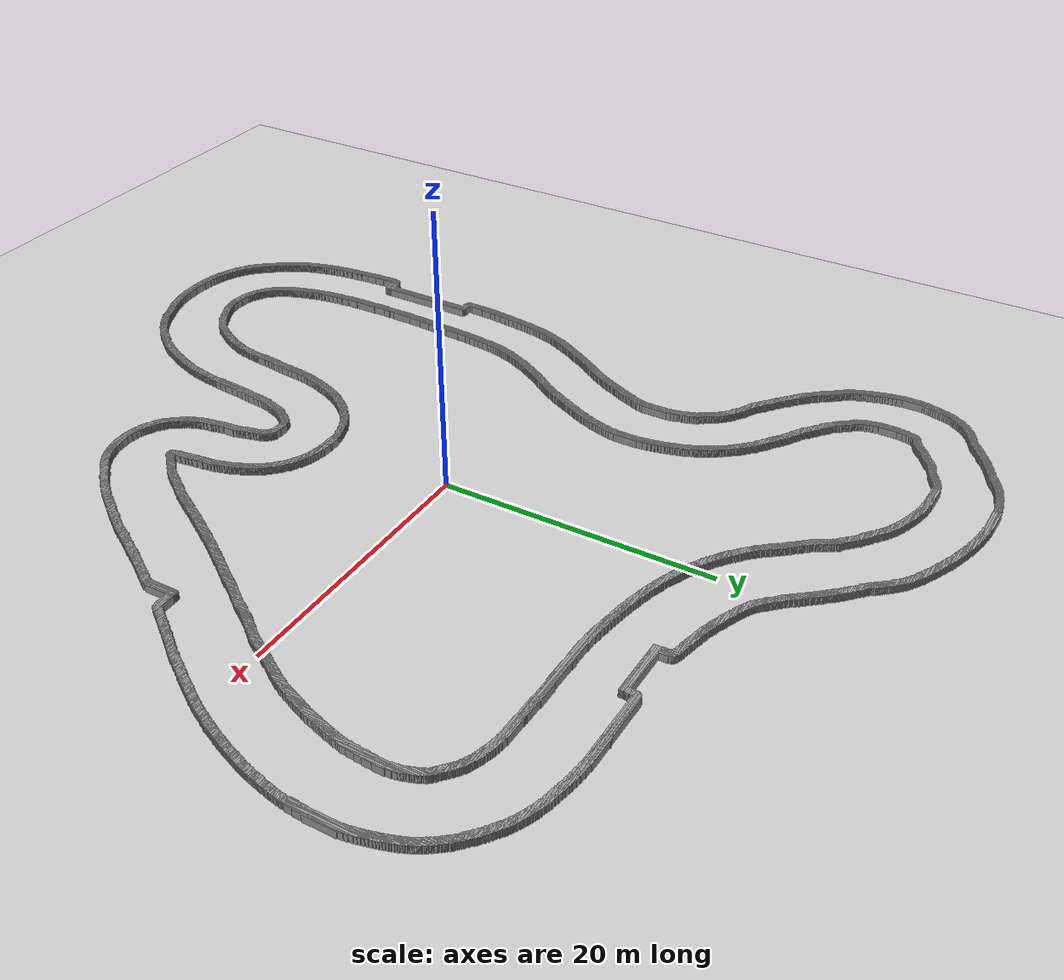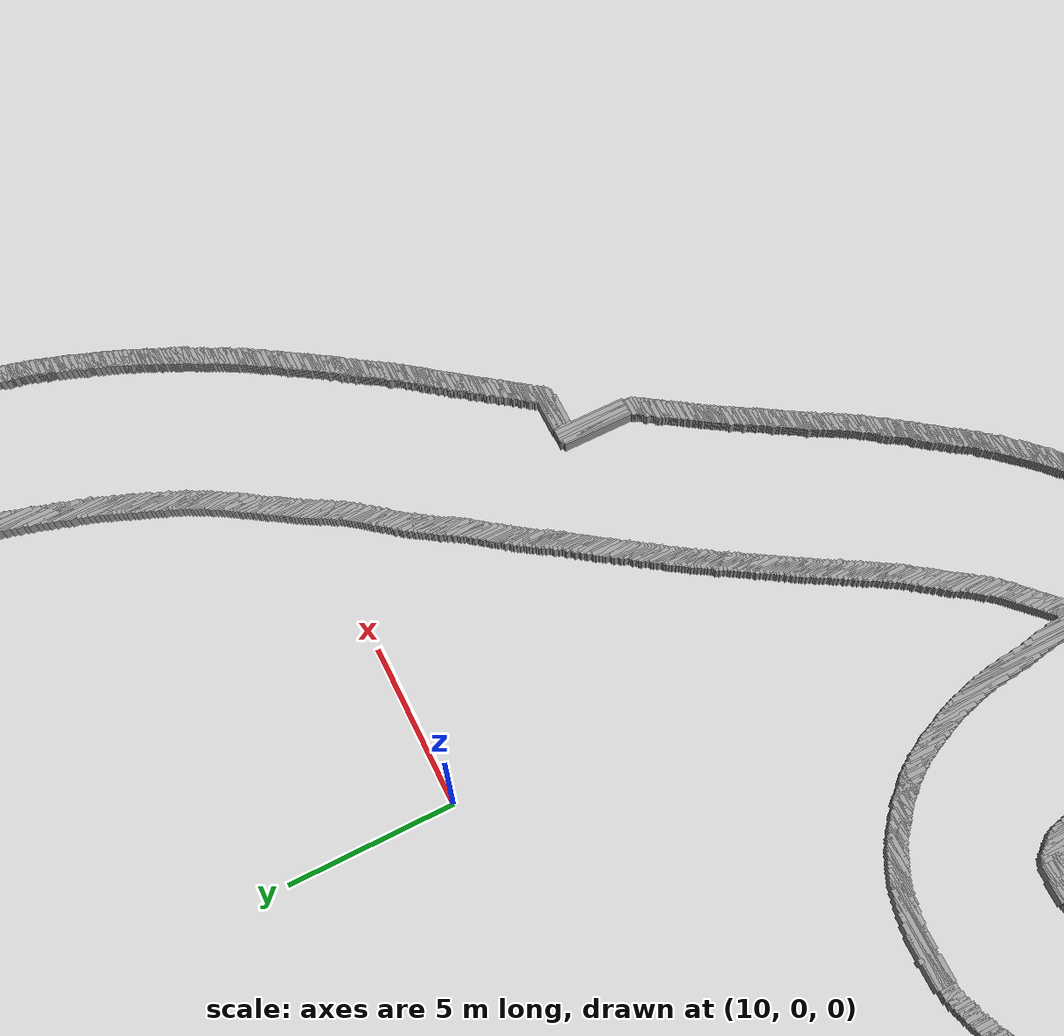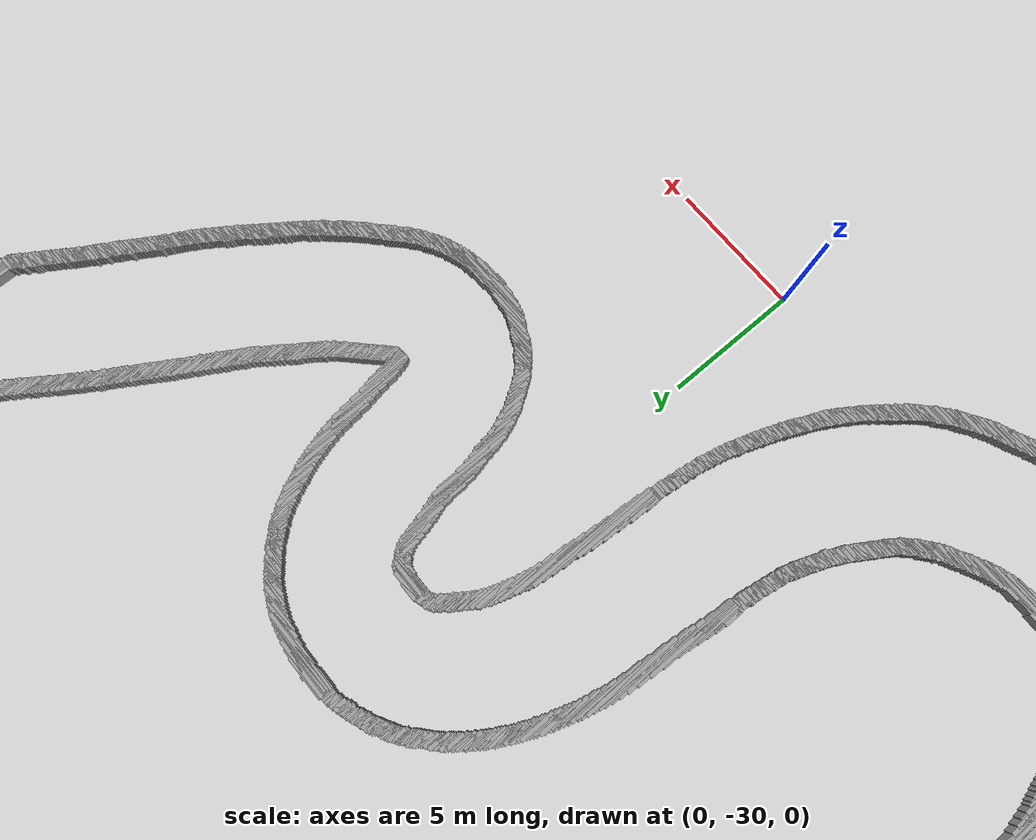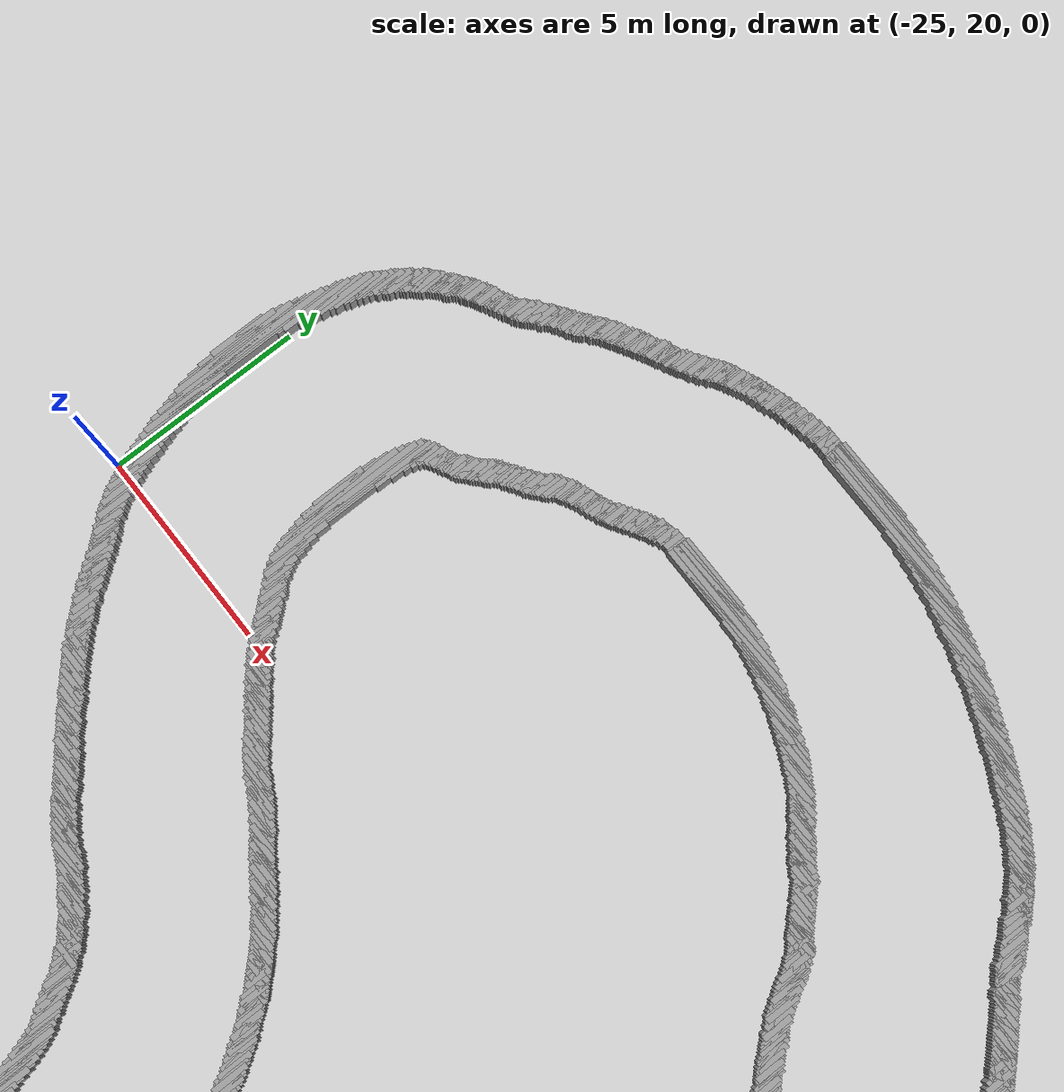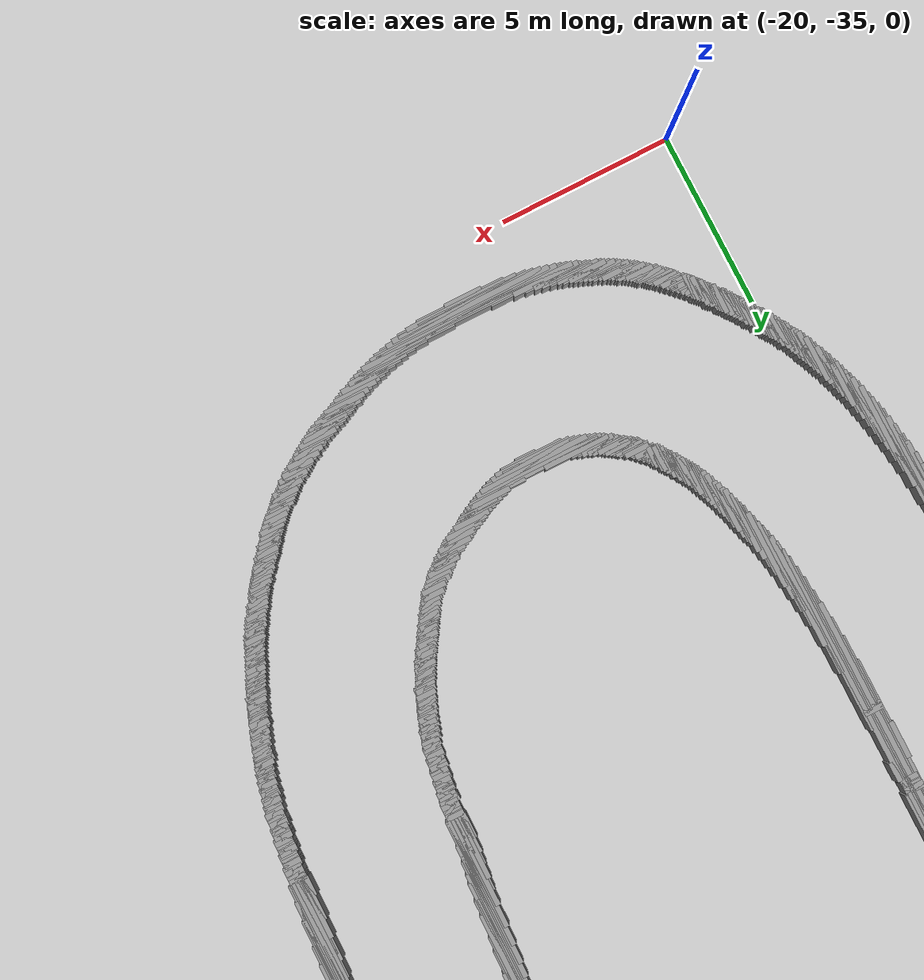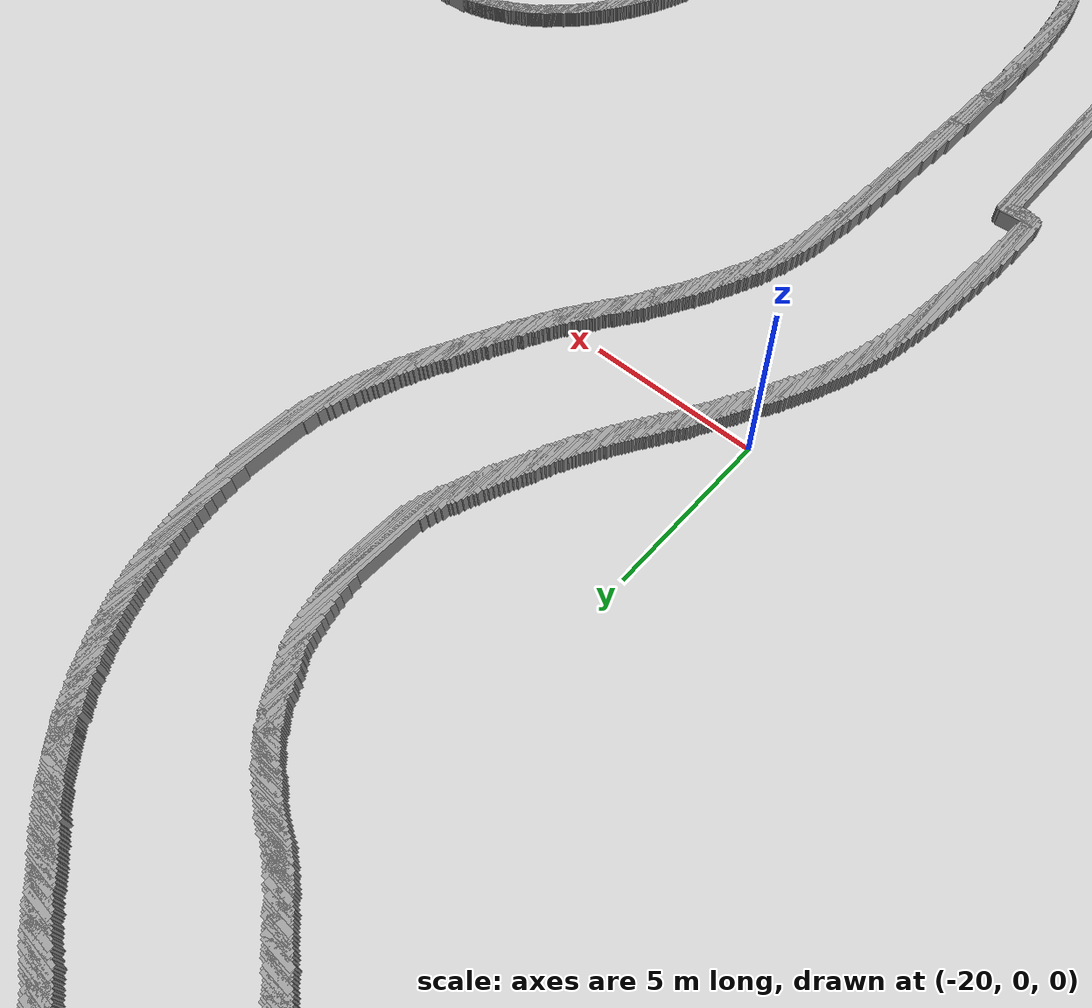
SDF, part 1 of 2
<sdf version="1.6">
 <world name="default">
  <plugin name="gazebo_ros_state" filename="libgazebo_ros_state.so">
   <ros><namespace>/gazebo</namespace></ros>
   <update_rate>1.0</update_rate>
  </plugin>
  <include><uri>model://sun</uri></include>
  <include><uri>model://ground_plane</uri></include>
  <physics type="ode">
   <real_time_update_rate>1000.0</real_time_update_rate>
   <max_step_size>0.001</max_step_size>
   <real_time_factor>1</real_time_factor>
   <ode>
    <solver>
     <type>quick</type>
     <iters>150</iters>
     <precon_iters>0</precon_iters>
     <sor>1.400000</sor>
     <use_dynamic_moi_rescaling>1</use_dynamic_moi_rescaling>
    </solver>
    <constraints>
     <cfm>0.00001</cfm>
     <erp>0.2</erp>
     <contact_max_correcting_vel>2000.000000</contact_max_correcting_vel>
     <contact_surface_layer>0.01000</contact_surface_layer>
    </constraints>
   </ode>
  </physics>
  <scene><ambient>0.4 0.4 0.4 1</ambient><background>0.7 0.7 0.7 1</background><shadows>true</shadows></scene>
  <model name="obstacle">
   <static>1</static>
   <link name="obstacle">
    <collision name="obstacle_1">
     <pose>-13.05 -33.575 0 0 0 0</pose>
     <geometry><box><size>1.1 0.15 1.0</size></box></geometry>
    </collision>
    <visual name="obstacle_1">
     <pose>-13.05 -33.575 0 0 0 0</pose>
     <geometry><box><size>1.1 0.15 1.0</size></box></geometry>
     <material>
      <script><uri>file://media/materials/scripts/gazebo.material</uri><name>Gazebo/Grey</name></script>
      <ambient>1 1 1 1</ambient>
     </material>
    </visual>
    <collision name="obstacle_2">
     <pose>-12.95 -33.525000000000006 0 0 0 0</pose>
     <geometry><box><size>2.6 0.15 1.0</size></box></geometry>
    </collision>
    <visual name="obstacle_2">
     <pose>-12.95 -33.525000000000006 0 0 0 0</pose>
     <geometry><box><size>2.6 0.15 1.0</size></box></geometry>
     <material>
      <script><uri>file://media/materials/scripts/gazebo.material</uri><name>Gazebo/Grey</name></script>
      <ambient>1 1 1 1</ambient>
     </material>
    </visual>
    <collision name="obstacle_3">
     <pose>-12.95 -33.475 0 0 0 0</pose>
     <geometry><box><size>3.3000000000000003 0.15 1.0</size></box></geometry>
    </collision>
    <visual name="obstacle_3">
     <pose>-12.95 -33.475 0 0 0 0</pose>
     <geometry><box><size>3.3000000000000003 0.15 1.0</size></box></geometry>
     <material>
      <script><uri>file://media/materials/scripts/gazebo.material</uri><name>Gazebo/Grey</name></script>
      <ambient>1 1 1 1</ambient>
     </material>
    </visual>
    <collision name="obstacle_4">
     <pose>-12.95 -33.425000000000004 0 0 0 0</pose>
     <geometry><box><size>3.85 0.15 1.0</size></box></geometry>
    </collision>
    <visual name="obstacle_4">
     <pose>-12.95 -33.425000000000004 0 0 0 0</pose>
     <geometry><box><size>3.85 0.15 1.0</size></box></geometry>
     <material>
      <script><uri>file://media/materials/scripts/gazebo.material</uri><name>Gazebo/Grey</name></script>
      <ambient>1 1 1 1</ambient>
     </material>
    </visual>
    <collision name="obstacle_5">
     <pose>-12.95 -33.375 0 0 0 0</pose>
     <geometry><box><size>4.25 0.15 1.0</size></box></geometry>
    </collision>
    <visual name="obstacle_5">
     <pose>-12.95 -33.375 0 0 0 0</pose>
     <geometry><box><size>4.25 0.15 1.0</size></box></geometry>
     <material>
      <script><uri>file://media/materials/scripts/gazebo.material</uri><name>Gazebo/Grey</name></script>
      <ambient>1 1 1 1</ambient>
     </material>
    </visual>
    <collision name="obstacle_6">
     <pose>-12.95 -33.325 0 0 0 0</pose>
     <geometry><box><size>4.65 0.15 1.0</size></box></geometry>
    </collision>
    <visual name="obstacle_6">
     <pose>-12.95 -33.325 0 0 0 0</pose>
     <geometry><box><size>4.65 0.15 1.0</size></box></geometry>
     <material>
      <script><uri>file://media/materials/scripts/gazebo.material</uri><name>Gazebo/Grey</name></script>
      <ambient>1 1 1 1</ambient>
     </material>
    </visual>
    <collision name="obstacle_7">
     <pose>-12.95 -33.275000000000006 0 0 0 0</pose>
     <geometry><box><size>5.050000000000001 0.15 1.0</size></box></geometry>
    </collision>
    <visual name="obstacle_7">
     <pose>-12.95 -33.275000000000006 0 0 0 0</pose>
     <geometry><box><size>5.050000000000001 0.15 1.0</size></box></geometry>
     <material>
      <script><uri>file://media/materials/scripts/gazebo.material</uri><name>Gazebo/Grey</name></script>
      <ambient>1 1 1 1</ambient>
     </material>
    </visual>
    <collision name="obstacle_8">
     <pose>-12.95 -33.225 0 0 0 0</pose>
     <geometry><box><size>5.45 0.15 1.0</size></box></geometry>
    </collision>
    <visual name="obstacle_8">
     <pose>-12.95 -33.225 0 0 0 0</pose>
     <geometry><box><size>5.45 0.15 1.0</size></box></geometry>
     <material>
      <script><uri>file://media/materials/scripts/gazebo.material</uri><name>Gazebo/Grey</name></script>
      <ambient>1 1 1 1</ambient>
     </material>
    </visual>
    <collision name="obstacle_9">
     <pose>-12.95 -33.175000000000004 0 0 0 0</pose>
     <geometry><box><size>5.75 0.15 1.0</size></box></geometry>
    </collision>
    <visual name="obstacle_9">
     <pose>-12.95 -33.175000000000004 0 0 0 0</pose>
     <geometry><box><size>5.75 0.15 1.0</size></box></geometry>
     <material>
      <script><uri>file://media/materials/scripts/gazebo.material</uri><name>Gazebo/Grey</name></script>
      <ambient>1 1 1 1</ambient>
     </material>
    </visual>
    <collision name="obstacle_10">
     <pose>-12.95 -33.125 0 0 0 0</pose>
     <geometry><box><size>6.050000000000001 0.15 1.0</size></box></geometry>
    </collision>
    <visual name="obstacle_10">
     <pose>-12.95 -33.125 0 0 0 0</pose>
     <geometry><box><size>6.050000000000001 0.15 1.0</size></box></geometry>
     <material>
      <script><uri>file://media/materials/scripts/gazebo.material</uri><name>Gazebo/Grey</name></script>
      <ambient>1 1 1 1</ambient>
     </material>
    </visual>
    <collision name="obstacle_11">
     <pose>-14.850000000000001 -33.075 0 0 0 0</pose>
     <geometry><box><size>2.45 0.15 1.0</size></box></geometry>
    </collision>
    <visual name="obstacle_11">
     <pose>-14.850000000000001 -33.075 0 0 0 0</pose>
     <geometry><box><size>2.45 0.15 1.0</size></box></geometry>
     <material>
      <script><uri>file://media/materials/scripts/gazebo.material</uri><name>Gazebo/Grey</name></script>
      <ambient>1 1 1 1</ambient>
     </material>
    </visual>
    <collision name="obstacle_12">
     <pose>-11.149999999999999 -33.075 0 0 0 0</pose>
     <geometry><box><size>2.75 0.15 1.0</size></box></geometry>
    </collision>
    <visual name="obstacle_12">
     <pose>-11.149999999999999 -33.075 0 0 0 0</pose>
     <geometry><box><size>2.75 0.15 1.0</size></box></geometry>
     <material>
      <script><uri>file://media/materials/scripts/gazebo.material</uri><name>Gazebo/Grey</name></script>
      <ambient>1 1 1 1</ambient>
     </material>
    </visual>
    <collision name="obstacle_13">
     <pose>-15.25 -33.025000000000006 0 0 0 0</pose>
     <geometry><box><size>1.9500000000000002 0.15 1.0</size></box></geometry>
    </collision>
    <visual name="obstacle_13">
     <pose>-15.25 -33.025000000000006 0 0 0 0</pose>
     <geometry><box><size>1.9500000000000002 0.15 1.0</size></box></geometry>
     <material>
      <script><uri>file://media/materials/scripts/gazebo.material</uri><name>Gazebo/Grey</name></script>
      <ambient>1 1 1 1</ambient>
     </material>
    </visual>
    <collision name="obstacle_14">
     <pose>-10.649999999999999 -33.025000000000006 0 0 0 0</pose>
     <geometry><box><size>2.0500000000000003 0.15 1.0</size></box></geometry>
    </collision>
    <visual name="obstacle_14">
     <pose>-10.649999999999999 -33.025000000000006 0 0 0 0</pose>
     <geometry><box><size>2.0500000000000003 0.15 1.0</size></box></geometry>
     <material>
      <script><uri>file://media/materials/scripts/gazebo.material</uri><name>Gazebo/Grey</name></script>
      <ambient>1 1 1 1</ambient>
     </material>
    </visual>
    <collision name="obstacle_15">
     <pose>-15.450000000000001 -32.975 0 0 0 0</pose>
     <geometry><box><size>1.7000000000000002 0.15 1.0</size></box></geometry>
    </collision>
    <visual name="obstacle_15">
     <pose>-15.450000000000001 -32.975 0 0 0 0</pose>
     <geometry><box><size>1.7000000000000002 0.15 1.0</size></box></geometry>
     <material>
      <script><uri>file://media/materials/scripts/gazebo.material</uri><name>Gazebo/Grey</name></script>
      <ambient>1 1 1 1</ambient>
     </material>
    </visual>
    <collision name="obstacle_16">
     <pose>-10.399999999999999 -32.975 0 0 0 0</pose>
     <geometry><box><size>1.8 0.15 1.0</size></box></geometry>
    </collision>
    <visual name="obstacle_16">
     <pose>-10.399999999999999 -32.975 0 0 0 0</pose>
     <geometry><box><size>1.8 0.15 1.0</size></box></geometry>
     <material>
      <script><uri>file://media/materials/scripts/gazebo.material</uri><name>Gazebo/Grey</name></script>
      <ambient>1 1 1 1</ambient>
     </material>
    </visual>
    <collision name="obstacle_17">
     <pose>-15.65 -32.925000000000004 0 0 0 0</pose>
     <geometry><box><size>1.6 0.15 1.0</size></box></geometry>
    </collision>
    <visual name="obstacle_17">
     <pose>-15.65 -32.925000000000004 0 0 0 0</pose>
     <geometry><box><size>1.6 0.15 1.0</size></box></geometry>
     <material>
      <script><uri>file://media/materials/scripts/gazebo.material</uri><name>Gazebo/Grey</name></script>
      <ambient>1 1 1 1</ambient>
     </material>
    </visual>
    <collision name="obstacle_18">
     <pose>-10.2 -32.925000000000004 0 0 0 0</pose>
     <geometry><box><size>1.6500000000000001 0.15 1.0</size></box></geometry>
    </collision>
    <visual name="obstacle_18">
     <pose>-10.2 -32.925000000000004 0 0 0 0</pose>
     <geometry><box><size>1.6500000000000001 0.15 1.0</size></box></geometry>
     <material>
      <script><uri>file://media/materials/scripts/gazebo.material</uri><name>Gazebo/Grey</name></script>
      <ambient>1 1 1 1</ambient>
     </material>
    </visual>
    <collision name="obstacle_19">
     <pose>-15.8 -32.875 0 0 0 0</pose>
     <geometry><box><size>1.5 0.15 1.0</size></box></geometry>
    </collision>
    <visual name="obstacle_19">
     <pose>-15.8 -32.875 0 0 0 0</pose>
     <geometry><box><size>1.5 0.15 1.0</size></box></geometry>
     <material>
      <script><uri>file://media/materials/scripts/gazebo.material</uri><name>Gazebo/Grey</name></script>
      <ambient>1 1 1 1</ambient>
     </material>
    </visual>
    <collision name="obstacle_20">
     <pose>-10.05 -32.875 0 0 0 0</pose>
     <geometry><box><size>1.55 0.15 1.0</size></box></geometry>
    </collision>
    <visual name="obstacle_20">
     <pose>-10.05 -32.875 0 0 0 0</pose>
     <geometry><box><size>1.55 0.15 1.0</size></box></geometry>
     <material>
      <script><uri>file://media/materials/scripts/gazebo.material</uri><name>Gazebo/Grey</name></script>
      <ambient>1 1 1 1</ambient>
     </material>
    </visual>
    <collision name="obstacle_21">
     <pose>-16.0 -32.825 0 0 0 0</pose>
     <geometry><box><size>1.4500000000000002 0.15 1.0</size></box></geometry>
    </collision>
    <visual name="obstacle_21">
     <pose>-16.0 -32.825 0 0 0 0</pose>
     <geometry><box><size>1.4500000000000002 0.15 1.0</size></box></geometry>
     <material>
      <script><uri>file://media/materials/scripts/gazebo.material</uri><name>Gazebo/Grey</name></script>
      <ambient>1 1 1 1</ambient>
     </material>
    </visual>
    <collision name="obstacle_22">
     <pose>-9.899999999999999 -32.825 0 0 0 0</pose>
     <geometry><box><size>1.4500000000000002 0.15 1.0</size></box></geometry>
    </collision>
    <visual name="obstacle_22">
     <pose>-9.899999999999999 -32.825 0 0 0 0</pose>
     <geometry><box><size>1.4500000000000002 0.15 1.0</size></box></geometry>
     <material>
      <script><uri>file://media/materials/scripts/gazebo.material</uri><name>Gazebo/Grey</name></script>
      <ambient>1 1 1 1</ambient>
     </material>
    </visual>
    <collision name="obstacle_23">
     <pose>-16.15 -32.775000000000006 0 0 0 0</pose>
     <geometry><box><size>1.35 0.15 1.0</size></box></geometry>
    </collision>
    <visual name="obstacle_23">
     <pose>-16.15 -32.775000000000006 0 0 0 0</pose>
     <geometry><box><size>1.35 0.15 1.0</size></box></geometry>
     <material>
      <script><uri>file://media/materials/scripts/gazebo.material</uri><name>Gazebo/Grey</name></script>
      <ambient>1 1 1 1</ambient>
     </material>
    </visual>
    <collision name="obstacle_24">
     <pose>-9.7 -32.775000000000006 0 0 0 0</pose>
     <geometry><box><size>1.4000000000000001 0.15 1.0</size></box></geometry>
    </collision>
    <visual name="obstacle_24">
     <pose>-9.7 -32.775000000000006 0 0 0 0</pose>
     <geometry><box><size>1.4000000000000001 0.15 1.0</size></box></geometry>
     <material>
      <script><uri>file://media/materials/scripts/gazebo.material</uri><name>Gazebo/Grey</name></script>
      <ambient>1 1 1 1</ambient>
     </material>
    </visual>
    <collision name="obstacle_25">
     <pose>-16.25 -32.725 0 0 0 0</pose>
     <geometry><box><size>1.3 0.15 1.0</size></box></geometry>
    </collision>
    <visual name="obstacle_25">
     <pose>-16.25 -32.725 0 0 0 0</pose>
     <geometry><box><size>1.3 0.15 1.0</size></box></geometry>
     <material>
      <script><uri>file://media/materials/scripts/gazebo.material</uri><name>Gazebo/Grey</name></script>
      <ambient>1 1 1 1</ambient>
     </material>
    </visual>
    <collision name="obstacle_26">
     <pose>-9.600000000000001 -32.725 0 0 0 0</pose>
     <geometry><box><size>1.35 0.15 1.0</size></box></geometry>
    </collision>
    <visual name="obstacle_26">
     <pose>-9.600000000000001 -32.725 0 0 0 0</pose>
     <geometry><box><size>1.35 0.15 1.0</size></box></geometry>
     <material>
      <script><uri>file://media/materials/scripts/gazebo.material</uri><name>Gazebo/Grey</name></script>
      <ambient>1 1 1 1</ambient>
     </material>
    </visual>
    <collision name="obstacle_27">
     <pose>-16.4 -32.675000000000004 0 0 0 0</pose>
     <geometry><box><size>1.25 0.15 1.0</size></box></geometry>
    </collision>
    <visual name="obstacle_27">
     <pose>-16.4 -32.675000000000004 0 0 0 0</pose>
     <geometry><box><size>1.25 0.15 1.0</size></box></geometry>
     <material>
      <script><uri>file://media/materials/scripts/gazebo.material</uri><name>Gazebo/Grey</name></script>
      <ambient>1 1 1 1</ambient>
     </material>
    </visual>
    <collision name="obstacle_28">
     <pose>-9.45 -32.675000000000004 0 0 0 0</pose>
     <geometry><box><size>1.3 0.15 1.0</size></box></geometry>
    </collision>
    <visual name="obstacle_28">
     <pose>-9.45 -32.675000000000004 0 0 0 0</pose>
     <geometry><box><size>1.3 0.15 1.0</size></box></geometry>
     <material>
      <script><uri>file://media/materials/scripts/gazebo.material</uri><name>Gazebo/Grey</name></script>
      <ambient>1 1 1 1</ambient>
     </material>
    </visual>
    <collision name="obstacle_29">
     <pose>-16.5 -32.625 0 0 0 0</pose>
     <geometry><box><size>1.25 0.15 1.0</size></box></geometry>
    </collision>
    <visual name="obstacle_29">
     <pose>-16.5 -32.625 0 0 0 0</pose>
     <geometry><box><size>1.25 0.15 1.0</size></box></geometry>
     <material>
      <script><uri>file://media/materials/scripts/gazebo.material</uri><name>Gazebo/Grey</name></script>
      <ambient>1 1 1 1</ambient>
     </material>
    </visual>
    <collision name="obstacle_30">
     <pose>-9.350000000000001 -32.625 0 0 0 0</pose>
     <geometry><box><size>1.25 0.15 1.0</size></box></geometry>
    </collision>
    <visual name="obstacle_30">
     <pose>-9.350000000000001 -32.625 0 0 0 0</pose>
     <geometry><box><size>1.25 0.15 1.0</size></box></geometry>
     <material>
      <script><uri>file://media/materials/scripts/gazebo.material</uri><name>Gazebo/Grey</name></script>
      <ambient>1 1 1 1</ambient>
     </material>
    </visual>
    <collision name="obstacle_31">
     <pose>-16.6 -32.575 0 0 0 0</pose>
     <geometry><box><size>1.2000000000000002 0.15 1.0</size></box></geometry>
    </collision>
    <visual name="obstacle_31">
     <pose>-16.6 -32.575 0 0 0 0</pose>
     <geometry><box><size>1.2000000000000002 0.15 1.0</size></box></geometry>
     <material>
      <script><uri>file://media/materials/scripts/gazebo.material</uri><name>Gazebo/Grey</name></script>
      <ambient>1 1 1 1</ambient>
     </material>
    </visual>
    <collision name="obstacle_32">
     <pose>-9.2 -32.575 0 0 0 0</pose>
     <geometry><box><size>1.2000000000000002 0.15 1.0</size></box></geometry>
    </collision>
    <visual name="obstacle_32">
     <pose>-9.2 -32.575 0 0 0 0</pose>
     <geometry><box><size>1.2000000000000002 0.15 1.0</size></box></geometry>
     <material>
      <script><uri>file://media/materials/scripts/gazebo.material</uri><name>Gazebo/Grey</name></script>
      <ambient>1 1 1 1</ambient>
     </material>
    </visual>
    <collision name="obstacle_33">
     <pose>-16.700000000000003 -32.525000000000006 0 0 0 0</pose>
     <geometry><box><size>1.1500000000000001 0.15 1.0</size></box></geometry>
    </collision>
    <visual name="obstacle_33">
     <pose>-16.700000000000003 -32.525000000000006 0 0 0 0</pose>
     <geometry><box><size>1.1500000000000001 0.15 1.0</size></box></geometry>
     <material>
      <script><uri>file://media/materials/scripts/gazebo.material</uri><name>Gazebo/Grey</name></script>
      <ambient>1 1 1 1</ambient>
     </material>
    </visual>
    <collision name="obstacle_34">
     <pose>-9.100000000000001 -32.525000000000006 0 0 0 0</pose>
     <geometry><box><size>1.2000000000000002 0.15 1.0</size></box></geometry>
    </collision>
    <visual name="obstacle_34">
     <pose>-9.100000000000001 -32.525000000000006 0 0 0 0</pose>
     <geometry><box><size>1.2000000000000002 0.15 1.0</size></box></geometry>
     <material>
      <script><uri>file://media/materials/scripts/gazebo.material</uri><name>Gazebo/Grey</name></script>
      <ambient>1 1 1 1</ambient>
     </material>
    </visual>
    <collision name="obstacle_35">
     <pose>-16.8 -32.475 0 0 0 0</pose>
     <geometry><box><size>1.1 0.15 1.0</size></box></geometry>
    </collision>
    <visual name="obstacle_35">
     <pose>-16.8 -32.475 0 0 0 0</pose>
     <geometry><box><size>1.1 0.15 1.0</size></box></geometry>
     <material>
      <script><uri>file://media/materials/scripts/gazebo.material</uri><name>Gazebo/Grey</name></script>
      <ambient>1 1 1 1</ambient>
     </material>
    </visual>
    <collision name="obstacle_36">
     <pose>-8.95 -32.475 0 0 0 0</pose>
     <geometry><box><size>1.2000000000000002 0.15 1.0</size></box></geometry>
    </collision>
    <visual name="obstacle_36">
     <pose>-8.95 -32.475 0 0 0 0</pose>
     <geometry><box><size>1.2000000000000002 0.15 1.0</size></box></geometry>
     <material>
      <script><uri>file://media/materials/scripts/gazebo.material</uri><name>Gazebo/Grey</name></script>
      <ambient>1 1 1 1</ambient>
     </material>
    </visual>
    <collision name="obstacle_37">
     <pose>-16.9 -32.425000000000004 0 0 0 0</pose>
     <geometry><box><size>1.1 0.15 1.0</size></box></geometry>
    </collision>
    <visual name="obstacle_37">
     <pose>-16.9 -32.425000000000004 0 0 0 0</pose>
     <geometry><box><size>1.1 0.15 1.0</size></box></geometry>
     <material>
      <script><uri>file://media/materials/scripts/gazebo.material</uri><name>Gazebo/Grey</name></script>
      <ambient>1 1 1 1</ambient>
     </material>
    </visual>
    <collision name="obstacle_38">
     <pose>-8.850000000000001 -32.425000000000004 0 0 0 0</pose>
     <geometry><box><size>1.2000000000000002 0.15 1.0</size></box></geometry>
    </collision>
    <visual name="obstacle_38">
     <pose>-8.850000000000001 -32.425000000000004 0 0 0 0</pose>
     <geometry><box><size>1.2000000000000002 0.15 1.0</size></box></geometry>
     <material>
      <script><uri>file://media/materials/scripts/gazebo.material</uri><name>Gazebo/Grey</name></script>
      <ambient>1 1 1 1</ambient>
     </material>
    </visual>
    <collision name="obstacle_39">
     <pose>-17.0 -32.375 0 0 0 0</pose>
     <geometry><box><size>1.0 0.15 1.0</size></box></geometry>
    </collision>
    <visual name="obstacle_39">
     <pose>-17.0 -32.375 0 0 0 0</pose>
     <geometry><box><size>1.0 0.15 1.0</size></box></geometry>
     <material>
      <script><uri>file://media/materials/scripts/gazebo.material</uri><name>Gazebo/Grey</name></script>
      <ambient>1 1 1 1</ambient>
     </material>
    </visual>
    <collision name="obstacle_40">
     <pose>-8.75 -32.375 0 0 0 0</pose>
     <geometry><box><size>1.25 0.15 1.0</size></box></geometry>
    </collision>
    <visual name="obstacle_40">
     <pose>-8.75 -32.375 0 0 0 0</pose>
     <geometry><box><size>1.25 0.15 1.0</size></box></geometry>
     <material>
      <script><uri>file://media/materials/scripts/gazebo.material</uri><name>Gazebo/Grey</name></script>
      <ambient>1 1 1 1</ambient>
     </material>
    </visual>
    <collision name="obstacle_41">
     <pose>-17.1 -32.325 0 0 0 0</pose>
     <geometry><box><size>1.0 0.15 1.0</size></box></geometry>
    </collision>
    <visual name="obstacle_41">
     <pose>-17.1 -32.325 0 0 0 0</pose>
     <geometry><box><size>1.0 0.15 1.0</size></box></geometry>
     <material>
      <script><uri>file://media/materials/scripts/gazebo.material</uri><name>Gazebo/Grey</name></script>
      <ambient>1 1 1 1</ambient>
     </material>
    </visual>
    <collision name="obstacle_42">
     <pose>-8.600000000000001 -32.325 0 0 0 0</pose>
     <geometry><box><size>1.2000000000000002 0.15 1.0</size></box></geometry>
    </collision>
    <visual name="obstacle_42">
     <pose>-8.600000000000001 -32.325 0 0 0 0</pose>
     <geometry><box><size>1.2000000000000002 0.15 1.0</size></box></geometry>
     <material>
      <script><uri>file://media/materials/scripts/gazebo.material</uri><name>Gazebo/Grey</name></script>
      <ambient>1 1 1 1</ambient>
     </material>
    </visual>
    <collision name="obstacle_43">
     <pose>-17.200000000000003 -32.275000000000006 0 0 0 0</pose>
     <geometry><box><size>0.9500000000000001 0.15 1.0</size></box></geometry>
    </collision>
    <visual name="obstacle_43">
     <pose>-17.200000000000003 -32.275000000000006 0 0 0 0</pose>
     <geometry><box><size>0.9500000000000001 0.15 1.0</size></box></geometry>
     <material>
      <script><uri>file://media/materials/scripts/gazebo.material</uri><name>Gazebo/Grey</name></script>
      <ambient>1 1 1 1</ambient>
     </material>
    </visual>
    <collision name="obstacle_44">
     <pose>-8.5 -32.275000000000006 0 0 0 0</pose>
     <geometry><box><size>1.25 0.15 1.0</size></box></geometry>
    </collision>
    <visual name="obstacle_44">
     <pose>-8.5 -32.275000000000006 0 0 0 0</pose>
     <geometry><box><size>1.25 0.15 1.0</size></box></geometry>
     <material>
      <script><uri>file://media/materials/scripts/gazebo.material</uri><name>Gazebo/Grey</name></script>
      <ambient>1 1 1 1</ambient>
     </material>
    </visual>
    <collision name="obstacle_45">
     <pose>-17.25 -32.225 0 0 0 0</pose>
     <geometry><box><size>0.9 0.15 1.0</size></box></geometry>
    </collision>
    <visual name="obstacle_45">
     <pose>-17.25 -32.225 0 0 0 0</pose>
     <geometry><box><size>0.9 0.15 1.0</size></box></geometry>
     <material>
      <script><uri>file://media/materials/scripts/gazebo.material</uri><name>Gazebo/Grey</name></script>
      <ambient>1 1 1 1</ambient>
     </material>
    </visual>
    <collision name="obstacle_46">
     <pose>-8.399999999999999 -32.225 0 0 0 0</pose>
     <geometry><box><size>1.25 0.15 1.0</size></box></geometry>
    </collision>
    <visual name="obstacle_46">
     <pose>-8.399999999999999 -32.225 0 0 0 0</pose>
     <geometry><box><size>1.25 0.15 1.0</size></box></geometry>
     <material>
      <script><uri>file://media/materials/scripts/gazebo.material</uri><name>Gazebo/Grey</name></script>
      <ambient>1 1 1 1</ambient>
     </material>
    </visual>
    <collision name="obstacle_47">
     <pose>-17.35 -32.175000000000004 0 0 0 0</pose>
     <geometry><box><size>0.9 0.15 1.0</size></box></geometry>
    </collision>
    <visual name="obstacle_47">
     <pose>-17.35 -32.175000000000004 0 0 0 0</pose>
     <geometry><box><size>0.9 0.15 1.0</size></box></geometry>
     <material>
      <script><uri>file://media/materials/scripts/gazebo.material</uri><name>Gazebo/Grey</name></script>
      <ambient>1 1 1 1</ambient>
     </material>
    </visual>
    <collision name="obstacle_48">
     <pose>-8.3 -32.175000000000004 0 0 0 0</pose>
     <geometry><box><size>1.2000000000000002 0.15 1.0</size></box></geometry>
    </collision>
    <visual name="obstacle_48">
     <pose>-8.3 -32.175000000000004 0 0 0 0</pose>
     <geometry><box><size>1.2000000000000002 0.15 1.0</size></box></geometry>
     <material>
      <script><uri>file://media/materials/scripts/gazebo.material</uri><name>Gazebo/Grey</name></script>
      <ambient>1 1 1 1</ambient>
     </material>
    </visual>
    <collision name="obstacle_49">
     <pose>-17.4 -32.125 0 0 0 0</pose>
     <geometry><box><size>0.9 0.15 1.0</size></box></geometry>
    </collision>
    <visual name="obstacle_49">
     <pose>-17.4 -32.125 0 0 0 0</pose>
     <geometry><box><size>0.9 0.15 1.0</size></box></geometry>
     <material>
      <script><uri>file://media/materials/scripts/gazebo.material</uri><name>Gazebo/Grey</name></script>
      <ambient>1 1 1 1</ambient>
     </material>
    </visual>
    <collision name="obstacle_50">
     <pose>-8.2 -32.125 0 0 0 0</pose>
     <geometry><box><size>1.2000000000000002 0.15 1.0</size></box></geometry>
    </collision>
    <visual name="obstacle_50">
     <pose>-8.2 -32.125 0 0 0 0</pose>
     <geometry><box><size>1.2000000000000002 0.15 1.0</size></box></geometry>
     <material>
      <script><uri>file://media/materials/scripts/gazebo.material</uri><name>Gazebo/Grey</name></script>
      <ambient>1 1 1 1</ambient>
     </material>
    </visual>
    <collision name="obstacle_51">
     <pose>-17.5 -32.075 0 0 0 0</pose>
     <geometry><box><size>0.8500000000000001 0.15 1.0</size></box></geometry>
    </collision>
    <visual name="obstacle_51">
     <pose>-17.5 -32.075 0 0 0 0</pose>
     <geometry><box><size>0.8500000000000001 0.15 1.0</size></box></geometry>
     <material>
      <script><uri>file://media/materials/scripts/gazebo.material</uri><name>Gazebo/Grey</name></script>
      <ambient>1 1 1 1</ambient>
     </material>
    </visual>
    <collision name="obstacle_52">
     <pose>-8.100000000000001 -32.075 0 0 0 0</pose>
     <geometry><box><size>1.2000000000000002 0.15 1.0</size></box></geometry>
    </collision>
    <visual name="obstacle_52">
     <pose>-8.100000000000001 -32.075 0 0 0 0</pose>
     <geometry><box><size>1.2000000000000002 0.15 1.0</size></box></geometry>
     <material>
      <script><uri>file://media/materials/scripts/gazebo.material</uri><name>Gazebo/Grey</name></script>
      <ambient>1 1 1 1</ambient>
     </material>
    </visual>
    <collision name="obstacle_53">
     <pose>-17.55 -32.025000000000006 0 0 0 0</pose>
     <geometry><box><size>0.8 0.15 1.0</size></box></geometry>
    </collision>
    <visual name="obstacle_53">
     <pose>-17.55 -32.025000000000006 0 0 0 0</pose>
     <geometry><box><size>0.8 0.15 1.0</size></box></geometry>
     <material>
      <script><uri>file://media/materials/scripts/gazebo.material</uri><name>Gazebo/Grey</name></script>
      <ambient>1 1 1 1</ambient>
     </material>
    </visual>
    <collision name="obstacle_54">
     <pose>-8.0 -32.025000000000006 0 0 0 0</pose>
     <geometry><box><size>1.1 0.15 1.0</size></box></geometry>
    </collision>
    <visual name="obstacle_54">
     <pose>-8.0 -32.025000000000006 0 0 0 0</pose>
     <geometry><box><size>1.1 0.15 1.0</size></box></geometry>
     <material>
      <script><uri>file://media/materials/scripts/gazebo.material</uri><name>Gazebo/Grey</name></script>
      <ambient>1 1 1 1</ambient>
     </material>
    </visual>
    <collision name="obstacle_55">
     <pose>-17.65 -31.975 0 0 0 0</pose>
     <geometry><box><size>0.8500000000000001 0.15 1.0</size></box></geometry>
    </collision>
    <visual name="obstacle_55">
     <pose>-17.65 -31.975 0 0 0 0</pose>
     <geometry><box><size>0.8500000000000001 0.15 1.0</size></box></geometry>
     <material>
      <script><uri>file://media/materials/scripts/gazebo.material</uri><name>Gazebo/Grey</name></script>
      <ambient>1 1 1 1</ambient>
     </material>
    </visual>
    <collision name="obstacle_56">
     <pose>-7.899999999999999 -31.975 0 0 0 0</pose>
     <geometry><box><size>1.1 0.15 1.0</size></box></geometry>
    </collision>
    <visual name="obstacle_56">
     <pose>-7.899999999999999 -31.975 0 0 0 0</pose>
     <geometry><box><size>1.1 0.15 1.0</size></box></geometry>
     <material>
      <script><uri>file://media/materials/scripts/gazebo.material</uri><name>Gazebo/Grey</name></script>
      <ambient>1 1 1 1</ambient>
     </material>
    </visual>
    <collision name="obstacle_57">
     <pose>-17.700000000000003 -31.925000000000004 0 0 0 0</pose>
     <geometry><box><size>0.8 0.15 1.0</size></box></geometry>
    </collision>
    <visual name="obstacle_57">
     <pose>-17.700000000000003 -31.925000000000004 0 0 0 0</pose>
     <geometry><box><size>0.8 0.15 1.0</size></box></geometry>
     <material>
      <script><uri>file://media/materials/scripts/gazebo.material</uri><name>Gazebo/Grey</name></script>
      <ambient>1 1 1 1</ambient>
     </material>
    </visual>
    <collision name="obstacle_58">
     <pose>-7.800000000000001 -31.925000000000004 0 0 0 0</pose>
     <geometry><box><size>1.05 0.15 1.0</size></box></geometry>
    </collision>
    <visual name="obstacle_58">
     <pose>-7.800000000000001 -31.925000000000004 0 0 0 0</pose>
     <geometry><box><size>1.05 0.15 1.0</size></box></geometry>
     <material>
      <script><uri>file://media/materials/scripts/gazebo.material</uri><name>Gazebo/Grey</name></script>
      <ambient>1 1 1 1</ambient>
     </material>
    </visual>
    <collision name="obstacle_59">
     <pose>-17.75 -31.875000000000004 0 0 0 0</pose>
     <geometry><box><size>0.8 0.15 1.0</size></box></geometry>
    </collision>
    <visual name="obstacle_59">
     <pose>-17.75 -31.875000000000004 0 0 0 0</pose>
     <geometry><box><size>0.8 0.15 1.0</size></box></geometry>
     <material>
      <script><uri>file://media/materials/scripts/gazebo.material</uri><name>Gazebo/Grey</name></script>
      <ambient>1 1 1 1</ambient>
     </material>
    </visual>
    <collision name="obstacle_60">
     <pose>-7.699999999999999 -31.875000000000004 0 0 0 0</pose>
     <geometry><box><size>1.0 0.15 1.0</size></box></geometry>
    </collision>
    <visual name="obstacle_60">
     <pose>-7.699999999999999 -31.875000000000004 0 0 0 0</pose>
     <geometry><box><size>1.0 0.15 1.0</size></box></geometry>
     <material>
      <script><uri>file://media/materials/scripts/gazebo.material</uri><name>Gazebo/Grey</name></script>
      <ambient>1 1 1 1</ambient>
     </material>
    </visual>
    <collision name="obstacle_61">
     <pose>-17.8 -31.825000000000003 0 0 0 0</pose>
     <geometry><box><size>0.8 0.15 1.0</size></box></geometry>
    </collision>
    <visual name="obstacle_61">
     <pose>-17.8 -31.825000000000003 0 0 0 0</pose>
     <geometry><box><size>0.8 0.15 1.0</size></box></geometry>
     <material>
      <script><uri>file://media/materials/scripts/gazebo.material</uri><name>Gazebo/Grey</name></script>
      <ambient>1 1 1 1</ambient>
     </material>
    </visual>
    <collision name="obstacle_62">
     <pose>-7.600000000000001 -31.825000000000003 0 0 0 0</pose>
     <geometry><box><size>0.9500000000000001 0.15 1.0</size></box></geometry>
    </collision>
    <visual name="obstacle_62">
     <pose>-7.600000000000001 -31.825000000000003 0 0 0 0</pose>
     <geometry><box><size>0.9500000000000001 0.15 1.0</size></box></geometry>
     <material>
      <script><uri>file://media/materials/scripts/gazebo.material</uri><name>Gazebo/Grey</name></script>
      <ambient>1 1 1 1</ambient>
     </material>
    </visual>
    <collision name="obstacle_63">
     <pose>-17.9 -31.775000000000002 0 0 0 0</pose>
     <geometry><box><size>0.75 0.15 1.0</size></box></geometry>
    </collision>
    <visual name="obstacle_63">
     <pose>-17.9 -31.775000000000002 0 0 0 0</pose>
     <geometry><box><size>0.75 0.15 1.0</size></box></geometry>
     <material>
      <script><uri>file://media/materials/scripts/gazebo.material</uri><name>Gazebo/Grey</name></script>
      <ambient>1 1 1 1</ambient>
     </material>
    </visual>
    <collision name="obstacle_64">
     <pose>-7.550000000000001 -31.775000000000002 0 0 0 0</pose>
     <geometry><box><size>0.9500000000000001 0.15 1.0</size></box></geometry>
    </collision>
    <visual name="obstacle_64">
     <pose>-7.550000000000001 -31.775000000000002 0 0 0 0</pose>
     <geometry><box><size>0.9500000000000001 0.15 1.0</size></box></geometry>
     <material>
      <script><uri>file://media/materials/scripts/gazebo.material</uri><name>Gazebo/Grey</name></script>
      <ambient>1 1 1 1</ambient>
     </material>
    </visual>
    <collision name="obstacle_65">
     <pose>-17.950000000000003 -31.725 0 0 0 0</pose>
     <geometry><box><size>0.75 0.15 1.0</size></box></geometry>
    </collision>
    <visual name="obstacle_65">
     <pose>-17.950000000000003 -31.725 0 0 0 0</pose>
     <geometry><box><size>0.75 0.15 1.0</size></box></geometry>
     <material>
      <script><uri>file://media/materials/scripts/gazebo.material</uri><name>Gazebo/Grey</name></script>
      <ambient>1 1 1 1</ambient>
     </material>
    </visual>
    <collision name="obstacle_66">
     <pose>-7.449999999999999 -31.725 0 0 0 0</pose>
     <geometry><box><size>0.9500000000000001 0.15 1.0</size></box></geometry>
    </collision>
    <visual name="obstacle_66">
     <pose>-7.449999999999999 -31.725 0 0 0 0</pose>
     <geometry><box><size>0.9500000000000001 0.15 1.0</size></box></geometry>
     <material>
      <script><uri>file://media/materials/scripts/gazebo.material</uri><name>Gazebo/Grey</name></script>
      <ambient>1 1 1 1</ambient>
     </material>
    </visual>
    <collision name="obstacle_67">
     <pose>-18.0 -31.675000000000004 0 0 0 0</pose>
     <geometry><box><size>0.75 0.15 1.0</size></box></geometry>
    </collision>
    <visual name="obstacle_67">
     <pose>-18.0 -31.675000000000004 0 0 0 0</pose>
     <geometry><box><size>0.75 0.15 1.0</size></box></geometry>
     <material>
      <script><uri>file://media/materials/scripts/gazebo.material</uri><name>Gazebo/Grey</name></script>
      <ambient>1 1 1 1</ambient>
     </material>
    </visual>
    <collision name="obstacle_68">
     <pose>-7.350000000000001 -31.675000000000004 0 0 0 0</pose>
     <geometry><box><size>0.9 0.15 1.0</size></box></geometry>
    </collision>
    <visual name="obstacle_68">
     <pose>-7.350000000000001 -31.675000000000004 0 0 0 0</pose>
     <geometry><box><size>0.9 0.15 1.0</size></box></geometry>
     <material>
      <script><uri>file://media/materials/scripts/gazebo.material</uri><name>Gazebo/Grey</name></script>
      <ambient>1 1 1 1</ambient>
     </material>
    </visual>
    <collision name="obstacle_69">
     <pose>-18.05 -31.625000000000004 0 0 0 0</pose>
     <geometry><box><size>0.75 0.15 1.0</size></box></geometry>
    </collision>
    <visual name="obstacle_69">
     <pose>-18.05 -31.625000000000004 0 0 0 0</pose>
     <geometry><box><size>0.75 0.15 1.0</size></box></geometry>
     <material>
      <script><uri>file://media/materials/scripts/gazebo.material</uri><name>Gazebo/Grey</name></script>
      <ambient>1 1 1 1</ambient>
     </material>
    </visual>
    <collision name="obstacle_70">
     <pose>-7.300000000000001 -31.625000000000004 0 0 0 0</pose>
     <geometry><box><size>0.9500000000000001 0.15 1.0</size></box></geometry>
    </collision>
    <visual name="obstacle_70">
     <pose>-7.300000000000001 -31.625000000000004 0 0 0 0</pose>
     <geometry><box><size>0.9500000000000001 0.15 1.0</size></box></geometry>
     <material>
      <script><uri>file://media/materials/scripts/gazebo.material</uri><name>Gazebo/Grey</name></script>
      <ambient>1 1 1 1</ambient>
     </material>
    </visual>
    <collision name="obstacle_71">
     <pose>-18.1 -31.575000000000003 0 0 0 0</pose>
     <geometry><box><size>0.7000000000000001 0.15 1.0</size></box></geometry>
    </collision>
    <visual name="obstacle_71">
     <pose>-18.1 -31.575000000000003 0 0 0 0</pose>
     <geometry><box><size>0.7000000000000001 0.15 1.0</size></box></geometry>
     <material>
      <script><uri>file://media/materials/scripts/gazebo.material</uri><name>Gazebo/Grey</name></script>
      <ambient>1 1 1 1</ambient>
     </material>
    </visual>
    <collision name="obstacle_72">
     <pose>-7.199999999999999 -31.575000000000003 0 0 0 0</pose>
     <geometry><box><size>0.9 0.15 1.0</size></box></geometry>
    </collision>
    <visual name="obstacle_72">
     <pose>-7.199999999999999 -31.575000000000003 0 0 0 0</pose>
     <geometry><box><size>0.9 0.15 1.0</size></box></geometry>
     <material>
      <script><uri>file://media/materials/scripts/gazebo.material</uri><name>Gazebo/Grey</name></script>
      <ambient>1 1 1 1</ambient>
     </material>
    </visual>
    <collision name="obstacle_73">
     <pose>-18.15 -31.525000000000002 0 0 0 0</pose>
     <geometry><box><size>0.7000000000000001 0.15 1.0</size></box></geometry>
    </collision>
    <visual name="obstacle_73">
     <pose>-18.15 -31.525000000000002 0 0 0 0</pose>
     <geometry><box><size>0.7000000000000001 0.15 1.0</size></box></geometry>
     <material>
      <script><uri>file://media/materials/scripts/gazebo.material</uri><name>Gazebo/Grey</name></script>
      <ambient>1 1 1 1</ambient>
     </material>
    </visual>
    <collision name="obstacle_74">
     <pose>-7.100000000000001 -31.525000000000002 0 0 0 0</pose>
     <geometry><box><size>0.9 0.15 1.0</size></box></geometry>
    </collision>
    <visual name="obstacle_74">
     <pose>-7.100000000000001 -31.525000000000002 0 0 0 0</pose>
     <geometry><box><size>0.9 0.15 1.0</size></box></geometry>
     <material>
      <script><uri>file://media/materials/scripts/gazebo.material</uri><name>Gazebo/Grey</name></script>
      <ambient>1 1 1 1</ambient>
     </material>
    </visual>
    <collision name="obstacle_75">
     <pose>-18.55 -31.125000000000004 0 0 0 1.5708</pose>
     <geometry><box><size>0.75 0.15 1.0</size></box></geometry>
    </collision>
    <visual name="obstacle_75">
     <pose>-18.55 -31.125000000000004 0 0 0 1.5708</pose>
     <geometry><box><size>0.75 0.15 1.0</size></box></geometry>
     <material>
      <script><uri>file://media/materials/scripts/gazebo.material</uri><name>Gazebo/Grey</name></script>
      <ambient>1 1 1 1</ambient>
     </material>
    </visual>
    <collision name="obstacle_76">
     <pose>-18.200000000000003 -31.475 0 0 0 0</pose>
     <geometry><box><size>0.65 0.15 1.0</size></box></geometry>
    </collision>
    <visual name="obstacle_76">
     <pose>-18.200000000000003 -31.475 0 0 0 0</pose>
     <geometry><box><size>0.65 0.15 1.0</size></box></geometry>
     <material>
      <script><uri>file://media/materials/scripts/gazebo.material</uri><name>Gazebo/Grey</name></script>
      <ambient>1 1 1 1</ambient>
     </material>
    </visual>
    <collision name="obstacle_77">
     <pose>-7.050000000000001 -31.475 0 0 0 0</pose>
     <geometry><box><size>0.9 0.15 1.0</size></box></geometry>
    </collision>
    <visual name="obstacle_77">
     <pose>-7.050000000000001 -31.475 0 0 0 0</pose>
     <geometry><box><size>0.9 0.15 1.0</size></box></geometry>
     <material>
      <script><uri>file://media/materials/scripts/gazebo.material</uri><name>Gazebo/Grey</name></script>
      <ambient>1 1 1 1</ambient>
     </material>
    </visual>
    <collision name="obstacle_78">
     <pose>-18.6 -31.075000000000003 0 0 0 1.5708</pose>
     <geometry><box><size>0.75 0.15 1.0</size></box></geometry>
    </collision>
    <visual name="obstacle_78">
     <pose>-18.6 -31.075000000000003 0 0 0 1.5708</pose>
     <geometry><box><size>0.75 0.15 1.0</size></box></geometry>
     <material>
      <script><uri>file://media/materials/scripts/gazebo.material</uri><name>Gazebo/Grey</name></script>
      <ambient>1 1 1 1</ambient>
     </material>
    </visual>
    <collision name="obstacle_79">
     <pose>-18.200000000000003 -31.425000000000004 0 0 0 0</pose>
     <geometry><box><size>0.6000000000000001 0.15 1.0</size></box></geometry>
    </collision>
    <visual name="obstacle_79">
     <pose>-18.200000000000003 -31.425000000000004 0 0 0 0</pose>
     <geometry><box><size>0.6000000000000001 0.15 1.0</size></box></geometry>
     <material>
      <script><uri>file://media/materials/scripts/gazebo.material</uri><name>Gazebo/Grey</name></script>
      <ambient>1 1 1 1</ambient>
     </material>
    </visual>
    <collision name="obstacle_80">
     <pose>-7.0 -31.425000000000004 0 0 0 0</pose>
     <geometry><box><size>0.8500000000000001 0.15 1.0</size></box></geometry>
    </collision>
    <visual name="obstacle_80">
     <pose>-7.0 -31.425000000000004 0 0 0 0</pose>
     <geometry><box><size>0.8500000000000001 0.15 1.0</size></box></geometry>
     <material>
      <script><uri>file://media/materials/scripts/gazebo.material</uri><name>Gazebo/Grey</name></script>
      <ambient>1 1 1 1</ambient>
     </material>
    </visual>
    <collision name="obstacle_81">
     <pose>-18.65 -31.025000000000002 0 0 0 1.5708</pose>
     <geometry><box><size>0.75 0.15 1.0</size></box></geometry>
    </collision>
    <visual name="obstacle_81">
     <pose>-18.65 -31.025000000000002 0 0 0 1.5708</pose>
     <geometry><box><size>0.75 0.15 1.0</size></box></geometry>
     <material>
      <script><uri>file://media/materials/scripts/gazebo.material</uri><name>Gazebo/Grey</name></script>
      <ambient>1 1 1 1</ambient>
     </material>
    </visual>
    <collision name="obstacle_82">
     <pose>-18.25 -31.375000000000004 0 0 0 0</pose>
     <geometry><box><size>0.55 0.15 1.0</size></box></geometry>
    </collision>
    <visual name="obstacle_82">
     <pose>-18.25 -31.375000000000004 0 0 0 0</pose>
     <geometry><box><size>0.55 0.15 1.0</size></box></geometry>
     <material>
      <script><uri>file://media/materials/scripts/gazebo.material</uri><name>Gazebo/Grey</name></script>
      <ambient>1 1 1 1</ambient>
     </material>
    </visual>
    <collision name="obstacle_83">
     <pose>-6.899999999999999 -31.375000000000004 0 0 0 0</pose>
     <geometry><box><size>0.9 0.15 1.0</size></box></geometry>
    </collision>
    <visual name="obstacle_83">
     <pose>-6.899999999999999 -31.375000000000004 0 0 0 0</pose>
     <geometry><box><size>0.9 0.15 1.0</size></box></geometry>
     <material>
      <script><uri>file://media/materials/scripts/gazebo.material</uri><name>Gazebo/Grey</name></script>
      <ambient>1 1 1 1</ambient>
     </material>
    </visual>
    <collision name="obstacle_84">
     <pose>-18.700000000000003 -30.975 0 0 0 1.5708</pose>
     <geometry><box><size>0.75 0.15 1.0</size></box></geometry>
    </collision>
    <visual name="obstacle_84">
     <pose>-18.700000000000003 -30.975 0 0 0 1.5708</pose>
     <geometry><box><size>0.75 0.15 1.0</size></box></geometry>
     <material>
      <script><uri>file://media/materials/scripts/gazebo.material</uri><name>Gazebo/Grey</name></script>
      <ambient>1 1 1 1</ambient>
     </material>
    </visual>
    <collision name="obstacle_85">
     <pose>-18.25 -31.325000000000003 0 0 0 0</pose>
     <geometry><box><size>0.5 0.15 1.0</size></box></geometry>
    </collision>
    <visual name="obstacle_85">
     <pose>-18.25 -31.325000000000003 0 0 0 0</pose>
     <geometry><box><size>0.5 0.15 1.0</size></box></geometry>
     <material>
      <script><uri>file://media/materials/scripts/gazebo.material</uri><name>Gazebo/Grey</name></script>
      <ambient>1 1 1 1</ambient>
     </material>
    </visual>
    <collision name="obstacle_86">
     <pose>-6.850000000000001 -31.325000000000003 0 0 0 0</pose>
     <geometry><box><size>0.8500000000000001 0.15 1.0</size></box></geometry>
    </collision>
    <visual name="obstacle_86">
     <pose>-6.850000000000001 -31.325000000000003 0 0 0 0</pose>
     <geometry><box><size>0.8500000000000001 0.15 1.0</size></box></geometry>
     <material>
      <script><uri>file://media/materials/scripts/gazebo.material</uri><name>Gazebo/Grey</name></script>
      <ambient>1 1 1 1</ambient>
     </material>
    </visual>
    <collision name="obstacle_87">
     <pose>-18.75 -30.925000000000004 0 0 0 1.5708</pose>
     <geometry><box><size>0.75 0.15 1.0</size></box></geometry>
    </collision>
    <visual name="obstacle_87">
     <pose>-18.75 -30.925000000000004 0 0 0 1.5708</pose>
     <geometry><box><size>0.75 0.15 1.0</size></box></geometry>
     <material>
      <script><uri>file://media/materials/scripts/gazebo.material</uri><name>Gazebo/Grey</name></script>
      <ambient>1 1 1 1</ambient>
     </material>
    </visual>
    <collision name="obstacle_88">
     <pose>-18.3 -31.275000000000002 0 0 0 0</pose>
     <geometry><box><size>0.45 0.15 1.0</size></box></geometry>
    </collision>
    <visual name="obstacle_88">
     <pose>-18.3 -31.275000000000002 0 0 0 0</pose>
     <geometry><box><size>0.45 0.15 1.0</size></box></geometry>
     <material>
      <script><uri>file://media/materials/scripts/gazebo.material</uri><name>Gazebo/Grey</name></script>
      <ambient>1 1 1 1</ambient>
     </material>
    </visual>
    <collision name="obstacle_89">
     <pose>-6.800000000000001 -31.275000000000002 0 0 0 0</pose>
     <geometry><box><size>0.8500000000000001 0.15 1.0</size></box></geometry>
    </collision>
    <visual name="obstacle_89">
     <pose>-6.800000000000001 -31.275000000000002 0 0 0 0</pose>
     <geometry><box><size>0.8500000000000001 0.15 1.0</size></box></geometry>
     <material>
      <script><uri>file://media/materials/scripts/gazebo.material</uri><name>Gazebo/Grey</name></script>
      <ambient>1 1 1 1</ambient>
     </material>
    </visual>
    <collision name="obstacle_90">
     <pose>-18.8 -30.825000000000003 0 0 0 1.5708</pose>
     <geometry><box><size>0.8 0.15 1.0</size></box></geometry>
    </collision>
    <visual name="obstacle_90">
     <pose>-18.8 -30.825000000000003 0 0 0 1.5708</pose>
     <geometry><box><size>0.8 0.15 1.0</size></box></geometry>
     <material>
      <script><uri>file://media/materials/scripts/gazebo.material</uri><name>Gazebo/Grey</name></script>
      <ambient>1 1 1 1</ambient>
     </material>
    </visual>
    <collision name="obstacle_91">
     <pose>-18.3 -31.225 0 0 0 0</pose>
     <geometry><box><size>0.4 0.15 1.0</size></box></geometry>
    </collision>
    <visual name="obstacle_91">
     <pose>-18.3 -31.225 0 0 0 0</pose>
     <geometry><box><size>0.4 0.15 1.0</size></box></geometry>
     <material>
      <script><uri>file://media/materials/scripts/gazebo.material</uri><name>Gazebo/Grey</name></script>
      <ambient>1 1 1 1</ambient>
     </material>
    </visual>
    <collision name="obstacle_92">
     <pose>-6.699999999999999 -31.225 0 0 0 0</pose>
     <geometry><box><size>0.8 0.15 1.0</size></box></geometry>
    </collision>
    <visual name="obstacle_92">
     <pose>-6.699999999999999 -31.225 0 0 0 0</pose>
     <geometry><box><size>0.8 0.15 1.0</size></box></geometry>
     <material>
      <script><uri>file://media/materials/scripts/gazebo.material</uri><name>Gazebo/Grey</name></script>
      <ambient>1 1 1 1</ambient>
     </material>
    </visual>
    <collision name="obstacle_93">
     <pose>-18.85 -30.775000000000002 0 0 0 1.5708</pose>
     <geometry><box><size>0.8 0.15 1.0</size></box></geometry>
    </collision>
    <visual name="obstacle_93">
     <pose>-18.85 -30.775000000000002 0 0 0 1.5708</pose>
     <geometry><box><size>0.8 0.15 1.0</size></box></geometry>
     <material>
      <script><uri>file://media/materials/scripts/gazebo.material</uri><name>Gazebo/Grey</name></script>
      <ambient>1 1 1 1</ambient>
     </material>
    </visual>
    <collision name="obstacle_94">
     <pose>-18.35 -31.175000000000004 0 0 0 0</pose>
     <geometry><box><size>0.35000000000000003 0.15 1.0</size></box></geometry>
    </collision>
    <visual name="obstacle_94">
     <pose>-18.35 -31.175000000000004 0 0 0 0</pose>
     <geometry><box><size>0.35000000000000003 0.15 1.0</size></box></geometry>
     <material>
      <script><uri>file://media/materials/scripts/gazebo.material</uri><name>Gazebo/Grey</name></script>
      <ambient>1 1 1 1</ambient>
     </material>
    </visual>
    <collision name="obstacle_95">
     <pose>-6.649999999999999 -31.175000000000004 0 0 0 0</pose>
     <geometry><box><size>0.8 0.15 1.0</size></box></geometry>
    </collision>
    <visual name="obstacle_95">
     <pose>-6.649999999999999 -31.175000000000004 0 0 0 0</pose>
     <geometry><box><size>0.8 0.15 1.0</size></box></geometry>
     <material>
      <script><uri>file://media/materials/scripts/gazebo.material</uri><name>Gazebo/Grey</name></script>
      <ambient>1 1 1 1</ambient>
     </material>
    </visual>
    <collision name="obstacle_96">
     <pose>-18.9 -30.725 0 0 0 1.5708</pose>
     <geometry><box><size>0.8 0.15 1.0</size></box></geometry>
    </collision>
    <visual name="obstacle_96">
     <pose>-18.9 -30.725 0 0 0 1.5708</pose>
     <geometry><box><size>0.8 0.15 1.0</size></box></geometry>
     <material>
      <script><uri>file://media/materials/scripts/gazebo.material</uri><name>Gazebo/Grey</name></script>
      <ambient>1 1 1 1</ambient>
     </material>
    </visual>
    <collision name="obstacle_97">
     <pose>-18.35 -31.125000000000004 0 0 0 0</pose>
     <geometry><box><size>0.30000000000000004 0.15 1.0</size></box></geometry>
    </collision>
    <visual name="obstacle_97">
     <pose>-18.35 -31.125000000000004 0 0 0 0</pose>
     <geometry><box><size>0.30000000000000004 0.15 1.0</size></box></geometry>
     <material>
      <script><uri>file://media/materials/scripts/gazebo.material</uri><name>Gazebo/Grey</name></script>
      <ambient>1 1 1 1</ambient>
     </material>
    </visual>
    <collision name="obstacle_98">
     <pose>-6.550000000000001 -31.125000000000004 0 0 0 0</pose>
     <geometry><box><size>0.8 0.15 1.0</size></box></geometry>
    </collision>
    <visual name="obstacle_98">
     <pose>-6.550000000000001 -31.125000000000004 0 0 0 0</pose>
     <geometry><box><size>0.8 0.15 1.0</size></box></geometry>
     <material>
      <script><uri>file://media/materials/scripts/gazebo.material</uri><name>Gazebo/Grey</name></script>
      <ambient>1 1 1 1</ambient>
     </material>
    </visual>
    <collision name="obstacle_99">
     <pose>-18.4 -31.075000000000003 0 0 0 0</pose>
     <geometry><box><size>0.25 0.15 1.0</size></box></geometry>
    </collision>
    <visual name="obstacle_99">
     <pose>-18.4 -31.075000000000003 0 0 0 0</pose>
     <geometry><box><size>0.25 0.15 1.0</size></box></geometry>
     <material>
      <script><uri>file://media/materials/scripts/gazebo.material</uri><name>Gazebo/Grey</name></script>
      <ambient>1 1 1 1</ambient>
     </material>
    </visual>
    <collision name="obstacle_100">
     <pose>-6.5 -31.075000000000003 0 0 0 0</pose>
     <geometry><box><size>0.8 0.15 1.0</size></box></geometry>
    </collision>
    <visual name="obstacle_100">
     <pose>-6.5 -31.075000000000003 0 0 0 0</pose>
     <geometry><box><size>0.8 0.15 1.0</size></box></geometry>
     <material>
      <script><uri>file://media/materials/scripts/gazebo.material</uri><name>Gazebo/Grey</name></script>
      <ambient>1 1 1 1</ambient>
     </material>
    </visual>
    <collision name="obstacle_101">
     <pose>-18.950000000000003 -30.675000000000004 0 0 0 1.5708</pose>
     <geometry><box><size>0.75 0.15 1.0</size></box></geometry>
    </collision>
    <visual name="obstacle_101">
     <pose>-18.950000000000003 -30.675000000000004 0 0 0 1.5708</pose>
     <geometry><box><size>0.75 0.15 1.0</size></box></geometry>
     <material>
      <script><uri>file://media/materials/scripts/gazebo.material</uri><name>Gazebo/Grey</name></script>
      <ambient>1 1 1 1</ambient>
     </material>
    </visual>
    <collision name="obstacle_102">
     <pose>-18.4 -31.025000000000002 0 0 0 0</pose>
     <geometry><box><size>0.2 0.15 1.0</size></box></geometry>
    </collision>
    <visual name="obstacle_102">
     <pose>-18.4 -31.025000000000002 0 0 0 0</pose>
     <geometry><box><size>0.2 0.15 1.0</size></box></geometry>
     <material>
      <script><uri>file://media/materials/scripts/gazebo.material</uri><name>Gazebo/Grey</name></script>
      <ambient>1 1 1 1</ambient>
     </material>
    </visual>
    <collision name="obstacle_103">
     <pose>-6.449999999999999 -31.025000000000002 0 0 0 0</pose>
     <geometry><box><size>0.8 0.15 1.0</size></box></geometry>
    </collision>
    <visual name="obstacle_103">
     <pose>-6.449999999999999 -31.025000000000002 0 0 0 0</pose>
     <geometry><box><size>0.8 0.15 1.0</size></box></geometry>
     <material>
      <script><uri>file://media/materials/scripts/gazebo.material</uri><name>Gazebo/Grey</name></script>
      <ambient>1 1 1 1</ambient>
     </material>
    </visual>
    <collision name="obstacle_104">
     <pose>-19.0 -30.575000000000003 0 0 0 1.5708</pose>
     <geometry><box><size>0.8 0.15 1.0</size></box></geometry>
    </collision>
    <visual name="obstacle_104">
     <pose>-19.0 -30.575000000000003 0 0 0 1.5708</pose>
     <geometry><box><size>0.8 0.15 1.0</size></box></geometry>
     <material>
      <script><uri>file://media/materials/scripts/gazebo.material</uri><name>Gazebo/Grey</name></script>
      <ambient>1 1 1 1</ambient>
     </material>
    </visual>
    <collision name="obstacle_105">
     <pose>-18.450000000000003 -30.975 0 0 0 0</pose>
     <geometry><box><size>0.15000000000000002 0.15 1.0</size></box></geometry>
    </collision>
    <visual name="obstacle_105">
     <pose>-18.450000000000003 -30.975 0 0 0 0</pose>
     <geometry><box><size>0.15000000000000002 0.15 1.0</size></box></geometry>
     <material>
      <script><uri>file://media/materials/scripts/gazebo.material</uri><name>Gazebo/Grey</name></script>
      <ambient>1 1 1 1</ambient>
     </material>
    </visual>
    <collision name="obstacle_106">
     <pose>-6.399999999999999 -30.975 0 0 0 0</pose>
     <geometry><box><size>0.75 0.15 1.0</size></box></geometry>
    </collision>
    <visual name="obstacle_106">
     <pose>-6.399999999999999 -30.975 0 0 0 0</pose>
     <geometry><box><size>0.75 0.15 1.0</size></box></geometry>
     <material>
      <script><uri>file://media/materials/scripts/gazebo.material</uri><name>Gazebo/Grey</name></script>
      <ambient>1 1 1 1</ambient>
     </material>
    </visual>
    <collision name="obstacle_107">
     <pose>-19.05 -30.525000000000002 0 0 0 1.5708</pose>
     <geometry><box><size>0.8 0.15 1.0</size></box></geometry>
    </collision>
    <visual name="obstacle_107">
     <pose>-19.05 -30.525000000000002 0 0 0 1.5708</pose>
     <geometry><box><size>0.8 0.15 1.0</size></box></geometry>
     <material>
      <script><uri>file://media/materials/scripts/gazebo.material</uri><name>Gazebo/Grey</name></script>
      <ambient>1 1 1 1</ambient>
     </material>
    </visual>
    <collision name="obstacle_108">
     <pose>-18.450000000000003 -30.925000000000004 0 0 0 0</pose>
     <geometry><box><size>0.1 0.15 1.0</size></box></geometry>
    </collision>
    <visual name="obstacle_108">
     <pose>-18.450000000000003 -30.925000000000004 0 0 0 0</pose>
     <geometry><box><size>0.1 0.15 1.0</size></box></geometry>
     <material>
      <script><uri>file://media/materials/scripts/gazebo.material</uri><name>Gazebo/Grey</name></script>
      <ambient>1 1 1 1</ambient>
     </material>
    </visual>
    <collision name="obstacle_109">
     <pose>-6.350000000000001 -30.925000000000004 0 0 0 0</pose>
     <geometry><box><size>0.75 0.15 1.0</size></box></geometry>
    </collision>
    <visual name="obstacle_109">
     <pose>-6.350000000000001 -30.925000000000004 0 0 0 0</pose>
     <geometry><box><size>0.75 0.15 1.0</size></box></geometry>
     <material>
      <script><uri>file://media/materials/scripts/gazebo.material</uri><name>Gazebo/Grey</name></script>
      <ambient>1 1 1 1</ambient>
     </material>
    </visual>
    <collision name="obstacle_110">
     <pose>-19.1 -30.475 0 0 0 1.5708</pose>
     <geometry><box><size>0.8 0.15 1.0</size></box></geometry>
    </collision>
    <visual name="obstacle_110">
     <pose>-19.1 -30.475 0 0 0 1.5708</pose>
     <geometry><box><size>0.8 0.15 1.0</size></box></geometry>
     <material>
      <script><uri>file://media/materials/scripts/gazebo.material</uri><name>Gazebo/Grey</name></script>
      <ambient>1 1 1 1</ambient>
     </material>
    </visual>
    <collision name="obstacle_112">
     <pose>-6.300000000000001 -30.875000000000004 0 0 0 0</pose>
     <geometry><box><size>0.75 0.15 1.0</size></box></geometry>
    </collision>
    <visual name="obstacle_112">
     <pose>-6.300000000000001 -30.875000000000004 0 0 0 0</pose>
     <geometry><box><size>0.75 0.15 1.0</size></box></geometry>
     <material>
      <script><uri>file://media/materials/scripts/gazebo.material</uri><name>Gazebo/Grey</name></script>
      <ambient>1 1 1 1</ambient>
     </material>
    </visual>
    <collision name="obstacle_113">
     <pose>-19.15 -30.425000000000004 0 0 0 1.5708</pose>
     <geometry><box><size>0.8500000000000001 0.15 1.0</size></box></geometry>
    </collision>
    <visual name="obstacle_113">
     <pose>-19.15 -30.425000000000004 0 0 0 1.5708</pose>
     <geometry><box><size>0.8500000000000001 0.15 1.0</size></box></geometry>
     <material>
      <script><uri>file://media/materials/scripts/gazebo.material</uri><name>Gazebo/Grey</name></script>
      <ambient>1 1 1 1</ambient>
     </material>
    </visual>
    <collision name="obstacle_114">
     <pose>-6.25 -30.825000000000003 0 0 0 0</pose>
     <geometry><box><size>0.75 0.15 1.0</size></box></geometry>
    </collision>
    <visual name="obstacle_114">
     <pose>-6.25 -30.825000000000003 0 0 0 0</pose>
     <geometry><box><size>0.75 0.15 1.0</size></box></geometry>
     <material>
      <script><uri>file://media/materials/scripts/gazebo.material</uri><name>Gazebo/Grey</name></script>
      <ambient>1 1 1 1</ambient>
     </material>
    </visual>
    <collision name="obstacle_115">
     <pose>-6.199999999999999 -30.775000000000002 0 0 0 0</pose>
     <geometry><box><size>0.75 0.15 1.0</size></box></geometry>
    </collision>
    <visual name="obstacle_115">
     <pose>-6.199999999999999 -30.775000000000002 0 0 0 0</pose>
     <geometry><box><size>0.75 0.15 1.0</size></box></geometry>
     <material>
      <script><uri>file://media/materials/scripts/gazebo.material</uri><name>Gazebo/Grey</name></script>
      <ambient>1 1 1 1</ambient>
     </material>
    </visual>
    <collision name="obstacle_116">
     <pose>-19.200000000000003 -30.325000000000003 0 0 0 1.5708</pose>
     <geometry><box><size>0.8 0.15 1.0</size></box></geometry>
    </collision>
    <visual name="obstacle_116">
     <pose>-19.200000000000003 -30.325000000000003 0 0 0 1.5708</pose>
     <geometry><box><size>0.8 0.15 1.0</size></box></geometry>
     <material>
      <script><uri>file://media/materials/scripts/gazebo.material</uri><name>Gazebo/Grey</name></script>
      <ambient>1 1 1 1</ambient>
     </material>
    </visual>
    <collision name="obstacle_117">
     <pose>-6.100000000000001 -30.725 0 0 0 0</pose>
     <geometry><box><size>0.7000000000000001 0.15 1.0</size></box></geometry>
    </collision>
    <visual name="obstacle_117">
     <pose>-6.100000000000001 -30.725 0 0 0 0</pose>
     <geometry><box><size>0.7000000000000001 0.15 1.0</size></box></geometry>
     <material>
      <script><uri>file://media/materials/scripts/gazebo.material</uri><name>Gazebo/Grey</name></script>
      <ambient>1 1 1 1</ambient>
     </material>
    </visual>
    <collision name="obstacle_118">
     <pose>-19.25 -30.275000000000002 0 0 0 1.5708</pose>
     <geometry><box><size>0.8 0.15 1.0</size></box></geometry>
    </collision>
    <visual name="obstacle_118">
     <pose>-19.25 -30.275000000000002 0 0 0 1.5708</pose>
     <geometry><box><size>0.8 0.15 1.0</size></box></geometry>
     <material>
      <script><uri>file://media/materials/scripts/gazebo.material</uri><name>Gazebo/Grey</name></script>
      <ambient>1 1 1 1</ambient>
     </material>
    </visual>
    <collision name="obstacle_119">
     <pose>-6.050000000000001 -30.675000000000004 0 0 0 0</pose>
     <geometry><box><size>0.7000000000000001 0.15 1.0</size></box></geometry>
    </collision>
    <visual name="obstacle_119">
     <pose>-6.050000000000001 -30.675000000000004 0 0 0 0</pose>
     <geometry><box><size>0.7000000000000001 0.15 1.0</size></box></geometry>
     <material>
      <script><uri>file://media/materials/scripts/gazebo.material</uri><name>Gazebo/Grey</name></script>
      <ambient>1 1 1 1</ambient>
     </material>
    </visual>
    <collision name="obstacle_120">
     <pose>-19.3 -30.225 0 0 0 1.5708</pose>
     <geometry><box><size>0.8500000000000001 0.15 1.0</size></box></geometry>
    </collision>
    <visual name="obstacle_120">
     <pose>-19.3 -30.225 0 0 0 1.5708</pose>
     <geometry><box><size>0.8500000000000001 0.15 1.0</size></box></geometry>
     <material>
      <script><uri>file://media/materials/scripts/gazebo.material</uri><name>Gazebo/Grey</name></script>
      <ambient>1 1 1 1</ambient>
     </material>
    </visual>
    <collision name="obstacle_121">
     <pose>-6.0 -30.625000000000004 0 0 0 0</pose>
     <geometry><box><size>0.7000000000000001 0.15 1.0</size></box></geometry>
    </collision>
    <visual name="obstacle_121">
     <pose>-6.0 -30.625000000000004 0 0 0 0</pose>
     <geometry><box><size>0.7000000000000001 0.15 1.0</size></box></geometry>
     <material>
      <script><uri>file://media/materials/scripts/gazebo.material</uri><name>Gazebo/Grey</name></script>
      <ambient>1 1 1 1</ambient>
     </material>
    </visual>
    <collision name="obstacle_122">
     <pose>-19.35 -30.175000000000004 0 0 0 1.5708</pose>
     <geometry><box><size>0.8500000000000001 0.15 1.0</size></box></geometry>
    </collision>
    <visual name="obstacle_122">
     <pose>-19.35 -30.175000000000004 0 0 0 1.5708</pose>
     <geometry><box><size>0.8500000000000001 0.15 1.0</size></box></geometry>
     <material>
      <script><uri>file://media/materials/scripts/gazebo.material</uri><name>Gazebo/Grey</name></script>
      <ambient>1 1 1 1</ambient>
     </material>
    </visual>
    <collision name="obstacle_123">
     <pose>-5.949999999999999 -30.575000000000003 0 0 0 0</pose>
     <geometry><box><size>0.7000000000000001 0.15 1.0</size></box></geometry>
    </collision>
    <visual name="obstacle_123">
     <pose>-5.949999999999999 -30.575000000000003 0 0 0 0</pose>
     <geometry><box><size>0.7000000000000001 0.15 1.0</size></box></geometry>
     <material>
      <script><uri>file://media/materials/scripts/gazebo.material</uri><name>Gazebo/Grey</name></script>
      <ambient>1 1 1 1</ambient>
     </material>
    </visual>
    <collision name="obstacle_124">
     <pose>-5.899999999999999 -30.525000000000002 0 0 0 0</pose>
     <geometry><box><size>0.7000000000000001 0.15 1.0</size></box></geometry>
    </collision>
    <visual name="obstacle_124">
     <pose>-5.899999999999999 -30.525000000000002 0 0 0 0</pose>
     <geometry><box><size>0.7000000000000001 0.15 1.0</size></box></geometry>
     <material>
      <script><uri>file://media/materials/scripts/gazebo.material</uri><name>Gazebo/Grey</name></script>
      <ambient>1 1 1 1</ambient>
     </material>
    </visual>
    <collision name="obstacle_125">
     <pose>-19.4 -30.075000000000003 0 0 0 1.5708</pose>
     <geometry><box><size>0.8500000000000001 0.15 1.0</size></box></geometry>
    </collision>
    <visual name="obstacle_125">
     <pose>-19.4 -30.075000000000003 0 0 0 1.5708</pose>
     <geometry><box><size>0.8500000000000001 0.15 1.0</size></box></geometry>
     <material>
      <script><uri>file://media/materials/scripts/gazebo.material</uri><name>Gazebo/Grey</name></script>
      <ambient>1 1 1 1</ambient>
     </material>
    </visual>
    <collision name="obstacle_126">
     <pose>-5.850000000000001 -30.475 0 0 0 0</pose>
     <geometry><box><size>0.7000000000000001 0.15 1.0</size></box></geometry>
    </collision>
    <visual name="obstacle_126">
     <pose>-5.850000000000001 -30.475 0 0 0 0</pose>
     <geometry><box><size>0.7000000000000001 0.15 1.0</size></box></geometry>
     <material>
      <script><uri>file://media/materials/scripts/gazebo.material</uri><name>Gazebo/Grey</name></script>
      <ambient>1 1 1 1</ambient>
     </material>
    </visual>
    <collision name="obstacle_127">
     <pose>-19.450000000000003 -30.025000000000002 0 0 0 1.5708</pose>
     <geometry><box><size>0.8500000000000001 0.15 1.0</size></box></geometry>
    </collision>
    <visual name="obstacle_127">
     <pose>-19.450000000000003 -30.025000000000002 0 0 0 1.5708</pose>
     <geometry><box><size>0.8500000000000001 0.15 1.0</size></box></geometry>
     <material>
      <script><uri>file://media/materials/scripts/gazebo.material</uri><name>Gazebo/Grey</name></script>
      <ambient>1 1 1 1</ambient>
     </material>
    </visual>
    <collision name="obstacle_128">
     <pose>-5.800000000000001 -30.425000000000004 0 0 0 0</pose>
     <geometry><box><size>0.7000000000000001 0.15 1.0</size></box></geometry>
    </collision>
    <visual name="obstacle_128">
     <pose>-5.800000000000001 -30.425000000000004 0 0 0 0</pose>
     <geometry><box><size>0.7000000000000001 0.15 1.0</size></box></geometry>
     <material>
      <script><uri>file://media/materials/scripts/gazebo.material</uri><name>Gazebo/Grey</name></script>
      <ambient>1 1 1 1</ambient>
     </material>
    </visual>
    <collision name="obstacle_129">
     <pose>-19.5 -29.925000000000004 0 0 0 1.5708</pose>
     <geometry><box><size>0.9 0.15 1.0</size></box></geometry>
    </collision>
    <visual name="obstacle_129">
     <pose>-19.5 -29.925000000000004 0 0 0 1.5708</pose>
     <geometry><box><size>0.9 0.15 1.0</size></box></geometry>
     <material>
      <script><uri>file://media/materials/scripts/gazebo.material</uri><name>Gazebo/Grey</name></script>
      <ambient>1 1 1 1</ambient>
     </material>
    </visual>
    <collision name="obstacle_130">
     <pose>-5.75 -30.375000000000004 0 0 0 0</pose>
     <geometry><box><size>0.7000000000000001 0.15 1.0</size></box></geometry>
    </collision>
    <visual name="obstacle_130">
     <pose>-5.75 -30.375000000000004 0 0 0 0</pose>
     <geometry><box><size>0.7000000000000001 0.15 1.0</size></box></geometry>
     <material>
      <script><uri>file://media/materials/scripts/gazebo.material</uri><name>Gazebo/Grey</name></script>
      <ambient>1 1 1 1</ambient>
     </material>
    </visual>
    <collision name="obstacle_131">
     <pose>-5.699999999999999 -30.325000000000003 0 0 0 0</pose>
     <geometry><box><size>0.7000000000000001 0.15 1.0</size></box></geometry>
    </collision>
    <visual name="obstacle_131">
     <pose>-5.699999999999999 -30.325000000000003 0 0 0 0</pose>
     <geometry><box><size>0.7000000000000001 0.15 1.0</size></box></geometry>
     <material>
      <script><uri>file://media/materials/scripts/gazebo.material</uri><name>Gazebo/Grey</name></script>
      <ambient>1 1 1 1</ambient>
     </material>
    </visual>
    <collision name="obstacle_132">
     <pose>-19.55 -29.875000000000004 0 0 0 1.5708</pose>
     <geometry><box><size>0.8500000000000001 0.15 1.0</size></box></geometry>
    </collision>
    <visual name="obstacle_132">
     <pose>-19.55 -29.875000000000004 0 0 0 1.5708</pose>
     <geometry><box><size>0.8500000000000001 0.15 1.0</size></box></geometry>
     <material>
      <script><uri>file://media/materials/scripts/gazebo.material</uri><name>Gazebo/Grey</name></script>
      <ambient>1 1 1 1</ambient>
     </material>
    </visual>
    <collision name="obstacle_133">
     <pose>-5.699999999999999 -30.275000000000002 0 0 0 0</pose>
     <geometry><box><size>0.65 0.15 1.0</size></box></geometry>
    </collision>
    <visual name="obstacle_133">
     <pose>-5.699999999999999 -30.275000000000002 0 0 0 0</pose>
     <geometry><box><size>0.65 0.15 1.0</size></box></geometry>
     <material>
      <script><uri>file://media/materials/scripts/gazebo.material</uri><name>Gazebo/Grey</name></script>
      <ambient>1 1 1 1</ambient>
     </material>
    </visual>
    <collision name="obstacle_134">
     <pose>-19.6 -29.825000000000003 0 0 0 1.5708</pose>
     <geometry><box><size>0.8500000000000001 0.15 1.0</size></box></geometry>
    </collision>
    <visual name="obstacle_134">
     <pose>-19.6 -29.825000000000003 0 0 0 1.5708</pose>
     <geometry><box><size>0.8500000000000001 0.15 1.0</size></box></geometry>
     <material>
      <script><uri>file://media/materials/scripts/gazebo.material</uri><name>Gazebo/Grey</name></script>
      <ambient>1 1 1 1</ambient>
     </material>
    </visual>
    <collision name="obstacle_135">
     <pose>-5.649999999999999 -30.225 0 0 0 0</pose>
     <geometry><box><size>0.65 0.15 1.0</size></box></geometry>
    </collision>
    <visual name="obstacle_135">
     <pose>-5.649999999999999 -30.225 0 0 0 0</pose>
     <geometry><box><size>0.65 0.15 1.0</size></box></geometry>
     <material>
      <script><uri>file://media/materials/scripts/gazebo.material</uri><name>Gazebo/Grey</name></script>
      <ambient>1 1 1 1</ambient>
     </material>
    </visual>
    <collision name="obstacle_136">
     <pose>-19.65 -29.725 0 0 0 1.5708</pose>
     <geometry><box><size>0.9 0.15 1.0</size></box></geometry>
    </collision>
    <visual name="obstacle_136">
     <pose>-19.65 -29.725 0 0 0 1.5708</pose>
     <geometry><box><size>0.9 0.15 1.0</size></box></geometry>
     <material>
      <script><uri>file://media/materials/scripts/gazebo.material</uri><name>Gazebo/Grey</name></script>
      <ambient>1 1 1 1</ambient>
     </material>
    </visual>
    <collision name="obstacle_137">
     <pose>-5.600000000000001 -30.175000000000004 0 0 0 0</pose>
     <geometry><box><size>0.65 0.15 1.0</size></box></geometry>
    </collision>
    <visual name="obstacle_137">
     <pose>-5.600000000000001 -30.175000000000004 0 0 0 0</pose>
     <geometry><box><size>0.65 0.15 1.0</size></box></geometry>
     <material>
      <script><uri>file://media/materials/scripts/gazebo.material</uri><name>Gazebo/Grey</name></script>
      <ambient>1 1 1 1</ambient>
     </material>
    </visual>
    <collision name="obstacle_138">
     <pose>-5.550000000000001 -30.125000000000004 0 0 0 0</pose>
     <geometry><box><size>0.65 0.15 1.0</size></box></geometry>
    </collision>
    <visual name="obstacle_138">
     <pose>-5.550000000000001 -30.125000000000004 0 0 0 0</pose>
     <geometry><box><size>0.65 0.15 1.0</size></box></geometry>
     <material>
      <script><uri>file://media/materials/scripts/gazebo.material</uri><name>Gazebo/Grey</name></script>
      <ambient>1 1 1 1</ambient>
     </material>
    </visual>
    <collision name="obstacle_139">
     <pose>-19.700000000000003 -29.675000000000004 0 0 0 1.5708</pose>
     <geometry><box><size>0.8500000000000001 0.15 1.0</size></box></geometry>
    </collision>
    <visual name="obstacle_139">
     <pose>-19.700000000000003 -29.675000000000004 0 0 0 1.5708</pose>
     <geometry><box><size>0.8500000000000001 0.15 1.0</size></box></geometry>
     <material>
      <script><uri>file://media/materials/scripts/gazebo.material</uri><name>Gazebo/Grey</name></script>
      <ambient>1 1 1 1</ambient>
     </material>
    </visual>
    <collision name="obstacle_140">
     <pose>-5.5 -30.075000000000003 0 0 0 0</pose>
     <geometry><box><size>0.7000000000000001 0.15 1.0</size></box></geometry>
    </collision>
    <visual name="obstacle_140">
     <pose>-5.5 -30.075000000000003 0 0 0 0</pose>
     <geometry><box><size>0.7000000000000001 0.15 1.0</size></box></geometry>
     <material>
      <script><uri>file://media/materials/scripts/gazebo.material</uri><name>Gazebo/Grey</name></script>
      <ambient>1 1 1 1</ambient>
     </material>
    </visual>
    <collision name="obstacle_141">
     <pose>-19.75 -29.575000000000003 0 0 0 1.5708</pose>
     <geometry><box><size>0.9 0.15 1.0</size></box></geometry>
    </collision>
    <visual name="obstacle_141">
     <pose>-19.75 -29.575000000000003 0 0 0 1.5708</pose>
     <geometry><box><size>0.9 0.15 1.0</size></box></geometry>
     <material>
      <script><uri>file://media/materials/scripts/gazebo.material</uri><name>Gazebo/Grey</name></script>
      <ambient>1 1 1 1</ambient>
     </material>
    </visual>
    <collision name="obstacle_142">
     <pose>-5.5 -30.025000000000002 0 0 0 0</pose>
     <geometry><box><size>0.65 0.15 1.0</size></box></geometry>
    </collision>
    <visual name="obstacle_142">
     <pose>-5.5 -30.025000000000002 0 0 0 0</pose>
     <geometry><box><size>0.65 0.15 1.0</size></box></geometry>
     <material>
      <script><uri>file://media/materials/scripts/gazebo.material</uri><name>Gazebo/Grey</name></script>
      <ambient>1 1 1 1</ambient>
     </material>
    </visual>
    <collision name="obstacle_143">
     <pose>-5.449999999999999 -29.975 0 0 0 0</pose>
     <geometry><box><size>0.65 0.15 1.0</size></box></geometry>
    </collision>
    <visual name="obstacle_143">
     <pose>-5.449999999999999 -29.975 0 0 0 0</pose>
     <geometry><box><size>0.65 0.15 1.0</size></box></geometry>
     <material>
      <script><uri>file://media/materials/scripts/gazebo.material</uri><name>Gazebo/Grey</name></script>
      <ambient>1 1 1 1</ambient>
     </material>
    </visual>
    <collision name="obstacle_144">
     <pose>-19.8 -29.475 0 0 0 1.5708</pose>
     <geometry><box><size>0.9 0.15 1.0</size></box></geometry>
    </collision>
    <visual name="obstacle_144">
     <pose>-19.8 -29.475 0 0 0 1.5708</pose>
     <geometry><box><size>0.9 0.15 1.0</size></box></geometry>
     <material>
      <script><uri>file://media/materials/scripts/gazebo.material</uri><name>Gazebo/Grey</name></script>
      <ambient>1 1 1 1</ambient>
     </material>
    </visual>
    <collision name="obstacle_145">
     <pose>-5.399999999999999 -29.925000000000004 0 0 0 0</pose>
     <geometry><box><size>0.65 0.15 1.0</size></box></geometry>
    </collision>
    <visual name="obstacle_145">
     <pose>-5.399999999999999 -29.925000000000004 0 0 0 0</pose>
     <geometry><box><size>0.65 0.15 1.0</size></box></geometry>
     <material>
      <script><uri>file://media/materials/scripts/gazebo.material</uri><name>Gazebo/Grey</name></script>
      <ambient>1 1 1 1</ambient>
     </material>
    </visual>
    <collision name="obstacle_146">
     <pose>-19.85 -29.425000000000004 0 0 0 1.5708</pose>
     <geometry><box><size>0.9 0.15 1.0</size></box></geometry>
    </collision>
    <visual name="obstacle_146">
     <pose>-19.85 -29.425000000000004 0 0 0 1.5708</pose>
     <geometry><box><size>0.9 0.15 1.0</size></box></geometry>
     <material>
      <script><uri>file://media/materials/scripts/gazebo.material</uri><name>Gazebo/Grey</name></script>
      <ambient>1 1 1 1</ambient>
     </material>
    </visual>
    <collision name="obstacle_147">
     <pose>-5.350000000000001 -29.875000000000004 0 0 0 0</pose>
     <geometry><box><size>0.65 0.15 1.0</size></box></geometry>
    </collision>
    <visual name="obstacle_147">
     <pose>-5.350000000000001 -29.875000000000004 0 0 0 0</pose>
     <geometry><box><size>0.65 0.15 1.0</size></box></geometry>
     <material>
      <script><uri>file://media/materials/scripts/gazebo.material</uri><name>Gazebo/Grey</name></script>
      <ambient>1 1 1 1</ambient>
     </material>
    </visual>
    <collision name="obstacle_148">
     <pose>-5.300000000000001 -29.825000000000003 0 0 0 0</pose>
     <geometry><box><size>0.7000000000000001 0.15 1.0</size></box></geometry>
    </collision>
    <visual name="obstacle_148">
     <pose>-5.300000000000001 -29.825000000000003 0 0 0 0</pose>
     <geometry><box><size>0.7000000000000001 0.15 1.0</size></box></geometry>
     <material>
      <script><uri>file://media/materials/scripts/gazebo.material</uri><name>Gazebo/Grey</name></script>
      <ambient>1 1 1 1</ambient>
     </material>
    </visual>
    <collision name="obstacle_149">
     <pose>-19.9 -29.325000000000003 0 0 0 1.5708</pose>
     <geometry><box><size>0.9 0.15 1.0</size></box></geometry>
    </collision>
    <visual name="obstacle_149">
     <pose>-19.9 -29.325000000000003 0 0 0 1.5708</pose>
     <geometry><box><size>0.9 0.15 1.0</size></box></geometry>
     <material>
      <script><uri>file://media/materials/scripts/gazebo.material</uri><name>Gazebo/Grey</name></script>
      <ambient>1 1 1 1</ambient>
     </material>
    </visual>
    <collision name="obstacle_150">
     <pose>-5.300000000000001 -29.775000000000002 0 0 0 0</pose>
     <geometry><box><size>0.65 0.15 1.0</size></box></geometry>
    </collision>
    <visual name="obstacle_150">
     <pose>-5.300000000000001 -29.775000000000002 0 0 0 0</pose>
     <geometry><box><size>0.65 0.15 1.0</size></box></geometry>
     <material>
      <script><uri>file://media/materials/scripts/gazebo.material</uri><name>Gazebo/Grey</name></script>
      <ambient>1 1 1 1</ambient>
     </material>
    </visual>
    <collision name="obstacle_151">
     <pose>-19.950000000000003 -29.275000000000002 0 0 0 1.5708</pose>
     <geometry><box><size>0.9 0.15 1.0</size></box></geometry>
    </collision>
    <visual name="obstacle_151">
     <pose>-19.950000000000003 -29.275000000000002 0 0 0 1.5708</pose>
     <geometry><box><size>0.9 0.15 1.0</size></box></geometry>
     <material>
      <script><uri>file://media/materials/scripts/gazebo.material</uri><name>Gazebo/Grey</name></script>
      <ambient>1 1 1 1</ambient>
     </material>
    </visual>
    <collision name="obstacle_152">
     <pose>-5.25 -29.725 0 0 0 0</pose>
     <geometry><box><size>0.65 0.15 1.0</size></box></geometry>
    </collision>
    <visual name="obstacle_152">
     <pose>-5.25 -29.725 0 0 0 0</pose>
     <geometry><box><size>0.65 0.15 1.0</size></box></geometry>
     <material>
      <script><uri>file://media/materials/scripts/gazebo.material</uri><name>Gazebo/Grey</name></script>
      <ambient>1 1 1 1</ambient>
     </material>
    </visual>
    <collision name="obstacle_153">
     <pose>-20.0 -29.225 0 0 0 1.5708</pose>
     <geometry><box><size>0.9500000000000001 0.15 1.0</size></box></geometry>
    </collision>
    <visual name="obstacle_153">
     <pose>-20.0 -29.225 0 0 0 1.5708</pose>
     <geometry><box><size>0.9500000000000001 0.15 1.0</size></box></geometry>
     <material>
      <script><uri>file://media/materials/scripts/gazebo.material</uri><name>Gazebo/Grey</name></script>
      <ambient>1 1 1 1</ambient>
     </material>
    </visual>
    <collision name="obstacle_154">
     <pose>-5.199999999999999 -29.675000000000004 0 0 0 0</pose>
     <geometry><box><size>0.65 0.15 1.0</size></box></geometry>
    </collision>
    <visual name="obstacle_154">
     <pose>-5.199999999999999 -29.675000000000004 0 0 0 0</pose>
     <geometry><box><size>0.65 0.15 1.0</size></box></geometry>
     <material>
      <script><uri>file://media/materials/scripts/gazebo.material</uri><name>Gazebo/Grey</name></script>
      <ambient>1 1 1 1</ambient>
     </material>
    </visual>
    <collision name="obstacle_155">
     <pose>-5.149999999999999 -29.625000000000004 0 0 0 0</pose>
     <geometry><box><size>0.65 0.15 1.0</size></box></geometry>
    </collision>
    <visual name="obstacle_155">
     <pose>-5.149999999999999 -29.625000000000004 0 0 0 0</pose>
     <geometry><box><size>0.65 0.15 1.0</size></box></geometry>
     <material>
      <script><uri>file://media/materials/scripts/gazebo.material</uri><name>Gazebo/Grey</name></script>
      <ambient>1 1 1 1</ambient>
     </material>
    </visual>
    <collision name="obstacle_156">
     <pose>-20.05 -29.125000000000004 0 0 0 1.5708</pose>
     <geometry><box><size>0.9500000000000001 0.15 1.0</size></box></geometry>
    </collision>
    <visual name="obstacle_156">
     <pose>-20.05 -29.125000000000004 0 0 0 1.5708</pose>
     <geometry><box><size>0.9500000000000001 0.15 1.0</size></box></geometry>
     <material>
      <script><uri>file://media/materials/scripts/gazebo.material</uri><name>Gazebo/Grey</name></script>
      <ambient>1 1 1 1</ambient>
     </material>
    </visual>
    <collision name="obstacle_157">
     <pose>-5.100000000000001 -29.575000000000003 0 0 0 0</pose>
     <geometry><box><size>0.65 0.15 1.0</size></box></geometry>
    </collision>
    <visual name="obstacle_157">
     <pose>-5.100000000000001 -29.575000000000003 0 0 0 0</pose>
     <geometry><box><size>0.65 0.15 1.0</size></box></geometry>
     <material>
      <script><uri>file://media/materials/scripts/gazebo.material</uri><name>Gazebo/Grey</name></script>
      <ambient>1 1 1 1</ambient>
     </material>
    </visual>
    <collision name="obstacle_158">
     <pose>-20.1 -29.025000000000002 0 0 0 1.5708</pose>
     <geometry><box><size>1.0 0.15 1.0</size></box></geometry>
    </collision>
    <visual name="obstacle_158">
     <pose>-20.1 -29.025000000000002 0 0 0 1.5708</pose>
     <geometry><box><size>1.0 0.15 1.0</size></box></geometry>
     <material>
      <script><uri>file://media/materials/scripts/gazebo.material</uri><name>Gazebo/Grey</name></script>
      <ambient>1 1 1 1</ambient>
     </material>
    </visual>
    <collision name="obstacle_159">
     <pose>-5.050000000000001 -29.525000000000002 0 0 0 0</pose>
     <geometry><box><size>0.6000000000000001 0.15 1.0</size></box></geometry>
    </collision>
    <visual name="obstacle_159">
     <pose>-5.050000000000001 -29.525000000000002 0 0 0 0</pose>
     <geometry><box><size>0.6000000000000001 0.15 1.0</size></box></geometry>
     <material>
      <script><uri>file://media/materials/scripts/gazebo.material</uri><name>Gazebo/Grey</name></script>
      <ambient>1 1 1 1</ambient>
     </material>
    </visual>
    <collision name="obstacle_160">
     <pose>-5.050000000000001 -29.475 0 0 0 0</pose>
     <geometry><box><size>0.65 0.15 1.0</size></box></geometry>
    </collision>
    <visual name="obstacle_160">
     <pose>-5.050000000000001 -29.475 0 0 0 0</pose>
     <geometry><box><size>0.65 0.15 1.0</size></box></geometry>
     <material>
      <script><uri>file://media/materials/scripts/gazebo.material</uri><name>Gazebo/Grey</name></script>
      <ambient>1 1 1 1</ambient>
     </material>
    </visual>
    <collision name="obstacle_161">
     <pose>-20.15 -28.975 0 0 0 1.5708</pose>
     <geometry><box><size>0.9500000000000001 0.15 1.0</size></box></geometry>
    </collision>
    <visual name="obstacle_161">
     <pose>-20.15 -28.975 0 0 0 1.5708</pose>
     <geometry><box><size>0.9500000000000001 0.15 1.0</size></box></geometry>
     <material>
      <script><uri>file://media/materials/scripts/gazebo.material</uri><name>Gazebo/Grey</name></script>
      <ambient>1 1 1 1</ambient>
     </material>
    </visual>
    <collision name="obstacle_162">
     <pose>-5.0 -29.425000000000004 0 0 0 0</pose>
     <geometry><box><size>0.65 0.15 1.0</size></box></geometry>
    </collision>
    <visual name="obstacle_162">
     <pose>-5.0 -29.425000000000004 0 0 0 0</pose>
     <geometry><box><size>0.65 0.15 1.0</size></box></geometry>
     <material>
      <script><uri>file://media/materials/scripts/gazebo.material</uri><name>Gazebo/Grey</name></script>
      <ambient>1 1 1 1</ambient>
     </material>
    </visual>
    <collision name="obstacle_163">
     <pose>-4.949999999999999 -29.375000000000004 0 0 0 0</pose>
     <geometry><box><size>0.65 0.15 1.0</size></box></geometry>
    </collision>
    <visual name="obstacle_163">
     <pose>-4.949999999999999 -29.375000000000004 0 0 0 0</pose>
     <geometry><box><size>0.65 0.15 1.0</size></box></geometry>
     <material>
      <script><uri>file://media/materials/scripts/gazebo.material</uri><name>Gazebo/Grey</name></script>
      <ambient>1 1 1 1</ambient>
     </material>
    </visual>
    <collision name="obstacle_164">
     <pose>-20.200000000000003 -28.875000000000004 0 0 0 1.5708</pose>
     <geometry><box><size>0.9500000000000001 0.15 1.0</size></box></geometry>
    </collision>
    <visual name="obstacle_164">
     <pose>-20.200000000000003 -28.875000000000004 0 0 0 1.5708</pose>
     <geometry><box><size>0.9500000000000001 0.15 1.0</size></box></geometry>
     <material>
      <script><uri>file://media/materials/scripts/gazebo.material</uri><name>Gazebo/Grey</name></script>
      <ambient>1 1 1 1</ambient>
     </material>
    </visual>
    <collision name="obstacle_165">
     <pose>-4.899999999999999 -29.325000000000003 0 0 0 0</pose>
     <geometry><box><size>0.6000000000000001 0.15 1.0</size></box></geometry>
    </collision>
    <visual name="obstacle_165">
     <pose>-4.899999999999999 -29.325000000000003 0 0 0 0</pose>
     <geometry><box><size>0.6000000000000001 0.15 1.0</size></box></geometry>
     <material>
      <script><uri>file://media/materials/scripts/gazebo.material</uri><name>Gazebo/Grey</name></script>
      <ambient>1 1 1 1</ambient>
     </material>
    </visual>
    <collision name="obstacle_166">
     <pose>-20.25 -28.775000000000002 0 0 0 1.5708</pose>
     <geometry><box><size>1.0 0.15 1.0</size></box></geometry>
    </collision>
    <visual name="obstacle_166">
     <pose>-20.25 -28.775000000000002 0 0 0 1.5708</pose>
     <geometry><box><size>1.0 0.15 1.0</size></box></geometry>
     <material>
      <script><uri>file://media/materials/scripts/gazebo.material</uri><name>Gazebo/Grey</name></script>
      <ambient>1 1 1 1</ambient>
     </material>
    </visual>
    <collision name="obstacle_167">
     <pose>-4.850000000000001 -29.275000000000002 0 0 0 0</pose>
     <geometry><box><size>0.6000000000000001 0.15 1.0</size></box></geometry>
    </collision>
    <visual name="obstacle_167">
     <pose>-4.850000000000001 -29.275000000000002 0 0 0 0</pose>
     <geometry><box><size>0.6000000000000001 0.15 1.0</size></box></geometry>
     <material>
      <script><uri>file://media/materials/scripts/gazebo.material</uri><name>Gazebo/Grey</name></script>
      <ambient>1 1 1 1</ambient>
     </material>
    </visual>
    <collision name="obstacle_168">
     <pose>-4.850000000000001 -29.225 0 0 0 0</pose>
     <geometry><box><size>0.65 0.15 1.0</size></box></geometry>
    </collision>
    <visual name="obstacle_168">
     <pose>-4.850000000000001 -29.225 0 0 0 0</pose>
     <geometry><box><size>0.65 0.15 1.0</size></box></geometry>
     <material>
      <script><uri>file://media/materials/scripts/gazebo.material</uri><name>Gazebo/Grey</name></script>
      <ambient>1 1 1 1</ambient>
     </material>
    </visual>
    <collision name="obstacle_169">
     <pose>-20.3 -28.675000000000004 0 0 0 1.5708</pose>
     <geometry><box><size>1.0 0.15 1.0</size></box></geometry>
    </collision>
    <visual name="obstacle_169">
     <pose>-20.3 -28.675000000000004 0 0 0 1.5708</pose>
     <geometry><box><size>1.0 0.15 1.0</size></box></geometry>
     <material>
      <script><uri>file://media/materials/scripts/gazebo.material</uri><name>Gazebo/Grey</name></script>
      <ambient>1 1 1 1</ambient>
     </material>
    </visual>
    <collision name="obstacle_170">
     <pose>-4.800000000000001 -29.175000000000004 0 0 0 0</pose>
     <geometry><box><size>0.65 0.15 1.0</size></box></geometry>
    </collision>
    <visual name="obstacle_170">
     <pose>-4.800000000000001 -29.175000000000004 0 0 0 0</pose>
     <geometry><box><size>0.65 0.15 1.0</size></box></geometry>
     <material>
      <script><uri>file://media/materials/scripts/gazebo.material</uri><name>Gazebo/Grey</name></script>
      <ambient>1 1 1 1</ambient>
     </material>
    </visual>
    <collision name="obstacle_171">
     <pose>-20.35 -28.575000000000003 0 0 0 1.5708</pose>
     <geometry><box><size>1.1 0.15 1.0</size></box></geometry>
    </collision>
    <visual name="obstacle_171">
     <pose>-20.35 -28.575000000000003 0 0 0 1.5708</pose>
     <geometry><box><size>1.1 0.15 1.0</size></box></geometry>
     <material>
      <script><uri>file://media/materials/scripts/gazebo.material</uri><name>Gazebo/Grey</name></script>
      <ambient>1 1 1 1</ambient>
     </material>
    </visual>
    <collision name="obstacle_172">
     <pose>-4.75 -29.125000000000004 0 0 0 0</pose>
     <geometry><box><size>0.6000000000000001 0.15 1.0</size></box></geometry>
    </collision>
    <visual name="obstacle_172">
     <pose>-4.75 -29.125000000000004 0 0 0 0</pose>
     <geometry><box><size>0.6000000000000001 0.15 1.0</size></box></geometry>
     <material>
      <script><uri>file://media/materials/scripts/gazebo.material</uri><name>Gazebo/Grey</name></script>
      <ambient>1 1 1 1</ambient>
     </material>
    </visual>
    <collision name="obstacle_173">
     <pose>-4.699999999999999 -29.075000000000003 0 0 0 0</pose>
     <geometry><box><size>0.6000000000000001 0.15 1.0</size></box></geometry>
    </collision>
    <visual name="obstacle_173">
     <pose>-4.699999999999999 -29.075000000000003 0 0 0 0</pose>
     <geometry><box><size>0.6000000000000001 0.15 1.0</size></box></geometry>
     <material>
      <script><uri>file://media/materials/scripts/gazebo.material</uri><name>Gazebo/Grey</name></script>
      <ambient>1 1 1 1</ambient>
     </material>
    </visual>
    <collision name="obstacle_174">
     <pose>-20.4 -28.475 0 0 0 1.5708</pose>
     <geometry><box><size>1.1 0.15 1.0</size></box></geometry>
    </collision>
    <visual name="obstacle_174">
     <pose>-20.4 -28.475 0 0 0 1.5708</pose>
     <geometry><box><size>1.1 0.15 1.0</size></box></geometry>
     <material>
      <script><uri>file://media/materials/scripts/gazebo.material</uri><name>Gazebo/Grey</name></script>
      <ambient>1 1 1 1</ambient>
     </material>
    </visual>
    <collision name="obstacle_175">
     <pose>-12.600000000000001 -29.025000000000002 0 0 0 0</pose>
     <geometry><box><size>0.6000000000000001 0.15 1.0</size></box></geometry>
    </collision>
    <visual name="obstacle_175">
     <pose>-12.600000000000001 -29.025000000000002 0 0 0 0</pose>
     <geometry><box><size>0.6000000000000001 0.15 1.0</size></box></geometry>
     <material>
      <script><uri>file://media/materials/scripts/gazebo.material</uri><name>Gazebo/Grey</name></script>
      <ambient>1 1 1 1</ambient>
     </material>
    </visual>
    <collision name="obstacle_176">
     <pose>-4.699999999999999 -29.025000000000002 0 0 0 0</pose>
     <geometry><box><size>0.6000000000000001 0.15 1.0</size></box></geometry>
    </collision>
    <visual name="obstacle_176">
     <pose>-4.699999999999999 -29.025000000000002 0 0 0 0</pose>
     <geometry><box><size>0.6000000000000001 0.15 1.0</size></box></geometry>
     <material>
      <script><uri>file://media/materials/scripts/gazebo.material</uri><name>Gazebo/Grey</name></script>
      <ambient>1 1 1 1</ambient>
     </material>
    </visual>
    <collision name="obstacle_177">
     <pose>-12.75 -28.975 0 0 0 0</pose>
     <geometry><box><size>1.8 0.15 1.0</size></box></geometry>
    </collision>
    <visual name="obstacle_177">
     <pose>-12.75 -28.975 0 0 0 0</pose>
     <geometry><box><size>1.8 0.15 1.0</size></box></geometry>
     <material>
      <script><uri>file://media/materials/scripts/gazebo.material</uri><name>Gazebo/Grey</name></script>
      <ambient>1 1 1 1</ambient>
     </material>
    </visual>
    <collision name="obstacle_178">
     <pose>-4.649999999999999 -28.975 0 0 0 0</pose>
     <geometry><box><size>0.6000000000000001 0.15 1.0</size></box></geometry>
    </collision>
    <visual name="obstacle_178">
     <pose>-4.649999999999999 -28.975 0 0 0 0</pose>
     <geometry><box><size>0.6000000000000001 0.15 1.0</size></box></geometry>
     <material>
      <script><uri>file://media/materials/scripts/gazebo.material</uri><name>Gazebo/Grey</name></script>
      <ambient>1 1 1 1</ambient>
     </material>
    </visual>
    <collision name="obstacle_179">
     <pose>-20.450000000000003 -28.375000000000004 0 0 0 1.5708</pose>
     <geometry><box><size>1.1 0.15 1.0</size></box></geometry>
    </collision>
    <visual name="obstacle_179">
     <pose>-20.450000000000003 -28.375000000000004 0 0 0 1.5708</pose>
     <geometry><box><size>1.1 0.15 1.0</size></box></geometry>
     <material>
      <script><uri>file://media/materials/scripts/gazebo.material</uri><name>Gazebo/Grey</name></script>
      <ambient>1 1 1 1</ambient>
     </material>
    </visual>
    <collision name="obstacle_180">
     <pose>-12.75 -28.925000000000004 0 0 0 0</pose>
     <geometry><box><size>2.2 0.15 1.0</size></box></geometry>
    </collision>
    <visual name="obstacle_180">
     <pose>-12.75 -28.925000000000004 0 0 0 0</pose>
     <geometry><box><size>2.2 0.15 1.0</size></box></geometry>
     <material>
      <script><uri>file://media/materials/scripts/gazebo.material</uri><name>Gazebo/Grey</name></script>
      <ambient>1 1 1 1</ambient>
     </material>
    </visual>
    <collision name="obstacle_181">
     <pose>-4.649999999999999 -28.925000000000004 0 0 0 0</pose>
     <geometry><box><size>0.55 0.15 1.0</size></box></geometry>
    </collision>
    <visual name="obstacle_181">
     <pose>-4.649999999999999 -28.925000000000004 0 0 0 0</pose>
     <geometry><box><size>0.55 0.15 1.0</size></box></geometry>
     <material>
      <script><uri>file://media/materials/scripts/gazebo.material</uri><name>Gazebo/Grey</name></script>
      <ambient>1 1 1 1</ambient>
     </material>
    </visual>
    <collision name="obstacle_182">
     <pose>-12.75 -28.875000000000004 0 0 0 0</pose>
     <geometry><box><size>2.5 0.15 1.0</size></box></geometry>
    </collision>
    <visual name="obstacle_182">
     <pose>-12.75 -28.875000000000004 0 0 0 0</pose>
     <geometry><box><size>2.5 0.15 1.0</size></box></geometry>
     <material>
      <script><uri>file://media/materials/scripts/gazebo.material</uri><name>Gazebo/Grey</name></script>
      <ambient>1 1 1 1</ambient>
     </material>
    </visual>
    <collision name="obstacle_183">
     <pose>-4.600000000000001 -28.875000000000004 0 0 0 0</pose>
     <geometry><box><size>0.55 0.15 1.0</size></box></geometry>
    </collision>
    <visual name="obstacle_183">
     <pose>-4.600000000000001 -28.875000000000004 0 0 0 0</pose>
     <geometry><box><size>0.55 0.15 1.0</size></box></geometry>
     <material>
      <script><uri>file://media/materials/scripts/gazebo.material</uri><name>Gazebo/Grey</name></script>
      <ambient>1 1 1 1</ambient>
     </material>
    </visual>
    <collision name="obstacle_184">
     <pose>-20.5 -28.275000000000002 0 0 0 1.5708</pose>
     <geometry><box><size>1.1500000000000001 0.15 1.0</size></box></geometry>
    </collision>
    <visual name="obstacle_184">
     <pose>-20.5 -28.275000000000002 0 0 0 1.5708</pose>
     <geometry><box><size>1.1500000000000001 0.15 1.0</size></box></geometry>
     <material>
      <script><uri>file://media/materials/scripts/gazebo.material</uri><name>Gazebo/Grey</name></script>
      <ambient>1 1 1 1</ambient>
     </material>
    </visual>
    <collision name="obstacle_185">
     <pose>-12.75 -28.825000000000003 0 0 0 0</pose>
     <geometry><box><size>2.8000000000000003 0.15 1.0</size></box></geometry>
    </collision>
    <visual name="obstacle_185">
     <pose>-12.75 -28.825000000000003 0 0 0 0</pose>
     <geometry><box><size>2.8000000000000003 0.15 1.0</size></box></geometry>
     <material>
      <script><uri>file://media/materials/scripts/gazebo.material</uri><name>Gazebo/Grey</name></script>
      <ambient>1 1 1 1</ambient>
     </material>
    </visual>
    <collision name="obstacle_186">
     <pose>-4.550000000000001 -28.825000000000003 0 0 0 0</pose>
     <geometry><box><size>0.6000000000000001 0.15 1.0</size></box></geometry>
    </collision>
    <visual name="obstacle_186">
     <pose>-4.550000000000001 -28.825000000000003 0 0 0 0</pose>
     <geometry><box><size>0.6000000000000001 0.15 1.0</size></box></geometry>
     <material>
      <script><uri>file://media/materials/scripts/gazebo.material</uri><name>Gazebo/Grey</name></script>
      <ambient>1 1 1 1</ambient>
     </material>
    </visual>
    <collision name="obstacle_187">
     <pose>-20.55 -28.175000000000004 0 0 0 1.5708</pose>
     <geometry><box><size>1.2000000000000002 0.15 1.0</size></box></geometry>
    </collision>
    <visual name="obstacle_187">
     <pose>-20.55 -28.175000000000004 0 0 0 1.5708</pose>
     <geometry><box><size>1.2000000000000002 0.15 1.0</size></box></geometry>
     <material>
      <script><uri>file://media/materials/scripts/gazebo.material</uri><name>Gazebo/Grey</name></script>
      <ambient>1 1 1 1</ambient>
     </material>
    </visual>
    <collision name="obstacle_188">
     <pose>-12.75 -28.775000000000002 0 0 0 0</pose>
     <geometry><box><size>3.1 0.15 1.0</size></box></geometry>
    </collision>
    <visual name="obstacle_188">
     <pose>-12.75 -28.775000000000002 0 0 0 0</pose>
     <geometry><box><size>3.1 0.15 1.0</size></box></geometry>
     <material>
      <script><uri>file://media/materials/scripts/gazebo.material</uri><name>Gazebo/Grey</name></script>
      <ambient>1 1 1 1</ambient>
     </material>
    </visual>
    <collision name="obstacle_189">
     <pose>-4.5 -28.775000000000002 0 0 0 0</pose>
     <geometry><box><size>0.6000000000000001 0.15 1.0</size></box></geometry>
    </collision>
    <visual name="obstacle_189">
     <pose>-4.5 -28.775000000000002 0 0 0 0</pose>
     <geometry><box><size>0.6000000000000001 0.15 1.0</size></box></geometry>
     <material>
      <script><uri>file://media/materials/scripts/gazebo.material</uri><name>Gazebo/Grey</name></script>
      <ambient>1 1 1 1</ambient>
     </material>
    </visual>
    <collision name="obstacle_190">
     <pose>-12.75 -28.725 0 0 0 0</pose>
     <geometry><box><size>3.3000000000000003 0.15 1.0</size></box></geometry>
    </collision>
    <visual name="obstacle_190">
     <pose>-12.75 -28.725 0 0 0 0</pose>
     <geometry><box><size>3.3000000000000003 0.15 1.0</size></box></geometry>
     <material>
      <script><uri>file://media/materials/scripts/gazebo.material</uri><name>Gazebo/Grey</name></script>
      <ambient>1 1 1 1</ambient>
     </material>
    </visual>
    <collision name="obstacle_191">
     <pose>-4.5 -28.725 0 0 0 0</pose>
     <geometry><box><size>0.6000000000000001 0.15 1.0</size></box></geometry>
    </collision>
    <visual name="obstacle_191">
     <pose>-4.5 -28.725 0 0 0 0</pose>
     <geometry><box><size>0.6000000000000001 0.15 1.0</size></box></geometry>
     <material>
      <script><uri>file://media/materials/scripts/gazebo.material</uri><name>Gazebo/Grey</name></script>
      <ambient>1 1 1 1</ambient>
     </material>
    </visual>
    <collision name="obstacle_192">
     <pose>-20.6 -28.075000000000003 0 0 0 1.5708</pose>
     <geometry><box><size>1.25 0.15 1.0</size></box></geometry>
    </collision>
    <visual name="obstacle_192">
     <pose>-20.6 -28.075000000000003 0 0 0 1.5708</pose>
     <geometry><box><size>1.25 0.15 1.0</size></box></geometry>
     <material>
      <script><uri>file://media/materials/scripts/gazebo.material</uri><name>Gazebo/Grey</name></script>
      <ambient>1 1 1 1</ambient>
     </material>
    </visual>
    <collision name="obstacle_193">
     <pose>-12.75 -28.675000000000004 0 0 0 0</pose>
     <geometry><box><size>3.6 0.15 1.0</size></box></geometry>
    </collision>
    <visual name="obstacle_193">
     <pose>-12.75 -28.675000000000004 0 0 0 0</pose>
     <geometry><box><size>3.6 0.15 1.0</size></box></geometry>
     <material>
      <script><uri>file://media/materials/scripts/gazebo.material</uri><name>Gazebo/Grey</name></script>
      <ambient>1 1 1 1</ambient>
     </material>
    </visual>
    <collision name="obstacle_194">
     <pose>-4.449999999999999 -28.675000000000004 0 0 0 0</pose>
     <geometry><box><size>0.6000000000000001 0.15 1.0</size></box></geometry>
    </collision>
    <visual name="obstacle_194">
     <pose>-4.449999999999999 -28.675000000000004 0 0 0 0</pose>
     <geometry><box><size>0.6000000000000001 0.15 1.0</size></box></geometry>
     <material>
      <script><uri>file://media/materials/scripts/gazebo.material</uri><name>Gazebo/Grey</name></script>
      <ambient>1 1 1 1</ambient>
     </material>
    </visual>
    <collision name="obstacle_195">
     <pose>-12.75 -28.625000000000004 0 0 0 0</pose>
     <geometry><box><size>3.8000000000000003 0.15 1.0</size></box></geometry>
    </collision>
    <visual name="obstacle_195">
     <pose>-12.75 -28.625000000000004 0 0 0 0</pose>
     <geometry><box><size>3.8000000000000003 0.15 1.0</size></box></geometry>
     <material>
      <script><uri>file://media/materials/scripts/gazebo.material</uri><name>Gazebo/Grey</name></script>
      <ambient>1 1 1 1</ambient>
     </material>
    </visual>
    <collision name="obstacle_196">
     <pose>-4.449999999999999 -28.625000000000004 0 0 0 0</pose>
     <geometry><box><size>0.6000000000000001 0.15 1.0</size></box></geometry>
    </collision>
    <visual name="obstacle_196">
     <pose>-4.449999999999999 -28.625000000000004 0 0 0 0</pose>
     <geometry><box><size>0.6000000000000001 0.15 1.0</size></box></geometry>
     <material>
      <script><uri>file://media/materials/scripts/gazebo.material</uri><name>Gazebo/Grey</name></script>
      <ambient>1 1 1 1</ambient>
     </material>
    </visual>
    <collision name="obstacle_197">
     <pose>-20.65 -27.975 0 0 0 1.5708</pose>
     <geometry><box><size>1.25 0.15 1.0</size></box></geometry>
    </collision>
    <visual name="obstacle_197">
     <pose>-20.65 -27.975 0 0 0 1.5708</pose>
     <geometry><box><size>1.25 0.15 1.0</size></box></geometry>
     <material>
      <script><uri>file://media/materials/scripts/gazebo.material</uri><name>Gazebo/Grey</name></script>
      <ambient>1 1 1 1</ambient>
     </material>
    </visual>
    <collision name="obstacle_198">
     <pose>-12.75 -28.575000000000003 0 0 0 0</pose>
     <geometry><box><size>4.0 0.15 1.0</size></box></geometry>
    </collision>
    <visual name="obstacle_198">
     <pose>-12.75 -28.575000000000003 0 0 0 0</pose>
     <geometry><box><size>4.0 0.15 1.0</size></box></geometry>
     <material>
      <script><uri>file://media/materials/scripts/gazebo.material</uri><name>Gazebo/Grey</name></script>
      <ambient>1 1 1 1</ambient>
     </material>
    </visual>
    <collision name="obstacle_199">
     <pose>-4.399999999999999 -28.575000000000003 0 0 0 0</pose>
     <geometry><box><size>0.6000000000000001 0.15 1.0</size></box></geometry>
    </collision>
    <visual name="obstacle_199">
     <pose>-4.399999999999999 -28.575000000000003 0 0 0 0</pose>
     <geometry><box><size>0.6000000000000001 0.15 1.0</size></box></geometry>
     <material>
      <script><uri>file://media/materials/scripts/gazebo.material</uri><name>Gazebo/Grey</name></script>
      <ambient>1 1 1 1</ambient>
     </material>
    </visual>
    <collision name="obstacle_200">
     <pose>-13.850000000000001 -28.525000000000002 0 0 0 0</pose>
     <geometry><box><size>1.9000000000000001 0.15 1.0</size></box></geometry>
    </collision>
    <visual name="obstacle_200">
     <pose>-13.850000000000001 -28.525000000000002 0 0 0 0</pose>
     <geometry><box><size>1.9000000000000001 0.15 1.0</size></box></geometry>
     <material>
      <script><uri>file://media/materials/scripts/gazebo.material</uri><name>Gazebo/Grey</name></script>
      <ambient>1 1 1 1</ambient>
     </material>
    </visual>
    <collision name="obstacle_201">
     <pose>-11.5 -28.525000000000002 0 0 0 0</pose>
     <geometry><box><size>1.6500000000000001 0.15 1.0</size></box></geometry>
    </collision>
    <visual name="obstacle_201">
     <pose>-11.5 -28.525000000000002 0 0 0 0</pose>
     <geometry><box><size>1.6500000000000001 0.15 1.0</size></box></geometry>
     <material>
      <script><uri>file://media/materials/scripts/gazebo.material</uri><name>Gazebo/Grey</name></script>
      <ambient>1 1 1 1</ambient>
     </material>
    </visual>
    <collision name="obstacle_202">
     <pose>-4.350000000000001 -28.525000000000002 0 0 0 0</pose>
     <geometry><box><size>0.6000000000000001 0.15 1.0</size></box></geometry>
    </collision>
    <visual name="obstacle_202">
     <pose>-4.350000000000001 -28.525000000000002 0 0 0 0</pose>
     <geometry><box><size>0.6000000000000001 0.15 1.0</size></box></geometry>
     <material>
      <script><uri>file://media/materials/scripts/gazebo.material</uri><name>Gazebo/Grey</name></script>
      <ambient>1 1 1 1</ambient>
     </material>
    </visual>
    <collision name="obstacle_203">
     <pose>-20.700000000000003 -27.825000000000003 0 0 0 1.5708</pose>
     <geometry><box><size>1.3 0.15 1.0</size></box></geometry>
    </collision>
    <visual name="obstacle_203">
     <pose>-20.700000000000003 -27.825000000000003 0 0 0 1.5708</pose>
     <geometry><box><size>1.3 0.15 1.0</size></box></geometry>
     <material>
      <script><uri>file://media/materials/scripts/gazebo.material</uri><name>Gazebo/Grey</name></script>
      <ambient>1 1 1 1</ambient>
     </material>
    </visual>
    <collision name="obstacle_204">
     <pose>-14.3 -28.475 0 0 0 0</pose>
     <geometry><box><size>1.25 0.15 1.0</size></box></geometry>
    </collision>
    <visual name="obstacle_204">
     <pose>-14.3 -28.475 0 0 0 0</pose>
     <geometry><box><size>1.25 0.15 1.0</size></box></geometry>
     <material>
      <script><uri>file://media/materials/scripts/gazebo.material</uri><name>Gazebo/Grey</name></script>
      <ambient>1 1 1 1</ambient>
     </material>
    </visual>
    <collision name="obstacle_205">
     <pose>-11.2 -28.475 0 0 0 0</pose>
     <geometry><box><size>1.3 0.15 1.0</size></box></geometry>
    </collision>
    <visual name="obstacle_205">
     <pose>-11.2 -28.475 0 0 0 0</pose>
     <geometry><box><size>1.3 0.15 1.0</size></box></geometry>
     <material>
      <script><uri>file://media/materials/scripts/gazebo.material</uri><name>Gazebo/Grey</name></script>
      <ambient>1 1 1 1</ambient>
     </material>
    </visual>
    <collision name="obstacle_206">
     <pose>-4.300000000000001 -28.475 0 0 0 0</pose>
     <geometry><box><size>0.6000000000000001 0.15 1.0</size></box></geometry>
    </collision>
    <visual name="obstacle_206">
     <pose>-4.300000000000001 -28.475 0 0 0 0</pose>
     <geometry><box><size>0.6000000000000001 0.15 1.0</size></box></geometry>
     <material>
      <script><uri>file://media/materials/scripts/gazebo.material</uri><name>Gazebo/Grey</name></script>
      <ambient>1 1 1 1</ambient>
     </material>
    </visual>
    <collision name="obstacle_207">
     <pose>-14.400000000000002 -28.425000000000004 0 0 0 0</pose>
     <geometry><box><size>1.1500000000000001 0.15 1.0</size></box></geometry>
    </collision>
    <visual name="obstacle_207">
     <pose>-14.400000000000002 -28.425000000000004 0 0 0 0</pose>
     <geometry><box><size>1.1500000000000001 0.15 1.0</size></box></geometry>
     <material>
      <script><uri>file://media/materials/scripts/gazebo.material</uri><name>Gazebo/Grey</name></script>
      <ambient>1 1 1 1</ambient>
     </material>
    </visual>
    <collision name="obstacle_208">
     <pose>-11.100000000000001 -28.425000000000004 0 0 0 0</pose>
     <geometry><box><size>1.25 0.15 1.0</size></box></geometry>
    </collision>
    <visual name="obstacle_208">
     <pose>-11.100000000000001 -28.425000000000004 0 0 0 0</pose>
     <geometry><box><size>1.25 0.15 1.0</size></box></geometry>
     <material>
      <script><uri>file://media/materials/scripts/gazebo.material</uri><name>Gazebo/Grey</name></script>
      <ambient>1 1 1 1</ambient>
     </material>
    </visual>
    <collision name="obstacle_209">
     <pose>-4.300000000000001 -28.425000000000004 0 0 0 0</pose>
     <geometry><box><size>0.6000000000000001 0.15 1.0</size></box></geometry>
    </collision>
    <visual name="obstacle_209">
     <pose>-4.300000000000001 -28.425000000000004 0 0 0 0</pose>
     <geometry><box><size>0.6000000000000001 0.15 1.0</size></box></geometry>
     <material>
      <script><uri>file://media/materials/scripts/gazebo.material</uri><name>Gazebo/Grey</name></script>
      <ambient>1 1 1 1</ambient>
     </material>
    </visual>
    <collision name="obstacle_210">
     <pose>-20.75 -27.725 0 0 0 1.5708</pose>
     <geometry><box><size>1.35 0.15 1.0</size></box></geometry>
    </collision>
    <visual name="obstacle_210">
     <pose>-20.75 -27.725 0 0 0 1.5708</pose>
     <geometry><box><size>1.35 0.15 1.0</size></box></geometry>
     <material>
      <script><uri>file://media/materials/scripts/gazebo.material</uri><name>Gazebo/Grey</name></script>
      <ambient>1 1 1 1</ambient>
     </material>
    </visual>
    <collision name="obstacle_211">
     <pose>-14.5 -28.375000000000004 0 0 0 0</pose>
     <geometry><box><size>1.1 0.15 1.0</size></box></geometry>
    </collision>
    <visual name="obstacle_211">
     <pose>-14.5 -28.375000000000004 0 0 0 0</pose>
     <geometry><box><size>1.1 0.15 1.0</size></box></geometry>
     <material>
      <script><uri>file://media/materials/scripts/gazebo.material</uri><name>Gazebo/Grey</name></script>
      <ambient>1 1 1 1</ambient>
     </material>
    </visual>
    <collision name="obstacle_212">
     <pose>-10.95 -28.375000000000004 0 0 0 0</pose>
     <geometry><box><size>1.2000000000000002 0.15 1.0</size></box></geometry>
    </collision>
    <visual name="obstacle_212">
     <pose>-10.95 -28.375000000000004 0 0 0 0</pose>
     <geometry><box><size>1.2000000000000002 0.15 1.0</size></box></geometry>
     <material>
      <script><uri>file://media/materials/scripts/gazebo.material</uri><name>Gazebo/Grey</name></script>
      <ambient>1 1 1 1</ambient>
     </material>
    </visual>
    <collision name="obstacle_213">
     <pose>-4.25 -28.375000000000004 0 0 0 0</pose>
     <geometry><box><size>0.6000000000000001 0.15 1.0</size></box></geometry>
    </collision>
    <visual name="obstacle_213">
     <pose>-4.25 -28.375000000000004 0 0 0 0</pose>
     <geometry><box><size>0.6000000000000001 0.15 1.0</size></box></geometry>
     <material>
      <script><uri>file://media/materials/scripts/gazebo.material</uri><name>Gazebo/Grey</name></script>
      <ambient>1 1 1 1</ambient>
     </material>
    </visual>
    <collision name="obstacle_214">
     <pose>-14.600000000000001 -28.325000000000003 0 0 0 0</pose>
     <geometry><box><size>1.0 0.15 1.0</size></box></geometry>
    </collision>
    <visual name="obstacle_214">
     <pose>-14.600000000000001 -28.325000000000003 0 0 0 0</pose>
     <geometry><box><size>1.0 0.15 1.0</size></box></geometry>
     <material>
      <script><uri>file://media/materials/scripts/gazebo.material</uri><name>Gazebo/Grey</name></script>
      <ambient>1 1 1 1</ambient>
     </material>
    </visual>
    <collision name="obstacle_215">
     <pose>-10.850000000000001 -28.325000000000003 0 0 0 0</pose>
     <geometry><box><size>1.1500000000000001 0.15 1.0</size></box></geometry>
    </collision>
    <visual name="obstacle_215">
     <pose>-10.850000000000001 -28.325000000000003 0 0 0 0</pose>
     <geometry><box><size>1.1500000000000001 0.15 1.0</size></box></geometry>
     <material>
      <script><uri>file://media/materials/scripts/gazebo.material</uri><name>Gazebo/Grey</name></script>
      <ambient>1 1 1 1</ambient>
     </material>
    </visual>
    <collision name="obstacle_216">
     <pose>-4.25 -28.325000000000003 0 0 0 0</pose>
     <geometry><box><size>0.6000000000000001 0.15 1.0</size></box></geometry>
    </collision>
    <visual name="obstacle_216">
     <pose>-4.25 -28.325000000000003 0 0 0 0</pose>
     <geometry><box><size>0.6000000000000001 0.15 1.0</size></box></geometry>
     <material>
      <script><uri>file://media/materials/scripts/gazebo.material</uri><name>Gazebo/Grey</name></script>
      <ambient>1 1 1 1</ambient>
     </material>
    </visual>
    <collision name="obstacle_217">
     <pose>-14.700000000000001 -28.275000000000002 0 0 0 0</pose>
     <geometry><box><size>1.0 0.15 1.0</size></box></geometry>
    </collision>
    <visual name="obstacle_217">
     <pose>-14.700000000000001 -28.275000000000002 0 0 0 0</pose>
     <geometry><box><size>1.0 0.15 1.0</size></box></geometry>
     <material>
      <script><uri>file://media/materials/scripts/gazebo.material</uri><name>Gazebo/Grey</name></script>
      <ambient>1 1 1 1</ambient>
     </material>
    </visual>
    <collision name="obstacle_218">
     <pose>-10.75 -28.275000000000002 0 0 0 0</pose>
     <geometry><box><size>1.1 0.15 1.0</size></box></geometry>
    </collision>
    <visual name="obstacle_218">
     <pose>-10.75 -28.275000000000002 0 0 0 0</pose>
     <geometry><box><size>1.1 0.15 1.0</size></box></geometry>
     <material>
      <script><uri>file://media/materials/scripts/gazebo.material</uri><name>Gazebo/Grey</name></script>
      <ambient>1 1 1 1</ambient>
     </material>
    </visual>
    <collision name="obstacle_219">
     <pose>-4.199999999999999 -28.275000000000002 0 0 0 0</pose>
     <geometry><box><size>0.6000000000000001 0.15 1.0</size></box></geometry>
    </collision>
    <visual name="obstacle_219">
     <pose>-4.199999999999999 -28.275000000000002 0 0 0 0</pose>
     <geometry><box><size>0.6000000000000001 0.15 1.0</size></box></geometry>
     <material>
      <script><uri>file://media/materials/scripts/gazebo.material</uri><name>Gazebo/Grey</name></script>
      <ambient>1 1 1 1</ambient>
     </material>
    </visual>
    <collision name="obstacle_220">
     <pose>-20.8 -27.575000000000003 0 0 0 1.5708</pose>
     <geometry><box><size>1.35 0.15 1.0</size></box></geometry>
    </collision>
    <visual name="obstacle_220">
     <pose>-20.8 -27.575000000000003 0 0 0 1.5708</pose>
     <geometry><box><size>1.35 0.15 1.0</size></box></geometry>
     <material>
      <script><uri>file://media/materials/scripts/gazebo.material</uri><name>Gazebo/Grey</name></script>
      <ambient>1 1 1 1</ambient>
     </material>
    </visual>
    <collision name="obstacle_221">
     <pose>-14.8 -28.225 0 0 0 0</pose>
     <geometry><box><size>0.9 0.15 1.0</size></box></geometry>
    </collision>
    <visual name="obstacle_221">
     <pose>-14.8 -28.225 0 0 0 0</pose>
     <geometry><box><size>0.9 0.15 1.0</size></box></geometry>
     <material>
      <script><uri>file://media/materials/scripts/gazebo.material</uri><name>Gazebo/Grey</name></script>
      <ambient>1 1 1 1</ambient>
     </material>
    </visual>
    <collision name="obstacle_222">
     <pose>-10.649999999999999 -28.225 0 0 0 0</pose>
     <geometry><box><size>1.05 0.15 1.0</size></box></geometry>
    </collision>
    <visual name="obstacle_222">
     <pose>-10.649999999999999 -28.225 0 0 0 0</pose>
     <geometry><box><size>1.05 0.15 1.0</size></box></geometry>
     <material>
      <script><uri>file://media/materials/scripts/gazebo.material</uri><name>Gazebo/Grey</name></script>
      <ambient>1 1 1 1</ambient>
     </material>
    </visual>
    <collision name="obstacle_223">
     <pose>-4.199999999999999 -28.225 0 0 0 0</pose>
     <geometry><box><size>0.6000000000000001 0.15 1.0</size></box></geometry>
    </collision>
    <visual name="obstacle_223">
     <pose>-4.199999999999999 -28.225 0 0 0 0</pose>
     <geometry><box><size>0.6000000000000001 0.15 1.0</size></box></geometry>
     <material>
      <script><uri>file://media/materials/scripts/gazebo.material</uri><name>Gazebo/Grey</name></script>
      <ambient>1 1 1 1</ambient>
     </material>
    </visual>
    <collision name="obstacle_224">
     <pose>-14.9 -28.175000000000004 0 0 0 0</pose>
     <geometry><box><size>0.9 0.15 1.0</size></box></geometry>
    </collision>
    <visual name="obstacle_224">
     <pose>-14.9 -28.175000000000004 0 0 0 0</pose>
     <geometry><box><size>0.9 0.15 1.0</size></box></geometry>
     <material>
      <script><uri>file://media/materials/scripts/gazebo.material</uri><name>Gazebo/Grey</name></script>
      <ambient>1 1 1 1</ambient>
     </material>
    </visual>
    <collision name="obstacle_225">
     <pose>-10.55 -28.175000000000004 0 0 0 0</pose>
     <geometry><box><size>1.05 0.15 1.0</size></box></geometry>
    </collision>
    <visual name="obstacle_225">
     <pose>-10.55 -28.175000000000004 0 0 0 0</pose>
     <geometry><box><size>1.05 0.15 1.0</size></box></geometry>
     <material>
      <script><uri>file://media/materials/scripts/gazebo.material</uri><name>Gazebo/Grey</name></script>
      <ambient>1 1 1 1</ambient>
     </material>
    </visual>
    <collision name="obstacle_226">
     <pose>-4.149999999999999 -28.175000000000004 0 0 0 0</pose>
     <geometry><box><size>0.6000000000000001 0.15 1.0</size></box></geometry>
    </collision>
    <visual name="obstacle_226">
     <pose>-4.149999999999999 -28.175000000000004 0 0 0 0</pose>
     <geometry><box><size>0.6000000000000001 0.15 1.0</size></box></geometry>
     <material>
      <script><uri>file://media/materials/scripts/gazebo.material</uri><name>Gazebo/Grey</name></script>
      <ambient>1 1 1 1</ambient>
     </material>
    </visual>
    <collision name="obstacle_227">
     <pose>-20.85 -27.425000000000004 0 0 0 1.5708</pose>
     <geometry><box><size>1.4000000000000001 0.15 1.0</size></box></geometry>
    </collision>
    <visual name="obstacle_227">
     <pose>-20.85 -27.425000000000004 0 0 0 1.5708</pose>
     <geometry><box><size>1.4000000000000001 0.15 1.0</size></box></geometry>
     <material>
      <script><uri>file://media/materials/scripts/gazebo.material</uri><name>Gazebo/Grey</name></script>
      <ambient>1 1 1 1</ambient>
     </material>
    </visual>
    <collision name="obstacle_228">
     <pose>-14.950000000000001 -28.125000000000004 0 0 0 0</pose>
     <geometry><box><size>0.9 0.15 1.0</size></box></geometry>
    </collision>
    <visual name="obstacle_228">
     <pose>-14.950000000000001 -28.125000000000004 0 0 0 0</pose>
     <geometry><box><size>0.9 0.15 1.0</size></box></geometry>
     <material>
      <script><uri>file://media/materials/scripts/gazebo.material</uri><name>Gazebo/Grey</name></script>
      <ambient>1 1 1 1</ambient>
     </material>
    </visual>
    <collision name="obstacle_229">
     <pose>-10.45 -28.125000000000004 0 0 0 0</pose>
     <geometry><box><size>1.05 0.15 1.0</size></box></geometry>
    </collision>
    <visual name="obstacle_229">
     <pose>-10.45 -28.125000000000004 0 0 0 0</pose>
     <geometry><box><size>1.05 0.15 1.0</size></box></geometry>
     <material>
      <script><uri>file://media/materials/scripts/gazebo.material</uri><name>Gazebo/Grey</name></script>
      <ambient>1 1 1 1</ambient>
     </material>
    </visual>
    <collision name="obstacle_230">
     <pose>-4.100000000000001 -28.125000000000004 0 0 0 0</pose>
     <geometry><box><size>0.6000000000000001 0.15 1.0</size></box></geometry>
    </collision>
    <visual name="obstacle_230">
     <pose>-4.100000000000001 -28.125000000000004 0 0 0 0</pose>
     <geometry><box><size>0.6000000000000001 0.15 1.0</size></box></geometry>
     <material>
      <script><uri>file://media/materials/scripts/gazebo.material</uri><name>Gazebo/Grey</name></script>
      <ambient>1 1 1 1</ambient>
     </material>
    </visual>
    <collision name="obstacle_231">
     <pose>-15.05 -28.075000000000003 0 0 0 0</pose>
     <geometry><box><size>0.9 0.15 1.0</size></box></geometry>
    </collision>
    <visual name="obstacle_231">
     <pose>-15.05 -28.075000000000003 0 0 0 0</pose>
     <geometry><box><size>0.9 0.15 1.0</size></box></geometry>
     <material>
      <script><uri>file://media/materials/scripts/gazebo.material</uri><name>Gazebo/Grey</name></script>
      <ambient>1 1 1 1</ambient>
     </material>
    </visual>
    <collision name="obstacle_232">
     <pose>-10.350000000000001 -28.075000000000003 0 0 0 0</pose>
     <geometry><box><size>1.05 0.15 1.0</size></box></geometry>
    </collision>
    <visual name="obstacle_232">
     <pose>-10.350000000000001 -28.075000000000003 0 0 0 0</pose>
     <geometry><box><size>1.05 0.15 1.0</size></box></geometry>
     <material>
      <script><uri>file://media/materials/scripts/gazebo.material</uri><name>Gazebo/Grey</name></script>
      <ambient>1 1 1 1</ambient>
     </material>
    </visual>
    <collision name="obstacle_233">
     <pose>-4.100000000000001 -28.075000000000003 0 0 0 0</pose>
     <geometry><box><size>0.55 0.15 1.0</size></box></geometry>
    </collision>
    <visual name="obstacle_233">
     <pose>-4.100000000000001 -28.075000000000003 0 0 0 0</pose>
     <geometry><box><size>0.55 0.15 1.0</size></box></geometry>
     <material>
      <script><uri>file://media/materials/scripts/gazebo.material</uri><name>Gazebo/Grey</name></script>
      <ambient>1 1 1 1</ambient>
     </material>
    </visual>
    <collision name="obstacle_234">
     <pose>-20.9 -27.325000000000003 0 0 0 1.5708</pose>
     <geometry><box><size>1.4500000000000002 0.15 1.0</size></box></geometry>
    </collision>
    <visual name="obstacle_234">
     <pose>-20.9 -27.325000000000003 0 0 0 1.5708</pose>
     <geometry><box><size>1.4500000000000002 0.15 1.0</size></box></geometry>
     <material>
      <script><uri>file://media/materials/scripts/gazebo.material</uri><name>Gazebo/Grey</name></script>
      <ambient>1 1 1 1</ambient>
     </material>
    </visual>
    <collision name="obstacle_235">
     <pose>-15.100000000000001 -28.025000000000002 0 0 0 0</pose>
     <geometry><box><size>0.8500000000000001 0.15 1.0</size></box></geometry>
    </collision>
    <visual name="obstacle_235">
     <pose>-15.100000000000001 -28.025000000000002 0 0 0 0</pose>
     <geometry><box><size>0.8500000000000001 0.15 1.0</size></box></geometry>
     <material>
      <script><uri>file://media/materials/scripts/gazebo.material</uri><name>Gazebo/Grey</name></script>
      <ambient>1 1 1 1</ambient>
     </material>
    </visual>
    <collision name="obstacle_236">
     <pose>-10.25 -28.025000000000002 0 0 0 0</pose>
     <geometry><box><size>1.05 0.15 1.0</size></box></geometry>
    </collision>
    <visual name="obstacle_236">
     <pose>-10.25 -28.025000000000002 0 0 0 0</pose>
     <geometry><box><size>1.05 0.15 1.0</size></box></geometry>
     <material>
      <script><uri>file://media/materials/scripts/gazebo.material</uri><name>Gazebo/Grey</name></script>
      <ambient>1 1 1 1</ambient>
     </material>
    </visual>
    <collision name="obstacle_237">
     <pose>-4.050000000000001 -28.025000000000002 0 0 0 0</pose>
     <geometry><box><size>0.6000000000000001 0.15 1.0</size></box></geometry>
    </collision>
    <visual name="obstacle_237">
     <pose>-4.050000000000001 -28.025000000000002 0 0 0 0</pose>
     <geometry><box><size>0.6000000000000001 0.15 1.0</size></box></geometry>
     <material>
      <script><uri>file://media/materials/scripts/gazebo.material</uri><name>Gazebo/Grey</name></script>
      <ambient>1 1 1 1</ambient>
     </material>
    </visual>
    <collision name="obstacle_238">
     <pose>-15.15 -27.975 0 0 0 0</pose>
     <geometry><box><size>0.8 0.15 1.0</size></box></geometry>
    </collision>
    <visual name="obstacle_238">
     <pose>-15.15 -27.975 0 0 0 0</pose>
     <geometry><box><size>0.8 0.15 1.0</size></box></geometry>
     <material>
      <script><uri>file://media/materials/scripts/gazebo.material</uri><name>Gazebo/Grey</name></script>
      <ambient>1 1 1 1</ambient>
     </material>
    </visual>
    <collision name="obstacle_239">
     <pose>-10.149999999999999 -27.975 0 0 0 0</pose>
     <geometry><box><size>1.05 0.15 1.0</size></box></geometry>
    </collision>
    <visual name="obstacle_239">
     <pose>-10.149999999999999 -27.975 0 0 0 0</pose>
     <geometry><box><size>1.05 0.15 1.0</size></box></geometry>
     <material>
      <script><uri>file://media/materials/scripts/gazebo.material</uri><name>Gazebo/Grey</name></script>
      <ambient>1 1 1 1</ambient>
     </material>
    </visual>
    <collision name="obstacle_240">
     <pose>-4.050000000000001 -27.975 0 0 0 0</pose>
     <geometry><box><size>0.6000000000000001 0.15 1.0</size></box></geometry>
    </collision>
    <visual name="obstacle_240">
     <pose>-4.050000000000001 -27.975 0 0 0 0</pose>
     <geometry><box><size>0.6000000000000001 0.15 1.0</size></box></geometry>
     <material>
      <script><uri>file://media/materials/scripts/gazebo.material</uri><name>Gazebo/Grey</name></script>
      <ambient>1 1 1 1</ambient>
     </material>
    </visual>
    <collision name="obstacle_241">
     <pose>-15.200000000000001 -27.925000000000004 0 0 0 0</pose>
     <geometry><box><size>0.8 0.15 1.0</size></box></geometry>
    </collision>
    <visual name="obstacle_241">
     <pose>-15.200000000000001 -27.925000000000004 0 0 0 0</pose>
     <geometry><box><size>0.8 0.15 1.0</size></box></geometry>
     <material>
      <script><uri>file://media/materials/scripts/gazebo.material</uri><name>Gazebo/Grey</name></script>
      <ambient>1 1 1 1</ambient>
     </material>
    </visual>
    <collision name="obstacle_242">
     <pose>-10.05 -27.925000000000004 0 0 0 0</pose>
     <geometry><box><size>1.0 0.15 1.0</size></box></geometry>
    </collision>
    <visual name="obstacle_242">
     <pose>-10.05 -27.925000000000004 0 0 0 0</pose>
     <geometry><box><size>1.0 0.15 1.0</size></box></geometry>
     <material>
      <script><uri>file://media/materials/scripts/gazebo.material</uri><name>Gazebo/Grey</name></script>
      <ambient>1 1 1 1</ambient>
     </material>
    </visual>
    <collision name="obstacle_243">
     <pose>-4.0 -27.925000000000004 0 0 0 0</pose>
     <geometry><box><size>0.6000000000000001 0.15 1.0</size></box></geometry>
    </collision>
    <visual name="obstacle_243">
     <pose>-4.0 -27.925000000000004 0 0 0 0</pose>
     <geometry><box><size>0.6000000000000001 0.15 1.0</size></box></geometry>
     <material>
      <script><uri>file://media/materials/scripts/gazebo.material</uri><name>Gazebo/Grey</name></script>
      <ambient>1 1 1 1</ambient>
     </material>
    </visual>
    <collision name="obstacle_244">
     <pose>-20.950000000000003 -27.175000000000004 0 0 0 1.5708</pose>
     <geometry><box><size>1.4500000000000002 0.15 1.0</size></box></geometry>
    </collision>
    <visual name="obstacle_244">
     <pose>-20.950000000000003 -27.175000000000004 0 0 0 1.5708</pose>
     <geometry><box><size>1.4500000000000002 0.15 1.0</size></box></geometry>
     <material>
      <script><uri>file://media/materials/scripts/gazebo.material</uri><name>Gazebo/Grey</name></script>
      <ambient>1 1 1 1</ambient>
     </material>
    </visual>
    <collision name="obstacle_245">
     <pose>-15.3 -27.875000000000004 0 0 0 0</pose>
     <geometry><box><size>0.75 0.15 1.0</size></box></geometry>
    </collision>
    <visual name="obstacle_245">
     <pose>-15.3 -27.875000000000004 0 0 0 0</pose>
     <geometry><box><size>0.75 0.15 1.0</size></box></geometry>
     <material>
      <script><uri>file://media/materials/scripts/gazebo.material</uri><name>Gazebo/Grey</name></script>
      <ambient>1 1 1 1</ambient>
     </material>
    </visual>
    <collision name="obstacle_246">
     <pose>-10.0 -27.875000000000004 0 0 0 0</pose>
     <geometry><box><size>1.0 0.15 1.0</size></box></geometry>
    </collision>
    <visual name="obstacle_246">
     <pose>-10.0 -27.875000000000004 0 0 0 0</pose>
     <geometry><box><size>1.0 0.15 1.0</size></box></geometry>
     <material>
      <script><uri>file://media/materials/scripts/gazebo.material</uri><name>Gazebo/Grey</name></script>
      <ambient>1 1 1 1</ambient>
     </material>
    </visual>
    <collision name="obstacle_247">
     <pose>-4.0 -27.875000000000004 0 0 0 0</pose>
     <geometry><box><size>0.55 0.15 1.0</size></box></geometry>
    </collision>
    <visual name="obstacle_247">
     <pose>-4.0 -27.875000000000004 0 0 0 0</pose>
     <geometry><box><size>0.55 0.15 1.0</size></box></geometry>
     <material>
      <script><uri>file://media/materials/scripts/gazebo.material</uri><name>Gazebo/Grey</name></script>
      <ambient>1 1 1 1</ambient>
     </material>
    </visual>
    <collision name="obstacle_248">
     <pose>-15.700000000000001 -27.425000000000004 0 0 0 1.5708</pose>
     <geometry><box><size>0.8 0.15 1.0</size></box></geometry>
    </collision>
    <visual name="obstacle_248">
     <pose>-15.700000000000001 -27.425000000000004 0 0 0 1.5708</pose>
     <geometry><box><size>0.8 0.15 1.0</size></box></geometry>
     <material>
      <script><uri>file://media/materials/scripts/gazebo.material</uri><name>Gazebo/Grey</name></script>
      <ambient>1 1 1 1</ambient>
     </material>
    </visual>
    <collision name="obstacle_249">
     <pose>-15.3 -27.825000000000003 0 0 0 0</pose>
     <geometry><box><size>0.7000000000000001 0.15 1.0</size></box></geometry>
    </collision>
    <visual name="obstacle_249">
     <pose>-15.3 -27.825000000000003 0 0 0 0</pose>
     <geometry><box><size>0.7000000000000001 0.15 1.0</size></box></geometry>
     <material>
      <script><uri>file://media/materials/scripts/gazebo.material</uri><name>Gazebo/Grey</name></script>
      <ambient>1 1 1 1</ambient>
     </material>
    </visual>
    <collision name="obstacle_250">
     <pose>-9.899999999999999 -27.825000000000003 0 0 0 0</pose>
     <geometry><box><size>1.0 0.15 1.0</size></box></geometry>
    </collision>
    <visual name="obstacle_250">
     <pose>-9.899999999999999 -27.825000000000003 0 0 0 0</pose>
     <geometry><box><size>1.0 0.15 1.0</size></box></geometry>
     <material>
      <script><uri>file://media/materials/scripts/gazebo.material</uri><name>Gazebo/Grey</name></script>
      <ambient>1 1 1 1</ambient>
     </material>
    </visual>
    <collision name="obstacle_251">
     <pose>-3.9499999999999993 -27.825000000000003 0 0 0 0</pose>
     <geometry><box><size>0.55 0.15 1.0</size></box></geometry>
    </collision>
    <visual name="obstacle_251">
     <pose>-3.9499999999999993 -27.825000000000003 0 0 0 0</pose>
     <geometry><box><size>0.55 0.15 1.0</size></box></geometry>
     <material>
      <script><uri>file://media/materials/scripts/gazebo.material</uri><name>Gazebo/Grey</name></script>
      <ambient>1 1 1 1</ambient>
     </material>
    </visual>
    <collision name="obstacle_252">
     <pose>-21.0 -27.025000000000002 0 0 0 1.5708</pose>
     <geometry><box><size>1.55 0.15 1.0</size></box></geometry>
    </collision>
    <visual name="obstacle_252">
     <pose>-21.0 -27.025000000000002 0 0 0 1.5708</pose>
     <geometry><box><size>1.55 0.15 1.0</size></box></geometry>
     <material>
      <script><uri>file://media/materials/scripts/gazebo.material</uri><name>Gazebo/Grey</name></script>
      <ambient>1 1 1 1</ambient>
     </material>
    </visual>
    <collision name="obstacle_253">
     <pose>-15.75 -27.375 0 0 0 1.5708</pose>
     <geometry><box><size>0.8 0.15 1.0</size></box></geometry>
    </collision>
    <visual name="obstacle_253">
     <pose>-15.75 -27.375 0 0 0 1.5708</pose>
     <geometry><box><size>0.8 0.15 1.0</size></box></geometry>
     <material>
      <script><uri>file://media/materials/scripts/gazebo.material</uri><name>Gazebo/Grey</name></script>
      <ambient>1 1 1 1</ambient>
     </material>
    </visual>
    <collision name="obstacle_254">
     <pose>-15.65 -27.475 0 0 0 1.5708</pose>
     <geometry><box><size>0.65 0.15 1.0</size></box></geometry>
    </collision>
    <visual name="obstacle_254">
     <pose>-15.65 -27.475 0 0 0 1.5708</pose>
     <geometry><box><size>0.65 0.15 1.0</size></box></geometry>
     <material>
      <script><uri>file://media/materials/scripts/gazebo.material</uri><name>Gazebo/Grey</name></script>
      <ambient>1 1 1 1</ambient>
     </material>
    </visual>
    <collision name="obstacle_255">
     <pose>-15.600000000000001 -27.475 0 0 0 1.5708</pose>
     <geometry><box><size>0.6000000000000001 0.15 1.0</size></box></geometry>
    </collision>
    <visual name="obstacle_255">
     <pose>-15.600000000000001 -27.475 0 0 0 1.5708</pose>
     <geometry><box><size>0.6000000000000001 0.15 1.0</size></box></geometry>
     <material>
      <script><uri>file://media/materials/scripts/gazebo.material</uri><name>Gazebo/Grey</name></script>
      <ambient>1 1 1 1</ambient>
     </material>
    </visual>
    <collision name="obstacle_256">
     <pose>-15.55 -27.525000000000002 0 0 0 1.5708</pose>
     <geometry><box><size>0.55 0.15 1.0</size></box></geometry>
    </collision>
    <visual name="obstacle_256">
     <pose>-15.55 -27.525000000000002 0 0 0 1.5708</pose>
     <geometry><box><size>0.55 0.15 1.0</size></box></geometry>
     <material>
      <script><uri>file://media/materials/scripts/gazebo.material</uri><name>Gazebo/Grey</name></script>
      <ambient>1 1 1 1</ambient>
     </material>
    </visual>
    <collision name="obstacle_257">
     <pose>-15.3 -27.775000000000002 0 0 0 0</pose>
     <geometry><box><size>0.45 0.15 1.0</size></box></geometry>
    </collision>
    <visual name="obstacle_257">
     <pose>-15.3 -27.775000000000002 0 0 0 0</pose>
     <geometry><box><size>0.45 0.15 1.0</size></box></geometry>
     <material>
      <script><uri>file://media/materials/scripts/gazebo.material</uri><name>Gazebo/Grey</name></script>
      <ambient>1 1 1 1</ambient>
     </material>
    </visual>
    <collision name="obstacle_258">
     <pose>-9.850000000000001 -27.775000000000002 0 0 0 0</pose>
     <geometry><box><size>0.9500000000000001 0.15 1.0</size></box></geometry>
    </collision>
    <visual name="obstacle_258">
     <pose>-9.850000000000001 -27.775000000000002 0 0 0 0</pose>
     <geometry><box><size>0.9500000000000001 0.15 1.0</size></box></geometry>
     <material>
      <script><uri>file://media/materials/scripts/gazebo.material</uri><name>Gazebo/Grey</name></script>
      <ambient>1 1 1 1</ambient>
     </material>
    </visual>
    <collision name="obstacle_259">
     <pose>-3.9499999999999993 -27.775000000000002 0 0 0 0</pose>
     <geometry><box><size>0.55 0.15 1.0</size></box></geometry>
    </collision>
    <visual name="obstacle_259">
     <pose>-3.9499999999999993 -27.775000000000002 0 0 0 0</pose>
     <geometry><box><size>0.55 0.15 1.0</size></box></geometry>
     <material>
      <script><uri>file://media/materials/scripts/gazebo.material</uri><name>Gazebo/Grey</name></script>
      <ambient>1 1 1 1</ambient>
     </material>
    </visual>
    <collision name="obstacle_260">
     <pose>-15.8 -27.325000000000003 0 0 0 1.5708</pose>
     <geometry><box><size>0.8500000000000001 0.15 1.0</size></box></geometry>
    </collision>
    <visual name="obstacle_260">
     <pose>-15.8 -27.325000000000003 0 0 0 1.5708</pose>
     <geometry><box><size>0.8500000000000001 0.15 1.0</size></box></geometry>
     <material>
      <script><uri>file://media/materials/scripts/gazebo.material</uri><name>Gazebo/Grey</name></script>
      <ambient>1 1 1 1</ambient>
     </material>
    </visual>
    <collision name="obstacle_261">
     <pose>-15.3 -27.725 0 0 0 0</pose>
     <geometry><box><size>0.4 0.15 1.0</size></box></geometry>
    </collision>
    <visual name="obstacle_261">
     <pose>-15.3 -27.725 0 0 0 0</pose>
     <geometry><box><size>0.4 0.15 1.0</size></box></geometry>
     <material>
      <script><uri>file://media/materials/scripts/gazebo.material</uri><name>Gazebo/Grey</name></script>
      <ambient>1 1 1 1</ambient>
     </material>
    </visual>
    <collision name="obstacle_262">
     <pose>-9.75 -27.725 0 0 0 0</pose>
     <geometry><box><size>0.9 0.15 1.0</size></box></geometry>
    </collision>
    <visual name="obstacle_262">
     <pose>-9.75 -27.725 0 0 0 0</pose>
     <geometry><box><size>0.9 0.15 1.0</size></box></geometry>
     <material>
      <script><uri>file://media/materials/scripts/gazebo.material</uri><name>Gazebo/Grey</name></script>
      <ambient>1 1 1 1</ambient>
     </material>
    </visual>
    <collision name="obstacle_263">
     <pose>-3.8999999999999986 -27.725 0 0 0 0</pose>
     <geometry><box><size>0.55 0.15 1.0</size></box></geometry>
    </collision>
    <visual name="obstacle_263">
     <pose>-3.8999999999999986 -27.725 0 0 0 0</pose>
     <geometry><box><size>0.55 0.15 1.0</size></box></geometry>
     <material>
      <script><uri>file://media/materials/scripts/gazebo.material</uri><name>Gazebo/Grey</name></script>
      <ambient>1 1 1 1</ambient>
     </material>
    </visual>
    <collision name="obstacle_264">
     <pose>-15.850000000000001 -27.275000000000002 0 0 0 1.5708</pose>
     <geometry><box><size>0.8500000000000001 0.15 1.0</size></box></geometry>
    </collision>
    <visual name="obstacle_264">
     <pose>-15.850000000000001 -27.275000000000002 0 0 0 1.5708</pose>
     <geometry><box><size>0.8500000000000001 0.15 1.0</size></box></geometry>
     <material>
      <script><uri>file://media/materials/scripts/gazebo.material</uri><name>Gazebo/Grey</name></script>
      <ambient>1 1 1 1</ambient>
     </material>
    </visual>
    <collision name="obstacle_265">
     <pose>-15.350000000000001 -27.675000000000004 0 0 0 0</pose>
     <geometry><box><size>0.35000000000000003 0.15 1.0</size></box></geometry>
    </collision>
    <visual name="obstacle_265">
     <pose>-15.350000000000001 -27.675000000000004 0 0 0 0</pose>
     <geometry><box><size>0.35000000000000003 0.15 1.0</size></box></geometry>
     <material>
      <script><uri>file://media/materials/scripts/gazebo.material</uri><name>Gazebo/Grey</name></script>
      <ambient>1 1 1 1</ambient>
     </material>
    </visual>
    <collision name="obstacle_266">
     <pose>-9.649999999999999 -27.675000000000004 0 0 0 0</pose>
     <geometry><box><size>0.9 0.15 1.0</size></box></geometry>
    </collision>
    <visual name="obstacle_266">
     <pose>-9.649999999999999 -27.675000000000004 0 0 0 0</pose>
     <geometry><box><size>0.9 0.15 1.0</size></box></geometry>
     <material>
      <script><uri>file://media/materials/scripts/gazebo.material</uri><name>Gazebo/Grey</name></script>
      <ambient>1 1 1 1</ambient>
     </material>
    </visual>
    <collision name="obstacle_267">
     <pose>-3.8999999999999986 -27.675000000000004 0 0 0 0</pose>
     <geometry><box><size>0.55 0.15 1.0</size></box></geometry>
    </collision>
    <visual name="obstacle_267">
     <pose>-3.8999999999999986 -27.675000000000004 0 0 0 0</pose>
     <geometry><box><size>0.55 0.15 1.0</size></box></geometry>
     <material>
      <script><uri>file://media/materials/scripts/gazebo.material</uri><name>Gazebo/Grey</name></script>
      <ambient>1 1 1 1</ambient>
     </material>
    </visual>
    <collision name="obstacle_268">
     <pose>-21.05 -26.825000000000003 0 0 0 1.5708</pose>
     <geometry><box><size>1.6 0.15 1.0</size></box></geometry>
    </collision>
    <visual name="obstacle_268">
     <pose>-21.05 -26.825000000000003 0 0 0 1.5708</pose>
     <geometry><box><size>1.6 0.15 1.0</size></box></geometry>
     <material>
      <script><uri>file://media/materials/scripts/gazebo.material</uri><name>Gazebo/Grey</name></script>
      <ambient>1 1 1 1</ambient>
     </material>
    </visual>
    <collision name="obstacle_269">
     <pose>-15.9 -27.175000000000004 0 0 0 1.5708</pose>
     <geometry><box><size>0.9 0.15 1.0</size></box></geometry>
    </collision>
    <visual name="obstacle_269">
     <pose>-15.9 -27.175000000000004 0 0 0 1.5708</pose>
     <geometry><box><size>0.9 0.15 1.0</size></box></geometry>
     <material>
      <script><uri>file://media/materials/scripts/gazebo.material</uri><name>Gazebo/Grey</name></script>
      <ambient>1 1 1 1</ambient>
     </material>
    </visual>
    <collision name="obstacle_270">
     <pose>-15.350000000000001 -27.625000000000004 0 0 0 0</pose>
     <geometry><box><size>0.30000000000000004 0.15 1.0</size></box></geometry>
    </collision>
    <visual name="obstacle_270">
     <pose>-15.350000000000001 -27.625000000000004 0 0 0 0</pose>
     <geometry><box><size>0.30000000000000004 0.15 1.0</size></box></geometry>
     <material>
      <script><uri>file://media/materials/scripts/gazebo.material</uri><name>Gazebo/Grey</name></script>
      <ambient>1 1 1 1</ambient>
     </material>
    </visual>
    <collision name="obstacle_271">
     <pose>-9.600000000000001 -27.625000000000004 0 0 0 0</pose>
     <geometry><box><size>0.8500000000000001 0.15 1.0</size></box></geometry>
    </collision>
    <visual name="obstacle_271">
     <pose>-9.600000000000001 -27.625000000000004 0 0 0 0</pose>
     <geometry><box><size>0.8500000000000001 0.15 1.0</size></box></geometry>
     <material>
      <script><uri>file://media/materials/scripts/gazebo.material</uri><name>Gazebo/Grey</name></script>
      <ambient>1 1 1 1</ambient>
     </material>
    </visual>
    <collision name="obstacle_272">
     <pose>-3.8500000000000014 -27.625000000000004 0 0 0 0</pose>
     <geometry><box><size>0.55 0.15 1.0</size></box></geometry>
    </collision>
    <visual name="obstacle_272">
     <pose>-3.8500000000000014 -27.625000000000004 0 0 0 0</pose>
     <geometry><box><size>0.55 0.15 1.0</size></box></geometry>
     <material>
      <script><uri>file://media/materials/scripts/gazebo.material</uri><name>Gazebo/Grey</name></script>
      <ambient>1 1 1 1</ambient>
     </material>
    </visual>
    <collision name="obstacle_273">
     <pose>-15.4 -27.575000000000003 0 0 0 0</pose>
     <geometry><box><size>0.25 0.15 1.0</size></box></geometry>
    </collision>
    <visual name="obstacle_273">
     <pose>-15.4 -27.575000000000003 0 0 0 0</pose>
     <geometry><box><size>0.25 0.15 1.0</size></box></geometry>
     <material>
      <script><uri>file://media/materials/scripts/gazebo.material</uri><name>Gazebo/Grey</name></script>
      <ambient>1 1 1 1</ambient>
     </material>
    </visual>
    <collision name="obstacle_274">
     <pose>-9.5 -27.575000000000003 0 0 0 0</pose>
     <geometry><box><size>0.8 0.15 1.0</size></box></geometry>
    </collision>
    <visual name="obstacle_274">
     <pose>-9.5 -27.575000000000003 0 0 0 0</pose>
     <geometry><box><size>0.8 0.15 1.0</size></box></geometry>
     <material>
      <script><uri>file://media/materials/scripts/gazebo.material</uri><name>Gazebo/Grey</name></script>
      <ambient>1 1 1 1</ambient>
     </material>
    </visual>
    <collision name="obstacle_275">
     <pose>-3.8500000000000014 -27.575000000000003 0 0 0 0</pose>
     <geometry><box><size>0.55 0.15 1.0</size></box></geometry>
    </collision>
    <visual name="obstacle_275">
     <pose>-3.8500000000000014 -27.575000000000003 0 0 0 0</pose>
     <geometry><box><size>0.55 0.15 1.0</size></box></geometry>
     <material>
      <script><uri>file://media/materials/scripts/gazebo.material</uri><name>Gazebo/Grey</name></script>
      <ambient>1 1 1 1</ambient>
     </material>
    </visual>
    <collision name="obstacle_276">
     <pose>-21.1 -26.675000000000004 0 0 0 1.5708</pose>
     <geometry><box><size>1.7000000000000002 0.15 1.0</size></box></geometry>
    </collision>
    <visual name="obstacle_276">
     <pose>-21.1 -26.675000000000004 0 0 0 1.5708</pose>
     <geometry><box><size>1.7000000000000002 0.15 1.0</size></box></geometry>
     <material>
      <script><uri>file://media/materials/scripts/gazebo.material</uri><name>Gazebo/Grey</name></script>
      <ambient>1 1 1 1</ambient>
     </material>
    </visual>
    <collision name="obstacle_277">
     <pose>-15.950000000000001 -27.125 0 0 0 1.5708</pose>
     <geometry><box><size>0.8500000000000001 0.15 1.0</size></box></geometry>
    </collision>
    <visual name="obstacle_277">
     <pose>-15.950000000000001 -27.125 0 0 0 1.5708</pose>
     <geometry><box><size>0.8500000000000001 0.15 1.0</size></box></geometry>
     <material>
      <script><uri>file://media/materials/scripts/gazebo.material</uri><name>Gazebo/Grey</name></script>
      <ambient>1 1 1 1</ambient>
     </material>
    </visual>
    <collision name="obstacle_278">
     <pose>-15.4 -27.525000000000002 0 0 0 0</pose>
     <geometry><box><size>0.2 0.15 1.0</size></box></geometry>
    </collision>
    <visual name="obstacle_278">
     <pose>-15.4 -27.525000000000002 0 0 0 0</pose>
     <geometry><box><size>0.2 0.15 1.0</size></box></geometry>
     <material>
      <script><uri>file://media/materials/scripts/gazebo.material</uri><name>Gazebo/Grey</name></script>
      <ambient>1 1 1 1</ambient>
     </material>
    </visual>
    <collision name="obstacle_279">
     <pose>-9.45 -27.525000000000002 0 0 0 0</pose>
     <geometry><box><size>0.8 0.15 1.0</size></box></geometry>
    </collision>
    <visual name="obstacle_279">
     <pose>-9.45 -27.525000000000002 0 0 0 0</pose>
     <geometry><box><size>0.8 0.15 1.0</size></box></geometry>
     <material>
      <script><uri>file://media/materials/scripts/gazebo.material</uri><name>Gazebo/Grey</name></script>
      <ambient>1 1 1 1</ambient>
     </material>
    </visual>
    <collision name="obstacle_280">
     <pose>-3.8000000000000007 -27.525000000000002 0 0 0 0</pose>
     <geometry><box><size>0.5 0.15 1.0</size></box></geometry>
    </collision>
    <visual name="obstacle_280">
     <pose>-3.8000000000000007 -27.525000000000002 0 0 0 0</pose>
     <geometry><box><size>0.5 0.15 1.0</size></box></geometry>
     <material>
      <script><uri>file://media/materials/scripts/gazebo.material</uri><name>Gazebo/Grey</name></script>
      <ambient>1 1 1 1</ambient>
     </material>
    </visual>
    <collision name="obstacle_281">
     <pose>-16.0 -27.025000000000002 0 0 0 1.5708</pose>
     <geometry><box><size>0.9 0.15 1.0</size></box></geometry>
    </collision>
    <visual name="obstacle_281">
     <pose>-16.0 -27.025000000000002 0 0 0 1.5708</pose>
     <geometry><box><size>0.9 0.15 1.0</size></box></geometry>
     <material>
      <script><uri>file://media/materials/scripts/gazebo.material</uri><name>Gazebo/Grey</name></script>
      <ambient>1 1 1 1</ambient>
     </material>
    </visual>
    <collision name="obstacle_282">
     <pose>-15.450000000000001 -27.475 0 0 0 0</pose>
     <geometry><box><size>0.15000000000000002 0.15 1.0</size></box></geometry>
    </collision>
    <visual name="obstacle_282">
     <pose>-15.450000000000001 -27.475 0 0 0 0</pose>
     <geometry><box><size>0.15000000000000002 0.15 1.0</size></box></geometry>
     <material>
      <script><uri>file://media/materials/scripts/gazebo.material</uri><name>Gazebo/Grey</name></script>
      <ambient>1 1 1 1</ambient>
     </material>
    </visual>
    <collision name="obstacle_283">
     <pose>-9.399999999999999 -27.475 0 0 0 0</pose>
     <geometry><box><size>0.8500000000000001 0.15 1.0</size></box></geometry>
    </collision>
    <visual name="obstacle_283">
     <pose>-9.399999999999999 -27.475 0 0 0 0</pose>
     <geometry><box><size>0.8500000000000001 0.15 1.0</size></box></geometry>
     <material>
      <script><uri>file://media/materials/scripts/gazebo.material</uri><name>Gazebo/Grey</name></script>
      <ambient>1 1 1 1</ambient>
     </material>
    </visual>
    <collision name="obstacle_284">
     <pose>-3.8000000000000007 -27.475 0 0 0 0</pose>
     <geometry><box><size>0.55 0.15 1.0</size></box></geometry>
    </collision>
    <visual name="obstacle_284">
     <pose>-3.8000000000000007 -27.475 0 0 0 0</pose>
     <geometry><box><size>0.55 0.15 1.0</size></box></geometry>
     <material>
      <script><uri>file://media/materials/scripts/gazebo.material</uri><name>Gazebo/Grey</name></script>
      <ambient>1 1 1 1</ambient>
     </material>
    </visual>
    <collision name="obstacle_285">
     <pose>-16.05 -26.975 0 0 0 1.5708</pose>
     <geometry><box><size>0.9 0.15 1.0</size></box></geometry>
    </collision>
    <visual name="obstacle_285">
     <pose>-16.05 -26.975 0 0 0 1.5708</pose>
     <geometry><box><size>0.9 0.15 1.0</size></box></geometry>
     <material>
      <script><uri>file://media/materials/scripts/gazebo.material</uri><name>Gazebo/Grey</name></script>
      <ambient>1 1 1 1</ambient>
     </material>
    </visual>
    <collision name="obstacle_286">
     <pose>-15.450000000000001 -27.425000000000004 0 0 0 0</pose>
     <geometry><box><size>0.1 0.15 1.0</size></box></geometry>
    </collision>
    <visual name="obstacle_286">
     <pose>-15.450000000000001 -27.425000000000004 0 0 0 0</pose>
     <geometry><box><size>0.1 0.15 1.0</size></box></geometry>
     <material>
      <script><uri>file://media/materials/scripts/gazebo.material</uri><name>Gazebo/Grey</name></script>
      <ambient>1 1 1 1</ambient>
     </material>
    </visual>
    <collision name="obstacle_287">
     <pose>-9.3 -27.425000000000004 0 0 0 0</pose>
     <geometry><box><size>0.8 0.15 1.0</size></box></geometry>
    </collision>
    <visual name="obstacle_287">
     <pose>-9.3 -27.425000000000004 0 0 0 0</pose>
     <geometry><box><size>0.8 0.15 1.0</size></box></geometry>
     <material>
      <script><uri>file://media/materials/scripts/gazebo.material</uri><name>Gazebo/Grey</name></script>
      <ambient>1 1 1 1</ambient>
     </material>
    </visual>
    <collision name="obstacle_288">
     <pose>-3.75 -27.425000000000004 0 0 0 0</pose>
     <geometry><box><size>0.5 0.15 1.0</size></box></geometry>
    </collision>
    <visual name="obstacle_288">
     <pose>-3.75 -27.425000000000004 0 0 0 0</pose>
     <geometry><box><size>0.5 0.15 1.0</size></box></geometry>
     <material>
      <script><uri>file://media/materials/scripts/gazebo.material</uri><name>Gazebo/Grey</name></script>
      <ambient>1 1 1 1</ambient>
     </material>
    </visual>
    <collision name="obstacle_289">
     <pose>-21.15 -26.475 0 0 0 1.5708</pose>
     <geometry><box><size>1.8 0.15 1.0</size></box></geometry>
    </collision>
    <visual name="obstacle_289">
     <pose>-21.15 -26.475 0 0 0 1.5708</pose>
     <geometry><box><size>1.8 0.15 1.0</size></box></geometry>
     <material>
      <script><uri>file://media/materials/scripts/gazebo.material</uri><name>Gazebo/Grey</name></script>
      <ambient>1 1 1 1</ambient>
     </material>
    </visual>
    <collision name="obstacle_291">
     <pose>-9.25 -27.375 0 0 0 0</pose>
     <geometry><box><size>0.8 0.15 1.0</size></box></geometry>
    </collision>
    <visual name="obstacle_291">
     <pose>-9.25 -27.375 0 0 0 0</pose>
     <geometry><box><size>0.8 0.15 1.0</size></box></geometry>
     <material>
      <script><uri>file://media/materials/scripts/gazebo.material</uri><name>Gazebo/Grey</name></script>
      <ambient>1 1 1 1</ambient>
     </material>
    </visual>
    <collision name="obstacle_292">
     <pose>-3.75 -27.375 0 0 0 0</pose>
     <geometry><box><size>0.55 0.15 1.0</size></box></geometry>
    </collision>
    <visual name="obstacle_292">
     <pose>-3.75 -27.375 0 0 0 0</pose>
     <geometry><box><size>0.55 0.15 1.0</size></box></geometry>
     <material>
      <script><uri>file://media/materials/scripts/gazebo.material</uri><name>Gazebo/Grey</name></script>
      <ambient>1 1 1 1</ambient>
     </material>
    </visual>
    <collision name="obstacle_293">
     <pose>-16.1 -26.875 0 0 0 1.5708</pose>
     <geometry><box><size>0.9 0.15 1.0</size></box></geometry>
    </collision>
    <visual name="obstacle_293">
     <pose>-16.1 -26.875 0 0 0 1.5708</pose>
     <geometry><box><size>0.9 0.15 1.0</size></box></geometry>
     <material>
      <script><uri>file://media/materials/scripts/gazebo.material</uri><name>Gazebo/Grey</name></script>
      <ambient>1 1 1 1</ambient>
     </material>
    </visual>
    <collision name="obstacle_294">
     <pose>-9.2 -27.325000000000003 0 0 0 0</pose>
     <geometry><box><size>0.8 0.15 1.0</size></box></geometry>
    </collision>
    <visual name="obstacle_294">
     <pose>-9.2 -27.325000000000003 0 0 0 0</pose>
     <geometry><box><size>0.8 0.15 1.0</size></box></geometry>
     <material>
      <script><uri>file://media/materials/scripts/gazebo.material</uri><name>Gazebo/Grey</name></script>
      <ambient>1 1 1 1</ambient>
     </material>
    </visual>
    <collision name="obstacle_295">
     <pose>-3.75 -27.325000000000003 0 0 0 0</pose>
     <geometry><box><size>0.55 0.15 1.0</size></box></geometry>
    </collision>
    <visual name="obstacle_295">
     <pose>-3.75 -27.325000000000003 0 0 0 0</pose>
     <geometry><box><size>0.55 0.15 1.0</size></box></geometry>
     <material>
      <script><uri>file://media/materials/scripts/gazebo.material</uri><name>Gazebo/Grey</name></script>
      <ambient>1 1 1 1</ambient>
     </material>
    </visual>
    <collision name="obstacle_296">
     <pose>-16.15 -26.825000000000003 0 0 0 1.5708</pose>
     <geometry><box><size>0.9500000000000001 0.15 1.0</size></box></geometry>
    </collision>
    <visual name="obstacle_296">
     <pose>-16.15 -26.825000000000003 0 0 0 1.5708</pose>
     <geometry><box><size>0.9500000000000001 0.15 1.0</size></box></geometry>
     <material>
      <script><uri>file://media/materials/scripts/gazebo.material</uri><name>Gazebo/Grey</name></script>
      <ambient>1 1 1 1</ambient>
     </material>
    </visual>
    <collision name="obstacle_297">
     <pose>-9.149999999999999 -27.275000000000002 0 0 0 0</pose>
     <geometry><box><size>0.75 0.15 1.0</size></box></geometry>
    </collision>
    <visual name="obstacle_297">
     <pose>-9.149999999999999 -27.275000000000002 0 0 0 0</pose>
     <geometry><box><size>0.75 0.15 1.0</size></box></geometry>
     <material>
      <script><uri>file://media/materials/scripts/gazebo.material</uri><name>Gazebo/Grey</name></script>
      <ambient>1 1 1 1</ambient>
     </material>
    </visual>
    <collision name="obstacle_298">
     <pose>-3.6999999999999993 -27.275000000000002 0 0 0 0</pose>
     <geometry><box><size>0.55 0.15 1.0</size></box></geometry>
    </collision>
    <visual name="obstacle_298">
     <pose>-3.6999999999999993 -27.275000000000002 0 0 0 0</pose>
     <geometry><box><size>0.55 0.15 1.0</size></box></geometry>
     <material>
      <script><uri>file://media/materials/scripts/gazebo.material</uri><name>Gazebo/Grey</name></script>
      <ambient>1 1 1 1</ambient>
     </material>
    </visual>
    <collision name="obstacle_299">
     <pose>-21.200000000000003 -26.275000000000002 0 0 0 1.5708</pose>
     <geometry><box><size>1.9000000000000001 0.15 1.0</size></box></geometry>
    </collision>
    <visual name="obstacle_299">
     <pose>-21.200000000000003 -26.275000000000002 0 0 0 1.5708</pose>
     <geometry><box><size>1.9000000000000001 0.15 1.0</size></box></geometry>
     <material>
      <script><uri>file://media/materials/scripts/gazebo.material</uri><name>Gazebo/Grey</name></script>
      <ambient>1 1 1 1</ambient>
     </material>
    </visual>
    <collision name="obstacle_300">
     <pose>-9.100000000000001 -27.225 0 0 0 0</pose>
     <geometry><box><size>0.75 0.15 1.0</size></box></geometry>
    </collision>
    <visual name="obstacle_300">
     <pose>-9.100000000000001 -27.225 0 0 0 0</pose>
     <geometry><box><size>0.75 0.15 1.0</size></box></geometry>
     <material>
      <script><uri>file://media/materials/scripts/gazebo.material</uri><name>Gazebo/Grey</name></script>
      <ambient>1 1 1 1</ambient>
     </material>
    </visual>
    <collision name="obstacle_301">
     <pose>-3.6999999999999993 -27.225 0 0 0 0</pose>
     <geometry><box><size>0.55 0.15 1.0</size></box></geometry>
    </collision>
    <visual name="obstacle_301">
     <pose>-3.6999999999999993 -27.225 0 0 0 0</pose>
     <geometry><box><size>0.55 0.15 1.0</size></box></geometry>
     <material>
      <script><uri>file://media/materials/scripts/gazebo.material</uri><name>Gazebo/Grey</name></script>
      <ambient>1 1 1 1</ambient>
     </material>
    </visual>
    <collision name="obstacle_302">
     <pose>-16.200000000000003 -26.725 0 0 0 1.5708</pose>
     <geometry><box><size>0.9500000000000001 0.15 1.0</size></box></geometry>
    </collision>
    <visual name="obstacle_302">
     <pose>-16.200000000000003 -26.725 0 0 0 1.5708</pose>
     <geometry><box><size>0.9500000000000001 0.15 1.0</size></box></geometry>
     <material>
      <script><uri>file://media/materials/scripts/gazebo.material</uri><name>Gazebo/Grey</name></script>
      <ambient>1 1 1 1</ambient>
     </material>
    </visual>
    <collision name="obstacle_303">
     <pose>-9.05 -27.175000000000004 0 0 0 0</pose>
     <geometry><box><size>0.75 0.15 1.0</size></box></geometry>
    </collision>
    <visual name="obstacle_303">
     <pose>-9.05 -27.175000000000004 0 0 0 0</pose>
     <geometry><box><size>0.75 0.15 1.0</size></box></geometry>
     <material>
      <script><uri>file://media/materials/scripts/gazebo.material</uri><name>Gazebo/Grey</name></script>
      <ambient>1 1 1 1</ambient>
     </material>
    </visual>
    <collision name="obstacle_304">
     <pose>-3.6499999999999986 -27.175000000000004 0 0 0 0</pose>
     <geometry><box><size>0.55 0.15 1.0</size></box></geometry>
    </collision>
    <visual name="obstacle_304">
     <pose>-3.6499999999999986 -27.175000000000004 0 0 0 0</pose>
     <geometry><box><size>0.55 0.15 1.0</size></box></geometry>
     <material>
      <script><uri>file://media/materials/scripts/gazebo.material</uri><name>Gazebo/Grey</name></script>
      <ambient>1 1 1 1</ambient>
     </material>
    </visual>
    <collision name="obstacle_305">
     <pose>-16.25 -26.625 0 0 0 1.5708</pose>
     <geometry><box><size>1.0 0.15 1.0</size></box></geometry>
    </collision>
    <visual name="obstacle_305">
     <pose>-16.25 -26.625 0 0 0 1.5708</pose>
     <geometry><box><size>1.0 0.15 1.0</size></box></geometry>
     <material>
      <script><uri>file://media/materials/scripts/gazebo.material</uri><name>Gazebo/Grey</name></script>
      <ambient>1 1 1 1</ambient>
     </material>
    </visual>
    <collision name="obstacle_306">
     <pose>-9.0 -27.125 0 0 0 0</pose>
     <geometry><box><size>0.75 0.15 1.0</size></box></geometry>
    </collision>
    <visual name="obstacle_306">
     <pose>-9.0 -27.125 0 0 0 0</pose>
     <geometry><box><size>0.75 0.15 1.0</size></box></geometry>
     <material>
      <script><uri>file://media/materials/scripts/gazebo.material</uri><name>Gazebo/Grey</name></script>
      <ambient>1 1 1 1</ambient>
     </material>
    </visual>
    <collision name="obstacle_307">
     <pose>-3.6499999999999986 -27.125 0 0 0 0</pose>
     <geometry><box><size>0.55 0.15 1.0</size></box></geometry>
    </collision>
    <visual name="obstacle_307">
     <pose>-3.6499999999999986 -27.125 0 0 0 0</pose>
     <geometry><box><size>0.55 0.15 1.0</size></box></geometry>
     <material>
      <script><uri>file://media/materials/scripts/gazebo.material</uri><name>Gazebo/Grey</name></script>
      <ambient>1 1 1 1</ambient>
     </material>
    </visual>
    <collision name="obstacle_308">
     <pose>-21.25 -26.075000000000003 0 0 0 1.5708</pose>
     <geometry><box><size>2.0500000000000003 0.15 1.0</size></box></geometry>
    </collision>
    <visual name="obstacle_308">
     <pose>-21.25 -26.075000000000003 0 0 0 1.5708</pose>
     <geometry><box><size>2.0500000000000003 0.15 1.0</size></box></geometry>
     <material>
      <script><uri>file://media/materials/scripts/gazebo.material</uri><name>Gazebo/Grey</name></script>
      <ambient>1 1 1 1</ambient>
     </material>
    </visual>
    <collision name="obstacle_309">
     <pose>-8.899999999999999 -27.075000000000003 0 0 0 0</pose>
     <geometry><box><size>0.7000000000000001 0.15 1.0</size></box></geometry>
    </collision>
    <visual name="obstacle_309">
     <pose>-8.899999999999999 -27.075000000000003 0 0 0 0</pose>
     <geometry><box><size>0.7000000000000001 0.15 1.0</size></box></geometry>
     <material>
      <script><uri>file://media/materials/scripts/gazebo.material</uri><name>Gazebo/Grey</name></script>
      <ambient>1 1 1 1</ambient>
     </material>
    </visual>
    <collision name="obstacle_310">
     <pose>-3.6000000000000014 -27.075000000000003 0 0 0 0</pose>
     <geometry><box><size>0.55 0.15 1.0</size></box></geometry>
    </collision>
    <visual name="obstacle_310">
     <pose>-3.6000000000000014 -27.075000000000003 0 0 0 0</pose>
     <geometry><box><size>0.55 0.15 1.0</size></box></geometry>
     <material>
      <script><uri>file://media/materials/scripts/gazebo.material</uri><name>Gazebo/Grey</name></script>
      <ambient>1 1 1 1</ambient>
     </material>
    </visual>
    <collision name="obstacle_311">
     <pose>-16.3 -26.525000000000002 0 0 0 1.5708</pose>
     <geometry><box><size>1.05 0.15 1.0</size></box></geometry>
    </collision>
    <visual name="obstacle_311">
     <pose>-16.3 -26.525000000000002 0 0 0 1.5708</pose>
     <geometry><box><size>1.05 0.15 1.0</size></box></geometry>
     <material>
      <script><uri>file://media/materials/scripts/gazebo.material</uri><name>Gazebo/Grey</name></script>
      <ambient>1 1 1 1</ambient>
     </material>
    </visual>
    <collision name="obstacle_312">
     <pose>-8.850000000000001 -27.025000000000002 0 0 0 0</pose>
     <geometry><box><size>0.7000000000000001 0.15 1.0</size></box></geometry>
    </collision>
    <visual name="obstacle_312">
     <pose>-8.850000000000001 -27.025000000000002 0 0 0 0</pose>
     <geometry><box><size>0.7000000000000001 0.15 1.0</size></box></geometry>
     <material>
      <script><uri>file://media/materials/scripts/gazebo.material</uri><name>Gazebo/Grey</name></script>
      <ambient>1 1 1 1</ambient>
     </material>
    </visual>
    <collision name="obstacle_313">
     <pose>-3.6000000000000014 -27.025000000000002 0 0 0 0</pose>
     <geometry><box><size>0.55 0.15 1.0</size></box></geometry>
    </collision>
    <visual name="obstacle_313">
     <pose>-3.6000000000000014 -27.025000000000002 0 0 0 0</pose>
     <geometry><box><size>0.55 0.15 1.0</size></box></geometry>
     <material>
      <script><uri>file://media/materials/scripts/gazebo.material</uri><name>Gazebo/Grey</name></script>
      <ambient>1 1 1 1</ambient>
     </material>
    </visual>
    <collision name="obstacle_314">
     <pose>-16.35 -26.425000000000004 0 0 0 1.5708</pose>
     <geometry><box><size>1.1 0.15 1.0</size></box></geometry>
    </collision>
    <visual name="obstacle_314">
     <pose>-16.35 -26.425000000000004 0 0 0 1.5708</pose>
     <geometry><box><size>1.1 0.15 1.0</size></box></geometry>
     <material>
      <script><uri>file://media/materials/scripts/gazebo.material</uri><name>Gazebo/Grey</name></script>
      <ambient>1 1 1 1</ambient>
     </material>
    </visual>
    <collision name="obstacle_315">
     <pose>-8.8 -26.975 0 0 0 0</pose>
     <geometry><box><size>0.7000000000000001 0.15 1.0</size></box></geometry>
    </collision>
    <visual name="obstacle_315">
     <pose>-8.8 -26.975 0 0 0 0</pose>
     <geometry><box><size>0.7000000000000001 0.15 1.0</size></box></geometry>
     <material>
      <script><uri>file://media/materials/scripts/gazebo.material</uri><name>Gazebo/Grey</name></script>
      <ambient>1 1 1 1</ambient>
     </material>
    </visual>
    <collision name="obstacle_316">
     <pose>-3.5500000000000007 -26.975 0 0 0 0</pose>
     <geometry><box><size>0.55 0.15 1.0</size></box></geometry>
    </collision>
    <visual name="obstacle_316">
     <pose>-3.5500000000000007 -26.975 0 0 0 0</pose>
     <geometry><box><size>0.55 0.15 1.0</size></box></geometry>
     <material>
      <script><uri>file://media/materials/scripts/gazebo.material</uri><name>Gazebo/Grey</name></script>
      <ambient>1 1 1 1</ambient>
     </material>
    </visual>
    <collision name="obstacle_317">
     <pose>-21.3 -25.875 0 0 0 1.5708</pose>
     <geometry><box><size>2.15 0.15 1.0</size></box></geometry>
    </collision>
    <visual name="obstacle_317">
     <pose>-21.3 -25.875 0 0 0 1.5708</pose>
     <geometry><box><size>2.15 0.15 1.0</size></box></geometry>
     <material>
      <script><uri>file://media/materials/scripts/gazebo.material</uri><name>Gazebo/Grey</name></script>
      <ambient>1 1 1 1</ambient>
     </material>
    </visual>
    <collision name="obstacle_318">
     <pose>-8.8 -26.925000000000004 0 0 0 0</pose>
     <geometry><box><size>0.65 0.15 1.0</size></box></geometry>
    </collision>
    <visual name="obstacle_318">
     <pose>-8.8 -26.925000000000004 0 0 0 0</pose>
     <geometry><box><size>0.65 0.15 1.0</size></box></geometry>
     <material>
      <script><uri>file://media/materials/scripts/gazebo.material</uri><name>Gazebo/Grey</name></script>
      <ambient>1 1 1 1</ambient>
     </material>
    </visual>
    <collision name="obstacle_319">
     <pose>-3.5500000000000007 -26.925000000000004 0 0 0 0</pose>
     <geometry><box><size>0.55 0.15 1.0</size></box></geometry>
    </collision>
    <visual name="obstacle_319">
     <pose>-3.5500000000000007 -26.925000000000004 0 0 0 0</pose>
     <geometry><box><size>0.55 0.15 1.0</size></box></geometry>
     <material>
      <script><uri>file://media/materials/scripts/gazebo.material</uri><name>Gazebo/Grey</name></script>
      <ambient>1 1 1 1</ambient>
     </material>
    </visual>
    <collision name="obstacle_320">
     <pose>-16.4 -26.325000000000003 0 0 0 1.5708</pose>
     <geometry><box><size>1.1500000000000001 0.15 1.0</size></box></geometry>
    </collision>
    <visual name="obstacle_320">
     <pose>-16.4 -26.325000000000003 0 0 0 1.5708</pose>
     <geometry><box><size>1.1500000000000001 0.15 1.0</size></box></geometry>
     <material>
      <script><uri>file://media/materials/scripts/gazebo.material</uri><name>Gazebo/Grey</name></script>
      <ambient>1 1 1 1</ambient>
     </material>
    </visual>
    <collision name="obstacle_321">
     <pose>-8.75 -26.875 0 0 0 0</pose>
     <geometry><box><size>0.65 0.15 1.0</size></box></geometry>
    </collision>
    <visual name="obstacle_321">
     <pose>-8.75 -26.875 0 0 0 0</pose>
     <geometry><box><size>0.65 0.15 1.0</size></box></geometry>
     <material>
      <script><uri>file://media/materials/scripts/gazebo.material</uri><name>Gazebo/Grey</name></script>
      <ambient>1 1 1 1</ambient>
     </material>
    </visual>
    <collision name="obstacle_322">
     <pose>-3.5 -26.875 0 0 0 0</pose>
     <geometry><box><size>0.55 0.15 1.0</size></box></geometry>
    </collision>
    <visual name="obstacle_322">
     <pose>-3.5 -26.875 0 0 0 0</pose>
     <geometry><box><size>0.55 0.15 1.0</size></box></geometry>
     <material>
      <script><uri>file://media/materials/scripts/gazebo.material</uri><name>Gazebo/Grey</name></script>
      <ambient>1 1 1 1</ambient>
     </material>
    </visual>
    <collision name="obstacle_323">
     <pose>-16.450000000000003 -26.225 0 0 0 1.5708</pose>
     <geometry><box><size>1.2000000000000002 0.15 1.0</size></box></geometry>
    </collision>
    <visual name="obstacle_323">
     <pose>-16.450000000000003 -26.225 0 0 0 1.5708</pose>
     <geometry><box><size>1.2000000000000002 0.15 1.0</size></box></geometry>
     <material>
      <script><uri>file://media/materials/scripts/gazebo.material</uri><name>Gazebo/Grey</name></script>
      <ambient>1 1 1 1</ambient>
     </material>
    </visual>
    <collision name="obstacle_324">
     <pose>-8.7 -26.825000000000003 0 0 0 0</pose>
     <geometry><box><size>0.65 0.15 1.0</size></box></geometry>
    </collision>
    <visual name="obstacle_324">
     <pose>-8.7 -26.825000000000003 0 0 0 0</pose>
     <geometry><box><size>0.65 0.15 1.0</size></box></geometry>
     <material>
      <script><uri>file://media/materials/scripts/gazebo.material</uri><name>Gazebo/Grey</name></script>
      <ambient>1 1 1 1</ambient>
     </material>
    </visual>
    <collision name="obstacle_325">
     <pose>-3.5 -26.825000000000003 0 0 0 0</pose>
     <geometry><box><size>0.55 0.15 1.0</size></box></geometry>
    </collision>
    <visual name="obstacle_325">
     <pose>-3.5 -26.825000000000003 0 0 0 0</pose>
     <geometry><box><size>0.55 0.15 1.0</size></box></geometry>
     <material>
      <script><uri>file://media/materials/scripts/gazebo.material</uri><name>Gazebo/Grey</name></script>
      <ambient>1 1 1 1</ambient>
     </material>
    </visual>
    <collision name="obstacle_326">
     <pose>-21.35 -25.625 0 0 0 1.5708</pose>
     <geometry><box><size>2.35 0.15 1.0</size></box></geometry>
    </collision>
    <visual name="obstacle_326">
     <pose>-21.35 -25.625 0 0 0 1.5708</pose>
     <geometry><box><size>2.35 0.15 1.0</size></box></geometry>
     <material>
      <script><uri>file://media/materials/scripts/gazebo.material</uri><name>Gazebo/Grey</name></script>
      <ambient>1 1 1 1</ambient>
     </material>
    </visual>
    <collision name="obstacle_327">
     <pose>-8.649999999999999 -26.775000000000002 0 0 0 0</pose>
     <geometry><box><size>0.6000000000000001 0.15 1.0</size></box></geometry>
    </collision>
    <visual name="obstacle_327">
     <pose>-8.649999999999999 -26.775000000000002 0 0 0 0</pose>
     <geometry><box><size>0.6000000000000001 0.15 1.0</size></box></geometry>
     <material>
      <script><uri>file://media/materials/scripts/gazebo.material</uri><name>Gazebo/Grey</name></script>
      <ambient>1 1 1 1</ambient>
     </material>
    </visual>
    <collision name="obstacle_328">
     <pose>-3.4499999999999993 -26.775000000000002 0 0 0 0</pose>
     <geometry><box><size>0.5 0.15 1.0</size></box></geometry>
    </collision>
    <visual name="obstacle_328">
     <pose>-3.4499999999999993 -26.775000000000002 0 0 0 0</pose>
     <geometry><box><size>0.5 0.15 1.0</size></box></geometry>
     <material>
      <script><uri>file://media/materials/scripts/gazebo.material</uri><name>Gazebo/Grey</name></script>
      <ambient>1 1 1 1</ambient>
     </material>
    </visual>
    <collision name="obstacle_329">
     <pose>-16.5 -26.125 0 0 0 1.5708</pose>
     <geometry><box><size>1.25 0.15 1.0</size></box></geometry>
    </collision>
    <visual name="obstacle_329">
     <pose>-16.5 -26.125 0 0 0 1.5708</pose>
     <geometry><box><size>1.25 0.15 1.0</size></box></geometry>
     <material>
      <script><uri>file://media/materials/scripts/gazebo.material</uri><name>Gazebo/Grey</name></script>
      <ambient>1 1 1 1</ambient>
     </material>
    </visual>
    <collision name="obstacle_330">
     <pose>-8.600000000000001 -26.725 0 0 0 0</pose>
     <geometry><box><size>0.6000000000000001 0.15 1.0</size></box></geometry>
    </collision>
    <visual name="obstacle_330">
     <pose>-8.600000000000001 -26.725 0 0 0 0</pose>
     <geometry><box><size>0.6000000000000001 0.15 1.0</size></box></geometry>
     <material>
      <script><uri>file://media/materials/scripts/gazebo.material</uri><name>Gazebo/Grey</name></script>
      <ambient>1 1 1 1</ambient>
     </material>
    </visual>
    <collision name="obstacle_331">
     <pose>-3.4499999999999993 -26.725 0 0 0 0</pose>
     <geometry><box><size>0.55 0.15 1.0</size></box></geometry>
    </collision>
    <visual name="obstacle_331">
     <pose>-3.4499999999999993 -26.725 0 0 0 0</pose>
     <geometry><box><size>0.55 0.15 1.0</size></box></geometry>
     <material>
      <script><uri>file://media/materials/scripts/gazebo.material</uri><name>Gazebo/Grey</name></script>
      <ambient>1 1 1 1</ambient>
     </material>
    </visual>
    <collision name="obstacle_332">
     <pose>-8.55 -26.675000000000004 0 0 0 0</pose>
     <geometry><box><size>0.6000000000000001 0.15 1.0</size></box></geometry>
    </collision>
    <visual name="obstacle_332">
     <pose>-8.55 -26.675000000000004 0 0 0 0</pose>
     <geometry><box><size>0.6000000000000001 0.15 1.0</size></box></geometry>
     <material>
      <script><uri>file://media/materials/scripts/gazebo.material</uri><name>Gazebo/Grey</name></script>
      <ambient>1 1 1 1</ambient>
     </material>
    </visual>
    <collision name="obstacle_333">
     <pose>-3.4499999999999993 -26.675000000000004 0 0 0 0</pose>
     <geometry><box><size>0.55 0.15 1.0</size></box></geometry>
    </collision>
    <visual name="obstacle_333">
     <pose>-3.4499999999999993 -26.675000000000004 0 0 0 0</pose>
     <geometry><box><size>0.55 0.15 1.0</size></box></geometry>
     <material>
      <script><uri>file://media/materials/scripts/gazebo.material</uri><name>Gazebo/Grey</name></script>
      <ambient>1 1 1 1</ambient>
     </material>
    </visual>
    <collision name="obstacle_334">
     <pose>-21.4 -25.375 0 0 0 1.5708</pose>
     <geometry><box><size>2.5500000000000003 0.15 1.0</size></box></geometry>
    </collision>
    <visual name="obstacle_334">
     <pose>-21.4 -25.375 0 0 0 1.5708</pose>
     <geometry><box><size>2.5500000000000003 0.15 1.0</size></box></geometry>
     <material>
      <script><uri>file://media/materials/scripts/gazebo.material</uri><name>Gazebo/Grey</name></script>
      <ambient>1 1 1 1</ambient>
     </material>
    </visual>
    <collision name="obstacle_335">
     <pose>-16.55 -25.975 0 0 0 1.5708</pose>
     <geometry><box><size>1.3 0.15 1.0</size></box></geometry>
    </collision>
    <visual name="obstacle_335">
     <pose>-16.55 -25.975 0 0 0 1.5708</pose>
     <geometry><box><size>1.3 0.15 1.0</size></box></geometry>
     <material>
      <script><uri>file://media/materials/scripts/gazebo.material</uri><name>Gazebo/Grey</name></script>
      <ambient>1 1 1 1</ambient>
     </material>
    </visual>
    <collision name="obstacle_336">
     <pose>-8.55 -26.625 0 0 0 0</pose>
     <geometry><box><size>0.6000000000000001 0.15 1.0</size></box></geometry>
    </collision>
    <visual name="obstacle_336">
     <pose>-8.55 -26.625 0 0 0 0</pose>
     <geometry><box><size>0.6000000000000001 0.15 1.0</size></box></geometry>
     <material>
      <script><uri>file://media/materials/scripts/gazebo.material</uri><name>Gazebo/Grey</name></script>
      <ambient>1 1 1 1</ambient>
     </material>
    </visual>
    <collision name="obstacle_337">
     <pose>-3.3999999999999986 -26.625 0 0 0 0</pose>
     <geometry><box><size>0.6000000000000001 0.15 1.0</size></box></geometry>
    </collision>
    <visual name="obstacle_337">
     <pose>-3.3999999999999986 -26.625 0 0 0 0</pose>
     <geometry><box><size>0.6000000000000001 0.15 1.0</size></box></geometry>
     <material>
      <script><uri>file://media/materials/scripts/gazebo.material</uri><name>Gazebo/Grey</name></script>
      <ambient>1 1 1 1</ambient>
     </material>
    </visual>
    <collision name="obstacle_338">
     <pose>-8.5 -26.575000000000003 0 0 0 0</pose>
     <geometry><box><size>0.6000000000000001 0.15 1.0</size></box></geometry>
    </collision>
    <visual name="obstacle_338">
     <pose>-8.5 -26.575000000000003 0 0 0 0</pose>
     <geometry><box><size>0.6000000000000001 0.15 1.0</size></box></geometry>
     <material>
      <script><uri>file://media/materials/scripts/gazebo.material</uri><name>Gazebo/Grey</name></script>
      <ambient>1 1 1 1</ambient>
     </material>
    </visual>
    <collision name="obstacle_339">
     <pose>-3.3999999999999986 -26.575000000000003 0 0 0 0</pose>
     <geometry><box><size>0.55 0.15 1.0</size></box></geometry>
    </collision>
    <visual name="obstacle_339">
     <pose>-3.3999999999999986 -26.575000000000003 0 0 0 0</pose>
     <geometry><box><size>0.55 0.15 1.0</size></box></geometry>
     <material>
      <script><uri>file://media/materials/scripts/gazebo.material</uri><name>Gazebo/Grey</name></script>
      <ambient>1 1 1 1</ambient>
     </material>
    </visual>
    <collision name="obstacle_340">
     <pose>-16.6 -25.875 0 0 0 1.5708</pose>
     <geometry><box><size>1.35 0.15 1.0</size></box></geometry>
    </collision>
    <visual name="obstacle_340">
     <pose>-16.6 -25.875 0 0 0 1.5708</pose>
     <geometry><box><size>1.35 0.15 1.0</size></box></geometry>
     <material>
      <script><uri>file://media/materials/scripts/gazebo.material</uri><name>Gazebo/Grey</name></script>
      <ambient>1 1 1 1</ambient>
     </material>
    </visual>
    <collision name="obstacle_341">
     <pose>-8.45 -26.525000000000002 0 0 0 0</pose>
     <geometry><box><size>0.6000000000000001 0.15 1.0</size></box></geometry>
    </collision>
    <visual name="obstacle_341">
     <pose>-8.45 -26.525000000000002 0 0 0 0</pose>
     <geometry><box><size>0.6000000000000001 0.15 1.0</size></box></geometry>
     <material>
      <script><uri>file://media/materials/scripts/gazebo.material</uri><name>Gazebo/Grey</name></script>
      <ambient>1 1 1 1</ambient>
     </material>
    </visual>
    <collision name="obstacle_342">
     <pose>-3.3500000000000014 -26.525000000000002 0 0 0 0</pose>
     <geometry><box><size>0.5 0.15 1.0</size></box></geometry>
    </collision>
    <visual name="obstacle_342">
     <pose>-3.3500000000000014 -26.525000000000002 0 0 0 0</pose>
     <geometry><box><size>0.5 0.15 1.0</size></box></geometry>
     <material>
      <script><uri>file://media/materials/scripts/gazebo.material</uri><name>Gazebo/Grey</name></script>
      <ambient>1 1 1 1</ambient>
     </material>
    </visual>
    <collision name="obstacle_343">
     <pose>-8.45 -26.475 0 0 0 0</pose>
     <geometry><box><size>0.6000000000000001 0.15 1.0</size></box></geometry>
    </collision>
    <visual name="obstacle_343">
     <pose>-8.45 -26.475 0 0 0 0</pose>
     <geometry><box><size>0.6000000000000001 0.15 1.0</size></box></geometry>
     <material>
      <script><uri>file://media/materials/scripts/gazebo.material</uri><name>Gazebo/Grey</name></script>
      <ambient>1 1 1 1</ambient>
     </material>
    </visual>
    <collision name="obstacle_344">
     <pose>-3.3500000000000014 -26.475 0 0 0 0</pose>
     <geometry><box><size>0.55 0.15 1.0</size></box></geometry>
    </collision>
    <visual name="obstacle_344">
     <pose>-3.3500000000000014 -26.475 0 0 0 0</pose>
     <geometry><box><size>0.55 0.15 1.0</size></box></geometry>
     <material>
      <script><uri>file://media/materials/scripts/gazebo.material</uri><name>Gazebo/Grey</name></script>
      <ambient>1 1 1 1</ambient>
     </material>
    </visual>
    <collision name="obstacle_345">
     <pose>-21.450000000000003 -25.025000000000002 0 0 0 1.5708</pose>
     <geometry><box><size>2.8000000000000003 0.15 1.0</size></box></geometry>
    </collision>
    <visual name="obstacle_345">
     <pose>-21.450000000000003 -25.025000000000002 0 0 0 1.5708</pose>
     <geometry><box><size>2.8000000000000003 0.15 1.0</size></box></geometry>
     <material>
      <script><uri>file://media/materials/scripts/gazebo.material</uri><name>Gazebo/Grey</name></script>
      <ambient>1 1 1 1</ambient>
     </material>
    </visual>
    <collision name="obstacle_346">
     <pose>-16.65 -25.725 0 0 0 1.5708</pose>
     <geometry><box><size>1.4000000000000001 0.15 1.0</size></box></geometry>
    </collision>
    <visual name="obstacle_346">
     <pose>-16.65 -25.725 0 0 0 1.5708</pose>
     <geometry><box><size>1.4000000000000001 0.15 1.0</size></box></geometry>
     <material>
      <script><uri>file://media/materials/scripts/gazebo.material</uri><name>Gazebo/Grey</name></script>
      <ambient>1 1 1 1</ambient>
     </material>
    </visual>
    <collision name="obstacle_347">
     <pose>-8.399999999999999 -26.425000000000004 0 0 0 0</pose>
     <geometry><box><size>0.6000000000000001 0.15 1.0</size></box></geometry>
    </collision>
    <visual name="obstacle_347">
     <pose>-8.399999999999999 -26.425000000000004 0 0 0 0</pose>
     <geometry><box><size>0.6000000000000001 0.15 1.0</size></box></geometry>
     <material>
      <script><uri>file://media/materials/scripts/gazebo.material</uri><name>Gazebo/Grey</name></script>
      <ambient>1 1 1 1</ambient>
     </material>
    </visual>
    <collision name="obstacle_348">
     <pose>-3.3000000000000007 -26.425000000000004 0 0 0 0</pose>
     <geometry><box><size>0.5 0.15 1.0</size></box></geometry>
    </collision>
    <visual name="obstacle_348">
     <pose>-3.3000000000000007 -26.425000000000004 0 0 0 0</pose>
     <geometry><box><size>0.5 0.15 1.0</size></box></geometry>
     <material>
      <script><uri>file://media/materials/scripts/gazebo.material</uri><name>Gazebo/Grey</name></script>
      <ambient>1 1 1 1</ambient>
     </material>
    </visual>
    <collision name="obstacle_349">
     <pose>-8.399999999999999 -26.375 0 0 0 0</pose>
     <geometry><box><size>0.55 0.15 1.0</size></box></geometry>
    </collision>
    <visual name="obstacle_349">
     <pose>-8.399999999999999 -26.375 0 0 0 0</pose>
     <geometry><box><size>0.55 0.15 1.0</size></box></geometry>
     <material>
      <script><uri>file://media/materials/scripts/gazebo.material</uri><name>Gazebo/Grey</name></script>
      <ambient>1 1 1 1</ambient>
     </material>
    </visual>
    <collision name="obstacle_350">
     <pose>-3.3000000000000007 -26.375 0 0 0 0</pose>
     <geometry><box><size>0.55 0.15 1.0</size></box></geometry>
    </collision>
    <visual name="obstacle_350">
     <pose>-3.3000000000000007 -26.375 0 0 0 0</pose>
     <geometry><box><size>0.55 0.15 1.0</size></box></geometry>
     <material>
      <script><uri>file://media/materials/scripts/gazebo.material</uri><name>Gazebo/Grey</name></script>
      <ambient>1 1 1 1</ambient>
     </material>
    </visual>
    <collision name="obstacle_351">
     <pose>-16.700000000000003 -25.575000000000003 0 0 0 1.5708</pose>
     <geometry><box><size>1.5 0.15 1.0</size></box></geometry>
    </collision>
    <visual name="obstacle_351">
     <pose>-16.700000000000003 -25.575000000000003 0 0 0 1.5708</pose>
     <geometry><box><size>1.5 0.15 1.0</size></box></geometry>
     <material>
      <script><uri>file://media/materials/scripts/gazebo.material</uri><name>Gazebo/Grey</name></script>
      <ambient>1 1 1 1</ambient>
     </material>
    </visual>
    <collision name="obstacle_352">
     <pose>-8.350000000000001 -26.325000000000003 0 0 0 0</pose>
     <geometry><box><size>0.6000000000000001 0.15 1.0</size></box></geometry>
    </collision>
    <visual name="obstacle_352">
     <pose>-8.350000000000001 -26.325000000000003 0 0 0 0</pose>
     <geometry><box><size>0.6000000000000001 0.15 1.0</size></box></geometry>
     <material>
      <script><uri>file://media/materials/scripts/gazebo.material</uri><name>Gazebo/Grey</name></script>
      <ambient>1 1 1 1</ambient>
     </material>
    </visual>
    <collision name="obstacle_353">
     <pose>-3.3000000000000007 -26.325000000000003 0 0 0 0</pose>
     <geometry><box><size>0.55 0.15 1.0</size></box></geometry>
    </collision>
    <visual name="obstacle_353">
     <pose>-3.3000000000000007 -26.325000000000003 0 0 0 0</pose>
     <geometry><box><size>0.55 0.15 1.0</size></box></geometry>
     <material>
      <script><uri>file://media/materials/scripts/gazebo.material</uri><name>Gazebo/Grey</name></script>
      <ambient>1 1 1 1</ambient>
     </material>
    </visual>
    <collision name="obstacle_354">
     <pose>-8.3 -26.275000000000002 0 0 0 0</pose>
     <geometry><box><size>0.6000000000000001 0.15 1.0</size></box></geometry>
    </collision>
    <visual name="obstacle_354">
     <pose>-8.3 -26.275000000000002 0 0 0 0</pose>
     <geometry><box><size>0.6000000000000001 0.15 1.0</size></box></geometry>
     <material>
      <script><uri>file://media/materials/scripts/gazebo.material</uri><name>Gazebo/Grey</name></script>
      <ambient>1 1 1 1</ambient>
     </material>
    </visual>
    <collision name="obstacle_355">
     <pose>-3.25 -26.275000000000002 0 0 0 0</pose>
     <geometry><box><size>0.5 0.15 1.0</size></box></geometry>
    </collision>
    <visual name="obstacle_355">
     <pose>-3.25 -26.275000000000002 0 0 0 0</pose>
     <geometry><box><size>0.5 0.15 1.0</size></box></geometry>
     <material>
      <script><uri>file://media/materials/scripts/gazebo.material</uri><name>Gazebo/Grey</name></script>
      <ambient>1 1 1 1</ambient>
     </material>
    </visual>
    <collision name="obstacle_356">
     <pose>-21.5 -24.675000000000004 0 0 0 1.5708</pose>
     <geometry><box><size>3.1500000000000004 0.15 1.0</size></box></geometry>
    </collision>
    <visual name="obstacle_356">
     <pose>-21.5 -24.675000000000004 0 0 0 1.5708</pose>
     <geometry><box><size>3.1500000000000004 0.15 1.0</size></box></geometry>
     <material>
      <script><uri>file://media/materials/scripts/gazebo.material</uri><name>Gazebo/Grey</name></script>
      <ambient>1 1 1 1</ambient>
     </material>
    </visual>
    <collision name="obstacle_357">
     <pose>-8.3 -26.225 0 0 0 0</pose>
     <geometry><box><size>0.55 0.15 1.0</size></box></geometry>
    </collision>
    <visual name="obstacle_357">
     <pose>-8.3 -26.225 0 0 0 0</pose>
     <geometry><box><size>0.55 0.15 1.0</size></box></geometry>
     <material>
      <script><uri>file://media/materials/scripts/gazebo.material</uri><name>Gazebo/Grey</name></script>
      <ambient>1 1 1 1</ambient>
     </material>
    </visual>
    <collision name="obstacle_358">
     <pose>-3.25 -26.225 0 0 0 0</pose>
     <geometry><box><size>0.55 0.15 1.0</size></box></geometry>
    </collision>
    <visual name="obstacle_358">
     <pose>-3.25 -26.225 0 0 0 0</pose>
     <geometry><box><size>0.55 0.15 1.0</size></box></geometry>
     <material>
      <script><uri>file://media/materials/scripts/gazebo.material</uri><name>Gazebo/Grey</name></script>
      <ambient>1 1 1 1</ambient>
     </material>
    </visual>
    <collision name="obstacle_359">
     <pose>-16.75 -25.425000000000004 0 0 0 1.5708</pose>
     <geometry><box><size>1.5 0.15 1.0</size></box></geometry>
    </collision>
    <visual name="obstacle_359">
     <pose>-16.75 -25.425000000000004 0 0 0 1.5708</pose>
     <geometry><box><size>1.5 0.15 1.0</size></box></geometry>
     <material>
      <script><uri>file://media/materials/scripts/gazebo.material</uri><name>Gazebo/Grey</name></script>
      <ambient>1 1 1 1</ambient>
     </material>
    </visual>
    <collision name="obstacle_360">
     <pose>-8.25 -26.175000000000004 0 0 0 0</pose>
     <geometry><box><size>0.6000000000000001 0.15 1.0</size></box></geometry>
    </collision>
    <visual name="obstacle_360">
     <pose>-8.25 -26.175000000000004 0 0 0 0</pose>
     <geometry><box><size>0.6000000000000001 0.15 1.0</size></box></geometry>
     <material>
      <script><uri>file://media/materials/scripts/gazebo.material</uri><name>Gazebo/Grey</name></script>
      <ambient>1 1 1 1</ambient>
     </material>
    </visual>
    <collision name="obstacle_361">
     <pose>-3.1999999999999993 -26.175000000000004 0 0 0 0</pose>
     <geometry><box><size>0.5 0.15 1.0</size></box></geometry>
    </collision>
    <visual name="obstacle_361">
     <pose>-3.1999999999999993 -26.175000000000004 0 0 0 0</pose>
     <geometry><box><size>0.5 0.15 1.0</size></box></geometry>
     <material>
      <script><uri>file://media/materials/scripts/gazebo.material</uri><name>Gazebo/Grey</name></script>
      <ambient>1 1 1 1</ambient>
     </material>
    </visual>
    <collision name="obstacle_362">
     <pose>-8.2 -26.125 0 0 0 0</pose>
     <geometry><box><size>0.6000000000000001 0.15 1.0</size></box></geometry>
    </collision>
    <visual name="obstacle_362">
     <pose>-8.2 -26.125 0 0 0 0</pose>
     <geometry><box><size>0.6000000000000001 0.15 1.0</size></box></geometry>
     <material>
      <script><uri>file://media/materials/scripts/gazebo.material</uri><name>Gazebo/Grey</name></script>
      <ambient>1 1 1 1</ambient>
     </material>
    </visual>
    <collision name="obstacle_363">
     <pose>-3.1999999999999993 -26.125 0 0 0 0</pose>
     <geometry><box><size>0.5 0.15 1.0</size></box></geometry>
    </collision>
    <visual name="obstacle_363">
     <pose>-3.1999999999999993 -26.125 0 0 0 0</pose>
     <geometry><box><size>0.5 0.15 1.0</size></box></geometry>
     <material>
      <script><uri>file://media/materials/scripts/gazebo.material</uri><name>Gazebo/Grey</name></script>
      <ambient>1 1 1 1</ambient>
     </material>
    </visual>
    <collision name="obstacle_364">
     <pose>-16.8 -25.275000000000002 0 0 0 1.5708</pose>
     <geometry><box><size>1.6 0.15 1.0</size></box></geometry>
    </collision>
    <visual name="obstacle_364">
     <pose>-16.8 -25.275000000000002 0 0 0 1.5708</pose>
     <geometry><box><size>1.6 0.15 1.0</size></box></geometry>
     <material>
      <script><uri>file://media/materials/scripts/gazebo.material</uri><name>Gazebo/Grey</name></script>
      <ambient>1 1 1 1</ambient>
     </material>
    </visual>
    <collision name="obstacle_365">
     <pose>-8.2 -26.075000000000003 0 0 0 0</pose>
     <geometry><box><size>0.6000000000000001 0.15 1.0</size></box></geometry>
    </collision>
    <visual name="obstacle_365">
     <pose>-8.2 -26.075000000000003 0 0 0 0</pose>
     <geometry><box><size>0.6000000000000001 0.15 1.0</size></box></geometry>
     <material>
      <script><uri>file://media/materials/scripts/gazebo.material</uri><name>Gazebo/Grey</name></script>
      <ambient>1 1 1 1</ambient>
     </material>
    </visual>
    <collision name="obstacle_366">
     <pose>-3.1999999999999993 -26.075000000000003 0 0 0 0</pose>
     <geometry><box><size>0.55 0.15 1.0</size></box></geometry>
    </collision>
    <visual name="obstacle_366">
     <pose>-3.1999999999999993 -26.075000000000003 0 0 0 0</pose>
     <geometry><box><size>0.55 0.15 1.0</size></box></geometry>
     <material>
      <script><uri>file://media/materials/scripts/gazebo.material</uri><name>Gazebo/Grey</name></script>
      <ambient>1 1 1 1</ambient>
     </material>
    </visual>
    <collision name="obstacle_367">
     <pose>-21.55 -24.375 0 0 0 1.5708</pose>
     <geometry><box><size>3.35 0.15 1.0</size></box></geometry>
    </collision>
    <visual name="obstacle_367">
     <pose>-21.55 -24.375 0 0 0 1.5708</pose>
     <geometry><box><size>3.35 0.15 1.0</size></box></geometry>
     <material>
      <script><uri>file://media/materials/scripts/gazebo.material</uri><name>Gazebo/Grey</name></script>
      <ambient>1 1 1 1</ambient>
     </material>
    </visual>
    <collision name="obstacle_368">
     <pose>-8.149999999999999 -26.025000000000002 0 0 0 0</pose>
     <geometry><box><size>0.6000000000000001 0.15 1.0</size></box></geometry>
    </collision>
    <visual name="obstacle_368">
     <pose>-8.149999999999999 -26.025000000000002 0 0 0 0</pose>
     <geometry><box><size>0.6000000000000001 0.15 1.0</size></box></geometry>
     <material>
      <script><uri>file://media/materials/scripts/gazebo.material</uri><name>Gazebo/Grey</name></script>
      <ambient>1 1 1 1</ambient>
     </material>
    </visual>
    <collision name="obstacle_369">
     <pose>-3.1499999999999986 -26.025000000000002 0 0 0 0</pose>
     <geometry><box><size>0.5 0.15 1.0</size></box></geometry>
    </collision>
    <visual name="obstacle_369">
     <pose>-3.1499999999999986 -26.025000000000002 0 0 0 0</pose>
     <geometry><box><size>0.5 0.15 1.0</size></box></geometry>
     <material>
      <script><uri>file://media/materials/scripts/gazebo.material</uri><name>Gazebo/Grey</name></script>
      <ambient>1 1 1 1</ambient>
     </material>
    </visual>
    <collision name="obstacle_370">
     <pose>-8.149999999999999 -25.975 0 0 0 0</pose>
     <geometry><box><size>0.55 0.15 1.0</size></box></geometry>
    </collision>
    <visual name="obstacle_370">
     <pose>-8.149999999999999 -25.975 0 0 0 0</pose>
     <geometry><box><size>0.55 0.15 1.0</size></box></geometry>
     <material>
      <script><uri>file://media/materials/scripts/gazebo.material</uri><name>Gazebo/Grey</name></script>
      <ambient>1 1 1 1</ambient>
     </material>
    </visual>
    <collision name="obstacle_371">
     <pose>-3.1499999999999986 -25.975 0 0 0 0</pose>
     <geometry><box><size>0.55 0.15 1.0</size></box></geometry>
    </collision>
    <visual name="obstacle_371">
     <pose>-3.1499999999999986 -25.975 0 0 0 0</pose>
     <geometry><box><size>0.55 0.15 1.0</size></box></geometry>
     <material>
      <script><uri>file://media/materials/scripts/gazebo.material</uri><name>Gazebo/Grey</name></script>
      <ambient>1 1 1 1</ambient>
     </material>
    </visual>
    <collision name="obstacle_372">
     <pose>-16.85 -25.125 0 0 0 1.5708</pose>
     <geometry><box><size>1.6 0.15 1.0</size></box></geometry>
    </collision>
    <visual name="obstacle_372">
     <pose>-16.85 -25.125 0 0 0 1.5708</pose>
     <geometry><box><size>1.6 0.15 1.0</size></box></geometry>
     <material>
      <script><uri>file://media/materials/scripts/gazebo.material</uri><name>Gazebo/Grey</name></script>
      <ambient>1 1 1 1</ambient>
     </material>
    </visual>
    <collision name="obstacle_373">
     <pose>-8.100000000000001 -25.925000000000004 0 0 0 0</pose>
     <geometry><box><size>0.6000000000000001 0.15 1.0</size></box></geometry>
    </collision>
    <visual name="obstacle_373">
     <pose>-8.100000000000001 -25.925000000000004 0 0 0 0</pose>
     <geometry><box><size>0.6000000000000001 0.15 1.0</size></box></geometry>
     <material>
      <script><uri>file://media/materials/scripts/gazebo.material</uri><name>Gazebo/Grey</name></script>
      <ambient>1 1 1 1</ambient>
     </material>
    </visual>
    <collision name="obstacle_374">
     <pose>-3.1499999999999986 -25.925000000000004 0 0 0 0</pose>
     <geometry><box><size>0.55 0.15 1.0</size></box></geometry>
    </collision>
    <visual name="obstacle_374">
     <pose>-3.1499999999999986 -25.925000000000004 0 0 0 0</pose>
     <geometry><box><size>0.55 0.15 1.0</size></box></geometry>
     <material>
      <script><uri>file://media/materials/scripts/gazebo.material</uri><name>Gazebo/Grey</name></script>
      <ambient>1 1 1 1</ambient>
     </material>
    </visual>
    <collision name="obstacle_375">
     <pose>-8.05 -25.875 0 0 0 0</pose>
     <geometry><box><size>0.6000000000000001 0.15 1.0</size></box></geometry>
    </collision>
    <visual name="obstacle_375">
     <pose>-8.05 -25.875 0 0 0 0</pose>
     <geometry><box><size>0.6000000000000001 0.15 1.0</size></box></geometry>
     <material>
      <script><uri>file://media/materials/scripts/gazebo.material</uri><name>Gazebo/Grey</name></script>
      <ambient>1 1 1 1</ambient>
     </material>
    </visual>
    <collision name="obstacle_376">
     <pose>-3.1499999999999986 -25.875 0 0 0 0</pose>
     <geometry><box><size>0.55 0.15 1.0</size></box></geometry>
    </collision>
    <visual name="obstacle_376">
     <pose>-3.1499999999999986 -25.875 0 0 0 0</pose>
     <geometry><box><size>0.55 0.15 1.0</size></box></geometry>
     <material>
      <script><uri>file://media/materials/scripts/gazebo.material</uri><name>Gazebo/Grey</name></script>
      <ambient>1 1 1 1</ambient>
     </material>
    </visual>
    <collision name="obstacle_377">
     <pose>-21.6 -23.975 0 0 0 1.5708</pose>
     <geometry><box><size>3.75 0.15 1.0</size></box></geometry>
    </collision>
    <visual name="obstacle_377">
     <pose>-21.6 -23.975 0 0 0 1.5708</pose>
     <geometry><box><size>3.75 0.15 1.0</size></box></geometry>
     <material>
      <script><uri>file://media/materials/scripts/gazebo.material</uri><name>Gazebo/Grey</name></script>
      <ambient>1 1 1 1</ambient>
     </material>
    </visual>
    <collision name="obstacle_378">
     <pose>-16.9 -25.025000000000002 0 0 0 1.5708</pose>
     <geometry><box><size>1.6500000000000001 0.15 1.0</size></box></geometry>
    </collision>
    <visual name="obstacle_378">
     <pose>-16.9 -25.025000000000002 0 0 0 1.5708</pose>
     <geometry><box><size>1.6500000000000001 0.15 1.0</size></box></geometry>
     <material>
      <script><uri>file://media/materials/scripts/gazebo.material</uri><name>Gazebo/Grey</name></script>
      <ambient>1 1 1 1</ambient>
     </material>
    </visual>
    <collision name="obstacle_379">
     <pose>-8.05 -25.825000000000003 0 0 0 0</pose>
     <geometry><box><size>0.55 0.15 1.0</size></box></geometry>
    </collision>
    <visual name="obstacle_379">
     <pose>-8.05 -25.825000000000003 0 0 0 0</pose>
     <geometry><box><size>0.55 0.15 1.0</size></box></geometry>
     <material>
      <script><uri>file://media/materials/scripts/gazebo.material</uri><name>Gazebo/Grey</name></script>
      <ambient>1 1 1 1</ambient>
     </material>
    </visual>
    <collision name="obstacle_380">
     <pose>-3.1000000000000014 -25.825000000000003 0 0 0 0</pose>
     <geometry><box><size>0.55 0.15 1.0</size></box></geometry>
    </collision>
    <visual name="obstacle_380">
     <pose>-3.1000000000000014 -25.825000000000003 0 0 0 0</pose>
     <geometry><box><size>0.55 0.15 1.0</size></box></geometry>
     <material>
      <script><uri>file://media/materials/scripts/gazebo.material</uri><name>Gazebo/Grey</name></script>
      <ambient>1 1 1 1</ambient>
     </material>
    </visual>
    <collision name="obstacle_381">
     <pose>-8.0 -25.775000000000002 0 0 0 0</pose>
     <geometry><box><size>0.6000000000000001 0.15 1.0</size></box></geometry>
    </collision>
    <visual name="obstacle_381">
     <pose>-8.0 -25.775000000000002 0 0 0 0</pose>
     <geometry><box><size>0.6000000000000001 0.15 1.0</size></box></geometry>
     <material>
      <script><uri>file://media/materials/scripts/gazebo.material</uri><name>Gazebo/Grey</name></script>
      <ambient>1 1 1 1</ambient>
     </material>
    </visual>
    <collision name="obstacle_382">
     <pose>-3.0500000000000007 -25.775000000000002 0 0 0 0</pose>
     <geometry><box><size>0.5 0.15 1.0</size></box></geometry>
    </collision>
    <visual name="obstacle_382">
     <pose>-3.0500000000000007 -25.775000000000002 0 0 0 0</pose>
     <geometry><box><size>0.5 0.15 1.0</size></box></geometry>
     <material>
      <script><uri>file://media/materials/scripts/gazebo.material</uri><name>Gazebo/Grey</name></script>
      <ambient>1 1 1 1</ambient>
     </material>
    </visual>
    <collision name="obstacle_383">
     <pose>-7.949999999999999 -25.725 0 0 0 0</pose>
     <geometry><box><size>0.6000000000000001 0.15 1.0</size></box></geometry>
    </collision>
    <visual name="obstacle_383">
     <pose>-7.949999999999999 -25.725 0 0 0 0</pose>
     <geometry><box><size>0.6000000000000001 0.15 1.0</size></box></geometry>
     <material>
      <script><uri>file://media/materials/scripts/gazebo.material</uri><name>Gazebo/Grey</name></script>
      <ambient>1 1 1 1</ambient>
     </material>
    </visual>
    <collision name="obstacle_384">
     <pose>-3.0500000000000007 -25.725 0 0 0 0</pose>
     <geometry><box><size>0.5 0.15 1.0</size></box></geometry>
    </collision>
    <visual name="obstacle_384">
     <pose>-3.0500000000000007 -25.725 0 0 0 0</pose>
     <geometry><box><size>0.5 0.15 1.0</size></box></geometry>
     <material>
      <script><uri>file://media/materials/scripts/gazebo.material</uri><name>Gazebo/Grey</name></script>
      <ambient>1 1 1 1</ambient>
     </material>
    </visual>
    <collision name="obstacle_385">
     <pose>-16.950000000000003 -24.825000000000003 0 0 0 1.5708</pose>
     <geometry><box><size>1.7000000000000002 0.15 1.0</size></box></geometry>
    </collision>
    <visual name="obstacle_385">
     <pose>-16.950000000000003 -24.825000000000003 0 0 0 1.5708</pose>
     <geometry><box><size>1.7000000000000002 0.15 1.0</size></box></geometry>
     <material>
      <script><uri>file://media/materials/scripts/gazebo.material</uri><name>Gazebo/Grey</name></script>
      <ambient>1 1 1 1</ambient>
     </material>
    </visual>
    <collision name="obstacle_386">
     <pose>-7.949999999999999 -25.675000000000004 0 0 0 0</pose>
     <geometry><box><size>0.6000000000000001 0.15 1.0</size></box></geometry>
    </collision>
    <visual name="obstacle_386">
     <pose>-7.949999999999999 -25.675000000000004 0 0 0 0</pose>
     <geometry><box><size>0.6000000000000001 0.15 1.0</size></box></geometry>
     <material>
      <script><uri>file://media/materials/scripts/gazebo.material</uri><name>Gazebo/Grey</name></script>
      <ambient>1 1 1 1</ambient>
     </material>
    </visual>
    <collision name="obstacle_387">
     <pose>-3.0500000000000007 -25.675000000000004 0 0 0 0</pose>
     <geometry><box><size>0.55 0.15 1.0</size></box></geometry>
    </collision>
    <visual name="obstacle_387">
     <pose>-3.0500000000000007 -25.675000000000004 0 0 0 0</pose>
     <geometry><box><size>0.55 0.15 1.0</size></box></geometry>
     <material>
      <script><uri>file://media/materials/scripts/gazebo.material</uri><name>Gazebo/Grey</name></script>
      <ambient>1 1 1 1</ambient>
     </material>
    </visual>
    <collision name="obstacle_388">
     <pose>-7.899999999999999 -25.625 0 0 0 0</pose>
     <geometry><box><size>0.6000000000000001 0.15 1.0</size></box></geometry>
    </collision>
    <visual name="obstacle_388">
     <pose>-7.899999999999999 -25.625 0 0 0 0</pose>
     <geometry><box><size>0.6000000000000001 0.15 1.0</size></box></geometry>
     <material>
      <script><uri>file://media/materials/scripts/gazebo.material</uri><name>Gazebo/Grey</name></script>
      <ambient>1 1 1 1</ambient>
     </material>
    </visual>
    <collision name="obstacle_389">
     <pose>-3.0 -25.625 0 0 0 0</pose>
     <geometry><box><size>0.5 0.15 1.0</size></box></geometry>
    </collision>
    <visual name="obstacle_389">
     <pose>-3.0 -25.625 0 0 0 0</pose>
     <geometry><box><size>0.5 0.15 1.0</size></box></geometry>
     <material>
      <script><uri>file://media/materials/scripts/gazebo.material</uri><name>Gazebo/Grey</name></script>
      <ambient>1 1 1 1</ambient>
     </material>
    </visual>
    <collision name="obstacle_390">
     <pose>-21.65 -23.475 0 0 0 1.5708</pose>
     <geometry><box><size>4.25 0.15 1.0</size></box></geometry>
    </collision>
    <visual name="obstacle_390">
     <pose>-21.65 -23.475 0 0 0 1.5708</pose>
     <geometry><box><size>4.25 0.15 1.0</size></box></geometry>
     <material>
      <script><uri>file://media/materials/scripts/gazebo.material</uri><name>Gazebo/Grey</name></script>
      <ambient>1 1 1 1</ambient>
     </material>
    </visual>
    <collision name="obstacle_391">
     <pose>-7.899999999999999 -25.575000000000003 0 0 0 0</pose>
     <geometry><box><size>0.55 0.15 1.0</size></box></geometry>
    </collision>
    <visual name="obstacle_391">
     <pose>-7.899999999999999 -25.575000000000003 0 0 0 0</pose>
     <geometry><box><size>0.55 0.15 1.0</size></box></geometry>
     <material>
      <script><uri>file://media/materials/scripts/gazebo.material</uri><name>Gazebo/Grey</name></script>
      <ambient>1 1 1 1</ambient>
     </material>
    </visual>
    <collision name="obstacle_392">
     <pose>-3.0 -25.575000000000003 0 0 0 0</pose>
     <geometry><box><size>0.5 0.15 1.0</size></box></geometry>
    </collision>
    <visual name="obstacle_392">
     <pose>-3.0 -25.575000000000003 0 0 0 0</pose>
     <geometry><box><size>0.5 0.15 1.0</size></box></geometry>
     <material>
      <script><uri>file://media/materials/scripts/gazebo.material</uri><name>Gazebo/Grey</name></script>
      <ambient>1 1 1 1</ambient>
     </material>
    </visual>
    <collision name="obstacle_393">
     <pose>-17.0 -24.625 0 0 0 1.5708</pose>
     <geometry><box><size>1.8 0.15 1.0</size></box></geometry>
    </collision>
    <visual name="obstacle_393">
     <pose>-17.0 -24.625 0 0 0 1.5708</pose>
     <geometry><box><size>1.8 0.15 1.0</size></box></geometry>
     <material>
      <script><uri>file://media/materials/scripts/gazebo.material</uri><name>Gazebo/Grey</name></script>
      <ambient>1 1 1 1</ambient>
     </material>
    </visual>
    <collision name="obstacle_394">
     <pose>-7.850000000000001 -25.525000000000002 0 0 0 0</pose>
     <geometry><box><size>0.6000000000000001 0.15 1.0</size></box></geometry>
    </collision>
    <visual name="obstacle_394">
     <pose>-7.850000000000001 -25.525000000000002 0 0 0 0</pose>
     <geometry><box><size>0.6000000000000001 0.15 1.0</size></box></geometry>
     <material>
      <script><uri>file://media/materials/scripts/gazebo.material</uri><name>Gazebo/Grey</name></script>
      <ambient>1 1 1 1</ambient>
     </material>
    </visual>
    <collision name="obstacle_395">
     <pose>-3.0 -25.525000000000002 0 0 0 0</pose>
     <geometry><box><size>0.55 0.15 1.0</size></box></geometry>
    </collision>
    <visual name="obstacle_395">
     <pose>-3.0 -25.525000000000002 0 0 0 0</pose>
     <geometry><box><size>0.55 0.15 1.0</size></box></geometry>
     <material>
      <script><uri>file://media/materials/scripts/gazebo.material</uri><name>Gazebo/Grey</name></script>
      <ambient>1 1 1 1</ambient>
     </material>
    </visual>
    <collision name="obstacle_396">
     <pose>-7.800000000000001 -25.475 0 0 0 0</pose>
     <geometry><box><size>0.6000000000000001 0.15 1.0</size></box></geometry>
    </collision>
    <visual name="obstacle_396">
     <pose>-7.800000000000001 -25.475 0 0 0 0</pose>
     <geometry><box><size>0.6000000000000001 0.15 1.0</size></box></geometry>
     <material>
      <script><uri>file://media/materials/scripts/gazebo.material</uri><name>Gazebo/Grey</name></script>
      <ambient>1 1 1 1</ambient>
     </material>
    </visual>
    <collision name="obstacle_397">
     <pose>-2.9499999999999993 -25.475 0 0 0 0</pose>
     <geometry><box><size>0.5 0.15 1.0</size></box></geometry>
    </collision>
    <visual name="obstacle_397">
     <pose>-2.9499999999999993 -25.475 0 0 0 0</pose>
     <geometry><box><size>0.5 0.15 1.0</size></box></geometry>
     <material>
      <script><uri>file://media/materials/scripts/gazebo.material</uri><name>Gazebo/Grey</name></script>
      <ambient>1 1 1 1</ambient>
     </material>
    </visual>
    <collision name="obstacle_398">
     <pose>-7.800000000000001 -25.425000000000004 0 0 0 0</pose>
     <geometry><box><size>0.55 0.15 1.0</size></box></geometry>
    </collision>
    <visual name="obstacle_398">
     <pose>-7.800000000000001 -25.425000000000004 0 0 0 0</pose>
     <geometry><box><size>0.55 0.15 1.0</size></box></geometry>
     <material>
      <script><uri>file://media/materials/scripts/gazebo.material</uri><name>Gazebo/Grey</name></script>
      <ambient>1 1 1 1</ambient>
     </material>
    </visual>
    <collision name="obstacle_399">
     <pose>-2.9499999999999993 -25.425000000000004 0 0 0 0</pose>
     <geometry><box><size>0.5 0.15 1.0</size></box></geometry>
    </collision>
    <visual name="obstacle_399">
     <pose>-2.9499999999999993 -25.425000000000004 0 0 0 0</pose>
     <geometry><box><size>0.5 0.15 1.0</size></box></geometry>
     <material>
      <script><uri>file://media/materials/scripts/gazebo.material</uri><name>Gazebo/Grey</name></script>
      <ambient>1 1 1 1</ambient>
     </material>
    </visual>
    <collision name="obstacle_400">
     <pose>-17.05 -24.425000000000004 0 0 0 1.5708</pose>
     <geometry><box><size>1.9000000000000001 0.15 1.0</size></box></geometry>
    </collision>
    <visual name="obstacle_400">
     <pose>-17.05 -24.425000000000004 0 0 0 1.5708</pose>
     <geometry><box><size>1.9000000000000001 0.15 1.0</size></box></geometry>
     <material>
      <script><uri>file://media/materials/scripts/gazebo.material</uri><name>Gazebo/Grey</name></script>
      <ambient>1 1 1 1</ambient>
     </material>
    </visual>
    <collision name="obstacle_401">
     <pose>-7.75 -25.375 0 0 0 0</pose>
     <geometry><box><size>0.6000000000000001 0.15 1.0</size></box></geometry>
    </collision>
    <visual name="obstacle_401">
     <pose>-7.75 -25.375 0 0 0 0</pose>
     <geometry><box><size>0.6000000000000001 0.15 1.0</size></box></geometry>
     <material>
      <script><uri>file://media/materials/scripts/gazebo.material</uri><name>Gazebo/Grey</name></script>
      <ambient>1 1 1 1</ambient>
     </material>
    </visual>
    <collision name="obstacle_402">
     <pose>-2.9499999999999993 -25.375 0 0 0 0</pose>
     <geometry><box><size>0.55 0.15 1.0</size></box></geometry>
    </collision>
    <visual name="obstacle_402">
     <pose>-2.9499999999999993 -25.375 0 0 0 0</pose>
     <geometry><box><size>0.55 0.15 1.0</size></box></geometry>
     <material>
      <script><uri>file://media/materials/scripts/gazebo.material</uri><name>Gazebo/Grey</name></script>
      <ambient>1 1 1 1</ambient>
     </material>
    </visual>
    <collision name="obstacle_403">
     <pose>-21.700000000000003 -22.975 0 0 0 1.5708</pose>
     <geometry><box><size>4.75 0.15 1.0</size></box></geometry>
    </collision>
    <visual name="obstacle_403">
     <pose>-21.700000000000003 -22.975 0 0 0 1.5708</pose>
     <geometry><box><size>4.75 0.15 1.0</size></box></geometry>
     <material>
      <script><uri>file://media/materials/scripts/gazebo.material</uri><name>Gazebo/Grey</name></script>
      <ambient>1 1 1 1</ambient>
     </material>
    </visual>
    <collision name="obstacle_404">
     <pose>-7.75 -25.325000000000003 0 0 0 0</pose>
     <geometry><box><size>0.55 0.15 1.0</size></box></geometry>
    </collision>
    <visual name="obstacle_404">
     <pose>-7.75 -25.325000000000003 0 0 0 0</pose>
     <geometry><box><size>0.55 0.15 1.0</size></box></geometry>
     <material>
      <script><uri>file://media/materials/scripts/gazebo.material</uri><name>Gazebo/Grey</name></script>
      <ambient>1 1 1 1</ambient>
     </material>
    </visual>
    <collision name="obstacle_405">
     <pose>-2.8999999999999986 -25.325000000000003 0 0 0 0</pose>
     <geometry><box><size>0.5 0.15 1.0</size></box></geometry>
    </collision>
    <visual name="obstacle_405">
     <pose>-2.8999999999999986 -25.325000000000003 0 0 0 0</pose>
     <geometry><box><size>0.5 0.15 1.0</size></box></geometry>
     <material>
      <script><uri>file://media/materials/scripts/gazebo.material</uri><name>Gazebo/Grey</name></script>
      <ambient>1 1 1 1</ambient>
     </material>
    </visual>
    <collision name="obstacle_406">
     <pose>-7.699999999999999 -25.275000000000002 0 0 0 0</pose>
     <geometry><box><size>0.6000000000000001 0.15 1.0</size></box></geometry>
    </collision>
    <visual name="obstacle_406">
     <pose>-7.699999999999999 -25.275000000000002 0 0 0 0</pose>
     <geometry><box><size>0.6000000000000001 0.15 1.0</size></box></geometry>
     <material>
      <script><uri>file://media/materials/scripts/gazebo.material</uri><name>Gazebo/Grey</name></script>
      <ambient>1 1 1 1</ambient>
     </material>
    </visual>
    <collision name="obstacle_407">
     <pose>-2.8999999999999986 -25.275000000000002 0 0 0 0</pose>
     <geometry><box><size>0.5 0.15 1.0</size></box></geometry>
    </collision>
    <visual name="obstacle_407">
     <pose>-2.8999999999999986 -25.275000000000002 0 0 0 0</pose>
     <geometry><box><size>0.5 0.15 1.0</size></box></geometry>
     <material>
      <script><uri>file://media/materials/scripts/gazebo.material</uri><name>Gazebo/Grey</name></script>
      <ambient>1 1 1 1</ambient>
     </material>
    </visual>
    <collision name="obstacle_408">
     <pose>-17.1 -24.225 0 0 0 1.5708</pose>
     <geometry><box><size>2.0500000000000003 0.15 1.0</size></box></geometry>
    </collision>
    <visual name="obstacle_408">
     <pose>-17.1 -24.225 0 0 0 1.5708</pose>
     <geometry><box><size>2.0500000000000003 0.15 1.0</size></box></geometry>
     <material>
      <script><uri>file://media/materials/scripts/gazebo.material</uri><name>Gazebo/Grey</name></script>
      <ambient>1 1 1 1</ambient>
     </material>
    </visual>
    <collision name="obstacle_409">
     <pose>-7.699999999999999 -25.225 0 0 0 0</pose>
     <geometry><box><size>0.55 0.15 1.0</size></box></geometry>
    </collision>
    <visual name="obstacle_409">
     <pose>-7.699999999999999 -25.225 0 0 0 0</pose>
     <geometry><box><size>0.55 0.15 1.0</size></box></geometry>
     <material>
      <script><uri>file://media/materials/scripts/gazebo.material</uri><name>Gazebo/Grey</name></script>
      <ambient>1 1 1 1</ambient>
     </material>
    </visual>
    <collision name="obstacle_410">
     <pose>-2.8999999999999986 -25.225 0 0 0 0</pose>
     <geometry><box><size>0.5 0.15 1.0</size></box></geometry>
    </collision>
    <visual name="obstacle_410">
     <pose>-2.8999999999999986 -25.225 0 0 0 0</pose>
     <geometry><box><size>0.5 0.15 1.0</size></box></geometry>
     <material>
      <script><uri>file://media/materials/scripts/gazebo.material</uri><name>Gazebo/Grey</name></script>
      <ambient>1 1 1 1</ambient>
     </material>
    </visual>
    <collision name="obstacle_411">
     <pose>-7.649999999999999 -25.175000000000004 0 0 0 0</pose>
     <geometry><box><size>0.55 0.15 1.0</size></box></geometry>
    </collision>
    <visual name="obstacle_411">
     <pose>-7.649999999999999 -25.175000000000004 0 0 0 0</pose>
     <geometry><box><size>0.55 0.15 1.0</size></box></geometry>
     <material>
      <script><uri>file://media/materials/scripts/gazebo.material</uri><name>Gazebo/Grey</name></script>
      <ambient>1 1 1 1</ambient>
     </material>
    </visual>
    <collision name="obstacle_412">
     <pose>-2.8500000000000014 -25.175000000000004 0 0 0 0</pose>
     <geometry><box><size>0.5 0.15 1.0</size></box></geometry>
    </collision>
    <visual name="obstacle_412">
     <pose>-2.8500000000000014 -25.175000000000004 0 0 0 0</pose>
     <geometry><box><size>0.5 0.15 1.0</size></box></geometry>
     <material>
      <script><uri>file://media/materials/scripts/gazebo.material</uri><name>Gazebo/Grey</name></script>
      <ambient>1 1 1 1</ambient>
     </material>
    </visual>
    <collision name="obstacle_413">
     <pose>-7.649999999999999 -25.125 0 0 0 0</pose>
     <geometry><box><size>0.55 0.15 1.0</size></box></geometry>
    </collision>
    <visual name="obstacle_413">
     <pose>-7.649999999999999 -25.125 0 0 0 0</pose>
     <geometry><box><size>0.55 0.15 1.0</size></box></geometry>
     <material>
      <script><uri>file://media/materials/scripts/gazebo.material</uri><name>Gazebo/Grey</name></script>
      <ambient>1 1 1 1</ambient>
     </material>
    </visual>
    <collision name="obstacle_414">
     <pose>-2.8500000000000014 -25.125 0 0 0 0</pose>
     <geometry><box><size>0.5 0.15 1.0</size></box></geometry>
    </collision>
    <visual name="obstacle_414">
     <pose>-2.8500000000000014 -25.125 0 0 0 0</pose>
     <geometry><box><size>0.5 0.15 1.0</size></box></geometry>
     <material>
      <script><uri>file://media/materials/scripts/gazebo.material</uri><name>Gazebo/Grey</name></script>
      <ambient>1 1 1 1</ambient>
     </material>
    </visual>
    <collision name="obstacle_415">
     <pose>-7.600000000000001 -25.075000000000003 0 0 0 0</pose>
     <geometry><box><size>0.55 0.15 1.0</size></box></geometry>
    </collision>
    <visual name="obstacle_415">
     <pose>-7.600000000000001 -25.075000000000003 0 0 0 0</pose>
     <geometry><box><size>0.55 0.15 1.0</size></box></geometry>
     <material>
      <script><uri>file://media/materials/scripts/gazebo.material</uri><name>Gazebo/Grey</name></script>
      <ambient>1 1 1 1</ambient>
     </material>
    </visual>
    <collision name="obstacle_416">
     <pose>-2.8500000000000014 -25.075000000000003 0 0 0 0</pose>
     <geometry><box><size>0.55 0.15 1.0</size></box></geometry>
    </collision>
    <visual name="obstacle_416">
     <pose>-2.8500000000000014 -25.075000000000003 0 0 0 0</pose>
     <geometry><box><size>0.55 0.15 1.0</size></box></geometry>
     <material>
      <script><uri>file://media/materials/scripts/gazebo.material</uri><name>Gazebo/Grey</name></script>
      <ambient>1 1 1 1</ambient>
     </material>
    </visual>
    <collision name="obstacle_417">
     <pose>-21.75 -22.025000000000002 0 0 0 1.5708</pose>
     <geometry><box><size>6.0 0.15 1.0</size></box></geometry>
    </collision>
    <visual name="obstacle_417">
     <pose>-21.75 -22.025000000000002 0 0 0 1.5708</pose>
     <geometry><box><size>6.0 0.15 1.0</size></box></geometry>
     <material>
      <script><uri>file://media/materials/scripts/gazebo.material</uri><name>Gazebo/Grey</name></script>
      <ambient>1 1 1 1</ambient>
     </material>
    </visual>
    <collision name="obstacle_418">
     <pose>-17.15 -23.925000000000004 0 0 0 1.5708</pose>
     <geometry><box><size>2.2 0.15 1.0</size></box></geometry>
    </collision>
    <visual name="obstacle_418">
     <pose>-17.15 -23.925000000000004 0 0 0 1.5708</pose>
     <geometry><box><size>2.2 0.15 1.0</size></box></geometry>
     <material>
      <script><uri>file://media/materials/scripts/gazebo.material</uri><name>Gazebo/Grey</name></script>
      <ambient>1 1 1 1</ambient>
     </material>
    </visual>
    <collision name="obstacle_419">
     <pose>-7.600000000000001 -25.025000000000002 0 0 0 0</pose>
     <geometry><box><size>0.55 0.15 1.0</size></box></geometry>
    </collision>
    <visual name="obstacle_419">
     <pose>-7.600000000000001 -25.025000000000002 0 0 0 0</pose>
     <geometry><box><size>0.55 0.15 1.0</size></box></geometry>
     <material>
      <script><uri>file://media/materials/scripts/gazebo.material</uri><name>Gazebo/Grey</name></script>
      <ambient>1 1 1 1</ambient>
     </material>
    </visual>
    <collision name="obstacle_420">
     <pose>-2.8500000000000014 -25.025000000000002 0 0 0 0</pose>
     <geometry><box><size>0.55 0.15 1.0</size></box></geometry>
    </collision>
    <visual name="obstacle_420">
     <pose>-2.8500000000000014 -25.025000000000002 0 0 0 0</pose>
     <geometry><box><size>0.55 0.15 1.0</size></box></geometry>
     <material>
      <script><uri>file://media/materials/scripts/gazebo.material</uri><name>Gazebo/Grey</name></script>
      <ambient>1 1 1 1</ambient>
     </material>
    </visual>
    <collision name="obstacle_421">
     <pose>-7.550000000000001 -24.975 0 0 0 0</pose>
     <geometry><box><size>0.55 0.15 1.0</size></box></geometry>
    </collision>
    <visual name="obstacle_421">
     <pose>-7.550000000000001 -24.975 0 0 0 0</pose>
     <geometry><box><size>0.55 0.15 1.0</size></box></geometry>
     <material>
      <script><uri>file://media/materials/scripts/gazebo.material</uri><name>Gazebo/Grey</name></script>
      <ambient>1 1 1 1</ambient>
     </material>
    </visual>
    <collision name="obstacle_422">
     <pose>-2.8000000000000007 -24.975 0 0 0 0</pose>
     <geometry><box><size>0.5 0.15 1.0</size></box></geometry>
    </collision>
    <visual name="obstacle_422">
     <pose>-2.8000000000000007 -24.975 0 0 0 0</pose>
     <geometry><box><size>0.5 0.15 1.0</size></box></geometry>
     <material>
      <script><uri>file://media/materials/scripts/gazebo.material</uri><name>Gazebo/Grey</name></script>
      <ambient>1 1 1 1</ambient>
     </material>
    </visual>
    <collision name="obstacle_423">
     <pose>-7.550000000000001 -24.925000000000004 0 0 0 0</pose>
     <geometry><box><size>0.55 0.15 1.0</size></box></geometry>
    </collision>
    <visual name="obstacle_423">
     <pose>-7.550000000000001 -24.925000000000004 0 0 0 0</pose>
     <geometry><box><size>0.55 0.15 1.0</size></box></geometry>
     <material>
      <script><uri>file://media/materials/scripts/gazebo.material</uri><name>Gazebo/Grey</name></script>
      <ambient>1 1 1 1</ambient>
     </material>
    </visual>
    <collision name="obstacle_424">
     <pose>-2.8000000000000007 -24.925000000000004 0 0 0 0</pose>
     <geometry><box><size>0.55 0.15 1.0</size></box></geometry>
    </collision>
    <visual name="obstacle_424">
     <pose>-2.8000000000000007 -24.925000000000004 0 0 0 0</pose>
     <geometry><box><size>0.55 0.15 1.0</size></box></geometry>
     <material>
      <script><uri>file://media/materials/scripts/gazebo.material</uri><name>Gazebo/Grey</name></script>
      <ambient>1 1 1 1</ambient>
     </material>
    </visual>
    <collision name="obstacle_425">
     <pose>-17.200000000000003 -23.675000000000004 0 0 0 1.5708</pose>
     <geometry><box><size>2.45 0.15 1.0</size></box></geometry>
    </collision>
    <visual name="obstacle_425">
     <pose>-17.200000000000003 -23.675000000000004 0 0 0 1.5708</pose>
     <geometry><box><size>2.45 0.15 1.0</size></box></geometry>
     <material>
      <script><uri>file://media/materials/scripts/gazebo.material</uri><name>Gazebo/Grey</name></script>
      <ambient>1 1 1 1</ambient>
     </material>
    </visual>
    <collision name="obstacle_426">
     <pose>-7.5 -24.875 0 0 0 0</pose>
     <geometry><box><size>0.55 0.15 1.0</size></box></geometry>
    </collision>
    <visual name="obstacle_426">
     <pose>-7.5 -24.875 0 0 0 0</pose>
     <geometry><box><size>0.55 0.15 1.0</size></box></geometry>
     <material>
      <script><uri>file://media/materials/scripts/gazebo.material</uri><name>Gazebo/Grey</name></script>
      <ambient>1 1 1 1</ambient>
     </material>
    </visual>
    <collision name="obstacle_427">
     <pose>-2.75 -24.875 0 0 0 0</pose>
     <geometry><box><size>0.5 0.15 1.0</size></box></geometry>
    </collision>
    <visual name="obstacle_427">
     <pose>-2.75 -24.875 0 0 0 0</pose>
     <geometry><box><size>0.5 0.15 1.0</size></box></geometry>
     <material>
      <script><uri>file://media/materials/scripts/gazebo.material</uri><name>Gazebo/Grey</name></script>
      <ambient>1 1 1 1</ambient>
     </material>
    </visual>
    <collision name="obstacle_428">
     <pose>-7.449999999999999 -24.825000000000003 0 0 0 0</pose>
     <geometry><box><size>0.6000000000000001 0.15 1.0</size></box></geometry>
    </collision>
    <visual name="obstacle_428">
     <pose>-7.449999999999999 -24.825000000000003 0 0 0 0</pose>
     <geometry><box><size>0.6000000000000001 0.15 1.0</size></box></geometry>
     <material>
      <script><uri>file://media/materials/scripts/gazebo.material</uri><name>Gazebo/Grey</name></script>
      <ambient>1 1 1 1</ambient>
     </material>
    </visual>
    <collision name="obstacle_429">
     <pose>-2.75 -24.825000000000003 0 0 0 0</pose>
     <geometry><box><size>0.5 0.15 1.0</size></box></geometry>
    </collision>
    <visual name="obstacle_429">
     <pose>-2.75 -24.825000000000003 0 0 0 0</pose>
     <geometry><box><size>0.5 0.15 1.0</size></box></geometry>
     <material>
      <script><uri>file://media/materials/scripts/gazebo.material</uri><name>Gazebo/Grey</name></script>
      <ambient>1 1 1 1</ambient>
     </material>
    </visual>
    <collision name="obstacle_430">
     <pose>-21.8 -21.925000000000004 0 0 0 1.5708</pose>
     <geometry><box><size>5.75 0.15 1.0</size></box></geometry>
    </collision>
    <visual name="obstacle_430">
     <pose>-21.8 -21.925000000000004 0 0 0 1.5708</pose>
     <geometry><box><size>5.75 0.15 1.0</size></box></geometry>
     <material>
      <script><uri>file://media/materials/scripts/gazebo.material</uri><name>Gazebo/Grey</name></script>
      <ambient>1 1 1 1</ambient>
     </material>
    </visual>
    <collision name="obstacle_431">
     <pose>-7.449999999999999 -24.775000000000002 0 0 0 0</pose>
     <geometry><box><size>0.55 0.15 1.0</size></box></geometry>
    </collision>
    <visual name="obstacle_431">
     <pose>-7.449999999999999 -24.775000000000002 0 0 0 0</pose>
     <geometry><box><size>0.55 0.15 1.0</size></box></geometry>
     <material>
      <script><uri>file://media/materials/scripts/gazebo.material</uri><name>Gazebo/Grey</name></script>
      <ambient>1 1 1 1</ambient>
     </material>
    </visual>
    <collision name="obstacle_432">
     <pose>-2.75 -24.775000000000002 0 0 0 0</pose>
     <geometry><box><size>0.5 0.15 1.0</size></box></geometry>
    </collision>
    <visual name="obstacle_432">
     <pose>-2.75 -24.775000000000002 0 0 0 0</pose>
     <geometry><box><size>0.5 0.15 1.0</size></box></geometry>
     <material>
      <script><uri>file://media/materials/scripts/gazebo.material</uri><name>Gazebo/Grey</name></script>
      <ambient>1 1 1 1</ambient>
     </material>
    </visual>
    <collision name="obstacle_433">
     <pose>-7.449999999999999 -24.725 0 0 0 0</pose>
     <geometry><box><size>0.55 0.15 1.0</size></box></geometry>
    </collision>
    <visual name="obstacle_433">
     <pose>-7.449999999999999 -24.725 0 0 0 0</pose>
     <geometry><box><size>0.55 0.15 1.0</size></box></geometry>
     <material>
      <script><uri>file://media/materials/scripts/gazebo.material</uri><name>Gazebo/Grey</name></script>
      <ambient>1 1 1 1</ambient>
     </material>
    </visual>
    <collision name="obstacle_434">
     <pose>-2.6999999999999993 -24.725 0 0 0 0</pose>
     <geometry><box><size>0.5 0.15 1.0</size></box></geometry>
    </collision>
    <visual name="obstacle_434">
     <pose>-2.6999999999999993 -24.725 0 0 0 0</pose>
     <geometry><box><size>0.5 0.15 1.0</size></box></geometry>
     <material>
      <script><uri>file://media/materials/scripts/gazebo.material</uri><name>Gazebo/Grey</name></script>
      <ambient>1 1 1 1</ambient>
     </material>
    </visual>
    <collision name="obstacle_435">
     <pose>-17.25 -23.375 0 0 0 1.5708</pose>
     <geometry><box><size>2.6500000000000004 0.15 1.0</size></box></geometry>
    </collision>
    <visual name="obstacle_435">
     <pose>-17.25 -23.375 0 0 0 1.5708</pose>
     <geometry><box><size>2.6500000000000004 0.15 1.0</size></box></geometry>
     <material>
      <script><uri>file://media/materials/scripts/gazebo.material</uri><name>Gazebo/Grey</name></script>
      <ambient>1 1 1 1</ambient>
     </material>
    </visual>
    <collision name="obstacle_436">
     <pose>-7.399999999999999 -24.675000000000004 0 0 0 0</pose>
     <geometry><box><size>0.5 0.15 1.0</size></box></geometry>
    </collision>
    <visual name="obstacle_436">
     <pose>-7.399999999999999 -24.675000000000004 0 0 0 0</pose>
     <geometry><box><size>0.5 0.15 1.0</size></box></geometry>
     <material>
      <script><uri>file://media/materials/scripts/gazebo.material</uri><name>Gazebo/Grey</name></script>
      <ambient>1 1 1 1</ambient>
     </material>
    </visual>
    <collision name="obstacle_437">
     <pose>-2.6999999999999993 -24.675000000000004 0 0 0 0</pose>
     <geometry><box><size>0.5 0.15 1.0</size></box></geometry>
    </collision>
    <visual name="obstacle_437">
     <pose>-2.6999999999999993 -24.675000000000004 0 0 0 0</pose>
     <geometry><box><size>0.5 0.15 1.0</size></box></geometry>
     <material>
      <script><uri>file://media/materials/scripts/gazebo.material</uri><name>Gazebo/Grey</name></script>
      <ambient>1 1 1 1</ambient>
     </material>
    </visual>
    <collision name="obstacle_438">
     <pose>-7.399999999999999 -24.625 0 0 0 0</pose>
     <geometry><box><size>0.55 0.15 1.0</size></box></geometry>
    </collision>
    <visual name="obstacle_438">
     <pose>-7.399999999999999 -24.625 0 0 0 0</pose>
     <geometry><box><size>0.55 0.15 1.0</size></box></geometry>
     <material>
      <script><uri>file://media/materials/scripts/gazebo.material</uri><name>Gazebo/Grey</name></script>
      <ambient>1 1 1 1</ambient>
     </material>
    </visual>
    <collision name="obstacle_439">
     <pose>-2.6999999999999993 -24.625 0 0 0 0</pose>
     <geometry><box><size>0.5 0.15 1.0</size></box></geometry>
    </collision>
    <visual name="obstacle_439">
     <pose>-2.6999999999999993 -24.625 0 0 0 0</pose>
     <geometry><box><size>0.5 0.15 1.0</size></box></geometry>
     <material>
      <script><uri>file://media/materials/scripts/gazebo.material</uri><name>Gazebo/Grey</name></script>
      <ambient>1 1 1 1</ambient>
     </material>
    </visual>
    <collision name="obstacle_440">
     <pose>-7.350000000000001 -24.575000000000003 0 0 0 0</pose>
     <geometry><box><size>0.5 0.15 1.0</size></box></geometry>
    </collision>
    <visual name="obstacle_440">
     <pose>-7.350000000000001 -24.575000000000003 0 0 0 0</pose>
     <geometry><box><size>0.5 0.15 1.0</size></box></geometry>
     <material>
      <script><uri>file://media/materials/scripts/gazebo.material</uri><name>Gazebo/Grey</name></script>
      <ambient>1 1 1 1</ambient>
     </material>
    </visual>
    <collision name="obstacle_441">
     <pose>-2.6999999999999993 -24.575000000000003 0 0 0 0</pose>
     <geometry><box><size>0.5 0.15 1.0</size></box></geometry>
    </collision>
    <visual name="obstacle_441">
     <pose>-2.6999999999999993 -24.575000000000003 0 0 0 0</pose>
     <geometry><box><size>0.5 0.15 1.0</size></box></geometry>
     <material>
      <script><uri>file://media/materials/scripts/gazebo.material</uri><name>Gazebo/Grey</name></script>
      <ambient>1 1 1 1</ambient>
     </material>
    </visual>
    <collision name="obstacle_442">
     <pose>-17.3 -23.075000000000003 0 0 0 1.5708</pose>
     <geometry><box><size>2.95 0.15 1.0</size></box></geometry>
    </collision>
    <visual name="obstacle_442">
     <pose>-17.3 -23.075000000000003 0 0 0 1.5708</pose>
     <geometry><box><size>2.95 0.15 1.0</size></box></geometry>
     <material>
      <script><uri>file://media/materials/scripts/gazebo.material</uri><name>Gazebo/Grey</name></script>
      <ambient>1 1 1 1</ambient>
     </material>
    </visual>
    <collision name="obstacle_443">
     <pose>-7.350000000000001 -24.525000000000002 0 0 0 0</pose>
     <geometry><box><size>0.55 0.15 1.0</size></box></geometry>
    </collision>
    <visual name="obstacle_443">
     <pose>-7.350000000000001 -24.525000000000002 0 0 0 0</pose>
     <geometry><box><size>0.55 0.15 1.0</size></box></geometry>
     <material>
      <script><uri>file://media/materials/scripts/gazebo.material</uri><name>Gazebo/Grey</name></script>
      <ambient>1 1 1 1</ambient>
     </material>
    </visual>
    <collision name="obstacle_444">
     <pose>-2.6499999999999986 -24.525000000000002 0 0 0 0</pose>
     <geometry><box><size>0.5 0.15 1.0</size></box></geometry>
    </collision>
    <visual name="obstacle_444">
     <pose>-2.6499999999999986 -24.525000000000002 0 0 0 0</pose>
     <geometry><box><size>0.5 0.15 1.0</size></box></geometry>
     <material>
      <script><uri>file://media/materials/scripts/gazebo.material</uri><name>Gazebo/Grey</name></script>
      <ambient>1 1 1 1</ambient>
     </material>
    </visual>
    <collision name="obstacle_445">
     <pose>-7.350000000000001 -24.475 0 0 0 0</pose>
     <geometry><box><size>0.55 0.15 1.0</size></box></geometry>
    </collision>
    <visual name="obstacle_445">
     <pose>-7.350000000000001 -24.475 0 0 0 0</pose>
     <geometry><box><size>0.55 0.15 1.0</size></box></geometry>
     <material>
      <script><uri>file://media/materials/scripts/gazebo.material</uri><name>Gazebo/Grey</name></script>
      <ambient>1 1 1 1</ambient>
     </material>
    </visual>
    <collision name="obstacle_446">
     <pose>-2.6499999999999986 -24.475 0 0 0 0</pose>
     <geometry><box><size>0.5 0.15 1.0</size></box></geometry>
    </collision>
    <visual name="obstacle_446">
     <pose>-2.6499999999999986 -24.475 0 0 0 0</pose>
     <geometry><box><size>0.5 0.15 1.0</size></box></geometry>
     <material>
      <script><uri>file://media/materials/scripts/gazebo.material</uri><name>Gazebo/Grey</name></script>
      <ambient>1 1 1 1</ambient>
     </material>
    </visual>
    <collision name="obstacle_447">
     <pose>-21.85 -21.725 0 0 0 1.5708</pose>
     <geometry><box><size>5.4 0.15 1.0</size></box></geometry>
    </collision>
    <visual name="obstacle_447">
     <pose>-21.85 -21.725 0 0 0 1.5708</pose>
     <geometry><box><size>5.4 0.15 1.0</size></box></geometry>
     <material>
      <script><uri>file://media/materials/scripts/gazebo.material</uri><name>Gazebo/Grey</name></script>
      <ambient>1 1 1 1</ambient>
     </material>
    </visual>
    <collision name="obstacle_448">
     <pose>-7.300000000000001 -24.425000000000004 0 0 0 0</pose>
     <geometry><box><size>0.5 0.15 1.0</size></box></geometry>
    </collision>
    <visual name="obstacle_448">
     <pose>-7.300000000000001 -24.425000000000004 0 0 0 0</pose>
     <geometry><box><size>0.5 0.15 1.0</size></box></geometry>
     <material>
      <script><uri>file://media/materials/scripts/gazebo.material</uri><name>Gazebo/Grey</name></script>
      <ambient>1 1 1 1</ambient>
     </material>
    </visual>
    <collision name="obstacle_449">
     <pose>-2.6499999999999986 -24.425000000000004 0 0 0 0</pose>
     <geometry><box><size>0.5 0.15 1.0</size></box></geometry>
    </collision>
    <visual name="obstacle_449">
     <pose>-2.6499999999999986 -24.425000000000004 0 0 0 0</pose>
     <geometry><box><size>0.5 0.15 1.0</size></box></geometry>
     <material>
      <script><uri>file://media/materials/scripts/gazebo.material</uri><name>Gazebo/Grey</name></script>
      <ambient>1 1 1 1</ambient>
     </material>
    </visual>
    <collision name="obstacle_450">
     <pose>-17.35 -22.675000000000004 0 0 0 1.5708</pose>
     <geometry><box><size>3.4000000000000004 0.15 1.0</size></box></geometry>
    </collision>
    <visual name="obstacle_450">
     <pose>-17.35 -22.675000000000004 0 0 0 1.5708</pose>
     <geometry><box><size>3.4000000000000004 0.15 1.0</size></box></geometry>
     <material>
      <script><uri>file://media/materials/scripts/gazebo.material</uri><name>Gazebo/Grey</name></script>
      <ambient>1 1 1 1</ambient>
     </material>
    </visual>
    <collision name="obstacle_451">
     <pose>-7.300000000000001 -24.375 0 0 0 0</pose>
     <geometry><box><size>0.55 0.15 1.0</size></box></geometry>
    </collision>
    <visual name="obstacle_451">
     <pose>-7.300000000000001 -24.375 0 0 0 0</pose>
     <geometry><box><size>0.55 0.15 1.0</size></box></geometry>
     <material>
      <script><uri>file://media/materials/scripts/gazebo.material</uri><name>Gazebo/Grey</name></script>
      <ambient>1 1 1 1</ambient>
     </material>
    </visual>
    <collision name="obstacle_452">
     <pose>-2.6499999999999986 -24.375 0 0 0 0</pose>
     <geometry><box><size>0.5 0.15 1.0</size></box></geometry>
    </collision>
    <visual name="obstacle_452">
     <pose>-2.6499999999999986 -24.375 0 0 0 0</pose>
     <geometry><box><size>0.5 0.15 1.0</size></box></geometry>
     <material>
      <script><uri>file://media/materials/scripts/gazebo.material</uri><name>Gazebo/Grey</name></script>
      <ambient>1 1 1 1</ambient>
     </material>
    </visual>
    <collision name="obstacle_453">
     <pose>-7.25 -24.325000000000003 0 0 0 0</pose>
     <geometry><box><size>0.5 0.15 1.0</size></box></geometry>
    </collision>
    <visual name="obstacle_453">
     <pose>-7.25 -24.325000000000003 0 0 0 0</pose>
     <geometry><box><size>0.5 0.15 1.0</size></box></geometry>
     <material>
      <script><uri>file://media/materials/scripts/gazebo.material</uri><name>Gazebo/Grey</name></script>
      <ambient>1 1 1 1</ambient>
     </material>
    </visual>
    <collision name="obstacle_454">
     <pose>-2.6000000000000014 -24.325000000000003 0 0 0 0</pose>
     <geometry><box><size>0.5 0.15 1.0</size></box></geometry>
    </collision>
    <visual name="obstacle_454">
     <pose>-2.6000000000000014 -24.325000000000003 0 0 0 0</pose>
     <geometry><box><size>0.5 0.15 1.0</size></box></geometry>
     <material>
      <script><uri>file://media/materials/scripts/gazebo.material</uri><name>Gazebo/Grey</name></script>
      <ambient>1 1 1 1</ambient>
     </material>
    </visual>
    <collision name="obstacle_455">
     <pose>-7.25 -24.275000000000002 0 0 0 0</pose>
     <geometry><box><size>0.55 0.15 1.0</size></box></geometry>
    </collision>
    <visual name="obstacle_455">
     <pose>-7.25 -24.275000000000002 0 0 0 0</pose>
     <geometry><box><size>0.55 0.15 1.0</size></box></geometry>
     <material>
      <script><uri>file://media/materials/scripts/gazebo.material</uri><name>Gazebo/Grey</name></script>
      <ambient>1 1 1 1</ambient>
     </material>
    </visual>
    <collision name="obstacle_456">
     <pose>-2.6000000000000014 -24.275000000000002 0 0 0 0</pose>
     <geometry><box><size>0.5 0.15 1.0</size></box></geometry>
    </collision>
    <visual name="obstacle_456">
     <pose>-2.6000000000000014 -24.275000000000002 0 0 0 0</pose>
     <geometry><box><size>0.5 0.15 1.0</size></box></geometry>
     <material>
      <script><uri>file://media/materials/scripts/gazebo.material</uri><name>Gazebo/Grey</name></script>
      <ambient>1 1 1 1</ambient>
     </material>
    </visual>
    <collision name="obstacle_457">
     <pose>-7.25 -24.225 0 0 0 0</pose>
     <geometry><box><size>0.55 0.15 1.0</size></box></geometry>
    </collision>
    <visual name="obstacle_457">
     <pose>-7.25 -24.225 0 0 0 0</pose>
     <geometry><box><size>0.55 0.15 1.0</size></box></geometry>
     <material>
      <script><uri>file://media/materials/scripts/gazebo.material</uri><name>Gazebo/Grey</name></script>
      <ambient>1 1 1 1</ambient>
     </material>
    </visual>
    <collision name="obstacle_458">
     <pose>-2.6000000000000014 -24.225 0 0 0 0</pose>
     <geometry><box><size>0.5 0.15 1.0</size></box></geometry>
    </collision>
    <visual name="obstacle_458">
     <pose>-2.6000000000000014 -24.225 0 0 0 0</pose>
     <geometry><box><size>0.5 0.15 1.0</size></box></geometry>
     <material>
      <script><uri>file://media/materials/scripts/gazebo.material</uri><name>Gazebo/Grey</name></script>
      <ambient>1 1 1 1</ambient>
     </material>
    </visual>
    <collision name="obstacle_459">
     <pose>-17.4 -22.175000000000004 0 0 0 1.5708</pose>
     <geometry><box><size>4.05 0.15 1.0</size></box></geometry>
    </collision>
    <visual name="obstacle_459">
     <pose>-17.4 -22.175000000000004 0 0 0 1.5708</pose>
     <geometry><box><size>4.05 0.15 1.0</size></box></geometry>
     <material>
      <script><uri>file://media/materials/scripts/gazebo.material</uri><name>Gazebo/Grey</name></script>
      <ambient>1 1 1 1</ambient>
     </material>
    </visual>
    <collision name="obstacle_460">
     <pose>-7.199999999999999 -24.175000000000004 0 0 0 0</pose>
     <geometry><box><size>0.5 0.15 1.0</size></box></geometry>
    </collision>
    <visual name="obstacle_460">
     <pose>-7.199999999999999 -24.175000000000004 0 0 0 0</pose>
     <geometry><box><size>0.5 0.15 1.0</size></box></geometry>
     <material>
      <script><uri>file://media/materials/scripts/gazebo.material</uri><name>Gazebo/Grey</name></script>
      <ambient>1 1 1 1</ambient>
     </material>
    </visual>
    <collision name="obstacle_461">
     <pose>-2.6000000000000014 -24.175000000000004 0 0 0 0</pose>
     <geometry><box><size>0.5 0.15 1.0</size></box></geometry>
    </collision>
    <visual name="obstacle_461">
     <pose>-2.6000000000000014 -24.175000000000004 0 0 0 0</pose>
     <geometry><box><size>0.5 0.15 1.0</size></box></geometry>
     <material>
      <script><uri>file://media/materials/scripts/gazebo.material</uri><name>Gazebo/Grey</name></script>
      <ambient>1 1 1 1</ambient>
     </material>
    </visual>
    <collision name="obstacle_462">
     <pose>-7.199999999999999 -24.125 0 0 0 0</pose>
     <geometry><box><size>0.55 0.15 1.0</size></box></geometry>
    </collision>
    <visual name="obstacle_462">
     <pose>-7.199999999999999 -24.125 0 0 0 0</pose>
     <geometry><box><size>0.55 0.15 1.0</size></box></geometry>
     <material>
      <script><uri>file://media/materials/scripts/gazebo.material</uri><name>Gazebo/Grey</name></script>
      <ambient>1 1 1 1</ambient>
     </material>
    </visual>
    <collision name="obstacle_463">
     <pose>-2.6000000000000014 -24.125 0 0 0 0</pose>
     <geometry><box><size>0.5 0.15 1.0</size></box></geometry>
    </collision>
    <visual name="obstacle_463">
     <pose>-2.6000000000000014 -24.125 0 0 0 0</pose>
     <geometry><box><size>0.5 0.15 1.0</size></box></geometry>
     <material>
      <script><uri>file://media/materials/scripts/gazebo.material</uri><name>Gazebo/Grey</name></script>
      <ambient>1 1 1 1</ambient>
     </material>
    </visual>
    <collision name="obstacle_464">
     <pose>-21.9 -21.575000000000003 0 0 0 1.5708</pose>
     <geometry><box><size>5.0 0.15 1.0</size></box></geometry>
    </collision>
    <visual name="obstacle_464">
     <pose>-21.9 -21.575000000000003 0 0 0 1.5708</pose>
     <geometry><box><size>5.0 0.15 1.0</size></box></geometry>
     <material>
      <script><uri>file://media/materials/scripts/gazebo.material</uri><name>Gazebo/Grey</name></script>
      <ambient>1 1 1 1</ambient>
     </material>
    </visual>
    <collision name="obstacle_465">
     <pose>-7.149999999999999 -24.075000000000003 0 0 0 0</pose>
     <geometry><box><size>0.5 0.15 1.0</size></box></geometry>
    </collision>
    <visual name="obstacle_465">
     <pose>-7.149999999999999 -24.075000000000003 0 0 0 0</pose>
     <geometry><box><size>0.5 0.15 1.0</size></box></geometry>
     <material>
      <script><uri>file://media/materials/scripts/gazebo.material</uri><name>Gazebo/Grey</name></script>
      <ambient>1 1 1 1</ambient>
     </material>
    </visual>
    <collision name="obstacle_466">
     <pose>-2.5500000000000007 -24.075000000000003 0 0 0 0</pose>
     <geometry><box><size>0.5 0.15 1.0</size></box></geometry>
    </collision>
    <visual name="obstacle_466">
     <pose>-2.5500000000000007 -24.075000000000003 0 0 0 0</pose>
     <geometry><box><size>0.5 0.15 1.0</size></box></geometry>
     <material>
      <script><uri>file://media/materials/scripts/gazebo.material</uri><name>Gazebo/Grey</name></script>
      <ambient>1 1 1 1</ambient>
     </material>
    </visual>
    <collision name="obstacle_467">
     <pose>-7.149999999999999 -24.025000000000002 0 0 0 0</pose>
     <geometry><box><size>0.5 0.15 1.0</size></box></geometry>
    </collision>
    <visual name="obstacle_467">
     <pose>-7.149999999999999 -24.025000000000002 0 0 0 0</pose>
     <geometry><box><size>0.5 0.15 1.0</size></box></geometry>
     <material>
      <script><uri>file://media/materials/scripts/gazebo.material</uri><name>Gazebo/Grey</name></script>
      <ambient>1 1 1 1</ambient>
     </material>
    </visual>
    <collision name="obstacle_468">
     <pose>-2.5500000000000007 -24.025000000000002 0 0 0 0</pose>
     <geometry><box><size>0.5 0.15 1.0</size></box></geometry>
    </collision>
    <visual name="obstacle_468">
     <pose>-2.5500000000000007 -24.025000000000002 0 0 0 0</pose>
     <geometry><box><size>0.5 0.15 1.0</size></box></geometry>
     <material>
      <script><uri>file://media/materials/scripts/gazebo.material</uri><name>Gazebo/Grey</name></script>
      <ambient>1 1 1 1</ambient>
     </material>
    </visual>
    <collision name="obstacle_469">
     <pose>-17.450000000000003 -21.225 0 0 0 1.5708</pose>
     <geometry><box><size>5.550000000000001 0.15 1.0</size></box></geometry>
    </collision>
    <visual name="obstacle_469">
     <pose>-17.450000000000003 -21.225 0 0 0 1.5708</pose>
     <geometry><box><size>5.550000000000001 0.15 1.0</size></box></geometry>
     <material>
      <script><uri>file://media/materials/scripts/gazebo.material</uri><name>Gazebo/Grey</name></script>
      <ambient>1 1 1 1</ambient>
     </material>
    </visual>
    <collision name="obstacle_470">
     <pose>-7.149999999999999 -23.975 0 0 0 0</pose>
     <geometry><box><size>0.55 0.15 1.0</size></box></geometry>
    </collision>
    <visual name="obstacle_470">
     <pose>-7.149999999999999 -23.975 0 0 0 0</pose>
     <geometry><box><size>0.55 0.15 1.0</size></box></geometry>
     <material>
      <script><uri>file://media/materials/scripts/gazebo.material</uri><name>Gazebo/Grey</name></script>
      <ambient>1 1 1 1</ambient>
     </material>
    </visual>
    <collision name="obstacle_471">
     <pose>-2.5500000000000007 -23.975 0 0 0 0</pose>
     <geometry><box><size>0.5 0.15 1.0</size></box></geometry>
    </collision>
    <visual name="obstacle_471">
     <pose>-2.5500000000000007 -23.975 0 0 0 0</pose>
     <geometry><box><size>0.5 0.15 1.0</size></box></geometry>
     <material>
      <script><uri>file://media/materials/scripts/gazebo.material</uri><name>Gazebo/Grey</name></script>
      <ambient>1 1 1 1</ambient>
     </material>
    </visual>
    <collision name="obstacle_472">
     <pose>-7.100000000000001 -23.925000000000004 0 0 0 0</pose>
     <geometry><box><size>0.5 0.15 1.0</size></box></geometry>
    </collision>
    <visual name="obstacle_472">
     <pose>-7.100000000000001 -23.925000000000004 0 0 0 0</pose>
     <geometry><box><size>0.5 0.15 1.0</size></box></geometry>
     <material>
      <script><uri>file://media/materials/scripts/gazebo.material</uri><name>Gazebo/Grey</name></script>
      <ambient>1 1 1 1</ambient>
     </material>
    </visual>
    <collision name="obstacle_473">
     <pose>-2.5500000000000007 -23.925000000000004 0 0 0 0</pose>
     <geometry><box><size>0.5 0.15 1.0</size></box></geometry>
    </collision>
    <visual name="obstacle_473">
     <pose>-2.5500000000000007 -23.925000000000004 0 0 0 0</pose>
     <geometry><box><size>0.5 0.15 1.0</size></box></geometry>
     <material>
      <script><uri>file://media/materials/scripts/gazebo.material</uri><name>Gazebo/Grey</name></script>
      <ambient>1 1 1 1</ambient>
     </material>
    </visual>
    <collision name="obstacle_474">
     <pose>-7.100000000000001 -23.875 0 0 0 0</pose>
     <geometry><box><size>0.5 0.15 1.0</size></box></geometry>
    </collision>
    <visual name="obstacle_474">
     <pose>-7.100000000000001 -23.875 0 0 0 0</pose>
     <geometry><box><size>0.5 0.15 1.0</size></box></geometry>
     <material>
      <script><uri>file://media/materials/scripts/gazebo.material</uri><name>Gazebo/Grey</name></script>
      <ambient>1 1 1 1</ambient>
     </material>
    </visual>
    <collision name="obstacle_475">
     <pose>-2.5 -23.875 0 0 0 0</pose>
     <geometry><box><size>0.5 0.15 1.0</size></box></geometry>
    </collision>
    <visual name="obstacle_475">
     <pose>-2.5 -23.875 0 0 0 0</pose>
     <geometry><box><size>0.5 0.15 1.0</size></box></geometry>
     <material>
      <script><uri>file://media/materials/scripts/gazebo.material</uri><name>Gazebo/Grey</name></script>
      <ambient>1 1 1 1</ambient>
     </material>
    </visual>
    <collision name="obstacle_476">
     <pose>-7.100000000000001 -23.825000000000003 0 0 0 0</pose>
     <geometry><box><size>0.55 0.15 1.0</size></box></geometry>
    </collision>
    <visual name="obstacle_476">
     <pose>-7.100000000000001 -23.825000000000003 0 0 0 0</pose>
     <geometry><box><size>0.55 0.15 1.0</size></box></geometry>
     <material>
      <script><uri>file://media/materials/scripts/gazebo.material</uri><name>Gazebo/Grey</name></script>
      <ambient>1 1 1 1</ambient>
     </material>
    </visual>
    <collision name="obstacle_477">
     <pose>-2.5 -23.825000000000003 0 0 0 0</pose>
     <geometry><box><size>0.5 0.15 1.0</size></box></geometry>
    </collision>
    <visual name="obstacle_477">
     <pose>-2.5 -23.825000000000003 0 0 0 0</pose>
     <geometry><box><size>0.5 0.15 1.0</size></box></geometry>
     <material>
      <script><uri>file://media/materials/scripts/gazebo.material</uri><name>Gazebo/Grey</name></script>
      <ambient>1 1 1 1</ambient>
     </material>
    </visual>
    <collision name="obstacle_478">
     <pose>-7.050000000000001 -23.775000000000002 0 0 0 0</pose>
     <geometry><box><size>0.55 0.15 1.0</size></box></geometry>
    </collision>
    <visual name="obstacle_478">
     <pose>-7.050000000000001 -23.775000000000002 0 0 0 0</pose>
     <geometry><box><size>0.55 0.15 1.0</size></box></geometry>
     <material>
      <script><uri>file://media/materials/scripts/gazebo.material</uri><name>Gazebo/Grey</name></script>
      <ambient>1 1 1 1</ambient>
     </material>
    </visual>
    <collision name="obstacle_479">
     <pose>-2.5 -23.775000000000002 0 0 0 0</pose>
     <geometry><box><size>0.5 0.15 1.0</size></box></geometry>
    </collision>
    <visual name="obstacle_479">
     <pose>-2.5 -23.775000000000002 0 0 0 0</pose>
     <geometry><box><size>0.5 0.15 1.0</size></box></geometry>
     <material>
      <script><uri>file://media/materials/scripts/gazebo.material</uri><name>Gazebo/Grey</name></script>
      <ambient>1 1 1 1</ambient>
     </material>
    </visual>
    <collision name="obstacle_480">
     <pose>-17.5 -16.125 0 0 0 1.5708</pose>
     <geometry><box><size>15.25 0.15 1.0</size></box></geometry>
    </collision>
    <visual name="obstacle_480">
     <pose>-17.5 -16.125 0 0 0 1.5708</pose>
     <geometry><box><size>15.25 0.15 1.0</size></box></geometry>
     <material>
      <script><uri>file://media/materials/scripts/gazebo.material</uri><name>Gazebo/Grey</name></script>
      <ambient>1 1 1 1</ambient>
     </material>
    </visual>
    <collision name="obstacle_481">
     <pose>-7.050000000000001 -23.725 0 0 0 0</pose>
     <geometry><box><size>0.55 0.15 1.0</size></box></geometry>
    </collision>
    <visual name="obstacle_481">
     <pose>-7.050000000000001 -23.725 0 0 0 0</pose>
     <geometry><box><size>0.55 0.15 1.0</size></box></geometry>
     <material>
      <script><uri>file://media/materials/scripts/gazebo.material</uri><name>Gazebo/Grey</name></script>
      <ambient>1 1 1 1</ambient>
     </material>
    </visual>
    <collision name="obstacle_482">
     <pose>-2.5 -23.725 0 0 0 0</pose>
     <geometry><box><size>0.5 0.15 1.0</size></box></geometry>
    </collision>
    <visual name="obstacle_482">
     <pose>-2.5 -23.725 0 0 0 0</pose>
     <geometry><box><size>0.5 0.15 1.0</size></box></geometry>
     <material>
      <script><uri>file://media/materials/scripts/gazebo.material</uri><name>Gazebo/Grey</name></script>
      <ambient>1 1 1 1</ambient>
     </material>
    </visual>
    <collision name="obstacle_483">
     <pose>-7.050000000000001 -23.675000000000004 0 0 0 0</pose>
     <geometry><box><size>0.55 0.15 1.0</size></box></geometry>
    </collision>
    <visual name="obstacle_483">
     <pose>-7.050000000000001 -23.675000000000004 0 0 0 0</pose>
     <geometry><box><size>0.55 0.15 1.0</size></box></geometry>
     <material>
      <script><uri>file://media/materials/scripts/gazebo.material</uri><name>Gazebo/Grey</name></script>
      <ambient>1 1 1 1</ambient>
     </material>
    </visual>
    <collision name="obstacle_484">
     <pose>-2.4499999999999993 -23.675000000000004 0 0 0 0</pose>
     <geometry><box><size>0.5 0.15 1.0</size></box></geometry>
    </collision>
    <visual name="obstacle_484">
     <pose>-2.4499999999999993 -23.675000000000004 0 0 0 0</pose>
     <geometry><box><size>0.5 0.15 1.0</size></box></geometry>
     <material>
      <script><uri>file://media/materials/scripts/gazebo.material</uri><name>Gazebo/Grey</name></script>
      <ambient>1 1 1 1</ambient>
     </material>
    </visual>
    <collision name="obstacle_485">
     <pose>-21.950000000000003 -21.375 0 0 0 1.5708</pose>
     <geometry><box><size>4.55 0.15 1.0</size></box></geometry>
    </collision>
    <visual name="obstacle_485">
     <pose>-21.950000000000003 -21.375 0 0 0 1.5708</pose>
     <geometry><box><size>4.55 0.15 1.0</size></box></geometry>
     <material>
      <script><uri>file://media/materials/scripts/gazebo.material</uri><name>Gazebo/Grey</name></script>
      <ambient>1 1 1 1</ambient>
     </material>
    </visual>
    <collision name="obstacle_486">
     <pose>-7.0 -23.625 0 0 0 0</pose>
     <geometry><box><size>0.5 0.15 1.0</size></box></geometry>
    </collision>
    <visual name="obstacle_486">
     <pose>-7.0 -23.625 0 0 0 0</pose>
     <geometry><box><size>0.5 0.15 1.0</size></box></geometry>
     <material>
      <script><uri>file://media/materials/scripts/gazebo.material</uri><name>Gazebo/Grey</name></script>
      <ambient>1 1 1 1</ambient>
     </material>
    </visual>
    <collision name="obstacle_487">
     <pose>-2.4499999999999993 -23.625 0 0 0 0</pose>
     <geometry><box><size>0.5 0.15 1.0</size></box></geometry>
    </collision>
    <visual name="obstacle_487">
     <pose>-2.4499999999999993 -23.625 0 0 0 0</pose>
     <geometry><box><size>0.5 0.15 1.0</size></box></geometry>
     <material>
      <script><uri>file://media/materials/scripts/gazebo.material</uri><name>Gazebo/Grey</name></script>
      <ambient>1 1 1 1</ambient>
     </material>
    </visual>
    <collision name="obstacle_488">
     <pose>-7.0 -23.575000000000003 0 0 0 0</pose>
     <geometry><box><size>0.5 0.15 1.0</size></box></geometry>
    </collision>
    <visual name="obstacle_488">
     <pose>-7.0 -23.575000000000003 0 0 0 0</pose>
     <geometry><box><size>0.5 0.15 1.0</size></box></geometry>
     <material>
      <script><uri>file://media/materials/scripts/gazebo.material</uri><name>Gazebo/Grey</name></script>
      <ambient>1 1 1 1</ambient>
     </material>
    </visual>
    <collision name="obstacle_489">
     <pose>-2.4499999999999993 -23.575000000000003 0 0 0 0</pose>
     <geometry><box><size>0.5 0.15 1.0</size></box></geometry>
    </collision>
    <visual name="obstacle_489">
     <pose>-2.4499999999999993 -23.575000000000003 0 0 0 0</pose>
     <geometry><box><size>0.5 0.15 1.0</size></box></geometry>
     <material>
      <script><uri>file://media/materials/scripts/gazebo.material</uri><name>Gazebo/Grey</name></script>
      <ambient>1 1 1 1</ambient>
     </material>
    </visual>
    <collision name="obstacle_490">
     <pose>-7.0 -23.525000000000002 0 0 0 0</pose>
     <geometry><box><size>0.55 0.15 1.0</size></box></geometry>
    </collision>
    <visual name="obstacle_490">
     <pose>-7.0 -23.525000000000002 0 0 0 0</pose>
     <geometry><box><size>0.55 0.15 1.0</size></box></geometry>
     <material>
      <script><uri>file://media/materials/scripts/gazebo.material</uri><name>Gazebo/Grey</name></script>
      <ambient>1 1 1 1</ambient>
     </material>
    </visual>
    <collision name="obstacle_491">
     <pose>-2.4499999999999993 -23.525000000000002 0 0 0 0</pose>
     <geometry><box><size>0.5 0.15 1.0</size></box></geometry>
    </collision>
    <visual name="obstacle_491">
     <pose>-2.4499999999999993 -23.525000000000002 0 0 0 0</pose>
     <geometry><box><size>0.5 0.15 1.0</size></box></geometry>
     <material>
      <script><uri>file://media/materials/scripts/gazebo.material</uri><name>Gazebo/Grey</name></script>
      <ambient>1 1 1 1</ambient>
     </material>
    </visual>
    <collision name="obstacle_492">
     <pose>-17.55 -16.275000000000002 0 0 0 1.5708</pose>
     <geometry><box><size>14.450000000000001 0.15 1.0</size></box></geometry>
    </collision>
    <visual name="obstacle_492">
     <pose>-17.55 -16.275000000000002 0 0 0 1.5708</pose>
     <geometry><box><size>14.450000000000001 0.15 1.0</size></box></geometry>
     <material>
      <script><uri>file://media/materials/scripts/gazebo.material</uri><name>Gazebo/Grey</name></script>
      <ambient>1 1 1 1</ambient>
     </material>
    </visual>
    <collision name="obstacle_493">
     <pose>-6.949999999999999 -23.475 0 0 0 0</pose>
     <geometry><box><size>0.5 0.15 1.0</size></box></geometry>
    </collision>
    <visual name="obstacle_493">
     <pose>-6.949999999999999 -23.475 0 0 0 0</pose>
     <geometry><box><size>0.5 0.15 1.0</size></box></geometry>
     <material>
      <script><uri>file://media/materials/scripts/gazebo.material</uri><name>Gazebo/Grey</name></script>
      <ambient>1 1 1 1</ambient>
     </material>
    </visual>
    <collision name="obstacle_494">
     <pose>-2.4499999999999993 -23.475 0 0 0 0</pose>
     <geometry><box><size>0.5 0.15 1.0</size></box></geometry>
    </collision>
    <visual name="obstacle_494">
     <pose>-2.4499999999999993 -23.475 0 0 0 0</pose>
     <geometry><box><size>0.5 0.15 1.0</size></box></geometry>
     <material>
      <script><uri>file://media/materials/scripts/gazebo.material</uri><name>Gazebo/Grey</name></script>
      <ambient>1 1 1 1</ambient>
     </material>
    </visual>
    <collision name="obstacle_495">
     <pose>-6.949999999999999 -23.425000000000004 0 0 0 0</pose>
     <geometry><box><size>0.5 0.15 1.0</size></box></geometry>
    </collision>
    <visual name="obstacle_495">
     <pose>-6.949999999999999 -23.425000000000004 0 0 0 0</pose>
     <geometry><box><size>0.5 0.15 1.0</size></box></geometry>
     <material>
      <script><uri>file://media/materials/scripts/gazebo.material</uri><name>Gazebo/Grey</name></script>
      <ambient>1 1 1 1</ambient>
     </material>
    </visual>
    <collision name="obstacle_496">
     <pose>-2.4499999999999993 -23.425000000000004 0 0 0 0</pose>
     <geometry><box><size>0.5 0.15 1.0</size></box></geometry>
    </collision>
    <visual name="obstacle_496">
     <pose>-2.4499999999999993 -23.425000000000004 0 0 0 0</pose>
     <geometry><box><size>0.5 0.15 1.0</size></box></geometry>
     <material>
      <script><uri>file://media/materials/scripts/gazebo.material</uri><name>Gazebo/Grey</name></script>
      <ambient>1 1 1 1</ambient>
     </material>
    </visual>
    <collision name="obstacle_497">
     <pose>-6.949999999999999 -23.375 0 0 0 0</pose>
     <geometry><box><size>0.5 0.15 1.0</size></box></geometry>
    </collision>
    <visual name="obstacle_497">
     <pose>-6.949999999999999 -23.375 0 0 0 0</pose>
     <geometry><box><size>0.5 0.15 1.0</size></box></geometry>
     <material>
      <script><uri>file://media/materials/scripts/gazebo.material</uri><name>Gazebo/Grey</name></script>
      <ambient>1 1 1 1</ambient>
     </material>
    </visual>
    <collision name="obstacle_498">
     <pose>-2.4499999999999993 -23.375 0 0 0 0</pose>
     <geometry><box><size>0.5 0.15 1.0</size></box></geometry>
    </collision>
    <visual name="obstacle_498">
     <pose>-2.4499999999999993 -23.375 0 0 0 0</pose>
     <geometry><box><size>0.5 0.15 1.0</size></box></geometry>
     <material>
      <script><uri>file://media/materials/scripts/gazebo.material</uri><name>Gazebo/Grey</name></script>
      <ambient>1 1 1 1</ambient>
     </material>
    </visual>
    <collision name="obstacle_499">
     <pose>-6.899999999999999 -23.325000000000003 0 0 0 0</pose>
     <geometry><box><size>0.5 0.15 1.0</size></box></geometry>
    </collision>
    <visual name="obstacle_499">
     <pose>-6.899999999999999 -23.325000000000003 0 0 0 0</pose>
     <geometry><box><size>0.5 0.15 1.0</size></box></geometry>
     <material>
      <script><uri>file://media/materials/scripts/gazebo.material</uri><name>Gazebo/Grey</name></script>
      <ambient>1 1 1 1</ambient>
     </material>
    </visual>
    <collision name="obstacle_500">
     <pose>-2.4499999999999993 -23.325000000000003 0 0 0 0</pose>
     <geometry><box><size>0.5 0.15 1.0</size></box></geometry>
    </collision>
    <visual name="obstacle_500">
     <pose>-2.4499999999999993 -23.325000000000003 0 0 0 0</pose>
     <geometry><box><size>0.5 0.15 1.0</size></box></geometry>
     <material>
      <script><uri>file://media/materials/scripts/gazebo.material</uri><name>Gazebo/Grey</name></script>
      <ambient>1 1 1 1</ambient>
     </material>
    </visual>
    <collision name="obstacle_501">
     <pose>-6.899999999999999 -23.275000000000002 0 0 0 0</pose>
     <geometry><box><size>0.5 0.15 1.0</size></box></geometry>
    </collision>
    <visual name="obstacle_501">
     <pose>-6.899999999999999 -23.275000000000002 0 0 0 0</pose>
     <geometry><box><size>0.5 0.15 1.0</size></box></geometry>
     <material>
      <script><uri>file://media/materials/scripts/gazebo.material</uri><name>Gazebo/Grey</name></script>
      <ambient>1 1 1 1</ambient>
     </material>
    </visual>
    <collision name="obstacle_502">
     <pose>-2.3999999999999986 -23.275000000000002 0 0 0 0</pose>
     <geometry><box><size>0.5 0.15 1.0</size></box></geometry>
    </collision>
    <visual name="obstacle_502">
     <pose>-2.3999999999999986 -23.275000000000002 0 0 0 0</pose>
     <geometry><box><size>0.5 0.15 1.0</size></box></geometry>
     <material>
      <script><uri>file://media/materials/scripts/gazebo.material</uri><name>Gazebo/Grey</name></script>
      <ambient>1 1 1 1</ambient>
     </material>
    </visual>
    <collision name="obstacle_503">
     <pose>-6.899999999999999 -23.225 0 0 0 0</pose>
     <geometry><box><size>0.5 0.15 1.0</size></box></geometry>
    </collision>
    <visual name="obstacle_503">
     <pose>-6.899999999999999 -23.225 0 0 0 0</pose>
     <geometry><box><size>0.5 0.15 1.0</size></box></geometry>
     <material>
      <script><uri>file://media/materials/scripts/gazebo.material</uri><name>Gazebo/Grey</name></script>
      <ambient>1 1 1 1</ambient>
     </material>
    </visual>
    <collision name="obstacle_504">
     <pose>-2.3999999999999986 -23.225 0 0 0 0</pose>
     <geometry><box><size>0.5 0.15 1.0</size></box></geometry>
    </collision>
    <visual name="obstacle_504">
     <pose>-2.3999999999999986 -23.225 0 0 0 0</pose>
     <geometry><box><size>0.5 0.15 1.0</size></box></geometry>
     <material>
      <script><uri>file://media/materials/scripts/gazebo.material</uri><name>Gazebo/Grey</name></script>
      <ambient>1 1 1 1</ambient>
     </material>
    </visual>
    <collision name="obstacle_505">
     <pose>-22.0 -21.175000000000004 0 0 0 1.5708</pose>
     <geometry><box><size>4.05 0.15 1.0</size></box></geometry>
    </collision>
    <visual name="obstacle_505">
     <pose>-22.0 -21.175000000000004 0 0 0 1.5708</pose>
     <geometry><box><size>4.05 0.15 1.0</size></box></geometry>
     <material>
      <script><uri>file://media/materials/scripts/gazebo.material</uri><name>Gazebo/Grey</name></script>
      <ambient>1 1 1 1</ambient>
     </material>
    </visual>
    <collision name="obstacle_506">
     <pose>-17.6 -16.325000000000003 0 0 0 1.5708</pose>
     <geometry><box><size>13.700000000000001 0.15 1.0</size></box></geometry>
    </collision>
    <visual name="obstacle_506">
     <pose>-17.6 -16.325000000000003 0 0 0 1.5708</pose>
     <geometry><box><size>13.700000000000001 0.15 1.0</size></box></geometry>
     <material>
      <script><uri>file://media/materials/scripts/gazebo.material</uri><name>Gazebo/Grey</name></script>
      <ambient>1 1 1 1</ambient>
     </material>
    </visual>
    <collision name="obstacle_507">
     <pose>-6.899999999999999 -23.175000000000004 0 0 0 0</pose>
     <geometry><box><size>0.5 0.15 1.0</size></box></geometry>
    </collision>
    <visual name="obstacle_507">
     <pose>-6.899999999999999 -23.175000000000004 0 0 0 0</pose>
     <geometry><box><size>0.5 0.15 1.0</size></box></geometry>
     <material>
      <script><uri>file://media/materials/scripts/gazebo.material</uri><name>Gazebo/Grey</name></script>
      <ambient>1 1 1 1</ambient>
     </material>
    </visual>
    <collision name="obstacle_508">
     <pose>-2.3999999999999986 -23.175000000000004 0 0 0 0</pose>
     <geometry><box><size>0.5 0.15 1.0</size></box></geometry>
    </collision>
    <visual name="obstacle_508">
     <pose>-2.3999999999999986 -23.175000000000004 0 0 0 0</pose>
     <geometry><box><size>0.5 0.15 1.0</size></box></geometry>
     <material>
      <script><uri>file://media/materials/scripts/gazebo.material</uri><name>Gazebo/Grey</name></script>
      <ambient>1 1 1 1</ambient>
     </material>
    </visual>
    <collision name="obstacle_509">
     <pose>-6.899999999999999 -23.125 0 0 0 0</pose>
     <geometry><box><size>0.5 0.15 1.0</size></box></geometry>
    </collision>
    <visual name="obstacle_509">
     <pose>-6.899999999999999 -23.125 0 0 0 0</pose>
     <geometry><box><size>0.5 0.15 1.0</size></box></geometry>
     <material>
      <script><uri>file://media/materials/scripts/gazebo.material</uri><name>Gazebo/Grey</name></script>
      <ambient>1 1 1 1</ambient>
     </material>
    </visual>
    <collision name="obstacle_510">
     <pose>-2.3999999999999986 -23.125 0 0 0 0</pose>
     <geometry><box><size>0.5 0.15 1.0</size></box></geometry>
    </collision>
    <visual name="obstacle_510">
     <pose>-2.3999999999999986 -23.125 0 0 0 0</pose>
     <geometry><box><size>0.5 0.15 1.0</size></box></geometry>
     <material>
      <script><uri>file://media/materials/scripts/gazebo.material</uri><name>Gazebo/Grey</name></script>
      <ambient>1 1 1 1</ambient>
     </material>
    </visual>
    <collision name="obstacle_511">
     <pose>-6.899999999999999 -23.075000000000003 0 0 0 0</pose>
     <geometry><box><size>0.5 0.15 1.0</size></box></geometry>
    </collision>
    <visual name="obstacle_511">
     <pose>-6.899999999999999 -23.075000000000003 0 0 0 0</pose>
     <geometry><box><size>0.5 0.15 1.0</size></box></geometry>
     <material>
      <script><uri>file://media/materials/scripts/gazebo.material</uri><name>Gazebo/Grey</name></script>
      <ambient>1 1 1 1</ambient>
     </material>
    </visual>
    <collision name="obstacle_512">
     <pose>-2.3999999999999986 -23.075000000000003 0 0 0 0</pose>
     <geometry><box><size>0.5 0.15 1.0</size></box></geometry>
    </collision>
    <visual name="obstacle_512">
     <pose>-2.3999999999999986 -23.075000000000003 0 0 0 0</pose>
     <geometry><box><size>0.5 0.15 1.0</size></box></geometry>
     <material>
      <script><uri>file://media/materials/scripts/gazebo.material</uri><name>Gazebo/Grey</name></script>
      <ambient>1 1 1 1</ambient>
     </material>
    </visual>
    <collision name="obstacle_513">
     <pose>-6.850000000000001 -23.025000000000002 0 0 0 0</pose>
     <geometry><box><size>0.5 0.15 1.0</size></box></geometry>
    </collision>
    <visual name="obstacle_513">
     <pose>-6.850000000000001 -23.025000000000002 0 0 0 0</pose>
     <geometry><box><size>0.5 0.15 1.0</size></box></geometry>
     <material>
      <script><uri>file://media/materials/scripts/gazebo.material</uri><name>Gazebo/Grey</name></script>
      <ambient>1 1 1 1</ambient>
     </material>
    </visual>
    <collision name="obstacle_514">
     <pose>-2.3999999999999986 -23.025000000000002 0 0 0 0</pose>
     <geometry><box><size>0.5 0.15 1.0</size></box></geometry>
    </collision>
    <visual name="obstacle_514">
     <pose>-2.3999999999999986 -23.025000000000002 0 0 0 0</pose>
     <geometry><box><size>0.5 0.15 1.0</size></box></geometry>
     <material>
      <script><uri>file://media/materials/scripts/gazebo.material</uri><name>Gazebo/Grey</name></script>
      <ambient>1 1 1 1</ambient>
     </material>
    </visual>
    <collision name="obstacle_515">
     <pose>-6.850000000000001 -22.975 0 0 0 0</pose>
     <geometry><box><size>0.5 0.15 1.0</size></box></geometry>
    </collision>
    <visual name="obstacle_515">
     <pose>-6.850000000000001 -22.975 0 0 0 0</pose>
     <geometry><box><size>0.5 0.15 1.0</size></box></geometry>
     <material>
      <script><uri>file://media/materials/scripts/gazebo.material</uri><name>Gazebo/Grey</name></script>
      <ambient>1 1 1 1</ambient>
     </material>
    </visual>
    <collision name="obstacle_516">
     <pose>-2.3500000000000014 -22.975 0 0 0 0</pose>
     <geometry><box><size>0.5 0.15 1.0</size></box></geometry>
    </collision>
    <visual name="obstacle_516">
     <pose>-2.3500000000000014 -22.975 0 0 0 0</pose>
     <geometry><box><size>0.5 0.15 1.0</size></box></geometry>
     <material>
      <script><uri>file://media/materials/scripts/gazebo.material</uri><name>Gazebo/Grey</name></script>
      <ambient>1 1 1 1</ambient>
     </material>
    </visual>
    <collision name="obstacle_517">
     <pose>-6.850000000000001 -22.925000000000004 0 0 0 0</pose>
     <geometry><box><size>0.5 0.15 1.0</size></box></geometry>
    </collision>
    <visual name="obstacle_517">
     <pose>-6.850000000000001 -22.925000000000004 0 0 0 0</pose>
     <geometry><box><size>0.5 0.15 1.0</size></box></geometry>
     <material>
      <script><uri>file://media/materials/scripts/gazebo.material</uri><name>Gazebo/Grey</name></script>
      <ambient>1 1 1 1</ambient>
     </material>
    </visual>
    <collision name="obstacle_518">
     <pose>-2.3500000000000014 -22.925000000000004 0 0 0 0</pose>
     <geometry><box><size>0.5 0.15 1.0</size></box></geometry>
    </collision>
    <visual name="obstacle_518">
     <pose>-2.3500000000000014 -22.925000000000004 0 0 0 0</pose>
     <geometry><box><size>0.5 0.15 1.0</size></box></geometry>
     <material>
      <script><uri>file://media/materials/scripts/gazebo.material</uri><name>Gazebo/Grey</name></script>
      <ambient>1 1 1 1</ambient>
     </material>
    </visual>
    <collision name="obstacle_519">
     <pose>-6.850000000000001 -22.875 0 0 0 0</pose>
     <geometry><box><size>0.5 0.15 1.0</size></box></geometry>
    </collision>
    <visual name="obstacle_519">
     <pose>-6.850000000000001 -22.875 0 0 0 0</pose>
     <geometry><box><size>0.5 0.15 1.0</size></box></geometry>
     <material>
      <script><uri>file://media/materials/scripts/gazebo.material</uri><name>Gazebo/Grey</name></script>
      <ambient>1 1 1 1</ambient>
     </material>
    </visual>
    <collision name="obstacle_520">
     <pose>-2.3500000000000014 -22.875 0 0 0 0</pose>
     <geometry><box><size>0.5 0.15 1.0</size></box></geometry>
    </collision>
    <visual name="obstacle_520">
     <pose>-2.3500000000000014 -22.875 0 0 0 0</pose>
     <geometry><box><size>0.5 0.15 1.0</size></box></geometry>
     <material>
      <script><uri>file://media/materials/scripts/gazebo.material</uri><name>Gazebo/Grey</name></script>
      <ambient>1 1 1 1</ambient>
     </material>
    </visual>
    <collision name="obstacle_521">
     <pose>-17.65 -16.525000000000002 0 0 0 1.5708</pose>
     <geometry><box><size>12.65 0.15 1.0</size></box></geometry>
    </collision>
    <visual name="obstacle_521">
     <pose>-17.65 -16.525000000000002 0 0 0 1.5708</pose>
     <geometry><box><size>12.65 0.15 1.0</size></box></geometry>
     <material>
      <script><uri>file://media/materials/scripts/gazebo.material</uri><name>Gazebo/Grey</name></script>
      <ambient>1 1 1 1</ambient>
     </material>
    </visual>
    <collision name="obstacle_522">
     <pose>-6.850000000000001 -22.825000000000003 0 0 0 0</pose>
     <geometry><box><size>0.5 0.15 1.0</size></box></geometry>
    </collision>
    <visual name="obstacle_522">
     <pose>-6.850000000000001 -22.825000000000003 0 0 0 0</pose>
     <geometry><box><size>0.5 0.15 1.0</size></box></geometry>
     <material>
      <script><uri>file://media/materials/scripts/gazebo.material</uri><name>Gazebo/Grey</name></script>
      <ambient>1 1 1 1</ambient>
     </material>
    </visual>
    <collision name="obstacle_523">
     <pose>-2.3500000000000014 -22.825000000000003 0 0 0 0</pose>
     <geometry><box><size>0.5 0.15 1.0</size></box></geometry>
    </collision>
    <visual name="obstacle_523">
     <pose>-2.3500000000000014 -22.825000000000003 0 0 0 0</pose>
     <geometry><box><size>0.5 0.15 1.0</size></box></geometry>
     <material>
      <script><uri>file://media/materials/scripts/gazebo.material</uri><name>Gazebo/Grey</name></script>
      <ambient>1 1 1 1</ambient>
     </material>
    </visual>
    <collision name="obstacle_524">
     <pose>-6.850000000000001 -22.775000000000002 0 0 0 0</pose>
     <geometry><box><size>0.5 0.15 1.0</size></box></geometry>
    </collision>
    <visual name="obstacle_524">
     <pose>-6.850000000000001 -22.775000000000002 0 0 0 0</pose>
     <geometry><box><size>0.5 0.15 1.0</size></box></geometry>
     <material>
      <script><uri>file://media/materials/scripts/gazebo.material</uri><name>Gazebo/Grey</name></script>
      <ambient>1 1 1 1</ambient>
     </material>
    </visual>
    <collision name="obstacle_525">
     <pose>-2.3500000000000014 -22.775000000000002 0 0 0 0</pose>
     <geometry><box><size>0.5 0.15 1.0</size></box></geometry>
    </collision>
    <visual name="obstacle_525">
     <pose>-2.3500000000000014 -22.775000000000002 0 0 0 0</pose>
     <geometry><box><size>0.5 0.15 1.0</size></box></geometry>
     <material>
      <script><uri>file://media/materials/scripts/gazebo.material</uri><name>Gazebo/Grey</name></script>
      <ambient>1 1 1 1</ambient>
     </material>
    </visual>
    <collision name="obstacle_526">
     <pose>-6.800000000000001 -22.725 0 0 0 0</pose>
     <geometry><box><size>0.5 0.15 1.0</size></box></geometry>
    </collision>
    <visual name="obstacle_526">
     <pose>-6.800000000000001 -22.725 0 0 0 0</pose>
     <geometry><box><size>0.5 0.15 1.0</size></box></geometry>
     <material>
      <script><uri>file://media/materials/scripts/gazebo.material</uri><name>Gazebo/Grey</name></script>
      <ambient>1 1 1 1</ambient>
     </material>
    </visual>
    <collision name="obstacle_527">
     <pose>-2.3500000000000014 -22.725 0 0 0 0</pose>
     <geometry><box><size>0.5 0.15 1.0</size></box></geometry>
    </collision>
    <visual name="obstacle_527">
     <pose>-2.3500000000000014 -22.725 0 0 0 0</pose>
     <geometry><box><size>0.5 0.15 1.0</size></box></geometry>
     <material>
      <script><uri>file://media/materials/scripts/gazebo.material</uri><name>Gazebo/Grey</name></script>
      <ambient>1 1 1 1</ambient>
     </material>
    </visual>
    <collision name="obstacle_528">
     <pose>6.850000000000001 -22.725 0 0 0 0</pose>
     <geometry><box><size>0.5 0.15 1.0</size></box></geometry>
    </collision>
    <visual name="obstacle_528">
     <pose>6.850000000000001 -22.725 0 0 0 0</pose>
     <geometry><box><size>0.5 0.15 1.0</size></box></geometry>
     <material>
      <script><uri>file://media/materials/scripts/gazebo.material</uri><name>Gazebo/Grey</name></script>
      <ambient>1 1 1 1</ambient>
     </material>
    </visual>
    <collision name="obstacle_529">
     <pose>-22.05 -20.925000000000004 0 0 0 1.5708</pose>
     <geometry><box><size>3.5 0.15 1.0</size></box></geometry>
    </collision>
    <visual name="obstacle_529">
     <pose>-22.05 -20.925000000000004 0 0 0 1.5708</pose>
     <geometry><box><size>3.5 0.15 1.0</size></box></geometry>
     <material>
      <script><uri>file://media/materials/scripts/gazebo.material</uri><name>Gazebo/Grey</name></script>
      <ambient>1 1 1 1</ambient>
     </material>
    </visual>
    <collision name="obstacle_530">
     <pose>-6.800000000000001 -22.675000000000004 0 0 0 0</pose>
     <geometry><box><size>0.5 0.15 1.0</size></box></geometry>
    </collision>
    <visual name="obstacle_530">
     <pose>-6.800000000000001 -22.675000000000004 0 0 0 0</pose>
     <geometry><box><size>0.5 0.15 1.0</size></box></geometry>
     <material>
      <script><uri>file://media/materials/scripts/gazebo.material</uri><name>Gazebo/Grey</name></script>
      <ambient>1 1 1 1</ambient>
     </material>
    </visual>
    <collision name="obstacle_531">
     <pose>-2.3500000000000014 -22.675000000000004 0 0 0 0</pose>
     <geometry><box><size>0.5 0.15 1.0</size></box></geometry>
    </collision>
    <visual name="obstacle_531">
     <pose>-2.3500000000000014 -22.675000000000004 0 0 0 0</pose>
     <geometry><box><size>0.5 0.15 1.0</size></box></geometry>
     <material>
      <script><uri>file://media/materials/scripts/gazebo.material</uri><name>Gazebo/Grey</name></script>
      <ambient>1 1 1 1</ambient>
     </material>
    </visual>
    <collision name="obstacle_532">
     <pose>6.950000000000003 -22.675000000000004 0 0 0 0</pose>
     <geometry><box><size>1.5 0.15 1.0</size></box></geometry>
    </collision>
    <visual name="obstacle_532">
     <pose>6.950000000000003 -22.675000000000004 0 0 0 0</pose>
     <geometry><box><size>1.5 0.15 1.0</size></box></geometry>
     <material>
      <script><uri>file://media/materials/scripts/gazebo.material</uri><name>Gazebo/Grey</name></script>
      <ambient>1 1 1 1</ambient>
     </material>
    </visual>
    <collision name="obstacle_533">
     <pose>-6.800000000000001 -22.625 0 0 0 0</pose>
     <geometry><box><size>0.5 0.15 1.0</size></box></geometry>
    </collision>
    <visual name="obstacle_533">
     <pose>-6.800000000000001 -22.625 0 0 0 0</pose>
     <geometry><box><size>0.5 0.15 1.0</size></box></geometry>
     <material>
      <script><uri>file://media/materials/scripts/gazebo.material</uri><name>Gazebo/Grey</name></script>
      <ambient>1 1 1 1</ambient>
     </material>
    </visual>
    <collision name="obstacle_534">
     <pose>-2.3500000000000014 -22.625 0 0 0 0</pose>
     <geometry><box><size>0.5 0.15 1.0</size></box></geometry>
    </collision>
    <visual name="obstacle_534">
     <pose>-2.3500000000000014 -22.625 0 0 0 0</pose>
     <geometry><box><size>0.5 0.15 1.0</size></box></geometry>
     <material>
      <script><uri>file://media/materials/scripts/gazebo.material</uri><name>Gazebo/Grey</name></script>
      <ambient>1 1 1 1</ambient>
     </material>
    </visual>
    <collision name="obstacle_535">
     <pose>6.899999999999999 -22.625 0 0 0 0</pose>
     <geometry><box><size>2.15 0.15 1.0</size></box></geometry>
    </collision>
    <visual name="obstacle_535">
     <pose>6.899999999999999 -22.625 0 0 0 0</pose>
     <geometry><box><size>2.15 0.15 1.0</size></box></geometry>
     <material>
      <script><uri>file://media/materials/scripts/gazebo.material</uri><name>Gazebo/Grey</name></script>
      <ambient>1 1 1 1</ambient>
     </material>
    </visual>
    <collision name="obstacle_536">
     <pose>-6.800000000000001 -22.575000000000003 0 0 0 0</pose>
     <geometry><box><size>0.5 0.15 1.0</size></box></geometry>
    </collision>
    <visual name="obstacle_536">
     <pose>-6.800000000000001 -22.575000000000003 0 0 0 0</pose>
     <geometry><box><size>0.5 0.15 1.0</size></box></geometry>
     <material>
      <script><uri>file://media/materials/scripts/gazebo.material</uri><name>Gazebo/Grey</name></script>
      <ambient>1 1 1 1</ambient>
     </material>
    </visual>
    <collision name="obstacle_537">
     <pose>-2.3000000000000007 -22.575000000000003 0 0 0 0</pose>
     <geometry><box><size>0.5 0.15 1.0</size></box></geometry>
    </collision>
    <visual name="obstacle_537">
     <pose>-2.3000000000000007 -22.575000000000003 0 0 0 0</pose>
     <geometry><box><size>0.5 0.15 1.0</size></box></geometry>
     <material>
      <script><uri>file://media/materials/scripts/gazebo.material</uri><name>Gazebo/Grey</name></script>
      <ambient>1 1 1 1</ambient>
     </material>
    </visual>
    <collision name="obstacle_538">
     <pose>6.950000000000003 -22.575000000000003 0 0 0 0</pose>
     <geometry><box><size>2.6 0.15 1.0</size></box></geometry>
    </collision>
    <visual name="obstacle_538">
     <pose>6.950000000000003 -22.575000000000003 0 0 0 0</pose>
     <geometry><box><size>2.6 0.15 1.0</size></box></geometry>
     <material>
      <script><uri>file://media/materials/scripts/gazebo.material</uri><name>Gazebo/Grey</name></script>
      <ambient>1 1 1 1</ambient>
     </material>
    </visual>
    <collision name="obstacle_539">
     <pose>-6.800000000000001 -22.525000000000002 0 0 0 0</pose>
     <geometry><box><size>0.5 0.15 1.0</size></box></geometry>
    </collision>
    <visual name="obstacle_539">
     <pose>-6.800000000000001 -22.525000000000002 0 0 0 0</pose>
     <geometry><box><size>0.5 0.15 1.0</size></box></geometry>
     <material>
      <script><uri>file://media/materials/scripts/gazebo.material</uri><name>Gazebo/Grey</name></script>
      <ambient>1 1 1 1</ambient>
     </material>
    </visual>
    <collision name="obstacle_540">
     <pose>-2.3000000000000007 -22.525000000000002 0 0 0 0</pose>
     <geometry><box><size>0.5 0.15 1.0</size></box></geometry>
    </collision>
    <visual name="obstacle_540">
     <pose>-2.3000000000000007 -22.525000000000002 0 0 0 0</pose>
     <geometry><box><size>0.5 0.15 1.0</size></box></geometry>
     <material>
      <script><uri>file://media/materials/scripts/gazebo.material</uri><name>Gazebo/Grey</name></script>
      <ambient>1 1 1 1</ambient>
     </material>
    </visual>
    <collision name="obstacle_541">
     <pose>6.950000000000003 -22.525000000000002 0 0 0 0</pose>
     <geometry><box><size>2.95 0.15 1.0</size></box></geometry>
    </collision>
    <visual name="obstacle_541">
     <pose>6.950000000000003 -22.525000000000002 0 0 0 0</pose>
     <geometry><box><size>2.95 0.15 1.0</size></box></geometry>
     <material>
      <script><uri>file://media/materials/scripts/gazebo.material</uri><name>Gazebo/Grey</name></script>
      <ambient>1 1 1 1</ambient>
     </material>
    </visual>
    <collision name="obstacle_542">
     <pose>-6.800000000000001 -22.475 0 0 0 0</pose>
     <geometry><box><size>0.5 0.15 1.0</size></box></geometry>
    </collision>
    <visual name="obstacle_542">
     <pose>-6.800000000000001 -22.475 0 0 0 0</pose>
     <geometry><box><size>0.5 0.15 1.0</size></box></geometry>
     <material>
      <script><uri>file://media/materials/scripts/gazebo.material</uri><name>Gazebo/Grey</name></script>
      <ambient>1 1 1 1</ambient>
     </material>
    </visual>
    <collision name="obstacle_543">
     <pose>-2.3000000000000007 -22.475 0 0 0 0</pose>
     <geometry><box><size>0.5 0.15 1.0</size></box></geometry>
    </collision>
    <visual name="obstacle_543">
     <pose>-2.3000000000000007 -22.475 0 0 0 0</pose>
     <geometry><box><size>0.5 0.15 1.0</size></box></geometry>
     <material>
      <script><uri>file://media/materials/scripts/gazebo.material</uri><name>Gazebo/Grey</name></script>
      <ambient>1 1 1 1</ambient>
     </material>
    </visual>
    <collision name="obstacle_544">
     <pose>6.950000000000003 -22.475 0 0 0 0</pose>
     <geometry><box><size>3.25 0.15 1.0</size></box></geometry>
    </collision>
    <visual name="obstacle_544">
     <pose>6.950000000000003 -22.475 0 0 0 0</pose>
     <geometry><box><size>3.25 0.15 1.0</size></box></geometry>
     <material>
      <script><uri>file://media/materials/scripts/gazebo.material</uri><name>Gazebo/Grey</name></script>
      <ambient>1 1 1 1</ambient>
     </material>
    </visual>
    <collision name="obstacle_545">
     <pose>-17.700000000000003 -16.725 0 0 0 1.5708</pose>
     <geometry><box><size>11.4 0.15 1.0</size></box></geometry>
    </collision>
    <visual name="obstacle_545">
     <pose>-17.700000000000003 -16.725 0 0 0 1.5708</pose>
     <geometry><box><size>11.4 0.15 1.0</size></box></geometry>
     <material>
      <script><uri>file://media/materials/scripts/gazebo.material</uri><name>Gazebo/Grey</name></script>
      <ambient>1 1 1 1</ambient>
     </material>
    </visual>
    <collision name="obstacle_546">
     <pose>-6.75 -22.425000000000004 0 0 0 0</pose>
     <geometry><box><size>0.5 0.15 1.0</size></box></geometry>
    </collision>
    <visual name="obstacle_546">
     <pose>-6.75 -22.425000000000004 0 0 0 0</pose>
     <geometry><box><size>0.5 0.15 1.0</size></box></geometry>
     <material>
      <script><uri>file://media/materials/scripts/gazebo.material</uri><name>Gazebo/Grey</name></script>
      <ambient>1 1 1 1</ambient>
     </material>
    </visual>
    <collision name="obstacle_547">
     <pose>-2.3000000000000007 -22.425000000000004 0 0 0 0</pose>
     <geometry><box><size>0.5 0.15 1.0</size></box></geometry>
    </collision>
    <visual name="obstacle_547">
     <pose>-2.3000000000000007 -22.425000000000004 0 0 0 0</pose>
     <geometry><box><size>0.5 0.15 1.0</size></box></geometry>
     <material>
      <script><uri>file://media/materials/scripts/gazebo.material</uri><name>Gazebo/Grey</name></script>
      <ambient>1 1 1 1</ambient>
     </material>
    </visual>
    <collision name="obstacle_548">
     <pose>7.0 -22.425000000000004 0 0 0 0</pose>
     <geometry><box><size>3.5 0.15 1.0</size></box></geometry>
    </collision>
    <visual name="obstacle_548">
     <pose>7.0 -22.425000000000004 0 0 0 0</pose>
     <geometry><box><size>3.5 0.15 1.0</size></box></geometry>
     <material>
      <script><uri>file://media/materials/scripts/gazebo.material</uri><name>Gazebo/Grey</name></script>
      <ambient>1 1 1 1</ambient>
     </material>
    </visual>
    <collision name="obstacle_549">
     <pose>-6.75 -22.375 0 0 0 0</pose>
     <geometry><box><size>0.5 0.15 1.0</size></box></geometry>
    </collision>
    <visual name="obstacle_549">
     <pose>-6.75 -22.375 0 0 0 0</pose>
     <geometry><box><size>0.5 0.15 1.0</size></box></geometry>
     <material>
      <script><uri>file://media/materials/scripts/gazebo.material</uri><name>Gazebo/Grey</name></script>
      <ambient>1 1 1 1</ambient>
     </material>
    </visual>
    <collision name="obstacle_550">
     <pose>-2.3000000000000007 -22.375 0 0 0 0</pose>
     <geometry><box><size>0.5 0.15 1.0</size></box></geometry>
    </collision>
    <visual name="obstacle_550">
     <pose>-2.3000000000000007 -22.375 0 0 0 0</pose>
     <geometry><box><size>0.5 0.15 1.0</size></box></geometry>
     <material>
      <script><uri>file://media/materials/scripts/gazebo.material</uri><name>Gazebo/Grey</name></script>
      <ambient>1 1 1 1</ambient>
     </material>
    </visual>
    <collision name="obstacle_551">
     <pose>7.0 -22.375 0 0 0 0</pose>
     <geometry><box><size>3.75 0.15 1.0</size></box></geometry>
    </collision>
    <visual name="obstacle_551">
     <pose>7.0 -22.375 0 0 0 0</pose>
     <geometry><box><size>3.75 0.15 1.0</size></box></geometry>
     <material>
      <script><uri>file://media/materials/scripts/gazebo.material</uri><name>Gazebo/Grey</name></script>
      <ambient>1 1 1 1</ambient>
     </material>
    </visual>
    <collision name="obstacle_552">
     <pose>-6.75 -22.325000000000003 0 0 0 0</pose>
     <geometry><box><size>0.5 0.15 1.0</size></box></geometry>
    </collision>
    <visual name="obstacle_552">
     <pose>-6.75 -22.325000000000003 0 0 0 0</pose>
     <geometry><box><size>0.5 0.15 1.0</size></box></geometry>
     <material>
      <script><uri>file://media/materials/scripts/gazebo.material</uri><name>Gazebo/Grey</name></script>
      <ambient>1 1 1 1</ambient>
     </material>
    </visual>
    <collision name="obstacle_553">
     <pose>-2.3000000000000007 -22.325000000000003 0 0 0 0</pose>
     <geometry><box><size>0.5 0.15 1.0</size></box></geometry>
    </collision>
    <visual name="obstacle_553">
     <pose>-2.3000000000000007 -22.325000000000003 0 0 0 0</pose>
     <geometry><box><size>0.5 0.15 1.0</size></box></geometry>
     <material>
      <script><uri>file://media/materials/scripts/gazebo.material</uri><name>Gazebo/Grey</name></script>
      <ambient>1 1 1 1</ambient>
     </material>
    </visual>
    <collision name="obstacle_554">
     <pose>7.0 -22.325000000000003 0 0 0 0</pose>
     <geometry><box><size>3.95 0.15 1.0</size></box></geometry>
    </collision>
    <visual name="obstacle_554">
     <pose>7.0 -22.325000000000003 0 0 0 0</pose>
     <geometry><box><size>3.95 0.15 1.0</size></box></geometry>
     <material>
      <script><uri>file://media/materials/scripts/gazebo.material</uri><name>Gazebo/Grey</name></script>
      <ambient>1 1 1 1</ambient>
     </material>
    </visual>
    <collision name="obstacle_555">
     <pose>-6.75 -22.275000000000002 0 0 0 0</pose>
     <geometry><box><size>0.5 0.15 1.0</size></box></geometry>
    </collision>
    <visual name="obstacle_555">
     <pose>-6.75 -22.275000000000002 0 0 0 0</pose>
     <geometry><box><size>0.5 0.15 1.0</size></box></geometry>
     <material>
      <script><uri>file://media/materials/scripts/gazebo.material</uri><name>Gazebo/Grey</name></script>
      <ambient>1 1 1 1</ambient>
     </material>
    </visual>
    <collision name="obstacle_556">
     <pose>-2.3000000000000007 -22.275000000000002 0 0 0 0</pose>
     <geometry><box><size>0.5 0.15 1.0</size></box></geometry>
    </collision>
    <visual name="obstacle_556">
     <pose>-2.3000000000000007 -22.275000000000002 0 0 0 0</pose>
     <geometry><box><size>0.5 0.15 1.0</size></box></geometry>
     <material>
      <script><uri>file://media/materials/scripts/gazebo.material</uri><name>Gazebo/Grey</name></script>
      <ambient>1 1 1 1</ambient>
     </material>
    </visual>
    <collision name="obstacle_557">
     <pose>7.049999999999997 -22.275000000000002 0 0 0 0</pose>
     <geometry><box><size>4.2 0.15 1.0</size></box></geometry>
    </collision>
    <visual name="obstacle_557">
     <pose>7.049999999999997 -22.275000000000002 0 0 0 0</pose>
     <geometry><box><size>4.2 0.15 1.0</size></box></geometry>
     <material>
      <script><uri>file://media/materials/scripts/gazebo.material</uri><name>Gazebo/Grey</name></script>
      <ambient>1 1 1 1</ambient>
     </material>
    </visual>
    <collision name="obstacle_558">
     <pose>-6.75 -22.225 0 0 0 0</pose>
     <geometry><box><size>0.5 0.15 1.0</size></box></geometry>
    </collision>
    <visual name="obstacle_558">
     <pose>-6.75 -22.225 0 0 0 0</pose>
     <geometry><box><size>0.5 0.15 1.0</size></box></geometry>
     <material>
      <script><uri>file://media/materials/scripts/gazebo.material</uri><name>Gazebo/Grey</name></script>
      <ambient>1 1 1 1</ambient>
     </material>
    </visual>
    <collision name="obstacle_559">
     <pose>-2.25 -22.225 0 0 0 0</pose>
     <geometry><box><size>0.5 0.15 1.0</size></box></geometry>
    </collision>
    <visual name="obstacle_559">
     <pose>-2.25 -22.225 0 0 0 0</pose>
     <geometry><box><size>0.5 0.15 1.0</size></box></geometry>
     <material>
      <script><uri>file://media/materials/scripts/gazebo.material</uri><name>Gazebo/Grey</name></script>
      <ambient>1 1 1 1</ambient>
     </material>
    </visual>
    <collision name="obstacle_560">
     <pose>5.75 -22.225 0 0 0 0</pose>
     <geometry><box><size>1.7000000000000002 0.15 1.0</size></box></geometry>
    </collision>
    <visual name="obstacle_560">
     <pose>5.75 -22.225 0 0 0 0</pose>
     <geometry><box><size>1.7000000000000002 0.15 1.0</size></box></geometry>
     <material>
      <script><uri>file://media/materials/scripts/gazebo.material</uri><name>Gazebo/Grey</name></script>
      <ambient>1 1 1 1</ambient>
     </material>
    </visual>
    <collision name="obstacle_561">
     <pose>8.149999999999999 -22.225 0 0 0 0</pose>
     <geometry><box><size>2.15 0.15 1.0</size></box></geometry>
    </collision>
    <visual name="obstacle_561">
     <pose>8.149999999999999 -22.225 0 0 0 0</pose>
     <geometry><box><size>2.15 0.15 1.0</size></box></geometry>
     <material>
      <script><uri>file://media/materials/scripts/gazebo.material</uri><name>Gazebo/Grey</name></script>
      <ambient>1 1 1 1</ambient>
     </material>
    </visual>
    <collision name="obstacle_562">
     <pose>-6.75 -22.175000000000004 0 0 0 0</pose>
     <geometry><box><size>0.5 0.15 1.0</size></box></geometry>
    </collision>
    <visual name="obstacle_562">
     <pose>-6.75 -22.175000000000004 0 0 0 0</pose>
     <geometry><box><size>0.5 0.15 1.0</size></box></geometry>
     <material>
      <script><uri>file://media/materials/scripts/gazebo.material</uri><name>Gazebo/Grey</name></script>
      <ambient>1 1 1 1</ambient>
     </material>
    </visual>
    <collision name="obstacle_563">
     <pose>-2.25 -22.175000000000004 0 0 0 0</pose>
     <geometry><box><size>0.5 0.15 1.0</size></box></geometry>
    </collision>
    <visual name="obstacle_563">
     <pose>-2.25 -22.175000000000004 0 0 0 0</pose>
     <geometry><box><size>0.5 0.15 1.0</size></box></geometry>
     <material>
      <script><uri>file://media/materials/scripts/gazebo.material</uri><name>Gazebo/Grey</name></script>
      <ambient>1 1 1 1</ambient>
     </material>
    </visual>
    <collision name="obstacle_564">
     <pose>5.5 -22.175000000000004 0 0 0 0</pose>
     <geometry><box><size>1.4000000000000001 0.15 1.0</size></box></geometry>
    </collision>
    <visual name="obstacle_564">
     <pose>5.5 -22.175000000000004 0 0 0 0</pose>
     <geometry><box><size>1.4000000000000001 0.15 1.0</size></box></geometry>
     <material>
      <script><uri>file://media/materials/scripts/gazebo.material</uri><name>Gazebo/Grey</name></script>
      <ambient>1 1 1 1</ambient>
     </material>
    </visual>
    <collision name="obstacle_565">
     <pose>8.5 -22.175000000000004 0 0 0 0</pose>
     <geometry><box><size>1.6500000000000001 0.15 1.0</size></box></geometry>
    </collision>
    <visual name="obstacle_565">
     <pose>8.5 -22.175000000000004 0 0 0 0</pose>
     <geometry><box><size>1.6500000000000001 0.15 1.0</size></box></geometry>
     <material>
      <script><uri>file://media/materials/scripts/gazebo.material</uri><name>Gazebo/Grey</name></script>
      <ambient>1 1 1 1</ambient>
     </material>
    </visual>
    <collision name="obstacle_566">
     <pose>-6.699999999999999 -22.125 0 0 0 0</pose>
     <geometry><box><size>0.5 0.15 1.0</size></box></geometry>
    </collision>
    <visual name="obstacle_566">
     <pose>-6.699999999999999 -22.125 0 0 0 0</pose>
     <geometry><box><size>0.5 0.15 1.0</size></box></geometry>
     <material>
      <script><uri>file://media/materials/scripts/gazebo.material</uri><name>Gazebo/Grey</name></script>
      <ambient>1 1 1 1</ambient>
     </material>
    </visual>
    <collision name="obstacle_567">
     <pose>-2.25 -22.125 0 0 0 0</pose>
     <geometry><box><size>0.5 0.15 1.0</size></box></geometry>
    </collision>
    <visual name="obstacle_567">
     <pose>-2.25 -22.125 0 0 0 0</pose>
     <geometry><box><size>0.5 0.15 1.0</size></box></geometry>
     <material>
      <script><uri>file://media/materials/scripts/gazebo.material</uri><name>Gazebo/Grey</name></script>
      <ambient>1 1 1 1</ambient>
     </material>
    </visual>
    <collision name="obstacle_568">
     <pose>5.25 -22.125 0 0 0 0</pose>
     <geometry><box><size>1.2000000000000002 0.15 1.0</size></box></geometry>
    </collision>
    <visual name="obstacle_568">
     <pose>5.25 -22.125 0 0 0 0</pose>
     <geometry><box><size>1.2000000000000002 0.15 1.0</size></box></geometry>
     <material>
      <script><uri>file://media/materials/scripts/gazebo.material</uri><name>Gazebo/Grey</name></script>
      <ambient>1 1 1 1</ambient>
     </material>
    </visual>
    <collision name="obstacle_569">
     <pose>8.700000000000003 -22.125 0 0 0 0</pose>
     <geometry><box><size>1.4500000000000002 0.15 1.0</size></box></geometry>
    </collision>
    <visual name="obstacle_569">
     <pose>8.700000000000003 -22.125 0 0 0 0</pose>
     <geometry><box><size>1.4500000000000002 0.15 1.0</size></box></geometry>
     <material>
      <script><uri>file://media/materials/scripts/gazebo.material</uri><name>Gazebo/Grey</name></script>
      <ambient>1 1 1 1</ambient>
     </material>
    </visual>
    <collision name="obstacle_570">
     <pose>-22.1 -20.675000000000004 0 0 0 1.5708</pose>
     <geometry><box><size>2.85 0.15 1.0</size></box></geometry>
    </collision>
    <visual name="obstacle_570">
     <pose>-22.1 -20.675000000000004 0 0 0 1.5708</pose>
     <geometry><box><size>2.85 0.15 1.0</size></box></geometry>
     <material>
      <script><uri>file://media/materials/scripts/gazebo.material</uri><name>Gazebo/Grey</name></script>
      <ambient>1 1 1 1</ambient>
     </material>
    </visual>
    <collision name="obstacle_571">
     <pose>-6.699999999999999 -22.075000000000003 0 0 0 0</pose>
     <geometry><box><size>0.5 0.15 1.0</size></box></geometry>
    </collision>
    <visual name="obstacle_571">
     <pose>-6.699999999999999 -22.075000000000003 0 0 0 0</pose>
     <geometry><box><size>0.5 0.15 1.0</size></box></geometry>
     <material>
      <script><uri>file://media/materials/scripts/gazebo.material</uri><name>Gazebo/Grey</name></script>
      <ambient>1 1 1 1</ambient>
     </material>
    </visual>
    <collision name="obstacle_572">
     <pose>-2.25 -22.075000000000003 0 0 0 0</pose>
     <geometry><box><size>0.5 0.15 1.0</size></box></geometry>
    </collision>
    <visual name="obstacle_572">
     <pose>-2.25 -22.075000000000003 0 0 0 0</pose>
     <geometry><box><size>0.5 0.15 1.0</size></box></geometry>
     <material>
      <script><uri>file://media/materials/scripts/gazebo.material</uri><name>Gazebo/Grey</name></script>
      <ambient>1 1 1 1</ambient>
     </material>
    </visual>
    <collision name="obstacle_573">
     <pose>5.100000000000001 -22.075000000000003 0 0 0 0</pose>
     <geometry><box><size>1.1500000000000001 0.15 1.0</size></box></geometry>
    </collision>
    <visual name="obstacle_573">
     <pose>5.100000000000001 -22.075000000000003 0 0 0 0</pose>
     <geometry><box><size>1.1500000000000001 0.15 1.0</size></box></geometry>
     <material>
      <script><uri>file://media/materials/scripts/gazebo.material</uri><name>Gazebo/Grey</name></script>
      <ambient>1 1 1 1</ambient>
     </material>
    </visual>
    <collision name="obstacle_574">
     <pose>8.899999999999999 -22.075000000000003 0 0 0 0</pose>
     <geometry><box><size>1.3 0.15 1.0</size></box></geometry>
    </collision>
    <visual name="obstacle_574">
     <pose>8.899999999999999 -22.075000000000003 0 0 0 0</pose>
     <geometry><box><size>1.3 0.15 1.0</size></box></geometry>
     <material>
      <script><uri>file://media/materials/scripts/gazebo.material</uri><name>Gazebo/Grey</name></script>
      <ambient>1 1 1 1</ambient>
     </material>
    </visual>
    <collision name="obstacle_575">
     <pose>-17.75 -17.175 0 0 0 1.5708</pose>
     <geometry><box><size>9.75 0.15 1.0</size></box></geometry>
    </collision>
    <visual name="obstacle_575">
     <pose>-17.75 -17.175 0 0 0 1.5708</pose>
     <geometry><box><size>9.75 0.15 1.0</size></box></geometry>
     <material>
      <script><uri>file://media/materials/scripts/gazebo.material</uri><name>Gazebo/Grey</name></script>
      <ambient>1 1 1 1</ambient>
     </material>
    </visual>
    <collision name="obstacle_576">
     <pose>-6.699999999999999 -22.025000000000002 0 0 0 0</pose>
     <geometry><box><size>0.5 0.15 1.0</size></box></geometry>
    </collision>
    <visual name="obstacle_576">
     <pose>-6.699999999999999 -22.025000000000002 0 0 0 0</pose>
     <geometry><box><size>0.5 0.15 1.0</size></box></geometry>
     <material>
      <script><uri>file://media/materials/scripts/gazebo.material</uri><name>Gazebo/Grey</name></script>
      <ambient>1 1 1 1</ambient>
     </material>
    </visual>
    <collision name="obstacle_577">
     <pose>-2.25 -22.025000000000002 0 0 0 0</pose>
     <geometry><box><size>0.5 0.15 1.0</size></box></geometry>
    </collision>
    <visual name="obstacle_577">
     <pose>-2.25 -22.025000000000002 0 0 0 0</pose>
     <geometry><box><size>0.5 0.15 1.0</size></box></geometry>
     <material>
      <script><uri>file://media/materials/scripts/gazebo.material</uri><name>Gazebo/Grey</name></script>
      <ambient>1 1 1 1</ambient>
     </material>
    </visual>
    <collision name="obstacle_578">
     <pose>5.0 -22.025000000000002 0 0 0 0</pose>
     <geometry><box><size>1.1 0.15 1.0</size></box></geometry>
    </collision>
    <visual name="obstacle_578">
     <pose>5.0 -22.025000000000002 0 0 0 0</pose>
     <geometry><box><size>1.1 0.15 1.0</size></box></geometry>
     <material>
      <script><uri>file://media/materials/scripts/gazebo.material</uri><name>Gazebo/Grey</name></script>
      <ambient>1 1 1 1</ambient>
     </material>
    </visual>
    <collision name="obstacle_579">
     <pose>9.0 -22.025000000000002 0 0 0 0</pose>
     <geometry><box><size>1.2000000000000002 0.15 1.0</size></box></geometry>
    </collision>
    <visual name="obstacle_579">
     <pose>9.0 -22.025000000000002 0 0 0 0</pose>
     <geometry><box><size>1.2000000000000002 0.15 1.0</size></box></geometry>
     <material>
      <script><uri>file://media/materials/scripts/gazebo.material</uri><name>Gazebo/Grey</name></script>
      <ambient>1 1 1 1</ambient>
     </material>
    </visual>
    <collision name="obstacle_580">
     <pose>-6.699999999999999 -21.975 0 0 0 0</pose>
     <geometry><box><size>0.5 0.15 1.0</size></box></geometry>
    </collision>
    <visual name="obstacle_580">
     <pose>-6.699999999999999 -21.975 0 0 0 0</pose>
     <geometry><box><size>0.5 0.15 1.0</size></box></geometry>
     <material>
      <script><uri>file://media/materials/scripts/gazebo.material</uri><name>Gazebo/Grey</name></script>
      <ambient>1 1 1 1</ambient>
     </material>
    </visual>
    <collision name="obstacle_581">
     <pose>-2.25 -21.975 0 0 0 0</pose>
     <geometry><box><size>0.5 0.15 1.0</size></box></geometry>
    </collision>
    <visual name="obstacle_581">
     <pose>-2.25 -21.975 0 0 0 0</pose>
     <geometry><box><size>0.5 0.15 1.0</size></box></geometry>
     <material>
      <script><uri>file://media/materials/scripts/gazebo.material</uri><name>Gazebo/Grey</name></script>
      <ambient>1 1 1 1</ambient>
     </material>
    </visual>
    <collision name="obstacle_582">
     <pose>4.899999999999999 -21.975 0 0 0 0</pose>
     <geometry><box><size>1.1 0.15 1.0</size></box></geometry>
    </collision>
    <visual name="obstacle_582">
     <pose>4.899999999999999 -21.975 0 0 0 0</pose>
     <geometry><box><size>1.1 0.15 1.0</size></box></geometry>
     <material>
      <script><uri>file://media/materials/scripts/gazebo.material</uri><name>Gazebo/Grey</name></script>
      <ambient>1 1 1 1</ambient>
     </material>
    </visual>
    <collision name="obstacle_583">
     <pose>9.100000000000001 -21.975 0 0 0 0</pose>
     <geometry><box><size>1.1500000000000001 0.15 1.0</size></box></geometry>
    </collision>
    <visual name="obstacle_583">
     <pose>9.100000000000001 -21.975 0 0 0 0</pose>
     <geometry><box><size>1.1500000000000001 0.15 1.0</size></box></geometry>
     <material>
      <script><uri>file://media/materials/scripts/gazebo.material</uri><name>Gazebo/Grey</name></script>
      <ambient>1 1 1 1</ambient>
     </material>
    </visual>
    <collision name="obstacle_584">
     <pose>-6.699999999999999 -21.925000000000004 0 0 0 0</pose>
     <geometry><box><size>0.55 0.15 1.0</size></box></geometry>
    </collision>
    <visual name="obstacle_584">
     <pose>-6.699999999999999 -21.925000000000004 0 0 0 0</pose>
     <geometry><box><size>0.55 0.15 1.0</size></box></geometry>
     <material>
      <script><uri>file://media/materials/scripts/gazebo.material</uri><name>Gazebo/Grey</name></script>
      <ambient>1 1 1 1</ambient>
     </material>
    </visual>
    <collision name="obstacle_585">
     <pose>-2.25 -21.925000000000004 0 0 0 0</pose>
     <geometry><box><size>0.5 0.15 1.0</size></box></geometry>
    </collision>
    <visual name="obstacle_585">
     <pose>-2.25 -21.925000000000004 0 0 0 0</pose>
     <geometry><box><size>0.5 0.15 1.0</size></box></geometry>
     <material>
      <script><uri>file://media/materials/scripts/gazebo.material</uri><name>Gazebo/Grey</name></script>
      <ambient>1 1 1 1</ambient>
     </material>
    </visual>
    <collision name="obstacle_586">
     <pose>4.799999999999997 -21.925000000000004 0 0 0 0</pose>
     <geometry><box><size>1.05 0.15 1.0</size></box></geometry>
    </collision>
    <visual name="obstacle_586">
     <pose>4.799999999999997 -21.925000000000004 0 0 0 0</pose>
     <geometry><box><size>1.05 0.15 1.0</size></box></geometry>
     <material>
      <script><uri>file://media/materials/scripts/gazebo.material</uri><name>Gazebo/Grey</name></script>
      <ambient>1 1 1 1</ambient>
     </material>
    </visual>
    <collision name="obstacle_587">
     <pose>9.200000000000003 -21.925000000000004 0 0 0 0</pose>
     <geometry><box><size>1.05 0.15 1.0</size></box></geometry>
    </collision>
    <visual name="obstacle_587">
     <pose>9.200000000000003 -21.925000000000004 0 0 0 0</pose>
     <geometry><box><size>1.05 0.15 1.0</size></box></geometry>
     <material>
      <script><uri>file://media/materials/scripts/gazebo.material</uri><name>Gazebo/Grey</name></script>
      <ambient>1 1 1 1</ambient>
     </material>
    </visual>
    <collision name="obstacle_588">
     <pose>-6.699999999999999 -21.875 0 0 0 0</pose>
     <geometry><box><size>0.55 0.15 1.0</size></box></geometry>
    </collision>
    <visual name="obstacle_588">
     <pose>-6.699999999999999 -21.875 0 0 0 0</pose>
     <geometry><box><size>0.55 0.15 1.0</size></box></geometry>
     <material>
      <script><uri>file://media/materials/scripts/gazebo.material</uri><name>Gazebo/Grey</name></script>
      <ambient>1 1 1 1</ambient>
     </material>
    </visual>
    <collision name="obstacle_589">
     <pose>-2.25 -21.875 0 0 0 0</pose>
     <geometry><box><size>0.5 0.15 1.0</size></box></geometry>
    </collision>
    <visual name="obstacle_589">
     <pose>-2.25 -21.875 0 0 0 0</pose>
     <geometry><box><size>0.5 0.15 1.0</size></box></geometry>
     <material>
      <script><uri>file://media/materials/scripts/gazebo.material</uri><name>Gazebo/Grey</name></script>
      <ambient>1 1 1 1</ambient>
     </material>
    </visual>
    <collision name="obstacle_590">
     <pose>4.700000000000003 -21.875 0 0 0 0</pose>
     <geometry><box><size>1.05 0.15 1.0</size></box></geometry>
    </collision>
    <visual name="obstacle_590">
     <pose>4.700000000000003 -21.875 0 0 0 0</pose>
     <geometry><box><size>1.05 0.15 1.0</size></box></geometry>
     <material>
      <script><uri>file://media/materials/scripts/gazebo.material</uri><name>Gazebo/Grey</name></script>
      <ambient>1 1 1 1</ambient>
     </material>
    </visual>
    <collision name="obstacle_591">
     <pose>9.300000000000004 -21.875 0 0 0 0</pose>
     <geometry><box><size>1.05 0.15 1.0</size></box></geometry>
    </collision>
    <visual name="obstacle_591">
     <pose>9.300000000000004 -21.875 0 0 0 0</pose>
     <geometry><box><size>1.05 0.15 1.0</size></box></geometry>
     <material>
      <script><uri>file://media/materials/scripts/gazebo.material</uri><name>Gazebo/Grey</name></script>
      <ambient>1 1 1 1</ambient>
     </material>
    </visual>
    <collision name="obstacle_592">
     <pose>-6.649999999999999 -21.825000000000003 0 0 0 0</pose>
     <geometry><box><size>0.5 0.15 1.0</size></box></geometry>
    </collision>
    <visual name="obstacle_592">
     <pose>-6.649999999999999 -21.825000000000003 0 0 0 0</pose>
     <geometry><box><size>0.5 0.15 1.0</size></box></geometry>
     <material>
      <script><uri>file://media/materials/scripts/gazebo.material</uri><name>Gazebo/Grey</name></script>
      <ambient>1 1 1 1</ambient>
     </material>
    </visual>
    <collision name="obstacle_593">
     <pose>-2.4499999999999993 -21.575000000000003 0 0 0 1.5708</pose>
     <geometry><box><size>0.55 0.15 1.0</size></box></geometry>
    </collision>
    <visual name="obstacle_593">
     <pose>-2.4499999999999993 -21.575000000000003 0 0 0 1.5708</pose>
     <geometry><box><size>0.55 0.15 1.0</size></box></geometry>
     <material>
      <script><uri>file://media/materials/scripts/gazebo.material</uri><name>Gazebo/Grey</name></script>
      <ambient>1 1 1 1</ambient>
     </material>
    </visual>
    <collision name="obstacle_594">
     <pose>-2.3999999999999986 -21.225 0 0 0 1.5708</pose>
     <geometry><box><size>1.2000000000000002 0.15 1.0</size></box></geometry>
    </collision>
    <visual name="obstacle_594">
     <pose>-2.3999999999999986 -21.225 0 0 0 1.5708</pose>
     <geometry><box><size>1.2000000000000002 0.15 1.0</size></box></geometry>
     <material>
      <script><uri>file://media/materials/scripts/gazebo.material</uri><name>Gazebo/Grey</name></script>
      <ambient>1 1 1 1</ambient>
     </material>
    </visual>
    <collision name="obstacle_595">
     <pose>-2.3500000000000014 -20.975 0 0 0 1.5708</pose>
     <geometry><box><size>1.7000000000000002 0.15 1.0</size></box></geometry>
    </collision>
    <visual name="obstacle_595">
     <pose>-2.3500000000000014 -20.975 0 0 0 1.5708</pose>
     <geometry><box><size>1.7000000000000002 0.15 1.0</size></box></geometry>
     <material>
      <script><uri>file://media/materials/scripts/gazebo.material</uri><name>Gazebo/Grey</name></script>
      <ambient>1 1 1 1</ambient>
     </material>
    </visual>
    <collision name="obstacle_596">
     <pose>-2.3000000000000007 -20.675000000000004 0 0 0 1.5708</pose>
     <geometry><box><size>2.35 0.15 1.0</size></box></geometry>
    </collision>
    <visual name="obstacle_596">
     <pose>-2.3000000000000007 -20.675000000000004 0 0 0 1.5708</pose>
     <geometry><box><size>2.35 0.15 1.0</size></box></geometry>
     <material>
      <script><uri>file://media/materials/scripts/gazebo.material</uri><name>Gazebo/Grey</name></script>
      <ambient>1 1 1 1</ambient>
     </material>
    </visual>
    <collision name="obstacle_597">
     <pose>-2.25 -20.425000000000004 0 0 0 1.5708</pose>
     <geometry><box><size>2.8000000000000003 0.15 1.0</size></box></geometry>
    </collision>
    <visual name="obstacle_597">
     <pose>-2.25 -20.425000000000004 0 0 0 1.5708</pose>
     <geometry><box><size>2.8000000000000003 0.15 1.0</size></box></geometry>
     <material>
      <script><uri>file://media/materials/scripts/gazebo.material</uri><name>Gazebo/Grey</name></script>
      <ambient>1 1 1 1</ambient>
     </material>
    </visual>
    <collision name="obstacle_598">
     <pose>-2.1999999999999993 -20.275000000000002 0 0 0 1.5708</pose>
     <geometry><box><size>3.1500000000000004 0.15 1.0</size></box></geometry>
    </collision>
    <visual name="obstacle_598">
     <pose>-2.1999999999999993 -20.275000000000002 0 0 0 1.5708</pose>
     <geometry><box><size>3.1500000000000004 0.15 1.0</size></box></geometry>
     <material>
      <script><uri>file://media/materials/scripts/gazebo.material</uri><name>Gazebo/Grey</name></script>
      <ambient>1 1 1 1</ambient>
     </material>
    </visual>
    <collision name="obstacle_599">
     <pose>-2.1499999999999986 -20.175000000000004 0 0 0 1.5708</pose>
     <geometry><box><size>3.35 0.15 1.0</size></box></geometry>
    </collision>
    <visual name="obstacle_599">
     <pose>-2.1499999999999986 -20.175000000000004 0 0 0 1.5708</pose>
     <geometry><box><size>3.35 0.15 1.0</size></box></geometry>
     <material>
      <script><uri>file://media/materials/scripts/gazebo.material</uri><name>Gazebo/Grey</name></script>
      <ambient>1 1 1 1</ambient>
     </material>
    </visual>
    <collision name="obstacle_600">
     <pose>-2.1000000000000014 -19.875 0 0 0 1.5708</pose>
     <geometry><box><size>3.9000000000000004 0.15 1.0</size></box></geometry>
    </collision>
    <visual name="obstacle_600">
     <pose>-2.1000000000000014 -19.875 0 0 0 1.5708</pose>
     <geometry><box><size>3.9000000000000004 0.15 1.0</size></box></geometry>
     <material>
      <script><uri>file://media/materials/scripts/gazebo.material</uri><name>Gazebo/Grey</name></script>
      <ambient>1 1 1 1</ambient>
     </material>
    </visual>
    <collision name="obstacle_601">
     <pose>-2.0500000000000007 -19.675000000000004 0 0 0 1.5708</pose>
     <geometry><box><size>4.3500000000000005 0.15 1.0</size></box></geometry>
    </collision>
    <visual name="obstacle_601">
     <pose>-2.0500000000000007 -19.675000000000004 0 0 0 1.5708</pose>
     <geometry><box><size>4.3500000000000005 0.15 1.0</size></box></geometry>
     <material>
      <script><uri>file://media/materials/scripts/gazebo.material</uri><name>Gazebo/Grey</name></script>
      <ambient>1 1 1 1</ambient>
     </material>
    </visual>
    <collision name="obstacle_602">
     <pose>-2.0 -19.475 0 0 0 1.5708</pose>
     <geometry><box><size>4.7 0.15 1.0</size></box></geometry>
    </collision>
    <visual name="obstacle_602">
     <pose>-2.0 -19.475 0 0 0 1.5708</pose>
     <geometry><box><size>4.7 0.15 1.0</size></box></geometry>
     <material>
      <script><uri>file://media/materials/scripts/gazebo.material</uri><name>Gazebo/Grey</name></script>
      <ambient>1 1 1 1</ambient>
     </material>
    </visual>
    <collision name="obstacle_603">
     <pose>4.649999999999999 -21.825000000000003 0 0 0 0</pose>
     <geometry><box><size>1.05 0.15 1.0</size></box></geometry>
    </collision>
    <visual name="obstacle_603">
     <pose>4.649999999999999 -21.825000000000003 0 0 0 0</pose>
     <geometry><box><size>1.05 0.15 1.0</size></box></geometry>
     <material>
      <script><uri>file://media/materials/scripts/gazebo.material</uri><name>Gazebo/Grey</name></script>
      <ambient>1 1 1 1</ambient>
     </material>
    </visual>
    <collision name="obstacle_604">
     <pose>9.450000000000003 -21.825000000000003 0 0 0 0</pose>
     <geometry><box><size>1.0 0.15 1.0</size></box></geometry>
    </collision>
    <visual name="obstacle_604">
     <pose>9.450000000000003 -21.825000000000003 0 0 0 0</pose>
     <geometry><box><size>1.0 0.15 1.0</size></box></geometry>
     <material>
      <script><uri>file://media/materials/scripts/gazebo.material</uri><name>Gazebo/Grey</name></script>
      <ambient>1 1 1 1</ambient>
     </material>
    </visual>
    <collision name="obstacle_605">
     <pose>-6.649999999999999 -21.775000000000002 0 0 0 0</pose>
     <geometry><box><size>0.5 0.15 1.0</size></box></geometry>
    </collision>
    <visual name="obstacle_605">
     <pose>-6.649999999999999 -21.775000000000002 0 0 0 0</pose>
     <geometry><box><size>0.5 0.15 1.0</size></box></geometry>
     <material>
      <script><uri>file://media/materials/scripts/gazebo.material</uri><name>Gazebo/Grey</name></script>
      <ambient>1 1 1 1</ambient>
     </material>
    </visual>
    <collision name="obstacle_606">
     <pose>4.600000000000001 -21.775000000000002 0 0 0 0</pose>
     <geometry><box><size>1.0 0.15 1.0</size></box></geometry>
    </collision>
    <visual name="obstacle_606">
     <pose>4.600000000000001 -21.775000000000002 0 0 0 0</pose>
     <geometry><box><size>1.0 0.15 1.0</size></box></geometry>
     <material>
      <script><uri>file://media/materials/scripts/gazebo.material</uri><name>Gazebo/Grey</name></script>
      <ambient>1 1 1 1</ambient>
     </material>
    </visual>
    <collision name="obstacle_607">
     <pose>9.5 -21.775000000000002 0 0 0 0</pose>
     <geometry><box><size>0.9500000000000001 0.15 1.0</size></box></geometry>
    </collision>
    <visual name="obstacle_607">
     <pose>9.5 -21.775000000000002 0 0 0 0</pose>
     <geometry><box><size>0.9500000000000001 0.15 1.0</size></box></geometry>
     <material>
      <script><uri>file://media/materials/scripts/gazebo.material</uri><name>Gazebo/Grey</name></script>
      <ambient>1 1 1 1</ambient>
     </material>
    </visual>
    <collision name="obstacle_608">
     <pose>-6.649999999999999 -21.725 0 0 0 0</pose>
     <geometry><box><size>0.5 0.15 1.0</size></box></geometry>
    </collision>
    <visual name="obstacle_608">
     <pose>-6.649999999999999 -21.725 0 0 0 0</pose>
     <geometry><box><size>0.5 0.15 1.0</size></box></geometry>
     <material>
      <script><uri>file://media/materials/scripts/gazebo.material</uri><name>Gazebo/Grey</name></script>
      <ambient>1 1 1 1</ambient>
     </material>
    </visual>
    <collision name="obstacle_609">
     <pose>4.5 -21.725 0 0 0 0</pose>
     <geometry><box><size>0.9500000000000001 0.15 1.0</size></box></geometry>
    </collision>
    <visual name="obstacle_609">
     <pose>4.5 -21.725 0 0 0 0</pose>
     <geometry><box><size>0.9500000000000001 0.15 1.0</size></box></geometry>
     <material>
      <script><uri>file://media/materials/scripts/gazebo.material</uri><name>Gazebo/Grey</name></script>
      <ambient>1 1 1 1</ambient>
     </material>
    </visual>
    <collision name="obstacle_610">
     <pose>9.600000000000001 -21.725 0 0 0 0</pose>
     <geometry><box><size>0.9500000000000001 0.15 1.0</size></box></geometry>
    </collision>
    <visual name="obstacle_610">
     <pose>9.600000000000001 -21.725 0 0 0 0</pose>
     <geometry><box><size>0.9500000000000001 0.15 1.0</size></box></geometry>
     <material>
      <script><uri>file://media/materials/scripts/gazebo.material</uri><name>Gazebo/Grey</name></script>
      <ambient>1 1 1 1</ambient>
     </material>
    </visual>
    <collision name="obstacle_611">
     <pose>-6.649999999999999 -21.675000000000004 0 0 0 0</pose>
     <geometry><box><size>0.5 0.15 1.0</size></box></geometry>
    </collision>
    <visual name="obstacle_611">
     <pose>-6.649999999999999 -21.675000000000004 0 0 0 0</pose>
     <geometry><box><size>0.5 0.15 1.0</size></box></geometry>
     <material>
      <script><uri>file://media/materials/scripts/gazebo.material</uri><name>Gazebo/Grey</name></script>
      <ambient>1 1 1 1</ambient>
     </material>
    </visual>
    <collision name="obstacle_612">
     <pose>4.399999999999999 -21.675000000000004 0 0 0 0</pose>
     <geometry><box><size>0.9 0.15 1.0</size></box></geometry>
    </collision>
    <visual name="obstacle_612">
     <pose>4.399999999999999 -21.675000000000004 0 0 0 0</pose>
     <geometry><box><size>0.9 0.15 1.0</size></box></geometry>
     <material>
      <script><uri>file://media/materials/scripts/gazebo.material</uri><name>Gazebo/Grey</name></script>
      <ambient>1 1 1 1</ambient>
     </material>
    </visual>
    <collision name="obstacle_613">
     <pose>9.700000000000003 -21.675000000000004 0 0 0 0</pose>
     <geometry><box><size>0.9 0.15 1.0</size></box></geometry>
    </collision>
    <visual name="obstacle_613">
     <pose>9.700000000000003 -21.675000000000004 0 0 0 0</pose>
     <geometry><box><size>0.9 0.15 1.0</size></box></geometry>
     <material>
      <script><uri>file://media/materials/scripts/gazebo.material</uri><name>Gazebo/Grey</name></script>
      <ambient>1 1 1 1</ambient>
     </material>
    </visual>
    <collision name="obstacle_614">
     <pose>-6.649999999999999 -21.625 0 0 0 0</pose>
     <geometry><box><size>0.5 0.15 1.0</size></box></geometry>
    </collision>
    <visual name="obstacle_614">
     <pose>-6.649999999999999 -21.625 0 0 0 0</pose>
     <geometry><box><size>0.5 0.15 1.0</size></box></geometry>
     <material>
      <script><uri>file://media/materials/scripts/gazebo.material</uri><name>Gazebo/Grey</name></script>
      <ambient>1 1 1 1</ambient>
     </material>
    </visual>
    <collision name="obstacle_615">
     <pose>4.299999999999997 -21.625 0 0 0 0</pose>
     <geometry><box><size>0.8500000000000001 0.15 1.0</size></box></geometry>
    </collision>
    <visual name="obstacle_615">
     <pose>4.299999999999997 -21.625 0 0 0 0</pose>
     <geometry><box><size>0.8500000000000001 0.15 1.0</size></box></geometry>
     <material>
      <script><uri>file://media/materials/scripts/gazebo.material</uri><name>Gazebo/Grey</name></script>
      <ambient>1 1 1 1</ambient>
     </material>
    </visual>
    <collision name="obstacle_616">
     <pose>9.75 -21.625 0 0 0 0</pose>
     <geometry><box><size>0.9 0.15 1.0</size></box></geometry>
    </collision>
    <visual name="obstacle_616">
     <pose>9.75 -21.625 0 0 0 0</pose>
     <geometry><box><size>0.9 0.15 1.0</size></box></geometry>
     <material>
      <script><uri>file://media/materials/scripts/gazebo.material</uri><name>Gazebo/Grey</name></script>
      <ambient>1 1 1 1</ambient>
     </material>
    </visual>
    <collision name="obstacle_617">
     <pose>-17.8 -17.325000000000003 0 0 0 1.5708</pose>
     <geometry><box><size>8.5 0.15 1.0</size></box></geometry>
    </collision>
    <visual name="obstacle_617">
     <pose>-17.8 -17.325000000000003 0 0 0 1.5708</pose>
     <geometry><box><size>8.5 0.15 1.0</size></box></geometry>
     <material>
      <script><uri>file://media/materials/scripts/gazebo.material</uri><name>Gazebo/Grey</name></script>
      <ambient>1 1 1 1</ambient>
     </material>
    </visual>
    <collision name="obstacle_618">
     <pose>-6.649999999999999 -21.575000000000003 0 0 0 0</pose>
     <geometry><box><size>0.5 0.15 1.0</size></box></geometry>
    </collision>
    <visual name="obstacle_618">
     <pose>-6.649999999999999 -21.575000000000003 0 0 0 0</pose>
     <geometry><box><size>0.5 0.15 1.0</size></box></geometry>
     <material>
      <script><uri>file://media/materials/scripts/gazebo.material</uri><name>Gazebo/Grey</name></script>
      <ambient>1 1 1 1</ambient>
     </material>
    </visual>
    <collision name="obstacle_619">
     <pose>4.25 -21.575000000000003 0 0 0 0</pose>
     <geometry><box><size>0.8 0.15 1.0</size></box></geometry>
    </collision>
    <visual name="obstacle_619">
     <pose>4.25 -21.575000000000003 0 0 0 0</pose>
     <geometry><box><size>0.8 0.15 1.0</size></box></geometry>
     <material>
      <script><uri>file://media/materials/scripts/gazebo.material</uri><name>Gazebo/Grey</name></script>
      <ambient>1 1 1 1</ambient>
     </material>
    </visual>
    <collision name="obstacle_620">
     <pose>9.800000000000004 -21.575000000000003 0 0 0 0</pose>
     <geometry><box><size>0.8500000000000001 0.15 1.0</size></box></geometry>
    </collision>
    <visual name="obstacle_620">
     <pose>9.800000000000004 -21.575000000000003 0 0 0 0</pose>
     <geometry><box><size>0.8500000000000001 0.15 1.0</size></box></geometry>
     <material>
      <script><uri>file://media/materials/scripts/gazebo.material</uri><name>Gazebo/Grey</name></script>
      <ambient>1 1 1 1</ambient>
     </material>
    </visual>
    <collision name="obstacle_621">
     <pose>-6.649999999999999 -21.525000000000002 0 0 0 0</pose>
     <geometry><box><size>0.5 0.15 1.0</size></box></geometry>
    </collision>
    <visual name="obstacle_621">
     <pose>-6.649999999999999 -21.525000000000002 0 0 0 0</pose>
     <geometry><box><size>0.5 0.15 1.0</size></box></geometry>
     <material>
      <script><uri>file://media/materials/scripts/gazebo.material</uri><name>Gazebo/Grey</name></script>
      <ambient>1 1 1 1</ambient>
     </material>
    </visual>
    <collision name="obstacle_622">
     <pose>4.200000000000003 -21.525000000000002 0 0 0 0</pose>
     <geometry><box><size>0.8 0.15 1.0</size></box></geometry>
    </collision>
    <visual name="obstacle_622">
     <pose>4.200000000000003 -21.525000000000002 0 0 0 0</pose>
     <geometry><box><size>0.8 0.15 1.0</size></box></geometry>
     <material>
      <script><uri>file://media/materials/scripts/gazebo.material</uri><name>Gazebo/Grey</name></script>
      <ambient>1 1 1 1</ambient>
     </material>
    </visual>
    <collision name="obstacle_623">
     <pose>9.899999999999999 -21.525000000000002 0 0 0 0</pose>
     <geometry><box><size>0.9 0.15 1.0</size></box></geometry>
    </collision>
    <visual name="obstacle_623">
     <pose>9.899999999999999 -21.525000000000002 0 0 0 0</pose>
     <geometry><box><size>0.9 0.15 1.0</size></box></geometry>
     <material>
      <script><uri>file://media/materials/scripts/gazebo.material</uri><name>Gazebo/Grey</name></script>
      <ambient>1 1 1 1</ambient>
     </material>
    </visual>
    <collision name="obstacle_624">
     <pose>-22.15 -20.425000000000004 0 0 0 1.5708</pose>
     <geometry><box><size>2.15 0.15 1.0</size></box></geometry>
    </collision>
    <visual name="obstacle_624">
     <pose>-22.15 -20.425000000000004 0 0 0 1.5708</pose>
     <geometry><box><size>2.15 0.15 1.0</size></box></geometry>
     <material>
      <script><uri>file://media/materials/scripts/gazebo.material</uri><name>Gazebo/Grey</name></script>
      <ambient>1 1 1 1</ambient>
     </material>
    </visual>
    <collision name="obstacle_625">
     <pose>-6.649999999999999 -21.475 0 0 0 0</pose>
     <geometry><box><size>0.5 0.15 1.0</size></box></geometry>
    </collision>
    <visual name="obstacle_625">
     <pose>-6.649999999999999 -21.475 0 0 0 0</pose>
     <geometry><box><size>0.5 0.15 1.0</size></box></geometry>
     <material>
      <script><uri>file://media/materials/scripts/gazebo.material</uri><name>Gazebo/Grey</name></script>
      <ambient>1 1 1 1</ambient>
     </material>
    </visual>
    <collision name="obstacle_626">
     <pose>4.100000000000001 -21.475 0 0 0 0</pose>
     <geometry><box><size>0.75 0.15 1.0</size></box></geometry>
    </collision>
    <visual name="obstacle_626">
     <pose>4.100000000000001 -21.475 0 0 0 0</pose>
     <geometry><box><size>0.75 0.15 1.0</size></box></geometry>
     <material>
      <script><uri>file://media/materials/scripts/gazebo.material</uri><name>Gazebo/Grey</name></script>
      <ambient>1 1 1 1</ambient>
     </material>
    </visual>
    <collision name="obstacle_627">
     <pose>9.950000000000003 -21.475 0 0 0 0</pose>
     <geometry><box><size>0.8500000000000001 0.15 1.0</size></box></geometry>
    </collision>
    <visual name="obstacle_627">
     <pose>9.950000000000003 -21.475 0 0 0 0</pose>
     <geometry><box><size>0.8500000000000001 0.15 1.0</size></box></geometry>
     <material>
      <script><uri>file://media/materials/scripts/gazebo.material</uri><name>Gazebo/Grey</name></script>
      <ambient>1 1 1 1</ambient>
     </material>
    </visual>
    <collision name="obstacle_628">
     <pose>-6.850000000000001 -21.075000000000003 0 0 0 1.5708</pose>
     <geometry><box><size>0.7000000000000001 0.15 1.0</size></box></geometry>
    </collision>
    <visual name="obstacle_628">
     <pose>-6.850000000000001 -21.075000000000003 0 0 0 1.5708</pose>
     <geometry><box><size>0.7000000000000001 0.15 1.0</size></box></geometry>
     <material>
      <script><uri>file://media/materials/scripts/gazebo.material</uri><name>Gazebo/Grey</name></script>
      <ambient>1 1 1 1</ambient>
     </material>
    </visual>
    <collision name="obstacle_629">
     <pose>-6.800000000000001 -20.875 0 0 0 1.5708</pose>
     <geometry><box><size>1.1 0.15 1.0</size></box></geometry>
    </collision>
    <visual name="obstacle_629">
     <pose>-6.800000000000001 -20.875 0 0 0 1.5708</pose>
     <geometry><box><size>1.1 0.15 1.0</size></box></geometry>
     <material>
      <script><uri>file://media/materials/scripts/gazebo.material</uri><name>Gazebo/Grey</name></script>
      <ambient>1 1 1 1</ambient>
     </material>
    </visual>
    <collision name="obstacle_630">
     <pose>-6.75 -20.725 0 0 0 1.5708</pose>
     <geometry><box><size>1.4500000000000002 0.15 1.0</size></box></geometry>
    </collision>
    <visual name="obstacle_630">
     <pose>-6.75 -20.725 0 0 0 1.5708</pose>
     <geometry><box><size>1.4500000000000002 0.15 1.0</size></box></geometry>
     <material>
      <script><uri>file://media/materials/scripts/gazebo.material</uri><name>Gazebo/Grey</name></script>
      <ambient>1 1 1 1</ambient>
     </material>
    </visual>
    <collision name="obstacle_631">
     <pose>-6.699999999999999 -20.525000000000002 0 0 0 1.5708</pose>
     <geometry><box><size>1.8 0.15 1.0</size></box></geometry>
    </collision>
    <visual name="obstacle_631">
     <pose>-6.699999999999999 -20.525000000000002 0 0 0 1.5708</pose>
     <geometry><box><size>1.8 0.15 1.0</size></box></geometry>
     <material>
      <script><uri>file://media/materials/scripts/gazebo.material</uri><name>Gazebo/Grey</name></script>
      <ambient>1 1 1 1</ambient>
     </material>
    </visual>
    <collision name="obstacle_632">
     <pose>-6.649999999999999 -20.375 0 0 0 1.5708</pose>
     <geometry><box><size>2.15 0.15 1.0</size></box></geometry>
    </collision>
    <visual name="obstacle_632">
     <pose>-6.649999999999999 -20.375 0 0 0 1.5708</pose>
     <geometry><box><size>2.15 0.15 1.0</size></box></geometry>
     <material>
      <script><uri>file://media/materials/scripts/gazebo.material</uri><name>Gazebo/Grey</name></script>
      <ambient>1 1 1 1</ambient>
     </material>
    </visual>
    <collision name="obstacle_633">
     <pose>-6.600000000000001 -20.175000000000004 0 0 0 1.5708</pose>
     <geometry><box><size>2.5500000000000003 0.15 1.0</size></box></geometry>
    </collision>
    <visual name="obstacle_633">
     <pose>-6.600000000000001 -20.175000000000004 0 0 0 1.5708</pose>
     <geometry><box><size>2.5500000000000003 0.15 1.0</size></box></geometry>
     <material>
      <script><uri>file://media/materials/scripts/gazebo.material</uri><name>Gazebo/Grey</name></script>
      <ambient>1 1 1 1</ambient>
     </material>
    </visual>
    <collision name="obstacle_634">
     <pose>-6.550000000000001 -19.875 0 0 0 1.5708</pose>
     <geometry><box><size>3.1500000000000004 0.15 1.0</size></box></geometry>
    </collision>
    <visual name="obstacle_634">
     <pose>-6.550000000000001 -19.875 0 0 0 1.5708</pose>
     <geometry><box><size>3.1500000000000004 0.15 1.0</size></box></geometry>
     <material>
      <script><uri>file://media/materials/scripts/gazebo.material</uri><name>Gazebo/Grey</name></script>
      <ambient>1 1 1 1</ambient>
     </material>
    </visual>
    <collision name="obstacle_635">
     <pose>-6.5 -19.625 0 0 0 1.5708</pose>
     <geometry><box><size>3.6500000000000004 0.15 1.0</size></box></geometry>
    </collision>
    <visual name="obstacle_635">
     <pose>-6.5 -19.625 0 0 0 1.5708</pose>
     <geometry><box><size>3.6500000000000004 0.15 1.0</size></box></geometry>
     <material>
      <script><uri>file://media/materials/scripts/gazebo.material</uri><name>Gazebo/Grey</name></script>
      <ambient>1 1 1 1</ambient>
     </material>
    </visual>
    <collision name="obstacle_636">
     <pose>-6.449999999999999 -19.375000000000004 0 0 0 1.5708</pose>
     <geometry><box><size>4.15 0.15 1.0</size></box></geometry>
    </collision>
    <visual name="obstacle_636">
     <pose>-6.449999999999999 -19.375000000000004 0 0 0 1.5708</pose>
     <geometry><box><size>4.15 0.15 1.0</size></box></geometry>
     <material>
      <script><uri>file://media/materials/scripts/gazebo.material</uri><name>Gazebo/Grey</name></script>
      <ambient>1 1 1 1</ambient>
     </material>
    </visual>
    <collision name="obstacle_637">
     <pose>-6.399999999999999 -19.175 0 0 0 1.5708</pose>
     <geometry><box><size>4.5 0.15 1.0</size></box></geometry>
    </collision>
    <visual name="obstacle_637">
     <pose>-6.399999999999999 -19.175 0 0 0 1.5708</pose>
     <geometry><box><size>4.5 0.15 1.0</size></box></geometry>
     <material>
      <script><uri>file://media/materials/scripts/gazebo.material</uri><name>Gazebo/Grey</name></script>
      <ambient>1 1 1 1</ambient>
     </material>
    </visual>
    <collision name="obstacle_638">
     <pose>4.100000000000001 -21.425000000000004 0 0 0 0</pose>
     <geometry><box><size>0.8 0.15 1.0</size></box></geometry>
    </collision>
    <visual name="obstacle_638">
     <pose>4.100000000000001 -21.425000000000004 0 0 0 0</pose>
     <geometry><box><size>0.8 0.15 1.0</size></box></geometry>
     <material>
      <script><uri>file://media/materials/scripts/gazebo.material</uri><name>Gazebo/Grey</name></script>
      <ambient>1 1 1 1</ambient>
     </material>
    </visual>
    <collision name="obstacle_639">
     <pose>10.050000000000004 -21.425000000000004 0 0 0 0</pose>
     <geometry><box><size>0.8 0.15 1.0</size></box></geometry>
    </collision>
    <visual name="obstacle_639">
     <pose>10.050000000000004 -21.425000000000004 0 0 0 0</pose>
     <geometry><box><size>0.8 0.15 1.0</size></box></geometry>
     <material>
      <script><uri>file://media/materials/scripts/gazebo.material</uri><name>Gazebo/Grey</name></script>
      <ambient>1 1 1 1</ambient>
     </material>
    </visual>
    <collision name="obstacle_640">
     <pose>-1.9499999999999993 -19.075000000000003 0 0 0 1.5708</pose>
     <geometry><box><size>4.6000000000000005 0.15 1.0</size></box></geometry>
    </collision>
    <visual name="obstacle_640">
     <pose>-1.9499999999999993 -19.075000000000003 0 0 0 1.5708</pose>
     <geometry><box><size>4.6000000000000005 0.15 1.0</size></box></geometry>
     <material>
      <script><uri>file://media/materials/scripts/gazebo.material</uri><name>Gazebo/Grey</name></script>
      <ambient>1 1 1 1</ambient>
     </material>
    </visual>
    <collision name="obstacle_641">
     <pose>3.6499999999999986 -20.975 0 0 0 1.5708</pose>
     <geometry><box><size>0.8 0.15 1.0</size></box></geometry>
    </collision>
    <visual name="obstacle_641">
     <pose>3.6499999999999986 -20.975 0 0 0 1.5708</pose>
     <geometry><box><size>0.8 0.15 1.0</size></box></geometry>
     <material>
      <script><uri>file://media/materials/scripts/gazebo.material</uri><name>Gazebo/Grey</name></script>
      <ambient>1 1 1 1</ambient>
     </material>
    </visual>
    <collision name="obstacle_642">
     <pose>3.700000000000003 -21.025000000000002 0 0 0 1.5708</pose>
     <geometry><box><size>0.75 0.15 1.0</size></box></geometry>
    </collision>
    <visual name="obstacle_642">
     <pose>3.700000000000003 -21.025000000000002 0 0 0 1.5708</pose>
     <geometry><box><size>0.75 0.15 1.0</size></box></geometry>
     <material>
      <script><uri>file://media/materials/scripts/gazebo.material</uri><name>Gazebo/Grey</name></script>
      <ambient>1 1 1 1</ambient>
     </material>
    </visual>
    <collision name="obstacle_643">
     <pose>4.049999999999997 -21.375 0 0 0 0</pose>
     <geometry><box><size>0.65 0.15 1.0</size></box></geometry>
    </collision>
    <visual name="obstacle_643">
     <pose>4.049999999999997 -21.375 0 0 0 0</pose>
     <geometry><box><size>0.65 0.15 1.0</size></box></geometry>
     <material>
      <script><uri>file://media/materials/scripts/gazebo.material</uri><name>Gazebo/Grey</name></script>
      <ambient>1 1 1 1</ambient>
     </material>
    </visual>
    <collision name="obstacle_644">
     <pose>10.100000000000001 -21.375 0 0 0 0</pose>
     <geometry><box><size>0.8 0.15 1.0</size></box></geometry>
    </collision>
    <visual name="obstacle_644">
     <pose>10.100000000000001 -21.375 0 0 0 0</pose>
     <geometry><box><size>0.8 0.15 1.0</size></box></geometry>
     <material>
      <script><uri>file://media/materials/scripts/gazebo.material</uri><name>Gazebo/Grey</name></script>
      <ambient>1 1 1 1</ambient>
     </material>
    </visual>
    <collision name="obstacle_645">
     <pose>3.6000000000000014 -20.925000000000004 0 0 0 1.5708</pose>
     <geometry><box><size>0.8500000000000001 0.15 1.0</size></box></geometry>
    </collision>
    <visual name="obstacle_645">
     <pose>3.6000000000000014 -20.925000000000004 0 0 0 1.5708</pose>
     <geometry><box><size>0.8500000000000001 0.15 1.0</size></box></geometry>
     <material>
      <script><uri>file://media/materials/scripts/gazebo.material</uri><name>Gazebo/Grey</name></script>
      <ambient>1 1 1 1</ambient>
     </material>
    </visual>
    <collision name="obstacle_646">
     <pose>4.049999999999997 -21.325000000000003 0 0 0 0</pose>
     <geometry><box><size>0.6000000000000001 0.15 1.0</size></box></geometry>
    </collision>
    <visual name="obstacle_646">
     <pose>4.049999999999997 -21.325000000000003 0 0 0 0</pose>
     <geometry><box><size>0.6000000000000001 0.15 1.0</size></box></geometry>
     <material>
      <script><uri>file://media/materials/scripts/gazebo.material</uri><name>Gazebo/Grey</name></script>
      <ambient>1 1 1 1</ambient>
     </material>
    </visual>
    <collision name="obstacle_647">
     <pose>10.149999999999999 -21.325000000000003 0 0 0 0</pose>
     <geometry><box><size>0.75 0.15 1.0</size></box></geometry>
    </collision>
    <visual name="obstacle_647">
     <pose>10.149999999999999 -21.325000000000003 0 0 0 0</pose>
     <geometry><box><size>0.75 0.15 1.0</size></box></geometry>
     <material>
      <script><uri>file://media/materials/scripts/gazebo.material</uri><name>Gazebo/Grey</name></script>
      <ambient>1 1 1 1</ambient>
     </material>
    </visual>
    <collision name="obstacle_648">
     <pose>3.549999999999997 -20.875 0 0 0 1.5708</pose>
     <geometry><box><size>0.8500000000000001 0.15 1.0</size></box></geometry>
    </collision>
    <visual name="obstacle_648">
     <pose>3.549999999999997 -20.875 0 0 0 1.5708</pose>
     <geometry><box><size>0.8500000000000001 0.15 1.0</size></box></geometry>
     <material>
      <script><uri>file://media/materials/scripts/gazebo.material</uri><name>Gazebo/Grey</name></script>
      <ambient>1 1 1 1</ambient>
     </material>
    </visual>
    <collision name="obstacle_649">
     <pose>3.75 -21.025000000000002 0 0 0 1.5708</pose>
     <geometry><box><size>0.55 0.15 1.0</size></box></geometry>
    </collision>
    <visual name="obstacle_649">
     <pose>3.75 -21.025000000000002 0 0 0 1.5708</pose>
     <geometry><box><size>0.55 0.15 1.0</size></box></geometry>
     <material>
      <script><uri>file://media/materials/scripts/gazebo.material</uri><name>Gazebo/Grey</name></script>
      <ambient>1 1 1 1</ambient>
     </material>
    </visual>
    <collision name="obstacle_650">
     <pose>3.799999999999997 -21.025000000000002 0 0 0 1.5708</pose>
     <geometry><box><size>0.5 0.15 1.0</size></box></geometry>
    </collision>
    <visual name="obstacle_650">
     <pose>3.799999999999997 -21.025000000000002 0 0 0 1.5708</pose>
     <geometry><box><size>0.5 0.15 1.0</size></box></geometry>
     <material>
      <script><uri>file://media/materials/scripts/gazebo.material</uri><name>Gazebo/Grey</name></script>
      <ambient>1 1 1 1</ambient>
     </material>
    </visual>
    <collision name="obstacle_651">
     <pose>4.049999999999997 -21.275000000000002 0 0 0 0</pose>
     <geometry><box><size>0.4 0.15 1.0</size></box></geometry>
    </collision>
    <visual name="obstacle_651">
     <pose>4.049999999999997 -21.275000000000002 0 0 0 0</pose>
     <geometry><box><size>0.4 0.15 1.0</size></box></geometry>
     <material>
      <script><uri>file://media/materials/scripts/gazebo.material</uri><name>Gazebo/Grey</name></script>
      <ambient>1 1 1 1</ambient>
     </material>
    </visual>
    <collision name="obstacle_652">
     <pose>10.200000000000003 -21.275000000000002 0 0 0 0</pose>
     <geometry><box><size>0.75 0.15 1.0</size></box></geometry>
    </collision>
    <visual name="obstacle_652">
     <pose>10.200000000000003 -21.275000000000002 0 0 0 0</pose>
     <geometry><box><size>0.75 0.15 1.0</size></box></geometry>
     <material>
      <script><uri>file://media/materials/scripts/gazebo.material</uri><name>Gazebo/Grey</name></script>
      <ambient>1 1 1 1</ambient>
     </material>
    </visual>
    <collision name="obstacle_653">
     <pose>3.5 -20.775000000000002 0 0 0 1.5708</pose>
     <geometry><box><size>0.9 0.15 1.0</size></box></geometry>
    </collision>
    <visual name="obstacle_653">
     <pose>3.5 -20.775000000000002 0 0 0 1.5708</pose>
     <geometry><box><size>0.9 0.15 1.0</size></box></geometry>
     <material>
      <script><uri>file://media/materials/scripts/gazebo.material</uri><name>Gazebo/Grey</name></script>
      <ambient>1 1 1 1</ambient>
     </material>
    </visual>
    <collision name="obstacle_654">
     <pose>4.0 -21.225 0 0 0 0</pose>
     <geometry><box><size>0.35000000000000003 0.15 1.0</size></box></geometry>
    </collision>
    <visual name="obstacle_654">
     <pose>4.0 -21.225 0 0 0 0</pose>
     <geometry><box><size>0.35000000000000003 0.15 1.0</size></box></geometry>
     <material>
      <script><uri>file://media/materials/scripts/gazebo.material</uri><name>Gazebo/Grey</name></script>
      <ambient>1 1 1 1</ambient>
     </material>
    </visual>
    <collision name="obstacle_655">
     <pose>10.25 -21.225 0 0 0 0</pose>
     <geometry><box><size>0.75 0.15 1.0</size></box></geometry>
    </collision>
    <visual name="obstacle_655">
     <pose>10.25 -21.225 0 0 0 0</pose>
     <geometry><box><size>0.75 0.15 1.0</size></box></geometry>
     <material>
      <script><uri>file://media/materials/scripts/gazebo.material</uri><name>Gazebo/Grey</name></script>
      <ambient>1 1 1 1</ambient>
     </material>
    </visual>
    <collision name="obstacle_656">
     <pose>3.450000000000003 -20.725 0 0 0 1.5708</pose>
     <geometry><box><size>0.9 0.15 1.0</size></box></geometry>
    </collision>
    <visual name="obstacle_656">
     <pose>3.450000000000003 -20.725 0 0 0 1.5708</pose>
     <geometry><box><size>0.9 0.15 1.0</size></box></geometry>
     <material>
      <script><uri>file://media/materials/scripts/gazebo.material</uri><name>Gazebo/Grey</name></script>
      <ambient>1 1 1 1</ambient>
     </material>
    </visual>
    <collision name="obstacle_657">
     <pose>4.0 -21.175000000000004 0 0 0 0</pose>
     <geometry><box><size>0.30000000000000004 0.15 1.0</size></box></geometry>
    </collision>
    <visual name="obstacle_657">
     <pose>4.0 -21.175000000000004 0 0 0 0</pose>
     <geometry><box><size>0.30000000000000004 0.15 1.0</size></box></geometry>
     <material>
      <script><uri>file://media/materials/scripts/gazebo.material</uri><name>Gazebo/Grey</name></script>
      <ambient>1 1 1 1</ambient>
     </material>
    </visual>
    <collision name="obstacle_658">
     <pose>10.300000000000004 -21.175000000000004 0 0 0 0</pose>
     <geometry><box><size>0.75 0.15 1.0</size></box></geometry>
    </collision>
    <visual name="obstacle_658">
     <pose>10.300000000000004 -21.175000000000004 0 0 0 0</pose>
     <geometry><box><size>0.75 0.15 1.0</size></box></geometry>
     <material>
      <script><uri>file://media/materials/scripts/gazebo.material</uri><name>Gazebo/Grey</name></script>
      <ambient>1 1 1 1</ambient>
     </material>
    </visual>
    <collision name="obstacle_659">
     <pose>3.950000000000003 -21.125 0 0 0 0</pose>
     <geometry><box><size>0.25 0.15 1.0</size></box></geometry>
    </collision>
    <visual name="obstacle_659">
     <pose>3.950000000000003 -21.125 0 0 0 0</pose>
     <geometry><box><size>0.25 0.15 1.0</size></box></geometry>
     <material>
      <script><uri>file://media/materials/scripts/gazebo.material</uri><name>Gazebo/Grey</name></script>
      <ambient>1 1 1 1</ambient>
     </material>
    </visual>
    <collision name="obstacle_660">
     <pose>10.399999999999999 -21.125 0 0 0 0</pose>
     <geometry><box><size>0.75 0.15 1.0</size></box></geometry>
    </collision>
    <visual name="obstacle_660">
     <pose>10.399999999999999 -21.125 0 0 0 0</pose>
     <geometry><box><size>0.75 0.15 1.0</size></box></geometry>
     <material>
      <script><uri>file://media/materials/scripts/gazebo.material</uri><name>Gazebo/Grey</name></script>
      <ambient>1 1 1 1</ambient>
     </material>
    </visual>
    <collision name="obstacle_661">
     <pose>3.3999999999999986 -20.625 0 0 0 1.5708</pose>
     <geometry><box><size>0.9 0.15 1.0</size></box></geometry>
    </collision>
    <visual name="obstacle_661">
     <pose>3.3999999999999986 -20.625 0 0 0 1.5708</pose>
     <geometry><box><size>0.9 0.15 1.0</size></box></geometry>
     <material>
      <script><uri>file://media/materials/scripts/gazebo.material</uri><name>Gazebo/Grey</name></script>
      <ambient>1 1 1 1</ambient>
     </material>
    </visual>
    <collision name="obstacle_662">
     <pose>3.950000000000003 -21.075000000000003 0 0 0 0</pose>
     <geometry><box><size>0.2 0.15 1.0</size></box></geometry>
    </collision>
    <visual name="obstacle_662">
     <pose>3.950000000000003 -21.075000000000003 0 0 0 0</pose>
     <geometry><box><size>0.2 0.15 1.0</size></box></geometry>
     <material>
      <script><uri>file://media/materials/scripts/gazebo.material</uri><name>Gazebo/Grey</name></script>
      <ambient>1 1 1 1</ambient>
     </material>
    </visual>
    <collision name="obstacle_663">
     <pose>10.450000000000003 -21.075000000000003 0 0 0 0</pose>
     <geometry><box><size>0.75 0.15 1.0</size></box></geometry>
    </collision>
    <visual name="obstacle_663">
     <pose>10.450000000000003 -21.075000000000003 0 0 0 0</pose>
     <geometry><box><size>0.75 0.15 1.0</size></box></geometry>
     <material>
      <script><uri>file://media/materials/scripts/gazebo.material</uri><name>Gazebo/Grey</name></script>
      <ambient>1 1 1 1</ambient>
     </material>
    </visual>
    <collision name="obstacle_664">
     <pose>3.3500000000000014 -20.575000000000003 0 0 0 1.5708</pose>
     <geometry><box><size>0.9 0.15 1.0</size></box></geometry>
    </collision>
    <visual name="obstacle_664">
     <pose>3.3500000000000014 -20.575000000000003 0 0 0 1.5708</pose>
     <geometry><box><size>0.9 0.15 1.0</size></box></geometry>
     <material>
      <script><uri>file://media/materials/scripts/gazebo.material</uri><name>Gazebo/Grey</name></script>
      <ambient>1 1 1 1</ambient>
     </material>
    </visual>
    <collision name="obstacle_665">
     <pose>3.8999999999999986 -21.025000000000002 0 0 0 0</pose>
     <geometry><box><size>0.15000000000000002 0.15 1.0</size></box></geometry>
    </collision>
    <visual name="obstacle_665">
     <pose>3.8999999999999986 -21.025000000000002 0 0 0 0</pose>
     <geometry><box><size>0.15000000000000002 0.15 1.0</size></box></geometry>
     <material>
      <script><uri>file://media/materials/scripts/gazebo.material</uri><name>Gazebo/Grey</name></script>
      <ambient>1 1 1 1</ambient>
     </material>
    </visual>
    <collision name="obstacle_666">
     <pose>10.5 -21.025000000000002 0 0 0 0</pose>
     <geometry><box><size>0.75 0.15 1.0</size></box></geometry>
    </collision>
    <visual name="obstacle_666">
     <pose>10.5 -21.025000000000002 0 0 0 0</pose>
     <geometry><box><size>0.75 0.15 1.0</size></box></geometry>
     <material>
      <script><uri>file://media/materials/scripts/gazebo.material</uri><name>Gazebo/Grey</name></script>
      <ambient>1 1 1 1</ambient>
     </material>
    </visual>
    <collision name="obstacle_667">
     <pose>-17.85 -17.375000000000004 0 0 0 1.5708</pose>
     <geometry><box><size>7.25 0.15 1.0</size></box></geometry>
    </collision>
    <visual name="obstacle_667">
     <pose>-17.85 -17.375000000000004 0 0 0 1.5708</pose>
     <geometry><box><size>7.25 0.15 1.0</size></box></geometry>
     <material>
      <script><uri>file://media/materials/scripts/gazebo.material</uri><name>Gazebo/Grey</name></script>
      <ambient>1 1 1 1</ambient>
     </material>
    </visual>
    <collision name="obstacle_668">
     <pose>3.8999999999999986 -20.975 0 0 0 0</pose>
     <geometry><box><size>0.1 0.15 1.0</size></box></geometry>
    </collision>
    <visual name="obstacle_668">
     <pose>3.8999999999999986 -20.975 0 0 0 0</pose>
     <geometry><box><size>0.1 0.15 1.0</size></box></geometry>
     <material>
      <script><uri>file://media/materials/scripts/gazebo.material</uri><name>Gazebo/Grey</name></script>
      <ambient>1 1 1 1</ambient>
     </material>
    </visual>
    <collision name="obstacle_669">
     <pose>10.550000000000004 -20.975 0 0 0 0</pose>
     <geometry><box><size>0.75 0.15 1.0</size></box></geometry>
    </collision>
    <visual name="obstacle_669">
     <pose>10.550000000000004 -20.975 0 0 0 0</pose>
     <geometry><box><size>0.75 0.15 1.0</size></box></geometry>
     <material>
      <script><uri>file://media/materials/scripts/gazebo.material</uri><name>Gazebo/Grey</name></script>
      <ambient>1 1 1 1</ambient>
     </material>
    </visual>
    <collision name="obstacle_670">
     <pose>3.299999999999997 -20.475 0 0 0 1.5708</pose>
     <geometry><box><size>0.9 0.15 1.0</size></box></geometry>
    </collision>
    <visual name="obstacle_670">
     <pose>3.299999999999997 -20.475 0 0 0 1.5708</pose>
     <geometry><box><size>0.9 0.15 1.0</size></box></geometry>
     <material>
      <script><uri>file://media/materials/scripts/gazebo.material</uri><name>Gazebo/Grey</name></script>
      <ambient>1 1 1 1</ambient>
     </material>
    </visual>
    <collision name="obstacle_672">
     <pose>10.600000000000001 -20.925000000000004 0 0 0 0</pose>
     <geometry><box><size>0.75 0.15 1.0</size></box></geometry>
    </collision>
    <visual name="obstacle_672">
     <pose>10.600000000000001 -20.925000000000004 0 0 0 0</pose>
     <geometry><box><size>0.75 0.15 1.0</size></box></geometry>
     <material>
      <script><uri>file://media/materials/scripts/gazebo.material</uri><name>Gazebo/Grey</name></script>
      <ambient>1 1 1 1</ambient>
     </material>
    </visual>
    <collision name="obstacle_673">
     <pose>3.25 -20.425000000000004 0 0 0 1.5708</pose>
     <geometry><box><size>0.9 0.15 1.0</size></box></geometry>
    </collision>
    <visual name="obstacle_673">
     <pose>3.25 -20.425000000000004 0 0 0 1.5708</pose>
     <geometry><box><size>0.9 0.15 1.0</size></box></geometry>
     <material>
      <script><uri>file://media/materials/scripts/gazebo.material</uri><name>Gazebo/Grey</name></script>
      <ambient>1 1 1 1</ambient>
     </material>
    </visual>
    <collision name="obstacle_674">
     <pose>10.649999999999999 -20.875 0 0 0 0</pose>
     <geometry><box><size>0.75 0.15 1.0</size></box></geometry>
    </collision>
    <visual name="obstacle_674">
     <pose>10.649999999999999 -20.875 0 0 0 0</pose>
     <geometry><box><size>0.75 0.15 1.0</size></box></geometry>
     <material>
      <script><uri>file://media/materials/scripts/gazebo.material</uri><name>Gazebo/Grey</name></script>
      <ambient>1 1 1 1</ambient>
     </material>
    </visual>
    <collision name="obstacle_675">
     <pose>-1.8999999999999986 -18.725 0 0 0 1.5708</pose>
     <geometry><box><size>4.25 0.15 1.0</size></box></geometry>
    </collision>
    <visual name="obstacle_675">
     <pose>-1.8999999999999986 -18.725 0 0 0 1.5708</pose>
     <geometry><box><size>4.25 0.15 1.0</size></box></geometry>
     <material>
      <script><uri>file://media/materials/scripts/gazebo.material</uri><name>Gazebo/Grey</name></script>
      <ambient>1 1 1 1</ambient>
     </material>
    </visual>
    <collision name="obstacle_676">
     <pose>10.700000000000003 -20.825000000000003 0 0 0 0</pose>
     <geometry><box><size>0.75 0.15 1.0</size></box></geometry>
    </collision>
    <visual name="obstacle_676">
     <pose>10.700000000000003 -20.825000000000003 0 0 0 0</pose>
     <geometry><box><size>0.75 0.15 1.0</size></box></geometry>
     <material>
      <script><uri>file://media/materials/scripts/gazebo.material</uri><name>Gazebo/Grey</name></script>
      <ambient>1 1 1 1</ambient>
     </material>
    </visual>
    <collision name="obstacle_677">
     <pose>3.200000000000003 -20.325000000000003 0 0 0 1.5708</pose>
     <geometry><box><size>0.9500000000000001 0.15 1.0</size></box></geometry>
    </collision>
    <visual name="obstacle_677">
     <pose>3.200000000000003 -20.325000000000003 0 0 0 1.5708</pose>
     <geometry><box><size>0.9500000000000001 0.15 1.0</size></box></geometry>
     <material>
      <script><uri>file://media/materials/scripts/gazebo.material</uri><name>Gazebo/Grey</name></script>
      <ambient>1 1 1 1</ambient>
     </material>
    </visual>
    <collision name="obstacle_678">
     <pose>10.75 -20.775000000000002 0 0 0 0</pose>
     <geometry><box><size>0.75 0.15 1.0</size></box></geometry>
    </collision>
    <visual name="obstacle_678">
     <pose>10.75 -20.775000000000002 0 0 0 0</pose>
     <geometry><box><size>0.75 0.15 1.0</size></box></geometry>
     <material>
      <script><uri>file://media/materials/scripts/gazebo.material</uri><name>Gazebo/Grey</name></script>
      <ambient>1 1 1 1</ambient>
     </material>
    </visual>
    <collision name="obstacle_679">
     <pose>-6.350000000000001 -18.675 0 0 0 1.5708</pose>
     <geometry><box><size>4.15 0.15 1.0</size></box></geometry>
    </collision>
    <visual name="obstacle_679">
     <pose>-6.350000000000001 -18.675 0 0 0 1.5708</pose>
     <geometry><box><size>4.15 0.15 1.0</size></box></geometry>
     <material>
      <script><uri>file://media/materials/scripts/gazebo.material</uri><name>Gazebo/Grey</name></script>
      <ambient>1 1 1 1</ambient>
     </material>
    </visual>
    <collision name="obstacle_680">
     <pose>3.1499999999999986 -20.225 0 0 0 1.5708</pose>
     <geometry><box><size>1.0 0.15 1.0</size></box></geometry>
    </collision>
    <visual name="obstacle_680">
     <pose>3.1499999999999986 -20.225 0 0 0 1.5708</pose>
     <geometry><box><size>1.0 0.15 1.0</size></box></geometry>
     <material>
      <script><uri>file://media/materials/scripts/gazebo.material</uri><name>Gazebo/Grey</name></script>
      <ambient>1 1 1 1</ambient>
     </material>
    </visual>
    <collision name="obstacle_681">
     <pose>10.800000000000004 -20.725 0 0 0 0</pose>
     <geometry><box><size>0.75 0.15 1.0</size></box></geometry>
    </collision>
    <visual name="obstacle_681">
     <pose>10.800000000000004 -20.725 0 0 0 0</pose>
     <geometry><box><size>0.75 0.15 1.0</size></box></geometry>
     <material>
      <script><uri>file://media/materials/scripts/gazebo.material</uri><name>Gazebo/Grey</name></script>
      <ambient>1 1 1 1</ambient>
     </material>
    </visual>
    <collision name="obstacle_682">
     <pose>10.850000000000001 -20.675000000000004 0 0 0 0</pose>
     <geometry><box><size>0.75 0.15 1.0</size></box></geometry>
    </collision>
    <visual name="obstacle_682">
     <pose>10.850000000000001 -20.675000000000004 0 0 0 0</pose>
     <geometry><box><size>0.75 0.15 1.0</size></box></geometry>
     <material>
      <script><uri>file://media/materials/scripts/gazebo.material</uri><name>Gazebo/Grey</name></script>
      <ambient>1 1 1 1</ambient>
     </material>
    </visual>
    <collision name="obstacle_683">
     <pose>3.1000000000000014 -20.125 0 0 0 1.5708</pose>
     <geometry><box><size>1.0 0.15 1.0</size></box></geometry>
    </collision>
    <visual name="obstacle_683">
     <pose>3.1000000000000014 -20.125 0 0 0 1.5708</pose>
     <geometry><box><size>1.0 0.15 1.0</size></box></geometry>
     <material>
      <script><uri>file://media/materials/scripts/gazebo.material</uri><name>Gazebo/Grey</name></script>
      <ambient>1 1 1 1</ambient>
     </material>
    </visual>
    <collision name="obstacle_684">
     <pose>10.899999999999999 -20.625 0 0 0 0</pose>
     <geometry><box><size>0.75 0.15 1.0</size></box></geometry>
    </collision>
    <visual name="obstacle_684">
     <pose>10.899999999999999 -20.625 0 0 0 0</pose>
     <geometry><box><size>0.75 0.15 1.0</size></box></geometry>
     <material>
      <script><uri>file://media/materials/scripts/gazebo.material</uri><name>Gazebo/Grey</name></script>
      <ambient>1 1 1 1</ambient>
     </material>
    </visual>
    <collision name="obstacle_685">
     <pose>-22.200000000000003 -20.075000000000003 0 0 0 1.5708</pose>
     <geometry><box><size>1.05 0.15 1.0</size></box></geometry>
    </collision>
    <visual name="obstacle_685">
     <pose>-22.200000000000003 -20.075000000000003 0 0 0 1.5708</pose>
     <geometry><box><size>1.05 0.15 1.0</size></box></geometry>
     <material>
      <script><uri>file://media/materials/scripts/gazebo.material</uri><name>Gazebo/Grey</name></script>
      <ambient>1 1 1 1</ambient>
     </material>
    </visual>
    <collision name="obstacle_686">
     <pose>3.049999999999997 -20.025000000000002 0 0 0 1.5708</pose>
     <geometry><box><size>1.1 0.15 1.0</size></box></geometry>
    </collision>
    <visual name="obstacle_686">
     <pose>3.049999999999997 -20.025000000000002 0 0 0 1.5708</pose>
     <geometry><box><size>1.1 0.15 1.0</size></box></geometry>
     <material>
      <script><uri>file://media/materials/scripts/gazebo.material</uri><name>Gazebo/Grey</name></script>
      <ambient>1 1 1 1</ambient>
     </material>
    </visual>
    <collision name="obstacle_687">
     <pose>10.950000000000003 -20.575000000000003 0 0 0 0</pose>
     <geometry><box><size>0.75 0.15 1.0</size></box></geometry>
    </collision>
    <visual name="obstacle_687">
     <pose>10.950000000000003 -20.575000000000003 0 0 0 0</pose>
     <geometry><box><size>0.75 0.15 1.0</size></box></geometry>
     <material>
      <script><uri>file://media/materials/scripts/gazebo.material</uri><name>Gazebo/Grey</name></script>
      <ambient>1 1 1 1</ambient>
     </material>
    </visual>
    <collision name="obstacle_688">
     <pose>11.050000000000004 -20.525000000000002 0 0 0 0</pose>
     <geometry><box><size>0.7000000000000001 0.15 1.0</size></box></geometry>
    </collision>
    <visual name="obstacle_688">
     <pose>11.050000000000004 -20.525000000000002 0 0 0 0</pose>
     <geometry><box><size>0.7000000000000001 0.15 1.0</size></box></geometry>
     <material>
      <script><uri>file://media/materials/scripts/gazebo.material</uri><name>Gazebo/Grey</name></script>
      <ambient>1 1 1 1</ambient>
     </material>
    </visual>
    <collision name="obstacle_689">
     <pose>3.0 -19.925000000000004 0 0 0 1.5708</pose>
     <geometry><box><size>1.1 0.15 1.0</size></box></geometry>
    </collision>
    <visual name="obstacle_689">
     <pose>3.0 -19.925000000000004 0 0 0 1.5708</pose>
     <geometry><box><size>1.1 0.15 1.0</size></box></geometry>
     <material>
      <script><uri>file://media/materials/scripts/gazebo.material</uri><name>Gazebo/Grey</name></script>
      <ambient>1 1 1 1</ambient>
     </material>
    </visual>
    <collision name="obstacle_690">
     <pose>11.100000000000001 -20.475 0 0 0 0</pose>
     <geometry><box><size>0.7000000000000001 0.15 1.0</size></box></geometry>
    </collision>
    <visual name="obstacle_690">
     <pose>11.100000000000001 -20.475 0 0 0 0</pose>
     <geometry><box><size>0.7000000000000001 0.15 1.0</size></box></geometry>
     <material>
      <script><uri>file://media/materials/scripts/gazebo.material</uri><name>Gazebo/Grey</name></script>
      <ambient>1 1 1 1</ambient>
     </material>
    </visual>
    <collision name="obstacle_691">
     <pose>2.950000000000003 -19.825000000000003 0 0 0 1.5708</pose>
     <geometry><box><size>1.2000000000000002 0.15 1.0</size></box></geometry>
    </collision>
    <visual name="obstacle_691">
     <pose>2.950000000000003 -19.825000000000003 0 0 0 1.5708</pose>
     <geometry><box><size>1.2000000000000002 0.15 1.0</size></box></geometry>
     <material>
      <script><uri>file://media/materials/scripts/gazebo.material</uri><name>Gazebo/Grey</name></script>
      <ambient>1 1 1 1</ambient>
     </material>
    </visual>
    <collision name="obstacle_692">
     <pose>11.149999999999999 -20.425000000000004 0 0 0 0</pose>
     <geometry><box><size>0.75 0.15 1.0</size></box></geometry>
    </collision>
    <visual name="obstacle_692">
     <pose>11.149999999999999 -20.425000000000004 0 0 0 0</pose>
     <geometry><box><size>0.75 0.15 1.0</size></box></geometry>
     <material>
      <script><uri>file://media/materials/scripts/gazebo.material</uri><name>Gazebo/Grey</name></script>
      <ambient>1 1 1 1</ambient>
     </material>
    </visual>
    <collision name="obstacle_693">
     <pose>11.200000000000003 -20.375 0 0 0 0</pose>
     <geometry><box><size>0.75 0.15 1.0</size></box></geometry>
    </collision>
    <visual name="obstacle_693">
     <pose>11.200000000000003 -20.375 0 0 0 0</pose>
     <geometry><box><size>0.75 0.15 1.0</size></box></geometry>
     <material>
      <script><uri>file://media/materials/scripts/gazebo.material</uri><name>Gazebo/Grey</name></script>
      <ambient>1 1 1 1</ambient>
     </material>
    </visual>
    <collision name="obstacle_694">
     <pose>-6.300000000000001 -18.325000000000003 0 0 0 1.5708</pose>
     <geometry><box><size>4.0 0.15 1.0</size></box></geometry>
    </collision>
    <visual name="obstacle_694">
     <pose>-6.300000000000001 -18.325000000000003 0 0 0 1.5708</pose>
     <geometry><box><size>4.0 0.15 1.0</size></box></geometry>
     <material>
      <script><uri>file://media/materials/scripts/gazebo.material</uri><name>Gazebo/Grey</name></script>
      <ambient>1 1 1 1</ambient>
     </material>
    </visual>
    <collision name="obstacle_695">
     <pose>2.8999999999999986 -19.725 0 0 0 1.5708</pose>
     <geometry><box><size>1.25 0.15 1.0</size></box></geometry>
    </collision>
    <visual name="obstacle_695">
     <pose>2.8999999999999986 -19.725 0 0 0 1.5708</pose>
     <geometry><box><size>1.25 0.15 1.0</size></box></geometry>
     <material>
      <script><uri>file://media/materials/scripts/gazebo.material</uri><name>Gazebo/Grey</name></script>
      <ambient>1 1 1 1</ambient>
     </material>
    </visual>
    <collision name="obstacle_696">
     <pose>11.25 -20.325000000000003 0 0 0 0</pose>
     <geometry><box><size>0.75 0.15 1.0</size></box></geometry>
    </collision>
    <visual name="obstacle_696">
     <pose>11.25 -20.325000000000003 0 0 0 0</pose>
     <geometry><box><size>0.75 0.15 1.0</size></box></geometry>
     <material>
      <script><uri>file://media/materials/scripts/gazebo.material</uri><name>Gazebo/Grey</name></script>
      <ambient>1 1 1 1</ambient>
     </material>
    </visual>
    <collision name="obstacle_697">
     <pose>-17.9 -17.625000000000004 0 0 0 1.5708</pose>
     <geometry><box><size>5.300000000000001 0.15 1.0</size></box></geometry>
    </collision>
    <visual name="obstacle_697">
     <pose>-17.9 -17.625000000000004 0 0 0 1.5708</pose>
     <geometry><box><size>5.300000000000001 0.15 1.0</size></box></geometry>
     <material>
      <script><uri>file://media/materials/scripts/gazebo.material</uri><name>Gazebo/Grey</name></script>
      <ambient>1 1 1 1</ambient>
     </material>
    </visual>
    <collision name="obstacle_698">
     <pose>2.8500000000000014 -19.575000000000003 0 0 0 1.5708</pose>
     <geometry><box><size>1.4000000000000001 0.15 1.0</size></box></geometry>
    </collision>
    <visual name="obstacle_698">
     <pose>2.8500000000000014 -19.575000000000003 0 0 0 1.5708</pose>
     <geometry><box><size>1.4000000000000001 0.15 1.0</size></box></geometry>
     <material>
      <script><uri>file://media/materials/scripts/gazebo.material</uri><name>Gazebo/Grey</name></script>
      <ambient>1 1 1 1</ambient>
     </material>
    </visual>
    <collision name="obstacle_699">
     <pose>11.300000000000004 -20.275000000000002 0 0 0 0</pose>
     <geometry><box><size>0.75 0.15 1.0</size></box></geometry>
    </collision>
    <visual name="obstacle_699">
     <pose>11.300000000000004 -20.275000000000002 0 0 0 0</pose>
     <geometry><box><size>0.75 0.15 1.0</size></box></geometry>
     <material>
      <script><uri>file://media/materials/scripts/gazebo.material</uri><name>Gazebo/Grey</name></script>
      <ambient>1 1 1 1</ambient>
     </material>
    </visual>
    <collision name="obstacle_700">
     <pose>11.350000000000001 -20.225 0 0 0 0</pose>
     <geometry><box><size>0.7000000000000001 0.15 1.0</size></box></geometry>
    </collision>
    <visual name="obstacle_700">
     <pose>11.350000000000001 -20.225 0 0 0 0</pose>
     <geometry><box><size>0.7000000000000001 0.15 1.0</size></box></geometry>
     <material>
      <script><uri>file://media/materials/scripts/gazebo.material</uri><name>Gazebo/Grey</name></script>
      <ambient>1 1 1 1</ambient>
     </material>
    </visual>
    <collision name="obstacle_701">
     <pose>2.799999999999997 -19.375000000000004 0 0 0 1.5708</pose>
     <geometry><box><size>1.6 0.15 1.0</size></box></geometry>
    </collision>
    <visual name="obstacle_701">
     <pose>2.799999999999997 -19.375000000000004 0 0 0 1.5708</pose>
     <geometry><box><size>1.6 0.15 1.0</size></box></geometry>
     <material>
      <script><uri>file://media/materials/scripts/gazebo.material</uri><name>Gazebo/Grey</name></script>
      <ambient>1 1 1 1</ambient>
     </material>
    </visual>
    <collision name="obstacle_702">
     <pose>11.399999999999999 -20.175000000000004 0 0 0 0</pose>
     <geometry><box><size>0.7000000000000001 0.15 1.0</size></box></geometry>
    </collision>
    <visual name="obstacle_702">
     <pose>11.399999999999999 -20.175000000000004 0 0 0 0</pose>
     <geometry><box><size>0.7000000000000001 0.15 1.0</size></box></geometry>
     <material>
      <script><uri>file://media/materials/scripts/gazebo.material</uri><name>Gazebo/Grey</name></script>
      <ambient>1 1 1 1</ambient>
     </material>
    </visual>
    <collision name="obstacle_703">
     <pose>-1.8500000000000014 -18.325000000000003 0 0 0 1.5708</pose>
     <geometry><box><size>3.6500000000000004 0.15 1.0</size></box></geometry>
    </collision>
    <visual name="obstacle_703">
     <pose>-1.8500000000000014 -18.325000000000003 0 0 0 1.5708</pose>
     <geometry><box><size>3.6500000000000004 0.15 1.0</size></box></geometry>
     <material>
      <script><uri>file://media/materials/scripts/gazebo.material</uri><name>Gazebo/Grey</name></script>
      <ambient>1 1 1 1</ambient>
     </material>
    </visual>
    <collision name="obstacle_704">
     <pose>11.450000000000003 -20.125 0 0 0 0</pose>
     <geometry><box><size>0.7000000000000001 0.15 1.0</size></box></geometry>
    </collision>
    <visual name="obstacle_704">
     <pose>11.450000000000003 -20.125 0 0 0 0</pose>
     <geometry><box><size>0.7000000000000001 0.15 1.0</size></box></geometry>
     <material>
      <script><uri>file://media/materials/scripts/gazebo.material</uri><name>Gazebo/Grey</name></script>
      <ambient>1 1 1 1</ambient>
     </material>
    </visual>
    <collision name="obstacle_705">
     <pose>11.5 -20.075000000000003 0 0 0 0</pose>
     <geometry><box><size>0.7000000000000001 0.15 1.0</size></box></geometry>
    </collision>
    <visual name="obstacle_705">
     <pose>11.5 -20.075000000000003 0 0 0 0</pose>
     <geometry><box><size>0.7000000000000001 0.15 1.0</size></box></geometry>
     <material>
      <script><uri>file://media/materials/scripts/gazebo.material</uri><name>Gazebo/Grey</name></script>
      <ambient>1 1 1 1</ambient>
     </material>
    </visual>
    <collision name="obstacle_706">
     <pose>2.75 -19.125000000000004 0 0 0 1.5708</pose>
     <geometry><box><size>1.8 0.15 1.0</size></box></geometry>
    </collision>
    <visual name="obstacle_706">
     <pose>2.75 -19.125000000000004 0 0 0 1.5708</pose>
     <geometry><box><size>1.8 0.15 1.0</size></box></geometry>
     <material>
      <script><uri>file://media/materials/scripts/gazebo.material</uri><name>Gazebo/Grey</name></script>
      <ambient>1 1 1 1</ambient>
     </material>
    </visual>
    <collision name="obstacle_707">
     <pose>11.550000000000004 -20.025000000000002 0 0 0 0</pose>
     <geometry><box><size>0.7000000000000001 0.15 1.0</size></box></geometry>
    </collision>
    <visual name="obstacle_707">
     <pose>11.550000000000004 -20.025000000000002 0 0 0 0</pose>
     <geometry><box><size>0.7000000000000001 0.15 1.0</size></box></geometry>
     <material>
      <script><uri>file://media/materials/scripts/gazebo.material</uri><name>Gazebo/Grey</name></script>
      <ambient>1 1 1 1</ambient>
     </material>
    </visual>
    <collision name="obstacle_708">
     <pose>-6.25 -18.025000000000002 0 0 0 1.5708</pose>
     <geometry><box><size>3.9000000000000004 0.15 1.0</size></box></geometry>
    </collision>
    <visual name="obstacle_708">
     <pose>-6.25 -18.025000000000002 0 0 0 1.5708</pose>
     <geometry><box><size>3.9000000000000004 0.15 1.0</size></box></geometry>
     <material>
      <script><uri>file://media/materials/scripts/gazebo.material</uri><name>Gazebo/Grey</name></script>
      <ambient>1 1 1 1</ambient>
     </material>
    </visual>
    <collision name="obstacle_709">
     <pose>11.600000000000001 -19.975 0 0 0 0</pose>
     <geometry><box><size>0.7000000000000001 0.15 1.0</size></box></geometry>
    </collision>
    <visual name="obstacle_709">
     <pose>11.600000000000001 -19.975 0 0 0 0</pose>
     <geometry><box><size>0.7000000000000001 0.15 1.0</size></box></geometry>
     <material>
      <script><uri>file://media/materials/scripts/gazebo.material</uri><name>Gazebo/Grey</name></script>
      <ambient>1 1 1 1</ambient>
     </material>
    </visual>
    <collision name="obstacle_710">
     <pose>2.700000000000003 -19.025000000000002 0 0 0 1.5708</pose>
     <geometry><box><size>1.85 0.15 1.0</size></box></geometry>
    </collision>
    <visual name="obstacle_710">
     <pose>2.700000000000003 -19.025000000000002 0 0 0 1.5708</pose>
     <geometry><box><size>1.85 0.15 1.0</size></box></geometry>
     <material>
      <script><uri>file://media/materials/scripts/gazebo.material</uri><name>Gazebo/Grey</name></script>
      <ambient>1 1 1 1</ambient>
     </material>
    </visual>
    <collision name="obstacle_711">
     <pose>11.649999999999999 -19.925000000000004 0 0 0 0</pose>
     <geometry><box><size>0.7000000000000001 0.15 1.0</size></box></geometry>
    </collision>
    <visual name="obstacle_711">
     <pose>11.649999999999999 -19.925000000000004 0 0 0 0</pose>
     <geometry><box><size>0.7000000000000001 0.15 1.0</size></box></geometry>
     <material>
      <script><uri>file://media/materials/scripts/gazebo.material</uri><name>Gazebo/Grey</name></script>
      <ambient>1 1 1 1</ambient>
     </material>
    </visual>
    <collision name="obstacle_712">
     <pose>11.700000000000003 -19.875 0 0 0 0</pose>
     <geometry><box><size>0.7000000000000001 0.15 1.0</size></box></geometry>
    </collision>
    <visual name="obstacle_712">
     <pose>11.700000000000003 -19.875 0 0 0 0</pose>
     <geometry><box><size>0.7000000000000001 0.15 1.0</size></box></geometry>
     <material>
      <script><uri>file://media/materials/scripts/gazebo.material</uri><name>Gazebo/Grey</name></script>
      <ambient>1 1 1 1</ambient>
     </material>
    </visual>
    <collision name="obstacle_713">
     <pose>2.6499999999999986 -18.875000000000004 0 0 0 1.5708</pose>
     <geometry><box><size>1.9500000000000002 0.15 1.0</size></box></geometry>
    </collision>
    <visual name="obstacle_713">
     <pose>2.6499999999999986 -18.875000000000004 0 0 0 1.5708</pose>
     <geometry><box><size>1.9500000000000002 0.15 1.0</size></box></geometry>
     <material>
      <script><uri>file://media/materials/scripts/gazebo.material</uri><name>Gazebo/Grey</name></script>
      <ambient>1 1 1 1</ambient>
     </material>
    </visual>
    <collision name="obstacle_714">
     <pose>11.75 -19.825000000000003 0 0 0 0</pose>
     <geometry><box><size>0.7000000000000001 0.15 1.0</size></box></geometry>
    </collision>
    <visual name="obstacle_714">
     <pose>11.75 -19.825000000000003 0 0 0 0</pose>
     <geometry><box><size>0.7000000000000001 0.15 1.0</size></box></geometry>
     <material>
      <script><uri>file://media/materials/scripts/gazebo.material</uri><name>Gazebo/Grey</name></script>
      <ambient>1 1 1 1</ambient>
     </material>
    </visual>
    <collision name="obstacle_715">
     <pose>11.800000000000004 -19.775000000000002 0 0 0 0</pose>
     <geometry><box><size>0.7000000000000001 0.15 1.0</size></box></geometry>
    </collision>
    <visual name="obstacle_715">
     <pose>11.800000000000004 -19.775000000000002 0 0 0 0</pose>
     <geometry><box><size>0.7000000000000001 0.15 1.0</size></box></geometry>
     <material>
      <script><uri>file://media/materials/scripts/gazebo.material</uri><name>Gazebo/Grey</name></script>
      <ambient>1 1 1 1</ambient>
     </material>
    </visual>
    <collision name="obstacle_716">
     <pose>-6.199999999999999 -17.825000000000003 0 0 0 1.5708</pose>
     <geometry><box><size>3.85 0.15 1.0</size></box></geometry>
    </collision>
    <visual name="obstacle_716">
     <pose>-6.199999999999999 -17.825000000000003 0 0 0 1.5708</pose>
     <geometry><box><size>3.85 0.15 1.0</size></box></geometry>
     <material>
      <script><uri>file://media/materials/scripts/gazebo.material</uri><name>Gazebo/Grey</name></script>
      <ambient>1 1 1 1</ambient>
     </material>
    </visual>
    <collision name="obstacle_717">
     <pose>11.850000000000001 -19.725 0 0 0 0</pose>
     <geometry><box><size>0.7000000000000001 0.15 1.0</size></box></geometry>
    </collision>
    <visual name="obstacle_717">
     <pose>11.850000000000001 -19.725 0 0 0 0</pose>
     <geometry><box><size>0.7000000000000001 0.15 1.0</size></box></geometry>
     <material>
      <script><uri>file://media/materials/scripts/gazebo.material</uri><name>Gazebo/Grey</name></script>
      <ambient>1 1 1 1</ambient>
     </material>
    </visual>
    <collision name="obstacle_718">
     <pose>2.6000000000000014 -18.675 0 0 0 1.5708</pose>
     <geometry><box><size>2.0500000000000003 0.15 1.0</size></box></geometry>
    </collision>
    <visual name="obstacle_718">
     <pose>2.6000000000000014 -18.675 0 0 0 1.5708</pose>
     <geometry><box><size>2.0500000000000003 0.15 1.0</size></box></geometry>
     <material>
      <script><uri>file://media/materials/scripts/gazebo.material</uri><name>Gazebo/Grey</name></script>
      <ambient>1 1 1 1</ambient>
     </material>
    </visual>
    <collision name="obstacle_719">
     <pose>11.899999999999999 -19.675000000000004 0 0 0 0</pose>
     <geometry><box><size>0.7000000000000001 0.15 1.0</size></box></geometry>
    </collision>
    <visual name="obstacle_719">
     <pose>11.899999999999999 -19.675000000000004 0 0 0 0</pose>
     <geometry><box><size>0.7000000000000001 0.15 1.0</size></box></geometry>
     <material>
      <script><uri>file://media/materials/scripts/gazebo.material</uri><name>Gazebo/Grey</name></script>
      <ambient>1 1 1 1</ambient>
     </material>
    </visual>
    <collision name="obstacle_720">
     <pose>-1.8000000000000007 -17.975 0 0 0 1.5708</pose>
     <geometry><box><size>3.35 0.15 1.0</size></box></geometry>
    </collision>
    <visual name="obstacle_720">
     <pose>-1.8000000000000007 -17.975 0 0 0 1.5708</pose>
     <geometry><box><size>3.35 0.15 1.0</size></box></geometry>
     <material>
      <script><uri>file://media/materials/scripts/gazebo.material</uri><name>Gazebo/Grey</name></script>
      <ambient>1 1 1 1</ambient>
     </material>
    </visual>
    <collision name="obstacle_721">
     <pose>11.899999999999999 -19.625 0 0 0 0</pose>
     <geometry><box><size>0.65 0.15 1.0</size></box></geometry>
    </collision>
    <visual name="obstacle_721">
     <pose>11.899999999999999 -19.625 0 0 0 0</pose>
     <geometry><box><size>0.65 0.15 1.0</size></box></geometry>
     <material>
      <script><uri>file://media/materials/scripts/gazebo.material</uri><name>Gazebo/Grey</name></script>
      <ambient>1 1 1 1</ambient>
     </material>
    </visual>
    <collision name="obstacle_722">
     <pose>2.549999999999997 -18.425 0 0 0 1.5708</pose>
     <geometry><box><size>2.35 0.15 1.0</size></box></geometry>
    </collision>
    <visual name="obstacle_722">
     <pose>2.549999999999997 -18.425 0 0 0 1.5708</pose>
     <geometry><box><size>2.35 0.15 1.0</size></box></geometry>
     <material>
      <script><uri>file://media/materials/scripts/gazebo.material</uri><name>Gazebo/Grey</name></script>
      <ambient>1 1 1 1</ambient>
     </material>
    </visual>
    <collision name="obstacle_723">
     <pose>11.950000000000003 -19.575000000000003 0 0 0 0</pose>
     <geometry><box><size>0.65 0.15 1.0</size></box></geometry>
    </collision>
    <visual name="obstacle_723">
     <pose>11.950000000000003 -19.575000000000003 0 0 0 0</pose>
     <geometry><box><size>0.65 0.15 1.0</size></box></geometry>
     <material>
      <script><uri>file://media/materials/scripts/gazebo.material</uri><name>Gazebo/Grey</name></script>
      <ambient>1 1 1 1</ambient>
     </material>
    </visual>
    <collision name="obstacle_724">
     <pose>-21.700000000000003 -19.275000000000002 0 0 0 1.5708</pose>
     <geometry><box><size>0.5 0.15 1.0</size></box></geometry>
    </collision>
    <visual name="obstacle_724">
     <pose>-21.700000000000003 -19.275000000000002 0 0 0 1.5708</pose>
     <geometry><box><size>0.5 0.15 1.0</size></box></geometry>
     <material>
      <script><uri>file://media/materials/scripts/gazebo.material</uri><name>Gazebo/Grey</name></script>
      <ambient>1 1 1 1</ambient>
     </material>
    </visual>
    <collision name="obstacle_725">
     <pose>12.0 -19.525000000000002 0 0 0 0</pose>
     <geometry><box><size>0.65 0.15 1.0</size></box></geometry>
    </collision>
    <visual name="obstacle_725">
     <pose>12.0 -19.525000000000002 0 0 0 0</pose>
     <geometry><box><size>0.65 0.15 1.0</size></box></geometry>
     <material>
      <script><uri>file://media/materials/scripts/gazebo.material</uri><name>Gazebo/Grey</name></script>
      <ambient>1 1 1 1</ambient>
     </material>
    </visual>
    <collision name="obstacle_726">
     <pose>-21.1 -19.475 0 0 0 0</pose>
     <geometry><box><size>1.1 0.15 1.0</size></box></geometry>
    </collision>
    <visual name="obstacle_726">
     <pose>-21.1 -19.475 0 0 0 0</pose>
     <geometry><box><size>1.1 0.15 1.0</size></box></geometry>
     <material>
      <script><uri>file://media/materials/scripts/gazebo.material</uri><name>Gazebo/Grey</name></script>
      <ambient>1 1 1 1</ambient>
     </material>
    </visual>
    <collision name="obstacle_727">
     <pose>12.050000000000004 -19.475 0 0 0 0</pose>
     <geometry><box><size>0.65 0.15 1.0</size></box></geometry>
    </collision>
    <visual name="obstacle_727">
     <pose>12.050000000000004 -19.475 0 0 0 0</pose>
     <geometry><box><size>0.65 0.15 1.0</size></box></geometry>
     <material>
      <script><uri>file://media/materials/scripts/gazebo.material</uri><name>Gazebo/Grey</name></script>
      <ambient>1 1 1 1</ambient>
     </material>
    </visual>
    <collision name="obstacle_728">
     <pose>-21.1 -19.425 0 0 0 0</pose>
     <geometry><box><size>1.1 0.15 1.0</size></box></geometry>
    </collision>
    <visual name="obstacle_728">
     <pose>-21.1 -19.425 0 0 0 0</pose>
     <geometry><box><size>1.1 0.15 1.0</size></box></geometry>
     <material>
      <script><uri>file://media/materials/scripts/gazebo.material</uri><name>Gazebo/Grey</name></script>
      <ambient>1 1 1 1</ambient>
     </material>
    </visual>
    <collision name="obstacle_729">
     <pose>2.5 -17.925 0 0 0 1.5708</pose>
     <geometry><box><size>3.0 0.15 1.0</size></box></geometry>
    </collision>
    <visual name="obstacle_729">
     <pose>2.5 -17.925 0 0 0 1.5708</pose>
     <geometry><box><size>3.0 0.15 1.0</size></box></geometry>
     <material>
      <script><uri>file://media/materials/scripts/gazebo.material</uri><name>Gazebo/Grey</name></script>
      <ambient>1 1 1 1</ambient>
     </material>
    </visual>
    <collision name="obstacle_730">
     <pose>12.100000000000001 -19.425 0 0 0 0</pose>
     <geometry><box><size>0.7000000000000001 0.15 1.0</size></box></geometry>
    </collision>
    <visual name="obstacle_730">
     <pose>12.100000000000001 -19.425 0 0 0 0</pose>
     <geometry><box><size>0.7000000000000001 0.15 1.0</size></box></geometry>
     <material>
      <script><uri>file://media/materials/scripts/gazebo.material</uri><name>Gazebo/Grey</name></script>
      <ambient>1 1 1 1</ambient>
     </material>
    </visual>
    <collision name="obstacle_731">
     <pose>-21.1 -19.375000000000004 0 0 0 0</pose>
     <geometry><box><size>1.1 0.15 1.0</size></box></geometry>
    </collision>
    <visual name="obstacle_731">
     <pose>-21.1 -19.375000000000004 0 0 0 0</pose>
     <geometry><box><size>1.1 0.15 1.0</size></box></geometry>
     <material>
      <script><uri>file://media/materials/scripts/gazebo.material</uri><name>Gazebo/Grey</name></script>
      <ambient>1 1 1 1</ambient>
     </material>
    </visual>
    <collision name="obstacle_732">
     <pose>12.149999999999999 -19.375000000000004 0 0 0 0</pose>
     <geometry><box><size>0.7000000000000001 0.15 1.0</size></box></geometry>
    </collision>
    <visual name="obstacle_732">
     <pose>12.149999999999999 -19.375000000000004 0 0 0 0</pose>
     <geometry><box><size>0.7000000000000001 0.15 1.0</size></box></geometry>
     <material>
      <script><uri>file://media/materials/scripts/gazebo.material</uri><name>Gazebo/Grey</name></script>
      <ambient>1 1 1 1</ambient>
     </material>
    </visual>
    <collision name="obstacle_733">
     <pose>-21.1 -19.325000000000003 0 0 0 0</pose>
     <geometry><box><size>1.1 0.15 1.0</size></box></geometry>
    </collision>
    <visual name="obstacle_733">
     <pose>-21.1 -19.325000000000003 0 0 0 0</pose>
     <geometry><box><size>1.1 0.15 1.0</size></box></geometry>
     <material>
      <script><uri>file://media/materials/scripts/gazebo.material</uri><name>Gazebo/Grey</name></script>
      <ambient>1 1 1 1</ambient>
     </material>
    </visual>
    <collision name="obstacle_734">
     <pose>12.200000000000003 -19.325000000000003 0 0 0 0</pose>
     <geometry><box><size>0.7000000000000001 0.15 1.0</size></box></geometry>
    </collision>
    <visual name="obstacle_734">
     <pose>12.200000000000003 -19.325000000000003 0 0 0 0</pose>
     <geometry><box><size>0.7000000000000001 0.15 1.0</size></box></geometry>
     <material>
      <script><uri>file://media/materials/scripts/gazebo.material</uri><name>Gazebo/Grey</name></script>
      <ambient>1 1 1 1</ambient>
     </material>
    </visual>
    <collision name="obstacle_735">
     <pose>-21.1 -19.275000000000002 0 0 0 0</pose>
     <geometry><box><size>1.1 0.15 1.0</size></box></geometry>
    </collision>
    <visual name="obstacle_735">
     <pose>-21.1 -19.275000000000002 0 0 0 0</pose>
     <geometry><box><size>1.1 0.15 1.0</size></box></geometry>
     <material>
      <script><uri>file://media/materials/scripts/gazebo.material</uri><name>Gazebo/Grey</name></script>
      <ambient>1 1 1 1</ambient>
     </material>
    </visual>
    <collision name="obstacle_736">
     <pose>-6.149999999999999 -17.475 0 0 0 1.5708</pose>
     <geometry><box><size>3.6 0.15 1.0</size></box></geometry>
    </collision>
    <visual name="obstacle_736">
     <pose>-6.149999999999999 -17.475 0 0 0 1.5708</pose>
     <geometry><box><size>3.6 0.15 1.0</size></box></geometry>
     <material>
      <script><uri>file://media/materials/scripts/gazebo.material</uri><name>Gazebo/Grey</name></script>
      <ambient>1 1 1 1</ambient>
     </material>
    </visual>
    <collision name="obstacle_737">
     <pose>2.450000000000003 -17.725 0 0 0 1.5708</pose>
     <geometry><box><size>3.1500000000000004 0.15 1.0</size></box></geometry>
    </collision>
    <visual name="obstacle_737">
     <pose>2.450000000000003 -17.725 0 0 0 1.5708</pose>
     <geometry><box><size>3.1500000000000004 0.15 1.0</size></box></geometry>
     <material>
      <script><uri>file://media/materials/scripts/gazebo.material</uri><name>Gazebo/Grey</name></script>
      <ambient>1 1 1 1</ambient>
     </material>
    </visual>
    <collision name="obstacle_738">
     <pose>12.25 -19.275000000000002 0 0 0 0</pose>
     <geometry><box><size>0.7000000000000001 0.15 1.0</size></box></geometry>
    </collision>
    <visual name="obstacle_738">
     <pose>12.25 -19.275000000000002 0 0 0 0</pose>
     <geometry><box><size>0.7000000000000001 0.15 1.0</size></box></geometry>
     <material>
      <script><uri>file://media/materials/scripts/gazebo.material</uri><name>Gazebo/Grey</name></script>
      <ambient>1 1 1 1</ambient>
     </material>
    </visual>
    <collision name="obstacle_739">
     <pose>-21.1 -19.225 0 0 0 0</pose>
     <geometry><box><size>1.1 0.15 1.0</size></box></geometry>
    </collision>
    <visual name="obstacle_739">
     <pose>-21.1 -19.225 0 0 0 0</pose>
     <geometry><box><size>1.1 0.15 1.0</size></box></geometry>
     <material>
      <script><uri>file://media/materials/scripts/gazebo.material</uri><name>Gazebo/Grey</name></script>
      <ambient>1 1 1 1</ambient>
     </material>
    </visual>
    <collision name="obstacle_740">
     <pose>12.300000000000004 -19.225 0 0 0 0</pose>
     <geometry><box><size>0.7000000000000001 0.15 1.0</size></box></geometry>
    </collision>
    <visual name="obstacle_740">
     <pose>12.300000000000004 -19.225 0 0 0 0</pose>
     <geometry><box><size>0.7000000000000001 0.15 1.0</size></box></geometry>
     <material>
      <script><uri>file://media/materials/scripts/gazebo.material</uri><name>Gazebo/Grey</name></script>
      <ambient>1 1 1 1</ambient>
     </material>
    </visual>
    <collision name="obstacle_741">
     <pose>-21.1 -19.175 0 0 0 0</pose>
     <geometry><box><size>1.1 0.15 1.0</size></box></geometry>
    </collision>
    <visual name="obstacle_741">
     <pose>-21.1 -19.175 0 0 0 0</pose>
     <geometry><box><size>1.1 0.15 1.0</size></box></geometry>
     <material>
      <script><uri>file://media/materials/scripts/gazebo.material</uri><name>Gazebo/Grey</name></script>
      <ambient>1 1 1 1</ambient>
     </material>
    </visual>
    <collision name="obstacle_742">
     <pose>-1.75 -17.675 0 0 0 1.5708</pose>
     <geometry><box><size>3.0500000000000003 0.15 1.0</size></box></geometry>
    </collision>
    <visual name="obstacle_742">
     <pose>-1.75 -17.675 0 0 0 1.5708</pose>
     <geometry><box><size>3.0500000000000003 0.15 1.0</size></box></geometry>
     <material>
      <script><uri>file://media/materials/scripts/gazebo.material</uri><name>Gazebo/Grey</name></script>
      <ambient>1 1 1 1</ambient>
     </material>
    </visual>
    <collision name="obstacle_743">
     <pose>12.300000000000004 -19.175 0 0 0 0</pose>
     <geometry><box><size>0.65 0.15 1.0</size></box></geometry>
    </collision>
    <visual name="obstacle_743">
     <pose>12.300000000000004 -19.175 0 0 0 0</pose>
     <geometry><box><size>0.65 0.15 1.0</size></box></geometry>
     <material>
      <script><uri>file://media/materials/scripts/gazebo.material</uri><name>Gazebo/Grey</name></script>
      <ambient>1 1 1 1</ambient>
     </material>
    </visual>
    <collision name="obstacle_744">
     <pose>-21.1 -19.125000000000004 0 0 0 0</pose>
     <geometry><box><size>1.1 0.15 1.0</size></box></geometry>
    </collision>
    <visual name="obstacle_744">
     <pose>-21.1 -19.125000000000004 0 0 0 0</pose>
     <geometry><box><size>1.1 0.15 1.0</size></box></geometry>
     <material>
      <script><uri>file://media/materials/scripts/gazebo.material</uri><name>Gazebo/Grey</name></script>
      <ambient>1 1 1 1</ambient>
     </material>
    </visual>
    <collision name="obstacle_745">
     <pose>12.350000000000001 -19.125000000000004 0 0 0 0</pose>
     <geometry><box><size>0.65 0.15 1.0</size></box></geometry>
    </collision>
    <visual name="obstacle_745">
     <pose>12.350000000000001 -19.125000000000004 0 0 0 0</pose>
     <geometry><box><size>0.65 0.15 1.0</size></box></geometry>
     <material>
      <script><uri>file://media/materials/scripts/gazebo.material</uri><name>Gazebo/Grey</name></script>
      <ambient>1 1 1 1</ambient>
     </material>
    </visual>
    <collision name="obstacle_746">
     <pose>-21.1 -19.075000000000003 0 0 0 0</pose>
     <geometry><box><size>1.1 0.15 1.0</size></box></geometry>
    </collision>
    <visual name="obstacle_746">
     <pose>-21.1 -19.075000000000003 0 0 0 0</pose>
     <geometry><box><size>1.1 0.15 1.0</size></box></geometry>
     <material>
      <script><uri>file://media/materials/scripts/gazebo.material</uri><name>Gazebo/Grey</name></script>
      <ambient>1 1 1 1</ambient>
     </material>
    </visual>
    <collision name="obstacle_747">
     <pose>2.3999999999999986 -17.525000000000002 0 0 0 1.5708</pose>
     <geometry><box><size>3.1 0.15 1.0</size></box></geometry>
    </collision>
    <visual name="obstacle_747">
     <pose>2.3999999999999986 -17.525000000000002 0 0 0 1.5708</pose>
     <geometry><box><size>3.1 0.15 1.0</size></box></geometry>
     <material>
      <script><uri>file://media/materials/scripts/gazebo.material</uri><name>Gazebo/Grey</name></script>
      <ambient>1 1 1 1</ambient>
     </material>
    </visual>
    <collision name="obstacle_748">
     <pose>12.399999999999999 -19.075000000000003 0 0 0 0</pose>
     <geometry><box><size>0.65 0.15 1.0</size></box></geometry>
    </collision>
    <visual name="obstacle_748">
     <pose>12.399999999999999 -19.075000000000003 0 0 0 0</pose>
     <geometry><box><size>0.65 0.15 1.0</size></box></geometry>
     <material>
      <script><uri>file://media/materials/scripts/gazebo.material</uri><name>Gazebo/Grey</name></script>
      <ambient>1 1 1 1</ambient>
     </material>
    </visual>
    <collision name="obstacle_749">
     <pose>-21.1 -19.025000000000002 0 0 0 0</pose>
     <geometry><box><size>1.1 0.15 1.0</size></box></geometry>
    </collision>
    <visual name="obstacle_749">
     <pose>-21.1 -19.025000000000002 0 0 0 0</pose>
     <geometry><box><size>1.1 0.15 1.0</size></box></geometry>
     <material>
      <script><uri>file://media/materials/scripts/gazebo.material</uri><name>Gazebo/Grey</name></script>
      <ambient>1 1 1 1</ambient>
     </material>
    </visual>
    <collision name="obstacle_750">
     <pose>-17.700000000000003 -19.025000000000002 0 0 0 0</pose>
     <geometry><box><size>0.55 0.15 1.0</size></box></geometry>
    </collision>
    <visual name="obstacle_750">
     <pose>-17.700000000000003 -19.025000000000002 0 0 0 0</pose>
     <geometry><box><size>0.55 0.15 1.0</size></box></geometry>
     <material>
      <script><uri>file://media/materials/scripts/gazebo.material</uri><name>Gazebo/Grey</name></script>
      <ambient>1 1 1 1</ambient>
     </material>
    </visual>
    <collision name="obstacle_751">
     <pose>12.450000000000003 -19.025000000000002 0 0 0 0</pose>
     <geometry><box><size>0.65 0.15 1.0</size></box></geometry>
    </collision>
    <visual name="obstacle_751">
     <pose>12.450000000000003 -19.025000000000002 0 0 0 0</pose>
     <geometry><box><size>0.65 0.15 1.0</size></box></geometry>
     <material>
      <script><uri>file://media/materials/scripts/gazebo.material</uri><name>Gazebo/Grey</name></script>
      <ambient>1 1 1 1</ambient>
     </material>
    </visual>
    <collision name="obstacle_752">
     <pose>-21.05 -15.425 0 0 0 1.5708</pose>
     <geometry><box><size>7.15 0.15 1.0</size></box></geometry>
    </collision>
    <visual name="obstacle_752">
     <pose>-21.05 -15.425 0 0 0 1.5708</pose>
     <geometry><box><size>7.15 0.15 1.0</size></box></geometry>
     <material>
      <script><uri>file://media/materials/scripts/gazebo.material</uri><name>Gazebo/Grey</name></script>
      <ambient>1 1 1 1</ambient>
     </material>
    </visual>
    <collision name="obstacle_753">
     <pose>-21.0 -15.425 0 0 0 1.5708</pose>
     <geometry><box><size>7.15 0.15 1.0</size></box></geometry>
    </collision>
    <visual name="obstacle_753">
     <pose>-21.0 -15.425 0 0 0 1.5708</pose>
     <geometry><box><size>7.15 0.15 1.0</size></box></geometry>
     <material>
      <script><uri>file://media/materials/scripts/gazebo.material</uri><name>Gazebo/Grey</name></script>
      <ambient>1 1 1 1</ambient>
     </material>
    </visual>
    <collision name="obstacle_754">
     <pose>-20.950000000000003 -15.425 0 0 0 1.5708</pose>
     <geometry><box><size>7.15 0.15 1.0</size></box></geometry>
    </collision>
    <visual name="obstacle_754">
     <pose>-20.950000000000003 -15.425 0 0 0 1.5708</pose>
     <geometry><box><size>7.15 0.15 1.0</size></box></geometry>
     <material>
      <script><uri>file://media/materials/scripts/gazebo.material</uri><name>Gazebo/Grey</name></script>
      <ambient>1 1 1 1</ambient>
     </material>
    </visual>
    <collision name="obstacle_755">
     <pose>-20.9 -15.425 0 0 0 1.5708</pose>
     <geometry><box><size>7.15 0.15 1.0</size></box></geometry>
    </collision>
    <visual name="obstacle_755">
     <pose>-20.9 -15.425 0 0 0 1.5708</pose>
     <geometry><box><size>7.15 0.15 1.0</size></box></geometry>
     <material>
      <script><uri>file://media/materials/scripts/gazebo.material</uri><name>Gazebo/Grey</name></script>
      <ambient>1 1 1 1</ambient>
     </material>
    </visual>
    <collision name="obstacle_756">
     <pose>-20.85 -15.425 0 0 0 1.5708</pose>
     <geometry><box><size>7.15 0.15 1.0</size></box></geometry>
    </collision>
    <visual name="obstacle_756">
     <pose>-20.85 -15.425 0 0 0 1.5708</pose>
     <geometry><box><size>7.15 0.15 1.0</size></box></geometry>
     <material>
      <script><uri>file://media/materials/scripts/gazebo.material</uri><name>Gazebo/Grey</name></script>
      <ambient>1 1 1 1</ambient>
     </material>
    </visual>
    <collision name="obstacle_757">
     <pose>-20.8 -15.425 0 0 0 1.5708</pose>
     <geometry><box><size>7.15 0.15 1.0</size></box></geometry>
    </collision>
    <visual name="obstacle_757">
     <pose>-20.8 -15.425 0 0 0 1.5708</pose>
     <geometry><box><size>7.15 0.15 1.0</size></box></geometry>
     <material>
      <script><uri>file://media/materials/scripts/gazebo.material</uri><name>Gazebo/Grey</name></script>
      <ambient>1 1 1 1</ambient>
     </material>
    </visual>
    <collision name="obstacle_758">
     <pose>-20.75 -15.425 0 0 0 1.5708</pose>
     <geometry><box><size>7.15 0.15 1.0</size></box></geometry>
    </collision>
    <visual name="obstacle_758">
     <pose>-20.75 -15.425 0 0 0 1.5708</pose>
     <geometry><box><size>7.15 0.15 1.0</size></box></geometry>
     <material>
      <script><uri>file://media/materials/scripts/gazebo.material</uri><name>Gazebo/Grey</name></script>
      <ambient>1 1 1 1</ambient>
     </material>
    </visual>
    <collision name="obstacle_759">
     <pose>-20.700000000000003 -15.425 0 0 0 1.5708</pose>
     <geometry><box><size>7.1000000000000005 0.15 1.0</size></box></geometry>
    </collision>
    <visual name="obstacle_759">
     <pose>-20.700000000000003 -15.425 0 0 0 1.5708</pose>
     <geometry><box><size>7.1000000000000005 0.15 1.0</size></box></geometry>
     <material>
      <script><uri>file://media/materials/scripts/gazebo.material</uri><name>Gazebo/Grey</name></script>
      <ambient>1 1 1 1</ambient>
     </material>
    </visual>
    <collision name="obstacle_760">
     <pose>-20.65 -15.425 0 0 0 1.5708</pose>
     <geometry><box><size>7.1000000000000005 0.15 1.0</size></box></geometry>
    </collision>
    <visual name="obstacle_760">
     <pose>-20.65 -15.425 0 0 0 1.5708</pose>
     <geometry><box><size>7.1000000000000005 0.15 1.0</size></box></geometry>
     <material>
      <script><uri>file://media/materials/scripts/gazebo.material</uri><name>Gazebo/Grey</name></script>
      <ambient>1 1 1 1</ambient>
     </material>
    </visual>
    <collision name="obstacle_761">
     <pose>-20.6 -15.475000000000001 0 0 0 1.5708</pose>
     <geometry><box><size>7.050000000000001 0.15 1.0</size></box></geometry>
    </collision>
    <visual name="obstacle_761">
     <pose>-20.6 -15.475000000000001 0 0 0 1.5708</pose>
     <geometry><box><size>7.050000000000001 0.15 1.0</size></box></geometry>
     <material>
      <script><uri>file://media/materials/scripts/gazebo.material</uri><name>Gazebo/Grey</name></script>
      <ambient>1 1 1 1</ambient>
     </material>
    </visual>
    <collision name="obstacle_762">
     <pose>-17.700000000000003 -18.975 0 0 0 0</pose>
     <geometry><box><size>0.55 0.15 1.0</size></box></geometry>
    </collision>
    <visual name="obstacle_762">
     <pose>-17.700000000000003 -18.975 0 0 0 0</pose>
     <geometry><box><size>0.55 0.15 1.0</size></box></geometry>
     <material>
      <script><uri>file://media/materials/scripts/gazebo.material</uri><name>Gazebo/Grey</name></script>
      <ambient>1 1 1 1</ambient>
     </material>
    </visual>
    <collision name="obstacle_763">
     <pose>12.5 -18.975 0 0 0 0</pose>
     <geometry><box><size>0.65 0.15 1.0</size></box></geometry>
    </collision>
    <visual name="obstacle_763">
     <pose>12.5 -18.975 0 0 0 0</pose>
     <geometry><box><size>0.65 0.15 1.0</size></box></geometry>
     <material>
      <script><uri>file://media/materials/scripts/gazebo.material</uri><name>Gazebo/Grey</name></script>
      <ambient>1 1 1 1</ambient>
     </material>
    </visual>
    <collision name="obstacle_764">
     <pose>-17.700000000000003 -18.925 0 0 0 0</pose>
     <geometry><box><size>0.55 0.15 1.0</size></box></geometry>
    </collision>
    <visual name="obstacle_764">
     <pose>-17.700000000000003 -18.925 0 0 0 0</pose>
     <geometry><box><size>0.55 0.15 1.0</size></box></geometry>
     <material>
      <script><uri>file://media/materials/scripts/gazebo.material</uri><name>Gazebo/Grey</name></script>
      <ambient>1 1 1 1</ambient>
     </material>
    </visual>
    <collision name="obstacle_765">
     <pose>12.550000000000004 -18.925 0 0 0 0</pose>
     <geometry><box><size>0.6000000000000001 0.15 1.0</size></box></geometry>
    </collision>
    <visual name="obstacle_765">
     <pose>12.550000000000004 -18.925 0 0 0 0</pose>
     <geometry><box><size>0.6000000000000001 0.15 1.0</size></box></geometry>
     <material>
      <script><uri>file://media/materials/scripts/gazebo.material</uri><name>Gazebo/Grey</name></script>
      <ambient>1 1 1 1</ambient>
     </material>
    </visual>
    <collision name="obstacle_766">
     <pose>-6.100000000000001 -17.175 0 0 0 1.5708</pose>
     <geometry><box><size>3.4000000000000004 0.15 1.0</size></box></geometry>
    </collision>
    <visual name="obstacle_766">
     <pose>-6.100000000000001 -17.175 0 0 0 1.5708</pose>
     <geometry><box><size>3.4000000000000004 0.15 1.0</size></box></geometry>
     <material>
      <script><uri>file://media/materials/scripts/gazebo.material</uri><name>Gazebo/Grey</name></script>
      <ambient>1 1 1 1</ambient>
     </material>
    </visual>
    <collision name="obstacle_767">
     <pose>2.3500000000000014 -17.375000000000004 0 0 0 1.5708</pose>
     <geometry><box><size>3.0500000000000003 0.15 1.0</size></box></geometry>
    </collision>
    <visual name="obstacle_767">
     <pose>2.3500000000000014 -17.375000000000004 0 0 0 1.5708</pose>
     <geometry><box><size>3.0500000000000003 0.15 1.0</size></box></geometry>
     <material>
      <script><uri>file://media/materials/scripts/gazebo.material</uri><name>Gazebo/Grey</name></script>
      <ambient>1 1 1 1</ambient>
     </material>
    </visual>
    <collision name="obstacle_768">
     <pose>12.550000000000004 -18.875000000000004 0 0 0 0</pose>
     <geometry><box><size>0.65 0.15 1.0</size></box></geometry>
    </collision>
    <visual name="obstacle_768">
     <pose>12.550000000000004 -18.875000000000004 0 0 0 0</pose>
     <geometry><box><size>0.65 0.15 1.0</size></box></geometry>
     <material>
      <script><uri>file://media/materials/scripts/gazebo.material</uri><name>Gazebo/Grey</name></script>
      <ambient>1 1 1 1</ambient>
     </material>
    </visual>
    <collision name="obstacle_769">
     <pose>12.600000000000001 -18.825000000000003 0 0 0 0</pose>
     <geometry><box><size>0.65 0.15 1.0</size></box></geometry>
    </collision>
    <visual name="obstacle_769">
     <pose>12.600000000000001 -18.825000000000003 0 0 0 0</pose>
     <geometry><box><size>0.65 0.15 1.0</size></box></geometry>
     <material>
      <script><uri>file://media/materials/scripts/gazebo.material</uri><name>Gazebo/Grey</name></script>
      <ambient>1 1 1 1</ambient>
     </material>
    </visual>
    <collision name="obstacle_770">
     <pose>-1.6999999999999993 -17.375000000000004 0 0 0 1.5708</pose>
     <geometry><box><size>2.85 0.15 1.0</size></box></geometry>
    </collision>
    <visual name="obstacle_770">
     <pose>-1.6999999999999993 -17.375000000000004 0 0 0 1.5708</pose>
     <geometry><box><size>2.85 0.15 1.0</size></box></geometry>
     <material>
      <script><uri>file://media/materials/scripts/gazebo.material</uri><name>Gazebo/Grey</name></script>
      <ambient>1 1 1 1</ambient>
     </material>
    </visual>
    <collision name="obstacle_771">
     <pose>12.649999999999999 -18.775000000000002 0 0 0 0</pose>
     <geometry><box><size>0.65 0.15 1.0</size></box></geometry>
    </collision>
    <visual name="obstacle_771">
     <pose>12.649999999999999 -18.775000000000002 0 0 0 0</pose>
     <geometry><box><size>0.65 0.15 1.0</size></box></geometry>
     <material>
      <script><uri>file://media/materials/scripts/gazebo.material</uri><name>Gazebo/Grey</name></script>
      <ambient>1 1 1 1</ambient>
     </material>
    </visual>
    <collision name="obstacle_772">
     <pose>12.700000000000003 -18.725 0 0 0 0</pose>
     <geometry><box><size>0.65 0.15 1.0</size></box></geometry>
    </collision>
    <visual name="obstacle_772">
     <pose>12.700000000000003 -18.725 0 0 0 0</pose>
     <geometry><box><size>0.65 0.15 1.0</size></box></geometry>
     <material>
      <script><uri>file://media/materials/scripts/gazebo.material</uri><name>Gazebo/Grey</name></script>
      <ambient>1 1 1 1</ambient>
     </material>
    </visual>
    <collision name="obstacle_773">
     <pose>12.75 -18.675 0 0 0 0</pose>
     <geometry><box><size>0.6000000000000001 0.15 1.0</size></box></geometry>
    </collision>
    <visual name="obstacle_773">
     <pose>12.75 -18.675 0 0 0 0</pose>
     <geometry><box><size>0.6000000000000001 0.15 1.0</size></box></geometry>
     <material>
      <script><uri>file://media/materials/scripts/gazebo.material</uri><name>Gazebo/Grey</name></script>
      <ambient>1 1 1 1</ambient>
     </material>
    </visual>
    <collision name="obstacle_774">
     <pose>12.75 -18.625000000000004 0 0 0 0</pose>
     <geometry><box><size>0.65 0.15 1.0</size></box></geometry>
    </collision>
    <visual name="obstacle_774">
     <pose>12.75 -18.625000000000004 0 0 0 0</pose>
     <geometry><box><size>0.65 0.15 1.0</size></box></geometry>
     <material>
      <script><uri>file://media/materials/scripts/gazebo.material</uri><name>Gazebo/Grey</name></script>
      <ambient>1 1 1 1</ambient>
     </material>
    </visual>
    <collision name="obstacle_775">
     <pose>2.299999999999997 -17.125000000000004 0 0 0 1.5708</pose>
     <geometry><box><size>2.9000000000000004 0.15 1.0</size></box></geometry>
    </collision>
    <visual name="obstacle_775">
     <pose>2.299999999999997 -17.125000000000004 0 0 0 1.5708</pose>
     <geometry><box><size>2.9000000000000004 0.15 1.0</size></box></geometry>
     <material>
      <script><uri>file://media/materials/scripts/gazebo.material</uri><name>Gazebo/Grey</name></script>
      <ambient>1 1 1 1</ambient>
     </material>
    </visual>
    <collision name="obstacle_776">
     <pose>12.800000000000004 -18.575000000000003 0 0 0 0</pose>
     <geometry><box><size>0.65 0.15 1.0</size></box></geometry>
    </collision>
    <visual name="obstacle_776">
     <pose>12.800000000000004 -18.575000000000003 0 0 0 0</pose>
     <geometry><box><size>0.65 0.15 1.0</size></box></geometry>
     <material>
      <script><uri>file://media/materials/scripts/gazebo.material</uri><name>Gazebo/Grey</name></script>
      <ambient>1 1 1 1</ambient>
     </material>
    </visual>
    <collision name="obstacle_777">
     <pose>12.850000000000001 -18.525000000000002 0 0 0 0</pose>
     <geometry><box><size>0.6000000000000001 0.15 1.0</size></box></geometry>
    </collision>
    <visual name="obstacle_777">
     <pose>12.850000000000001 -18.525000000000002 0 0 0 0</pose>
     <geometry><box><size>0.6000000000000001 0.15 1.0</size></box></geometry>
     <material>
      <script><uri>file://media/materials/scripts/gazebo.material</uri><name>Gazebo/Grey</name></script>
      <ambient>1 1 1 1</ambient>
     </material>
    </visual>
    <collision name="obstacle_778">
     <pose>-1.6499999999999986 -17.125000000000004 0 0 0 1.5708</pose>
     <geometry><box><size>2.7 0.15 1.0</size></box></geometry>
    </collision>
    <visual name="obstacle_778">
     <pose>-1.6499999999999986 -17.125000000000004 0 0 0 1.5708</pose>
     <geometry><box><size>2.7 0.15 1.0</size></box></geometry>
     <material>
      <script><uri>file://media/materials/scripts/gazebo.material</uri><name>Gazebo/Grey</name></script>
      <ambient>1 1 1 1</ambient>
     </material>
    </visual>
    <collision name="obstacle_779">
     <pose>6.75 -17.275000000000002 0 0 0 1.5708</pose>
     <geometry><box><size>2.45 0.15 1.0</size></box></geometry>
    </collision>
    <visual name="obstacle_779">
     <pose>6.75 -17.275000000000002 0 0 0 1.5708</pose>
     <geometry><box><size>2.45 0.15 1.0</size></box></geometry>
     <material>
      <script><uri>file://media/materials/scripts/gazebo.material</uri><name>Gazebo/Grey</name></script>
      <ambient>1 1 1 1</ambient>
     </material>
    </visual>
    <collision name="obstacle_780">
     <pose>6.799999999999997 -17.475 0 0 0 1.5708</pose>
     <geometry><box><size>2.0 0.15 1.0</size></box></geometry>
    </collision>
    <visual name="obstacle_780">
     <pose>6.799999999999997 -17.475 0 0 0 1.5708</pose>
     <geometry><box><size>2.0 0.15 1.0</size></box></geometry>
     <material>
      <script><uri>file://media/materials/scripts/gazebo.material</uri><name>Gazebo/Grey</name></script>
      <ambient>1 1 1 1</ambient>
     </material>
    </visual>
    <collision name="obstacle_781">
     <pose>6.850000000000001 -17.625000000000004 0 0 0 1.5708</pose>
     <geometry><box><size>1.75 0.15 1.0</size></box></geometry>
    </collision>
    <visual name="obstacle_781">
     <pose>6.850000000000001 -17.625000000000004 0 0 0 1.5708</pose>
     <geometry><box><size>1.75 0.15 1.0</size></box></geometry>
     <material>
      <script><uri>file://media/materials/scripts/gazebo.material</uri><name>Gazebo/Grey</name></script>
      <ambient>1 1 1 1</ambient>
     </material>
    </visual>
    <collision name="obstacle_782">
     <pose>6.899999999999999 -17.725 0 0 0 1.5708</pose>
     <geometry><box><size>1.5 0.15 1.0</size></box></geometry>
    </collision>
    <visual name="obstacle_782">
     <pose>6.899999999999999 -17.725 0 0 0 1.5708</pose>
     <geometry><box><size>1.5 0.15 1.0</size></box></geometry>
     <material>
      <script><uri>file://media/materials/scripts/gazebo.material</uri><name>Gazebo/Grey</name></script>
      <ambient>1 1 1 1</ambient>
     </material>
    </visual>
    <collision name="obstacle_783">
     <pose>6.950000000000003 -17.925 0 0 0 1.5708</pose>
     <geometry><box><size>1.1500000000000001 0.15 1.0</size></box></geometry>
    </collision>
    <visual name="obstacle_783">
     <pose>6.950000000000003 -17.925 0 0 0 1.5708</pose>
     <geometry><box><size>1.1500000000000001 0.15 1.0</size></box></geometry>
     <material>
      <script><uri>file://media/materials/scripts/gazebo.material</uri><name>Gazebo/Grey</name></script>
      <ambient>1 1 1 1</ambient>
     </material>
    </visual>
    <collision name="obstacle_784">
     <pose>7.0 -18.125000000000004 0 0 0 1.5708</pose>
     <geometry><box><size>0.7000000000000001 0.15 1.0</size></box></geometry>
    </collision>
    <visual name="obstacle_784">
     <pose>7.0 -18.125000000000004 0 0 0 1.5708</pose>
     <geometry><box><size>0.7000000000000001 0.15 1.0</size></box></geometry>
     <material>
      <script><uri>file://media/materials/scripts/gazebo.material</uri><name>Gazebo/Grey</name></script>
      <ambient>1 1 1 1</ambient>
     </material>
    </visual>
    <collision name="obstacle_785">
     <pose>7.049999999999997 -18.125000000000004 0 0 0 1.5708</pose>
     <geometry><box><size>0.7000000000000001 0.15 1.0</size></box></geometry>
    </collision>
    <visual name="obstacle_785">
     <pose>7.049999999999997 -18.125000000000004 0 0 0 1.5708</pose>
     <geometry><box><size>0.7000000000000001 0.15 1.0</size></box></geometry>
     <material>
      <script><uri>file://media/materials/scripts/gazebo.material</uri><name>Gazebo/Grey</name></script>
      <ambient>1 1 1 1</ambient>
     </material>
    </visual>
    <collision name="obstacle_786">
     <pose>7.100000000000001 -18.125000000000004 0 0 0 1.5708</pose>
     <geometry><box><size>0.7000000000000001 0.15 1.0</size></box></geometry>
    </collision>
    <visual name="obstacle_786">
     <pose>7.100000000000001 -18.125000000000004 0 0 0 1.5708</pose>
     <geometry><box><size>0.7000000000000001 0.15 1.0</size></box></geometry>
     <material>
      <script><uri>file://media/materials/scripts/gazebo.material</uri><name>Gazebo/Grey</name></script>
      <ambient>1 1 1 1</ambient>
     </material>
    </visual>
    <collision name="obstacle_787">
     <pose>12.899999999999999 -18.475 0 0 0 0</pose>
     <geometry><box><size>0.6000000000000001 0.15 1.0</size></box></geometry>
    </collision>
    <visual name="obstacle_787">
     <pose>12.899999999999999 -18.475 0 0 0 0</pose>
     <geometry><box><size>0.6000000000000001 0.15 1.0</size></box></geometry>
     <material>
      <script><uri>file://media/materials/scripts/gazebo.material</uri><name>Gazebo/Grey</name></script>
      <ambient>1 1 1 1</ambient>
     </material>
    </visual>
    <collision name="obstacle_788">
     <pose>-17.950000000000003 -17.925 0 0 0 1.5708</pose>
     <geometry><box><size>1.05 0.15 1.0</size></box></geometry>
    </collision>
    <visual name="obstacle_788">
     <pose>-17.950000000000003 -17.925 0 0 0 1.5708</pose>
     <geometry><box><size>1.05 0.15 1.0</size></box></geometry>
     <material>
      <script><uri>file://media/materials/scripts/gazebo.material</uri><name>Gazebo/Grey</name></script>
      <ambient>1 1 1 1</ambient>
     </material>
    </visual>
    <collision name="obstacle_789">
     <pose>6.700000000000003 -17.025000000000002 0 0 0 1.5708</pose>
     <geometry><box><size>2.85 0.15 1.0</size></box></geometry>
    </collision>
    <visual name="obstacle_789">
     <pose>6.700000000000003 -17.025000000000002 0 0 0 1.5708</pose>
     <geometry><box><size>2.85 0.15 1.0</size></box></geometry>
     <material>
      <script><uri>file://media/materials/scripts/gazebo.material</uri><name>Gazebo/Grey</name></script>
      <ambient>1 1 1 1</ambient>
     </material>
    </visual>
    <collision name="obstacle_790">
     <pose>7.149999999999999 -18.125000000000004 0 0 0 1.5708</pose>
     <geometry><box><size>0.65 0.15 1.0</size></box></geometry>
    </collision>
    <visual name="obstacle_790">
     <pose>7.149999999999999 -18.125000000000004 0 0 0 1.5708</pose>
     <geometry><box><size>0.65 0.15 1.0</size></box></geometry>
     <material>
      <script><uri>file://media/materials/scripts/gazebo.material</uri><name>Gazebo/Grey</name></script>
      <ambient>1 1 1 1</ambient>
     </material>
    </visual>
    <collision name="obstacle_791">
     <pose>7.200000000000003 -18.075000000000003 0 0 0 1.5708</pose>
     <geometry><box><size>0.7000000000000001 0.15 1.0</size></box></geometry>
    </collision>
    <visual name="obstacle_791">
     <pose>7.200000000000003 -18.075000000000003 0 0 0 1.5708</pose>
     <geometry><box><size>0.7000000000000001 0.15 1.0</size></box></geometry>
     <material>
      <script><uri>file://media/materials/scripts/gazebo.material</uri><name>Gazebo/Grey</name></script>
      <ambient>1 1 1 1</ambient>
     </material>
    </visual>
    <collision name="obstacle_792">
     <pose>12.950000000000003 -18.425 0 0 0 0</pose>
     <geometry><box><size>0.6000000000000001 0.15 1.0</size></box></geometry>
    </collision>
    <visual name="obstacle_792">
     <pose>12.950000000000003 -18.425 0 0 0 0</pose>
     <geometry><box><size>0.6000000000000001 0.15 1.0</size></box></geometry>
     <material>
      <script><uri>file://media/materials/scripts/gazebo.material</uri><name>Gazebo/Grey</name></script>
      <ambient>1 1 1 1</ambient>
     </material>
    </visual>
    <collision name="obstacle_793">
     <pose>7.25 -18.025000000000002 0 0 0 1.5708</pose>
     <geometry><box><size>0.7000000000000001 0.15 1.0</size></box></geometry>
    </collision>
    <visual name="obstacle_793">
     <pose>7.25 -18.025000000000002 0 0 0 1.5708</pose>
     <geometry><box><size>0.7000000000000001 0.15 1.0</size></box></geometry>
     <material>
      <script><uri>file://media/materials/scripts/gazebo.material</uri><name>Gazebo/Grey</name></script>
      <ambient>1 1 1 1</ambient>
     </material>
    </visual>
    <collision name="obstacle_794">
     <pose>12.950000000000003 -18.375000000000004 0 0 0 0</pose>
     <geometry><box><size>0.6000000000000001 0.15 1.0</size></box></geometry>
    </collision>
    <visual name="obstacle_794">
     <pose>12.950000000000003 -18.375000000000004 0 0 0 0</pose>
     <geometry><box><size>0.6000000000000001 0.15 1.0</size></box></geometry>
     <material>
      <script><uri>file://media/materials/scripts/gazebo.material</uri><name>Gazebo/Grey</name></script>
      <ambient>1 1 1 1</ambient>
     </material>
    </visual>
    <collision name="obstacle_795">
     <pose>6.649999999999999 -16.775000000000002 0 0 0 1.5708</pose>
     <geometry><box><size>3.1500000000000004 0.15 1.0</size></box></geometry>
    </collision>
    <visual name="obstacle_795">
     <pose>6.649999999999999 -16.775000000000002 0 0 0 1.5708</pose>
     <geometry><box><size>3.1500000000000004 0.15 1.0</size></box></geometry>
     <material>
      <script><uri>file://media/materials/scripts/gazebo.material</uri><name>Gazebo/Grey</name></script>
      <ambient>1 1 1 1</ambient>
     </material>
    </visual>
    <collision name="obstacle_796">
     <pose>7.299999999999997 -17.975 0 0 0 1.5708</pose>
     <geometry><box><size>0.7000000000000001 0.15 1.0</size></box></geometry>
    </collision>
    <visual name="obstacle_796">
     <pose>7.299999999999997 -17.975 0 0 0 1.5708</pose>
     <geometry><box><size>0.7000000000000001 0.15 1.0</size></box></geometry>
     <material>
      <script><uri>file://media/materials/scripts/gazebo.material</uri><name>Gazebo/Grey</name></script>
      <ambient>1 1 1 1</ambient>
     </material>
    </visual>
    <collision name="obstacle_797">
     <pose>13.0 -18.325000000000003 0 0 0 0</pose>
     <geometry><box><size>0.6000000000000001 0.15 1.0</size></box></geometry>
    </collision>
    <visual name="obstacle_797">
     <pose>13.0 -18.325000000000003 0 0 0 0</pose>
     <geometry><box><size>0.6000000000000001 0.15 1.0</size></box></geometry>
     <material>
      <script><uri>file://media/materials/scripts/gazebo.material</uri><name>Gazebo/Grey</name></script>
      <ambient>1 1 1 1</ambient>
     </material>
    </visual>
    <collision name="obstacle_798">
     <pose>-6.050000000000001 -16.775000000000002 0 0 0 1.5708</pose>
     <geometry><box><size>3.0 0.15 1.0</size></box></geometry>
    </collision>
    <visual name="obstacle_798">
     <pose>-6.050000000000001 -16.775000000000002 0 0 0 1.5708</pose>
     <geometry><box><size>3.0 0.15 1.0</size></box></geometry>
     <material>
      <script><uri>file://media/materials/scripts/gazebo.material</uri><name>Gazebo/Grey</name></script>
      <ambient>1 1 1 1</ambient>
     </material>
    </visual>
    <collision name="obstacle_799">
     <pose>2.25 -16.925 0 0 0 1.5708</pose>
     <geometry><box><size>2.75 0.15 1.0</size></box></geometry>
    </collision>
    <visual name="obstacle_799">
     <pose>2.25 -16.925 0 0 0 1.5708</pose>
     <geometry><box><size>2.75 0.15 1.0</size></box></geometry>
     <material>
      <script><uri>file://media/materials/scripts/gazebo.material</uri><name>Gazebo/Grey</name></script>
      <ambient>1 1 1 1</ambient>
     </material>
    </visual>
    <collision name="obstacle_800">
     <pose>7.350000000000001 -17.925 0 0 0 1.5708</pose>
     <geometry><box><size>0.7000000000000001 0.15 1.0</size></box></geometry>
    </collision>
    <visual name="obstacle_800">
     <pose>7.350000000000001 -17.925 0 0 0 1.5708</pose>
     <geometry><box><size>0.7000000000000001 0.15 1.0</size></box></geometry>
     <material>
      <script><uri>file://media/materials/scripts/gazebo.material</uri><name>Gazebo/Grey</name></script>
      <ambient>1 1 1 1</ambient>
     </material>
    </visual>
    <collision name="obstacle_801">
     <pose>13.050000000000004 -18.275000000000002 0 0 0 0</pose>
     <geometry><box><size>0.6000000000000001 0.15 1.0</size></box></geometry>
    </collision>
    <visual name="obstacle_801">
     <pose>13.050000000000004 -18.275000000000002 0 0 0 0</pose>
     <geometry><box><size>0.6000000000000001 0.15 1.0</size></box></geometry>
     <material>
      <script><uri>file://media/materials/scripts/gazebo.material</uri><name>Gazebo/Grey</name></script>
      <ambient>1 1 1 1</ambient>
     </material>
    </visual>
    <collision name="obstacle_802">
     <pose>7.399999999999999 -17.875000000000004 0 0 0 1.5708</pose>
     <geometry><box><size>0.7000000000000001 0.15 1.0</size></box></geometry>
    </collision>
    <visual name="obstacle_802">
     <pose>7.399999999999999 -17.875000000000004 0 0 0 1.5708</pose>
     <geometry><box><size>0.7000000000000001 0.15 1.0</size></box></geometry>
     <material>
      <script><uri>file://media/materials/scripts/gazebo.material</uri><name>Gazebo/Grey</name></script>
      <ambient>1 1 1 1</ambient>
     </material>
    </visual>
    <collision name="obstacle_803">
     <pose>13.050000000000004 -18.225 0 0 0 0</pose>
     <geometry><box><size>0.6000000000000001 0.15 1.0</size></box></geometry>
    </collision>
    <visual name="obstacle_803">
     <pose>13.050000000000004 -18.225 0 0 0 0</pose>
     <geometry><box><size>0.6000000000000001 0.15 1.0</size></box></geometry>
     <material>
      <script><uri>file://media/materials/scripts/gazebo.material</uri><name>Gazebo/Grey</name></script>
      <ambient>1 1 1 1</ambient>
     </material>
    </visual>
    <collision name="obstacle_804">
     <pose>6.600000000000001 -16.575000000000003 0 0 0 1.5708</pose>
     <geometry><box><size>3.25 0.15 1.0</size></box></geometry>
    </collision>
    <visual name="obstacle_804">
     <pose>6.600000000000001 -16.575000000000003 0 0 0 1.5708</pose>
     <geometry><box><size>3.25 0.15 1.0</size></box></geometry>
     <material>
      <script><uri>file://media/materials/scripts/gazebo.material</uri><name>Gazebo/Grey</name></script>
      <ambient>1 1 1 1</ambient>
     </material>
    </visual>
    <collision name="obstacle_805">
     <pose>7.450000000000003 -17.825000000000003 0 0 0 1.5708</pose>
     <geometry><box><size>0.7000000000000001 0.15 1.0</size></box></geometry>
    </collision>
    <visual name="obstacle_805">
     <pose>7.450000000000003 -17.825000000000003 0 0 0 1.5708</pose>
     <geometry><box><size>0.7000000000000001 0.15 1.0</size></box></geometry>
     <material>
      <script><uri>file://media/materials/scripts/gazebo.material</uri><name>Gazebo/Grey</name></script>
      <ambient>1 1 1 1</ambient>
     </material>
    </visual>
    <collision name="obstacle_806">
     <pose>13.100000000000001 -18.175 0 0 0 0</pose>
     <geometry><box><size>0.6000000000000001 0.15 1.0</size></box></geometry>
    </collision>
    <visual name="obstacle_806">
     <pose>13.100000000000001 -18.175 0 0 0 0</pose>
     <geometry><box><size>0.6000000000000001 0.15 1.0</size></box></geometry>
     <material>
      <script><uri>file://media/materials/scripts/gazebo.material</uri><name>Gazebo/Grey</name></script>
      <ambient>1 1 1 1</ambient>
     </material>
    </visual>
    <collision name="obstacle_807">
     <pose>7.5 -17.775000000000002 0 0 0 1.5708</pose>
     <geometry><box><size>0.7000000000000001 0.15 1.0</size></box></geometry>
    </collision>
    <visual name="obstacle_807">
     <pose>7.5 -17.775000000000002 0 0 0 1.5708</pose>
     <geometry><box><size>0.7000000000000001 0.15 1.0</size></box></geometry>
     <material>
      <script><uri>file://media/materials/scripts/gazebo.material</uri><name>Gazebo/Grey</name></script>
      <ambient>1 1 1 1</ambient>
     </material>
    </visual>
    <collision name="obstacle_808">
     <pose>13.149999999999999 -18.125000000000004 0 0 0 0</pose>
     <geometry><box><size>0.6000000000000001 0.15 1.0</size></box></geometry>
    </collision>
    <visual name="obstacle_808">
     <pose>13.149999999999999 -18.125000000000004 0 0 0 0</pose>
     <geometry><box><size>0.6000000000000001 0.15 1.0</size></box></geometry>
     <material>
      <script><uri>file://media/materials/scripts/gazebo.material</uri><name>Gazebo/Grey</name></script>
      <ambient>1 1 1 1</ambient>
     </material>
    </visual>
    <collision name="obstacle_809">
     <pose>2.200000000000003 -16.675 0 0 0 1.5708</pose>
     <geometry><box><size>2.8000000000000003 0.15 1.0</size></box></geometry>
    </collision>
    <visual name="obstacle_809">
     <pose>2.200000000000003 -16.675 0 0 0 1.5708</pose>
     <geometry><box><size>2.8000000000000003 0.15 1.0</size></box></geometry>
     <material>
      <script><uri>file://media/materials/scripts/gazebo.material</uri><name>Gazebo/Grey</name></script>
      <ambient>1 1 1 1</ambient>
     </material>
    </visual>
    <collision name="obstacle_810">
     <pose>7.549999999999997 -17.725 0 0 0 1.5708</pose>
     <geometry><box><size>0.7000000000000001 0.15 1.0</size></box></geometry>
    </collision>
    <visual name="obstacle_810">
     <pose>7.549999999999997 -17.725 0 0 0 1.5708</pose>
     <geometry><box><size>0.7000000000000001 0.15 1.0</size></box></geometry>
     <material>
      <script><uri>file://media/materials/scripts/gazebo.material</uri><name>Gazebo/Grey</name></script>
      <ambient>1 1 1 1</ambient>
     </material>
    </visual>
    <collision name="obstacle_811">
     <pose>13.149999999999999 -18.075000000000003 0 0 0 0</pose>
     <geometry><box><size>0.65 0.15 1.0</size></box></geometry>
    </collision>
    <visual name="obstacle_811">
     <pose>13.149999999999999 -18.075000000000003 0 0 0 0</pose>
     <geometry><box><size>0.65 0.15 1.0</size></box></geometry>
     <material>
      <script><uri>file://media/materials/scripts/gazebo.material</uri><name>Gazebo/Grey</name></script>
      <ambient>1 1 1 1</ambient>
     </material>
    </visual>
    <collision name="obstacle_812">
     <pose>7.600000000000001 -17.675 0 0 0 1.5708</pose>
     <geometry><box><size>0.7000000000000001 0.15 1.0</size></box></geometry>
    </collision>
    <visual name="obstacle_812">
     <pose>7.600000000000001 -17.675 0 0 0 1.5708</pose>
     <geometry><box><size>0.7000000000000001 0.15 1.0</size></box></geometry>
     <material>
      <script><uri>file://media/materials/scripts/gazebo.material</uri><name>Gazebo/Grey</name></script>
      <ambient>1 1 1 1</ambient>
     </material>
    </visual>
    <collision name="obstacle_813">
     <pose>13.200000000000003 -18.025000000000002 0 0 0 0</pose>
     <geometry><box><size>0.6000000000000001 0.15 1.0</size></box></geometry>
    </collision>
    <visual name="obstacle_813">
     <pose>13.200000000000003 -18.025000000000002 0 0 0 0</pose>
     <geometry><box><size>0.6000000000000001 0.15 1.0</size></box></geometry>
     <material>
      <script><uri>file://media/materials/scripts/gazebo.material</uri><name>Gazebo/Grey</name></script>
      <ambient>1 1 1 1</ambient>
     </material>
    </visual>
    <collision name="obstacle_814">
     <pose>6.549999999999997 -16.325000000000003 0 0 0 1.5708</pose>
     <geometry><box><size>3.3000000000000003 0.15 1.0</size></box></geometry>
    </collision>
    <visual name="obstacle_814">
     <pose>6.549999999999997 -16.325000000000003 0 0 0 1.5708</pose>
     <geometry><box><size>3.3000000000000003 0.15 1.0</size></box></geometry>
     <material>
      <script><uri>file://media/materials/scripts/gazebo.material</uri><name>Gazebo/Grey</name></script>
      <ambient>1 1 1 1</ambient>
     </material>
    </visual>
    <collision name="obstacle_815">
     <pose>7.649999999999999 -17.625000000000004 0 0 0 1.5708</pose>
     <geometry><box><size>0.7000000000000001 0.15 1.0</size></box></geometry>
    </collision>
    <visual name="obstacle_815">
     <pose>7.649999999999999 -17.625000000000004 0 0 0 1.5708</pose>
     <geometry><box><size>0.7000000000000001 0.15 1.0</size></box></geometry>
     <material>
      <script><uri>file://media/materials/scripts/gazebo.material</uri><name>Gazebo/Grey</name></script>
      <ambient>1 1 1 1</ambient>
     </material>
    </visual>
    <collision name="obstacle_816">
     <pose>13.25 -17.975 0 0 0 0</pose>
     <geometry><box><size>0.6000000000000001 0.15 1.0</size></box></geometry>
    </collision>
    <visual name="obstacle_816">
     <pose>13.25 -17.975 0 0 0 0</pose>
     <geometry><box><size>0.6000000000000001 0.15 1.0</size></box></geometry>
     <material>
      <script><uri>file://media/materials/scripts/gazebo.material</uri><name>Gazebo/Grey</name></script>
      <ambient>1 1 1 1</ambient>
     </material>
    </visual>
    <collision name="obstacle_817">
     <pose>-1.6000000000000014 -16.775000000000002 0 0 0 1.5708</pose>
     <geometry><box><size>2.3000000000000003 0.15 1.0</size></box></geometry>
    </collision>
    <visual name="obstacle_817">
     <pose>-1.6000000000000014 -16.775000000000002 0 0 0 1.5708</pose>
     <geometry><box><size>2.3000000000000003 0.15 1.0</size></box></geometry>
     <material>
      <script><uri>file://media/materials/scripts/gazebo.material</uri><name>Gazebo/Grey</name></script>
      <ambient>1 1 1 1</ambient>
     </material>
    </visual>
    <collision name="obstacle_818">
     <pose>7.700000000000003 -17.575000000000003 0 0 0 1.5708</pose>
     <geometry><box><size>0.7000000000000001 0.15 1.0</size></box></geometry>
    </collision>
    <visual name="obstacle_818">
     <pose>7.700000000000003 -17.575000000000003 0 0 0 1.5708</pose>
     <geometry><box><size>0.7000000000000001 0.15 1.0</size></box></geometry>
     <material>
      <script><uri>file://media/materials/scripts/gazebo.material</uri><name>Gazebo/Grey</name></script>
      <ambient>1 1 1 1</ambient>
     </material>
    </visual>
    <collision name="obstacle_819">
     <pose>13.25 -17.925 0 0 0 0</pose>
     <geometry><box><size>0.65 0.15 1.0</size></box></geometry>
    </collision>
    <visual name="obstacle_819">
     <pose>13.25 -17.925 0 0 0 0</pose>
     <geometry><box><size>0.65 0.15 1.0</size></box></geometry>
     <material>
      <script><uri>file://media/materials/scripts/gazebo.material</uri><name>Gazebo/Grey</name></script>
      <ambient>1 1 1 1</ambient>
     </material>
    </visual>
    <collision name="obstacle_820">
     <pose>-6.0 -16.525000000000002 0 0 0 1.5708</pose>
     <geometry><box><size>2.75 0.15 1.0</size></box></geometry>
    </collision>
    <visual name="obstacle_820">
     <pose>-6.0 -16.525000000000002 0 0 0 1.5708</pose>
     <geometry><box><size>2.75 0.15 1.0</size></box></geometry>
     <material>
      <script><uri>file://media/materials/scripts/gazebo.material</uri><name>Gazebo/Grey</name></script>
      <ambient>1 1 1 1</ambient>
     </material>
    </visual>
    <collision name="obstacle_821">
     <pose>2.1499999999999986 -16.525000000000002 0 0 0 1.5708</pose>
     <geometry><box><size>2.75 0.15 1.0</size></box></geometry>
    </collision>
    <visual name="obstacle_821">
     <pose>2.1499999999999986 -16.525000000000002 0 0 0 1.5708</pose>
     <geometry><box><size>2.75 0.15 1.0</size></box></geometry>
     <material>
      <script><uri>file://media/materials/scripts/gazebo.material</uri><name>Gazebo/Grey</name></script>
      <ambient>1 1 1 1</ambient>
     </material>
    </visual>
    <collision name="obstacle_822">
     <pose>7.75 -17.525000000000002 0 0 0 1.5708</pose>
     <geometry><box><size>0.7000000000000001 0.15 1.0</size></box></geometry>
    </collision>
    <visual name="obstacle_822">
     <pose>7.75 -17.525000000000002 0 0 0 1.5708</pose>
     <geometry><box><size>0.7000000000000001 0.15 1.0</size></box></geometry>
     <material>
      <script><uri>file://media/materials/scripts/gazebo.material</uri><name>Gazebo/Grey</name></script>
      <ambient>1 1 1 1</ambient>
     </material>
    </visual>
    <collision name="obstacle_823">
     <pose>13.300000000000004 -17.875000000000004 0 0 0 0</pose>
     <geometry><box><size>0.65 0.15 1.0</size></box></geometry>
    </collision>
    <visual name="obstacle_823">
     <pose>13.300000000000004 -17.875000000000004 0 0 0 0</pose>
     <geometry><box><size>0.65 0.15 1.0</size></box></geometry>
     <material>
      <script><uri>file://media/materials/scripts/gazebo.material</uri><name>Gazebo/Grey</name></script>
      <ambient>1 1 1 1</ambient>
     </material>
    </visual>
    <collision name="obstacle_824">
     <pose>7.800000000000004 -17.475 0 0 0 1.5708</pose>
     <geometry><box><size>0.7000000000000001 0.15 1.0</size></box></geometry>
    </collision>
    <visual name="obstacle_824">
     <pose>7.800000000000004 -17.475 0 0 0 1.5708</pose>
     <geometry><box><size>0.7000000000000001 0.15 1.0</size></box></geometry>
     <material>
      <script><uri>file://media/materials/scripts/gazebo.material</uri><name>Gazebo/Grey</name></script>
      <ambient>1 1 1 1</ambient>
     </material>
    </visual>
    <collision name="obstacle_825">
     <pose>13.350000000000001 -17.825000000000003 0 0 0 0</pose>
     <geometry><box><size>0.6000000000000001 0.15 1.0</size></box></geometry>
    </collision>
    <visual name="obstacle_825">
     <pose>13.350000000000001 -17.825000000000003 0 0 0 0</pose>
     <geometry><box><size>0.6000000000000001 0.15 1.0</size></box></geometry>
     <material>
      <script><uri>file://media/materials/scripts/gazebo.material</uri><name>Gazebo/Grey</name></script>
      <ambient>1 1 1 1</ambient>
     </material>
    </visual>
    <collision name="obstacle_826">
     <pose>6.5 -16.125 0 0 0 1.5708</pose>
     <geometry><box><size>3.3000000000000003 0.15 1.0</size></box></geometry>
    </collision>
    <visual name="obstacle_826">
     <pose>6.5 -16.125 0 0 0 1.5708</pose>
     <geometry><box><size>3.3000000000000003 0.15 1.0</size></box></geometry>
     <material>
      <script><uri>file://media/materials/scripts/gazebo.material</uri><name>Gazebo/Grey</name></script>
      <ambient>1 1 1 1</ambient>
     </material>
    </visual>
    <collision name="obstacle_827">
     <pose>7.850000000000001 -17.425 0 0 0 1.5708</pose>
     <geometry><box><size>0.7000000000000001 0.15 1.0</size></box></geometry>
    </collision>
    <visual name="obstacle_827">
     <pose>7.850000000000001 -17.425 0 0 0 1.5708</pose>
     <geometry><box><size>0.7000000000000001 0.15 1.0</size></box></geometry>
     <material>
      <script><uri>file://media/materials/scripts/gazebo.material</uri><name>Gazebo/Grey</name></script>
      <ambient>1 1 1 1</ambient>
     </material>
    </visual>
    <collision name="obstacle_828">
     <pose>13.399999999999999 -17.775000000000002 0 0 0 0</pose>
     <geometry><box><size>0.6000000000000001 0.15 1.0</size></box></geometry>
    </collision>
    <visual name="obstacle_828">
     <pose>13.399999999999999 -17.775000000000002 0 0 0 0</pose>
     <geometry><box><size>0.6000000000000001 0.15 1.0</size></box></geometry>
     <material>
      <script><uri>file://media/materials/scripts/gazebo.material</uri><name>Gazebo/Grey</name></script>
      <ambient>1 1 1 1</ambient>
     </material>
    </visual>
    <collision name="obstacle_829">
     <pose>7.899999999999999 -17.375000000000004 0 0 0 1.5708</pose>
     <geometry><box><size>0.7000000000000001 0.15 1.0</size></box></geometry>
    </collision>
    <visual name="obstacle_829">
     <pose>7.899999999999999 -17.375000000000004 0 0 0 1.5708</pose>
     <geometry><box><size>0.7000000000000001 0.15 1.0</size></box></geometry>
     <material>
      <script><uri>file://media/materials/scripts/gazebo.material</uri><name>Gazebo/Grey</name></script>
      <ambient>1 1 1 1</ambient>
     </material>
    </visual>
    <collision name="obstacle_830">
     <pose>13.399999999999999 -17.725 0 0 0 0</pose>
     <geometry><box><size>0.65 0.15 1.0</size></box></geometry>
    </collision>
    <visual name="obstacle_830">
     <pose>13.399999999999999 -17.725 0 0 0 0</pose>
     <geometry><box><size>0.65 0.15 1.0</size></box></geometry>
     <material>
      <script><uri>file://media/materials/scripts/gazebo.material</uri><name>Gazebo/Grey</name></script>
      <ambient>1 1 1 1</ambient>
     </material>
    </visual>
    <collision name="obstacle_831">
     <pose>7.950000000000003 -17.325000000000003 0 0 0 1.5708</pose>
     <geometry><box><size>0.7000000000000001 0.15 1.0</size></box></geometry>
    </collision>
    <visual name="obstacle_831">
     <pose>7.950000000000003 -17.325000000000003 0 0 0 1.5708</pose>
     <geometry><box><size>0.7000000000000001 0.15 1.0</size></box></geometry>
     <material>
      <script><uri>file://media/materials/scripts/gazebo.material</uri><name>Gazebo/Grey</name></script>
      <ambient>1 1 1 1</ambient>
     </material>
    </visual>
    <collision name="obstacle_832">
     <pose>13.450000000000003 -17.675 0 0 0 0</pose>
     <geometry><box><size>0.65 0.15 1.0</size></box></geometry>
    </collision>
    <visual name="obstacle_832">
     <pose>13.450000000000003 -17.675 0 0 0 0</pose>
     <geometry><box><size>0.65 0.15 1.0</size></box></geometry>
     <material>
      <script><uri>file://media/materials/scripts/gazebo.material</uri><name>Gazebo/Grey</name></script>
      <ambient>1 1 1 1</ambient>
     </material>
    </visual>
    <collision name="obstacle_833">
     <pose>2.1000000000000014 -16.275000000000002 0 0 0 1.5708</pose>
     <geometry><box><size>2.75 0.15 1.0</size></box></geometry>
    </collision>
    <visual name="obstacle_833">
     <pose>2.1000000000000014 -16.275000000000002 0 0 0 1.5708</pose>
     <geometry><box><size>2.75 0.15 1.0</size></box></geometry>
     <material>
      <script><uri>file://media/materials/scripts/gazebo.material</uri><name>Gazebo/Grey</name></script>
      <ambient>1 1 1 1</ambient>
     </material>
    </visual>
    <collision name="obstacle_834">
     <pose>8.0 -17.275000000000002 0 0 0 1.5708</pose>
     <geometry><box><size>0.7000000000000001 0.15 1.0</size></box></geometry>
    </collision>
    <visual name="obstacle_834">
     <pose>8.0 -17.275000000000002 0 0 0 1.5708</pose>
     <geometry><box><size>0.7000000000000001 0.15 1.0</size></box></geometry>
     <material>
      <script><uri>file://media/materials/scripts/gazebo.material</uri><name>Gazebo/Grey</name></script>
      <ambient>1 1 1 1</ambient>
     </material>
    </visual>
    <collision name="obstacle_835">
     <pose>13.5 -17.625000000000004 0 0 0 0</pose>
     <geometry><box><size>0.6000000000000001 0.15 1.0</size></box></geometry>
    </collision>
    <visual name="obstacle_835">
     <pose>13.5 -17.625000000000004 0 0 0 0</pose>
     <geometry><box><size>0.6000000000000001 0.15 1.0</size></box></geometry>
     <material>
      <script><uri>file://media/materials/scripts/gazebo.material</uri><name>Gazebo/Grey</name></script>
      <ambient>1 1 1 1</ambient>
     </material>
    </visual>
    <collision name="obstacle_836">
     <pose>8.050000000000004 -17.225 0 0 0 1.5708</pose>
     <geometry><box><size>0.7000000000000001 0.15 1.0</size></box></geometry>
    </collision>
    <visual name="obstacle_836">
     <pose>8.050000000000004 -17.225 0 0 0 1.5708</pose>
     <geometry><box><size>0.7000000000000001 0.15 1.0</size></box></geometry>
     <material>
      <script><uri>file://media/materials/scripts/gazebo.material</uri><name>Gazebo/Grey</name></script>
      <ambient>1 1 1 1</ambient>
     </material>
    </visual>
    <collision name="obstacle_837">
     <pose>13.550000000000004 -17.575000000000003 0 0 0 0</pose>
     <geometry><box><size>0.6000000000000001 0.15 1.0</size></box></geometry>
    </collision>
    <visual name="obstacle_837">
     <pose>13.550000000000004 -17.575000000000003 0 0 0 0</pose>
     <geometry><box><size>0.6000000000000001 0.15 1.0</size></box></geometry>
     <material>
      <script><uri>file://media/materials/scripts/gazebo.material</uri><name>Gazebo/Grey</name></script>
      <ambient>1 1 1 1</ambient>
     </material>
    </visual>
    <collision name="obstacle_838">
     <pose>8.100000000000001 -17.175 0 0 0 1.5708</pose>
     <geometry><box><size>0.7000000000000001 0.15 1.0</size></box></geometry>
    </collision>
    <visual name="obstacle_838">
     <pose>8.100000000000001 -17.175 0 0 0 1.5708</pose>
     <geometry><box><size>0.7000000000000001 0.15 1.0</size></box></geometry>
     <material>
      <script><uri>file://media/materials/scripts/gazebo.material</uri><name>Gazebo/Grey</name></script>
      <ambient>1 1 1 1</ambient>
     </material>
    </visual>
    <collision name="obstacle_839">
     <pose>13.550000000000004 -17.525000000000002 0 0 0 0</pose>
     <geometry><box><size>0.65 0.15 1.0</size></box></geometry>
    </collision>
    <visual name="obstacle_839">
     <pose>13.550000000000004 -17.525000000000002 0 0 0 0</pose>
     <geometry><box><size>0.65 0.15 1.0</size></box></geometry>
     <material>
      <script><uri>file://media/materials/scripts/gazebo.material</uri><name>Gazebo/Grey</name></script>
      <ambient>1 1 1 1</ambient>
     </material>
    </visual>
    <collision name="obstacle_840">
     <pose>-17.450000000000003 -17.225 0 0 0 1.5708</pose>
     <geometry><box><size>0.55 0.15 1.0</size></box></geometry>
    </collision>
    <visual name="obstacle_840">
     <pose>-17.450000000000003 -17.225 0 0 0 1.5708</pose>
     <geometry><box><size>0.55 0.15 1.0</size></box></geometry>
     <material>
      <script><uri>file://media/materials/scripts/gazebo.material</uri><name>Gazebo/Grey</name></script>
      <ambient>1 1 1 1</ambient>
     </material>
    </visual>
    <collision name="obstacle_841">
     <pose>-1.5500000000000007 -16.475 0 0 0 1.5708</pose>
     <geometry><box><size>2.0 0.15 1.0</size></box></geometry>
    </collision>
    <visual name="obstacle_841">
     <pose>-1.5500000000000007 -16.475 0 0 0 1.5708</pose>
     <geometry><box><size>2.0 0.15 1.0</size></box></geometry>
     <material>
      <script><uri>file://media/materials/scripts/gazebo.material</uri><name>Gazebo/Grey</name></script>
      <ambient>1 1 1 1</ambient>
     </material>
    </visual>
    <collision name="obstacle_842">
     <pose>8.149999999999999 -17.125000000000004 0 0 0 1.5708</pose>
     <geometry><box><size>0.7000000000000001 0.15 1.0</size></box></geometry>
    </collision>
    <visual name="obstacle_842">
     <pose>8.149999999999999 -17.125000000000004 0 0 0 1.5708</pose>
     <geometry><box><size>0.7000000000000001 0.15 1.0</size></box></geometry>
     <material>
      <script><uri>file://media/materials/scripts/gazebo.material</uri><name>Gazebo/Grey</name></script>
      <ambient>1 1 1 1</ambient>
     </material>
    </visual>
    <collision name="obstacle_843">
     <pose>13.600000000000001 -17.475 0 0 0 0</pose>
     <geometry><box><size>0.65 0.15 1.0</size></box></geometry>
    </collision>
    <visual name="obstacle_843">
     <pose>13.600000000000001 -17.475 0 0 0 0</pose>
     <geometry><box><size>0.65 0.15 1.0</size></box></geometry>
     <material>
      <script><uri>file://media/materials/scripts/gazebo.material</uri><name>Gazebo/Grey</name></script>
      <ambient>1 1 1 1</ambient>
     </material>
    </visual>
    <collision name="obstacle_844">
     <pose>8.200000000000003 -17.075000000000003 0 0 0 1.5708</pose>
     <geometry><box><size>0.7000000000000001 0.15 1.0</size></box></geometry>
    </collision>
    <visual name="obstacle_844">
     <pose>8.200000000000003 -17.075000000000003 0 0 0 1.5708</pose>
     <geometry><box><size>0.7000000000000001 0.15 1.0</size></box></geometry>
     <material>
      <script><uri>file://media/materials/scripts/gazebo.material</uri><name>Gazebo/Grey</name></script>
      <ambient>1 1 1 1</ambient>
     </material>
    </visual>
    <collision name="obstacle_845">
     <pose>13.600000000000001 -17.425 0 0 0 0</pose>
     <geometry><box><size>0.65 0.15 1.0</size></box></geometry>
    </collision>
    <visual name="obstacle_845">
     <pose>13.600000000000001 -17.425 0 0 0 0</pose>
     <geometry><box><size>0.65 0.15 1.0</size></box></geometry>
     <material>
      <script><uri>file://media/materials/scripts/gazebo.material</uri><name>Gazebo/Grey</name></script>
      <ambient>1 1 1 1</ambient>
     </material>
    </visual>
    <collision name="obstacle_846">
     <pose>8.25 -17.025000000000002 0 0 0 1.5708</pose>
     <geometry><box><size>0.7000000000000001 0.15 1.0</size></box></geometry>
    </collision>
    <visual name="obstacle_846">
     <pose>8.25 -17.025000000000002 0 0 0 1.5708</pose>
     <geometry><box><size>0.7000000000000001 0.15 1.0</size></box></geometry>
     <material>
      <script><uri>file://media/materials/scripts/gazebo.material</uri><name>Gazebo/Grey</name></script>
      <ambient>1 1 1 1</ambient>
     </material>
    </visual>
    <collision name="obstacle_847">
     <pose>13.649999999999999 -17.375000000000004 0 0 0 0</pose>
     <geometry><box><size>0.65 0.15 1.0</size></box></geometry>
    </collision>
    <visual name="obstacle_847">
     <pose>13.649999999999999 -17.375000000000004 0 0 0 0</pose>
     <geometry><box><size>0.65 0.15 1.0</size></box></geometry>
     <material>
      <script><uri>file://media/materials/scripts/gazebo.material</uri><name>Gazebo/Grey</name></script>
      <ambient>1 1 1 1</ambient>
     </material>
    </visual>
    <collision name="obstacle_848">
     <pose>6.450000000000003 -15.825000000000003 0 0 0 1.5708</pose>
     <geometry><box><size>3.0500000000000003 0.15 1.0</size></box></geometry>
    </collision>
    <visual name="obstacle_848">
     <pose>6.450000000000003 -15.825000000000003 0 0 0 1.5708</pose>
     <geometry><box><size>3.0500000000000003 0.15 1.0</size></box></geometry>
     <material>
      <script><uri>file://media/materials/scripts/gazebo.material</uri><name>Gazebo/Grey</name></script>
      <ambient>1 1 1 1</ambient>
     </material>
    </visual>
    <collision name="obstacle_849">
     <pose>8.300000000000004 -16.975 0 0 0 1.5708</pose>
     <geometry><box><size>0.7000000000000001 0.15 1.0</size></box></geometry>
    </collision>
    <visual name="obstacle_849">
     <pose>8.300000000000004 -16.975 0 0 0 1.5708</pose>
     <geometry><box><size>0.7000000000000001 0.15 1.0</size></box></geometry>
     <material>
      <script><uri>file://media/materials/scripts/gazebo.material</uri><name>Gazebo/Grey</name></script>
      <ambient>1 1 1 1</ambient>
     </material>
    </visual>
    <collision name="obstacle_850">
     <pose>13.700000000000003 -17.325000000000003 0 0 0 0</pose>
     <geometry><box><size>0.65 0.15 1.0</size></box></geometry>
    </collision>
    <visual name="obstacle_850">
     <pose>13.700000000000003 -17.325000000000003 0 0 0 0</pose>
     <geometry><box><size>0.65 0.15 1.0</size></box></geometry>
     <material>
      <script><uri>file://media/materials/scripts/gazebo.material</uri><name>Gazebo/Grey</name></script>
      <ambient>1 1 1 1</ambient>
     </material>
    </visual>
    <collision name="obstacle_851">
     <pose>-5.949999999999999 -16.125 0 0 0 1.5708</pose>
     <geometry><box><size>2.3000000000000003 0.15 1.0</size></box></geometry>
    </collision>
    <visual name="obstacle_851">
     <pose>-5.949999999999999 -16.125 0 0 0 1.5708</pose>
     <geometry><box><size>2.3000000000000003 0.15 1.0</size></box></geometry>
     <material>
      <script><uri>file://media/materials/scripts/gazebo.material</uri><name>Gazebo/Grey</name></script>
      <ambient>1 1 1 1</ambient>
     </material>
    </visual>
    <collision name="obstacle_852">
     <pose>8.350000000000001 -16.925 0 0 0 1.5708</pose>
     <geometry><box><size>0.7000000000000001 0.15 1.0</size></box></geometry>
    </collision>
    <visual name="obstacle_852">
     <pose>8.350000000000001 -16.925 0 0 0 1.5708</pose>
     <geometry><box><size>0.7000000000000001 0.15 1.0</size></box></geometry>
     <material>
      <script><uri>file://media/materials/scripts/gazebo.material</uri><name>Gazebo/Grey</name></script>
      <ambient>1 1 1 1</ambient>
     </material>
    </visual>
    <collision name="obstacle_853">
     <pose>13.75 -17.275000000000002 0 0 0 0</pose>
     <geometry><box><size>0.65 0.15 1.0</size></box></geometry>
    </collision>
    <visual name="obstacle_853">
     <pose>13.75 -17.275000000000002 0 0 0 0</pose>
     <geometry><box><size>0.65 0.15 1.0</size></box></geometry>
     <material>
      <script><uri>file://media/materials/scripts/gazebo.material</uri><name>Gazebo/Grey</name></script>
      <ambient>1 1 1 1</ambient>
     </material>
    </visual>
    <collision name="obstacle_854">
     <pose>2.049999999999997 -15.975000000000001 0 0 0 1.5708</pose>
     <geometry><box><size>2.5500000000000003 0.15 1.0</size></box></geometry>
    </collision>
    <visual name="obstacle_854">
     <pose>2.049999999999997 -15.975000000000001 0 0 0 1.5708</pose>
     <geometry><box><size>2.5500000000000003 0.15 1.0</size></box></geometry>
     <material>
      <script><uri>file://media/materials/scripts/gazebo.material</uri><name>Gazebo/Grey</name></script>
      <ambient>1 1 1 1</ambient>
     </material>
    </visual>
    <collision name="obstacle_855">
     <pose>8.399999999999999 -16.875000000000004 0 0 0 1.5708</pose>
     <geometry><box><size>0.75 0.15 1.0</size></box></geometry>
    </collision>
    <visual name="obstacle_855">
     <pose>8.399999999999999 -16.875000000000004 0 0 0 1.5708</pose>
     <geometry><box><size>0.75 0.15 1.0</size></box></geometry>
     <material>
      <script><uri>file://media/materials/scripts/gazebo.material</uri><name>Gazebo/Grey</name></script>
      <ambient>1 1 1 1</ambient>
     </material>
    </visual>
    <collision name="obstacle_856">
     <pose>13.75 -17.225 0 0 0 0</pose>
     <geometry><box><size>0.65 0.15 1.0</size></box></geometry>
    </collision>
    <visual name="obstacle_856">
     <pose>13.75 -17.225 0 0 0 0</pose>
     <geometry><box><size>0.65 0.15 1.0</size></box></geometry>
     <material>
      <script><uri>file://media/materials/scripts/gazebo.material</uri><name>Gazebo/Grey</name></script>
      <ambient>1 1 1 1</ambient>
     </material>
    </visual>
    <collision name="obstacle_857">
     <pose>8.450000000000003 -16.825000000000003 0 0 0 1.5708</pose>
     <geometry><box><size>0.75 0.15 1.0</size></box></geometry>
    </collision>
    <visual name="obstacle_857">
     <pose>8.450000000000003 -16.825000000000003 0 0 0 1.5708</pose>
     <geometry><box><size>0.75 0.15 1.0</size></box></geometry>
     <material>
      <script><uri>file://media/materials/scripts/gazebo.material</uri><name>Gazebo/Grey</name></script>
      <ambient>1 1 1 1</ambient>
     </material>
    </visual>
    <collision name="obstacle_858">
     <pose>13.800000000000004 -17.175 0 0 0 0</pose>
     <geometry><box><size>0.65 0.15 1.0</size></box></geometry>
    </collision>
    <visual name="obstacle_858">
     <pose>13.800000000000004 -17.175 0 0 0 0</pose>
     <geometry><box><size>0.65 0.15 1.0</size></box></geometry>
     <material>
      <script><uri>file://media/materials/scripts/gazebo.material</uri><name>Gazebo/Grey</name></script>
      <ambient>1 1 1 1</ambient>
     </material>
    </visual>
    <collision name="obstacle_859">
     <pose>-1.5 -16.225 0 0 0 1.5708</pose>
     <geometry><box><size>1.8 0.15 1.0</size></box></geometry>
    </collision>
    <visual name="obstacle_859">
     <pose>-1.5 -16.225 0 0 0 1.5708</pose>
     <geometry><box><size>1.8 0.15 1.0</size></box></geometry>
     <material>
      <script><uri>file://media/materials/scripts/gazebo.material</uri><name>Gazebo/Grey</name></script>
      <ambient>1 1 1 1</ambient>
     </material>
    </visual>
    <collision name="obstacle_860">
     <pose>8.5 -16.775000000000002 0 0 0 1.5708</pose>
     <geometry><box><size>0.75 0.15 1.0</size></box></geometry>
    </collision>
    <visual name="obstacle_860">
     <pose>8.5 -16.775000000000002 0 0 0 1.5708</pose>
     <geometry><box><size>0.75 0.15 1.0</size></box></geometry>
     <material>
      <script><uri>file://media/materials/scripts/gazebo.material</uri><name>Gazebo/Grey</name></script>
      <ambient>1 1 1 1</ambient>
     </material>
    </visual>
    <collision name="obstacle_861">
     <pose>13.850000000000001 -17.125000000000004 0 0 0 0</pose>
     <geometry><box><size>0.65 0.15 1.0</size></box></geometry>
    </collision>
    <visual name="obstacle_861">
     <pose>13.850000000000001 -17.125000000000004 0 0 0 0</pose>
     <geometry><box><size>0.65 0.15 1.0</size></box></geometry>
     <material>
      <script><uri>file://media/materials/scripts/gazebo.material</uri><name>Gazebo/Grey</name></script>
      <ambient>1 1 1 1</ambient>
     </material>
    </visual>
    <collision name="obstacle_862">
     <pose>8.550000000000004 -16.675 0 0 0 1.5708</pose>
     <geometry><box><size>0.8 0.15 1.0</size></box></geometry>
    </collision>
    <visual name="obstacle_862">
     <pose>8.550000000000004 -16.675 0 0 0 1.5708</pose>
     <geometry><box><size>0.8 0.15 1.0</size></box></geometry>
     <material>
      <script><uri>file://media/materials/scripts/gazebo.material</uri><name>Gazebo/Grey</name></script>
      <ambient>1 1 1 1</ambient>
     </material>
    </visual>
    <collision name="obstacle_863">
     <pose>13.899999999999999 -17.075000000000003 0 0 0 0</pose>
     <geometry><box><size>0.6000000000000001 0.15 1.0</size></box></geometry>
    </collision>
    <visual name="obstacle_863">
     <pose>13.899999999999999 -17.075000000000003 0 0 0 0</pose>
     <geometry><box><size>0.6000000000000001 0.15 1.0</size></box></geometry>
     <material>
      <script><uri>file://media/materials/scripts/gazebo.material</uri><name>Gazebo/Grey</name></script>
      <ambient>1 1 1 1</ambient>
     </material>
    </visual>
    <collision name="obstacle_864">
     <pose>8.600000000000001 -16.625000000000004 0 0 0 1.5708</pose>
     <geometry><box><size>0.8 0.15 1.0</size></box></geometry>
    </collision>
    <visual name="obstacle_864">
     <pose>8.600000000000001 -16.625000000000004 0 0 0 1.5708</pose>
     <geometry><box><size>0.8 0.15 1.0</size></box></geometry>
     <material>
      <script><uri>file://media/materials/scripts/gazebo.material</uri><name>Gazebo/Grey</name></script>
      <ambient>1 1 1 1</ambient>
     </material>
    </visual>
    <collision name="obstacle_865">
     <pose>13.899999999999999 -17.025000000000002 0 0 0 0</pose>
     <geometry><box><size>0.65 0.15 1.0</size></box></geometry>
    </collision>
    <visual name="obstacle_865">
     <pose>13.899999999999999 -17.025000000000002 0 0 0 0</pose>
     <geometry><box><size>0.65 0.15 1.0</size></box></geometry>
     <material>
      <script><uri>file://media/materials/scripts/gazebo.material</uri><name>Gazebo/Grey</name></script>
      <ambient>1 1 1 1</ambient>
     </material>
    </visual>
    <collision name="obstacle_866">
     <pose>6.399999999999999 -15.575000000000003 0 0 0 1.5708</pose>
     <geometry><box><size>2.85 0.15 1.0</size></box></geometry>
    </collision>
    <visual name="obstacle_866">
     <pose>6.399999999999999 -15.575000000000003 0 0 0 1.5708</pose>
     <geometry><box><size>2.85 0.15 1.0</size></box></geometry>
     <material>
      <script><uri>file://media/materials/scripts/gazebo.material</uri><name>Gazebo/Grey</name></script>
      <ambient>1 1 1 1</ambient>
     </material>
    </visual>
    <collision name="obstacle_867">
     <pose>8.649999999999999 -16.575000000000003 0 0 0 1.5708</pose>
     <geometry><box><size>0.8 0.15 1.0</size></box></geometry>
    </collision>
    <visual name="obstacle_867">
     <pose>8.649999999999999 -16.575000000000003 0 0 0 1.5708</pose>
     <geometry><box><size>0.8 0.15 1.0</size></box></geometry>
     <material>
      <script><uri>file://media/materials/scripts/gazebo.material</uri><name>Gazebo/Grey</name></script>
      <ambient>1 1 1 1</ambient>
     </material>
    </visual>
    <collision name="obstacle_868">
     <pose>13.950000000000003 -16.975 0 0 0 0</pose>
     <geometry><box><size>0.65 0.15 1.0</size></box></geometry>
    </collision>
    <visual name="obstacle_868">
     <pose>13.950000000000003 -16.975 0 0 0 0</pose>
     <geometry><box><size>0.65 0.15 1.0</size></box></geometry>
     <material>
      <script><uri>file://media/materials/scripts/gazebo.material</uri><name>Gazebo/Grey</name></script>
      <ambient>1 1 1 1</ambient>
     </material>
    </visual>
    <collision name="obstacle_869">
     <pose>-17.700000000000003 -16.925 0 0 0 0</pose>
     <geometry><box><size>0.5 0.15 1.0</size></box></geometry>
    </collision>
    <visual name="obstacle_869">
     <pose>-17.700000000000003 -16.925 0 0 0 0</pose>
     <geometry><box><size>0.5 0.15 1.0</size></box></geometry>
     <material>
      <script><uri>file://media/materials/scripts/gazebo.material</uri><name>Gazebo/Grey</name></script>
      <ambient>1 1 1 1</ambient>
     </material>
    </visual>
    <collision name="obstacle_870">
     <pose>-5.899999999999999 -15.875 0 0 0 1.5708</pose>
     <geometry><box><size>2.1 0.15 1.0</size></box></geometry>
    </collision>
    <visual name="obstacle_870">
     <pose>-5.899999999999999 -15.875 0 0 0 1.5708</pose>
     <geometry><box><size>2.1 0.15 1.0</size></box></geometry>
     <material>
      <script><uri>file://media/materials/scripts/gazebo.material</uri><name>Gazebo/Grey</name></script>
      <ambient>1 1 1 1</ambient>
     </material>
    </visual>
    <collision name="obstacle_871">
     <pose>8.700000000000003 -16.525000000000002 0 0 0 1.5708</pose>
     <geometry><box><size>0.8500000000000001 0.15 1.0</size></box></geometry>
    </collision>
    <visual name="obstacle_871">
     <pose>8.700000000000003 -16.525000000000002 0 0 0 1.5708</pose>
     <geometry><box><size>0.8500000000000001 0.15 1.0</size></box></geometry>
     <material>
      <script><uri>file://media/materials/scripts/gazebo.material</uri><name>Gazebo/Grey</name></script>
      <ambient>1 1 1 1</ambient>
     </material>
    </visual>
    <collision name="obstacle_872">
     <pose>14.0 -16.925 0 0 0 0</pose>
     <geometry><box><size>0.6000000000000001 0.15 1.0</size></box></geometry>
    </collision>
    <visual name="obstacle_872">
     <pose>14.0 -16.925 0 0 0 0</pose>
     <geometry><box><size>0.6000000000000001 0.15 1.0</size></box></geometry>
     <material>
      <script><uri>file://media/materials/scripts/gazebo.material</uri><name>Gazebo/Grey</name></script>
      <ambient>1 1 1 1</ambient>
     </material>
    </visual>
    <collision name="obstacle_873">
     <pose>-17.700000000000003 -16.875000000000004 0 0 0 0</pose>
     <geometry><box><size>0.5 0.15 1.0</size></box></geometry>
    </collision>
    <visual name="obstacle_873">
     <pose>-17.700000000000003 -16.875000000000004 0 0 0 0</pose>
     <geometry><box><size>0.5 0.15 1.0</size></box></geometry>
     <material>
      <script><uri>file://media/materials/scripts/gazebo.material</uri><name>Gazebo/Grey</name></script>
      <ambient>1 1 1 1</ambient>
     </material>
    </visual>
    <collision name="obstacle_874">
     <pose>-1.4499999999999993 -16.075000000000003 0 0 0 1.5708</pose>
     <geometry><box><size>1.6500000000000001 0.15 1.0</size></box></geometry>
    </collision>
    <visual name="obstacle_874">
     <pose>-1.4499999999999993 -16.075000000000003 0 0 0 1.5708</pose>
     <geometry><box><size>1.6500000000000001 0.15 1.0</size></box></geometry>
     <material>
      <script><uri>file://media/materials/scripts/gazebo.material</uri><name>Gazebo/Grey</name></script>
      <ambient>1 1 1 1</ambient>
     </material>
    </visual>
    <collision name="obstacle_875">
     <pose>8.75 -16.475 0 0 0 1.5708</pose>
     <geometry><box><size>0.8500000000000001 0.15 1.0</size></box></geometry>
    </collision>
    <visual name="obstacle_875">
     <pose>8.75 -16.475 0 0 0 1.5708</pose>
     <geometry><box><size>0.8500000000000001 0.15 1.0</size></box></geometry>
     <material>
      <script><uri>file://media/materials/scripts/gazebo.material</uri><name>Gazebo/Grey</name></script>
      <ambient>1 1 1 1</ambient>
     </material>
    </visual>
    <collision name="obstacle_876">
     <pose>14.050000000000004 -16.875000000000004 0 0 0 0</pose>
     <geometry><box><size>0.6000000000000001 0.15 1.0</size></box></geometry>
    </collision>
    <visual name="obstacle_876">
     <pose>14.050000000000004 -16.875000000000004 0 0 0 0</pose>
     <geometry><box><size>0.6000000000000001 0.15 1.0</size></box></geometry>
     <material>
      <script><uri>file://media/materials/scripts/gazebo.material</uri><name>Gazebo/Grey</name></script>
      <ambient>1 1 1 1</ambient>
     </material>
    </visual>
    <collision name="obstacle_877">
     <pose>-17.700000000000003 -16.825000000000003 0 0 0 0</pose>
     <geometry><box><size>0.5 0.15 1.0</size></box></geometry>
    </collision>
    <visual name="obstacle_877">
     <pose>-17.700000000000003 -16.825000000000003 0 0 0 0</pose>
     <geometry><box><size>0.5 0.15 1.0</size></box></geometry>
     <material>
      <script><uri>file://media/materials/scripts/gazebo.material</uri><name>Gazebo/Grey</name></script>
      <ambient>1 1 1 1</ambient>
     </material>
    </visual>
    <collision name="obstacle_878">
     <pose>14.100000000000001 -16.825000000000003 0 0 0 0</pose>
     <geometry><box><size>0.6000000000000001 0.15 1.0</size></box></geometry>
    </collision>
    <visual name="obstacle_878">
     <pose>14.100000000000001 -16.825000000000003 0 0 0 0</pose>
     <geometry><box><size>0.6000000000000001 0.15 1.0</size></box></geometry>
     <material>
      <script><uri>file://media/materials/scripts/gazebo.material</uri><name>Gazebo/Grey</name></script>
      <ambient>1 1 1 1</ambient>
     </material>
    </visual>
    <collision name="obstacle_879">
     <pose>-17.700000000000003 -16.775000000000002 0 0 0 0</pose>
     <geometry><box><size>0.5 0.15 1.0</size></box></geometry>
    </collision>
    <visual name="obstacle_879">
     <pose>-17.700000000000003 -16.775000000000002 0 0 0 0</pose>
     <geometry><box><size>0.5 0.15 1.0</size></box></geometry>
     <material>
      <script><uri>file://media/materials/scripts/gazebo.material</uri><name>Gazebo/Grey</name></script>
      <ambient>1 1 1 1</ambient>
     </material>
    </visual>
    <collision name="obstacle_880">
     <pose>8.800000000000004 -16.375 0 0 0 1.5708</pose>
     <geometry><box><size>0.8 0.15 1.0</size></box></geometry>
    </collision>
    <visual name="obstacle_880">
     <pose>8.800000000000004 -16.375 0 0 0 1.5708</pose>
     <geometry><box><size>0.8 0.15 1.0</size></box></geometry>
     <material>
      <script><uri>file://media/materials/scripts/gazebo.material</uri><name>Gazebo/Grey</name></script>
      <ambient>1 1 1 1</ambient>
     </material>
    </visual>
    <collision name="obstacle_881">
     <pose>14.100000000000001 -16.775000000000002 0 0 0 0</pose>
     <geometry><box><size>0.6000000000000001 0.15 1.0</size></box></geometry>
    </collision>
    <visual name="obstacle_881">
     <pose>14.100000000000001 -16.775000000000002 0 0 0 0</pose>
     <geometry><box><size>0.6000000000000001 0.15 1.0</size></box></geometry>
     <material>
      <script><uri>file://media/materials/scripts/gazebo.material</uri><name>Gazebo/Grey</name></script>
      <ambient>1 1 1 1</ambient>
     </material>
    </visual>
    <collision name="obstacle_882">
     <pose>-17.700000000000003 -16.725 0 0 0 0</pose>
     <geometry><box><size>0.5 0.15 1.0</size></box></geometry>
    </collision>
    <visual name="obstacle_882">
     <pose>-17.700000000000003 -16.725 0 0 0 0</pose>
     <geometry><box><size>0.5 0.15 1.0</size></box></geometry>
     <material>
      <script><uri>file://media/materials/scripts/gazebo.material</uri><name>Gazebo/Grey</name></script>
      <ambient>1 1 1 1</ambient>
     </material>
    </visual>
    <collision name="obstacle_883">
     <pose>6.350000000000001 -15.325000000000003 0 0 0 1.5708</pose>
     <geometry><box><size>2.8000000000000003 0.15 1.0</size></box></geometry>
    </collision>
    <visual name="obstacle_883">
     <pose>6.350000000000001 -15.325000000000003 0 0 0 1.5708</pose>
     <geometry><box><size>2.8000000000000003 0.15 1.0</size></box></geometry>
     <material>
      <script><uri>file://media/materials/scripts/gazebo.material</uri><name>Gazebo/Grey</name></script>
      <ambient>1 1 1 1</ambient>
     </material>
    </visual>
    <collision name="obstacle_884">
     <pose>8.850000000000001 -16.325000000000003 0 0 0 1.5708</pose>
     <geometry><box><size>0.8500000000000001 0.15 1.0</size></box></geometry>
    </collision>
    <visual name="obstacle_884">
     <pose>8.850000000000001 -16.325000000000003 0 0 0 1.5708</pose>
     <geometry><box><size>0.8500000000000001 0.15 1.0</size></box></geometry>
     <material>
      <script><uri>file://media/materials/scripts/gazebo.material</uri><name>Gazebo/Grey</name></script>
      <ambient>1 1 1 1</ambient>
     </material>
    </visual>
    <collision name="obstacle_885">
     <pose>14.149999999999999 -16.725 0 0 0 0</pose>
     <geometry><box><size>0.6000000000000001 0.15 1.0</size></box></geometry>
    </collision>
    <visual name="obstacle_885">
     <pose>14.149999999999999 -16.725 0 0 0 0</pose>
     <geometry><box><size>0.6000000000000001 0.15 1.0</size></box></geometry>
     <material>
      <script><uri>file://media/materials/scripts/gazebo.material</uri><name>Gazebo/Grey</name></script>
      <ambient>1 1 1 1</ambient>
     </material>
    </visual>
    <collision name="obstacle_886">
     <pose>-17.700000000000003 -16.675 0 0 0 0</pose>
     <geometry><box><size>0.55 0.15 1.0</size></box></geometry>
    </collision>
    <visual name="obstacle_886">
     <pose>-17.700000000000003 -16.675 0 0 0 0</pose>
     <geometry><box><size>0.55 0.15 1.0</size></box></geometry>
     <material>
      <script><uri>file://media/materials/scripts/gazebo.material</uri><name>Gazebo/Grey</name></script>
      <ambient>1 1 1 1</ambient>
     </material>
    </visual>
    <collision name="obstacle_887">
     <pose>-1.3999999999999986 -15.925 0 0 0 1.5708</pose>
     <geometry><box><size>1.55 0.15 1.0</size></box></geometry>
    </collision>
    <visual name="obstacle_887">
     <pose>-1.3999999999999986 -15.925 0 0 0 1.5708</pose>
     <geometry><box><size>1.55 0.15 1.0</size></box></geometry>
     <material>
      <script><uri>file://media/materials/scripts/gazebo.material</uri><name>Gazebo/Grey</name></script>
      <ambient>1 1 1 1</ambient>
     </material>
    </visual>
    <collision name="obstacle_888">
     <pose>8.899999999999999 -16.275000000000002 0 0 0 1.5708</pose>
     <geometry><box><size>0.8500000000000001 0.15 1.0</size></box></geometry>
    </collision>
    <visual name="obstacle_888">
     <pose>8.899999999999999 -16.275000000000002 0 0 0 1.5708</pose>
     <geometry><box><size>0.8500000000000001 0.15 1.0</size></box></geometry>
     <material>
      <script><uri>file://media/materials/scripts/gazebo.material</uri><name>Gazebo/Grey</name></script>
      <ambient>1 1 1 1</ambient>
     </material>
    </visual>
    <collision name="obstacle_889">
     <pose>14.149999999999999 -16.675 0 0 0 0</pose>
     <geometry><box><size>0.55 0.15 1.0</size></box></geometry>
    </collision>
    <visual name="obstacle_889">
     <pose>14.149999999999999 -16.675 0 0 0 0</pose>
     <geometry><box><size>0.55 0.15 1.0</size></box></geometry>
     <material>
      <script><uri>file://media/materials/scripts/gazebo.material</uri><name>Gazebo/Grey</name></script>
      <ambient>1 1 1 1</ambient>
     </material>
    </visual>
    <collision name="obstacle_890">
     <pose>-17.700000000000003 -16.625000000000004 0 0 0 0</pose>
     <geometry><box><size>0.55 0.15 1.0</size></box></geometry>
    </collision>
    <visual name="obstacle_890">
     <pose>-17.700000000000003 -16.625000000000004 0 0 0 0</pose>
     <geometry><box><size>0.55 0.15 1.0</size></box></geometry>
     <material>
      <script><uri>file://media/materials/scripts/gazebo.material</uri><name>Gazebo/Grey</name></script>
      <ambient>1 1 1 1</ambient>
     </material>
    </visual>
    <collision name="obstacle_891">
     <pose>14.200000000000003 -16.625000000000004 0 0 0 0</pose>
     <geometry><box><size>0.6000000000000001 0.15 1.0</size></box></geometry>
    </collision>
    <visual name="obstacle_891">
     <pose>14.200000000000003 -16.625000000000004 0 0 0 0</pose>
     <geometry><box><size>0.6000000000000001 0.15 1.0</size></box></geometry>
     <material>
      <script><uri>file://media/materials/scripts/gazebo.material</uri><name>Gazebo/Grey</name></script>
      <ambient>1 1 1 1</ambient>
     </material>
    </visual>
    <collision name="obstacle_892">
     <pose>-17.450000000000003 -12.375 0 0 0 1.5708</pose>
     <geometry><box><size>8.4 0.15 1.0</size></box></geometry>
    </collision>
    <visual name="obstacle_892">
     <pose>-17.450000000000003 -12.375 0 0 0 1.5708</pose>
     <geometry><box><size>8.4 0.15 1.0</size></box></geometry>
     <material>
      <script><uri>file://media/materials/scripts/gazebo.material</uri><name>Gazebo/Grey</name></script>
      <ambient>1 1 1 1</ambient>
     </material>
    </visual>
    <collision name="obstacle_893">
     <pose>-5.850000000000001 -15.625 0 0 0 1.5708</pose>
     <geometry><box><size>1.9000000000000001 0.15 1.0</size></box></geometry>
    </collision>
    <visual name="obstacle_893">
     <pose>-5.850000000000001 -15.625 0 0 0 1.5708</pose>
     <geometry><box><size>1.9000000000000001 0.15 1.0</size></box></geometry>
     <material>
      <script><uri>file://media/materials/scripts/gazebo.material</uri><name>Gazebo/Grey</name></script>
      <ambient>1 1 1 1</ambient>
     </material>
    </visual>
    <collision name="obstacle_894">
     <pose>2.0 -15.525000000000002 0 0 0 1.5708</pose>
     <geometry><box><size>2.1 0.15 1.0</size></box></geometry>
    </collision>
    <visual name="obstacle_894">
     <pose>2.0 -15.525000000000002 0 0 0 1.5708</pose>
     <geometry><box><size>2.1 0.15 1.0</size></box></geometry>
     <material>
      <script><uri>file://media/materials/scripts/gazebo.material</uri><name>Gazebo/Grey</name></script>
      <ambient>1 1 1 1</ambient>
     </material>
    </visual>
    <collision name="obstacle_895">
     <pose>8.950000000000003 -16.175 0 0 0 1.5708</pose>
     <geometry><box><size>0.8500000000000001 0.15 1.0</size></box></geometry>
    </collision>
    <visual name="obstacle_895">
     <pose>8.950000000000003 -16.175 0 0 0 1.5708</pose>
     <geometry><box><size>0.8500000000000001 0.15 1.0</size></box></geometry>
     <material>
      <script><uri>file://media/materials/scripts/gazebo.material</uri><name>Gazebo/Grey</name></script>
      <ambient>1 1 1 1</ambient>
     </material>
    </visual>
    <collision name="obstacle_896">
     <pose>14.25 -16.575000000000003 0 0 0 0</pose>
     <geometry><box><size>0.6000000000000001 0.15 1.0</size></box></geometry>
    </collision>
    <visual name="obstacle_896">
     <pose>14.25 -16.575000000000003 0 0 0 0</pose>
     <geometry><box><size>0.6000000000000001 0.15 1.0</size></box></geometry>
     <material>
      <script><uri>file://media/materials/scripts/gazebo.material</uri><name>Gazebo/Grey</name></script>
      <ambient>1 1 1 1</ambient>
     </material>
    </visual>
    <collision name="obstacle_897">
     <pose>9.0 -16.125 0 0 0 1.5708</pose>
     <geometry><box><size>0.8500000000000001 0.15 1.0</size></box></geometry>
    </collision>
    <visual name="obstacle_897">
     <pose>9.0 -16.125 0 0 0 1.5708</pose>
     <geometry><box><size>0.8500000000000001 0.15 1.0</size></box></geometry>
     <material>
      <script><uri>file://media/materials/scripts/gazebo.material</uri><name>Gazebo/Grey</name></script>
      <ambient>1 1 1 1</ambient>
     </material>
    </visual>
    <collision name="obstacle_898">
     <pose>14.300000000000004 -16.525000000000002 0 0 0 0</pose>
     <geometry><box><size>0.6000000000000001 0.15 1.0</size></box></geometry>
    </collision>
    <visual name="obstacle_898">
     <pose>14.300000000000004 -16.525000000000002 0 0 0 0</pose>
     <geometry><box><size>0.6000000000000001 0.15 1.0</size></box></geometry>
     <material>
      <script><uri>file://media/materials/scripts/gazebo.material</uri><name>Gazebo/Grey</name></script>
      <ambient>1 1 1 1</ambient>
     </material>
    </visual>
    <collision name="obstacle_899">
     <pose>-1.3500000000000014 -15.725000000000001 0 0 0 1.5708</pose>
     <geometry><box><size>1.5 0.15 1.0</size></box></geometry>
    </collision>
    <visual name="obstacle_899">
     <pose>-1.3500000000000014 -15.725000000000001 0 0 0 1.5708</pose>
     <geometry><box><size>1.5 0.15 1.0</size></box></geometry>
     <material>
      <script><uri>file://media/materials/scripts/gazebo.material</uri><name>Gazebo/Grey</name></script>
      <ambient>1 1 1 1</ambient>
     </material>
    </visual>
    <collision name="obstacle_900">
     <pose>6.299999999999997 -15.125 0 0 0 1.5708</pose>
     <geometry><box><size>2.7 0.15 1.0</size></box></geometry>
    </collision>
    <visual name="obstacle_900">
     <pose>6.299999999999997 -15.125 0 0 0 1.5708</pose>
     <geometry><box><size>2.7 0.15 1.0</size></box></geometry>
     <material>
      <script><uri>file://media/materials/scripts/gazebo.material</uri><name>Gazebo/Grey</name></script>
      <ambient>1 1 1 1</ambient>
     </material>
    </visual>
    <collision name="obstacle_901">
     <pose>9.050000000000004 -16.025000000000002 0 0 0 1.5708</pose>
     <geometry><box><size>0.9 0.15 1.0</size></box></geometry>
    </collision>
    <visual name="obstacle_901">
     <pose>9.050000000000004 -16.025000000000002 0 0 0 1.5708</pose>
     <geometry><box><size>0.9 0.15 1.0</size></box></geometry>
     <material>
      <script><uri>file://media/materials/scripts/gazebo.material</uri><name>Gazebo/Grey</name></script>
      <ambient>1 1 1 1</ambient>
     </material>
    </visual>
    <collision name="obstacle_902">
     <pose>14.300000000000004 -16.475 0 0 0 0</pose>
     <geometry><box><size>0.65 0.15 1.0</size></box></geometry>
    </collision>
    <visual name="obstacle_902">
     <pose>14.300000000000004 -16.475 0 0 0 0</pose>
     <geometry><box><size>0.65 0.15 1.0</size></box></geometry>
     <material>
      <script><uri>file://media/materials/scripts/gazebo.material</uri><name>Gazebo/Grey</name></script>
      <ambient>1 1 1 1</ambient>
     </material>
    </visual>
    <collision name="obstacle_903">
     <pose>14.350000000000001 -16.425 0 0 0 0</pose>
     <geometry><box><size>0.6000000000000001 0.15 1.0</size></box></geometry>
    </collision>
    <visual name="obstacle_903">
     <pose>14.350000000000001 -16.425 0 0 0 0</pose>
     <geometry><box><size>0.6000000000000001 0.15 1.0</size></box></geometry>
     <material>
      <script><uri>file://media/materials/scripts/gazebo.material</uri><name>Gazebo/Grey</name></script>
      <ambient>1 1 1 1</ambient>
     </material>
    </visual>
    <collision name="obstacle_904">
     <pose>9.100000000000001 -15.925 0 0 0 1.5708</pose>
     <geometry><box><size>0.9 0.15 1.0</size></box></geometry>
    </collision>
    <visual name="obstacle_904">
     <pose>9.100000000000001 -15.925 0 0 0 1.5708</pose>
     <geometry><box><size>0.9 0.15 1.0</size></box></geometry>
     <material>
      <script><uri>file://media/materials/scripts/gazebo.material</uri><name>Gazebo/Grey</name></script>
      <ambient>1 1 1 1</ambient>
     </material>
    </visual>
    <collision name="obstacle_905">
     <pose>14.350000000000001 -16.375 0 0 0 0</pose>
     <geometry><box><size>0.65 0.15 1.0</size></box></geometry>
    </collision>
    <visual name="obstacle_905">
     <pose>14.350000000000001 -16.375 0 0 0 0</pose>
     <geometry><box><size>0.65 0.15 1.0</size></box></geometry>
     <material>
      <script><uri>file://media/materials/scripts/gazebo.material</uri><name>Gazebo/Grey</name></script>
      <ambient>1 1 1 1</ambient>
     </material>
    </visual>
    <collision name="obstacle_906">
     <pose>-5.800000000000001 -15.425 0 0 0 1.5708</pose>
     <geometry><box><size>1.8 0.15 1.0</size></box></geometry>
    </collision>
    <visual name="obstacle_906">
     <pose>-5.800000000000001 -15.425 0 0 0 1.5708</pose>
     <geometry><box><size>1.8 0.15 1.0</size></box></geometry>
     <material>
      <script><uri>file://media/materials/scripts/gazebo.material</uri><name>Gazebo/Grey</name></script>
      <ambient>1 1 1 1</ambient>
     </material>
    </visual>
    <collision name="obstacle_907">
     <pose>-1.3000000000000007 -15.625 0 0 0 1.5708</pose>
     <geometry><box><size>1.4000000000000001 0.15 1.0</size></box></geometry>
    </collision>
    <visual name="obstacle_907">
     <pose>-1.3000000000000007 -15.625 0 0 0 1.5708</pose>
     <geometry><box><size>1.4000000000000001 0.15 1.0</size></box></geometry>
     <material>
      <script><uri>file://media/materials/scripts/gazebo.material</uri><name>Gazebo/Grey</name></script>
      <ambient>1 1 1 1</ambient>
     </material>
    </visual>
    <collision name="obstacle_908">
     <pose>9.149999999999999 -15.875 0 0 0 1.5708</pose>
     <geometry><box><size>0.9 0.15 1.0</size></box></geometry>
    </collision>
    <visual name="obstacle_908">
     <pose>9.149999999999999 -15.875 0 0 0 1.5708</pose>
     <geometry><box><size>0.9 0.15 1.0</size></box></geometry>
     <material>
      <script><uri>file://media/materials/scripts/gazebo.material</uri><name>Gazebo/Grey</name></script>
      <ambient>1 1 1 1</ambient>
     </material>
    </visual>
    <collision name="obstacle_909">
     <pose>14.399999999999999 -16.325000000000003 0 0 0 0</pose>
     <geometry><box><size>0.65 0.15 1.0</size></box></geometry>
    </collision>
    <visual name="obstacle_909">
     <pose>14.399999999999999 -16.325000000000003 0 0 0 0</pose>
     <geometry><box><size>0.65 0.15 1.0</size></box></geometry>
     <material>
      <script><uri>file://media/materials/scripts/gazebo.material</uri><name>Gazebo/Grey</name></script>
      <ambient>1 1 1 1</ambient>
     </material>
    </visual>
    <collision name="obstacle_910">
     <pose>9.200000000000003 -15.825000000000003 0 0 0 1.5708</pose>
     <geometry><box><size>0.9 0.15 1.0</size></box></geometry>
    </collision>
    <visual name="obstacle_910">
     <pose>9.200000000000003 -15.825000000000003 0 0 0 1.5708</pose>
     <geometry><box><size>0.9 0.15 1.0</size></box></geometry>
     <material>
      <script><uri>file://media/materials/scripts/gazebo.material</uri><name>Gazebo/Grey</name></script>
      <ambient>1 1 1 1</ambient>
     </material>
    </visual>
    <collision name="obstacle_911">
     <pose>14.450000000000003 -16.275000000000002 0 0 0 0</pose>
     <geometry><box><size>0.6000000000000001 0.15 1.0</size></box></geometry>
    </collision>
    <visual name="obstacle_911">
     <pose>14.450000000000003 -16.275000000000002 0 0 0 0</pose>
     <geometry><box><size>0.6000000000000001 0.15 1.0</size></box></geometry>
     <material>
      <script><uri>file://media/materials/scripts/gazebo.material</uri><name>Gazebo/Grey</name></script>
      <ambient>1 1 1 1</ambient>
     </material>
    </visual>
    <collision name="obstacle_912">
     <pose>14.450000000000003 -16.225 0 0 0 0</pose>
     <geometry><box><size>0.65 0.15 1.0</size></box></geometry>
    </collision>
    <visual name="obstacle_912">
     <pose>14.450000000000003 -16.225 0 0 0 0</pose>
     <geometry><box><size>0.65 0.15 1.0</size></box></geometry>
     <material>
      <script><uri>file://media/materials/scripts/gazebo.material</uri><name>Gazebo/Grey</name></script>
      <ambient>1 1 1 1</ambient>
     </material>
    </visual>
    <collision name="obstacle_913">
     <pose>-5.75 -15.275000000000002 0 0 0 1.5708</pose>
     <geometry><box><size>1.85 0.15 1.0</size></box></geometry>
    </collision>
    <visual name="obstacle_913">
     <pose>-5.75 -15.275000000000002 0 0 0 1.5708</pose>
     <geometry><box><size>1.85 0.15 1.0</size></box></geometry>
     <material>
      <script><uri>file://media/materials/scripts/gazebo.material</uri><name>Gazebo/Grey</name></script>
      <ambient>1 1 1 1</ambient>
     </material>
    </visual>
    <collision name="obstacle_914">
     <pose>1.9500000000000028 -15.275000000000002 0 0 0 1.5708</pose>
     <geometry><box><size>1.85 0.15 1.0</size></box></geometry>
    </collision>
    <visual name="obstacle_914">
     <pose>1.9500000000000028 -15.275000000000002 0 0 0 1.5708</pose>
     <geometry><box><size>1.85 0.15 1.0</size></box></geometry>
     <material>
      <script><uri>file://media/materials/scripts/gazebo.material</uri><name>Gazebo/Grey</name></script>
      <ambient>1 1 1 1</ambient>
     </material>
    </visual>
    <collision name="obstacle_915">
     <pose>9.25 -15.725000000000001 0 0 0 1.5708</pose>
     <geometry><box><size>0.9 0.15 1.0</size></box></geometry>
    </collision>
    <visual name="obstacle_915">
     <pose>9.25 -15.725000000000001 0 0 0 1.5708</pose>
     <geometry><box><size>0.9 0.15 1.0</size></box></geometry>
     <material>
      <script><uri>file://media/materials/scripts/gazebo.material</uri><name>Gazebo/Grey</name></script>
      <ambient>1 1 1 1</ambient>
     </material>
    </visual>
    <collision name="obstacle_916">
     <pose>14.5 -16.175 0 0 0 0</pose>
     <geometry><box><size>0.65 0.15 1.0</size></box></geometry>
    </collision>
    <visual name="obstacle_916">
     <pose>14.5 -16.175 0 0 0 0</pose>
     <geometry><box><size>0.65 0.15 1.0</size></box></geometry>
     <material>
      <script><uri>file://media/materials/scripts/gazebo.material</uri><name>Gazebo/Grey</name></script>
      <ambient>1 1 1 1</ambient>
     </material>
    </visual>
    <collision name="obstacle_917">
     <pose>-1.25 -15.525000000000002 0 0 0 1.5708</pose>
     <geometry><box><size>1.25 0.15 1.0</size></box></geometry>
    </collision>
    <visual name="obstacle_917">
     <pose>-1.25 -15.525000000000002 0 0 0 1.5708</pose>
     <geometry><box><size>1.25 0.15 1.0</size></box></geometry>
     <material>
      <script><uri>file://media/materials/scripts/gazebo.material</uri><name>Gazebo/Grey</name></script>
      <ambient>1 1 1 1</ambient>
     </material>
    </visual>
    <collision name="obstacle_918">
     <pose>9.300000000000004 -15.675 0 0 0 1.5708</pose>
     <geometry><box><size>0.9 0.15 1.0</size></box></geometry>
    </collision>
    <visual name="obstacle_918">
     <pose>9.300000000000004 -15.675 0 0 0 1.5708</pose>
     <geometry><box><size>0.9 0.15 1.0</size></box></geometry>
     <material>
      <script><uri>file://media/materials/scripts/gazebo.material</uri><name>Gazebo/Grey</name></script>
      <ambient>1 1 1 1</ambient>
     </material>
    </visual>
    <collision name="obstacle_919">
     <pose>14.550000000000004 -16.125 0 0 0 0</pose>
     <geometry><box><size>0.6000000000000001 0.15 1.0</size></box></geometry>
    </collision>
    <visual name="obstacle_919">
     <pose>14.550000000000004 -16.125 0 0 0 0</pose>
     <geometry><box><size>0.6000000000000001 0.15 1.0</size></box></geometry>
     <material>
      <script><uri>file://media/materials/scripts/gazebo.material</uri><name>Gazebo/Grey</name></script>
      <ambient>1 1 1 1</ambient>
     </material>
    </visual>
    <collision name="obstacle_920">
     <pose>14.600000000000001 -16.075000000000003 0 0 0 0</pose>
     <geometry><box><size>0.6000000000000001 0.15 1.0</size></box></geometry>
    </collision>
    <visual name="obstacle_920">
     <pose>14.600000000000001 -16.075000000000003 0 0 0 0</pose>
     <geometry><box><size>0.6000000000000001 0.15 1.0</size></box></geometry>
     <material>
      <script><uri>file://media/materials/scripts/gazebo.material</uri><name>Gazebo/Grey</name></script>
      <ambient>1 1 1 1</ambient>
     </material>
    </visual>
    <collision name="obstacle_921">
     <pose>1.8999999999999986 -15.125 0 0 0 1.5708</pose>
     <geometry><box><size>1.8 0.15 1.0</size></box></geometry>
    </collision>
    <visual name="obstacle_921">
     <pose>1.8999999999999986 -15.125 0 0 0 1.5708</pose>
     <geometry><box><size>1.8 0.15 1.0</size></box></geometry>
     <material>
      <script><uri>file://media/materials/scripts/gazebo.material</uri><name>Gazebo/Grey</name></script>
      <ambient>1 1 1 1</ambient>
     </material>
    </visual>
    <collision name="obstacle_922">
     <pose>6.25 -14.825000000000003 0 0 0 1.5708</pose>
     <geometry><box><size>2.4000000000000004 0.15 1.0</size></box></geometry>
    </collision>
    <visual name="obstacle_922">
     <pose>6.25 -14.825000000000003 0 0 0 1.5708</pose>
     <geometry><box><size>2.4000000000000004 0.15 1.0</size></box></geometry>
     <material>
      <script><uri>file://media/materials/scripts/gazebo.material</uri><name>Gazebo/Grey</name></script>
      <ambient>1 1 1 1</ambient>
     </material>
    </visual>
    <collision name="obstacle_923">
     <pose>9.350000000000001 -15.625 0 0 0 1.5708</pose>
     <geometry><box><size>0.8500000000000001 0.15 1.0</size></box></geometry>
    </collision>
    <visual name="obstacle_923">
     <pose>9.350000000000001 -15.625 0 0 0 1.5708</pose>
     <geometry><box><size>0.8500000000000001 0.15 1.0</size></box></geometry>
     <material>
      <script><uri>file://media/materials/scripts/gazebo.material</uri><name>Gazebo/Grey</name></script>
      <ambient>1 1 1 1</ambient>
     </material>
    </visual>
    <collision name="obstacle_924">
     <pose>14.600000000000001 -16.025000000000002 0 0 0 0</pose>
     <geometry><box><size>0.55 0.15 1.0</size></box></geometry>
    </collision>
    <visual name="obstacle_924">
     <pose>14.600000000000001 -16.025000000000002 0 0 0 0</pose>
     <geometry><box><size>0.55 0.15 1.0</size></box></geometry>
     <material>
      <script><uri>file://media/materials/scripts/gazebo.material</uri><name>Gazebo/Grey</name></script>
      <ambient>1 1 1 1</ambient>
     </material>
    </visual>
    <collision name="obstacle_925">
     <pose>-1.1999999999999993 -15.375 0 0 0 1.5708</pose>
     <geometry><box><size>1.2000000000000002 0.15 1.0</size></box></geometry>
    </collision>
    <visual name="obstacle_925">
     <pose>-1.1999999999999993 -15.375 0 0 0 1.5708</pose>
     <geometry><box><size>1.2000000000000002 0.15 1.0</size></box></geometry>
     <material>
      <script><uri>file://media/materials/scripts/gazebo.material</uri><name>Gazebo/Grey</name></script>
      <ambient>1 1 1 1</ambient>
     </material>
    </visual>
    <collision name="obstacle_926">
     <pose>9.399999999999999 -15.525000000000002 0 0 0 1.5708</pose>
     <geometry><box><size>0.9 0.15 1.0</size></box></geometry>
    </collision>
    <visual name="obstacle_926">
     <pose>9.399999999999999 -15.525000000000002 0 0 0 1.5708</pose>
     <geometry><box><size>0.9 0.15 1.0</size></box></geometry>
     <material>
      <script><uri>file://media/materials/scripts/gazebo.material</uri><name>Gazebo/Grey</name></script>
      <ambient>1 1 1 1</ambient>
     </material>
    </visual>
    <collision name="obstacle_927">
     <pose>14.649999999999999 -15.975000000000001 0 0 0 0</pose>
     <geometry><box><size>0.6000000000000001 0.15 1.0</size></box></geometry>
    </collision>
    <visual name="obstacle_927">
     <pose>14.649999999999999 -15.975000000000001 0 0 0 0</pose>
     <geometry><box><size>0.6000000000000001 0.15 1.0</size></box></geometry>
     <material>
      <script><uri>file://media/materials/scripts/gazebo.material</uri><name>Gazebo/Grey</name></script>
      <ambient>1 1 1 1</ambient>
     </material>
    </visual>
    <collision name="obstacle_928">
     <pose>14.700000000000003 -15.925 0 0 0 0</pose>
     <geometry><box><size>0.6000000000000001 0.15 1.0</size></box></geometry>
    </collision>
    <visual name="obstacle_928">
     <pose>14.700000000000003 -15.925 0 0 0 0</pose>
     <geometry><box><size>0.6000000000000001 0.15 1.0</size></box></geometry>
     <material>
      <script><uri>file://media/materials/scripts/gazebo.material</uri><name>Gazebo/Grey</name></script>
      <ambient>1 1 1 1</ambient>
     </material>
    </visual>
    <collision name="obstacle_929">
     <pose>-5.699999999999999 -15.075000000000003 0 0 0 1.5708</pose>
     <geometry><box><size>1.6500000000000001 0.15 1.0</size></box></geometry>
    </collision>
    <visual name="obstacle_929">
     <pose>-5.699999999999999 -15.075000000000003 0 0 0 1.5708</pose>
     <geometry><box><size>1.6500000000000001 0.15 1.0</size></box></geometry>
     <material>
      <script><uri>file://media/materials/scripts/gazebo.material</uri><name>Gazebo/Grey</name></script>
      <ambient>1 1 1 1</ambient>
     </material>
    </visual>
    <collision name="obstacle_930">
     <pose>1.8500000000000014 -15.025000000000002 0 0 0 1.5708</pose>
     <geometry><box><size>1.7000000000000002 0.15 1.0</size></box></geometry>
    </collision>
    <visual name="obstacle_930">
     <pose>1.8500000000000014 -15.025000000000002 0 0 0 1.5708</pose>
     <geometry><box><size>1.7000000000000002 0.15 1.0</size></box></geometry>
     <material>
      <script><uri>file://media/materials/scripts/gazebo.material</uri><name>Gazebo/Grey</name></script>
      <ambient>1 1 1 1</ambient>
     </material>
    </visual>
    <collision name="obstacle_931">
     <pose>9.450000000000003 -15.475000000000001 0 0 0 1.5708</pose>
     <geometry><box><size>0.8500000000000001 0.15 1.0</size></box></geometry>
    </collision>
    <visual name="obstacle_931">
     <pose>9.450000000000003 -15.475000000000001 0 0 0 1.5708</pose>
     <geometry><box><size>0.8500000000000001 0.15 1.0</size></box></geometry>
     <material>
      <script><uri>file://media/materials/scripts/gazebo.material</uri><name>Gazebo/Grey</name></script>
      <ambient>1 1 1 1</ambient>
     </material>
    </visual>
    <collision name="obstacle_932">
     <pose>14.75 -15.875 0 0 0 0</pose>
     <geometry><box><size>0.6000000000000001 0.15 1.0</size></box></geometry>
    </collision>
    <visual name="obstacle_932">
     <pose>14.75 -15.875 0 0 0 0</pose>
     <geometry><box><size>0.6000000000000001 0.15 1.0</size></box></geometry>
     <material>
      <script><uri>file://media/materials/scripts/gazebo.material</uri><name>Gazebo/Grey</name></script>
      <ambient>1 1 1 1</ambient>
     </material>
    </visual>
    <collision name="obstacle_933">
     <pose>-1.1499999999999986 -15.275000000000002 0 0 0 1.5708</pose>
     <geometry><box><size>1.1 0.15 1.0</size></box></geometry>
    </collision>
    <visual name="obstacle_933">
     <pose>-1.1499999999999986 -15.275000000000002 0 0 0 1.5708</pose>
     <geometry><box><size>1.1 0.15 1.0</size></box></geometry>
     <material>
      <script><uri>file://media/materials/scripts/gazebo.material</uri><name>Gazebo/Grey</name></script>
      <ambient>1 1 1 1</ambient>
     </material>
    </visual>
    <collision name="obstacle_934">
     <pose>14.75 -15.825000000000003 0 0 0 0</pose>
     <geometry><box><size>0.6000000000000001 0.15 1.0</size></box></geometry>
    </collision>
    <visual name="obstacle_934">
     <pose>14.75 -15.825000000000003 0 0 0 0</pose>
     <geometry><box><size>0.6000000000000001 0.15 1.0</size></box></geometry>
     <material>
      <script><uri>file://media/materials/scripts/gazebo.material</uri><name>Gazebo/Grey</name></script>
      <ambient>1 1 1 1</ambient>
     </material>
    </visual>
    <collision name="obstacle_935">
     <pose>9.5 -15.375 0 0 0 1.5708</pose>
     <geometry><box><size>0.8500000000000001 0.15 1.0</size></box></geometry>
    </collision>
    <visual name="obstacle_935">
     <pose>9.5 -15.375 0 0 0 1.5708</pose>
     <geometry><box><size>0.8500000000000001 0.15 1.0</size></box></geometry>
     <material>
      <script><uri>file://media/materials/scripts/gazebo.material</uri><name>Gazebo/Grey</name></script>
      <ambient>1 1 1 1</ambient>
     </material>
    </visual>
    <collision name="obstacle_936">
     <pose>14.800000000000004 -15.775000000000002 0 0 0 0</pose>
     <geometry><box><size>0.6000000000000001 0.15 1.0</size></box></geometry>
    </collision>
    <visual name="obstacle_936">
     <pose>14.800000000000004 -15.775000000000002 0 0 0 0</pose>
     <geometry><box><size>0.6000000000000001 0.15 1.0</size></box></geometry>
     <material>
      <script><uri>file://media/materials/scripts/gazebo.material</uri><name>Gazebo/Grey</name></script>
      <ambient>1 1 1 1</ambient>
     </material>
    </visual>
    <collision name="obstacle_937">
     <pose>1.7999999999999972 -14.925 0 0 0 1.5708</pose>
     <geometry><box><size>1.6500000000000001 0.15 1.0</size></box></geometry>
    </collision>
    <visual name="obstacle_937">
     <pose>1.7999999999999972 -14.925 0 0 0 1.5708</pose>
     <geometry><box><size>1.6500000000000001 0.15 1.0</size></box></geometry>
     <material>
      <script><uri>file://media/materials/scripts/gazebo.material</uri><name>Gazebo/Grey</name></script>
      <ambient>1 1 1 1</ambient>
     </material>
    </visual>
    <collision name="obstacle_938">
     <pose>9.550000000000004 -15.325000000000003 0 0 0 1.5708</pose>
     <geometry><box><size>0.8500000000000001 0.15 1.0</size></box></geometry>
    </collision>
    <visual name="obstacle_938">
     <pose>9.550000000000004 -15.325000000000003 0 0 0 1.5708</pose>
     <geometry><box><size>0.8500000000000001 0.15 1.0</size></box></geometry>
     <material>
      <script><uri>file://media/materials/scripts/gazebo.material</uri><name>Gazebo/Grey</name></script>
      <ambient>1 1 1 1</ambient>
     </material>
    </visual>
    <collision name="obstacle_939">
     <pose>14.800000000000004 -15.725000000000001 0 0 0 0</pose>
     <geometry><box><size>0.6000000000000001 0.15 1.0</size></box></geometry>
    </collision>
    <visual name="obstacle_939">
     <pose>14.800000000000004 -15.725000000000001 0 0 0 0</pose>
     <geometry><box><size>0.6000000000000001 0.15 1.0</size></box></geometry>
     <material>
      <script><uri>file://media/materials/scripts/gazebo.material</uri><name>Gazebo/Grey</name></script>
      <ambient>1 1 1 1</ambient>
     </material>
    </visual>
    <collision name="obstacle_940">
     <pose>-5.649999999999999 -14.875 0 0 0 1.5708</pose>
     <geometry><box><size>1.6 0.15 1.0</size></box></geometry>
    </collision>
    <visual name="obstacle_940">
     <pose>-5.649999999999999 -14.875 0 0 0 1.5708</pose>
     <geometry><box><size>1.6 0.15 1.0</size></box></geometry>
     <material>
      <script><uri>file://media/materials/scripts/gazebo.material</uri><name>Gazebo/Grey</name></script>
      <ambient>1 1 1 1</ambient>
     </material>
    </visual>
    <collision name="obstacle_941">
     <pose>-1.1000000000000014 -15.175 0 0 0 1.5708</pose>
     <geometry><box><size>1.05 0.15 1.0</size></box></geometry>
    </collision>
    <visual name="obstacle_941">
     <pose>-1.1000000000000014 -15.175 0 0 0 1.5708</pose>
     <geometry><box><size>1.05 0.15 1.0</size></box></geometry>
     <material>
      <script><uri>file://media/materials/scripts/gazebo.material</uri><name>Gazebo/Grey</name></script>
      <ambient>1 1 1 1</ambient>
     </material>
    </visual>
    <collision name="obstacle_942">
     <pose>9.600000000000001 -15.225000000000001 0 0 0 1.5708</pose>
     <geometry><box><size>0.9 0.15 1.0</size></box></geometry>
    </collision>
    <visual name="obstacle_942">
     <pose>9.600000000000001 -15.225000000000001 0 0 0 1.5708</pose>
     <geometry><box><size>0.9 0.15 1.0</size></box></geometry>
     <material>
      <script><uri>file://media/materials/scripts/gazebo.material</uri><name>Gazebo/Grey</name></script>
      <ambient>1 1 1 1</ambient>
     </material>
    </visual>
    <collision name="obstacle_943">
     <pose>14.850000000000001 -15.675 0 0 0 0</pose>
     <geometry><box><size>0.6000000000000001 0.15 1.0</size></box></geometry>
    </collision>
    <visual name="obstacle_943">
     <pose>14.850000000000001 -15.675 0 0 0 0</pose>
     <geometry><box><size>0.6000000000000001 0.15 1.0</size></box></geometry>
     <material>
      <script><uri>file://media/materials/scripts/gazebo.material</uri><name>Gazebo/Grey</name></script>
      <ambient>1 1 1 1</ambient>
     </material>
    </visual>
    <collision name="obstacle_944">
     <pose>14.899999999999999 -15.625 0 0 0 0</pose>
     <geometry><box><size>0.6000000000000001 0.15 1.0</size></box></geometry>
    </collision>
    <visual name="obstacle_944">
     <pose>14.899999999999999 -15.625 0 0 0 0</pose>
     <geometry><box><size>0.6000000000000001 0.15 1.0</size></box></geometry>
     <material>
      <script><uri>file://media/materials/scripts/gazebo.material</uri><name>Gazebo/Grey</name></script>
      <ambient>1 1 1 1</ambient>
     </material>
    </visual>
    <collision name="obstacle_945">
     <pose>6.200000000000003 -14.525000000000002 0 0 0 1.5708</pose>
     <geometry><box><size>2.1 0.15 1.0</size></box></geometry>
    </collision>
    <visual name="obstacle_945">
     <pose>6.200000000000003 -14.525000000000002 0 0 0 1.5708</pose>
     <geometry><box><size>2.1 0.15 1.0</size></box></geometry>
     <material>
      <script><uri>file://media/materials/scripts/gazebo.material</uri><name>Gazebo/Grey</name></script>
      <ambient>1 1 1 1</ambient>
     </material>
    </visual>
    <collision name="obstacle_946">
     <pose>9.649999999999999 -15.175 0 0 0 1.5708</pose>
     <geometry><box><size>0.8500000000000001 0.15 1.0</size></box></geometry>
    </collision>
    <visual name="obstacle_946">
     <pose>9.649999999999999 -15.175 0 0 0 1.5708</pose>
     <geometry><box><size>0.8500000000000001 0.15 1.0</size></box></geometry>
     <material>
      <script><uri>file://media/materials/scripts/gazebo.material</uri><name>Gazebo/Grey</name></script>
      <ambient>1 1 1 1</ambient>
     </material>
    </visual>
    <collision name="obstacle_947">
     <pose>14.899999999999999 -15.575000000000003 0 0 0 0</pose>
     <geometry><box><size>0.55 0.15 1.0</size></box></geometry>
    </collision>
    <visual name="obstacle_947">
     <pose>14.899999999999999 -15.575000000000003 0 0 0 0</pose>
     <geometry><box><size>0.55 0.15 1.0</size></box></geometry>
     <material>
      <script><uri>file://media/materials/scripts/gazebo.material</uri><name>Gazebo/Grey</name></script>
      <ambient>1 1 1 1</ambient>
     </material>
    </visual>
    <collision name="obstacle_948">
     <pose>-1.0500000000000007 -15.075000000000003 0 0 0 1.5708</pose>
     <geometry><box><size>0.9500000000000001 0.15 1.0</size></box></geometry>
    </collision>
    <visual name="obstacle_948">
     <pose>-1.0500000000000007 -15.075000000000003 0 0 0 1.5708</pose>
     <geometry><box><size>0.9500000000000001 0.15 1.0</size></box></geometry>
     <material>
      <script><uri>file://media/materials/scripts/gazebo.material</uri><name>Gazebo/Grey</name></script>
      <ambient>1 1 1 1</ambient>
     </material>
    </visual>
    <collision name="obstacle_949">
     <pose>1.75 -14.775000000000002 0 0 0 1.5708</pose>
     <geometry><box><size>1.5 0.15 1.0</size></box></geometry>
    </collision>
    <visual name="obstacle_949">
     <pose>1.75 -14.775000000000002 0 0 0 1.5708</pose>
     <geometry><box><size>1.5 0.15 1.0</size></box></geometry>
     <material>
      <script><uri>file://media/materials/scripts/gazebo.material</uri><name>Gazebo/Grey</name></script>
      <ambient>1 1 1 1</ambient>
     </material>
    </visual>
    <collision name="obstacle_950">
     <pose>9.700000000000003 -15.125 0 0 0 1.5708</pose>
     <geometry><box><size>0.8500000000000001 0.15 1.0</size></box></geometry>
    </collision>
    <visual name="obstacle_950">
     <pose>9.700000000000003 -15.125 0 0 0 1.5708</pose>
     <geometry><box><size>0.8500000000000001 0.15 1.0</size></box></geometry>
     <material>
      <script><uri>file://media/materials/scripts/gazebo.material</uri><name>Gazebo/Grey</name></script>
      <ambient>1 1 1 1</ambient>
     </material>
    </visual>
    <collision name="obstacle_951">
     <pose>14.950000000000003 -15.525000000000002 0 0 0 0</pose>
     <geometry><box><size>0.6000000000000001 0.15 1.0</size></box></geometry>
    </collision>
    <visual name="obstacle_951">
     <pose>14.950000000000003 -15.525000000000002 0 0 0 0</pose>
     <geometry><box><size>0.6000000000000001 0.15 1.0</size></box></geometry>
     <material>
      <script><uri>file://media/materials/scripts/gazebo.material</uri><name>Gazebo/Grey</name></script>
      <ambient>1 1 1 1</ambient>
     </material>
    </visual>
    <collision name="obstacle_952">
     <pose>-5.600000000000001 -14.725000000000001 0 0 0 1.5708</pose>
     <geometry><box><size>1.5 0.15 1.0</size></box></geometry>
    </collision>
    <visual name="obstacle_952">
     <pose>-5.600000000000001 -14.725000000000001 0 0 0 1.5708</pose>
     <geometry><box><size>1.5 0.15 1.0</size></box></geometry>
     <material>
      <script><uri>file://media/materials/scripts/gazebo.material</uri><name>Gazebo/Grey</name></script>
      <ambient>1 1 1 1</ambient>
     </material>
    </visual>
    <collision name="obstacle_953">
     <pose>9.75 -15.025000000000002 0 0 0 1.5708</pose>
     <geometry><box><size>0.9 0.15 1.0</size></box></geometry>
    </collision>
    <visual name="obstacle_953">
     <pose>9.75 -15.025000000000002 0 0 0 1.5708</pose>
     <geometry><box><size>0.9 0.15 1.0</size></box></geometry>
     <material>
      <script><uri>file://media/materials/scripts/gazebo.material</uri><name>Gazebo/Grey</name></script>
      <ambient>1 1 1 1</ambient>
     </material>
    </visual>
    <collision name="obstacle_954">
     <pose>15.0 -15.475000000000001 0 0 0 0</pose>
     <geometry><box><size>0.6000000000000001 0.15 1.0</size></box></geometry>
    </collision>
    <visual name="obstacle_954">
     <pose>15.0 -15.475000000000001 0 0 0 0</pose>
     <geometry><box><size>0.6000000000000001 0.15 1.0</size></box></geometry>
     <material>
      <script><uri>file://media/materials/scripts/gazebo.material</uri><name>Gazebo/Grey</name></script>
      <ambient>1 1 1 1</ambient>
     </material>
    </visual>
    <collision name="obstacle_955">
     <pose>-1.0 -14.975000000000001 0 0 0 1.5708</pose>
     <geometry><box><size>0.9500000000000001 0.15 1.0</size></box></geometry>
    </collision>
    <visual name="obstacle_955">
     <pose>-1.0 -14.975000000000001 0 0 0 1.5708</pose>
     <geometry><box><size>0.9500000000000001 0.15 1.0</size></box></geometry>
     <material>
      <script><uri>file://media/materials/scripts/gazebo.material</uri><name>Gazebo/Grey</name></script>
      <ambient>1 1 1 1</ambient>
     </material>
    </visual>
    <collision name="obstacle_956">
     <pose>15.0 -15.425 0 0 0 0</pose>
     <geometry><box><size>0.6000000000000001 0.15 1.0</size></box></geometry>
    </collision>
    <visual name="obstacle_956">
     <pose>15.0 -15.425 0 0 0 0</pose>
     <geometry><box><size>0.6000000000000001 0.15 1.0</size></box></geometry>
     <material>
      <script><uri>file://media/materials/scripts/gazebo.material</uri><name>Gazebo/Grey</name></script>
      <ambient>1 1 1 1</ambient>
     </material>
    </visual>
    <collision name="obstacle_957">
     <pose>9.800000000000004 -14.975000000000001 0 0 0 1.5708</pose>
     <geometry><box><size>0.8500000000000001 0.15 1.0</size></box></geometry>
    </collision>
    <visual name="obstacle_957">
     <pose>9.800000000000004 -14.975000000000001 0 0 0 1.5708</pose>
     <geometry><box><size>0.8500000000000001 0.15 1.0</size></box></geometry>
     <material>
      <script><uri>file://media/materials/scripts/gazebo.material</uri><name>Gazebo/Grey</name></script>
      <ambient>1 1 1 1</ambient>
     </material>
    </visual>
    <collision name="obstacle_958">
     <pose>15.050000000000004 -15.375 0 0 0 0</pose>
     <geometry><box><size>0.6000000000000001 0.15 1.0</size></box></geometry>
    </collision>
    <visual name="obstacle_958">
     <pose>15.050000000000004 -15.375 0 0 0 0</pose>
     <geometry><box><size>0.6000000000000001 0.15 1.0</size></box></geometry>
     <material>
      <script><uri>file://media/materials/scripts/gazebo.material</uri><name>Gazebo/Grey</name></script>
      <ambient>1 1 1 1</ambient>
     </material>
    </visual>
    <collision name="obstacle_959">
     <pose>-5.550000000000001 -14.575000000000003 0 0 0 1.5708</pose>
     <geometry><box><size>1.5 0.15 1.0</size></box></geometry>
    </collision>
    <visual name="obstacle_959">
     <pose>-5.550000000000001 -14.575000000000003 0 0 0 1.5708</pose>
     <geometry><box><size>1.5 0.15 1.0</size></box></geometry>
     <material>
      <script><uri>file://media/materials/scripts/gazebo.material</uri><name>Gazebo/Grey</name></script>
      <ambient>1 1 1 1</ambient>
     </material>
    </visual>
    <collision name="obstacle_960">
     <pose>-0.9499999999999993 -14.875 0 0 0 1.5708</pose>
     <geometry><box><size>0.9 0.15 1.0</size></box></geometry>
    </collision>
    <visual name="obstacle_960">
     <pose>-0.9499999999999993 -14.875 0 0 0 1.5708</pose>
     <geometry><box><size>0.9 0.15 1.0</size></box></geometry>
     <material>
      <script><uri>file://media/materials/scripts/gazebo.material</uri><name>Gazebo/Grey</name></script>
      <ambient>1 1 1 1</ambient>
     </material>
    </visual>
    <collision name="obstacle_961">
     <pose>1.7000000000000028 -14.675 0 0 0 1.5708</pose>
     <geometry><box><size>1.35 0.15 1.0</size></box></geometry>
    </collision>
    <visual name="obstacle_961">
     <pose>1.7000000000000028 -14.675 0 0 0 1.5708</pose>
     <geometry><box><size>1.35 0.15 1.0</size></box></geometry>
     <material>
      <script><uri>file://media/materials/scripts/gazebo.material</uri><name>Gazebo/Grey</name></script>
      <ambient>1 1 1 1</ambient>
     </material>
    </visual>
    <collision name="obstacle_962">
     <pose>9.850000000000001 -14.925 0 0 0 1.5708</pose>
     <geometry><box><size>0.8500000000000001 0.15 1.0</size></box></geometry>
    </collision>
    <visual name="obstacle_962">
     <pose>9.850000000000001 -14.925 0 0 0 1.5708</pose>
     <geometry><box><size>0.8500000000000001 0.15 1.0</size></box></geometry>
     <material>
      <script><uri>file://media/materials/scripts/gazebo.material</uri><name>Gazebo/Grey</name></script>
      <ambient>1 1 1 1</ambient>
     </material>
    </visual>
    <collision name="obstacle_963">
     <pose>15.050000000000004 -15.325000000000003 0 0 0 0</pose>
     <geometry><box><size>0.55 0.15 1.0</size></box></geometry>
    </collision>
    <visual name="obstacle_963">
     <pose>15.050000000000004 -15.325000000000003 0 0 0 0</pose>
     <geometry><box><size>0.55 0.15 1.0</size></box></geometry>
     <material>
      <script><uri>file://media/materials/scripts/gazebo.material</uri><name>Gazebo/Grey</name></script>
      <ambient>1 1 1 1</ambient>
     </material>
    </visual>
    <collision name="obstacle_964">
     <pose>-0.8999999999999986 -14.825000000000003 0 0 0 1.5708</pose>
     <geometry><box><size>0.9 0.15 1.0</size></box></geometry>
    </collision>
    <visual name="obstacle_964">
     <pose>-0.8999999999999986 -14.825000000000003 0 0 0 1.5708</pose>
     <geometry><box><size>0.9 0.15 1.0</size></box></geometry>
     <material>
      <script><uri>file://media/materials/scripts/gazebo.material</uri><name>Gazebo/Grey</name></script>
      <ambient>1 1 1 1</ambient>
     </material>
    </visual>
    <collision name="obstacle_965">
     <pose>15.100000000000001 -15.275000000000002 0 0 0 0</pose>
     <geometry><box><size>0.6000000000000001 0.15 1.0</size></box></geometry>
    </collision>
    <visual name="obstacle_965">
     <pose>15.100000000000001 -15.275000000000002 0 0 0 0</pose>
     <geometry><box><size>0.6000000000000001 0.15 1.0</size></box></geometry>
     <material>
      <script><uri>file://media/materials/scripts/gazebo.material</uri><name>Gazebo/Grey</name></script>
      <ambient>1 1 1 1</ambient>
     </material>
    </visual>
    <collision name="obstacle_966">
     <pose>9.899999999999999 -14.825000000000003 0 0 0 1.5708</pose>
     <geometry><box><size>0.8500000000000001 0.15 1.0</size></box></geometry>
    </collision>
    <visual name="obstacle_966">
     <pose>9.899999999999999 -14.825000000000003 0 0 0 1.5708</pose>
     <geometry><box><size>0.8500000000000001 0.15 1.0</size></box></geometry>
     <material>
      <script><uri>file://media/materials/scripts/gazebo.material</uri><name>Gazebo/Grey</name></script>
      <ambient>1 1 1 1</ambient>
     </material>
    </visual>
    <collision name="obstacle_967">
     <pose>15.100000000000001 -15.225000000000001 0 0 0 0</pose>
     <geometry><box><size>0.55 0.15 1.0</size></box></geometry>
    </collision>
    <visual name="obstacle_967">
     <pose>15.100000000000001 -15.225000000000001 0 0 0 0</pose>
     <geometry><box><size>0.55 0.15 1.0</size></box></geometry>
     <material>
      <script><uri>file://media/materials/scripts/gazebo.material</uri><name>Gazebo/Grey</name></script>
      <ambient>1 1 1 1</ambient>
     </material>
    </visual>
    <collision name="obstacle_968">
     <pose>-5.5 -14.475000000000001 0 0 0 1.5708</pose>
     <geometry><box><size>1.4500000000000002 0.15 1.0</size></box></geometry>
    </collision>
    <visual name="obstacle_968">
     <pose>-5.5 -14.475000000000001 0 0 0 1.5708</pose>
     <geometry><box><size>1.4500000000000002 0.15 1.0</size></box></geometry>
     <material>
      <script><uri>file://media/materials/scripts/gazebo.material</uri><name>Gazebo/Grey</name></script>
      <ambient>1 1 1 1</ambient>
     </material>
    </visual>
    <collision name="obstacle_969">
     <pose>-0.8500000000000014 -14.725000000000001 0 0 0 1.5708</pose>
     <geometry><box><size>0.9 0.15 1.0</size></box></geometry>
    </collision>
    <visual name="obstacle_969">
     <pose>-0.8500000000000014 -14.725000000000001 0 0 0 1.5708</pose>
     <geometry><box><size>0.9 0.15 1.0</size></box></geometry>
     <material>
      <script><uri>file://media/materials/scripts/gazebo.material</uri><name>Gazebo/Grey</name></script>
      <ambient>1 1 1 1</ambient>
     </material>
    </visual>
    <collision name="obstacle_970">
     <pose>6.149999999999999 -14.275000000000002 0 0 0 1.5708</pose>
     <geometry><box><size>1.8 0.15 1.0</size></box></geometry>
    </collision>
    <visual name="obstacle_970">
     <pose>6.149999999999999 -14.275000000000002 0 0 0 1.5708</pose>
     <geometry><box><size>1.8 0.15 1.0</size></box></geometry>
     <material>
      <script><uri>file://media/materials/scripts/gazebo.material</uri><name>Gazebo/Grey</name></script>
      <ambient>1 1 1 1</ambient>
     </material>
    </visual>
    <collision name="obstacle_971">
     <pose>9.950000000000003 -14.775000000000002 0 0 0 1.5708</pose>
     <geometry><box><size>0.8500000000000001 0.15 1.0</size></box></geometry>
    </collision>
    <visual name="obstacle_971">
     <pose>9.950000000000003 -14.775000000000002 0 0 0 1.5708</pose>
     <geometry><box><size>0.8500000000000001 0.15 1.0</size></box></geometry>
     <material>
      <script><uri>file://media/materials/scripts/gazebo.material</uri><name>Gazebo/Grey</name></script>
      <ambient>1 1 1 1</ambient>
     </material>
    </visual>
    <collision name="obstacle_972">
     <pose>15.149999999999999 -15.175 0 0 0 0</pose>
     <geometry><box><size>0.55 0.15 1.0</size></box></geometry>
    </collision>
    <visual name="obstacle_972">
     <pose>15.149999999999999 -15.175 0 0 0 0</pose>
     <geometry><box><size>0.55 0.15 1.0</size></box></geometry>
     <material>
      <script><uri>file://media/materials/scripts/gazebo.material</uri><name>Gazebo/Grey</name></script>
      <ambient>1 1 1 1</ambient>
     </material>
    </visual>
    <collision name="obstacle_973">
     <pose>1.6499999999999986 -14.525000000000002 0 0 0 1.5708</pose>
     <geometry><box><size>1.2000000000000002 0.15 1.0</size></box></geometry>
    </collision>
    <visual name="obstacle_973">
     <pose>1.6499999999999986 -14.525000000000002 0 0 0 1.5708</pose>
     <geometry><box><size>1.2000000000000002 0.15 1.0</size></box></geometry>
     <material>
      <script><uri>file://media/materials/scripts/gazebo.material</uri><name>Gazebo/Grey</name></script>
      <ambient>1 1 1 1</ambient>
     </material>
    </visual>
    <collision name="obstacle_974">
     <pose>15.200000000000003 -15.125 0 0 0 0</pose>
     <geometry><box><size>0.6000000000000001 0.15 1.0</size></box></geometry>
    </collision>
    <visual name="obstacle_974">
     <pose>15.200000000000003 -15.125 0 0 0 0</pose>
     <geometry><box><size>0.6000000000000001 0.15 1.0</size></box></geometry>
     <material>
      <script><uri>file://media/materials/scripts/gazebo.material</uri><name>Gazebo/Grey</name></script>
      <ambient>1 1 1 1</ambient>
     </material>
    </visual>
    <collision name="obstacle_975">
     <pose>-0.8000000000000007 -14.625 0 0 0 1.5708</pose>
     <geometry><box><size>0.9 0.15 1.0</size></box></geometry>
    </collision>
    <visual name="obstacle_975">
     <pose>-0.8000000000000007 -14.625 0 0 0 1.5708</pose>
     <geometry><box><size>0.9 0.15 1.0</size></box></geometry>
     <material>
      <script><uri>file://media/materials/scripts/gazebo.material</uri><name>Gazebo/Grey</name></script>
      <ambient>1 1 1 1</ambient>
     </material>
    </visual>
    <collision name="obstacle_976">
     <pose>10.0 -14.675 0 0 0 1.5708</pose>
     <geometry><box><size>0.8500000000000001 0.15 1.0</size></box></geometry>
    </collision>
    <visual name="obstacle_976">
     <pose>10.0 -14.675 0 0 0 1.5708</pose>
     <geometry><box><size>0.8500000000000001 0.15 1.0</size></box></geometry>
     <material>
      <script><uri>file://media/materials/scripts/gazebo.material</uri><name>Gazebo/Grey</name></script>
      <ambient>1 1 1 1</ambient>
     </material>
    </visual>
    <collision name="obstacle_977">
     <pose>15.200000000000003 -15.075000000000003 0 0 0 0</pose>
     <geometry><box><size>0.55 0.15 1.0</size></box></geometry>
    </collision>
    <visual name="obstacle_977">
     <pose>15.200000000000003 -15.075000000000003 0 0 0 0</pose>
     <geometry><box><size>0.55 0.15 1.0</size></box></geometry>
     <material>
      <script><uri>file://media/materials/scripts/gazebo.material</uri><name>Gazebo/Grey</name></script>
      <ambient>1 1 1 1</ambient>
     </material>
    </visual>
    <collision name="obstacle_978">
     <pose>-5.449999999999999 -14.325000000000003 0 0 0 1.5708</pose>
     <geometry><box><size>1.4000000000000001 0.15 1.0</size></box></geometry>
    </collision>
    <visual name="obstacle_978">
     <pose>-5.449999999999999 -14.325000000000003 0 0 0 1.5708</pose>
     <geometry><box><size>1.4000000000000001 0.15 1.0</size></box></geometry>
     <material>
      <script><uri>file://media/materials/scripts/gazebo.material</uri><name>Gazebo/Grey</name></script>
      <ambient>1 1 1 1</ambient>
     </material>
    </visual>
    <collision name="obstacle_979">
     <pose>-0.75 -14.575000000000003 0 0 0 1.5708</pose>
     <geometry><box><size>0.9 0.15 1.0</size></box></geometry>
    </collision>
    <visual name="obstacle_979">
     <pose>-0.75 -14.575000000000003 0 0 0 1.5708</pose>
     <geometry><box><size>0.9 0.15 1.0</size></box></geometry>
     <material>
      <script><uri>file://media/materials/scripts/gazebo.material</uri><name>Gazebo/Grey</name></script>
      <ambient>1 1 1 1</ambient>
     </material>
    </visual>
    <collision name="obstacle_980">
     <pose>10.050000000000004 -14.625 0 0 0 1.5708</pose>
     <geometry><box><size>0.8500000000000001 0.15 1.0</size></box></geometry>
    </collision>
    <visual name="obstacle_980">
     <pose>10.050000000000004 -14.625 0 0 0 1.5708</pose>
     <geometry><box><size>0.8500000000000001 0.15 1.0</size></box></geometry>
     <material>
      <script><uri>file://media/materials/scripts/gazebo.material</uri><name>Gazebo/Grey</name></script>
      <ambient>1 1 1 1</ambient>
     </material>
    </visual>
    <collision name="obstacle_981">
     <pose>15.25 -15.025000000000002 0 0 0 0</pose>
     <geometry><box><size>0.6000000000000001 0.15 1.0</size></box></geometry>
    </collision>
    <visual name="obstacle_981">
     <pose>15.25 -15.025000000000002 0 0 0 0</pose>
     <geometry><box><size>0.6000000000000001 0.15 1.0</size></box></geometry>
     <material>
      <script><uri>file://media/materials/scripts/gazebo.material</uri><name>Gazebo/Grey</name></script>
      <ambient>1 1 1 1</ambient>
     </material>
    </visual>
    <collision name="obstacle_982">
     <pose>-17.4 -11.375 0 0 0 1.5708</pose>
     <geometry><box><size>7.2 0.15 1.0</size></box></geometry>
    </collision>
    <visual name="obstacle_982">
     <pose>-17.4 -11.375 0 0 0 1.5708</pose>
     <geometry><box><size>7.2 0.15 1.0</size></box></geometry>
     <material>
      <script><uri>file://media/materials/scripts/gazebo.material</uri><name>Gazebo/Grey</name></script>
      <ambient>1 1 1 1</ambient>
     </material>
    </visual>
    <collision name="obstacle_983">
     <pose>10.100000000000001 -14.525000000000002 0 0 0 1.5708</pose>
     <geometry><box><size>0.9 0.15 1.0</size></box></geometry>
    </collision>
    <visual name="obstacle_983">
     <pose>10.100000000000001 -14.525000000000002 0 0 0 1.5708</pose>
     <geometry><box><size>0.9 0.15 1.0</size></box></geometry>
     <material>
      <script><uri>file://media/materials/scripts/gazebo.material</uri><name>Gazebo/Grey</name></script>
      <ambient>1 1 1 1</ambient>
     </material>
    </visual>
    <collision name="obstacle_984">
     <pose>15.25 -14.975000000000001 0 0 0 0</pose>
     <geometry><box><size>0.55 0.15 1.0</size></box></geometry>
    </collision>
    <visual name="obstacle_984">
     <pose>15.25 -14.975000000000001 0 0 0 0</pose>
     <geometry><box><size>0.55 0.15 1.0</size></box></geometry>
     <material>
      <script><uri>file://media/materials/scripts/gazebo.material</uri><name>Gazebo/Grey</name></script>
      <ambient>1 1 1 1</ambient>
     </material>
    </visual>
    <collision name="obstacle_985">
     <pose>-0.6999999999999993 -14.525000000000002 0 0 0 1.5708</pose>
     <geometry><box><size>0.8500000000000001 0.15 1.0</size></box></geometry>
    </collision>
    <visual name="obstacle_985">
     <pose>-0.6999999999999993 -14.525000000000002 0 0 0 1.5708</pose>
     <geometry><box><size>0.8500000000000001 0.15 1.0</size></box></geometry>
     <material>
      <script><uri>file://media/materials/scripts/gazebo.material</uri><name>Gazebo/Grey</name></script>
      <ambient>1 1 1 1</ambient>
     </material>
    </visual>
    <collision name="obstacle_986">
     <pose>6.100000000000001 -14.075000000000003 0 0 0 1.5708</pose>
     <geometry><box><size>1.7000000000000002 0.15 1.0</size></box></geometry>
    </collision>
    <visual name="obstacle_986">
     <pose>6.100000000000001 -14.075000000000003 0 0 0 1.5708</pose>
     <geometry><box><size>1.7000000000000002 0.15 1.0</size></box></geometry>
     <material>
      <script><uri>file://media/materials/scripts/gazebo.material</uri><name>Gazebo/Grey</name></script>
      <ambient>1 1 1 1</ambient>
     </material>
    </visual>
    <collision name="obstacle_987">
     <pose>15.300000000000004 -14.925 0 0 0 0</pose>
     <geometry><box><size>0.6000000000000001 0.15 1.0</size></box></geometry>
    </collision>
    <visual name="obstacle_987">
     <pose>15.300000000000004 -14.925 0 0 0 0</pose>
     <geometry><box><size>0.6000000000000001 0.15 1.0</size></box></geometry>
     <material>
      <script><uri>file://media/materials/scripts/gazebo.material</uri><name>Gazebo/Grey</name></script>
      <ambient>1 1 1 1</ambient>
     </material>
    </visual>
    <collision name="obstacle_988">
     <pose>-5.399999999999999 -14.225000000000001 0 0 0 1.5708</pose>
     <geometry><box><size>1.35 0.15 1.0</size></box></geometry>
    </collision>
    <visual name="obstacle_988">
     <pose>-5.399999999999999 -14.225000000000001 0 0 0 1.5708</pose>
     <geometry><box><size>1.35 0.15 1.0</size></box></geometry>
     <material>
      <script><uri>file://media/materials/scripts/gazebo.material</uri><name>Gazebo/Grey</name></script>
      <ambient>1 1 1 1</ambient>
     </material>
    </visual>
    <collision name="obstacle_989">
     <pose>-0.6499999999999986 -14.475000000000001 0 0 0 1.5708</pose>
     <geometry><box><size>0.8500000000000001 0.15 1.0</size></box></geometry>
    </collision>
    <visual name="obstacle_989">
     <pose>-0.6499999999999986 -14.475000000000001 0 0 0 1.5708</pose>
     <geometry><box><size>0.8500000000000001 0.15 1.0</size></box></geometry>
     <material>
      <script><uri>file://media/materials/scripts/gazebo.material</uri><name>Gazebo/Grey</name></script>
      <ambient>1 1 1 1</ambient>
     </material>
    </visual>
    <collision name="obstacle_990">
     <pose>1.6000000000000014 -14.375 0 0 0 1.5708</pose>
     <geometry><box><size>1.0 0.15 1.0</size></box></geometry>
    </collision>
    <visual name="obstacle_990">
     <pose>1.6000000000000014 -14.375 0 0 0 1.5708</pose>
     <geometry><box><size>1.0 0.15 1.0</size></box></geometry>
     <material>
      <script><uri>file://media/materials/scripts/gazebo.material</uri><name>Gazebo/Grey</name></script>
      <ambient>1 1 1 1</ambient>
     </material>
    </visual>
    <collision name="obstacle_991">
     <pose>10.149999999999999 -14.425 0 0 0 1.5708</pose>
     <geometry><box><size>0.9 0.15 1.0</size></box></geometry>
    </collision>
    <visual name="obstacle_991">
     <pose>10.149999999999999 -14.425 0 0 0 1.5708</pose>
     <geometry><box><size>0.9 0.15 1.0</size></box></geometry>
     <material>
      <script><uri>file://media/materials/scripts/gazebo.material</uri><name>Gazebo/Grey</name></script>
      <ambient>1 1 1 1</ambient>
     </material>
    </visual>
    <collision name="obstacle_992">
     <pose>15.300000000000004 -14.875 0 0 0 0</pose>
     <geometry><box><size>0.55 0.15 1.0</size></box></geometry>
    </collision>
    <visual name="obstacle_992">
     <pose>15.300000000000004 -14.875 0 0 0 0</pose>
     <geometry><box><size>0.55 0.15 1.0</size></box></geometry>
     <material>
      <script><uri>file://media/materials/scripts/gazebo.material</uri><name>Gazebo/Grey</name></script>
      <ambient>1 1 1 1</ambient>
     </material>
    </visual>
    <collision name="obstacle_993">
     <pose>10.200000000000003 -14.375 0 0 0 1.5708</pose>
     <geometry><box><size>0.9 0.15 1.0</size></box></geometry>
    </collision>
    <visual name="obstacle_993">
     <pose>10.200000000000003 -14.375 0 0 0 1.5708</pose>
     <geometry><box><size>0.9 0.15 1.0</size></box></geometry>
     <material>
      <script><uri>file://media/materials/scripts/gazebo.material</uri><name>Gazebo/Grey</name></script>
      <ambient>1 1 1 1</ambient>
     </material>
    </visual>
    <collision name="obstacle_994">
     <pose>15.350000000000001 -14.825000000000003 0 0 0 0</pose>
     <geometry><box><size>0.55 0.15 1.0</size></box></geometry>
    </collision>
    <visual name="obstacle_994">
     <pose>15.350000000000001 -14.825000000000003 0 0 0 0</pose>
     <geometry><box><size>0.55 0.15 1.0</size></box></geometry>
     <material>
      <script><uri>file://media/materials/scripts/gazebo.material</uri><name>Gazebo/Grey</name></script>
      <ambient>1 1 1 1</ambient>
     </material>
    </visual>
    <collision name="obstacle_995">
     <pose>-17.65 -14.775000000000002 0 0 0 0</pose>
     <geometry><box><size>0.55 0.15 1.0</size></box></geometry>
    </collision>
    <visual name="obstacle_995">
     <pose>-17.65 -14.775000000000002 0 0 0 0</pose>
     <geometry><box><size>0.55 0.15 1.0</size></box></geometry>
     <material>
      <script><uri>file://media/materials/scripts/gazebo.material</uri><name>Gazebo/Grey</name></script>
      <ambient>1 1 1 1</ambient>
     </material>
    </visual>
    <collision name="obstacle_996">
     <pose>-0.6000000000000014 -14.375 0 0 0 1.5708</pose>
     <geometry><box><size>0.8500000000000001 0.15 1.0</size></box></geometry>
    </collision>
    <visual name="obstacle_996">
     <pose>-0.6000000000000014 -14.375 0 0 0 1.5708</pose>
     <geometry><box><size>0.8500000000000001 0.15 1.0</size></box></geometry>
     <material>
      <script><uri>file://media/materials/scripts/gazebo.material</uri><name>Gazebo/Grey</name></script>
      <ambient>1 1 1 1</ambient>
     </material>
    </visual>
    <collision name="obstacle_997">
     <pose>10.25 -14.325000000000003 0 0 0 1.5708</pose>
     <geometry><box><size>0.9500000000000001 0.15 1.0</size></box></geometry>
    </collision>
    <visual name="obstacle_997">
     <pose>10.25 -14.325000000000003 0 0 0 1.5708</pose>
     <geometry><box><size>0.9500000000000001 0.15 1.0</size></box></geometry>
     <material>
      <script><uri>file://media/materials/scripts/gazebo.material</uri><name>Gazebo/Grey</name></script>
      <ambient>1 1 1 1</ambient>
     </material>
    </visual>
    <collision name="obstacle_998">
     <pose>15.350000000000001 -14.775000000000002 0 0 0 0</pose>
     <geometry><box><size>0.55 0.15 1.0</size></box></geometry>
    </collision>
    <visual name="obstacle_998">
     <pose>15.350000000000001 -14.775000000000002 0 0 0 0</pose>
     <geometry><box><size>0.55 0.15 1.0</size></box></geometry>
     <material>
      <script><uri>file://media/materials/scripts/gazebo.material</uri><name>Gazebo/Grey</name></script>
      <ambient>1 1 1 1</ambient>
     </material>
    </visual>
    <collision name="obstacle_999">
     <pose>-17.65 -14.725000000000001 0 0 0 0</pose>
     <geometry><box><size>0.55 0.15 1.0</size></box></geometry>
    </collision>
    <visual name="obstacle_999">
     <pose>-17.65 -14.725000000000001 0 0 0 0</pose>
     <geometry><box><size>0.55 0.15 1.0</size></box></geometry>
     <material>
      <script><uri>file://media/materials/scripts/gazebo.material</uri><name>Gazebo/Grey</name></script>
      <ambient>1 1 1 1</ambient>
     </material>
    </visual>
    <collision name="obstacle_1000">
     <pose>-5.350000000000001 -14.075000000000003 0 0 0 1.5708</pose>
     <geometry><box><size>1.35 0.15 1.0</size></box></geometry>
    </collision>
    <visual name="obstacle_1000">
     <pose>-5.350000000000001 -14.075000000000003 0 0 0 1.5708</pose>
     <geometry><box><size>1.35 0.15 1.0</size></box></geometry>
     <material>
      <script><uri>file://media/materials/scripts/gazebo.material</uri><name>Gazebo/Grey</name></script>
      <ambient>1 1 1 1</ambient>
     </material>
    </visual>
    <collision name="obstacle_1001">
     <pose>-0.5500000000000007 -14.325000000000003 0 0 0 1.5708</pose>
     <geometry><box><size>0.8500000000000001 0.15 1.0</size></box></geometry>
    </collision>
    <visual name="obstacle_1001">
     <pose>-0.5500000000000007 -14.325000000000003 0 0 0 1.5708</pose>
     <geometry><box><size>0.8500000000000001 0.15 1.0</size></box></geometry>
     <material>
      <script><uri>file://media/materials/scripts/gazebo.material</uri><name>Gazebo/Grey</name></script>
      <ambient>1 1 1 1</ambient>
     </material>
    </visual>
    <collision name="obstacle_1002">
     <pose>15.399999999999999 -14.725000000000001 0 0 0 0</pose>
     <geometry><box><size>0.55 0.15 1.0</size></box></geometry>
    </collision>
    <visual name="obstacle_1002">
     <pose>15.399999999999999 -14.725000000000001 0 0 0 0</pose>
     <geometry><box><size>0.55 0.15 1.0</size></box></geometry>
     <material>
      <script><uri>file://media/materials/scripts/gazebo.material</uri><name>Gazebo/Grey</name></script>
      <ambient>1 1 1 1</ambient>
     </material>
    </visual>
    <collision name="obstacle_1003">
     <pose>-17.65 -14.675 0 0 0 0</pose>
     <geometry><box><size>0.55 0.15 1.0</size></box></geometry>
    </collision>
    <visual name="obstacle_1003">
     <pose>-17.65 -14.675 0 0 0 0</pose>
     <geometry><box><size>0.55 0.15 1.0</size></box></geometry>
     <material>
      <script><uri>file://media/materials/scripts/gazebo.material</uri><name>Gazebo/Grey</name></script>
      <ambient>1 1 1 1</ambient>
     </material>
    </visual>
    <collision name="obstacle_1004">
     <pose>-0.5 -14.275000000000002 0 0 0 1.5708</pose>
     <geometry><box><size>0.8500000000000001 0.15 1.0</size></box></geometry>
    </collision>
    <visual name="obstacle_1004">
     <pose>-0.5 -14.275000000000002 0 0 0 1.5708</pose>
     <geometry><box><size>0.8500000000000001 0.15 1.0</size></box></geometry>
     <material>
      <script><uri>file://media/materials/scripts/gazebo.material</uri><name>Gazebo/Grey</name></script>
      <ambient>1 1 1 1</ambient>
     </material>
    </visual>
    <collision name="obstacle_1005">
     <pose>1.5499999999999972 -14.225000000000001 0 0 0 1.5708</pose>
     <geometry><box><size>0.9 0.15 1.0</size></box></geometry>
    </collision>
    <visual name="obstacle_1005">
     <pose>1.5499999999999972 -14.225000000000001 0 0 0 1.5708</pose>
     <geometry><box><size>0.9 0.15 1.0</size></box></geometry>
     <material>
      <script><uri>file://media/materials/scripts/gazebo.material</uri><name>Gazebo/Grey</name></script>
      <ambient>1 1 1 1</ambient>
     </material>
    </visual>
    <collision name="obstacle_1006">
     <pose>6.049999999999997 -13.925 0 0 0 1.5708</pose>
     <geometry><box><size>1.55 0.15 1.0</size></box></geometry>
    </collision>
    <visual name="obstacle_1006">
     <pose>6.049999999999997 -13.925 0 0 0 1.5708</pose>
     <geometry><box><size>1.55 0.15 1.0</size></box></geometry>
     <material>
      <script><uri>file://media/materials/scripts/gazebo.material</uri><name>Gazebo/Grey</name></script>
      <ambient>1 1 1 1</ambient>
     </material>
    </visual>
    <collision name="obstacle_1007">
     <pose>10.300000000000004 -14.225000000000001 0 0 0 1.5708</pose>
     <geometry><box><size>0.9500000000000001 0.15 1.0</size></box></geometry>
    </collision>
    <visual name="obstacle_1007">
     <pose>10.300000000000004 -14.225000000000001 0 0 0 1.5708</pose>
     <geometry><box><size>0.9500000000000001 0.15 1.0</size></box></geometry>
     <material>
      <script><uri>file://media/materials/scripts/gazebo.material</uri><name>Gazebo/Grey</name></script>
      <ambient>1 1 1 1</ambient>
     </material>
    </visual>
    <collision name="obstacle_1008">
     <pose>15.450000000000003 -14.675 0 0 0 0</pose>
     <geometry><box><size>0.6000000000000001 0.15 1.0</size></box></geometry>
    </collision>
    <visual name="obstacle_1008">
     <pose>15.450000000000003 -14.675 0 0 0 0</pose>
     <geometry><box><size>0.6000000000000001 0.15 1.0</size></box></geometry>
     <material>
      <script><uri>file://media/materials/scripts/gazebo.material</uri><name>Gazebo/Grey</name></script>
      <ambient>1 1 1 1</ambient>
     </material>
    </visual>
    <collision name="obstacle_1009">
     <pose>10.350000000000001 -14.175 0 0 0 1.5708</pose>
     <geometry><box><size>0.9500000000000001 0.15 1.0</size></box></geometry>
    </collision>
    <visual name="obstacle_1009">
     <pose>10.350000000000001 -14.175 0 0 0 1.5708</pose>
     <geometry><box><size>0.9500000000000001 0.15 1.0</size></box></geometry>
     <material>
      <script><uri>file://media/materials/scripts/gazebo.material</uri><name>Gazebo/Grey</name></script>
      <ambient>1 1 1 1</ambient>
     </material>
    </visual>
    <collision name="obstacle_1010">
     <pose>15.450000000000003 -14.625 0 0 0 0</pose>
     <geometry><box><size>0.6000000000000001 0.15 1.0</size></box></geometry>
    </collision>
    <visual name="obstacle_1010">
     <pose>15.450000000000003 -14.625 0 0 0 0</pose>
     <geometry><box><size>0.6000000000000001 0.15 1.0</size></box></geometry>
     <material>
      <script><uri>file://media/materials/scripts/gazebo.material</uri><name>Gazebo/Grey</name></script>
      <ambient>1 1 1 1</ambient>
     </material>
    </visual>
    <collision name="obstacle_1011">
     <pose>-0.4499999999999993 -14.175 0 0 0 1.5708</pose>
     <geometry><box><size>0.8 0.15 1.0</size></box></geometry>
    </collision>
    <visual name="obstacle_1011">
     <pose>-0.4499999999999993 -14.175 0 0 0 1.5708</pose>
     <geometry><box><size>0.8 0.15 1.0</size></box></geometry>
     <material>
      <script><uri>file://media/materials/scripts/gazebo.material</uri><name>Gazebo/Grey</name></script>
      <ambient>1 1 1 1</ambient>
     </material>
    </visual>
    <collision name="obstacle_1012">
     <pose>15.5 -14.575000000000003 0 0 0 0</pose>
     <geometry><box><size>0.6000000000000001 0.15 1.0</size></box></geometry>
    </collision>
    <visual name="obstacle_1012">
     <pose>15.5 -14.575000000000003 0 0 0 0</pose>
     <geometry><box><size>0.6000000000000001 0.15 1.0</size></box></geometry>
     <material>
      <script><uri>file://media/materials/scripts/gazebo.material</uri><name>Gazebo/Grey</name></script>
      <ambient>1 1 1 1</ambient>
     </material>
    </visual>
    <collision name="obstacle_1013">
     <pose>-5.300000000000001 -13.925 0 0 0 1.5708</pose>
     <geometry><box><size>1.25 0.15 1.0</size></box></geometry>
    </collision>
    <visual name="obstacle_1013">
     <pose>-5.300000000000001 -13.925 0 0 0 1.5708</pose>
     <geometry><box><size>1.25 0.15 1.0</size></box></geometry>
     <material>
      <script><uri>file://media/materials/scripts/gazebo.material</uri><name>Gazebo/Grey</name></script>
      <ambient>1 1 1 1</ambient>
     </material>
    </visual>
    <collision name="obstacle_1014">
     <pose>1.5 -14.175 0 0 0 1.5708</pose>
     <geometry><box><size>0.75 0.15 1.0</size></box></geometry>
    </collision>
    <visual name="obstacle_1014">
     <pose>1.5 -14.175 0 0 0 1.5708</pose>
     <geometry><box><size>0.75 0.15 1.0</size></box></geometry>
     <material>
      <script><uri>file://media/materials/scripts/gazebo.material</uri><name>Gazebo/Grey</name></script>
      <ambient>1 1 1 1</ambient>
     </material>
    </visual>
    <collision name="obstacle_1015">
     <pose>10.399999999999999 -14.075000000000003 0 0 0 1.5708</pose>
     <geometry><box><size>0.9500000000000001 0.15 1.0</size></box></geometry>
    </collision>
    <visual name="obstacle_1015">
     <pose>10.399999999999999 -14.075000000000003 0 0 0 1.5708</pose>
     <geometry><box><size>0.9500000000000001 0.15 1.0</size></box></geometry>
     <material>
      <script><uri>file://media/materials/scripts/gazebo.material</uri><name>Gazebo/Grey</name></script>
      <ambient>1 1 1 1</ambient>
     </material>
    </visual>
    <collision name="obstacle_1016">
     <pose>15.5 -14.525000000000002 0 0 0 0</pose>
     <geometry><box><size>0.55 0.15 1.0</size></box></geometry>
    </collision>
    <visual name="obstacle_1016">
     <pose>15.5 -14.525000000000002 0 0 0 0</pose>
     <geometry><box><size>0.55 0.15 1.0</size></box></geometry>
     <material>
      <script><uri>file://media/materials/scripts/gazebo.material</uri><name>Gazebo/Grey</name></script>
      <ambient>1 1 1 1</ambient>
     </material>
    </visual>
    <collision name="obstacle_1017">
     <pose>-0.3999999999999986 -14.125 0 0 0 1.5708</pose>
     <geometry><box><size>0.75 0.15 1.0</size></box></geometry>
    </collision>
    <visual name="obstacle_1017">
     <pose>-0.3999999999999986 -14.125 0 0 0 1.5708</pose>
     <geometry><box><size>0.75 0.15 1.0</size></box></geometry>
     <material>
      <script><uri>file://media/materials/scripts/gazebo.material</uri><name>Gazebo/Grey</name></script>
      <ambient>1 1 1 1</ambient>
     </material>
    </visual>
    <collision name="obstacle_1018">
     <pose>1.4500000000000028 -14.075000000000003 0 0 0 1.5708</pose>
     <geometry><box><size>0.8 0.15 1.0</size></box></geometry>
    </collision>
    <visual name="obstacle_1018">
     <pose>1.4500000000000028 -14.075000000000003 0 0 0 1.5708</pose>
     <geometry><box><size>0.8 0.15 1.0</size></box></geometry>
     <material>
      <script><uri>file://media/materials/scripts/gazebo.material</uri><name>Gazebo/Grey</name></script>
      <ambient>1 1 1 1</ambient>
     </material>
    </visual>
    <collision name="obstacle_1019">
     <pose>6.0 -13.775000000000002 0 0 0 1.5708</pose>
     <geometry><box><size>1.4500000000000002 0.15 1.0</size></box></geometry>
    </collision>
    <visual name="obstacle_1019">
     <pose>6.0 -13.775000000000002 0 0 0 1.5708</pose>
     <geometry><box><size>1.4500000000000002 0.15 1.0</size></box></geometry>
     <material>
      <script><uri>file://media/materials/scripts/gazebo.material</uri><name>Gazebo/Grey</name></script>
      <ambient>1 1 1 1</ambient>
     </material>
    </visual>
    <collision name="obstacle_1020">
     <pose>10.450000000000003 -13.975000000000001 0 0 0 1.5708</pose>
     <geometry><box><size>1.0 0.15 1.0</size></box></geometry>
    </collision>
    <visual name="obstacle_1020">
     <pose>10.450000000000003 -13.975000000000001 0 0 0 1.5708</pose>
     <geometry><box><size>1.0 0.15 1.0</size></box></geometry>
     <material>
      <script><uri>file://media/materials/scripts/gazebo.material</uri><name>Gazebo/Grey</name></script>
      <ambient>1 1 1 1</ambient>
     </material>
    </visual>
    <collision name="obstacle_1021">
     <pose>15.550000000000004 -14.475000000000001 0 0 0 0</pose>
     <geometry><box><size>0.6000000000000001 0.15 1.0</size></box></geometry>
    </collision>
    <visual name="obstacle_1021">
     <pose>15.550000000000004 -14.475000000000001 0 0 0 0</pose>
     <geometry><box><size>0.6000000000000001 0.15 1.0</size></box></geometry>
     <material>
      <script><uri>file://media/materials/scripts/gazebo.material</uri><name>Gazebo/Grey</name></script>
      <ambient>1 1 1 1</ambient>
     </material>
    </visual>
    <collision name="obstacle_1022">
     <pose>-5.25 -13.825000000000003 0 0 0 1.5708</pose>
     <geometry><box><size>1.25 0.15 1.0</size></box></geometry>
    </collision>
    <visual name="obstacle_1022">
     <pose>-5.25 -13.825000000000003 0 0 0 1.5708</pose>
     <geometry><box><size>1.25 0.15 1.0</size></box></geometry>
     <material>
      <script><uri>file://media/materials/scripts/gazebo.material</uri><name>Gazebo/Grey</name></script>
      <ambient>1 1 1 1</ambient>
     </material>
    </visual>
    <collision name="obstacle_1023">
     <pose>-0.3500000000000014 -14.075000000000003 0 0 0 1.5708</pose>
     <geometry><box><size>0.7000000000000001 0.15 1.0</size></box></geometry>
    </collision>
    <visual name="obstacle_1023">
     <pose>-0.3500000000000014 -14.075000000000003 0 0 0 1.5708</pose>
     <geometry><box><size>0.7000000000000001 0.15 1.0</size></box></geometry>
     <material>
      <script><uri>file://media/materials/scripts/gazebo.material</uri><name>Gazebo/Grey</name></script>
      <ambient>1 1 1 1</ambient>
     </material>
    </visual>
    <collision name="obstacle_1024">
     <pose>15.550000000000004 -14.425 0 0 0 0</pose>
     <geometry><box><size>0.55 0.15 1.0</size></box></geometry>
    </collision>
    <visual name="obstacle_1024">
     <pose>15.550000000000004 -14.425 0 0 0 0</pose>
     <geometry><box><size>0.55 0.15 1.0</size></box></geometry>
     <material>
      <script><uri>file://media/materials/scripts/gazebo.material</uri><name>Gazebo/Grey</name></script>
      <ambient>1 1 1 1</ambient>
     </material>
    </visual>
    <collision name="obstacle_1025">
     <pose>-0.3000000000000007 -14.025000000000002 0 0 0 1.5708</pose>
     <geometry><box><size>0.7000000000000001 0.15 1.0</size></box></geometry>
    </collision>
    <visual name="obstacle_1025">
     <pose>-0.3000000000000007 -14.025000000000002 0 0 0 1.5708</pose>
     <geometry><box><size>0.7000000000000001 0.15 1.0</size></box></geometry>
     <material>
      <script><uri>file://media/materials/scripts/gazebo.material</uri><name>Gazebo/Grey</name></script>
      <ambient>1 1 1 1</ambient>
     </material>
    </visual>
    <collision name="obstacle_1026">
     <pose>1.3999999999999986 -14.025000000000002 0 0 0 1.5708</pose>
     <geometry><box><size>0.7000000000000001 0.15 1.0</size></box></geometry>
    </collision>
    <visual name="obstacle_1026">
     <pose>1.3999999999999986 -14.025000000000002 0 0 0 1.5708</pose>
     <geometry><box><size>0.7000000000000001 0.15 1.0</size></box></geometry>
     <material>
      <script><uri>file://media/materials/scripts/gazebo.material</uri><name>Gazebo/Grey</name></script>
      <ambient>1 1 1 1</ambient>
     </material>
    </visual>
    <collision name="obstacle_1027">
     <pose>10.5 -13.875 0 0 0 1.5708</pose>
     <geometry><box><size>1.0 0.15 1.0</size></box></geometry>
    </collision>
    <visual name="obstacle_1027">
     <pose>10.5 -13.875 0 0 0 1.5708</pose>
     <geometry><box><size>1.0 0.15 1.0</size></box></geometry>
     <material>
      <script><uri>file://media/materials/scripts/gazebo.material</uri><name>Gazebo/Grey</name></script>
      <ambient>1 1 1 1</ambient>
     </material>
    </visual>
    <collision name="obstacle_1028">
     <pose>15.600000000000001 -14.375 0 0 0 0</pose>
     <geometry><box><size>0.6000000000000001 0.15 1.0</size></box></geometry>
    </collision>
    <visual name="obstacle_1028">
     <pose>15.600000000000001 -14.375 0 0 0 0</pose>
     <geometry><box><size>0.6000000000000001 0.15 1.0</size></box></geometry>
     <material>
      <script><uri>file://media/materials/scripts/gazebo.material</uri><name>Gazebo/Grey</name></script>
      <ambient>1 1 1 1</ambient>
     </material>
    </visual>
    <collision name="obstacle_1029">
     <pose>-0.25 -14.025000000000002 0 0 0 1.5708</pose>
     <geometry><box><size>0.65 0.15 1.0</size></box></geometry>
    </collision>
    <visual name="obstacle_1029">
     <pose>-0.25 -14.025000000000002 0 0 0 1.5708</pose>
     <geometry><box><size>0.65 0.15 1.0</size></box></geometry>
     <material>
      <script><uri>file://media/materials/scripts/gazebo.material</uri><name>Gazebo/Grey</name></script>
      <ambient>1 1 1 1</ambient>
     </material>
    </visual>
    <collision name="obstacle_1030">
     <pose>1.3500000000000014 -13.975000000000001 0 0 0 1.5708</pose>
     <geometry><box><size>0.7000000000000001 0.15 1.0</size></box></geometry>
    </collision>
    <visual name="obstacle_1030">
     <pose>1.3500000000000014 -13.975000000000001 0 0 0 1.5708</pose>
     <geometry><box><size>0.7000000000000001 0.15 1.0</size></box></geometry>
     <material>
      <script><uri>file://media/materials/scripts/gazebo.material</uri><name>Gazebo/Grey</name></script>
      <ambient>1 1 1 1</ambient>
     </material>
    </visual>
    <collision name="obstacle_1031">
     <pose>5.950000000000003 -13.625 0 0 0 1.5708</pose>
     <geometry><box><size>1.4500000000000002 0.15 1.0</size></box></geometry>
    </collision>
    <visual name="obstacle_1031">
     <pose>5.950000000000003 -13.625 0 0 0 1.5708</pose>
     <geometry><box><size>1.4500000000000002 0.15 1.0</size></box></geometry>
     <material>
      <script><uri>file://media/materials/scripts/gazebo.material</uri><name>Gazebo/Grey</name></script>
      <ambient>1 1 1 1</ambient>
     </material>
    </visual>
    <collision name="obstacle_1032">
     <pose>15.600000000000001 -14.325000000000003 0 0 0 0</pose>
     <geometry><box><size>0.65 0.15 1.0</size></box></geometry>
    </collision>
    <visual name="obstacle_1032">
     <pose>15.600000000000001 -14.325000000000003 0 0 0 0</pose>
     <geometry><box><size>0.65 0.15 1.0</size></box></geometry>
     <material>
      <script><uri>file://media/materials/scripts/gazebo.material</uri><name>Gazebo/Grey</name></script>
      <ambient>1 1 1 1</ambient>
     </material>
    </visual>
    <collision name="obstacle_1033">
     <pose>-5.199999999999999 -13.675 0 0 0 1.5708</pose>
     <geometry><box><size>1.2000000000000002 0.15 1.0</size></box></geometry>
    </collision>
    <visual name="obstacle_1033">
     <pose>-5.199999999999999 -13.675 0 0 0 1.5708</pose>
     <geometry><box><size>1.2000000000000002 0.15 1.0</size></box></geometry>
     <material>
      <script><uri>file://media/materials/scripts/gazebo.material</uri><name>Gazebo/Grey</name></script>
      <ambient>1 1 1 1</ambient>
     </material>
    </visual>
    <collision name="obstacle_1034">
     <pose>1.6000000000000014 -14.275000000000002 0 0 0 0</pose>
     <geometry><box><size>0.65 0.15 1.0</size></box></geometry>
    </collision>
    <visual name="obstacle_1034">
     <pose>1.6000000000000014 -14.275000000000002 0 0 0 0</pose>
     <geometry><box><size>0.65 0.15 1.0</size></box></geometry>
     <material>
      <script><uri>file://media/materials/scripts/gazebo.material</uri><name>Gazebo/Grey</name></script>
      <ambient>1 1 1 1</ambient>
     </material>
    </visual>
    <collision name="obstacle_1035">
     <pose>10.550000000000004 -13.825000000000003 0 0 0 1.5708</pose>
     <geometry><box><size>0.9500000000000001 0.15 1.0</size></box></geometry>
    </collision>
    <visual name="obstacle_1035">
     <pose>10.550000000000004 -13.825000000000003 0 0 0 1.5708</pose>
     <geometry><box><size>0.9500000000000001 0.15 1.0</size></box></geometry>
     <material>
      <script><uri>file://media/materials/scripts/gazebo.material</uri><name>Gazebo/Grey</name></script>
      <ambient>1 1 1 1</ambient>
     </material>
    </visual>
    <collision name="obstacle_1036">
     <pose>15.649999999999999 -14.275000000000002 0 0 0 0</pose>
     <geometry><box><size>0.6000000000000001 0.15 1.0</size></box></geometry>
    </collision>
    <visual name="obstacle_1036">
     <pose>15.649999999999999 -14.275000000000002 0 0 0 0</pose>
     <geometry><box><size>0.6000000000000001 0.15 1.0</size></box></geometry>
     <material>
      <script><uri>file://media/materials/scripts/gazebo.material</uri><name>Gazebo/Grey</name></script>
      <ambient>1 1 1 1</ambient>
     </material>
    </visual>
    <collision name="obstacle_1037">
     <pose>-0.1999999999999993 -13.925 0 0 0 1.5708</pose>
     <geometry><box><size>0.6000000000000001 0.15 1.0</size></box></geometry>
    </collision>
    <visual name="obstacle_1037">
     <pose>-0.1999999999999993 -13.925 0 0 0 1.5708</pose>
     <geometry><box><size>0.6000000000000001 0.15 1.0</size></box></geometry>
     <material>
      <script><uri>file://media/materials/scripts/gazebo.material</uri><name>Gazebo/Grey</name></script>
      <ambient>1 1 1 1</ambient>
     </material>
    </visual>
    <collision name="obstacle_1038">
     <pose>1.5499999999999972 -14.225000000000001 0 0 0 0</pose>
     <geometry><box><size>0.65 0.15 1.0</size></box></geometry>
    </collision>
    <visual name="obstacle_1038">
     <pose>1.5499999999999972 -14.225000000000001 0 0 0 0</pose>
     <geometry><box><size>0.65 0.15 1.0</size></box></geometry>
     <material>
      <script><uri>file://media/materials/scripts/gazebo.material</uri><name>Gazebo/Grey</name></script>
      <ambient>1 1 1 1</ambient>
     </material>
    </visual>
    <collision name="obstacle_1039">
     <pose>10.600000000000001 -13.725000000000001 0 0 0 1.5708</pose>
     <geometry><box><size>1.0 0.15 1.0</size></box></geometry>
    </collision>
    <visual name="obstacle_1039">
     <pose>10.600000000000001 -13.725000000000001 0 0 0 1.5708</pose>
     <geometry><box><size>1.0 0.15 1.0</size></box></geometry>
     <material>
      <script><uri>file://media/materials/scripts/gazebo.material</uri><name>Gazebo/Grey</name></script>
      <ambient>1 1 1 1</ambient>
     </material>
    </visual>
    <collision name="obstacle_1040">
     <pose>15.700000000000003 -14.225000000000001 0 0 0 0</pose>
     <geometry><box><size>0.6000000000000001 0.15 1.0</size></box></geometry>
    </collision>
    <visual name="obstacle_1040">
     <pose>15.700000000000003 -14.225000000000001 0 0 0 0</pose>
     <geometry><box><size>0.6000000000000001 0.15 1.0</size></box></geometry>
     <material>
      <script><uri>file://media/materials/scripts/gazebo.material</uri><name>Gazebo/Grey</name></script>
      <ambient>1 1 1 1</ambient>
     </material>
    </visual>
    <collision name="obstacle_1041">
     <pose>-5.149999999999999 -13.625 0 0 0 1.5708</pose>
     <geometry><box><size>1.1500000000000001 0.15 1.0</size></box></geometry>
    </collision>
    <visual name="obstacle_1041">
     <pose>-5.149999999999999 -13.625 0 0 0 1.5708</pose>
     <geometry><box><size>1.1500000000000001 0.15 1.0</size></box></geometry>
     <material>
      <script><uri>file://media/materials/scripts/gazebo.material</uri><name>Gazebo/Grey</name></script>
      <ambient>1 1 1 1</ambient>
     </material>
    </visual>
    <collision name="obstacle_1042">
     <pose>-0.14999999999999858 -13.925 0 0 0 1.5708</pose>
     <geometry><box><size>0.55 0.15 1.0</size></box></geometry>
    </collision>
    <visual name="obstacle_1042">
     <pose>-0.14999999999999858 -13.925 0 0 0 1.5708</pose>
     <geometry><box><size>0.55 0.15 1.0</size></box></geometry>
     <material>
      <script><uri>file://media/materials/scripts/gazebo.material</uri><name>Gazebo/Grey</name></script>
      <ambient>1 1 1 1</ambient>
     </material>
    </visual>
    <collision name="obstacle_1043">
     <pose>1.5 -14.175 0 0 0 0</pose>
     <geometry><box><size>0.65 0.15 1.0</size></box></geometry>
    </collision>
    <visual name="obstacle_1043">
     <pose>1.5 -14.175 0 0 0 0</pose>
     <geometry><box><size>0.65 0.15 1.0</size></box></geometry>
     <material>
      <script><uri>file://media/materials/scripts/gazebo.material</uri><name>Gazebo/Grey</name></script>
      <ambient>1 1 1 1</ambient>
     </material>
    </visual>
    <collision name="obstacle_1044">
     <pose>15.700000000000003 -14.175 0 0 0 0</pose>
     <geometry><box><size>0.55 0.15 1.0</size></box></geometry>
    </collision>
    <visual name="obstacle_1044">
     <pose>15.700000000000003 -14.175 0 0 0 0</pose>
     <geometry><box><size>0.55 0.15 1.0</size></box></geometry>
     <material>
      <script><uri>file://media/materials/scripts/gazebo.material</uri><name>Gazebo/Grey</name></script>
      <ambient>1 1 1 1</ambient>
     </material>
    </visual>
    <collision name="obstacle_1045">
     <pose>-0.10000000000000142 -13.875 0 0 0 1.5708</pose>
     <geometry><box><size>0.5 0.15 1.0</size></box></geometry>
    </collision>
    <visual name="obstacle_1045">
     <pose>-0.10000000000000142 -13.875 0 0 0 1.5708</pose>
     <geometry><box><size>0.5 0.15 1.0</size></box></geometry>
     <material>
      <script><uri>file://media/materials/scripts/gazebo.material</uri><name>Gazebo/Grey</name></script>
      <ambient>1 1 1 1</ambient>
     </material>
    </visual>
    <collision name="obstacle_1046">
     <pose>-0.05000000000000071 -13.875 0 0 0 1.5708</pose>
     <geometry><box><size>0.55 0.15 1.0</size></box></geometry>
    </collision>
    <visual name="obstacle_1046">
     <pose>-0.05000000000000071 -13.875 0 0 0 1.5708</pose>
     <geometry><box><size>0.55 0.15 1.0</size></box></geometry>
     <material>
      <script><uri>file://media/materials/scripts/gazebo.material</uri><name>Gazebo/Grey</name></script>
      <ambient>1 1 1 1</ambient>
     </material>
    </visual>
    <collision name="obstacle_1047">
     <pose>1.4500000000000028 -14.125 0 0 0 0</pose>
     <geometry><box><size>0.75 0.15 1.0</size></box></geometry>
    </collision>
    <visual name="obstacle_1047">
     <pose>1.4500000000000028 -14.125 0 0 0 0</pose>
     <geometry><box><size>0.75 0.15 1.0</size></box></geometry>
     <material>
      <script><uri>file://media/materials/scripts/gazebo.material</uri><name>Gazebo/Grey</name></script>
      <ambient>1 1 1 1</ambient>
     </material>
    </visual>
    <collision name="obstacle_1048">
     <pose>5.899999999999999 -13.475000000000001 0 0 0 1.5708</pose>
     <geometry><box><size>1.35 0.15 1.0</size></box></geometry>
    </collision>
    <visual name="obstacle_1048">
     <pose>5.899999999999999 -13.475000000000001 0 0 0 1.5708</pose>
     <geometry><box><size>1.35 0.15 1.0</size></box></geometry>
     <material>
      <script><uri>file://media/materials/scripts/gazebo.material</uri><name>Gazebo/Grey</name></script>
      <ambient>1 1 1 1</ambient>
     </material>
    </visual>
    <collision name="obstacle_1049">
     <pose>10.649999999999999 -13.625 0 0 0 1.5708</pose>
     <geometry><box><size>1.0 0.15 1.0</size></box></geometry>
    </collision>
    <visual name="obstacle_1049">
     <pose>10.649999999999999 -13.625 0 0 0 1.5708</pose>
     <geometry><box><size>1.0 0.15 1.0</size></box></geometry>
     <material>
      <script><uri>file://media/materials/scripts/gazebo.material</uri><name>Gazebo/Grey</name></script>
      <ambient>1 1 1 1</ambient>
     </material>
    </visual>
    <collision name="obstacle_1050">
     <pose>15.75 -14.125 0 0 0 0</pose>
     <geometry><box><size>0.6000000000000001 0.15 1.0</size></box></geometry>
    </collision>
    <visual name="obstacle_1050">
     <pose>15.75 -14.125 0 0 0 0</pose>
     <geometry><box><size>0.6000000000000001 0.15 1.0</size></box></geometry>
     <material>
      <script><uri>file://media/materials/scripts/gazebo.material</uri><name>Gazebo/Grey</name></script>
      <ambient>1 1 1 1</ambient>
     </material>
    </visual>
    <collision name="obstacle_1051">
     <pose>0.0 -13.825000000000003 0 0 0 1.5708</pose>
     <geometry><box><size>0.5 0.15 1.0</size></box></geometry>
    </collision>
    <visual name="obstacle_1051">
     <pose>0.0 -13.825000000000003 0 0 0 1.5708</pose>
     <geometry><box><size>0.5 0.15 1.0</size></box></geometry>
     <material>
      <script><uri>file://media/materials/scripts/gazebo.material</uri><name>Gazebo/Grey</name></script>
      <ambient>1 1 1 1</ambient>
     </material>
    </visual>
    <collision name="obstacle_1052">
     <pose>0.05000000000000071 -13.825000000000003 0 0 0 1.5708</pose>
     <geometry><box><size>0.5 0.15 1.0</size></box></geometry>
    </collision>
    <visual name="obstacle_1052">
     <pose>0.05000000000000071 -13.825000000000003 0 0 0 1.5708</pose>
     <geometry><box><size>0.5 0.15 1.0</size></box></geometry>
     <material>
      <script><uri>file://media/materials/scripts/gazebo.material</uri><name>Gazebo/Grey</name></script>
      <ambient>1 1 1 1</ambient>
     </material>
    </visual>
    <collision name="obstacle_1053">
     <pose>0.10000000000000142 -13.825000000000003 0 0 0 1.5708</pose>
     <geometry><box><size>0.55 0.15 1.0</size></box></geometry>
    </collision>
    <visual name="obstacle_1053">
     <pose>0.10000000000000142 -13.825000000000003 0 0 0 1.5708</pose>
     <geometry><box><size>0.55 0.15 1.0</size></box></geometry>
     <material>
      <script><uri>file://media/materials/scripts/gazebo.material</uri><name>Gazebo/Grey</name></script>
      <ambient>1 1 1 1</ambient>
     </material>
    </visual>
    <collision name="obstacle_1054">
     <pose>1.3000000000000007 -14.075000000000003 0 0 0 0</pose>
     <geometry><box><size>0.9500000000000001 0.15 1.0</size></box></geometry>
    </collision>
    <visual name="obstacle_1054">
     <pose>1.3000000000000007 -14.075000000000003 0 0 0 0</pose>
     <geometry><box><size>0.9500000000000001 0.15 1.0</size></box></geometry>
     <material>
      <script><uri>file://media/materials/scripts/gazebo.material</uri><name>Gazebo/Grey</name></script>
      <ambient>1 1 1 1</ambient>
     </material>
    </visual>
    <collision name="obstacle_1055">
     <pose>15.800000000000004 -14.075000000000003 0 0 0 0</pose>
     <geometry><box><size>0.6000000000000001 0.15 1.0</size></box></geometry>
    </collision>
    <visual name="obstacle_1055">
     <pose>15.800000000000004 -14.075000000000003 0 0 0 0</pose>
     <geometry><box><size>0.6000000000000001 0.15 1.0</size></box></geometry>
     <material>
      <script><uri>file://media/materials/scripts/gazebo.material</uri><name>Gazebo/Grey</name></script>
      <ambient>1 1 1 1</ambient>
     </material>
    </visual>
    <collision name="obstacle_1056">
     <pose>-5.100000000000001 -13.475000000000001 0 0 0 1.5708</pose>
     <geometry><box><size>1.1 0.15 1.0</size></box></geometry>
    </collision>
    <visual name="obstacle_1056">
     <pose>-5.100000000000001 -13.475000000000001 0 0 0 1.5708</pose>
     <geometry><box><size>1.1 0.15 1.0</size></box></geometry>
     <material>
      <script><uri>file://media/materials/scripts/gazebo.material</uri><name>Gazebo/Grey</name></script>
      <ambient>1 1 1 1</ambient>
     </material>
    </visual>
    <collision name="obstacle_1057">
     <pose>0.9499999999999993 -14.025000000000002 0 0 0 0</pose>
     <geometry><box><size>1.6 0.15 1.0</size></box></geometry>
    </collision>
    <visual name="obstacle_1057">
     <pose>0.9499999999999993 -14.025000000000002 0 0 0 0</pose>
     <geometry><box><size>1.6 0.15 1.0</size></box></geometry>
     <material>
      <script><uri>file://media/materials/scripts/gazebo.material</uri><name>Gazebo/Grey</name></script>
      <ambient>1 1 1 1</ambient>
     </material>
    </visual>
    <collision name="obstacle_1058">
     <pose>10.700000000000003 -13.575000000000003 0 0 0 1.5708</pose>
     <geometry><box><size>0.9500000000000001 0.15 1.0</size></box></geometry>
    </collision>
    <visual name="obstacle_1058">
     <pose>10.700000000000003 -13.575000000000003 0 0 0 1.5708</pose>
     <geometry><box><size>0.9500000000000001 0.15 1.0</size></box></geometry>
     <material>
      <script><uri>file://media/materials/scripts/gazebo.material</uri><name>Gazebo/Grey</name></script>
      <ambient>1 1 1 1</ambient>
     </material>
    </visual>
    <collision name="obstacle_1059">
     <pose>15.800000000000004 -14.025000000000002 0 0 0 0</pose>
     <geometry><box><size>0.55 0.15 1.0</size></box></geometry>
    </collision>
    <visual name="obstacle_1059">
     <pose>15.800000000000004 -14.025000000000002 0 0 0 0</pose>
     <geometry><box><size>0.55 0.15 1.0</size></box></geometry>
     <material>
      <script><uri>file://media/materials/scripts/gazebo.material</uri><name>Gazebo/Grey</name></script>
      <ambient>1 1 1 1</ambient>
     </material>
    </visual>
    <collision name="obstacle_1060">
     <pose>0.8999999999999986 -13.975000000000001 0 0 0 0</pose>
     <geometry><box><size>1.55 0.15 1.0</size></box></geometry>
    </collision>
    <visual name="obstacle_1060">
     <pose>0.8999999999999986 -13.975000000000001 0 0 0 0</pose>
     <geometry><box><size>1.55 0.15 1.0</size></box></geometry>
     <material>
      <script><uri>file://media/materials/scripts/gazebo.material</uri><name>Gazebo/Grey</name></script>
      <ambient>1 1 1 1</ambient>
     </material>
    </visual>
    <collision name="obstacle_1061">
     <pose>5.850000000000001 -13.325000000000003 0 0 0 1.5708</pose>
     <geometry><box><size>1.3 0.15 1.0</size></box></geometry>
    </collision>
    <visual name="obstacle_1061">
     <pose>5.850000000000001 -13.325000000000003 0 0 0 1.5708</pose>
     <geometry><box><size>1.3 0.15 1.0</size></box></geometry>
     <material>
      <script><uri>file://media/materials/scripts/gazebo.material</uri><name>Gazebo/Grey</name></script>
      <ambient>1 1 1 1</ambient>
     </material>
    </visual>
    <collision name="obstacle_1062">
     <pose>10.75 -13.475000000000001 0 0 0 1.5708</pose>
     <geometry><box><size>1.0 0.15 1.0</size></box></geometry>
    </collision>
    <visual name="obstacle_1062">
     <pose>10.75 -13.475000000000001 0 0 0 1.5708</pose>
     <geometry><box><size>1.0 0.15 1.0</size></box></geometry>
     <material>
      <script><uri>file://media/materials/scripts/gazebo.material</uri><name>Gazebo/Grey</name></script>
      <ambient>1 1 1 1</ambient>
     </material>
    </visual>
    <collision name="obstacle_1063">
     <pose>15.850000000000001 -13.975000000000001 0 0 0 0</pose>
     <geometry><box><size>0.6000000000000001 0.15 1.0</size></box></geometry>
    </collision>
    <visual name="obstacle_1063">
     <pose>15.850000000000001 -13.975000000000001 0 0 0 0</pose>
     <geometry><box><size>0.6000000000000001 0.15 1.0</size></box></geometry>
     <material>
      <script><uri>file://media/materials/scripts/gazebo.material</uri><name>Gazebo/Grey</name></script>
      <ambient>1 1 1 1</ambient>
     </material>
    </visual>
    <collision name="obstacle_1064">
     <pose>-17.35 -10.575000000000003 0 0 0 1.5708</pose>
     <geometry><box><size>6.7 0.15 1.0</size></box></geometry>
    </collision>
    <visual name="obstacle_1064">
     <pose>-17.35 -10.575000000000003 0 0 0 1.5708</pose>
     <geometry><box><size>6.7 0.15 1.0</size></box></geometry>
     <material>
      <script><uri>file://media/materials/scripts/gazebo.material</uri><name>Gazebo/Grey</name></script>
      <ambient>1 1 1 1</ambient>
     </material>
    </visual>
    <collision name="obstacle_1065">
     <pose>-5.050000000000001 -13.375 0 0 0 1.5708</pose>
     <geometry><box><size>1.1 0.15 1.0</size></box></geometry>
    </collision>
    <visual name="obstacle_1065">
     <pose>-5.050000000000001 -13.375 0 0 0 1.5708</pose>
     <geometry><box><size>1.1 0.15 1.0</size></box></geometry>
     <material>
      <script><uri>file://media/materials/scripts/gazebo.material</uri><name>Gazebo/Grey</name></script>
      <ambient>1 1 1 1</ambient>
     </material>
    </visual>
    <collision name="obstacle_1066">
     <pose>0.8999999999999986 -13.925 0 0 0 0</pose>
     <geometry><box><size>1.5 0.15 1.0</size></box></geometry>
    </collision>
    <visual name="obstacle_1066">
     <pose>0.8999999999999986 -13.925 0 0 0 0</pose>
     <geometry><box><size>1.5 0.15 1.0</size></box></geometry>
     <material>
      <script><uri>file://media/materials/scripts/gazebo.material</uri><name>Gazebo/Grey</name></script>
      <ambient>1 1 1 1</ambient>
     </material>
    </visual>
    <collision name="obstacle_1067">
     <pose>15.850000000000001 -13.925 0 0 0 0</pose>
     <geometry><box><size>0.55 0.15 1.0</size></box></geometry>
    </collision>
    <visual name="obstacle_1067">
     <pose>15.850000000000001 -13.925 0 0 0 0</pose>
     <geometry><box><size>0.55 0.15 1.0</size></box></geometry>
     <material>
      <script><uri>file://media/materials/scripts/gazebo.material</uri><name>Gazebo/Grey</name></script>
      <ambient>1 1 1 1</ambient>
     </material>
    </visual>
    <collision name="obstacle_1068">
     <pose>0.8500000000000014 -13.875 0 0 0 0</pose>
     <geometry><box><size>1.4500000000000002 0.15 1.0</size></box></geometry>
    </collision>
    <visual name="obstacle_1068">
     <pose>0.8500000000000014 -13.875 0 0 0 0</pose>
     <geometry><box><size>1.4500000000000002 0.15 1.0</size></box></geometry>
     <material>
      <script><uri>file://media/materials/scripts/gazebo.material</uri><name>Gazebo/Grey</name></script>
      <ambient>1 1 1 1</ambient>
     </material>
    </visual>
    <collision name="obstacle_1069">
     <pose>10.800000000000004 -13.375 0 0 0 1.5708</pose>
     <geometry><box><size>1.0 0.15 1.0</size></box></geometry>
    </collision>
    <visual name="obstacle_1069">
     <pose>10.800000000000004 -13.375 0 0 0 1.5708</pose>
     <geometry><box><size>1.0 0.15 1.0</size></box></geometry>
     <material>
      <script><uri>file://media/materials/scripts/gazebo.material</uri><name>Gazebo/Grey</name></script>
      <ambient>1 1 1 1</ambient>
     </material>
    </visual>
    <collision name="obstacle_1070">
     <pose>15.899999999999999 -13.875 0 0 0 0</pose>
     <geometry><box><size>0.6000000000000001 0.15 1.0</size></box></geometry>
    </collision>
    <visual name="obstacle_1070">
     <pose>15.899999999999999 -13.875 0 0 0 0</pose>
     <geometry><box><size>0.6000000000000001 0.15 1.0</size></box></geometry>
     <material>
      <script><uri>file://media/materials/scripts/gazebo.material</uri><name>Gazebo/Grey</name></script>
      <ambient>1 1 1 1</ambient>
     </material>
    </visual>
    <collision name="obstacle_1071">
     <pose>-5.0 -13.275000000000002 0 0 0 1.5708</pose>
     <geometry><box><size>1.1 0.15 1.0</size></box></geometry>
    </collision>
    <visual name="obstacle_1071">
     <pose>-5.0 -13.275000000000002 0 0 0 1.5708</pose>
     <geometry><box><size>1.1 0.15 1.0</size></box></geometry>
     <material>
      <script><uri>file://media/materials/scripts/gazebo.material</uri><name>Gazebo/Grey</name></script>
      <ambient>1 1 1 1</ambient>
     </material>
    </visual>
    <collision name="obstacle_1072">
     <pose>0.8500000000000014 -13.825000000000003 0 0 0 0</pose>
     <geometry><box><size>1.4500000000000002 0.15 1.0</size></box></geometry>
    </collision>
    <visual name="obstacle_1072">
     <pose>0.8500000000000014 -13.825000000000003 0 0 0 0</pose>
     <geometry><box><size>1.4500000000000002 0.15 1.0</size></box></geometry>
     <material>
      <script><uri>file://media/materials/scripts/gazebo.material</uri><name>Gazebo/Grey</name></script>
      <ambient>1 1 1 1</ambient>
     </material>
    </visual>
    <collision name="obstacle_1073">
     <pose>5.799999999999997 -13.175 0 0 0 1.5708</pose>
     <geometry><box><size>1.3 0.15 1.0</size></box></geometry>
    </collision>
    <visual name="obstacle_1073">
     <pose>5.799999999999997 -13.175 0 0 0 1.5708</pose>
     <geometry><box><size>1.3 0.15 1.0</size></box></geometry>
     <material>
      <script><uri>file://media/materials/scripts/gazebo.material</uri><name>Gazebo/Grey</name></script>
      <ambient>1 1 1 1</ambient>
     </material>
    </visual>
    <collision name="obstacle_1074">
     <pose>15.950000000000003 -13.825000000000003 0 0 0 0</pose>
     <geometry><box><size>0.6000000000000001 0.15 1.0</size></box></geometry>
    </collision>
    <visual name="obstacle_1074">
     <pose>15.950000000000003 -13.825000000000003 0 0 0 0</pose>
     <geometry><box><size>0.6000000000000001 0.15 1.0</size></box></geometry>
     <material>
      <script><uri>file://media/materials/scripts/gazebo.material</uri><name>Gazebo/Grey</name></script>
      <ambient>1 1 1 1</ambient>
     </material>
    </visual>
    <collision name="obstacle_1075">
     <pose>0.8000000000000007 -13.775000000000002 0 0 0 0</pose>
     <geometry><box><size>1.35 0.15 1.0</size></box></geometry>
    </collision>
    <visual name="obstacle_1075">
     <pose>0.8000000000000007 -13.775000000000002 0 0 0 0</pose>
     <geometry><box><size>1.35 0.15 1.0</size></box></geometry>
     <material>
      <script><uri>file://media/materials/scripts/gazebo.material</uri><name>Gazebo/Grey</name></script>
      <ambient>1 1 1 1</ambient>
     </material>
    </visual>
    <collision name="obstacle_1076">
     <pose>10.850000000000001 -13.325000000000003 0 0 0 1.5708</pose>
     <geometry><box><size>0.9500000000000001 0.15 1.0</size></box></geometry>
    </collision>
    <visual name="obstacle_1076">
     <pose>10.850000000000001 -13.325000000000003 0 0 0 1.5708</pose>
     <geometry><box><size>0.9500000000000001 0.15 1.0</size></box></geometry>
     <material>
      <script><uri>file://media/materials/scripts/gazebo.material</uri><name>Gazebo/Grey</name></script>
      <ambient>1 1 1 1</ambient>
     </material>
    </visual>
    <collision name="obstacle_1077">
     <pose>15.950000000000003 -13.775000000000002 0 0 0 0</pose>
     <geometry><box><size>0.55 0.15 1.0</size></box></geometry>
    </collision>
    <visual name="obstacle_1077">
     <pose>15.950000000000003 -13.775000000000002 0 0 0 0</pose>
     <geometry><box><size>0.55 0.15 1.0</size></box></geometry>
     <material>
      <script><uri>file://media/materials/scripts/gazebo.material</uri><name>Gazebo/Grey</name></script>
      <ambient>1 1 1 1</ambient>
     </material>
    </visual>
    <collision name="obstacle_1078">
     <pose>-4.949999999999999 -13.175 0 0 0 1.5708</pose>
     <geometry><box><size>1.1 0.15 1.0</size></box></geometry>
    </collision>
    <visual name="obstacle_1078">
     <pose>-4.949999999999999 -13.175 0 0 0 1.5708</pose>
     <geometry><box><size>1.1 0.15 1.0</size></box></geometry>
     <material>
      <script><uri>file://media/materials/scripts/gazebo.material</uri><name>Gazebo/Grey</name></script>
      <ambient>1 1 1 1</ambient>
     </material>
    </visual>
    <collision name="obstacle_1079">
     <pose>0.8000000000000007 -13.725000000000001 0 0 0 0</pose>
     <geometry><box><size>1.35 0.15 1.0</size></box></geometry>
    </collision>
    <visual name="obstacle_1079">
     <pose>0.8000000000000007 -13.725000000000001 0 0 0 0</pose>
     <geometry><box><size>1.35 0.15 1.0</size></box></geometry>
     <material>
      <script><uri>file://media/materials/scripts/gazebo.material</uri><name>Gazebo/Grey</name></script>
      <ambient>1 1 1 1</ambient>
     </material>
    </visual>
    <collision name="obstacle_1080">
     <pose>10.899999999999999 -13.225000000000001 0 0 0 1.5708</pose>
     <geometry><box><size>1.0 0.15 1.0</size></box></geometry>
    </collision>
    <visual name="obstacle_1080">
     <pose>10.899999999999999 -13.225000000000001 0 0 0 1.5708</pose>
     <geometry><box><size>1.0 0.15 1.0</size></box></geometry>
     <material>
      <script><uri>file://media/materials/scripts/gazebo.material</uri><name>Gazebo/Grey</name></script>
      <ambient>1 1 1 1</ambient>
     </material>
    </visual>
    <collision name="obstacle_1081">
     <pose>16.0 -13.725000000000001 0 0 0 0</pose>
     <geometry><box><size>0.6000000000000001 0.15 1.0</size></box></geometry>
    </collision>
    <visual name="obstacle_1081">
     <pose>16.0 -13.725000000000001 0 0 0 0</pose>
     <geometry><box><size>0.6000000000000001 0.15 1.0</size></box></geometry>
     <material>
      <script><uri>file://media/materials/scripts/gazebo.material</uri><name>Gazebo/Grey</name></script>
      <ambient>1 1 1 1</ambient>
     </material>
    </visual>
    <collision name="obstacle_1082">
     <pose>0.75 -13.675 0 0 0 0</pose>
     <geometry><box><size>1.25 0.15 1.0</size></box></geometry>
    </collision>
    <visual name="obstacle_1082">
     <pose>0.75 -13.675 0 0 0 0</pose>
     <geometry><box><size>1.25 0.15 1.0</size></box></geometry>
     <material>
      <script><uri>file://media/materials/scripts/gazebo.material</uri><name>Gazebo/Grey</name></script>
      <ambient>1 1 1 1</ambient>
     </material>
    </visual>
    <collision name="obstacle_1083">
     <pose>5.75 -13.075000000000003 0 0 0 1.5708</pose>
     <geometry><box><size>1.25 0.15 1.0</size></box></geometry>
    </collision>
    <visual name="obstacle_1083">
     <pose>5.75 -13.075000000000003 0 0 0 1.5708</pose>
     <geometry><box><size>1.25 0.15 1.0</size></box></geometry>
     <material>
      <script><uri>file://media/materials/scripts/gazebo.material</uri><name>Gazebo/Grey</name></script>
      <ambient>1 1 1 1</ambient>
     </material>
    </visual>
    <collision name="obstacle_1084">
     <pose>16.050000000000004 -13.675 0 0 0 0</pose>
     <geometry><box><size>0.6000000000000001 0.15 1.0</size></box></geometry>
    </collision>
    <visual name="obstacle_1084">
     <pose>16.050000000000004 -13.675 0 0 0 0</pose>
     <geometry><box><size>0.6000000000000001 0.15 1.0</size></box></geometry>
     <material>
      <script><uri>file://media/materials/scripts/gazebo.material</uri><name>Gazebo/Grey</name></script>
      <ambient>1 1 1 1</ambient>
     </material>
    </visual>
    <collision name="obstacle_1085">
     <pose>0.6999999999999993 -13.625 0 0 0 0</pose>
     <geometry><box><size>1.1500000000000001 0.15 1.0</size></box></geometry>
    </collision>
    <visual name="obstacle_1085">
     <pose>0.6999999999999993 -13.625 0 0 0 0</pose>
     <geometry><box><size>1.1500000000000001 0.15 1.0</size></box></geometry>
     <material>
      <script><uri>file://media/materials/scripts/gazebo.material</uri><name>Gazebo/Grey</name></script>
      <ambient>1 1 1 1</ambient>
     </material>
    </visual>
    <collision name="obstacle_1086">
     <pose>10.950000000000003 -13.125 0 0 0 1.5708</pose>
     <geometry><box><size>1.0 0.15 1.0</size></box></geometry>
    </collision>
    <visual name="obstacle_1086">
     <pose>10.950000000000003 -13.125 0 0 0 1.5708</pose>
     <geometry><box><size>1.0 0.15 1.0</size></box></geometry>
     <material>
      <script><uri>file://media/materials/scripts/gazebo.material</uri><name>Gazebo/Grey</name></script>
      <ambient>1 1 1 1</ambient>
     </material>
    </visual>
    <collision name="obstacle_1087">
     <pose>16.050000000000004 -13.625 0 0 0 0</pose>
     <geometry><box><size>0.6000000000000001 0.15 1.0</size></box></geometry>
    </collision>
    <visual name="obstacle_1087">
     <pose>16.050000000000004 -13.625 0 0 0 0</pose>
     <geometry><box><size>0.6000000000000001 0.15 1.0</size></box></geometry>
     <material>
      <script><uri>file://media/materials/scripts/gazebo.material</uri><name>Gazebo/Grey</name></script>
      <ambient>1 1 1 1</ambient>
     </material>
    </visual>
    <collision name="obstacle_1088">
     <pose>-4.899999999999999 -13.075000000000003 0 0 0 1.5708</pose>
     <geometry><box><size>1.0 0.15 1.0</size></box></geometry>
    </collision>
    <visual name="obstacle_1088">
     <pose>-4.899999999999999 -13.075000000000003 0 0 0 1.5708</pose>
     <geometry><box><size>1.0 0.15 1.0</size></box></geometry>
     <material>
      <script><uri>file://media/materials/scripts/gazebo.material</uri><name>Gazebo/Grey</name></script>
      <ambient>1 1 1 1</ambient>
     </material>
    </visual>
    <collision name="obstacle_1089">
     <pose>0.5 -13.575000000000003 0 0 0 0</pose>
     <geometry><box><size>0.7000000000000001 0.15 1.0</size></box></geometry>
    </collision>
    <visual name="obstacle_1089">
     <pose>0.5 -13.575000000000003 0 0 0 0</pose>
     <geometry><box><size>0.7000000000000001 0.15 1.0</size></box></geometry>
     <material>
      <script><uri>file://media/materials/scripts/gazebo.material</uri><name>Gazebo/Grey</name></script>
      <ambient>1 1 1 1</ambient>
     </material>
    </visual>
    <collision name="obstacle_1090">
     <pose>5.700000000000003 -12.975000000000001 0 0 0 1.5708</pose>
     <geometry><box><size>1.2000000000000002 0.15 1.0</size></box></geometry>
    </collision>
    <visual name="obstacle_1090">
     <pose>5.700000000000003 -12.975000000000001 0 0 0 1.5708</pose>
     <geometry><box><size>1.2000000000000002 0.15 1.0</size></box></geometry>
     <material>
      <script><uri>file://media/materials/scripts/gazebo.material</uri><name>Gazebo/Grey</name></script>
      <ambient>1 1 1 1</ambient>
     </material>
    </visual>
    <collision name="obstacle_1091">
     <pose>11.0 -13.075000000000003 0 0 0 1.5708</pose>
     <geometry><box><size>1.05 0.15 1.0</size></box></geometry>
    </collision>
    <visual name="obstacle_1091">
     <pose>11.0 -13.075000000000003 0 0 0 1.5708</pose>
     <geometry><box><size>1.05 0.15 1.0</size></box></geometry>
     <material>
      <script><uri>file://media/materials/scripts/gazebo.material</uri><name>Gazebo/Grey</name></script>
      <ambient>1 1 1 1</ambient>
     </material>
    </visual>
    <collision name="obstacle_1092">
     <pose>16.1 -13.575000000000003 0 0 0 0</pose>
     <geometry><box><size>0.6000000000000001 0.15 1.0</size></box></geometry>
    </collision>
    <visual name="obstacle_1092">
     <pose>16.1 -13.575000000000003 0 0 0 0</pose>
     <geometry><box><size>0.6000000000000001 0.15 1.0</size></box></geometry>
     <material>
      <script><uri>file://media/materials/scripts/gazebo.material</uri><name>Gazebo/Grey</name></script>
      <ambient>1 1 1 1</ambient>
     </material>
    </visual>
    <collision name="obstacle_1093">
     <pose>16.1 -13.525000000000002 0 0 0 0</pose>
     <geometry><box><size>0.55 0.15 1.0</size></box></geometry>
    </collision>
    <visual name="obstacle_1093">
     <pose>16.1 -13.525000000000002 0 0 0 0</pose>
     <geometry><box><size>0.55 0.15 1.0</size></box></geometry>
     <material>
      <script><uri>file://media/materials/scripts/gazebo.material</uri><name>Gazebo/Grey</name></script>
      <ambient>1 1 1 1</ambient>
     </material>
    </visual>
    <collision name="obstacle_1094">
     <pose>-4.850000000000001 -12.975000000000001 0 0 0 1.5708</pose>
     <geometry><box><size>1.0 0.15 1.0</size></box></geometry>
    </collision>
    <visual name="obstacle_1094">
     <pose>-4.850000000000001 -12.975000000000001 0 0 0 1.5708</pose>
     <geometry><box><size>1.0 0.15 1.0</size></box></geometry>
     <material>
      <script><uri>file://media/materials/scripts/gazebo.material</uri><name>Gazebo/Grey</name></script>
      <ambient>1 1 1 1</ambient>
     </material>
    </visual>
    <collision name="obstacle_1095">
     <pose>16.15 -13.475000000000001 0 0 0 0</pose>
     <geometry><box><size>0.6000000000000001 0.15 1.0</size></box></geometry>
    </collision>
    <visual name="obstacle_1095">
     <pose>16.15 -13.475000000000001 0 0 0 0</pose>
     <geometry><box><size>0.6000000000000001 0.15 1.0</size></box></geometry>
     <material>
      <script><uri>file://media/materials/scripts/gazebo.material</uri><name>Gazebo/Grey</name></script>
      <ambient>1 1 1 1</ambient>
     </material>
    </visual>
    <collision name="obstacle_1096">
     <pose>5.649999999999999 -12.875 0 0 0 1.5708</pose>
     <geometry><box><size>1.1500000000000001 0.15 1.0</size></box></geometry>
    </collision>
    <visual name="obstacle_1096">
     <pose>5.649999999999999 -12.875 0 0 0 1.5708</pose>
     <geometry><box><size>1.1500000000000001 0.15 1.0</size></box></geometry>
     <material>
      <script><uri>file://media/materials/scripts/gazebo.material</uri><name>Gazebo/Grey</name></script>
      <ambient>1 1 1 1</ambient>
     </material>
    </visual>
    <collision name="obstacle_1097">
     <pose>11.050000000000004 -12.975000000000001 0 0 0 1.5708</pose>
     <geometry><box><size>0.9500000000000001 0.15 1.0</size></box></geometry>
    </collision>
    <visual name="obstacle_1097">
     <pose>11.050000000000004 -12.975000000000001 0 0 0 1.5708</pose>
     <geometry><box><size>0.9500000000000001 0.15 1.0</size></box></geometry>
     <material>
      <script><uri>file://media/materials/scripts/gazebo.material</uri><name>Gazebo/Grey</name></script>
      <ambient>1 1 1 1</ambient>
     </material>
    </visual>
    <collision name="obstacle_1098">
     <pose>16.15 -13.425 0 0 0 0</pose>
     <geometry><box><size>0.65 0.15 1.0</size></box></geometry>
    </collision>
    <visual name="obstacle_1098">
     <pose>16.15 -13.425 0 0 0 0</pose>
     <geometry><box><size>0.65 0.15 1.0</size></box></geometry>
     <material>
      <script><uri>file://media/materials/scripts/gazebo.material</uri><name>Gazebo/Grey</name></script>
      <ambient>1 1 1 1</ambient>
     </material>
    </visual>
    <collision name="obstacle_1099">
     <pose>-4.800000000000001 -12.875 0 0 0 1.5708</pose>
     <geometry><box><size>1.0 0.15 1.0</size></box></geometry>
    </collision>
    <visual name="obstacle_1099">
     <pose>-4.800000000000001 -12.875 0 0 0 1.5708</pose>
     <geometry><box><size>1.0 0.15 1.0</size></box></geometry>
     <material>
      <script><uri>file://media/materials/scripts/gazebo.material</uri><name>Gazebo/Grey</name></script>
      <ambient>1 1 1 1</ambient>
     </material>
    </visual>
    <collision name="obstacle_1100">
     <pose>11.100000000000001 -12.875 0 0 0 1.5708</pose>
     <geometry><box><size>1.0 0.15 1.0</size></box></geometry>
    </collision>
    <visual name="obstacle_1100">
     <pose>11.100000000000001 -12.875 0 0 0 1.5708</pose>
     <geometry><box><size>1.0 0.15 1.0</size></box></geometry>
     <material>
      <script><uri>file://media/materials/scripts/gazebo.material</uri><name>Gazebo/Grey</name></script>
      <ambient>1 1 1 1</ambient>
     </material>
    </visual>
    <collision name="obstacle_1101">
     <pose>16.200000000000003 -13.375 0 0 0 0</pose>
     <geometry><box><size>0.6000000000000001 0.15 1.0</size></box></geometry>
    </collision>
    <visual name="obstacle_1101">
     <pose>16.200000000000003 -13.375 0 0 0 0</pose>
     <geometry><box><size>0.6000000000000001 0.15 1.0</size></box></geometry>
     <material>
      <script><uri>file://media/materials/scripts/gazebo.material</uri><name>Gazebo/Grey</name></script>
      <ambient>1 1 1 1</ambient>
     </material>
    </visual>
    <collision name="obstacle_1102">
     <pose>-4.75 -12.825000000000003 0 0 0 1.5708</pose>
     <geometry><box><size>1.0 0.15 1.0</size></box></geometry>
    </collision>
    <visual name="obstacle_1102">
     <pose>-4.75 -12.825000000000003 0 0 0 1.5708</pose>
     <geometry><box><size>1.0 0.15 1.0</size></box></geometry>
     <material>
      <script><uri>file://media/materials/scripts/gazebo.material</uri><name>Gazebo/Grey</name></script>
      <ambient>1 1 1 1</ambient>
     </material>
    </visual>
    <collision name="obstacle_1103">
     <pose>5.600000000000001 -12.775000000000002 0 0 0 1.5708</pose>
     <geometry><box><size>1.1500000000000001 0.15 1.0</size></box></geometry>
    </collision>
    <visual name="obstacle_1103">
     <pose>5.600000000000001 -12.775000000000002 0 0 0 1.5708</pose>
     <geometry><box><size>1.1500000000000001 0.15 1.0</size></box></geometry>
     <material>
      <script><uri>file://media/materials/scripts/gazebo.material</uri><name>Gazebo/Grey</name></script>
      <ambient>1 1 1 1</ambient>
     </material>
    </visual>
    <collision name="obstacle_1104">
     <pose>16.25 -13.325000000000003 0 0 0 0</pose>
     <geometry><box><size>0.6000000000000001 0.15 1.0</size></box></geometry>
    </collision>
    <visual name="obstacle_1104">
     <pose>16.25 -13.325000000000003 0 0 0 0</pose>
     <geometry><box><size>0.6000000000000001 0.15 1.0</size></box></geometry>
     <material>
      <script><uri>file://media/materials/scripts/gazebo.material</uri><name>Gazebo/Grey</name></script>
      <ambient>1 1 1 1</ambient>
     </material>
    </visual>
    <collision name="obstacle_1105">
     <pose>11.149999999999999 -12.775000000000002 0 0 0 1.5708</pose>
     <geometry><box><size>1.0 0.15 1.0</size></box></geometry>
    </collision>
    <visual name="obstacle_1105">
     <pose>11.149999999999999 -12.775000000000002 0 0 0 1.5708</pose>
     <geometry><box><size>1.0 0.15 1.0</size></box></geometry>
     <material>
      <script><uri>file://media/materials/scripts/gazebo.material</uri><name>Gazebo/Grey</name></script>
      <ambient>1 1 1 1</ambient>
     </material>
    </visual>
    <collision name="obstacle_1106">
     <pose>16.300000000000004 -13.275000000000002 0 0 0 0</pose>
     <geometry><box><size>0.6000000000000001 0.15 1.0</size></box></geometry>
    </collision>
    <visual name="obstacle_1106">
     <pose>16.300000000000004 -13.275000000000002 0 0 0 0</pose>
     <geometry><box><size>0.6000000000000001 0.15 1.0</size></box></geometry>
     <material>
      <script><uri>file://media/materials/scripts/gazebo.material</uri><name>Gazebo/Grey</name></script>
      <ambient>1 1 1 1</ambient>
     </material>
    </visual>
    <collision name="obstacle_1107">
     <pose>-4.699999999999999 -12.725000000000001 0 0 0 1.5708</pose>
     <geometry><box><size>1.0 0.15 1.0</size></box></geometry>
    </collision>
    <visual name="obstacle_1107">
     <pose>-4.699999999999999 -12.725000000000001 0 0 0 1.5708</pose>
     <geometry><box><size>1.0 0.15 1.0</size></box></geometry>
     <material>
      <script><uri>file://media/materials/scripts/gazebo.material</uri><name>Gazebo/Grey</name></script>
      <ambient>1 1 1 1</ambient>
     </material>
    </visual>
    <collision name="obstacle_1108">
     <pose>5.549999999999997 -12.675 0 0 0 1.5708</pose>
     <geometry><box><size>1.1500000000000001 0.15 1.0</size></box></geometry>
    </collision>
    <visual name="obstacle_1108">
     <pose>5.549999999999997 -12.675 0 0 0 1.5708</pose>
     <geometry><box><size>1.1500000000000001 0.15 1.0</size></box></geometry>
     <material>
      <script><uri>file://media/materials/scripts/gazebo.material</uri><name>Gazebo/Grey</name></script>
      <ambient>1 1 1 1</ambient>
     </material>
    </visual>
    <collision name="obstacle_1109">
     <pose>16.300000000000004 -13.225000000000001 0 0 0 0</pose>
     <geometry><box><size>0.6000000000000001 0.15 1.0</size></box></geometry>
    </collision>
    <visual name="obstacle_1109">
     <pose>16.300000000000004 -13.225000000000001 0 0 0 0</pose>
     <geometry><box><size>0.6000000000000001 0.15 1.0</size></box></geometry>
     <material>
      <script><uri>file://media/materials/scripts/gazebo.material</uri><name>Gazebo/Grey</name></script>
      <ambient>1 1 1 1</ambient>
     </material>
    </visual>
    <collision name="obstacle_1110">
     <pose>11.200000000000003 -12.675 0 0 0 1.5708</pose>
     <geometry><box><size>1.0 0.15 1.0</size></box></geometry>
    </collision>
    <visual name="obstacle_1110">
     <pose>11.200000000000003 -12.675 0 0 0 1.5708</pose>
     <geometry><box><size>1.0 0.15 1.0</size></box></geometry>
     <material>
      <script><uri>file://media/materials/scripts/gazebo.material</uri><name>Gazebo/Grey</name></script>
      <ambient>1 1 1 1</ambient>
     </material>
    </visual>
    <collision name="obstacle_1111">
     <pose>16.35 -13.175 0 0 0 0</pose>
     <geometry><box><size>0.6000000000000001 0.15 1.0</size></box></geometry>
    </collision>
    <visual name="obstacle_1111">
     <pose>16.35 -13.175 0 0 0 0</pose>
     <geometry><box><size>0.6000000000000001 0.15 1.0</size></box></geometry>
     <material>
      <script><uri>file://media/materials/scripts/gazebo.material</uri><name>Gazebo/Grey</name></script>
      <ambient>1 1 1 1</ambient>
     </material>
    </visual>
    <collision name="obstacle_1112">
     <pose>-4.649999999999999 -12.675 0 0 0 1.5708</pose>
     <geometry><box><size>0.9500000000000001 0.15 1.0</size></box></geometry>
    </collision>
    <visual name="obstacle_1112">
     <pose>-4.649999999999999 -12.675 0 0 0 1.5708</pose>
     <geometry><box><size>0.9500000000000001 0.15 1.0</size></box></geometry>
     <material>
      <script><uri>file://media/materials/scripts/gazebo.material</uri><name>Gazebo/Grey</name></script>
      <ambient>1 1 1 1</ambient>
     </material>
    </visual>
    <collision name="obstacle_1113">
     <pose>11.25 -12.625 0 0 0 1.5708</pose>
     <geometry><box><size>1.0 0.15 1.0</size></box></geometry>
    </collision>
    <visual name="obstacle_1113">
     <pose>11.25 -12.625 0 0 0 1.5708</pose>
     <geometry><box><size>1.0 0.15 1.0</size></box></geometry>
     <material>
      <script><uri>file://media/materials/scripts/gazebo.material</uri><name>Gazebo/Grey</name></script>
      <ambient>1 1 1 1</ambient>
     </material>
    </visual>
    <collision name="obstacle_1114">
     <pose>16.35 -13.125 0 0 0 0</pose>
     <geometry><box><size>0.55 0.15 1.0</size></box></geometry>
    </collision>
    <visual name="obstacle_1114">
     <pose>16.35 -13.125 0 0 0 0</pose>
     <geometry><box><size>0.55 0.15 1.0</size></box></geometry>
     <material>
      <script><uri>file://media/materials/scripts/gazebo.material</uri><name>Gazebo/Grey</name></script>
      <ambient>1 1 1 1</ambient>
     </material>
    </visual>
    <collision name="obstacle_1115">
     <pose>-17.3 -10.025000000000002 0 0 0 1.5708</pose>
     <geometry><box><size>6.15 0.15 1.0</size></box></geometry>
    </collision>
    <visual name="obstacle_1115">
     <pose>-17.3 -10.025000000000002 0 0 0 1.5708</pose>
     <geometry><box><size>6.15 0.15 1.0</size></box></geometry>
     <material>
      <script><uri>file://media/materials/scripts/gazebo.material</uri><name>Gazebo/Grey</name></script>
      <ambient>1 1 1 1</ambient>
     </material>
    </visual>
    <collision name="obstacle_1116">
     <pose>5.5 -12.525000000000002 0 0 0 1.5708</pose>
     <geometry><box><size>1.1 0.15 1.0</size></box></geometry>
    </collision>
    <visual name="obstacle_1116">
     <pose>5.5 -12.525000000000002 0 0 0 1.5708</pose>
     <geometry><box><size>1.1 0.15 1.0</size></box></geometry>
     <material>
      <script><uri>file://media/materials/scripts/gazebo.material</uri><name>Gazebo/Grey</name></script>
      <ambient>1 1 1 1</ambient>
     </material>
    </visual>
    <collision name="obstacle_1117">
     <pose>11.300000000000004 -12.575000000000003 0 0 0 1.5708</pose>
     <geometry><box><size>1.05 0.15 1.0</size></box></geometry>
    </collision>
    <visual name="obstacle_1117">
     <pose>11.300000000000004 -12.575000000000003 0 0 0 1.5708</pose>
     <geometry><box><size>1.05 0.15 1.0</size></box></geometry>
     <material>
      <script><uri>file://media/materials/scripts/gazebo.material</uri><name>Gazebo/Grey</name></script>
      <ambient>1 1 1 1</ambient>
     </material>
    </visual>
    <collision name="obstacle_1118">
     <pose>16.4 -13.075000000000003 0 0 0 0</pose>
     <geometry><box><size>0.6000000000000001 0.15 1.0</size></box></geometry>
    </collision>
    <visual name="obstacle_1118">
     <pose>16.4 -13.075000000000003 0 0 0 0</pose>
     <geometry><box><size>0.6000000000000001 0.15 1.0</size></box></geometry>
     <material>
      <script><uri>file://media/materials/scripts/gazebo.material</uri><name>Gazebo/Grey</name></script>
      <ambient>1 1 1 1</ambient>
     </material>
    </visual>
    <collision name="obstacle_1119">
     <pose>-4.600000000000001 -12.575000000000003 0 0 0 1.5708</pose>
     <geometry><box><size>0.9500000000000001 0.15 1.0</size></box></geometry>
    </collision>
    <visual name="obstacle_1119">
     <pose>-4.600000000000001 -12.575000000000003 0 0 0 1.5708</pose>
     <geometry><box><size>0.9500000000000001 0.15 1.0</size></box></geometry>
     <material>
      <script><uri>file://media/materials/scripts/gazebo.material</uri><name>Gazebo/Grey</name></script>
      <ambient>1 1 1 1</ambient>
     </material>
    </visual>
    <collision name="obstacle_1120">
     <pose>16.4 -13.025000000000002 0 0 0 0</pose>
     <geometry><box><size>0.6000000000000001 0.15 1.0</size></box></geometry>
    </collision>
    <visual name="obstacle_1120">
     <pose>16.4 -13.025000000000002 0 0 0 0</pose>
     <geometry><box><size>0.6000000000000001 0.15 1.0</size></box></geometry>
     <material>
      <script><uri>file://media/materials/scripts/gazebo.material</uri><name>Gazebo/Grey</name></script>
      <ambient>1 1 1 1</ambient>
     </material>
    </visual>
    <collision name="obstacle_1121">
     <pose>5.450000000000003 -12.475000000000001 0 0 0 1.5708</pose>
     <geometry><box><size>1.05 0.15 1.0</size></box></geometry>
    </collision>
    <visual name="obstacle_1121">
     <pose>5.450000000000003 -12.475000000000001 0 0 0 1.5708</pose>
     <geometry><box><size>1.05 0.15 1.0</size></box></geometry>
     <material>
      <script><uri>file://media/materials/scripts/gazebo.material</uri><name>Gazebo/Grey</name></script>
      <ambient>1 1 1 1</ambient>
     </material>
    </visual>
    <collision name="obstacle_1122">
     <pose>16.450000000000003 -12.975000000000001 0 0 0 0</pose>
     <geometry><box><size>0.6000000000000001 0.15 1.0</size></box></geometry>
    </collision>
    <visual name="obstacle_1122">
     <pose>16.450000000000003 -12.975000000000001 0 0 0 0</pose>
     <geometry><box><size>0.6000000000000001 0.15 1.0</size></box></geometry>
     <material>
      <script><uri>file://media/materials/scripts/gazebo.material</uri><name>Gazebo/Grey</name></script>
      <ambient>1 1 1 1</ambient>
     </material>
    </visual>
    <collision name="obstacle_1123">
     <pose>-4.550000000000001 -12.475000000000001 0 0 0 1.5708</pose>
     <geometry><box><size>0.9 0.15 1.0</size></box></geometry>
    </collision>
    <visual name="obstacle_1123">
     <pose>-4.550000000000001 -12.475000000000001 0 0 0 1.5708</pose>
     <geometry><box><size>0.9 0.15 1.0</size></box></geometry>
     <material>
      <script><uri>file://media/materials/scripts/gazebo.material</uri><name>Gazebo/Grey</name></script>
      <ambient>1 1 1 1</ambient>
     </material>
    </visual>
    <collision name="obstacle_1124">
     <pose>11.350000000000001 -12.425 0 0 0 1.5708</pose>
     <geometry><box><size>1.0 0.15 1.0</size></box></geometry>
    </collision>
    <visual name="obstacle_1124">
     <pose>11.350000000000001 -12.425 0 0 0 1.5708</pose>
     <geometry><box><size>1.0 0.15 1.0</size></box></geometry>
     <material>
      <script><uri>file://media/materials/scripts/gazebo.material</uri><name>Gazebo/Grey</name></script>
      <ambient>1 1 1 1</ambient>
     </material>
    </visual>
    <collision name="obstacle_1125">
     <pose>16.450000000000003 -12.925 0 0 0 0</pose>
     <geometry><box><size>0.55 0.15 1.0</size></box></geometry>
    </collision>
    <visual name="obstacle_1125">
     <pose>16.450000000000003 -12.925 0 0 0 0</pose>
     <geometry><box><size>0.55 0.15 1.0</size></box></geometry>
     <material>
      <script><uri>file://media/materials/scripts/gazebo.material</uri><name>Gazebo/Grey</name></script>
      <ambient>1 1 1 1</ambient>
     </material>
    </visual>
    <collision name="obstacle_1126">
     <pose>-4.5 -12.425 0 0 0 1.5708</pose>
     <geometry><box><size>0.9 0.15 1.0</size></box></geometry>
    </collision>
    <visual name="obstacle_1126">
     <pose>-4.5 -12.425 0 0 0 1.5708</pose>
     <geometry><box><size>0.9 0.15 1.0</size></box></geometry>
     <material>
      <script><uri>file://media/materials/scripts/gazebo.material</uri><name>Gazebo/Grey</name></script>
      <ambient>1 1 1 1</ambient>
     </material>
    </visual>
    <collision name="obstacle_1127">
     <pose>5.399999999999999 -12.375 0 0 0 1.5708</pose>
     <geometry><box><size>1.05 0.15 1.0</size></box></geometry>
    </collision>
    <visual name="obstacle_1127">
     <pose>5.399999999999999 -12.375 0 0 0 1.5708</pose>
     <geometry><box><size>1.05 0.15 1.0</size></box></geometry>
     <material>
      <script><uri>file://media/materials/scripts/gazebo.material</uri><name>Gazebo/Grey</name></script>
      <ambient>1 1 1 1</ambient>
     </material>
    </visual>
    <collision name="obstacle_1128">
     <pose>16.5 -12.875 0 0 0 0</pose>
     <geometry><box><size>0.55 0.15 1.0</size></box></geometry>
    </collision>
    <visual name="obstacle_1128">
     <pose>16.5 -12.875 0 0 0 0</pose>
     <geometry><box><size>0.55 0.15 1.0</size></box></geometry>
     <material>
      <script><uri>file://media/materials/scripts/gazebo.material</uri><name>Gazebo/Grey</name></script>
      <ambient>1 1 1 1</ambient>
     </material>
    </visual>
    <collision name="obstacle_1129">
     <pose>11.399999999999999 -12.325000000000003 0 0 0 1.5708</pose>
     <geometry><box><size>1.0 0.15 1.0</size></box></geometry>
    </collision>
    <visual name="obstacle_1129">
     <pose>11.399999999999999 -12.325000000000003 0 0 0 1.5708</pose>
     <geometry><box><size>1.0 0.15 1.0</size></box></geometry>
     <material>
      <script><uri>file://media/materials/scripts/gazebo.material</uri><name>Gazebo/Grey</name></script>
      <ambient>1 1 1 1</ambient>
     </material>
    </visual>
    <collision name="obstacle_1130">
     <pose>16.550000000000004 -12.825000000000003 0 0 0 0</pose>
     <geometry><box><size>0.6000000000000001 0.15 1.0</size></box></geometry>
    </collision>
    <visual name="obstacle_1130">
     <pose>16.550000000000004 -12.825000000000003 0 0 0 0</pose>
     <geometry><box><size>0.6000000000000001 0.15 1.0</size></box></geometry>
     <material>
      <script><uri>file://media/materials/scripts/gazebo.material</uri><name>Gazebo/Grey</name></script>
      <ambient>1 1 1 1</ambient>
     </material>
    </visual>
    <collision name="obstacle_1131">
     <pose>-4.449999999999999 -12.325000000000003 0 0 0 1.5708</pose>
     <geometry><box><size>0.9 0.15 1.0</size></box></geometry>
    </collision>
    <visual name="obstacle_1131">
     <pose>-4.449999999999999 -12.325000000000003 0 0 0 1.5708</pose>
     <geometry><box><size>0.9 0.15 1.0</size></box></geometry>
     <material>
      <script><uri>file://media/materials/scripts/gazebo.material</uri><name>Gazebo/Grey</name></script>
      <ambient>1 1 1 1</ambient>
     </material>
    </visual>
    <collision name="obstacle_1132">
     <pose>11.450000000000003 -12.275000000000002 0 0 0 1.5708</pose>
     <geometry><box><size>1.0 0.15 1.0</size></box></geometry>
    </collision>
    <visual name="obstacle_1132">
     <pose>11.450000000000003 -12.275000000000002 0 0 0 1.5708</pose>
     <geometry><box><size>1.0 0.15 1.0</size></box></geometry>
     <material>
      <script><uri>file://media/materials/scripts/gazebo.material</uri><name>Gazebo/Grey</name></script>
      <ambient>1 1 1 1</ambient>
     </material>
    </visual>
    <collision name="obstacle_1133">
     <pose>16.550000000000004 -12.775000000000002 0 0 0 0</pose>
     <geometry><box><size>0.55 0.15 1.0</size></box></geometry>
    </collision>
    <visual name="obstacle_1133">
     <pose>16.550000000000004 -12.775000000000002 0 0 0 0</pose>
     <geometry><box><size>0.55 0.15 1.0</size></box></geometry>
     <material>
      <script><uri>file://media/materials/scripts/gazebo.material</uri><name>Gazebo/Grey</name></script>
      <ambient>1 1 1 1</ambient>
     </material>
    </visual>
    <collision name="obstacle_1134">
     <pose>5.350000000000001 -12.275000000000002 0 0 0 1.5708</pose>
     <geometry><box><size>0.9500000000000001 0.15 1.0</size></box></geometry>
    </collision>
    <visual name="obstacle_1134">
     <pose>5.350000000000001 -12.275000000000002 0 0 0 1.5708</pose>
     <geometry><box><size>0.9500000000000001 0.15 1.0</size></box></geometry>
     <material>
      <script><uri>file://media/materials/scripts/gazebo.material</uri><name>Gazebo/Grey</name></script>
      <ambient>1 1 1 1</ambient>
     </material>
    </visual>
    <collision name="obstacle_1135">
     <pose>16.6 -12.725000000000001 0 0 0 0</pose>
     <geometry><box><size>0.6000000000000001 0.15 1.0</size></box></geometry>
    </collision>
    <visual name="obstacle_1135">
     <pose>16.6 -12.725000000000001 0 0 0 0</pose>
     <geometry><box><size>0.6000000000000001 0.15 1.0</size></box></geometry>
     <material>
      <script><uri>file://media/materials/scripts/gazebo.material</uri><name>Gazebo/Grey</name></script>
      <ambient>1 1 1 1</ambient>
     </material>
    </visual>
    <collision name="obstacle_1136">
     <pose>-4.399999999999999 -12.275000000000002 0 0 0 1.5708</pose>
     <geometry><box><size>0.8500000000000001 0.15 1.0</size></box></geometry>
    </collision>
    <visual name="obstacle_1136">
     <pose>-4.399999999999999 -12.275000000000002 0 0 0 1.5708</pose>
     <geometry><box><size>0.8500000000000001 0.15 1.0</size></box></geometry>
     <material>
      <script><uri>file://media/materials/scripts/gazebo.material</uri><name>Gazebo/Grey</name></script>
      <ambient>1 1 1 1</ambient>
     </material>
    </visual>
    <collision name="obstacle_1137">
     <pose>5.299999999999997 -12.175 0 0 0 1.5708</pose>
     <geometry><box><size>1.0 0.15 1.0</size></box></geometry>
    </collision>
    <visual name="obstacle_1137">
     <pose>5.299999999999997 -12.175 0 0 0 1.5708</pose>
     <geometry><box><size>1.0 0.15 1.0</size></box></geometry>
     <material>
      <script><uri>file://media/materials/scripts/gazebo.material</uri><name>Gazebo/Grey</name></script>
      <ambient>1 1 1 1</ambient>
     </material>
    </visual>
    <collision name="obstacle_1138">
     <pose>11.5 -12.175 0 0 0 1.5708</pose>
     <geometry><box><size>1.0 0.15 1.0</size></box></geometry>
    </collision>
    <visual name="obstacle_1138">
     <pose>11.5 -12.175 0 0 0 1.5708</pose>
     <geometry><box><size>1.0 0.15 1.0</size></box></geometry>
     <material>
      <script><uri>file://media/materials/scripts/gazebo.material</uri><name>Gazebo/Grey</name></script>
      <ambient>1 1 1 1</ambient>
     </material>
    </visual>
    <collision name="obstacle_1139">
     <pose>16.6 -12.675 0 0 0 0</pose>
     <geometry><box><size>0.65 0.15 1.0</size></box></geometry>
    </collision>
    <visual name="obstacle_1139">
     <pose>16.6 -12.675 0 0 0 0</pose>
     <geometry><box><size>0.65 0.15 1.0</size></box></geometry>
     <material>
      <script><uri>file://media/materials/scripts/gazebo.material</uri><name>Gazebo/Grey</name></script>
      <ambient>1 1 1 1</ambient>
     </material>
    </visual>
    <collision name="obstacle_1140">
     <pose>-4.350000000000001 -12.225000000000001 0 0 0 1.5708</pose>
     <geometry><box><size>0.8500000000000001 0.15 1.0</size></box></geometry>
    </collision>
    <visual name="obstacle_1140">
     <pose>-4.350000000000001 -12.225000000000001 0 0 0 1.5708</pose>
     <geometry><box><size>0.8500000000000001 0.15 1.0</size></box></geometry>
     <material>
      <script><uri>file://media/materials/scripts/gazebo.material</uri><name>Gazebo/Grey</name></script>
      <ambient>1 1 1 1</ambient>
     </material>
    </visual>
    <collision name="obstacle_1141">
     <pose>16.65 -12.625 0 0 0 0</pose>
     <geometry><box><size>0.6000000000000001 0.15 1.0</size></box></geometry>
    </collision>
    <visual name="obstacle_1141">
     <pose>16.65 -12.625 0 0 0 0</pose>
     <geometry><box><size>0.6000000000000001 0.15 1.0</size></box></geometry>
     <material>
      <script><uri>file://media/materials/scripts/gazebo.material</uri><name>Gazebo/Grey</name></script>
      <ambient>1 1 1 1</ambient>
     </material>
    </visual>
    <collision name="obstacle_1142">
     <pose>5.25 -12.125 0 0 0 1.5708</pose>
     <geometry><box><size>0.9500000000000001 0.15 1.0</size></box></geometry>
    </collision>
    <visual name="obstacle_1142">
     <pose>5.25 -12.125 0 0 0 1.5708</pose>
     <geometry><box><size>0.9500000000000001 0.15 1.0</size></box></geometry>
     <material>
      <script><uri>file://media/materials/scripts/gazebo.material</uri><name>Gazebo/Grey</name></script>
      <ambient>1 1 1 1</ambient>
     </material>
    </visual>
    <collision name="obstacle_1143">
     <pose>11.550000000000004 -12.075000000000003 0 0 0 1.5708</pose>
     <geometry><box><size>1.0 0.15 1.0</size></box></geometry>
    </collision>
    <visual name="obstacle_1143">
     <pose>11.550000000000004 -12.075000000000003 0 0 0 1.5708</pose>
     <geometry><box><size>1.0 0.15 1.0</size></box></geometry>
     <material>
      <script><uri>file://media/materials/scripts/gazebo.material</uri><name>Gazebo/Grey</name></script>
      <ambient>1 1 1 1</ambient>
     </material>
    </visual>
    <collision name="obstacle_1144">
     <pose>16.700000000000003 -12.575000000000003 0 0 0 0</pose>
     <geometry><box><size>0.6000000000000001 0.15 1.0</size></box></geometry>
    </collision>
    <visual name="obstacle_1144">
     <pose>16.700000000000003 -12.575000000000003 0 0 0 0</pose>
     <geometry><box><size>0.6000000000000001 0.15 1.0</size></box></geometry>
     <material>
      <script><uri>file://media/materials/scripts/gazebo.material</uri><name>Gazebo/Grey</name></script>
      <ambient>1 1 1 1</ambient>
     </material>
    </visual>
    <collision name="obstacle_1145">
     <pose>-4.300000000000001 -12.125 0 0 0 1.5708</pose>
     <geometry><box><size>0.8500000000000001 0.15 1.0</size></box></geometry>
    </collision>
    <visual name="obstacle_1145">
     <pose>-4.300000000000001 -12.125 0 0 0 1.5708</pose>
     <geometry><box><size>0.8500000000000001 0.15 1.0</size></box></geometry>
     <material>
      <script><uri>file://media/materials/scripts/gazebo.material</uri><name>Gazebo/Grey</name></script>
      <ambient>1 1 1 1</ambient>
     </material>
    </visual>
    <collision name="obstacle_1146">
     <pose>16.700000000000003 -12.525000000000002 0 0 0 0</pose>
     <geometry><box><size>0.55 0.15 1.0</size></box></geometry>
    </collision>
    <visual name="obstacle_1146">
     <pose>16.700000000000003 -12.525000000000002 0 0 0 0</pose>
     <geometry><box><size>0.55 0.15 1.0</size></box></geometry>
     <material>
      <script><uri>file://media/materials/scripts/gazebo.material</uri><name>Gazebo/Grey</name></script>
      <ambient>1 1 1 1</ambient>
     </material>
    </visual>
    <collision name="obstacle_1147">
     <pose>-4.25 -12.075000000000003 0 0 0 1.5708</pose>
     <geometry><box><size>0.8500000000000001 0.15 1.0</size></box></geometry>
    </collision>
    <visual name="obstacle_1147">
     <pose>-4.25 -12.075000000000003 0 0 0 1.5708</pose>
     <geometry><box><size>0.8500000000000001 0.15 1.0</size></box></geometry>
     <material>
      <script><uri>file://media/materials/scripts/gazebo.material</uri><name>Gazebo/Grey</name></script>
      <ambient>1 1 1 1</ambient>
     </material>
    </visual>
    <collision name="obstacle_1148">
     <pose>5.200000000000003 -12.025000000000002 0 0 0 1.5708</pose>
     <geometry><box><size>0.9 0.15 1.0</size></box></geometry>
    </collision>
    <visual name="obstacle_1148">
     <pose>5.200000000000003 -12.025000000000002 0 0 0 1.5708</pose>
     <geometry><box><size>0.9 0.15 1.0</size></box></geometry>
     <material>
      <script><uri>file://media/materials/scripts/gazebo.material</uri><name>Gazebo/Grey</name></script>
      <ambient>1 1 1 1</ambient>
     </material>
    </visual>
    <collision name="obstacle_1149">
     <pose>11.600000000000001 -12.025000000000002 0 0 0 1.5708</pose>
     <geometry><box><size>0.9500000000000001 0.15 1.0</size></box></geometry>
    </collision>
    <visual name="obstacle_1149">
     <pose>11.600000000000001 -12.025000000000002 0 0 0 1.5708</pose>
     <geometry><box><size>0.9500000000000001 0.15 1.0</size></box></geometry>
     <material>
      <script><uri>file://media/materials/scripts/gazebo.material</uri><name>Gazebo/Grey</name></script>
      <ambient>1 1 1 1</ambient>
     </material>
    </visual>
    <collision name="obstacle_1150">
     <pose>16.75 -12.475000000000001 0 0 0 0</pose>
     <geometry><box><size>0.6000000000000001 0.15 1.0</size></box></geometry>
    </collision>
    <visual name="obstacle_1150">
     <pose>16.75 -12.475000000000001 0 0 0 0</pose>
     <geometry><box><size>0.6000000000000001 0.15 1.0</size></box></geometry>
     <material>
      <script><uri>file://media/materials/scripts/gazebo.material</uri><name>Gazebo/Grey</name></script>
      <ambient>1 1 1 1</ambient>
     </material>
    </visual>
    <collision name="obstacle_1151">
     <pose>11.649999999999999 -11.925 0 0 0 1.5708</pose>
     <geometry><box><size>1.0 0.15 1.0</size></box></geometry>
    </collision>
    <visual name="obstacle_1151">
     <pose>11.649999999999999 -11.925 0 0 0 1.5708</pose>
     <geometry><box><size>1.0 0.15 1.0</size></box></geometry>
     <material>
      <script><uri>file://media/materials/scripts/gazebo.material</uri><name>Gazebo/Grey</name></script>
      <ambient>1 1 1 1</ambient>
     </material>
    </visual>
    <collision name="obstacle_1152">
     <pose>16.75 -12.425 0 0 0 0</pose>
     <geometry><box><size>0.55 0.15 1.0</size></box></geometry>
    </collision>
    <visual name="obstacle_1152">
     <pose>16.75 -12.425 0 0 0 0</pose>
     <geometry><box><size>0.55 0.15 1.0</size></box></geometry>
     <material>
      <script><uri>file://media/materials/scripts/gazebo.material</uri><name>Gazebo/Grey</name></script>
      <ambient>1 1 1 1</ambient>
     </material>
    </visual>
    <collision name="obstacle_1153">
     <pose>-20.85 -12.375 0 0 0 0</pose>
     <geometry><box><size>0.6000000000000001 0.15 1.0</size></box></geometry>
    </collision>
    <visual name="obstacle_1153">
     <pose>-20.85 -12.375 0 0 0 0</pose>
     <geometry><box><size>0.6000000000000001 0.15 1.0</size></box></geometry>
     <material>
      <script><uri>file://media/materials/scripts/gazebo.material</uri><name>Gazebo/Grey</name></script>
      <ambient>1 1 1 1</ambient>
     </material>
    </visual>
    <collision name="obstacle_1154">
     <pose>-17.25 -9.525000000000002 0 0 0 1.5708</pose>
     <geometry><box><size>5.7 0.15 1.0</size></box></geometry>
    </collision>
    <visual name="obstacle_1154">
     <pose>-17.25 -9.525000000000002 0 0 0 1.5708</pose>
     <geometry><box><size>5.7 0.15 1.0</size></box></geometry>
     <material>
      <script><uri>file://media/materials/scripts/gazebo.material</uri><name>Gazebo/Grey</name></script>
      <ambient>1 1 1 1</ambient>
     </material>
    </visual>
    <collision name="obstacle_1155">
     <pose>-4.199999999999999 -11.975000000000001 0 0 0 1.5708</pose>
     <geometry><box><size>0.8 0.15 1.0</size></box></geometry>
    </collision>
    <visual name="obstacle_1155">
     <pose>-4.199999999999999 -11.975000000000001 0 0 0 1.5708</pose>
     <geometry><box><size>0.8 0.15 1.0</size></box></geometry>
     <material>
      <script><uri>file://media/materials/scripts/gazebo.material</uri><name>Gazebo/Grey</name></script>
      <ambient>1 1 1 1</ambient>
     </material>
    </visual>
    <collision name="obstacle_1156">
     <pose>5.149999999999999 -11.925 0 0 0 1.5708</pose>
     <geometry><box><size>0.9 0.15 1.0</size></box></geometry>
    </collision>
    <visual name="obstacle_1156">
     <pose>5.149999999999999 -11.925 0 0 0 1.5708</pose>
     <geometry><box><size>0.9 0.15 1.0</size></box></geometry>
     <material>
      <script><uri>file://media/materials/scripts/gazebo.material</uri><name>Gazebo/Grey</name></script>
      <ambient>1 1 1 1</ambient>
     </material>
    </visual>
    <collision name="obstacle_1157">
     <pose>16.800000000000004 -12.375 0 0 0 0</pose>
     <geometry><box><size>0.6000000000000001 0.15 1.0</size></box></geometry>
    </collision>
    <visual name="obstacle_1157">
     <pose>16.800000000000004 -12.375 0 0 0 0</pose>
     <geometry><box><size>0.6000000000000001 0.15 1.0</size></box></geometry>
     <material>
      <script><uri>file://media/materials/scripts/gazebo.material</uri><name>Gazebo/Grey</name></script>
      <ambient>1 1 1 1</ambient>
     </material>
    </visual>
    <collision name="obstacle_1158">
     <pose>-21.5 -9.725000000000001 0 0 0 1.5708</pose>
     <geometry><box><size>5.25 0.15 1.0</size></box></geometry>
    </collision>
    <visual name="obstacle_1158">
     <pose>-21.5 -9.725000000000001 0 0 0 1.5708</pose>
     <geometry><box><size>5.25 0.15 1.0</size></box></geometry>
     <material>
      <script><uri>file://media/materials/scripts/gazebo.material</uri><name>Gazebo/Grey</name></script>
      <ambient>1 1 1 1</ambient>
     </material>
    </visual>
    <collision name="obstacle_1159">
     <pose>-21.450000000000003 -9.525000000000002 0 0 0 1.5708</pose>
     <geometry><box><size>5.65 0.15 1.0</size></box></geometry>
    </collision>
    <visual name="obstacle_1159">
     <pose>-21.450000000000003 -9.525000000000002 0 0 0 1.5708</pose>
     <geometry><box><size>5.65 0.15 1.0</size></box></geometry>
     <material>
      <script><uri>file://media/materials/scripts/gazebo.material</uri><name>Gazebo/Grey</name></script>
      <ambient>1 1 1 1</ambient>
     </material>
    </visual>
    <collision name="obstacle_1160">
     <pose>-21.0 -12.325000000000003 0 0 0 0</pose>
     <geometry><box><size>0.8500000000000001 0.15 1.0</size></box></geometry>
    </collision>
    <visual name="obstacle_1160">
     <pose>-21.0 -12.325000000000003 0 0 0 0</pose>
     <geometry><box><size>0.8500000000000001 0.15 1.0</size></box></geometry>
     <material>
      <script><uri>file://media/materials/scripts/gazebo.material</uri><name>Gazebo/Grey</name></script>
      <ambient>1 1 1 1</ambient>
     </material>
    </visual>
    <collision name="obstacle_1161">
     <pose>-4.149999999999999 -11.925 0 0 0 1.5708</pose>
     <geometry><box><size>0.8 0.15 1.0</size></box></geometry>
    </collision>
    <visual name="obstacle_1161">
     <pose>-4.149999999999999 -11.925 0 0 0 1.5708</pose>
     <geometry><box><size>0.8 0.15 1.0</size></box></geometry>
     <material>
      <script><uri>file://media/materials/scripts/gazebo.material</uri><name>Gazebo/Grey</name></script>
      <ambient>1 1 1 1</ambient>
     </material>
    </visual>
    <collision name="obstacle_1162">
     <pose>11.700000000000003 -11.875 0 0 0 1.5708</pose>
     <geometry><box><size>0.9500000000000001 0.15 1.0</size></box></geometry>
    </collision>
    <visual name="obstacle_1162">
     <pose>11.700000000000003 -11.875 0 0 0 1.5708</pose>
     <geometry><box><size>0.9500000000000001 0.15 1.0</size></box></geometry>
     <material>
      <script><uri>file://media/materials/scripts/gazebo.material</uri><name>Gazebo/Grey</name></script>
      <ambient>1 1 1 1</ambient>
     </material>
    </visual>
    <collision name="obstacle_1163">
     <pose>16.800000000000004 -12.325000000000003 0 0 0 0</pose>
     <geometry><box><size>0.65 0.15 1.0</size></box></geometry>
    </collision>
    <visual name="obstacle_1163">
     <pose>16.800000000000004 -12.325000000000003 0 0 0 0</pose>
     <geometry><box><size>0.65 0.15 1.0</size></box></geometry>
     <material>
      <script><uri>file://media/materials/scripts/gazebo.material</uri><name>Gazebo/Grey</name></script>
      <ambient>1 1 1 1</ambient>
     </material>
    </visual>
    <collision name="obstacle_1164">
     <pose>-21.700000000000003 -10.525000000000002 0 0 0 1.5708</pose>
     <geometry><box><size>3.5 0.15 1.0</size></box></geometry>
    </collision>
    <visual name="obstacle_1164">
     <pose>-21.700000000000003 -10.525000000000002 0 0 0 1.5708</pose>
     <geometry><box><size>3.5 0.15 1.0</size></box></geometry>
     <material>
      <script><uri>file://media/materials/scripts/gazebo.material</uri><name>Gazebo/Grey</name></script>
      <ambient>1 1 1 1</ambient>
     </material>
    </visual>
    <collision name="obstacle_1165">
     <pose>-21.65 -10.325000000000003 0 0 0 1.5708</pose>
     <geometry><box><size>3.95 0.15 1.0</size></box></geometry>
    </collision>
    <visual name="obstacle_1165">
     <pose>-21.65 -10.325000000000003 0 0 0 1.5708</pose>
     <geometry><box><size>3.95 0.15 1.0</size></box></geometry>
     <material>
      <script><uri>file://media/materials/scripts/gazebo.material</uri><name>Gazebo/Grey</name></script>
      <ambient>1 1 1 1</ambient>
     </material>
    </visual>
    <collision name="obstacle_1166">
     <pose>-21.6 -10.075000000000003 0 0 0 1.5708</pose>
     <geometry><box><size>4.4 0.15 1.0</size></box></geometry>
    </collision>
    <visual name="obstacle_1166">
     <pose>-21.6 -10.075000000000003 0 0 0 1.5708</pose>
     <geometry><box><size>4.4 0.15 1.0</size></box></geometry>
     <material>
      <script><uri>file://media/materials/scripts/gazebo.material</uri><name>Gazebo/Grey</name></script>
      <ambient>1 1 1 1</ambient>
     </material>
    </visual>
    <collision name="obstacle_1167">
     <pose>-21.55 -9.875 0 0 0 1.5708</pose>
     <geometry><box><size>4.800000000000001 0.15 1.0</size></box></geometry>
    </collision>
    <visual name="obstacle_1167">
     <pose>-21.55 -9.875 0 0 0 1.5708</pose>
     <geometry><box><size>4.800000000000001 0.15 1.0</size></box></geometry>
     <material>
      <script><uri>file://media/materials/scripts/gazebo.material</uri><name>Gazebo/Grey</name></script>
      <ambient>1 1 1 1</ambient>
     </material>
    </visual>
    <collision name="obstacle_1168">
     <pose>-21.0 -12.275000000000002 0 0 0 0</pose>
     <geometry><box><size>0.8500000000000001 0.15 1.0</size></box></geometry>
    </collision>
    <visual name="obstacle_1168">
     <pose>-21.0 -12.275000000000002 0 0 0 0</pose>
     <geometry><box><size>0.8500000000000001 0.15 1.0</size></box></geometry>
     <material>
      <script><uri>file://media/materials/scripts/gazebo.material</uri><name>Gazebo/Grey</name></script>
      <ambient>1 1 1 1</ambient>
     </material>
    </visual>
    <collision name="obstacle_1169">
     <pose>-4.100000000000001 -11.875 0 0 0 1.5708</pose>
     <geometry><box><size>0.8500000000000001 0.15 1.0</size></box></geometry>
    </collision>
    <visual name="obstacle_1169">
     <pose>-4.100000000000001 -11.875 0 0 0 1.5708</pose>
     <geometry><box><size>0.8500000000000001 0.15 1.0</size></box></geometry>
     <material>
      <script><uri>file://media/materials/scripts/gazebo.material</uri><name>Gazebo/Grey</name></script>
      <ambient>1 1 1 1</ambient>
     </material>
    </visual>
    <collision name="obstacle_1170">
     <pose>5.100000000000001 -11.875 0 0 0 1.5708</pose>
     <geometry><box><size>0.8500000000000001 0.15 1.0</size></box></geometry>
    </collision>
    <visual name="obstacle_1170">
     <pose>5.100000000000001 -11.875 0 0 0 1.5708</pose>
     <geometry><box><size>0.8500000000000001 0.15 1.0</size></box></geometry>
     <material>
      <script><uri>file://media/materials/scripts/gazebo.material</uri><name>Gazebo/Grey</name></script>
      <ambient>1 1 1 1</ambient>
     </material>
    </visual>
    <collision name="obstacle_1171">
     <pose>11.75 -11.775000000000002 0 0 0 1.5708</pose>
     <geometry><box><size>1.0 0.15 1.0</size></box></geometry>
    </collision>
    <visual name="obstacle_1171">
     <pose>11.75 -11.775000000000002 0 0 0 1.5708</pose>
     <geometry><box><size>1.0 0.15 1.0</size></box></geometry>
     <material>
      <script><uri>file://media/materials/scripts/gazebo.material</uri><name>Gazebo/Grey</name></script>
      <ambient>1 1 1 1</ambient>
     </material>
    </visual>
    <collision name="obstacle_1172">
     <pose>16.85 -12.275000000000002 0 0 0 0</pose>
     <geometry><box><size>0.6000000000000001 0.15 1.0</size></box></geometry>
    </collision>
    <visual name="obstacle_1172">
     <pose>16.85 -12.275000000000002 0 0 0 0</pose>
     <geometry><box><size>0.6000000000000001 0.15 1.0</size></box></geometry>
     <material>
      <script><uri>file://media/materials/scripts/gazebo.material</uri><name>Gazebo/Grey</name></script>
      <ambient>1 1 1 1</ambient>
     </material>
    </visual>
    <collision name="obstacle_1173">
     <pose>-21.75 -10.775000000000002 0 0 0 1.5708</pose>
     <geometry><box><size>2.9000000000000004 0.15 1.0</size></box></geometry>
    </collision>
    <visual name="obstacle_1173">
     <pose>-21.75 -10.775000000000002 0 0 0 1.5708</pose>
     <geometry><box><size>2.9000000000000004 0.15 1.0</size></box></geometry>
     <material>
      <script><uri>file://media/materials/scripts/gazebo.material</uri><name>Gazebo/Grey</name></script>
      <ambient>1 1 1 1</ambient>
     </material>
    </visual>
    <collision name="obstacle_1174">
     <pose>-21.0 -12.225000000000001 0 0 0 0</pose>
     <geometry><box><size>0.8500000000000001 0.15 1.0</size></box></geometry>
    </collision>
    <visual name="obstacle_1174">
     <pose>-21.0 -12.225000000000001 0 0 0 0</pose>
     <geometry><box><size>0.8500000000000001 0.15 1.0</size></box></geometry>
     <material>
      <script><uri>file://media/materials/scripts/gazebo.material</uri><name>Gazebo/Grey</name></script>
      <ambient>1 1 1 1</ambient>
     </material>
    </visual>
    <collision name="obstacle_1175">
     <pose>5.049999999999997 -11.825000000000003 0 0 0 1.5708</pose>
     <geometry><box><size>0.8500000000000001 0.15 1.0</size></box></geometry>
    </collision>
    <visual name="obstacle_1175">
     <pose>5.049999999999997 -11.825000000000003 0 0 0 1.5708</pose>
     <geometry><box><size>0.8500000000000001 0.15 1.0</size></box></geometry>
     <material>
      <script><uri>file://media/materials/scripts/gazebo.material</uri><name>Gazebo/Grey</name></script>
      <ambient>1 1 1 1</ambient>
     </material>
    </visual>
    <collision name="obstacle_1176">
     <pose>16.9 -12.225000000000001 0 0 0 0</pose>
     <geometry><box><size>0.6000000000000001 0.15 1.0</size></box></geometry>
    </collision>
    <visual name="obstacle_1176">
     <pose>16.9 -12.225000000000001 0 0 0 0</pose>
     <geometry><box><size>0.6000000000000001 0.15 1.0</size></box></geometry>
     <material>
      <script><uri>file://media/materials/scripts/gazebo.material</uri><name>Gazebo/Grey</name></script>
      <ambient>1 1 1 1</ambient>
     </material>
    </visual>
    <collision name="obstacle_1177">
     <pose>-21.8 -10.975000000000001 0 0 0 1.5708</pose>
     <geometry><box><size>2.45 0.15 1.0</size></box></geometry>
    </collision>
    <visual name="obstacle_1177">
     <pose>-21.8 -10.975000000000001 0 0 0 1.5708</pose>
     <geometry><box><size>2.45 0.15 1.0</size></box></geometry>
     <material>
      <script><uri>file://media/materials/scripts/gazebo.material</uri><name>Gazebo/Grey</name></script>
      <ambient>1 1 1 1</ambient>
     </material>
    </visual>
    <collision name="obstacle_1178">
     <pose>-21.0 -12.175 0 0 0 0</pose>
     <geometry><box><size>0.8500000000000001 0.15 1.0</size></box></geometry>
    </collision>
    <visual name="obstacle_1178">
     <pose>-21.0 -12.175 0 0 0 0</pose>
     <geometry><box><size>0.8500000000000001 0.15 1.0</size></box></geometry>
     <material>
      <script><uri>file://media/materials/scripts/gazebo.material</uri><name>Gazebo/Grey</name></script>
      <ambient>1 1 1 1</ambient>
     </material>
    </visual>
    <collision name="obstacle_1179">
     <pose>-4.050000000000001 -11.775000000000002 0 0 0 1.5708</pose>
     <geometry><box><size>0.8 0.15 1.0</size></box></geometry>
    </collision>
    <visual name="obstacle_1179">
     <pose>-4.050000000000001 -11.775000000000002 0 0 0 1.5708</pose>
     <geometry><box><size>0.8 0.15 1.0</size></box></geometry>
     <material>
      <script><uri>file://media/materials/scripts/gazebo.material</uri><name>Gazebo/Grey</name></script>
      <ambient>1 1 1 1</ambient>
     </material>
    </visual>
    <collision name="obstacle_1180">
     <pose>16.9 -12.175 0 0 0 0</pose>
     <geometry><box><size>0.55 0.15 1.0</size></box></geometry>
    </collision>
    <visual name="obstacle_1180">
     <pose>16.9 -12.175 0 0 0 0</pose>
     <geometry><box><size>0.55 0.15 1.0</size></box></geometry>
     <material>
      <script><uri>file://media/materials/scripts/gazebo.material</uri><name>Gazebo/Grey</name></script>
      <ambient>1 1 1 1</ambient>
     </material>
    </visual>
    <collision name="obstacle_1181">
     <pose>-21.0 -12.125 0 0 0 0</pose>
     <geometry><box><size>0.8500000000000001 0.15 1.0</size></box></geometry>
    </collision>
    <visual name="obstacle_1181">
     <pose>-21.0 -12.125 0 0 0 0</pose>
     <geometry><box><size>0.8500000000000001 0.15 1.0</size></box></geometry>
     <material>
      <script><uri>file://media/materials/scripts/gazebo.material</uri><name>Gazebo/Grey</name></script>
      <ambient>1 1 1 1</ambient>
     </material>
    </visual>
    <collision name="obstacle_1182">
     <pose>-4.0 -11.725000000000001 0 0 0 1.5708</pose>
     <geometry><box><size>0.8 0.15 1.0</size></box></geometry>
    </collision>
    <visual name="obstacle_1182">
     <pose>-4.0 -11.725000000000001 0 0 0 1.5708</pose>
     <geometry><box><size>0.8 0.15 1.0</size></box></geometry>
     <material>
      <script><uri>file://media/materials/scripts/gazebo.material</uri><name>Gazebo/Grey</name></script>
      <ambient>1 1 1 1</ambient>
     </material>
    </visual>
    <collision name="obstacle_1183">
     <pose>5.0 -11.725000000000001 0 0 0 1.5708</pose>
     <geometry><box><size>0.8 0.15 1.0</size></box></geometry>
    </collision>
    <visual name="obstacle_1183">
     <pose>5.0 -11.725000000000001 0 0 0 1.5708</pose>
     <geometry><box><size>0.8 0.15 1.0</size></box></geometry>
     <material>
      <script><uri>file://media/materials/scripts/gazebo.material</uri><name>Gazebo/Grey</name></script>
      <ambient>1 1 1 1</ambient>
     </material>
    </visual>
    <collision name="obstacle_1184">
     <pose>11.800000000000004 -11.675 0 0 0 1.5708</pose>
     <geometry><box><size>0.9500000000000001 0.15 1.0</size></box></geometry>
    </collision>
    <visual name="obstacle_1184">
     <pose>11.800000000000004 -11.675 0 0 0 1.5708</pose>
     <geometry><box><size>0.9500000000000001 0.15 1.0</size></box></geometry>
     <material>
      <script><uri>file://media/materials/scripts/gazebo.material</uri><name>Gazebo/Grey</name></script>
      <ambient>1 1 1 1</ambient>
     </material>
    </visual>
    <collision name="obstacle_1185">
     <pose>16.950000000000003 -12.125 0 0 0 0</pose>
     <geometry><box><size>0.6000000000000001 0.15 1.0</size></box></geometry>
    </collision>
    <visual name="obstacle_1185">
     <pose>16.950000000000003 -12.125 0 0 0 0</pose>
     <geometry><box><size>0.6000000000000001 0.15 1.0</size></box></geometry>
     <material>
      <script><uri>file://media/materials/scripts/gazebo.material</uri><name>Gazebo/Grey</name></script>
      <ambient>1 1 1 1</ambient>
     </material>
    </visual>
    <collision name="obstacle_1186">
     <pose>-21.85 -11.325000000000003 0 0 0 1.5708</pose>
     <geometry><box><size>1.55 0.15 1.0</size></box></geometry>
    </collision>
    <visual name="obstacle_1186">
     <pose>-21.85 -11.325000000000003 0 0 0 1.5708</pose>
     <geometry><box><size>1.55 0.15 1.0</size></box></geometry>
     <material>
      <script><uri>file://media/materials/scripts/gazebo.material</uri><name>Gazebo/Grey</name></script>
      <ambient>1 1 1 1</ambient>
     </material>
    </visual>
    <collision name="obstacle_1187">
     <pose>-21.0 -12.075000000000003 0 0 0 0</pose>
     <geometry><box><size>0.8500000000000001 0.15 1.0</size></box></geometry>
    </collision>
    <visual name="obstacle_1187">
     <pose>-21.0 -12.075000000000003 0 0 0 0</pose>
     <geometry><box><size>0.8500000000000001 0.15 1.0</size></box></geometry>
     <material>
      <script><uri>file://media/materials/scripts/gazebo.material</uri><name>Gazebo/Grey</name></script>
      <ambient>1 1 1 1</ambient>
     </material>
    </visual>
    <collision name="obstacle_1188">
     <pose>-3.9499999999999993 -11.675 0 0 0 1.5708</pose>
     <geometry><box><size>0.8 0.15 1.0</size></box></geometry>
    </collision>
    <visual name="obstacle_1188">
     <pose>-3.9499999999999993 -11.675 0 0 0 1.5708</pose>
     <geometry><box><size>0.8 0.15 1.0</size></box></geometry>
     <material>
      <script><uri>file://media/materials/scripts/gazebo.material</uri><name>Gazebo/Grey</name></script>
      <ambient>1 1 1 1</ambient>
     </material>
    </visual>
    <collision name="obstacle_1189">
     <pose>4.950000000000003 -11.675 0 0 0 1.5708</pose>
     <geometry><box><size>0.8 0.15 1.0</size></box></geometry>
    </collision>
    <visual name="obstacle_1189">
     <pose>4.950000000000003 -11.675 0 0 0 1.5708</pose>
     <geometry><box><size>0.8 0.15 1.0</size></box></geometry>
     <material>
      <script><uri>file://media/materials/scripts/gazebo.material</uri><name>Gazebo/Grey</name></script>
      <ambient>1 1 1 1</ambient>
     </material>
    </visual>
    <collision name="obstacle_1190">
     <pose>11.850000000000001 -11.625 0 0 0 1.5708</pose>
     <geometry><box><size>0.9500000000000001 0.15 1.0</size></box></geometry>
    </collision>
    <visual name="obstacle_1190">
     <pose>11.850000000000001 -11.625 0 0 0 1.5708</pose>
     <geometry><box><size>0.9500000000000001 0.15 1.0</size></box></geometry>
     <material>
      <script><uri>file://media/materials/scripts/gazebo.material</uri><name>Gazebo/Grey</name></script>
      <ambient>1 1 1 1</ambient>
     </material>
    </visual>
    <collision name="obstacle_1191">
     <pose>17.0 -12.075000000000003 0 0 0 0</pose>
     <geometry><box><size>0.6000000000000001 0.15 1.0</size></box></geometry>
    </collision>
    <visual name="obstacle_1191">
     <pose>17.0 -12.075000000000003 0 0 0 0</pose>
     <geometry><box><size>0.6000000000000001 0.15 1.0</size></box></geometry>
     <material>
      <script><uri>file://media/materials/scripts/gazebo.material</uri><name>Gazebo/Grey</name></script>
      <ambient>1 1 1 1</ambient>
     </material>
    </visual>
    <collision name="obstacle_1192">
     <pose>-21.0 -12.025000000000002 0 0 0 0</pose>
     <geometry><box><size>0.8500000000000001 0.15 1.0</size></box></geometry>
    </collision>
    <visual name="obstacle_1192">
     <pose>-21.0 -12.025000000000002 0 0 0 0</pose>
     <geometry><box><size>0.8500000000000001 0.15 1.0</size></box></geometry>
     <material>
      <script><uri>file://media/materials/scripts/gazebo.material</uri><name>Gazebo/Grey</name></script>
      <ambient>1 1 1 1</ambient>
     </material>
    </visual>
    <collision name="obstacle_1193">
     <pose>17.0 -12.025000000000002 0 0 0 0</pose>
     <geometry><box><size>0.55 0.15 1.0</size></box></geometry>
    </collision>
    <visual name="obstacle_1193">
     <pose>17.0 -12.025000000000002 0 0 0 0</pose>
     <geometry><box><size>0.55 0.15 1.0</size></box></geometry>
     <material>
      <script><uri>file://media/materials/scripts/gazebo.material</uri><name>Gazebo/Grey</name></script>
      <ambient>1 1 1 1</ambient>
     </material>
    </visual>
    <collision name="obstacle_1194">
     <pose>-21.0 -11.975000000000001 0 0 0 0</pose>
     <geometry><box><size>0.8500000000000001 0.15 1.0</size></box></geometry>
    </collision>
    <visual name="obstacle_1194">
     <pose>-21.0 -11.975000000000001 0 0 0 0</pose>
     <geometry><box><size>0.8500000000000001 0.15 1.0</size></box></geometry>
     <material>
      <script><uri>file://media/materials/scripts/gazebo.material</uri><name>Gazebo/Grey</name></script>
      <ambient>1 1 1 1</ambient>
     </material>
    </visual>
    <collision name="obstacle_1195">
     <pose>-3.8999999999999986 -11.625 0 0 0 1.5708</pose>
     <geometry><box><size>0.75 0.15 1.0</size></box></geometry>
    </collision>
    <visual name="obstacle_1195">
     <pose>-3.8999999999999986 -11.625 0 0 0 1.5708</pose>
     <geometry><box><size>0.75 0.15 1.0</size></box></geometry>
     <material>
      <script><uri>file://media/materials/scripts/gazebo.material</uri><name>Gazebo/Grey</name></script>
      <ambient>1 1 1 1</ambient>
     </material>
    </visual>
    <collision name="obstacle_1196">
     <pose>4.899999999999999 -11.625 0 0 0 1.5708</pose>
     <geometry><box><size>0.75 0.15 1.0</size></box></geometry>
    </collision>
    <visual name="obstacle_1196">
     <pose>4.899999999999999 -11.625 0 0 0 1.5708</pose>
     <geometry><box><size>0.75 0.15 1.0</size></box></geometry>
     <material>
      <script><uri>file://media/materials/scripts/gazebo.material</uri><name>Gazebo/Grey</name></script>
      <ambient>1 1 1 1</ambient>
     </material>
    </visual>
    <collision name="obstacle_1197">
     <pose>11.899999999999999 -11.525000000000002 0 0 0 1.5708</pose>
     <geometry><box><size>0.9500000000000001 0.15 1.0</size></box></geometry>
    </collision>
    <visual name="obstacle_1197">
     <pose>11.899999999999999 -11.525000000000002 0 0 0 1.5708</pose>
     <geometry><box><size>0.9500000000000001 0.15 1.0</size></box></geometry>
     <material>
      <script><uri>file://media/materials/scripts/gazebo.material</uri><name>Gazebo/Grey</name></script>
      <ambient>1 1 1 1</ambient>
     </material>
    </visual>
    <collision name="obstacle_1198">
     <pose>17.050000000000004 -11.975000000000001 0 0 0 0</pose>
     <geometry><box><size>0.6000000000000001 0.15 1.0</size></box></geometry>
    </collision>
    <visual name="obstacle_1198">
     <pose>17.050000000000004 -11.975000000000001 0 0 0 0</pose>
     <geometry><box><size>0.6000000000000001 0.15 1.0</size></box></geometry>
     <material>
      <script><uri>file://media/materials/scripts/gazebo.material</uri><name>Gazebo/Grey</name></script>
      <ambient>1 1 1 1</ambient>
     </material>
    </visual>
    <collision name="obstacle_1199">
     <pose>-21.0 -11.925 0 0 0 0</pose>
     <geometry><box><size>0.8 0.15 1.0</size></box></geometry>
    </collision>
    <visual name="obstacle_1199">
     <pose>-21.0 -11.925 0 0 0 0</pose>
     <geometry><box><size>0.8 0.15 1.0</size></box></geometry>
     <material>
      <script><uri>file://media/materials/scripts/gazebo.material</uri><name>Gazebo/Grey</name></script>
      <ambient>1 1 1 1</ambient>
     </material>
    </visual>
    <collision name="obstacle_1200">
     <pose>-3.8500000000000014 -11.575000000000003 0 0 0 1.5708</pose>
     <geometry><box><size>0.75 0.15 1.0</size></box></geometry>
    </collision>
    <visual name="obstacle_1200">
     <pose>-3.8500000000000014 -11.575000000000003 0 0 0 1.5708</pose>
     <geometry><box><size>0.75 0.15 1.0</size></box></geometry>
     <material>
      <script><uri>file://media/materials/scripts/gazebo.material</uri><name>Gazebo/Grey</name></script>
      <ambient>1 1 1 1</ambient>
     </material>
    </visual>
    <collision name="obstacle_1201">
     <pose>4.850000000000001 -11.575000000000003 0 0 0 1.5708</pose>
     <geometry><box><size>0.75 0.15 1.0</size></box></geometry>
    </collision>
    <visual name="obstacle_1201">
     <pose>4.850000000000001 -11.575000000000003 0 0 0 1.5708</pose>
     <geometry><box><size>0.75 0.15 1.0</size></box></geometry>
     <material>
      <script><uri>file://media/materials/scripts/gazebo.material</uri><name>Gazebo/Grey</name></script>
      <ambient>1 1 1 1</ambient>
     </material>
    </visual>
    <collision name="obstacle_1202">
     <pose>17.050000000000004 -11.925 0 0 0 0</pose>
     <geometry><box><size>0.55 0.15 1.0</size></box></geometry>
    </collision>
    <visual name="obstacle_1202">
     <pose>17.050000000000004 -11.925 0 0 0 0</pose>
     <geometry><box><size>0.55 0.15 1.0</size></box></geometry>
     <material>
      <script><uri>file://media/materials/scripts/gazebo.material</uri><name>Gazebo/Grey</name></script>
      <ambient>1 1 1 1</ambient>
     </material>
    </visual>
    <collision name="obstacle_1203">
     <pose>-21.3 -11.875 0 0 0 0</pose>
     <geometry><box><size>1.2000000000000002 0.15 1.0</size></box></geometry>
    </collision>
    <visual name="obstacle_1203">
     <pose>-21.3 -11.875 0 0 0 0</pose>
     <geometry><box><size>1.2000000000000002 0.15 1.0</size></box></geometry>
     <material>
      <script><uri>file://media/materials/scripts/gazebo.material</uri><name>Gazebo/Grey</name></script>
      <ambient>1 1 1 1</ambient>
     </material>
    </visual>
    <collision name="obstacle_1204">
     <pose>-3.8000000000000007 -11.525000000000002 0 0 0 1.5708</pose>
     <geometry><box><size>0.75 0.15 1.0</size></box></geometry>
    </collision>
    <visual name="obstacle_1204">
     <pose>-3.8000000000000007 -11.525000000000002 0 0 0 1.5708</pose>
     <geometry><box><size>0.75 0.15 1.0</size></box></geometry>
     <material>
      <script><uri>file://media/materials/scripts/gazebo.material</uri><name>Gazebo/Grey</name></script>
      <ambient>1 1 1 1</ambient>
     </material>
    </visual>
    <collision name="obstacle_1205">
     <pose>4.799999999999997 -11.525000000000002 0 0 0 1.5708</pose>
     <geometry><box><size>0.75 0.15 1.0</size></box></geometry>
    </collision>
    <visual name="obstacle_1205">
     <pose>4.799999999999997 -11.525000000000002 0 0 0 1.5708</pose>
     <geometry><box><size>0.75 0.15 1.0</size></box></geometry>
     <material>
      <script><uri>file://media/materials/scripts/gazebo.material</uri><name>Gazebo/Grey</name></script>
      <ambient>1 1 1 1</ambient>
     </material>
    </visual>
    <collision name="obstacle_1206">
     <pose>11.950000000000003 -11.425 0 0 0 1.5708</pose>
     <geometry><box><size>0.9500000000000001 0.15 1.0</size></box></geometry>
    </collision>
    <visual name="obstacle_1206">
     <pose>11.950000000000003 -11.425 0 0 0 1.5708</pose>
     <geometry><box><size>0.9500000000000001 0.15 1.0</size></box></geometry>
     <material>
      <script><uri>file://media/materials/scripts/gazebo.material</uri><name>Gazebo/Grey</name></script>
      <ambient>1 1 1 1</ambient>
     </material>
    </visual>
    <collision name="obstacle_1207">
     <pose>17.1 -11.875 0 0 0 0</pose>
     <geometry><box><size>0.6000000000000001 0.15 1.0</size></box></geometry>
    </collision>
    <visual name="obstacle_1207">
     <pose>17.1 -11.875 0 0 0 0</pose>
     <geometry><box><size>0.6000000000000001 0.15 1.0</size></box></geometry>
     <material>
      <script><uri>file://media/materials/scripts/gazebo.material</uri><name>Gazebo/Grey</name></script>
      <ambient>1 1 1 1</ambient>
     </material>
    </visual>
    <collision name="obstacle_1208">
     <pose>-21.65 -11.825000000000003 0 0 0 0</pose>
     <geometry><box><size>0.55 0.15 1.0</size></box></geometry>
    </collision>
    <visual name="obstacle_1208">
     <pose>-21.65 -11.825000000000003 0 0 0 0</pose>
     <geometry><box><size>0.55 0.15 1.0</size></box></geometry>
     <material>
      <script><uri>file://media/materials/scripts/gazebo.material</uri><name>Gazebo/Grey</name></script>
      <ambient>1 1 1 1</ambient>
     </material>
    </visual>
    <collision name="obstacle_1209">
     <pose>-3.75 -11.475000000000001 0 0 0 1.5708</pose>
     <geometry><box><size>0.75 0.15 1.0</size></box></geometry>
    </collision>
    <visual name="obstacle_1209">
     <pose>-3.75 -11.475000000000001 0 0 0 1.5708</pose>
     <geometry><box><size>0.75 0.15 1.0</size></box></geometry>
     <material>
      <script><uri>file://media/materials/scripts/gazebo.material</uri><name>Gazebo/Grey</name></script>
      <ambient>1 1 1 1</ambient>
     </material>
    </visual>
    <collision name="obstacle_1210">
     <pose>12.0 -11.375 0 0 0 1.5708</pose>
     <geometry><box><size>0.9500000000000001 0.15 1.0</size></box></geometry>
    </collision>
    <visual name="obstacle_1210">
     <pose>12.0 -11.375 0 0 0 1.5708</pose>
     <geometry><box><size>0.9500000000000001 0.15 1.0</size></box></geometry>
     <material>
      <script><uri>file://media/materials/scripts/gazebo.material</uri><name>Gazebo/Grey</name></script>
      <ambient>1 1 1 1</ambient>
     </material>
    </visual>
    <collision name="obstacle_1211">
     <pose>17.15 -11.825000000000003 0 0 0 0</pose>
     <geometry><box><size>0.6000000000000001 0.15 1.0</size></box></geometry>
    </collision>
    <visual name="obstacle_1211">
     <pose>17.15 -11.825000000000003 0 0 0 0</pose>
     <geometry><box><size>0.6000000000000001 0.15 1.0</size></box></geometry>
     <material>
      <script><uri>file://media/materials/scripts/gazebo.material</uri><name>Gazebo/Grey</name></script>
      <ambient>1 1 1 1</ambient>
     </material>
    </visual>
    <collision name="obstacle_1212">
     <pose>-21.65 -11.775000000000002 0 0 0 0</pose>
     <geometry><box><size>0.5 0.15 1.0</size></box></geometry>
    </collision>
    <visual name="obstacle_1212">
     <pose>-21.65 -11.775000000000002 0 0 0 0</pose>
     <geometry><box><size>0.5 0.15 1.0</size></box></geometry>
     <material>
      <script><uri>file://media/materials/scripts/gazebo.material</uri><name>Gazebo/Grey</name></script>
      <ambient>1 1 1 1</ambient>
     </material>
    </visual>
    <collision name="obstacle_1213">
     <pose>4.75 -11.425 0 0 0 1.5708</pose>
     <geometry><box><size>0.7000000000000001 0.15 1.0</size></box></geometry>
    </collision>
    <visual name="obstacle_1213">
     <pose>4.75 -11.425 0 0 0 1.5708</pose>
     <geometry><box><size>0.7000000000000001 0.15 1.0</size></box></geometry>
     <material>
      <script><uri>file://media/materials/scripts/gazebo.material</uri><name>Gazebo/Grey</name></script>
      <ambient>1 1 1 1</ambient>
     </material>
    </visual>
    <collision name="obstacle_1214">
     <pose>17.15 -11.775000000000002 0 0 0 0</pose>
     <geometry><box><size>0.55 0.15 1.0</size></box></geometry>
    </collision>
    <visual name="obstacle_1214">
     <pose>17.15 -11.775000000000002 0 0 0 0</pose>
     <geometry><box><size>0.55 0.15 1.0</size></box></geometry>
     <material>
      <script><uri>file://media/materials/scripts/gazebo.material</uri><name>Gazebo/Grey</name></script>
      <ambient>1 1 1 1</ambient>
     </material>
    </visual>
    <collision name="obstacle_1215">
     <pose>-21.65 -11.725000000000001 0 0 0 0</pose>
     <geometry><box><size>0.5 0.15 1.0</size></box></geometry>
    </collision>
    <visual name="obstacle_1215">
     <pose>-21.65 -11.725000000000001 0 0 0 0</pose>
     <geometry><box><size>0.5 0.15 1.0</size></box></geometry>
     <material>
      <script><uri>file://media/materials/scripts/gazebo.material</uri><name>Gazebo/Grey</name></script>
      <ambient>1 1 1 1</ambient>
     </material>
    </visual>
    <collision name="obstacle_1216">
     <pose>-3.6999999999999993 -11.375 0 0 0 1.5708</pose>
     <geometry><box><size>0.7000000000000001 0.15 1.0</size></box></geometry>
    </collision>
    <visual name="obstacle_1216">
     <pose>-3.6999999999999993 -11.375 0 0 0 1.5708</pose>
     <geometry><box><size>0.7000000000000001 0.15 1.0</size></box></geometry>
     <material>
      <script><uri>file://media/materials/scripts/gazebo.material</uri><name>Gazebo/Grey</name></script>
      <ambient>1 1 1 1</ambient>
     </material>
    </visual>
    <collision name="obstacle_1217">
     <pose>4.700000000000003 -11.375 0 0 0 1.5708</pose>
     <geometry><box><size>0.75 0.15 1.0</size></box></geometry>
    </collision>
    <visual name="obstacle_1217">
     <pose>4.700000000000003 -11.375 0 0 0 1.5708</pose>
     <geometry><box><size>0.75 0.15 1.0</size></box></geometry>
     <material>
      <script><uri>file://media/materials/scripts/gazebo.material</uri><name>Gazebo/Grey</name></script>
      <ambient>1 1 1 1</ambient>
     </material>
    </visual>
    <collision name="obstacle_1218">
     <pose>12.050000000000004 -11.275000000000002 0 0 0 1.5708</pose>
     <geometry><box><size>0.9500000000000001 0.15 1.0</size></box></geometry>
    </collision>
    <visual name="obstacle_1218">
     <pose>12.050000000000004 -11.275000000000002 0 0 0 1.5708</pose>
     <geometry><box><size>0.9500000000000001 0.15 1.0</size></box></geometry>
     <material>
      <script><uri>file://media/materials/scripts/gazebo.material</uri><name>Gazebo/Grey</name></script>
      <ambient>1 1 1 1</ambient>
     </material>
    </visual>
    <collision name="obstacle_1219">
     <pose>17.200000000000003 -11.725000000000001 0 0 0 0</pose>
     <geometry><box><size>0.6000000000000001 0.15 1.0</size></box></geometry>
    </collision>
    <visual name="obstacle_1219">
     <pose>17.200000000000003 -11.725000000000001 0 0 0 0</pose>
     <geometry><box><size>0.6000000000000001 0.15 1.0</size></box></geometry>
     <material>
      <script><uri>file://media/materials/scripts/gazebo.material</uri><name>Gazebo/Grey</name></script>
      <ambient>1 1 1 1</ambient>
     </material>
    </visual>
    <collision name="obstacle_1220">
     <pose>-21.65 -11.675 0 0 0 0</pose>
     <geometry><box><size>0.5 0.15 1.0</size></box></geometry>
    </collision>
    <visual name="obstacle_1220">
     <pose>-21.65 -11.675 0 0 0 0</pose>
     <geometry><box><size>0.5 0.15 1.0</size></box></geometry>
     <material>
      <script><uri>file://media/materials/scripts/gazebo.material</uri><name>Gazebo/Grey</name></script>
      <ambient>1 1 1 1</ambient>
     </material>
    </visual>
    <collision name="obstacle_1221">
     <pose>-3.6499999999999986 -11.375 0 0 0 1.5708</pose>
     <geometry><box><size>0.65 0.15 1.0</size></box></geometry>
    </collision>
    <visual name="obstacle_1221">
     <pose>-3.6499999999999986 -11.375 0 0 0 1.5708</pose>
     <geometry><box><size>0.65 0.15 1.0</size></box></geometry>
     <material>
      <script><uri>file://media/materials/scripts/gazebo.material</uri><name>Gazebo/Grey</name></script>
      <ambient>1 1 1 1</ambient>
     </material>
    </visual>
    <collision name="obstacle_1222">
     <pose>4.649999999999999 -11.325000000000003 0 0 0 1.5708</pose>
     <geometry><box><size>0.75 0.15 1.0</size></box></geometry>
    </collision>
    <visual name="obstacle_1222">
     <pose>4.649999999999999 -11.325000000000003 0 0 0 1.5708</pose>
     <geometry><box><size>0.75 0.15 1.0</size></box></geometry>
     <material>
      <script><uri>file://media/materials/scripts/gazebo.material</uri><name>Gazebo/Grey</name></script>
      <ambient>1 1 1 1</ambient>
     </material>
    </visual>
    <collision name="obstacle_1223">
     <pose>12.100000000000001 -11.175 0 0 0 1.5708</pose>
     <geometry><box><size>1.0 0.15 1.0</size></box></geometry>
    </collision>
    <visual name="obstacle_1223">
     <pose>12.100000000000001 -11.175 0 0 0 1.5708</pose>
     <geometry><box><size>1.0 0.15 1.0</size></box></geometry>
     <material>
      <script><uri>file://media/materials/scripts/gazebo.material</uri><name>Gazebo/Grey</name></script>
      <ambient>1 1 1 1</ambient>
     </material>
    </visual>
    <collision name="obstacle_1224">
     <pose>17.25 -11.675 0 0 0 0</pose>
     <geometry><box><size>0.6000000000000001 0.15 1.0</size></box></geometry>
    </collision>
    <visual name="obstacle_1224">
     <pose>17.25 -11.675 0 0 0 0</pose>
     <geometry><box><size>0.6000000000000001 0.15 1.0</size></box></geometry>
     <material>
      <script><uri>file://media/materials/scripts/gazebo.material</uri><name>Gazebo/Grey</name></script>
      <ambient>1 1 1 1</ambient>
     </material>
    </visual>
    <collision name="obstacle_1225">
     <pose>-21.65 -11.625 0 0 0 0</pose>
     <geometry><box><size>0.5 0.15 1.0</size></box></geometry>
    </collision>
    <visual name="obstacle_1225">
     <pose>-21.65 -11.625 0 0 0 0</pose>
     <geometry><box><size>0.5 0.15 1.0</size></box></geometry>
     <material>
      <script><uri>file://media/materials/scripts/gazebo.material</uri><name>Gazebo/Grey</name></script>
      <ambient>1 1 1 1</ambient>
     </material>
    </visual>
    <collision name="obstacle_1226">
     <pose>-3.6000000000000014 -11.325000000000003 0 0 0 1.5708</pose>
     <geometry><box><size>0.65 0.15 1.0</size></box></geometry>
    </collision>
    <visual name="obstacle_1226">
     <pose>-3.6000000000000014 -11.325000000000003 0 0 0 1.5708</pose>
     <geometry><box><size>0.65 0.15 1.0</size></box></geometry>
     <material>
      <script><uri>file://media/materials/scripts/gazebo.material</uri><name>Gazebo/Grey</name></script>
      <ambient>1 1 1 1</ambient>
     </material>
    </visual>
    <collision name="obstacle_1227">
     <pose>4.600000000000001 -11.275000000000002 0 0 0 1.5708</pose>
     <geometry><box><size>0.75 0.15 1.0</size></box></geometry>
    </collision>
    <visual name="obstacle_1227">
     <pose>4.600000000000001 -11.275000000000002 0 0 0 1.5708</pose>
     <geometry><box><size>0.75 0.15 1.0</size></box></geometry>
     <material>
      <script><uri>file://media/materials/scripts/gazebo.material</uri><name>Gazebo/Grey</name></script>
      <ambient>1 1 1 1</ambient>
     </material>
    </visual>
    <collision name="obstacle_1228">
     <pose>17.25 -11.625 0 0 0 0</pose>
     <geometry><box><size>0.6000000000000001 0.15 1.0</size></box></geometry>
    </collision>
    <visual name="obstacle_1228">
     <pose>17.25 -11.625 0 0 0 0</pose>
     <geometry><box><size>0.6000000000000001 0.15 1.0</size></box></geometry>
     <material>
      <script><uri>file://media/materials/scripts/gazebo.material</uri><name>Gazebo/Grey</name></script>
      <ambient>1 1 1 1</ambient>
     </material>
    </visual>
    <collision name="obstacle_1229">
     <pose>-21.4 -8.975000000000001 0 0 0 1.5708</pose>
     <geometry><box><size>5.25 0.15 1.0</size></box></geometry>
    </collision>
    <visual name="obstacle_1229">
     <pose>-21.4 -8.975000000000001 0 0 0 1.5708</pose>
     <geometry><box><size>5.25 0.15 1.0</size></box></geometry>
     <material>
      <script><uri>file://media/materials/scripts/gazebo.material</uri><name>Gazebo/Grey</name></script>
      <ambient>1 1 1 1</ambient>
     </material>
    </visual>
    <collision name="obstacle_1230">
     <pose>-3.5500000000000007 -11.275000000000002 0 0 0 1.5708</pose>
     <geometry><box><size>0.65 0.15 1.0</size></box></geometry>
    </collision>
    <visual name="obstacle_1230">
     <pose>-3.5500000000000007 -11.275000000000002 0 0 0 1.5708</pose>
     <geometry><box><size>0.65 0.15 1.0</size></box></geometry>
     <material>
      <script><uri>file://media/materials/scripts/gazebo.material</uri><name>Gazebo/Grey</name></script>
      <ambient>1 1 1 1</ambient>
     </material>
    </visual>
    <collision name="obstacle_1231">
     <pose>4.549999999999997 -11.225000000000001 0 0 0 1.5708</pose>
     <geometry><box><size>0.75 0.15 1.0</size></box></geometry>
    </collision>
    <visual name="obstacle_1231">
     <pose>4.549999999999997 -11.225000000000001 0 0 0 1.5708</pose>
     <geometry><box><size>0.75 0.15 1.0</size></box></geometry>
     <material>
      <script><uri>file://media/materials/scripts/gazebo.material</uri><name>Gazebo/Grey</name></script>
      <ambient>1 1 1 1</ambient>
     </material>
    </visual>
    <collision name="obstacle_1232">
     <pose>12.149999999999999 -11.125 0 0 0 1.5708</pose>
     <geometry><box><size>0.9500000000000001 0.15 1.0</size></box></geometry>
    </collision>
    <visual name="obstacle_1232">
     <pose>12.149999999999999 -11.125 0 0 0 1.5708</pose>
     <geometry><box><size>0.9500000000000001 0.15 1.0</size></box></geometry>
     <material>
      <script><uri>file://media/materials/scripts/gazebo.material</uri><name>Gazebo/Grey</name></script>
      <ambient>1 1 1 1</ambient>
     </material>
    </visual>
    <collision name="obstacle_1233">
     <pose>17.300000000000004 -11.575000000000003 0 0 0 0</pose>
     <geometry><box><size>0.6000000000000001 0.15 1.0</size></box></geometry>
    </collision>
    <visual name="obstacle_1233">
     <pose>17.300000000000004 -11.575000000000003 0 0 0 0</pose>
     <geometry><box><size>0.6000000000000001 0.15 1.0</size></box></geometry>
     <material>
      <script><uri>file://media/materials/scripts/gazebo.material</uri><name>Gazebo/Grey</name></script>
      <ambient>1 1 1 1</ambient>
     </material>
    </visual>
    <collision name="obstacle_1234">
     <pose>-3.5 -11.225000000000001 0 0 0 1.5708</pose>
     <geometry><box><size>0.65 0.15 1.0</size></box></geometry>
    </collision>
    <visual name="obstacle_1234">
     <pose>-3.5 -11.225000000000001 0 0 0 1.5708</pose>
     <geometry><box><size>0.65 0.15 1.0</size></box></geometry>
     <material>
      <script><uri>file://media/materials/scripts/gazebo.material</uri><name>Gazebo/Grey</name></script>
      <ambient>1 1 1 1</ambient>
     </material>
    </visual>
    <collision name="obstacle_1235">
     <pose>4.850000000000001 -11.525000000000002 0 0 0 0</pose>
     <geometry><box><size>0.7000000000000001 0.15 1.0</size></box></geometry>
    </collision>
    <visual name="obstacle_1235">
     <pose>4.850000000000001 -11.525000000000002 0 0 0 0</pose>
     <geometry><box><size>0.7000000000000001 0.15 1.0</size></box></geometry>
     <material>
      <script><uri>file://media/materials/scripts/gazebo.material</uri><name>Gazebo/Grey</name></script>
      <ambient>1 1 1 1</ambient>
     </material>
    </visual>
    <collision name="obstacle_1236">
     <pose>17.35 -11.525000000000002 0 0 0 0</pose>
     <geometry><box><size>0.6000000000000001 0.15 1.0</size></box></geometry>
    </collision>
    <visual name="obstacle_1236">
     <pose>17.35 -11.525000000000002 0 0 0 0</pose>
     <geometry><box><size>0.6000000000000001 0.15 1.0</size></box></geometry>
     <material>
      <script><uri>file://media/materials/scripts/gazebo.material</uri><name>Gazebo/Grey</name></script>
      <ambient>1 1 1 1</ambient>
     </material>
    </visual>
    <collision name="obstacle_1237">
     <pose>-3.4499999999999993 -11.175 0 0 0 1.5708</pose>
     <geometry><box><size>0.65 0.15 1.0</size></box></geometry>
    </collision>
    <visual name="obstacle_1237">
     <pose>-3.4499999999999993 -11.175 0 0 0 1.5708</pose>
     <geometry><box><size>0.65 0.15 1.0</size></box></geometry>
     <material>
      <script><uri>file://media/materials/scripts/gazebo.material</uri><name>Gazebo/Grey</name></script>
      <ambient>1 1 1 1</ambient>
     </material>
    </visual>
    <collision name="obstacle_1238">
     <pose>4.799999999999997 -11.475000000000001 0 0 0 0</pose>
     <geometry><box><size>0.7000000000000001 0.15 1.0</size></box></geometry>
    </collision>
    <visual name="obstacle_1238">
     <pose>4.799999999999997 -11.475000000000001 0 0 0 0</pose>
     <geometry><box><size>0.7000000000000001 0.15 1.0</size></box></geometry>
     <material>
      <script><uri>file://media/materials/scripts/gazebo.material</uri><name>Gazebo/Grey</name></script>
      <ambient>1 1 1 1</ambient>
     </material>
    </visual>
    <collision name="obstacle_1239">
     <pose>12.200000000000003 -11.025000000000002 0 0 0 1.5708</pose>
     <geometry><box><size>0.9500000000000001 0.15 1.0</size></box></geometry>
    </collision>
    <visual name="obstacle_1239">
     <pose>12.200000000000003 -11.025000000000002 0 0 0 1.5708</pose>
     <geometry><box><size>0.9500000000000001 0.15 1.0</size></box></geometry>
     <material>
      <script><uri>file://media/materials/scripts/gazebo.material</uri><name>Gazebo/Grey</name></script>
      <ambient>1 1 1 1</ambient>
     </material>
    </visual>
    <collision name="obstacle_1240">
     <pose>17.35 -11.475000000000001 0 0 0 0</pose>
     <geometry><box><size>0.6000000000000001 0.15 1.0</size></box></geometry>
    </collision>
    <visual name="obstacle_1240">
     <pose>17.35 -11.475000000000001 0 0 0 0</pose>
     <geometry><box><size>0.6000000000000001 0.15 1.0</size></box></geometry>
     <material>
      <script><uri>file://media/materials/scripts/gazebo.material</uri><name>Gazebo/Grey</name></script>
      <ambient>1 1 1 1</ambient>
     </material>
    </visual>
    <collision name="obstacle_1241">
     <pose>-3.3999999999999986 -11.125 0 0 0 1.5708</pose>
     <geometry><box><size>0.65 0.15 1.0</size></box></geometry>
    </collision>
    <visual name="obstacle_1241">
     <pose>-3.3999999999999986 -11.125 0 0 0 1.5708</pose>
     <geometry><box><size>0.65 0.15 1.0</size></box></geometry>
     <material>
      <script><uri>file://media/materials/scripts/gazebo.material</uri><name>Gazebo/Grey</name></script>
      <ambient>1 1 1 1</ambient>
     </material>
    </visual>
    <collision name="obstacle_1242">
     <pose>-3.3500000000000014 -11.075000000000003 0 0 0 1.5708</pose>
     <geometry><box><size>0.7000000000000001 0.15 1.0</size></box></geometry>
    </collision>
    <visual name="obstacle_1242">
     <pose>-3.3500000000000014 -11.075000000000003 0 0 0 1.5708</pose>
     <geometry><box><size>0.7000000000000001 0.15 1.0</size></box></geometry>
     <material>
      <script><uri>file://media/materials/scripts/gazebo.material</uri><name>Gazebo/Grey</name></script>
      <ambient>1 1 1 1</ambient>
     </material>
    </visual>
    <collision name="obstacle_1243">
     <pose>4.75 -11.425 0 0 0 0</pose>
     <geometry><box><size>0.7000000000000001 0.15 1.0</size></box></geometry>
    </collision>
    <visual name="obstacle_1243">
     <pose>4.75 -11.425 0 0 0 0</pose>
     <geometry><box><size>0.7000000000000001 0.15 1.0</size></box></geometry>
     <material>
      <script><uri>file://media/materials/scripts/gazebo.material</uri><name>Gazebo/Grey</name></script>
      <ambient>1 1 1 1</ambient>
     </material>
    </visual>
    <collision name="obstacle_1244">
     <pose>12.25 -10.975000000000001 0 0 0 1.5708</pose>
     <geometry><box><size>0.9500000000000001 0.15 1.0</size></box></geometry>
    </collision>
    <visual name="obstacle_1244">
     <pose>12.25 -10.975000000000001 0 0 0 1.5708</pose>
     <geometry><box><size>0.9500000000000001 0.15 1.0</size></box></geometry>
     <material>
      <script><uri>file://media/materials/scripts/gazebo.material</uri><name>Gazebo/Grey</name></script>
      <ambient>1 1 1 1</ambient>
     </material>
    </visual>
    <collision name="obstacle_1245">
     <pose>17.4 -11.425 0 0 0 0</pose>
     <geometry><box><size>0.6000000000000001 0.15 1.0</size></box></geometry>
    </collision>
    <visual name="obstacle_1245">
     <pose>17.4 -11.425 0 0 0 0</pose>
     <geometry><box><size>0.6000000000000001 0.15 1.0</size></box></geometry>
     <material>
      <script><uri>file://media/materials/scripts/gazebo.material</uri><name>Gazebo/Grey</name></script>
      <ambient>1 1 1 1</ambient>
     </material>
    </visual>
    <collision name="obstacle_1246">
     <pose>-3.3000000000000007 -11.025000000000002 0 0 0 1.5708</pose>
     <geometry><box><size>0.7000000000000001 0.15 1.0</size></box></geometry>
    </collision>
    <visual name="obstacle_1246">
     <pose>-3.3000000000000007 -11.025000000000002 0 0 0 1.5708</pose>
     <geometry><box><size>0.7000000000000001 0.15 1.0</size></box></geometry>
     <material>
      <script><uri>file://media/materials/scripts/gazebo.material</uri><name>Gazebo/Grey</name></script>
      <ambient>1 1 1 1</ambient>
     </material>
    </visual>
    <collision name="obstacle_1247">
     <pose>4.700000000000003 -11.375 0 0 0 0</pose>
     <geometry><box><size>0.7000000000000001 0.15 1.0</size></box></geometry>
    </collision>
    <visual name="obstacle_1247">
     <pose>4.700000000000003 -11.375 0 0 0 0</pose>
     <geometry><box><size>0.7000000000000001 0.15 1.0</size></box></geometry>
     <material>
      <script><uri>file://media/materials/scripts/gazebo.material</uri><name>Gazebo/Grey</name></script>
      <ambient>1 1 1 1</ambient>
     </material>
    </visual>
    <collision name="obstacle_1248">
     <pose>17.450000000000003 -11.375 0 0 0 0</pose>
     <geometry><box><size>0.6000000000000001 0.15 1.0</size></box></geometry>
    </collision>
    <visual name="obstacle_1248">
     <pose>17.450000000000003 -11.375 0 0 0 0</pose>
     <geometry><box><size>0.6000000000000001 0.15 1.0</size></box></geometry>
     <material>
      <script><uri>file://media/materials/scripts/gazebo.material</uri><name>Gazebo/Grey</name></script>
      <ambient>1 1 1 1</ambient>
     </material>
    </visual>
    <collision name="obstacle_1249">
     <pose>-17.200000000000003 -8.875 0 0 0 1.5708</pose>
     <geometry><box><size>4.9 0.15 1.0</size></box></geometry>
    </collision>
    <visual name="obstacle_1249">
     <pose>-17.200000000000003 -8.875 0 0 0 1.5708</pose>
     <geometry><box><size>4.9 0.15 1.0</size></box></geometry>
     <material>
      <script><uri>file://media/materials/scripts/gazebo.material</uri><name>Gazebo/Grey</name></script>
      <ambient>1 1 1 1</ambient>
     </material>
    </visual>
    <collision name="obstacle_1250">
     <pose>-3.25 -10.975000000000001 0 0 0 1.5708</pose>
     <geometry><box><size>0.7000000000000001 0.15 1.0</size></box></geometry>
    </collision>
    <visual name="obstacle_1250">
     <pose>-3.25 -10.975000000000001 0 0 0 1.5708</pose>
     <geometry><box><size>0.7000000000000001 0.15 1.0</size></box></geometry>
     <material>
      <script><uri>file://media/materials/scripts/gazebo.material</uri><name>Gazebo/Grey</name></script>
      <ambient>1 1 1 1</ambient>
     </material>
    </visual>
    <collision name="obstacle_1251">
     <pose>4.649999999999999 -11.325000000000003 0 0 0 0</pose>
     <geometry><box><size>0.65 0.15 1.0</size></box></geometry>
    </collision>
    <visual name="obstacle_1251">
     <pose>4.649999999999999 -11.325000000000003 0 0 0 0</pose>
     <geometry><box><size>0.65 0.15 1.0</size></box></geometry>
     <material>
      <script><uri>file://media/materials/scripts/gazebo.material</uri><name>Gazebo/Grey</name></script>
      <ambient>1 1 1 1</ambient>
     </material>
    </visual>
    <collision name="obstacle_1252">
     <pose>12.300000000000004 -10.875 0 0 0 1.5708</pose>
     <geometry><box><size>0.9500000000000001 0.15 1.0</size></box></geometry>
    </collision>
    <visual name="obstacle_1252">
     <pose>12.300000000000004 -10.875 0 0 0 1.5708</pose>
     <geometry><box><size>0.9500000000000001 0.15 1.0</size></box></geometry>
     <material>
      <script><uri>file://media/materials/scripts/gazebo.material</uri><name>Gazebo/Grey</name></script>
      <ambient>1 1 1 1</ambient>
     </material>
    </visual>
    <collision name="obstacle_1253">
     <pose>17.450000000000003 -11.325000000000003 0 0 0 0</pose>
     <geometry><box><size>0.6000000000000001 0.15 1.0</size></box></geometry>
    </collision>
    <visual name="obstacle_1253">
     <pose>17.450000000000003 -11.325000000000003 0 0 0 0</pose>
     <geometry><box><size>0.6000000000000001 0.15 1.0</size></box></geometry>
     <material>
      <script><uri>file://media/materials/scripts/gazebo.material</uri><name>Gazebo/Grey</name></script>
      <ambient>1 1 1 1</ambient>
     </material>
    </visual>
    <collision name="obstacle_1254">
     <pose>-3.1999999999999993 -10.925 0 0 0 1.5708</pose>
     <geometry><box><size>0.7000000000000001 0.15 1.0</size></box></geometry>
    </collision>
    <visual name="obstacle_1254">
     <pose>-3.1999999999999993 -10.925 0 0 0 1.5708</pose>
     <geometry><box><size>0.7000000000000001 0.15 1.0</size></box></geometry>
     <material>
      <script><uri>file://media/materials/scripts/gazebo.material</uri><name>Gazebo/Grey</name></script>
      <ambient>1 1 1 1</ambient>
     </material>
    </visual>
    <collision name="obstacle_1255">
     <pose>4.600000000000001 -11.275000000000002 0 0 0 0</pose>
     <geometry><box><size>0.65 0.15 1.0</size></box></geometry>
    </collision>
    <visual name="obstacle_1255">
     <pose>4.600000000000001 -11.275000000000002 0 0 0 0</pose>
     <geometry><box><size>0.65 0.15 1.0</size></box></geometry>
     <material>
      <script><uri>file://media/materials/scripts/gazebo.material</uri><name>Gazebo/Grey</name></script>
      <ambient>1 1 1 1</ambient>
     </material>
    </visual>
    <collision name="obstacle_1256">
     <pose>17.5 -11.275000000000002 0 0 0 0</pose>
     <geometry><box><size>0.6000000000000001 0.15 1.0</size></box></geometry>
    </collision>
    <visual name="obstacle_1256">
     <pose>17.5 -11.275000000000002 0 0 0 0</pose>
     <geometry><box><size>0.6000000000000001 0.15 1.0</size></box></geometry>
     <material>
      <script><uri>file://media/materials/scripts/gazebo.material</uri><name>Gazebo/Grey</name></script>
      <ambient>1 1 1 1</ambient>
     </material>
    </visual>
    <collision name="obstacle_1257">
     <pose>-3.1499999999999986 -10.875 0 0 0 1.5708</pose>
     <geometry><box><size>0.7000000000000001 0.15 1.0</size></box></geometry>
    </collision>
    <visual name="obstacle_1257">
     <pose>-3.1499999999999986 -10.875 0 0 0 1.5708</pose>
     <geometry><box><size>0.7000000000000001 0.15 1.0</size></box></geometry>
     <material>
      <script><uri>file://media/materials/scripts/gazebo.material</uri><name>Gazebo/Grey</name></script>
      <ambient>1 1 1 1</ambient>
     </material>
    </visual>
    <collision name="obstacle_1258">
     <pose>4.549999999999997 -11.225000000000001 0 0 0 0</pose>
     <geometry><box><size>0.7000000000000001 0.15 1.0</size></box></geometry>
    </collision>
    <visual name="obstacle_1258">
     <pose>4.549999999999997 -11.225000000000001 0 0 0 0</pose>
     <geometry><box><size>0.7000000000000001 0.15 1.0</size></box></geometry>
     <material>
      <script><uri>file://media/materials/scripts/gazebo.material</uri><name>Gazebo/Grey</name></script>
      <ambient>1 1 1 1</ambient>
     </material>
    </visual>
    <collision name="obstacle_1259">
     <pose>12.350000000000001 -10.775000000000002 0 0 0 1.5708</pose>
     <geometry><box><size>0.9500000000000001 0.15 1.0</size></box></geometry>
    </collision>
    <visual name="obstacle_1259">
     <pose>12.350000000000001 -10.775000000000002 0 0 0 1.5708</pose>
     <geometry><box><size>0.9500000000000001 0.15 1.0</size></box></geometry>
     <material>
      <script><uri>file://media/materials/scripts/gazebo.material</uri><name>Gazebo/Grey</name></script>
      <ambient>1 1 1 1</ambient>
     </material>
    </visual>
    <collision name="obstacle_1260">
     <pose>17.550000000000004 -11.225000000000001 0 0 0 0</pose>
     <geometry><box><size>0.6000000000000001 0.15 1.0</size></box></geometry>
    </collision>
    <visual name="obstacle_1260">
     <pose>17.550000000000004 -11.225000000000001 0 0 0 0</pose>
     <geometry><box><size>0.6000000000000001 0.15 1.0</size></box></geometry>
     <material>
      <script><uri>file://media/materials/scripts/gazebo.material</uri><name>Gazebo/Grey</name></script>
      <ambient>1 1 1 1</ambient>
     </material>
    </visual>
    <collision name="obstacle_1261">
     <pose>-3.1000000000000014 -10.875 0 0 0 1.5708</pose>
     <geometry><box><size>0.65 0.15 1.0</size></box></geometry>
    </collision>
    <visual name="obstacle_1261">
     <pose>-3.1000000000000014 -10.875 0 0 0 1.5708</pose>
     <geometry><box><size>0.65 0.15 1.0</size></box></geometry>
     <material>
      <script><uri>file://media/materials/scripts/gazebo.material</uri><name>Gazebo/Grey</name></script>
      <ambient>1 1 1 1</ambient>
     </material>
    </visual>
    <collision name="obstacle_1262">
     <pose>4.5 -11.175 0 0 0 0</pose>
     <geometry><box><size>0.7000000000000001 0.15 1.0</size></box></geometry>
    </collision>
    <visual name="obstacle_1262">
     <pose>4.5 -11.175 0 0 0 0</pose>
     <geometry><box><size>0.7000000000000001 0.15 1.0</size></box></geometry>
     <material>
      <script><uri>file://media/materials/scripts/gazebo.material</uri><name>Gazebo/Grey</name></script>
      <ambient>1 1 1 1</ambient>
     </material>
    </visual>
    <collision name="obstacle_1263">
     <pose>12.399999999999999 -10.725000000000001 0 0 0 1.5708</pose>
     <geometry><box><size>0.9500000000000001 0.15 1.0</size></box></geometry>
    </collision>
    <visual name="obstacle_1263">
     <pose>12.399999999999999 -10.725000000000001 0 0 0 1.5708</pose>
     <geometry><box><size>0.9500000000000001 0.15 1.0</size></box></geometry>
     <material>
      <script><uri>file://media/materials/scripts/gazebo.material</uri><name>Gazebo/Grey</name></script>
      <ambient>1 1 1 1</ambient>
     </material>
    </visual>
    <collision name="obstacle_1264">
     <pose>17.550000000000004 -11.175 0 0 0 0</pose>
     <geometry><box><size>0.6000000000000001 0.15 1.0</size></box></geometry>
    </collision>
    <visual name="obstacle_1264">
     <pose>17.550000000000004 -11.175 0 0 0 0</pose>
     <geometry><box><size>0.6000000000000001 0.15 1.0</size></box></geometry>
     <material>
      <script><uri>file://media/materials/scripts/gazebo.material</uri><name>Gazebo/Grey</name></script>
      <ambient>1 1 1 1</ambient>
     </material>
    </visual>
    <collision name="obstacle_1265">
     <pose>-3.0500000000000007 -10.825000000000003 0 0 0 1.5708</pose>
     <geometry><box><size>0.65 0.15 1.0</size></box></geometry>
    </collision>
    <visual name="obstacle_1265">
     <pose>-3.0500000000000007 -10.825000000000003 0 0 0 1.5708</pose>
     <geometry><box><size>0.65 0.15 1.0</size></box></geometry>
     <material>
      <script><uri>file://media/materials/scripts/gazebo.material</uri><name>Gazebo/Grey</name></script>
      <ambient>1 1 1 1</ambient>
     </material>
    </visual>
    <collision name="obstacle_1266">
     <pose>4.450000000000003 -11.125 0 0 0 0</pose>
     <geometry><box><size>0.7000000000000001 0.15 1.0</size></box></geometry>
    </collision>
    <visual name="obstacle_1266">
     <pose>4.450000000000003 -11.125 0 0 0 0</pose>
     <geometry><box><size>0.7000000000000001 0.15 1.0</size></box></geometry>
     <material>
      <script><uri>file://media/materials/scripts/gazebo.material</uri><name>Gazebo/Grey</name></script>
      <ambient>1 1 1 1</ambient>
     </material>
    </visual>
    <collision name="obstacle_1267">
     <pose>17.6 -11.125 0 0 0 0</pose>
     <geometry><box><size>0.6000000000000001 0.15 1.0</size></box></geometry>
    </collision>
    <visual name="obstacle_1267">
     <pose>17.6 -11.125 0 0 0 0</pose>
     <geometry><box><size>0.6000000000000001 0.15 1.0</size></box></geometry>
     <material>
      <script><uri>file://media/materials/scripts/gazebo.material</uri><name>Gazebo/Grey</name></script>
      <ambient>1 1 1 1</ambient>
     </material>
    </visual>
    <collision name="obstacle_1268">
     <pose>-3.0 -10.775000000000002 0 0 0 1.5708</pose>
     <geometry><box><size>0.65 0.15 1.0</size></box></geometry>
    </collision>
    <visual name="obstacle_1268">
     <pose>-3.0 -10.775000000000002 0 0 0 1.5708</pose>
     <geometry><box><size>0.65 0.15 1.0</size></box></geometry>
     <material>
      <script><uri>file://media/materials/scripts/gazebo.material</uri><name>Gazebo/Grey</name></script>
      <ambient>1 1 1 1</ambient>
     </material>
    </visual>
    <collision name="obstacle_1269">
     <pose>4.399999999999999 -11.075000000000003 0 0 0 0</pose>
     <geometry><box><size>0.7000000000000001 0.15 1.0</size></box></geometry>
    </collision>
    <visual name="obstacle_1269">
     <pose>4.399999999999999 -11.075000000000003 0 0 0 0</pose>
     <geometry><box><size>0.7000000000000001 0.15 1.0</size></box></geometry>
     <material>
      <script><uri>file://media/materials/scripts/gazebo.material</uri><name>Gazebo/Grey</name></script>
      <ambient>1 1 1 1</ambient>
     </material>
    </visual>
    <collision name="obstacle_1270">
     <pose>12.450000000000003 -10.625 0 0 0 1.5708</pose>
     <geometry><box><size>0.9500000000000001 0.15 1.0</size></box></geometry>
    </collision>
    <visual name="obstacle_1270">
     <pose>12.450000000000003 -10.625 0 0 0 1.5708</pose>
     <geometry><box><size>0.9500000000000001 0.15 1.0</size></box></geometry>
     <material>
      <script><uri>file://media/materials/scripts/gazebo.material</uri><name>Gazebo/Grey</name></script>
      <ambient>1 1 1 1</ambient>
     </material>
    </visual>
    <collision name="obstacle_1271">
     <pose>17.65 -11.075000000000003 0 0 0 0</pose>
     <geometry><box><size>0.6000000000000001 0.15 1.0</size></box></geometry>
    </collision>
    <visual name="obstacle_1271">
     <pose>17.65 -11.075000000000003 0 0 0 0</pose>
     <geometry><box><size>0.6000000000000001 0.15 1.0</size></box></geometry>
     <material>
      <script><uri>file://media/materials/scripts/gazebo.material</uri><name>Gazebo/Grey</name></script>
      <ambient>1 1 1 1</ambient>
     </material>
    </visual>
    <collision name="obstacle_1272">
     <pose>-2.9499999999999993 -10.725000000000001 0 0 0 1.5708</pose>
     <geometry><box><size>0.65 0.15 1.0</size></box></geometry>
    </collision>
    <visual name="obstacle_1272">
     <pose>-2.9499999999999993 -10.725000000000001 0 0 0 1.5708</pose>
     <geometry><box><size>0.65 0.15 1.0</size></box></geometry>
     <material>
      <script><uri>file://media/materials/scripts/gazebo.material</uri><name>Gazebo/Grey</name></script>
      <ambient>1 1 1 1</ambient>
     </material>
    </visual>
    <collision name="obstacle_1273">
     <pose>4.350000000000001 -11.025000000000002 0 0 0 0</pose>
     <geometry><box><size>0.75 0.15 1.0</size></box></geometry>
    </collision>
    <visual name="obstacle_1273">
     <pose>4.350000000000001 -11.025000000000002 0 0 0 0</pose>
     <geometry><box><size>0.75 0.15 1.0</size></box></geometry>
     <material>
      <script><uri>file://media/materials/scripts/gazebo.material</uri><name>Gazebo/Grey</name></script>
      <ambient>1 1 1 1</ambient>
     </material>
    </visual>
    <collision name="obstacle_1274">
     <pose>17.65 -11.025000000000002 0 0 0 0</pose>
     <geometry><box><size>0.6000000000000001 0.15 1.0</size></box></geometry>
    </collision>
    <visual name="obstacle_1274">
     <pose>17.65 -11.025000000000002 0 0 0 0</pose>
     <geometry><box><size>0.6000000000000001 0.15 1.0</size></box></geometry>
     <material>
      <script><uri>file://media/materials/scripts/gazebo.material</uri><name>Gazebo/Grey</name></script>
      <ambient>1 1 1 1</ambient>
     </material>
    </visual>
    <collision name="obstacle_1275">
     <pose>-2.8999999999999986 -10.675 0 0 0 1.5708</pose>
     <geometry><box><size>0.6000000000000001 0.15 1.0</size></box></geometry>
    </collision>
    <visual name="obstacle_1275">
     <pose>-2.8999999999999986 -10.675 0 0 0 1.5708</pose>
     <geometry><box><size>0.6000000000000001 0.15 1.0</size></box></geometry>
     <material>
      <script><uri>file://media/materials/scripts/gazebo.material</uri><name>Gazebo/Grey</name></script>
      <ambient>1 1 1 1</ambient>
     </material>
    </visual>
    <collision name="obstacle_1276">
     <pose>4.299999999999997 -10.975000000000001 0 0 0 0</pose>
     <geometry><box><size>0.8 0.15 1.0</size></box></geometry>
    </collision>
    <visual name="obstacle_1276">
     <pose>4.299999999999997 -10.975000000000001 0 0 0 0</pose>
     <geometry><box><size>0.8 0.15 1.0</size></box></geometry>
     <material>
      <script><uri>file://media/materials/scripts/gazebo.material</uri><name>Gazebo/Grey</name></script>
      <ambient>1 1 1 1</ambient>
     </material>
    </visual>
    <collision name="obstacle_1277">
     <pose>12.5 -10.525000000000002 0 0 0 1.5708</pose>
     <geometry><box><size>0.9500000000000001 0.15 1.0</size></box></geometry>
    </collision>
    <visual name="obstacle_1277">
     <pose>12.5 -10.525000000000002 0 0 0 1.5708</pose>
     <geometry><box><size>0.9500000000000001 0.15 1.0</size></box></geometry>
     <material>
      <script><uri>file://media/materials/scripts/gazebo.material</uri><name>Gazebo/Grey</name></script>
      <ambient>1 1 1 1</ambient>
     </material>
    </visual>
    <collision name="obstacle_1278">
     <pose>17.700000000000003 -10.975000000000001 0 0 0 0</pose>
     <geometry><box><size>0.6000000000000001 0.15 1.0</size></box></geometry>
    </collision>
    <visual name="obstacle_1278">
     <pose>17.700000000000003 -10.975000000000001 0 0 0 0</pose>
     <geometry><box><size>0.6000000000000001 0.15 1.0</size></box></geometry>
     <material>
      <script><uri>file://media/materials/scripts/gazebo.material</uri><name>Gazebo/Grey</name></script>
      <ambient>1 1 1 1</ambient>
     </material>
    </visual>
    <collision name="obstacle_1279">
     <pose>-2.8500000000000014 -10.625 0 0 0 1.5708</pose>
     <geometry><box><size>0.6000000000000001 0.15 1.0</size></box></geometry>
    </collision>
    <visual name="obstacle_1279">
     <pose>-2.8500000000000014 -10.625 0 0 0 1.5708</pose>
     <geometry><box><size>0.6000000000000001 0.15 1.0</size></box></geometry>
     <material>
      <script><uri>file://media/materials/scripts/gazebo.material</uri><name>Gazebo/Grey</name></script>
      <ambient>1 1 1 1</ambient>
     </material>
    </visual>
    <collision name="obstacle_1280">
     <pose>-2.8000000000000007 -10.625 0 0 0 1.5708</pose>
     <geometry><box><size>0.65 0.15 1.0</size></box></geometry>
    </collision>
    <visual name="obstacle_1280">
     <pose>-2.8000000000000007 -10.625 0 0 0 1.5708</pose>
     <geometry><box><size>0.65 0.15 1.0</size></box></geometry>
     <material>
      <script><uri>file://media/materials/scripts/gazebo.material</uri><name>Gazebo/Grey</name></script>
      <ambient>1 1 1 1</ambient>
     </material>
    </visual>
    <collision name="obstacle_1281">
     <pose>4.25 -10.925 0 0 0 0</pose>
     <geometry><box><size>0.8 0.15 1.0</size></box></geometry>
    </collision>
    <visual name="obstacle_1281">
     <pose>4.25 -10.925 0 0 0 0</pose>
     <geometry><box><size>0.8 0.15 1.0</size></box></geometry>
     <material>
      <script><uri>file://media/materials/scripts/gazebo.material</uri><name>Gazebo/Grey</name></script>
      <ambient>1 1 1 1</ambient>
     </material>
    </visual>
    <collision name="obstacle_1282">
     <pose>12.550000000000004 -10.475000000000001 0 0 0 1.5708</pose>
     <geometry><box><size>0.9500000000000001 0.15 1.0</size></box></geometry>
    </collision>
    <visual name="obstacle_1282">
     <pose>12.550000000000004 -10.475000000000001 0 0 0 1.5708</pose>
     <geometry><box><size>0.9500000000000001 0.15 1.0</size></box></geometry>
     <material>
      <script><uri>file://media/materials/scripts/gazebo.material</uri><name>Gazebo/Grey</name></script>
      <ambient>1 1 1 1</ambient>
     </material>
    </visual>
    <collision name="obstacle_1283">
     <pose>17.700000000000003 -10.925 0 0 0 0</pose>
     <geometry><box><size>0.55 0.15 1.0</size></box></geometry>
    </collision>
    <visual name="obstacle_1283">
     <pose>17.700000000000003 -10.925 0 0 0 0</pose>
     <geometry><box><size>0.55 0.15 1.0</size></box></geometry>
     <material>
      <script><uri>file://media/materials/scripts/gazebo.material</uri><name>Gazebo/Grey</name></script>
      <ambient>1 1 1 1</ambient>
     </material>
    </visual>
    <collision name="obstacle_1284">
     <pose>-2.75 -10.575000000000003 0 0 0 1.5708</pose>
     <geometry><box><size>0.6000000000000001 0.15 1.0</size></box></geometry>
    </collision>
    <visual name="obstacle_1284">
     <pose>-2.75 -10.575000000000003 0 0 0 1.5708</pose>
     <geometry><box><size>0.6000000000000001 0.15 1.0</size></box></geometry>
     <material>
      <script><uri>file://media/materials/scripts/gazebo.material</uri><name>Gazebo/Grey</name></script>
      <ambient>1 1 1 1</ambient>
     </material>
    </visual>
    <collision name="obstacle_1285">
     <pose>4.200000000000003 -10.875 0 0 0 0</pose>
     <geometry><box><size>0.8 0.15 1.0</size></box></geometry>
    </collision>
    <visual name="obstacle_1285">
     <pose>4.200000000000003 -10.875 0 0 0 0</pose>
     <geometry><box><size>0.8 0.15 1.0</size></box></geometry>
     <material>
      <script><uri>file://media/materials/scripts/gazebo.material</uri><name>Gazebo/Grey</name></script>
      <ambient>1 1 1 1</ambient>
     </material>
    </visual>
    <collision name="obstacle_1286">
     <pose>17.75 -10.875 0 0 0 0</pose>
     <geometry><box><size>0.6000000000000001 0.15 1.0</size></box></geometry>
    </collision>
    <visual name="obstacle_1286">
     <pose>17.75 -10.875 0 0 0 0</pose>
     <geometry><box><size>0.6000000000000001 0.15 1.0</size></box></geometry>
     <material>
      <script><uri>file://media/materials/scripts/gazebo.material</uri><name>Gazebo/Grey</name></script>
      <ambient>1 1 1 1</ambient>
     </material>
    </visual>
    <collision name="obstacle_1287">
     <pose>-2.6999999999999993 -10.525000000000002 0 0 0 1.5708</pose>
     <geometry><box><size>0.6000000000000001 0.15 1.0</size></box></geometry>
    </collision>
    <visual name="obstacle_1287">
     <pose>-2.6999999999999993 -10.525000000000002 0 0 0 1.5708</pose>
     <geometry><box><size>0.6000000000000001 0.15 1.0</size></box></geometry>
     <material>
      <script><uri>file://media/materials/scripts/gazebo.material</uri><name>Gazebo/Grey</name></script>
      <ambient>1 1 1 1</ambient>
     </material>
    </visual>
    <collision name="obstacle_1288">
     <pose>4.100000000000001 -10.825000000000003 0 0 0 0</pose>
     <geometry><box><size>0.75 0.15 1.0</size></box></geometry>
    </collision>
    <visual name="obstacle_1288">
     <pose>4.100000000000001 -10.825000000000003 0 0 0 0</pose>
     <geometry><box><size>0.75 0.15 1.0</size></box></geometry>
     <material>
      <script><uri>file://media/materials/scripts/gazebo.material</uri><name>Gazebo/Grey</name></script>
      <ambient>1 1 1 1</ambient>
     </material>
    </visual>
    <collision name="obstacle_1289">
     <pose>12.600000000000001 -10.375 0 0 0 1.5708</pose>
     <geometry><box><size>0.9500000000000001 0.15 1.0</size></box></geometry>
    </collision>
    <visual name="obstacle_1289">
     <pose>12.600000000000001 -10.375 0 0 0 1.5708</pose>
     <geometry><box><size>0.9500000000000001 0.15 1.0</size></box></geometry>
     <material>
      <script><uri>file://media/materials/scripts/gazebo.material</uri><name>Gazebo/Grey</name></script>
      <ambient>1 1 1 1</ambient>
     </material>
    </visual>
    <collision name="obstacle_1290">
     <pose>17.800000000000004 -10.825000000000003 0 0 0 0</pose>
     <geometry><box><size>0.6000000000000001 0.15 1.0</size></box></geometry>
    </collision>
    <visual name="obstacle_1290">
     <pose>17.800000000000004 -10.825000000000003 0 0 0 0</pose>
     <geometry><box><size>0.6000000000000001 0.15 1.0</size></box></geometry>
     <material>
      <script><uri>file://media/materials/scripts/gazebo.material</uri><name>Gazebo/Grey</name></script>
      <ambient>1 1 1 1</ambient>
     </material>
    </visual>
    <collision name="obstacle_1291">
     <pose>-2.6499999999999986 -10.475000000000001 0 0 0 1.5708</pose>
     <geometry><box><size>0.6000000000000001 0.15 1.0</size></box></geometry>
    </collision>
    <visual name="obstacle_1291">
     <pose>-2.6499999999999986 -10.475000000000001 0 0 0 1.5708</pose>
     <geometry><box><size>0.6000000000000001 0.15 1.0</size></box></geometry>
     <material>
      <script><uri>file://media/materials/scripts/gazebo.material</uri><name>Gazebo/Grey</name></script>
      <ambient>1 1 1 1</ambient>
     </material>
    </visual>
    <collision name="obstacle_1292">
     <pose>-2.6000000000000014 -10.475000000000001 0 0 0 1.5708</pose>
     <geometry><box><size>0.6000000000000001 0.15 1.0</size></box></geometry>
    </collision>
    <visual name="obstacle_1292">
     <pose>-2.6000000000000014 -10.475000000000001 0 0 0 1.5708</pose>
     <geometry><box><size>0.6000000000000001 0.15 1.0</size></box></geometry>
     <material>
      <script><uri>file://media/materials/scripts/gazebo.material</uri><name>Gazebo/Grey</name></script>
      <ambient>1 1 1 1</ambient>
     </material>
    </visual>
    <collision name="obstacle_1293">
     <pose>4.049999999999997 -10.775000000000002 0 0 0 0</pose>
     <geometry><box><size>0.75 0.15 1.0</size></box></geometry>
    </collision>
    <visual name="obstacle_1293">
     <pose>4.049999999999997 -10.775000000000002 0 0 0 0</pose>
     <geometry><box><size>0.75 0.15 1.0</size></box></geometry>
     <material>
      <script><uri>file://media/materials/scripts/gazebo.material</uri><name>Gazebo/Grey</name></script>
      <ambient>1 1 1 1</ambient>
     </material>
    </visual>
    <collision name="obstacle_1294">
     <pose>12.649999999999999 -10.275000000000002 0 0 0 1.5708</pose>
     <geometry><box><size>1.0 0.15 1.0</size></box></geometry>
    </collision>
    <visual name="obstacle_1294">
     <pose>12.649999999999999 -10.275000000000002 0 0 0 1.5708</pose>
     <geometry><box><size>1.0 0.15 1.0</size></box></geometry>
     <material>
      <script><uri>file://media/materials/scripts/gazebo.material</uri><name>Gazebo/Grey</name></script>
      <ambient>1 1 1 1</ambient>
     </material>
    </visual>
    <collision name="obstacle_1295">
     <pose>17.85 -10.775000000000002 0 0 0 0</pose>
     <geometry><box><size>0.6000000000000001 0.15 1.0</size></box></geometry>
    </collision>
    <visual name="obstacle_1295">
     <pose>17.85 -10.775000000000002 0 0 0 0</pose>
     <geometry><box><size>0.6000000000000001 0.15 1.0</size></box></geometry>
     <material>
      <script><uri>file://media/materials/scripts/gazebo.material</uri><name>Gazebo/Grey</name></script>
      <ambient>1 1 1 1</ambient>
     </material>
    </visual>
    <collision name="obstacle_1296">
     <pose>-2.5500000000000007 -10.425 0 0 0 1.5708</pose>
     <geometry><box><size>0.6000000000000001 0.15 1.0</size></box></geometry>
    </collision>
    <visual name="obstacle_1296">
     <pose>-2.5500000000000007 -10.425 0 0 0 1.5708</pose>
     <geometry><box><size>0.6000000000000001 0.15 1.0</size></box></geometry>
     <material>
      <script><uri>file://media/materials/scripts/gazebo.material</uri><name>Gazebo/Grey</name></script>
      <ambient>1 1 1 1</ambient>
     </material>
    </visual>
    <collision name="obstacle_1297">
     <pose>4.0 -10.725000000000001 0 0 0 0</pose>
     <geometry><box><size>0.8 0.15 1.0</size></box></geometry>
    </collision>
    <visual name="obstacle_1297">
     <pose>4.0 -10.725000000000001 0 0 0 0</pose>
     <geometry><box><size>0.8 0.15 1.0</size></box></geometry>
     <material>
      <script><uri>file://media/materials/scripts/gazebo.material</uri><name>Gazebo/Grey</name></script>
      <ambient>1 1 1 1</ambient>
     </material>
    </visual>
    <collision name="obstacle_1298">
     <pose>17.85 -10.725000000000001 0 0 0 0</pose>
     <geometry><box><size>0.6000000000000001 0.15 1.0</size></box></geometry>
    </collision>
    <visual name="obstacle_1298">
     <pose>17.85 -10.725000000000001 0 0 0 0</pose>
     <geometry><box><size>0.6000000000000001 0.15 1.0</size></box></geometry>
     <material>
      <script><uri>file://media/materials/scripts/gazebo.material</uri><name>Gazebo/Grey</name></script>
      <ambient>1 1 1 1</ambient>
     </material>
    </visual>
    <collision name="obstacle_1299">
     <pose>-2.5 -10.425 0 0 0 1.5708</pose>
     <geometry><box><size>0.55 0.15 1.0</size></box></geometry>
    </collision>
    <visual name="obstacle_1299">
     <pose>-2.5 -10.425 0 0 0 1.5708</pose>
     <geometry><box><size>0.55 0.15 1.0</size></box></geometry>
     <material>
      <script><uri>file://media/materials/scripts/gazebo.material</uri><name>Gazebo/Grey</name></script>
      <ambient>1 1 1 1</ambient>
     </material>
    </visual>
    <collision name="obstacle_1300">
     <pose>-2.4499999999999993 -10.375 0 0 0 1.5708</pose>
     <geometry><box><size>0.6000000000000001 0.15 1.0</size></box></geometry>
    </collision>
    <visual name="obstacle_1300">
     <pose>-2.4499999999999993 -10.375 0 0 0 1.5708</pose>
     <geometry><box><size>0.6000000000000001 0.15 1.0</size></box></geometry>
     <material>
      <script><uri>file://media/materials/scripts/gazebo.material</uri><name>Gazebo/Grey</name></script>
      <ambient>1 1 1 1</ambient>
     </material>
    </visual>
    <collision name="obstacle_1301">
     <pose>3.950000000000003 -10.675 0 0 0 0</pose>
     <geometry><box><size>0.8 0.15 1.0</size></box></geometry>
    </collision>
    <visual name="obstacle_1301">
     <pose>3.950000000000003 -10.675 0 0 0 0</pose>
     <geometry><box><size>0.8 0.15 1.0</size></box></geometry>
     <material>
      <script><uri>file://media/materials/scripts/gazebo.material</uri><name>Gazebo/Grey</name></script>
      <ambient>1 1 1 1</ambient>
     </material>
    </visual>
    <collision name="obstacle_1302">
     <pose>12.700000000000003 -10.175 0 0 0 1.5708</pose>
     <geometry><box><size>1.0 0.15 1.0</size></box></geometry>
    </collision>
    <visual name="obstacle_1302">
     <pose>12.700000000000003 -10.175 0 0 0 1.5708</pose>
     <geometry><box><size>1.0 0.15 1.0</size></box></geometry>
     <material>
      <script><uri>file://media/materials/scripts/gazebo.material</uri><name>Gazebo/Grey</name></script>
      <ambient>1 1 1 1</ambient>
     </material>
    </visual>
    <collision name="obstacle_1303">
     <pose>17.9 -10.675 0 0 0 0</pose>
     <geometry><box><size>0.6000000000000001 0.15 1.0</size></box></geometry>
    </collision>
    <visual name="obstacle_1303">
     <pose>17.9 -10.675 0 0 0 0</pose>
     <geometry><box><size>0.6000000000000001 0.15 1.0</size></box></geometry>
     <material>
      <script><uri>file://media/materials/scripts/gazebo.material</uri><name>Gazebo/Grey</name></script>
      <ambient>1 1 1 1</ambient>
     </material>
    </visual>
    <collision name="obstacle_1304">
     <pose>-21.35 -8.325000000000003 0 0 0 1.5708</pose>
     <geometry><box><size>4.6000000000000005 0.15 1.0</size></box></geometry>
    </collision>
    <visual name="obstacle_1304">
     <pose>-21.35 -8.325000000000003 0 0 0 1.5708</pose>
     <geometry><box><size>4.6000000000000005 0.15 1.0</size></box></geometry>
     <material>
      <script><uri>file://media/materials/scripts/gazebo.material</uri><name>Gazebo/Grey</name></script>
      <ambient>1 1 1 1</ambient>
     </material>
    </visual>
    <collision name="obstacle_1305">
     <pose>-2.3999999999999986 -10.375 0 0 0 1.5708</pose>
     <geometry><box><size>0.55 0.15 1.0</size></box></geometry>
    </collision>
    <visual name="obstacle_1305">
     <pose>-2.3999999999999986 -10.375 0 0 0 1.5708</pose>
     <geometry><box><size>0.55 0.15 1.0</size></box></geometry>
     <material>
      <script><uri>file://media/materials/scripts/gazebo.material</uri><name>Gazebo/Grey</name></script>
      <ambient>1 1 1 1</ambient>
     </material>
    </visual>
    <collision name="obstacle_1306">
     <pose>3.8999999999999986 -10.625 0 0 0 0</pose>
     <geometry><box><size>0.8 0.15 1.0</size></box></geometry>
    </collision>
    <visual name="obstacle_1306">
     <pose>3.8999999999999986 -10.625 0 0 0 0</pose>
     <geometry><box><size>0.8 0.15 1.0</size></box></geometry>
     <material>
      <script><uri>file://media/materials/scripts/gazebo.material</uri><name>Gazebo/Grey</name></script>
      <ambient>1 1 1 1</ambient>
     </material>
    </visual>
    <collision name="obstacle_1307">
     <pose>17.9 -10.625 0 0 0 0</pose>
     <geometry><box><size>0.65 0.15 1.0</size></box></geometry>
    </collision>
    <visual name="obstacle_1307">
     <pose>17.9 -10.625 0 0 0 0</pose>
     <geometry><box><size>0.65 0.15 1.0</size></box></geometry>
     <material>
      <script><uri>file://media/materials/scripts/gazebo.material</uri><name>Gazebo/Grey</name></script>
      <ambient>1 1 1 1</ambient>
     </material>
    </visual>
    <collision name="obstacle_1308">
     <pose>-2.3500000000000014 -10.325000000000003 0 0 0 1.5708</pose>
     <geometry><box><size>0.55 0.15 1.0</size></box></geometry>
    </collision>
    <visual name="obstacle_1308">
     <pose>-2.3500000000000014 -10.325000000000003 0 0 0 1.5708</pose>
     <geometry><box><size>0.55 0.15 1.0</size></box></geometry>
     <material>
      <script><uri>file://media/materials/scripts/gazebo.material</uri><name>Gazebo/Grey</name></script>
      <ambient>1 1 1 1</ambient>
     </material>
    </visual>
    <collision name="obstacle_1309">
     <pose>-2.3000000000000007 -10.325000000000003 0 0 0 1.5708</pose>
     <geometry><box><size>0.55 0.15 1.0</size></box></geometry>
    </collision>
    <visual name="obstacle_1309">
     <pose>-2.3000000000000007 -10.325000000000003 0 0 0 1.5708</pose>
     <geometry><box><size>0.55 0.15 1.0</size></box></geometry>
     <material>
      <script><uri>file://media/materials/scripts/gazebo.material</uri><name>Gazebo/Grey</name></script>
      <ambient>1 1 1 1</ambient>
     </material>
    </visual>
    <collision name="obstacle_1310">
     <pose>3.799999999999997 -10.575000000000003 0 0 0 0</pose>
     <geometry><box><size>0.8 0.15 1.0</size></box></geometry>
    </collision>
    <visual name="obstacle_1310">
     <pose>3.799999999999997 -10.575000000000003 0 0 0 0</pose>
     <geometry><box><size>0.8 0.15 1.0</size></box></geometry>
     <material>
      <script><uri>file://media/materials/scripts/gazebo.material</uri><name>Gazebo/Grey</name></script>
      <ambient>1 1 1 1</ambient>
     </material>
    </visual>
    <collision name="obstacle_1311">
     <pose>12.75 -10.125 0 0 0 1.5708</pose>
     <geometry><box><size>0.9500000000000001 0.15 1.0</size></box></geometry>
    </collision>
    <visual name="obstacle_1311">
     <pose>12.75 -10.125 0 0 0 1.5708</pose>
     <geometry><box><size>0.9500000000000001 0.15 1.0</size></box></geometry>
     <material>
      <script><uri>file://media/materials/scripts/gazebo.material</uri><name>Gazebo/Grey</name></script>
      <ambient>1 1 1 1</ambient>
     </material>
    </visual>
    <collision name="obstacle_1312">
     <pose>17.950000000000003 -10.575000000000003 0 0 0 0</pose>
     <geometry><box><size>0.6000000000000001 0.15 1.0</size></box></geometry>
    </collision>
    <visual name="obstacle_1312">
     <pose>17.950000000000003 -10.575000000000003 0 0 0 0</pose>
     <geometry><box><size>0.6000000000000001 0.15 1.0</size></box></geometry>
     <material>
      <script><uri>file://media/materials/scripts/gazebo.material</uri><name>Gazebo/Grey</name></script>
      <ambient>1 1 1 1</ambient>
     </material>
    </visual>
    <collision name="obstacle_1313">
     <pose>-2.25 -10.275000000000002 0 0 0 1.5708</pose>
     <geometry><box><size>0.55 0.15 1.0</size></box></geometry>
    </collision>
    <visual name="obstacle_1313">
     <pose>-2.25 -10.275000000000002 0 0 0 1.5708</pose>
     <geometry><box><size>0.55 0.15 1.0</size></box></geometry>
     <material>
      <script><uri>file://media/materials/scripts/gazebo.material</uri><name>Gazebo/Grey</name></script>
      <ambient>1 1 1 1</ambient>
     </material>
    </visual>
    <collision name="obstacle_1314">
     <pose>-2.1999999999999993 -10.225000000000001 0 0 0 1.5708</pose>
     <geometry><box><size>0.6000000000000001 0.15 1.0</size></box></geometry>
    </collision>
    <visual name="obstacle_1314">
     <pose>-2.1999999999999993 -10.225000000000001 0 0 0 1.5708</pose>
     <geometry><box><size>0.6000000000000001 0.15 1.0</size></box></geometry>
     <material>
      <script><uri>file://media/materials/scripts/gazebo.material</uri><name>Gazebo/Grey</name></script>
      <ambient>1 1 1 1</ambient>
     </material>
    </visual>
    <collision name="obstacle_1315">
     <pose>3.75 -10.525000000000002 0 0 0 0</pose>
     <geometry><box><size>0.8 0.15 1.0</size></box></geometry>
    </collision>
    <visual name="obstacle_1315">
     <pose>3.75 -10.525000000000002 0 0 0 0</pose>
     <geometry><box><size>0.8 0.15 1.0</size></box></geometry>
     <material>
      <script><uri>file://media/materials/scripts/gazebo.material</uri><name>Gazebo/Grey</name></script>
      <ambient>1 1 1 1</ambient>
     </material>
    </visual>
    <collision name="obstacle_1316">
     <pose>12.800000000000004 -10.075000000000003 0 0 0 1.5708</pose>
     <geometry><box><size>0.9500000000000001 0.15 1.0</size></box></geometry>
    </collision>
    <visual name="obstacle_1316">
     <pose>12.800000000000004 -10.075000000000003 0 0 0 1.5708</pose>
     <geometry><box><size>0.9500000000000001 0.15 1.0</size></box></geometry>
     <material>
      <script><uri>file://media/materials/scripts/gazebo.material</uri><name>Gazebo/Grey</name></script>
      <ambient>1 1 1 1</ambient>
     </material>
    </visual>
    <collision name="obstacle_1317">
     <pose>17.950000000000003 -10.525000000000002 0 0 0 0</pose>
     <geometry><box><size>0.65 0.15 1.0</size></box></geometry>
    </collision>
    <visual name="obstacle_1317">
     <pose>17.950000000000003 -10.525000000000002 0 0 0 0</pose>
     <geometry><box><size>0.65 0.15 1.0</size></box></geometry>
     <material>
      <script><uri>file://media/materials/scripts/gazebo.material</uri><name>Gazebo/Grey</name></script>
      <ambient>1 1 1 1</ambient>
     </material>
    </visual>
    <collision name="obstacle_1318">
     <pose>-2.1499999999999986 -10.225000000000001 0 0 0 1.5708</pose>
     <geometry><box><size>0.55 0.15 1.0</size></box></geometry>
    </collision>
    <visual name="obstacle_1318">
     <pose>-2.1499999999999986 -10.225000000000001 0 0 0 1.5708</pose>
     <geometry><box><size>0.55 0.15 1.0</size></box></geometry>
     <material>
      <script><uri>file://media/materials/scripts/gazebo.material</uri><name>Gazebo/Grey</name></script>
      <ambient>1 1 1 1</ambient>
     </material>
    </visual>
    <collision name="obstacle_1319">
     <pose>-2.1000000000000014 -10.175 0 0 0 1.5708</pose>
     <geometry><box><size>0.6000000000000001 0.15 1.0</size></box></geometry>
    </collision>
    <visual name="obstacle_1319">
     <pose>-2.1000000000000014 -10.175 0 0 0 1.5708</pose>
     <geometry><box><size>0.6000000000000001 0.15 1.0</size></box></geometry>
     <material>
      <script><uri>file://media/materials/scripts/gazebo.material</uri><name>Gazebo/Grey</name></script>
      <ambient>1 1 1 1</ambient>
     </material>
    </visual>
    <collision name="obstacle_1320">
     <pose>3.6499999999999986 -10.475000000000001 0 0 0 0</pose>
     <geometry><box><size>0.8500000000000001 0.15 1.0</size></box></geometry>
    </collision>
    <visual name="obstacle_1320">
     <pose>3.6499999999999986 -10.475000000000001 0 0 0 0</pose>
     <geometry><box><size>0.8500000000000001 0.15 1.0</size></box></geometry>
     <material>
      <script><uri>file://media/materials/scripts/gazebo.material</uri><name>Gazebo/Grey</name></script>
      <ambient>1 1 1 1</ambient>
     </material>
    </visual>
    <collision name="obstacle_1321">
     <pose>18.0 -10.475000000000001 0 0 0 0</pose>
     <geometry><box><size>0.65 0.15 1.0</size></box></geometry>
    </collision>
    <visual name="obstacle_1321">
     <pose>18.0 -10.475000000000001 0 0 0 0</pose>
     <geometry><box><size>0.65 0.15 1.0</size></box></geometry>
     <material>
      <script><uri>file://media/materials/scripts/gazebo.material</uri><name>Gazebo/Grey</name></script>
      <ambient>1 1 1 1</ambient>
     </material>
    </visual>
    <collision name="obstacle_1322">
     <pose>-2.0500000000000007 -10.175 0 0 0 1.5708</pose>
     <geometry><box><size>0.55 0.15 1.0</size></box></geometry>
    </collision>
    <visual name="obstacle_1322">
     <pose>-2.0500000000000007 -10.175 0 0 0 1.5708</pose>
     <geometry><box><size>0.55 0.15 1.0</size></box></geometry>
     <material>
      <script><uri>file://media/materials/scripts/gazebo.material</uri><name>Gazebo/Grey</name></script>
      <ambient>1 1 1 1</ambient>
     </material>
    </visual>
    <collision name="obstacle_1323">
     <pose>-2.0 -10.125 0 0 0 1.5708</pose>
     <geometry><box><size>0.6000000000000001 0.15 1.0</size></box></geometry>
    </collision>
    <visual name="obstacle_1323">
     <pose>-2.0 -10.125 0 0 0 1.5708</pose>
     <geometry><box><size>0.6000000000000001 0.15 1.0</size></box></geometry>
     <material>
      <script><uri>file://media/materials/scripts/gazebo.material</uri><name>Gazebo/Grey</name></script>
      <ambient>1 1 1 1</ambient>
     </material>
    </visual>
    <collision name="obstacle_1324">
     <pose>3.6000000000000014 -10.425 0 0 0 0</pose>
     <geometry><box><size>0.9 0.15 1.0</size></box></geometry>
    </collision>
    <visual name="obstacle_1324">
     <pose>3.6000000000000014 -10.425 0 0 0 0</pose>
     <geometry><box><size>0.9 0.15 1.0</size></box></geometry>
     <material>
      <script><uri>file://media/materials/scripts/gazebo.material</uri><name>Gazebo/Grey</name></script>
      <ambient>1 1 1 1</ambient>
     </material>
    </visual>
    <collision name="obstacle_1325">
     <pose>12.850000000000001 -9.975000000000001 0 0 0 1.5708</pose>
     <geometry><box><size>0.9500000000000001 0.15 1.0</size></box></geometry>
    </collision>
    <visual name="obstacle_1325">
     <pose>12.850000000000001 -9.975000000000001 0 0 0 1.5708</pose>
     <geometry><box><size>0.9500000000000001 0.15 1.0</size></box></geometry>
     <material>
      <script><uri>file://media/materials/scripts/gazebo.material</uri><name>Gazebo/Grey</name></script>
      <ambient>1 1 1 1</ambient>
     </material>
    </visual>
    <collision name="obstacle_1326">
     <pose>18.050000000000004 -10.425 0 0 0 0</pose>
     <geometry><box><size>0.6000000000000001 0.15 1.0</size></box></geometry>
    </collision>
    <visual name="obstacle_1326">
     <pose>18.050000000000004 -10.425 0 0 0 0</pose>
     <geometry><box><size>0.6000000000000001 0.15 1.0</size></box></geometry>
     <material>
      <script><uri>file://media/materials/scripts/gazebo.material</uri><name>Gazebo/Grey</name></script>
      <ambient>1 1 1 1</ambient>
     </material>
    </visual>
    <collision name="obstacle_1327">
     <pose>-1.9499999999999993 -10.125 0 0 0 1.5708</pose>
     <geometry><box><size>0.55 0.15 1.0</size></box></geometry>
    </collision>
    <visual name="obstacle_1327">
     <pose>-1.9499999999999993 -10.125 0 0 0 1.5708</pose>
     <geometry><box><size>0.55 0.15 1.0</size></box></geometry>
     <material>
      <script><uri>file://media/materials/scripts/gazebo.material</uri><name>Gazebo/Grey</name></script>
      <ambient>1 1 1 1</ambient>
     </material>
    </visual>
    <collision name="obstacle_1328">
     <pose>3.5 -10.375 0 0 0 0</pose>
     <geometry><box><size>0.9500000000000001 0.15 1.0</size></box></geometry>
    </collision>
    <visual name="obstacle_1328">
     <pose>3.5 -10.375 0 0 0 0</pose>
     <geometry><box><size>0.9500000000000001 0.15 1.0</size></box></geometry>
     <material>
      <script><uri>file://media/materials/scripts/gazebo.material</uri><name>Gazebo/Grey</name></script>
      <ambient>1 1 1 1</ambient>
     </material>
    </visual>
    <collision name="obstacle_1329">
     <pose>18.1 -10.375 0 0 0 0</pose>
     <geometry><box><size>0.6000000000000001 0.15 1.0</size></box></geometry>
    </collision>
    <visual name="obstacle_1329">
     <pose>18.1 -10.375 0 0 0 0</pose>
     <geometry><box><size>0.6000000000000001 0.15 1.0</size></box></geometry>
     <material>
      <script><uri>file://media/materials/scripts/gazebo.material</uri><name>Gazebo/Grey</name></script>
      <ambient>1 1 1 1</ambient>
     </material>
    </visual>
    <collision name="obstacle_1330">
     <pose>-1.8999999999999986 -10.075000000000003 0 0 0 1.5708</pose>
     <geometry><box><size>0.5 0.15 1.0</size></box></geometry>
    </collision>
    <visual name="obstacle_1330">
     <pose>-1.8999999999999986 -10.075000000000003 0 0 0 1.5708</pose>
     <geometry><box><size>0.5 0.15 1.0</size></box></geometry>
     <material>
      <script><uri>file://media/materials/scripts/gazebo.material</uri><name>Gazebo/Grey</name></script>
      <ambient>1 1 1 1</ambient>
     </material>
    </visual>
    <collision name="obstacle_1331">
     <pose>-1.8500000000000014 -10.075000000000003 0 0 0 1.5708</pose>
     <geometry><box><size>0.55 0.15 1.0</size></box></geometry>
    </collision>
    <visual name="obstacle_1331">
     <pose>-1.8500000000000014 -10.075000000000003 0 0 0 1.5708</pose>
     <geometry><box><size>0.55 0.15 1.0</size></box></geometry>
     <material>
      <script><uri>file://media/materials/scripts/gazebo.material</uri><name>Gazebo/Grey</name></script>
      <ambient>1 1 1 1</ambient>
     </material>
    </visual>
    <collision name="obstacle_1332">
     <pose>3.3999999999999986 -10.325000000000003 0 0 0 0</pose>
     <geometry><box><size>0.9500000000000001 0.15 1.0</size></box></geometry>
    </collision>
    <visual name="obstacle_1332">
     <pose>3.3999999999999986 -10.325000000000003 0 0 0 0</pose>
     <geometry><box><size>0.9500000000000001 0.15 1.0</size></box></geometry>
     <material>
      <script><uri>file://media/materials/scripts/gazebo.material</uri><name>Gazebo/Grey</name></script>
      <ambient>1 1 1 1</ambient>
     </material>
    </visual>
    <collision name="obstacle_1333">
     <pose>12.899999999999999 -9.875 0 0 0 1.5708</pose>
     <geometry><box><size>0.9 0.15 1.0</size></box></geometry>
    </collision>
    <visual name="obstacle_1333">
     <pose>12.899999999999999 -9.875 0 0 0 1.5708</pose>
     <geometry><box><size>0.9 0.15 1.0</size></box></geometry>
     <material>
      <script><uri>file://media/materials/scripts/gazebo.material</uri><name>Gazebo/Grey</name></script>
      <ambient>1 1 1 1</ambient>
     </material>
    </visual>
    <collision name="obstacle_1334">
     <pose>18.15 -10.325000000000003 0 0 0 0</pose>
     <geometry><box><size>0.6000000000000001 0.15 1.0</size></box></geometry>
    </collision>
    <visual name="obstacle_1334">
     <pose>18.15 -10.325000000000003 0 0 0 0</pose>
     <geometry><box><size>0.6000000000000001 0.15 1.0</size></box></geometry>
     <material>
      <script><uri>file://media/materials/scripts/gazebo.material</uri><name>Gazebo/Grey</name></script>
      <ambient>1 1 1 1</ambient>
     </material>
    </visual>
    <collision name="obstacle_1335">
     <pose>-1.8000000000000007 -10.025000000000002 0 0 0 1.5708</pose>
     <geometry><box><size>0.5 0.15 1.0</size></box></geometry>
    </collision>
    <visual name="obstacle_1335">
     <pose>-1.8000000000000007 -10.025000000000002 0 0 0 1.5708</pose>
     <geometry><box><size>0.5 0.15 1.0</size></box></geometry>
     <material>
      <script><uri>file://media/materials/scripts/gazebo.material</uri><name>Gazebo/Grey</name></script>
      <ambient>1 1 1 1</ambient>
     </material>
    </visual>
    <collision name="obstacle_1336">
     <pose>-1.75 -10.025000000000002 0 0 0 1.5708</pose>
     <geometry><box><size>0.55 0.15 1.0</size></box></geometry>
    </collision>
    <visual name="obstacle_1336">
     <pose>-1.75 -10.025000000000002 0 0 0 1.5708</pose>
     <geometry><box><size>0.55 0.15 1.0</size></box></geometry>
     <material>
      <script><uri>file://media/materials/scripts/gazebo.material</uri><name>Gazebo/Grey</name></script>
      <ambient>1 1 1 1</ambient>
     </material>
    </visual>
    <collision name="obstacle_1337">
     <pose>-1.6999999999999993 -10.025000000000002 0 0 0 1.5708</pose>
     <geometry><box><size>0.55 0.15 1.0</size></box></geometry>
    </collision>
    <visual name="obstacle_1337">
     <pose>-1.6999999999999993 -10.025000000000002 0 0 0 1.5708</pose>
     <geometry><box><size>0.55 0.15 1.0</size></box></geometry>
     <material>
      <script><uri>file://media/materials/scripts/gazebo.material</uri><name>Gazebo/Grey</name></script>
      <ambient>1 1 1 1</ambient>
     </material>
    </visual>
    <collision name="obstacle_1338">
     <pose>3.3500000000000014 -10.275000000000002 0 0 0 0</pose>
     <geometry><box><size>1.0 0.15 1.0</size></box></geometry>
    </collision>
    <visual name="obstacle_1338">
     <pose>3.3500000000000014 -10.275000000000002 0 0 0 0</pose>
     <geometry><box><size>1.0 0.15 1.0</size></box></geometry>
     <material>
      <script><uri>file://media/materials/scripts/gazebo.material</uri><name>Gazebo/Grey</name></script>
      <ambient>1 1 1 1</ambient>
     </material>
    </visual>
    <collision name="obstacle_1339">
     <pose>12.950000000000003 -9.825000000000003 0 0 0 1.5708</pose>
     <geometry><box><size>0.9500000000000001 0.15 1.0</size></box></geometry>
    </collision>
    <visual name="obstacle_1339">
     <pose>12.950000000000003 -9.825000000000003 0 0 0 1.5708</pose>
     <geometry><box><size>0.9500000000000001 0.15 1.0</size></box></geometry>
     <material>
      <script><uri>file://media/materials/scripts/gazebo.material</uri><name>Gazebo/Grey</name></script>
      <ambient>1 1 1 1</ambient>
     </material>
    </visual>
    <collision name="obstacle_1340">
     <pose>18.15 -10.275000000000002 0 0 0 0</pose>
     <geometry><box><size>0.6000000000000001 0.15 1.0</size></box></geometry>
    </collision>
    <visual name="obstacle_1340">
     <pose>18.15 -10.275000000000002 0 0 0 0</pose>
     <geometry><box><size>0.6000000000000001 0.15 1.0</size></box></geometry>
     <material>
      <script><uri>file://media/materials/scripts/gazebo.material</uri><name>Gazebo/Grey</name></script>
      <ambient>1 1 1 1</ambient>
     </material>
    </visual>
    <collision name="obstacle_1341">
     <pose>-1.6499999999999986 -9.975000000000001 0 0 0 1.5708</pose>
     <geometry><box><size>0.5 0.15 1.0</size></box></geometry>
    </collision>
    <visual name="obstacle_1341">
     <pose>-1.6499999999999986 -9.975000000000001 0 0 0 1.5708</pose>
     <geometry><box><size>0.5 0.15 1.0</size></box></geometry>
     <material>
      <script><uri>file://media/materials/scripts/gazebo.material</uri><name>Gazebo/Grey</name></script>
      <ambient>1 1 1 1</ambient>
     </material>
    </visual>
    <collision name="obstacle_1342">
     <pose>-1.6000000000000014 -9.975000000000001 0 0 0 1.5708</pose>
     <geometry><box><size>0.55 0.15 1.0</size></box></geometry>
    </collision>
    <visual name="obstacle_1342">
     <pose>-1.6000000000000014 -9.975000000000001 0 0 0 1.5708</pose>
     <geometry><box><size>0.55 0.15 1.0</size></box></geometry>
     <material>
      <script><uri>file://media/materials/scripts/gazebo.material</uri><name>Gazebo/Grey</name></script>
      <ambient>1 1 1 1</ambient>
     </material>
    </visual>
    <collision name="obstacle_1343">
     <pose>3.25 -10.225000000000001 0 0 0 0</pose>
     <geometry><box><size>1.05 0.15 1.0</size></box></geometry>
    </collision>
    <visual name="obstacle_1343">
     <pose>3.25 -10.225000000000001 0 0 0 0</pose>
     <geometry><box><size>1.05 0.15 1.0</size></box></geometry>
     <material>
      <script><uri>file://media/materials/scripts/gazebo.material</uri><name>Gazebo/Grey</name></script>
      <ambient>1 1 1 1</ambient>
     </material>
    </visual>
    <collision name="obstacle_1344">
     <pose>18.15 -10.225000000000001 0 0 0 0</pose>
     <geometry><box><size>0.65 0.15 1.0</size></box></geometry>
    </collision>
    <visual name="obstacle_1344">
     <pose>18.15 -10.225000000000001 0 0 0 0</pose>
     <geometry><box><size>0.65 0.15 1.0</size></box></geometry>
     <material>
      <script><uri>file://media/materials/scripts/gazebo.material</uri><name>Gazebo/Grey</name></script>
      <ambient>1 1 1 1</ambient>
     </material>
    </visual>
    <collision name="obstacle_1345">
     <pose>-17.15 -8.225000000000001 0 0 0 1.5708</pose>
     <geometry><box><size>3.95 0.15 1.0</size></box></geometry>
    </collision>
    <visual name="obstacle_1345">
     <pose>-17.15 -8.225000000000001 0 0 0 1.5708</pose>
     <geometry><box><size>3.95 0.15 1.0</size></box></geometry>
     <material>
      <script><uri>file://media/materials/scripts/gazebo.material</uri><name>Gazebo/Grey</name></script>
      <ambient>1 1 1 1</ambient>
     </material>
    </visual>
    <collision name="obstacle_1346">
     <pose>-1.5500000000000007 -9.925 0 0 0 1.5708</pose>
     <geometry><box><size>0.5 0.15 1.0</size></box></geometry>
    </collision>
    <visual name="obstacle_1346">
     <pose>-1.5500000000000007 -9.925 0 0 0 1.5708</pose>
     <geometry><box><size>0.5 0.15 1.0</size></box></geometry>
     <material>
      <script><uri>file://media/materials/scripts/gazebo.material</uri><name>Gazebo/Grey</name></script>
      <ambient>1 1 1 1</ambient>
     </material>
    </visual>
    <collision name="obstacle_1347">
     <pose>-1.5 -9.925 0 0 0 1.5708</pose>
     <geometry><box><size>0.55 0.15 1.0</size></box></geometry>
    </collision>
    <visual name="obstacle_1347">
     <pose>-1.5 -9.925 0 0 0 1.5708</pose>
     <geometry><box><size>0.55 0.15 1.0</size></box></geometry>
     <material>
      <script><uri>file://media/materials/scripts/gazebo.material</uri><name>Gazebo/Grey</name></script>
      <ambient>1 1 1 1</ambient>
     </material>
    </visual>
    <collision name="obstacle_1348">
     <pose>-1.4499999999999993 -9.925 0 0 0 1.5708</pose>
     <geometry><box><size>0.55 0.15 1.0</size></box></geometry>
    </collision>
    <visual name="obstacle_1348">
     <pose>-1.4499999999999993 -9.925 0 0 0 1.5708</pose>
     <geometry><box><size>0.55 0.15 1.0</size></box></geometry>
     <material>
      <script><uri>file://media/materials/scripts/gazebo.material</uri><name>Gazebo/Grey</name></script>
      <ambient>1 1 1 1</ambient>
     </material>
    </visual>
    <collision name="obstacle_1349">
     <pose>3.1499999999999986 -10.175 0 0 0 0</pose>
     <geometry><box><size>1.05 0.15 1.0</size></box></geometry>
    </collision>
    <visual name="obstacle_1349">
     <pose>3.1499999999999986 -10.175 0 0 0 0</pose>
     <geometry><box><size>1.05 0.15 1.0</size></box></geometry>
     <material>
      <script><uri>file://media/materials/scripts/gazebo.material</uri><name>Gazebo/Grey</name></script>
      <ambient>1 1 1 1</ambient>
     </material>
    </visual>
    <collision name="obstacle_1350">
     <pose>13.0 -9.725000000000001 0 0 0 1.5708</pose>
     <geometry><box><size>0.9500000000000001 0.15 1.0</size></box></geometry>
    </collision>
    <visual name="obstacle_1350">
     <pose>13.0 -9.725000000000001 0 0 0 1.5708</pose>
     <geometry><box><size>0.9500000000000001 0.15 1.0</size></box></geometry>
     <material>
      <script><uri>file://media/materials/scripts/gazebo.material</uri><name>Gazebo/Grey</name></script>
      <ambient>1 1 1 1</ambient>
     </material>
    </visual>
    <collision name="obstacle_1351">
     <pose>18.200000000000003 -10.175 0 0 0 0</pose>
     <geometry><box><size>0.65 0.15 1.0</size></box></geometry>
    </collision>
    <visual name="obstacle_1351">
     <pose>18.200000000000003 -10.175 0 0 0 0</pose>
     <geometry><box><size>0.65 0.15 1.0</size></box></geometry>
     <material>
      <script><uri>file://media/materials/scripts/gazebo.material</uri><name>Gazebo/Grey</name></script>
      <ambient>1 1 1 1</ambient>
     </material>
    </visual>
    <collision name="obstacle_1352">
     <pose>-1.3999999999999986 -9.875 0 0 0 1.5708</pose>
     <geometry><box><size>0.5 0.15 1.0</size></box></geometry>
    </collision>
    <visual name="obstacle_1352">
     <pose>-1.3999999999999986 -9.875 0 0 0 1.5708</pose>
     <geometry><box><size>0.5 0.15 1.0</size></box></geometry>
     <material>
      <script><uri>file://media/materials/scripts/gazebo.material</uri><name>Gazebo/Grey</name></script>
      <ambient>1 1 1 1</ambient>
     </material>
    </visual>
    <collision name="obstacle_1353">
     <pose>-1.3500000000000014 -9.875 0 0 0 1.5708</pose>
     <geometry><box><size>0.5 0.15 1.0</size></box></geometry>
    </collision>
    <visual name="obstacle_1353">
     <pose>-1.3500000000000014 -9.875 0 0 0 1.5708</pose>
     <geometry><box><size>0.5 0.15 1.0</size></box></geometry>
     <material>
      <script><uri>file://media/materials/scripts/gazebo.material</uri><name>Gazebo/Grey</name></script>
      <ambient>1 1 1 1</ambient>
     </material>
    </visual>
    <collision name="obstacle_1354">
     <pose>3.049999999999997 -10.125 0 0 0 0</pose>
     <geometry><box><size>1.1500000000000001 0.15 1.0</size></box></geometry>
    </collision>
    <visual name="obstacle_1354">
     <pose>3.049999999999997 -10.125 0 0 0 0</pose>
     <geometry><box><size>1.1500000000000001 0.15 1.0</size></box></geometry>
     <material>
      <script><uri>file://media/materials/scripts/gazebo.material</uri><name>Gazebo/Grey</name></script>
      <ambient>1 1 1 1</ambient>
     </material>
    </visual>
    <collision name="obstacle_1355">
     <pose>18.25 -10.125 0 0 0 0</pose>
     <geometry><box><size>0.6000000000000001 0.15 1.0</size></box></geometry>
    </collision>
    <visual name="obstacle_1355">
     <pose>18.25 -10.125 0 0 0 0</pose>
     <geometry><box><size>0.6000000000000001 0.15 1.0</size></box></geometry>
     <material>
      <script><uri>file://media/materials/scripts/gazebo.material</uri><name>Gazebo/Grey</name></script>
      <ambient>1 1 1 1</ambient>
     </material>
    </visual>
    <collision name="obstacle_1356">
     <pose>-1.3000000000000007 -9.825000000000003 0 0 0 1.5708</pose>
     <geometry><box><size>0.5 0.15 1.0</size></box></geometry>
    </collision>
    <visual name="obstacle_1356">
     <pose>-1.3000000000000007 -9.825000000000003 0 0 0 1.5708</pose>
     <geometry><box><size>0.5 0.15 1.0</size></box></geometry>
     <material>
      <script><uri>file://media/materials/scripts/gazebo.material</uri><name>Gazebo/Grey</name></script>
      <ambient>1 1 1 1</ambient>
     </material>
    </visual>
    <collision name="obstacle_1357">
     <pose>-1.25 -9.825000000000003 0 0 0 1.5708</pose>
     <geometry><box><size>0.5 0.15 1.0</size></box></geometry>
    </collision>
    <visual name="obstacle_1357">
     <pose>-1.25 -9.825000000000003 0 0 0 1.5708</pose>
     <geometry><box><size>0.5 0.15 1.0</size></box></geometry>
     <material>
      <script><uri>file://media/materials/scripts/gazebo.material</uri><name>Gazebo/Grey</name></script>
      <ambient>1 1 1 1</ambient>
     </material>
    </visual>
    <collision name="obstacle_1358">
     <pose>-1.1999999999999993 -9.825000000000003 0 0 0 1.5708</pose>
     <geometry><box><size>0.5 0.15 1.0</size></box></geometry>
    </collision>
    <visual name="obstacle_1358">
     <pose>-1.1999999999999993 -9.825000000000003 0 0 0 1.5708</pose>
     <geometry><box><size>0.5 0.15 1.0</size></box></geometry>
     <material>
      <script><uri>file://media/materials/scripts/gazebo.material</uri><name>Gazebo/Grey</name></script>
      <ambient>1 1 1 1</ambient>
     </material>
    </visual>
    <collision name="obstacle_1359">
     <pose>-1.1499999999999986 -9.825000000000003 0 0 0 1.5708</pose>
     <geometry><box><size>0.55 0.15 1.0</size></box></geometry>
    </collision>
    <visual name="obstacle_1359">
     <pose>-1.1499999999999986 -9.825000000000003 0 0 0 1.5708</pose>
     <geometry><box><size>0.55 0.15 1.0</size></box></geometry>
     <material>
      <script><uri>file://media/materials/scripts/gazebo.material</uri><name>Gazebo/Grey</name></script>
      <ambient>1 1 1 1</ambient>
     </material>
    </visual>
    <collision name="obstacle_1360">
     <pose>2.950000000000003 -10.075000000000003 0 0 0 0</pose>
     <geometry><box><size>1.2000000000000002 0.15 1.0</size></box></geometry>
    </collision>
    <visual name="obstacle_1360">
     <pose>2.950000000000003 -10.075000000000003 0 0 0 0</pose>
     <geometry><box><size>1.2000000000000002 0.15 1.0</size></box></geometry>
     <material>
      <script><uri>file://media/materials/scripts/gazebo.material</uri><name>Gazebo/Grey</name></script>
      <ambient>1 1 1 1</ambient>
     </material>
    </visual>
    <collision name="obstacle_1361">
     <pose>13.050000000000004 -9.625 0 0 0 1.5708</pose>
     <geometry><box><size>0.9 0.15 1.0</size></box></geometry>
    </collision>
    <visual name="obstacle_1361">
     <pose>13.050000000000004 -9.625 0 0 0 1.5708</pose>
     <geometry><box><size>0.9 0.15 1.0</size></box></geometry>
     <material>
      <script><uri>file://media/materials/scripts/gazebo.material</uri><name>Gazebo/Grey</name></script>
      <ambient>1 1 1 1</ambient>
     </material>
    </visual>
    <collision name="obstacle_1362">
     <pose>18.300000000000004 -10.075000000000003 0 0 0 0</pose>
     <geometry><box><size>0.6000000000000001 0.15 1.0</size></box></geometry>
    </collision>
    <visual name="obstacle_1362">
     <pose>18.300000000000004 -10.075000000000003 0 0 0 0</pose>
     <geometry><box><size>0.6000000000000001 0.15 1.0</size></box></geometry>
     <material>
      <script><uri>file://media/materials/scripts/gazebo.material</uri><name>Gazebo/Grey</name></script>
      <ambient>1 1 1 1</ambient>
     </material>
    </visual>
    <collision name="obstacle_1363">
     <pose>-1.1000000000000014 -9.775000000000002 0 0 0 1.5708</pose>
     <geometry><box><size>0.5 0.15 1.0</size></box></geometry>
    </collision>
    <visual name="obstacle_1363">
     <pose>-1.1000000000000014 -9.775000000000002 0 0 0 1.5708</pose>
     <geometry><box><size>0.5 0.15 1.0</size></box></geometry>
     <material>
      <script><uri>file://media/materials/scripts/gazebo.material</uri><name>Gazebo/Grey</name></script>
      <ambient>1 1 1 1</ambient>
     </material>
    </visual>
    <collision name="obstacle_1364">
     <pose>-1.0500000000000007 -9.775000000000002 0 0 0 1.5708</pose>
     <geometry><box><size>0.5 0.15 1.0</size></box></geometry>
    </collision>
    <visual name="obstacle_1364">
     <pose>-1.0500000000000007 -9.775000000000002 0 0 0 1.5708</pose>
     <geometry><box><size>0.5 0.15 1.0</size></box></geometry>
     <material>
      <script><uri>file://media/materials/scripts/gazebo.material</uri><name>Gazebo/Grey</name></script>
      <ambient>1 1 1 1</ambient>
     </material>
    </visual>
    <collision name="obstacle_1365">
     <pose>-1.0 -9.775000000000002 0 0 0 1.5708</pose>
     <geometry><box><size>0.55 0.15 1.0</size></box></geometry>
    </collision>
    <visual name="obstacle_1365">
     <pose>-1.0 -9.775000000000002 0 0 0 1.5708</pose>
     <geometry><box><size>0.55 0.15 1.0</size></box></geometry>
     <material>
      <script><uri>file://media/materials/scripts/gazebo.material</uri><name>Gazebo/Grey</name></script>
      <ambient>1 1 1 1</ambient>
     </material>
    </visual>
    <collision name="obstacle_1366">
     <pose>2.799999999999997 -10.025000000000002 0 0 0 0</pose>
     <geometry><box><size>1.3 0.15 1.0</size></box></geometry>
    </collision>
    <visual name="obstacle_1366">
     <pose>2.799999999999997 -10.025000000000002 0 0 0 0</pose>
     <geometry><box><size>1.3 0.15 1.0</size></box></geometry>
     <material>
      <script><uri>file://media/materials/scripts/gazebo.material</uri><name>Gazebo/Grey</name></script>
      <ambient>1 1 1 1</ambient>
     </material>
    </visual>
    <collision name="obstacle_1367">
     <pose>18.300000000000004 -10.025000000000002 0 0 0 0</pose>
     <geometry><box><size>0.55 0.15 1.0</size></box></geometry>
    </collision>
    <visual name="obstacle_1367">
     <pose>18.300000000000004 -10.025000000000002 0 0 0 0</pose>
     <geometry><box><size>0.55 0.15 1.0</size></box></geometry>
     <material>
      <script><uri>file://media/materials/scripts/gazebo.material</uri><name>Gazebo/Grey</name></script>
      <ambient>1 1 1 1</ambient>
     </material>
    </visual>
    <collision name="obstacle_1368">
     <pose>-0.9499999999999993 -9.725000000000001 0 0 0 1.5708</pose>
     <geometry><box><size>0.5 0.15 1.0</size></box></geometry>
    </collision>
    <visual name="obstacle_1368">
     <pose>-0.9499999999999993 -9.725000000000001 0 0 0 1.5708</pose>
     <geometry><box><size>0.5 0.15 1.0</size></box></geometry>
     <material>
      <script><uri>file://media/materials/scripts/gazebo.material</uri><name>Gazebo/Grey</name></script>
      <ambient>1 1 1 1</ambient>
     </material>
    </visual>
    <collision name="obstacle_1369">
     <pose>-0.8999999999999986 -9.725000000000001 0 0 0 1.5708</pose>
     <geometry><box><size>0.5 0.15 1.0</size></box></geometry>
    </collision>
    <visual name="obstacle_1369">
     <pose>-0.8999999999999986 -9.725000000000001 0 0 0 1.5708</pose>
     <geometry><box><size>0.5 0.15 1.0</size></box></geometry>
     <material>
      <script><uri>file://media/materials/scripts/gazebo.material</uri><name>Gazebo/Grey</name></script>
      <ambient>1 1 1 1</ambient>
     </material>
    </visual>
    <collision name="obstacle_1370">
     <pose>-0.8500000000000014 -9.725000000000001 0 0 0 1.5708</pose>
     <geometry><box><size>0.5 0.15 1.0</size></box></geometry>
    </collision>
    <visual name="obstacle_1370">
     <pose>-0.8500000000000014 -9.725000000000001 0 0 0 1.5708</pose>
     <geometry><box><size>0.5 0.15 1.0</size></box></geometry>
     <material>
      <script><uri>file://media/materials/scripts/gazebo.material</uri><name>Gazebo/Grey</name></script>
      <ambient>1 1 1 1</ambient>
     </material>
    </visual>
    <collision name="obstacle_1371">
     <pose>2.6000000000000014 -9.975000000000001 0 0 0 0</pose>
     <geometry><box><size>1.4500000000000002 0.15 1.0</size></box></geometry>
    </collision>
    <visual name="obstacle_1371">
     <pose>2.6000000000000014 -9.975000000000001 0 0 0 0</pose>
     <geometry><box><size>1.4500000000000002 0.15 1.0</size></box></geometry>
     <material>
      <script><uri>file://media/materials/scripts/gazebo.material</uri><name>Gazebo/Grey</name></script>
      <ambient>1 1 1 1</ambient>
     </material>
    </visual>
    <collision name="obstacle_1372">
     <pose>13.100000000000001 -9.525000000000002 0 0 0 1.5708</pose>
     <geometry><box><size>0.9 0.15 1.0</size></box></geometry>
    </collision>
    <visual name="obstacle_1372">
     <pose>13.100000000000001 -9.525000000000002 0 0 0 1.5708</pose>
     <geometry><box><size>0.9 0.15 1.0</size></box></geometry>
     <material>
      <script><uri>file://media/materials/scripts/gazebo.material</uri><name>Gazebo/Grey</name></script>
      <ambient>1 1 1 1</ambient>
     </material>
    </visual>
    <collision name="obstacle_1373">
     <pose>18.35 -9.975000000000001 0 0 0 0</pose>
     <geometry><box><size>0.6000000000000001 0.15 1.0</size></box></geometry>
    </collision>
    <visual name="obstacle_1373">
     <pose>18.35 -9.975000000000001 0 0 0 0</pose>
     <geometry><box><size>0.6000000000000001 0.15 1.0</size></box></geometry>
     <material>
      <script><uri>file://media/materials/scripts/gazebo.material</uri><name>Gazebo/Grey</name></script>
      <ambient>1 1 1 1</ambient>
     </material>
    </visual>
    <collision name="obstacle_1374">
     <pose>-0.8000000000000007 -9.675 0 0 0 1.5708</pose>
     <geometry><box><size>0.5 0.15 1.0</size></box></geometry>
    </collision>
    <visual name="obstacle_1374">
     <pose>-0.8000000000000007 -9.675 0 0 0 1.5708</pose>
     <geometry><box><size>0.5 0.15 1.0</size></box></geometry>
     <material>
      <script><uri>file://media/materials/scripts/gazebo.material</uri><name>Gazebo/Grey</name></script>
      <ambient>1 1 1 1</ambient>
     </material>
    </visual>
    <collision name="obstacle_1375">
     <pose>-0.75 -9.675 0 0 0 1.5708</pose>
     <geometry><box><size>0.5 0.15 1.0</size></box></geometry>
    </collision>
    <visual name="obstacle_1375">
     <pose>-0.75 -9.675 0 0 0 1.5708</pose>
     <geometry><box><size>0.5 0.15 1.0</size></box></geometry>
     <material>
      <script><uri>file://media/materials/scripts/gazebo.material</uri><name>Gazebo/Grey</name></script>
      <ambient>1 1 1 1</ambient>
     </material>
    </visual>
    <collision name="obstacle_1376">
     <pose>-0.6999999999999993 -9.675 0 0 0 1.5708</pose>
     <geometry><box><size>0.5 0.15 1.0</size></box></geometry>
    </collision>
    <visual name="obstacle_1376">
     <pose>-0.6999999999999993 -9.675 0 0 0 1.5708</pose>
     <geometry><box><size>0.5 0.15 1.0</size></box></geometry>
     <material>
      <script><uri>file://media/materials/scripts/gazebo.material</uri><name>Gazebo/Grey</name></script>
      <ambient>1 1 1 1</ambient>
     </material>
    </visual>
    <collision name="obstacle_1377">
     <pose>-0.6499999999999986 -9.675 0 0 0 1.5708</pose>
     <geometry><box><size>0.5 0.15 1.0</size></box></geometry>
    </collision>
    <visual name="obstacle_1377">
     <pose>-0.6499999999999986 -9.675 0 0 0 1.5708</pose>
     <geometry><box><size>0.5 0.15 1.0</size></box></geometry>
     <material>
      <script><uri>file://media/materials/scripts/gazebo.material</uri><name>Gazebo/Grey</name></script>
      <ambient>1 1 1 1</ambient>
     </material>
    </visual>
    <collision name="obstacle_1378">
     <pose>2.450000000000003 -9.925 0 0 0 0</pose>
     <geometry><box><size>1.6 0.15 1.0</size></box></geometry>
    </collision>
    <visual name="obstacle_1378">
     <pose>2.450000000000003 -9.925 0 0 0 0</pose>
     <geometry><box><size>1.6 0.15 1.0</size></box></geometry>
     <material>
      <script><uri>file://media/materials/scripts/gazebo.material</uri><name>Gazebo/Grey</name></script>
      <ambient>1 1 1 1</ambient>
     </material>
    </visual>
    <collision name="obstacle_1379">
     <pose>13.149999999999999 -9.475000000000001 0 0 0 1.5708</pose>
     <geometry><box><size>0.9 0.15 1.0</size></box></geometry>
    </collision>
    <visual name="obstacle_1379">
     <pose>13.149999999999999 -9.475000000000001 0 0 0 1.5708</pose>
     <geometry><box><size>0.9 0.15 1.0</size></box></geometry>
     <material>
      <script><uri>file://media/materials/scripts/gazebo.material</uri><name>Gazebo/Grey</name></script>
      <ambient>1 1 1 1</ambient>
     </material>
    </visual>
    <collision name="obstacle_1380">
     <pose>18.35 -9.925 0 0 0 0</pose>
     <geometry><box><size>0.6000000000000001 0.15 1.0</size></box></geometry>
    </collision>
    <visual name="obstacle_1380">
     <pose>18.35 -9.925 0 0 0 0</pose>
     <geometry><box><size>0.6000000000000001 0.15 1.0</size></box></geometry>
     <material>
      <script><uri>file://media/materials/scripts/gazebo.material</uri><name>Gazebo/Grey</name></script>
      <ambient>1 1 1 1</ambient>
     </material>
    </visual>
    <collision name="obstacle_1381">
     <pose>-0.6000000000000014 -9.625 0 0 0 1.5708</pose>
     <geometry><box><size>0.5 0.15 1.0</size></box></geometry>
    </collision>
    <visual name="obstacle_1381">
     <pose>-0.6000000000000014 -9.625 0 0 0 1.5708</pose>
     <geometry><box><size>0.5 0.15 1.0</size></box></geometry>
     <material>
      <script><uri>file://media/materials/scripts/gazebo.material</uri><name>Gazebo/Grey</name></script>
      <ambient>1 1 1 1</ambient>
     </material>
    </visual>
    <collision name="obstacle_1382">
     <pose>-0.5500000000000007 -9.625 0 0 0 1.5708</pose>
     <geometry><box><size>0.5 0.15 1.0</size></box></geometry>
    </collision>
    <visual name="obstacle_1382">
     <pose>-0.5500000000000007 -9.625 0 0 0 1.5708</pose>
     <geometry><box><size>0.5 0.15 1.0</size></box></geometry>
     <material>
      <script><uri>file://media/materials/scripts/gazebo.material</uri><name>Gazebo/Grey</name></script>
      <ambient>1 1 1 1</ambient>
     </material>
    </visual>
    <collision name="obstacle_1383">
     <pose>-0.5 -9.625 0 0 0 1.5708</pose>
     <geometry><box><size>0.5 0.15 1.0</size></box></geometry>
    </collision>
    <visual name="obstacle_1383">
     <pose>-0.5 -9.625 0 0 0 1.5708</pose>
     <geometry><box><size>0.5 0.15 1.0</size></box></geometry>
     <material>
      <script><uri>file://media/materials/scripts/gazebo.material</uri><name>Gazebo/Grey</name></script>
      <ambient>1 1 1 1</ambient>
     </material>
    </visual>
    <collision name="obstacle_1384">
     <pose>-0.4499999999999993 -9.625 0 0 0 1.5708</pose>
     <geometry><box><size>0.5 0.15 1.0</size></box></geometry>
    </collision>
    <visual name="obstacle_1384">
     <pose>-0.4499999999999993 -9.625 0 0 0 1.5708</pose>
     <geometry><box><size>0.5 0.15 1.0</size></box></geometry>
     <material>
      <script><uri>file://media/materials/scripts/gazebo.material</uri><name>Gazebo/Grey</name></script>
      <ambient>1 1 1 1</ambient>
     </material>
    </visual>
    <collision name="obstacle_1385">
     <pose>-0.3999999999999986 -9.625 0 0 0 1.5708</pose>
     <geometry><box><size>0.5 0.15 1.0</size></box></geometry>
    </collision>
    <visual name="obstacle_1385">
     <pose>-0.3999999999999986 -9.625 0 0 0 1.5708</pose>
     <geometry><box><size>0.5 0.15 1.0</size></box></geometry>
     <material>
      <script><uri>file://media/materials/scripts/gazebo.material</uri><name>Gazebo/Grey</name></script>
      <ambient>1 1 1 1</ambient>
     </material>
    </visual>
    <collision name="obstacle_1386">
     <pose>-0.3500000000000014 -9.625 0 0 0 1.5708</pose>
     <geometry><box><size>0.5 0.15 1.0</size></box></geometry>
    </collision>
    <visual name="obstacle_1386">
     <pose>-0.3500000000000014 -9.625 0 0 0 1.5708</pose>
     <geometry><box><size>0.5 0.15 1.0</size></box></geometry>
     <material>
      <script><uri>file://media/materials/scripts/gazebo.material</uri><name>Gazebo/Grey</name></script>
      <ambient>1 1 1 1</ambient>
     </material>
    </visual>
    <collision name="obstacle_1387">
     <pose>2.25 -9.875 0 0 0 0</pose>
     <geometry><box><size>1.8 0.15 1.0</size></box></geometry>
    </collision>
    <visual name="obstacle_1387">
     <pose>2.25 -9.875 0 0 0 0</pose>
     <geometry><box><size>1.8 0.15 1.0</size></box></geometry>
     <material>
      <script><uri>file://media/materials/scripts/gazebo.material</uri><name>Gazebo/Grey</name></script>
      <ambient>1 1 1 1</ambient>
     </material>
    </visual>
    <collision name="obstacle_1388">
     <pose>13.200000000000003 -9.425 0 0 0 1.5708</pose>
     <geometry><box><size>0.9500000000000001 0.15 1.0</size></box></geometry>
    </collision>
    <visual name="obstacle_1388">
     <pose>13.200000000000003 -9.425 0 0 0 1.5708</pose>
     <geometry><box><size>0.9500000000000001 0.15 1.0</size></box></geometry>
     <material>
      <script><uri>file://media/materials/scripts/gazebo.material</uri><name>Gazebo/Grey</name></script>
      <ambient>1 1 1 1</ambient>
     </material>
    </visual>
    <collision name="obstacle_1389">
     <pose>18.35 -9.875 0 0 0 0</pose>
     <geometry><box><size>0.55 0.15 1.0</size></box></geometry>
    </collision>
    <visual name="obstacle_1389">
     <pose>18.35 -9.875 0 0 0 0</pose>
     <geometry><box><size>0.55 0.15 1.0</size></box></geometry>
     <material>
      <script><uri>file://media/materials/scripts/gazebo.material</uri><name>Gazebo/Grey</name></script>
      <ambient>1 1 1 1</ambient>
     </material>
    </visual>
    <collision name="obstacle_1390">
     <pose>0.10000000000000142 -9.825000000000003 0 0 0 0</pose>
     <geometry><box><size>0.8 0.15 1.0</size></box></geometry>
    </collision>
    <visual name="obstacle_1390">
     <pose>0.10000000000000142 -9.825000000000003 0 0 0 0</pose>
     <geometry><box><size>0.8 0.15 1.0</size></box></geometry>
     <material>
      <script><uri>file://media/materials/scripts/gazebo.material</uri><name>Gazebo/Grey</name></script>
      <ambient>1 1 1 1</ambient>
     </material>
    </visual>
    <collision name="obstacle_1391">
     <pose>1.8500000000000014 -9.825000000000003 0 0 0 0</pose>
     <geometry><box><size>2.4000000000000004 0.15 1.0</size></box></geometry>
    </collision>
    <visual name="obstacle_1391">
     <pose>1.8500000000000014 -9.825000000000003 0 0 0 0</pose>
     <geometry><box><size>2.4000000000000004 0.15 1.0</size></box></geometry>
     <material>
      <script><uri>file://media/materials/scripts/gazebo.material</uri><name>Gazebo/Grey</name></script>
      <ambient>1 1 1 1</ambient>
     </material>
    </visual>
    <collision name="obstacle_1392">
     <pose>18.4 -9.825000000000003 0 0 0 0</pose>
     <geometry><box><size>0.5 0.15 1.0</size></box></geometry>
    </collision>
    <visual name="obstacle_1392">
     <pose>18.4 -9.825000000000003 0 0 0 0</pose>
     <geometry><box><size>0.5 0.15 1.0</size></box></geometry>
     <material>
      <script><uri>file://media/materials/scripts/gazebo.material</uri><name>Gazebo/Grey</name></script>
      <ambient>1 1 1 1</ambient>
     </material>
    </visual>
    <collision name="obstacle_1393">
     <pose>1.3000000000000007 -9.775000000000002 0 0 0 0</pose>
     <geometry><box><size>3.25 0.15 1.0</size></box></geometry>
    </collision>
    <visual name="obstacle_1393">
     <pose>1.3000000000000007 -9.775000000000002 0 0 0 0</pose>
     <geometry><box><size>3.25 0.15 1.0</size></box></geometry>
     <material>
      <script><uri>file://media/materials/scripts/gazebo.material</uri><name>Gazebo/Grey</name></script>
      <ambient>1 1 1 1</ambient>
     </material>
    </visual>
    <collision name="obstacle_1394">
     <pose>13.25 -9.325000000000003 0 0 0 1.5708</pose>
     <geometry><box><size>0.9 0.15 1.0</size></box></geometry>
    </collision>
    <visual name="obstacle_1394">
     <pose>13.25 -9.325000000000003 0 0 0 1.5708</pose>
     <geometry><box><size>0.9 0.15 1.0</size></box></geometry>
     <material>
      <script><uri>file://media/materials/scripts/gazebo.material</uri><name>Gazebo/Grey</name></script>
      <ambient>1 1 1 1</ambient>
     </material>
    </visual>
    <collision name="obstacle_1395">
     <pose>18.200000000000003 -8.675 0 0 0 1.5708</pose>
     <geometry><box><size>2.2 0.15 1.0</size></box></geometry>
    </collision>
    <visual name="obstacle_1395">
     <pose>18.200000000000003 -8.675 0 0 0 1.5708</pose>
     <geometry><box><size>2.2 0.15 1.0</size></box></geometry>
     <material>
      <script><uri>file://media/materials/scripts/gazebo.material</uri><name>Gazebo/Grey</name></script>
      <ambient>1 1 1 1</ambient>
     </material>
    </visual>
    <collision name="obstacle_1396">
     <pose>18.25 -8.675 0 0 0 1.5708</pose>
     <geometry><box><size>2.25 0.15 1.0</size></box></geometry>
    </collision>
    <visual name="obstacle_1396">
     <pose>18.25 -8.675 0 0 0 1.5708</pose>
     <geometry><box><size>2.25 0.15 1.0</size></box></geometry>
     <material>
      <script><uri>file://media/materials/scripts/gazebo.material</uri><name>Gazebo/Grey</name></script>
      <ambient>1 1 1 1</ambient>
     </material>
    </visual>
    <collision name="obstacle_1397">
     <pose>18.300000000000004 -8.625 0 0 0 1.5708</pose>
     <geometry><box><size>2.3000000000000003 0.15 1.0</size></box></geometry>
    </collision>
    <visual name="obstacle_1397">
     <pose>18.300000000000004 -8.625 0 0 0 1.5708</pose>
     <geometry><box><size>2.3000000000000003 0.15 1.0</size></box></geometry>
     <material>
      <script><uri>file://media/materials/scripts/gazebo.material</uri><name>Gazebo/Grey</name></script>
      <ambient>1 1 1 1</ambient>
     </material>
    </visual>
    <collision name="obstacle_1398">
     <pose>18.35 -8.625 0 0 0 1.5708</pose>
     <geometry><box><size>2.3000000000000003 0.15 1.0</size></box></geometry>
    </collision>
    <visual name="obstacle_1398">
     <pose>18.35 -8.625 0 0 0 1.5708</pose>
     <geometry><box><size>2.3000000000000003 0.15 1.0</size></box></geometry>
     <material>
      <script><uri>file://media/materials/scripts/gazebo.material</uri><name>Gazebo/Grey</name></script>
      <ambient>1 1 1 1</ambient>
     </material>
    </visual>
    <collision name="obstacle_1399">
     <pose>18.4 -8.625 0 0 0 1.5708</pose>
     <geometry><box><size>2.3000000000000003 0.15 1.0</size></box></geometry>
    </collision>
    <visual name="obstacle_1399">
     <pose>18.4 -8.625 0 0 0 1.5708</pose>
     <geometry><box><size>2.3000000000000003 0.15 1.0</size></box></geometry>
     <material>
      <script><uri>file://media/materials/scripts/gazebo.material</uri><name>Gazebo/Grey</name></script>
      <ambient>1 1 1 1</ambient>
     </material>
    </visual>
    <collision name="obstacle_1400">
     <pose>18.450000000000003 -8.625 0 0 0 1.5708</pose>
     <geometry><box><size>2.3000000000000003 0.15 1.0</size></box></geometry>
    </collision>
    <visual name="obstacle_1400">
     <pose>18.450000000000003 -8.625 0 0 0 1.5708</pose>
     <geometry><box><size>2.3000000000000003 0.15 1.0</size></box></geometry>
     <material>
      <script><uri>file://media/materials/scripts/gazebo.material</uri><name>Gazebo/Grey</name></script>
      <ambient>1 1 1 1</ambient>
     </material>
    </visual>
    <collision name="obstacle_1401">
     <pose>18.5 -8.625 0 0 0 1.5708</pose>
     <geometry><box><size>2.3000000000000003 0.15 1.0</size></box></geometry>
    </collision>
    <visual name="obstacle_1401">
     <pose>18.5 -8.625 0 0 0 1.5708</pose>
     <geometry><box><size>2.3000000000000003 0.15 1.0</size></box></geometry>
     <material>
      <script><uri>file://media/materials/scripts/gazebo.material</uri><name>Gazebo/Grey</name></script>
      <ambient>1 1 1 1</ambient>
     </material>
    </visual>
    <collision name="obstacle_1402">
     <pose>18.550000000000004 -8.625 0 0 0 1.5708</pose>
     <geometry><box><size>2.3000000000000003 0.15 1.0</size></box></geometry>
    </collision>
    <visual name="obstacle_1402">
     <pose>18.550000000000004 -8.625 0 0 0 1.5708</pose>
     <geometry><box><size>2.3000000000000003 0.15 1.0</size></box></geometry>
     <material>
      <script><uri>file://media/materials/scripts/gazebo.material</uri><name>Gazebo/Grey</name></script>
      <ambient>1 1 1 1</ambient>
     </material>
    </visual>
    <collision name="obstacle_1403">
     <pose>18.6 -8.625 0 0 0 1.5708</pose>
     <geometry><box><size>2.3000000000000003 0.15 1.0</size></box></geometry>
    </collision>
    <visual name="obstacle_1403">
     <pose>18.6 -8.625 0 0 0 1.5708</pose>
     <geometry><box><size>2.3000000000000003 0.15 1.0</size></box></geometry>
     <material>
      <script><uri>file://media/materials/scripts/gazebo.material</uri><name>Gazebo/Grey</name></script>
      <ambient>1 1 1 1</ambient>
     </material>
    </visual>
    <collision name="obstacle_1404">
     <pose>18.65 -8.625 0 0 0 1.5708</pose>
     <geometry><box><size>2.3000000000000003 0.15 1.0</size></box></geometry>
    </collision>
    <visual name="obstacle_1404">
     <pose>18.65 -8.625 0 0 0 1.5708</pose>
     <geometry><box><size>2.3000000000000003 0.15 1.0</size></box></geometry>
     <material>
      <script><uri>file://media/materials/scripts/gazebo.material</uri><name>Gazebo/Grey</name></script>
      <ambient>1 1 1 1</ambient>
     </material>
    </visual>
    <collision name="obstacle_1405">
     <pose>-21.3 -7.775000000000002 0 0 0 1.5708</pose>
     <geometry><box><size>3.95 0.15 1.0</size></box></geometry>
    </collision>
    <visual name="obstacle_1405">
     <pose>-21.3 -7.775000000000002 0 0 0 1.5708</pose>
     <geometry><box><size>3.95 0.15 1.0</size></box></geometry>
     <material>
      <script><uri>file://media/materials/scripts/gazebo.material</uri><name>Gazebo/Grey</name></script>
      <ambient>1 1 1 1</ambient>
     </material>
    </visual>
    <collision name="obstacle_1406">
     <pose>1.25 -9.725000000000001 0 0 0 0</pose>
     <geometry><box><size>3.1500000000000004 0.15 1.0</size></box></geometry>
    </collision>
    <visual name="obstacle_1406">
     <pose>1.25 -9.725000000000001 0 0 0 0</pose>
     <geometry><box><size>3.1500000000000004 0.15 1.0</size></box></geometry>
     <material>
      <script><uri>file://media/materials/scripts/gazebo.material</uri><name>Gazebo/Grey</name></script>
      <ambient>1 1 1 1</ambient>
     </material>
    </visual>
    <collision name="obstacle_1407">
     <pose>13.300000000000004 -9.275000000000002 0 0 0 1.5708</pose>
     <geometry><box><size>0.9500000000000001 0.15 1.0</size></box></geometry>
    </collision>
    <visual name="obstacle_1407">
     <pose>13.300000000000004 -9.275000000000002 0 0 0 1.5708</pose>
     <geometry><box><size>0.9500000000000001 0.15 1.0</size></box></geometry>
     <material>
      <script><uri>file://media/materials/scripts/gazebo.material</uri><name>Gazebo/Grey</name></script>
      <ambient>1 1 1 1</ambient>
     </material>
    </visual>
    <collision name="obstacle_1408">
     <pose>1.1999999999999993 -9.675 0 0 0 0</pose>
     <geometry><box><size>3.0 0.15 1.0</size></box></geometry>
    </collision>
    <visual name="obstacle_1408">
     <pose>1.1999999999999993 -9.675 0 0 0 0</pose>
     <geometry><box><size>3.0 0.15 1.0</size></box></geometry>
     <material>
      <script><uri>file://media/materials/scripts/gazebo.material</uri><name>Gazebo/Grey</name></script>
      <ambient>1 1 1 1</ambient>
     </material>
    </visual>
    <collision name="obstacle_1409">
     <pose>1.1000000000000014 -9.625 0 0 0 0</pose>
     <geometry><box><size>2.85 0.15 1.0</size></box></geometry>
    </collision>
    <visual name="obstacle_1409">
     <pose>1.1000000000000014 -9.625 0 0 0 0</pose>
     <geometry><box><size>2.85 0.15 1.0</size></box></geometry>
     <material>
      <script><uri>file://media/materials/scripts/gazebo.material</uri><name>Gazebo/Grey</name></script>
      <ambient>1 1 1 1</ambient>
     </material>
    </visual>
    <collision name="obstacle_1410">
     <pose>13.350000000000001 -9.175 0 0 0 1.5708</pose>
     <geometry><box><size>0.9 0.15 1.0</size></box></geometry>
    </collision>
    <visual name="obstacle_1410">
     <pose>13.350000000000001 -9.175 0 0 0 1.5708</pose>
     <geometry><box><size>0.9 0.15 1.0</size></box></geometry>
     <material>
      <script><uri>file://media/materials/scripts/gazebo.material</uri><name>Gazebo/Grey</name></script>
      <ambient>1 1 1 1</ambient>
     </material>
    </visual>
    <collision name="obstacle_1411">
     <pose>1.0 -9.575000000000003 0 0 0 0</pose>
     <geometry><box><size>2.6500000000000004 0.15 1.0</size></box></geometry>
    </collision>
    <visual name="obstacle_1411">
     <pose>1.0 -9.575000000000003 0 0 0 0</pose>
     <geometry><box><size>2.6500000000000004 0.15 1.0</size></box></geometry>
     <material>
      <script><uri>file://media/materials/scripts/gazebo.material</uri><name>Gazebo/Grey</name></script>
      <ambient>1 1 1 1</ambient>
     </material>
    </visual>
    <collision name="obstacle_1412">
     <pose>0.8999999999999986 -9.525000000000002 0 0 0 0</pose>
     <geometry><box><size>2.45 0.15 1.0</size></box></geometry>
    </collision>
    <visual name="obstacle_1412">
     <pose>0.8999999999999986 -9.525000000000002 0 0 0 0</pose>
     <geometry><box><size>2.45 0.15 1.0</size></box></geometry>
     <material>
      <script><uri>file://media/materials/scripts/gazebo.material</uri><name>Gazebo/Grey</name></script>
      <ambient>1 1 1 1</ambient>
     </material>
    </visual>
    <collision name="obstacle_1413">
     <pose>13.399999999999999 -9.075000000000003 0 0 0 1.5708</pose>
     <geometry><box><size>0.9 0.15 1.0</size></box></geometry>
    </collision>
    <visual name="obstacle_1413">
     <pose>13.399999999999999 -9.075000000000003 0 0 0 1.5708</pose>
     <geometry><box><size>0.9 0.15 1.0</size></box></geometry>
     <material>
      <script><uri>file://media/materials/scripts/gazebo.material</uri><name>Gazebo/Grey</name></script>
      <ambient>1 1 1 1</ambient>
     </material>
    </visual>
    <collision name="obstacle_1414">
     <pose>-17.1 -7.775000000000002 0 0 0 1.5708</pose>
     <geometry><box><size>3.45 0.15 1.0</size></box></geometry>
    </collision>
    <visual name="obstacle_1414">
     <pose>-17.1 -7.775000000000002 0 0 0 1.5708</pose>
     <geometry><box><size>3.45 0.15 1.0</size></box></geometry>
     <material>
      <script><uri>file://media/materials/scripts/gazebo.material</uri><name>Gazebo/Grey</name></script>
      <ambient>1 1 1 1</ambient>
     </material>
    </visual>
    <collision name="obstacle_1415">
     <pose>0.8000000000000007 -9.475000000000001 0 0 0 0</pose>
     <geometry><box><size>2.2 0.15 1.0</size></box></geometry>
    </collision>
    <visual name="obstacle_1415">
     <pose>0.8000000000000007 -9.475000000000001 0 0 0 0</pose>
     <geometry><box><size>2.2 0.15 1.0</size></box></geometry>
     <material>
      <script><uri>file://media/materials/scripts/gazebo.material</uri><name>Gazebo/Grey</name></script>
      <ambient>1 1 1 1</ambient>
     </material>
    </visual>
    <collision name="obstacle_1416">
     <pose>13.450000000000003 -9.025000000000002 0 0 0 1.5708</pose>
     <geometry><box><size>0.9500000000000001 0.15 1.0</size></box></geometry>
    </collision>
    <visual name="obstacle_1416">
     <pose>13.450000000000003 -9.025000000000002 0 0 0 1.5708</pose>
     <geometry><box><size>0.9500000000000001 0.15 1.0</size></box></geometry>
     <material>
      <script><uri>file://media/materials/scripts/gazebo.material</uri><name>Gazebo/Grey</name></script>
      <ambient>1 1 1 1</ambient>
     </material>
    </visual>
    <collision name="obstacle_1417">
     <pose>0.6499999999999986 -9.425 0 0 0 0</pose>
     <geometry><box><size>1.9500000000000002 0.15 1.0</size></box></geometry>
    </collision>
    <visual name="obstacle_1417">
     <pose>0.6499999999999986 -9.425 0 0 0 0</pose>
     <geometry><box><size>1.9500000000000002 0.15 1.0</size></box></geometry>
     <material>
      <script><uri>file://media/materials/scripts/gazebo.material</uri><name>Gazebo/Grey</name></script>
      <ambient>1 1 1 1</ambient>
     </material>
    </visual>
    <collision name="obstacle_1418">
     <pose>0.5 -9.375 0 0 0 0</pose>
     <geometry><box><size>1.6500000000000001 0.15 1.0</size></box></geometry>
    </collision>
    <visual name="obstacle_1418">
     <pose>0.5 -9.375 0 0 0 0</pose>
     <geometry><box><size>1.6500000000000001 0.15 1.0</size></box></geometry>
     <material>
      <script><uri>file://media/materials/scripts/gazebo.material</uri><name>Gazebo/Grey</name></script>
      <ambient>1 1 1 1</ambient>
     </material>
    </visual>
    <collision name="obstacle_1419">
     <pose>13.5 -8.925 0 0 0 1.5708</pose>
     <geometry><box><size>0.9 0.15 1.0</size></box></geometry>
    </collision>
    <visual name="obstacle_1419">
     <pose>13.5 -8.925 0 0 0 1.5708</pose>
     <geometry><box><size>0.9 0.15 1.0</size></box></geometry>
     <material>
      <script><uri>file://media/materials/scripts/gazebo.material</uri><name>Gazebo/Grey</name></script>
      <ambient>1 1 1 1</ambient>
     </material>
    </visual>
    <collision name="obstacle_1420">
     <pose>-21.25 -7.425000000000001 0 0 0 1.5708</pose>
     <geometry><box><size>3.85 0.15 1.0</size></box></geometry>
    </collision>
    <visual name="obstacle_1420">
     <pose>-21.25 -7.425000000000001 0 0 0 1.5708</pose>
     <geometry><box><size>3.85 0.15 1.0</size></box></geometry>
     <material>
      <script><uri>file://media/materials/scripts/gazebo.material</uri><name>Gazebo/Grey</name></script>
      <ambient>1 1 1 1</ambient>
     </material>
    </visual>
    <collision name="obstacle_1421">
     <pose>0.5500000000000007 -9.325000000000003 0 0 0 0</pose>
     <geometry><box><size>0.15000000000000002 0.15 1.0</size></box></geometry>
    </collision>
    <visual name="obstacle_1421">
     <pose>0.5500000000000007 -9.325000000000003 0 0 0 0</pose>
     <geometry><box><size>0.15000000000000002 0.15 1.0</size></box></geometry>
     <material>
      <script><uri>file://media/materials/scripts/gazebo.material</uri><name>Gazebo/Grey</name></script>
      <ambient>1 1 1 1</ambient>
     </material>
    </visual>
    <collision name="obstacle_1422">
     <pose>13.550000000000004 -8.875 0 0 0 1.5708</pose>
     <geometry><box><size>0.9 0.15 1.0</size></box></geometry>
    </collision>
    <visual name="obstacle_1422">
     <pose>13.550000000000004 -8.875 0 0 0 1.5708</pose>
     <geometry><box><size>0.9 0.15 1.0</size></box></geometry>
     <material>
      <script><uri>file://media/materials/scripts/gazebo.material</uri><name>Gazebo/Grey</name></script>
      <ambient>1 1 1 1</ambient>
     </material>
    </visual>
    <collision name="obstacle_1423">
     <pose>13.600000000000001 -8.825000000000003 0 0 0 1.5708</pose>
     <geometry><box><size>0.8500000000000001 0.15 1.0</size></box></geometry>
    </collision>
    <visual name="obstacle_1423">
     <pose>13.600000000000001 -8.825000000000003 0 0 0 1.5708</pose>
     <geometry><box><size>0.8500000000000001 0.15 1.0</size></box></geometry>
     <material>
      <script><uri>file://media/materials/scripts/gazebo.material</uri><name>Gazebo/Grey</name></script>
      <ambient>1 1 1 1</ambient>
     </material>
    </visual>
    <collision name="obstacle_1424">
     <pose>13.649999999999999 -8.725000000000001 0 0 0 1.5708</pose>
     <geometry><box><size>0.9 0.15 1.0</size></box></geometry>
    </collision>
    <visual name="obstacle_1424">
     <pose>13.649999999999999 -8.725000000000001 0 0 0 1.5708</pose>
     <geometry><box><size>0.9 0.15 1.0</size></box></geometry>
     <material>
      <script><uri>file://media/materials/scripts/gazebo.material</uri><name>Gazebo/Grey</name></script>
      <ambient>1 1 1 1</ambient>
     </material>
    </visual>
    <collision name="obstacle_1425">
     <pose>13.700000000000003 -8.625 0 0 0 1.5708</pose>
     <geometry><box><size>0.9 0.15 1.0</size></box></geometry>
    </collision>
    <visual name="obstacle_1425">
     <pose>13.700000000000003 -8.625 0 0 0 1.5708</pose>
     <geometry><box><size>0.9 0.15 1.0</size></box></geometry>
     <material>
      <script><uri>file://media/materials/scripts/gazebo.material</uri><name>Gazebo/Grey</name></script>
      <ambient>1 1 1 1</ambient>
     </material>
    </visual>
    <collision name="obstacle_1426">
     <pose>-17.05 -7.425000000000001 0 0 0 1.5708</pose>
     <geometry><box><size>3.25 0.15 1.0</size></box></geometry>
    </collision>
    <visual name="obstacle_1426">
     <pose>-17.05 -7.425000000000001 0 0 0 1.5708</pose>
     <geometry><box><size>3.25 0.15 1.0</size></box></geometry>
     <material>
      <script><uri>file://media/materials/scripts/gazebo.material</uri><name>Gazebo/Grey</name></script>
      <ambient>1 1 1 1</ambient>
     </material>
    </visual>
    <collision name="obstacle_1427">
     <pose>13.75 -8.575000000000003 0 0 0 1.5708</pose>
     <geometry><box><size>0.9 0.15 1.0</size></box></geometry>
    </collision>
    <visual name="obstacle_1427">
     <pose>13.75 -8.575000000000003 0 0 0 1.5708</pose>
     <geometry><box><size>0.9 0.15 1.0</size></box></geometry>
     <material>
      <script><uri>file://media/materials/scripts/gazebo.material</uri><name>Gazebo/Grey</name></script>
      <ambient>1 1 1 1</ambient>
     </material>
    </visual>
    <collision name="obstacle_1428">
     <pose>13.800000000000004 -8.525000000000002 0 0 0 1.5708</pose>
     <geometry><box><size>0.8500000000000001 0.15 1.0</size></box></geometry>
    </collision>
    <visual name="obstacle_1428">
     <pose>13.800000000000004 -8.525000000000002 0 0 0 1.5708</pose>
     <geometry><box><size>0.8500000000000001 0.15 1.0</size></box></geometry>
     <material>
      <script><uri>file://media/materials/scripts/gazebo.material</uri><name>Gazebo/Grey</name></script>
      <ambient>1 1 1 1</ambient>
     </material>
    </visual>
    <collision name="obstacle_1429">
     <pose>13.850000000000001 -8.425 0 0 0 1.5708</pose>
     <geometry><box><size>0.8500000000000001 0.15 1.0</size></box></geometry>
    </collision>
    <visual name="obstacle_1429">
     <pose>13.850000000000001 -8.425 0 0 0 1.5708</pose>
     <geometry><box><size>0.8500000000000001 0.15 1.0</size></box></geometry>
     <material>
      <script><uri>file://media/materials/scripts/gazebo.material</uri><name>Gazebo/Grey</name></script>
      <ambient>1 1 1 1</ambient>
     </material>
    </visual>
    <collision name="obstacle_1430">
     <pose>-21.200000000000003 -7.025000000000002 0 0 0 1.5708</pose>
     <geometry><box><size>3.5500000000000003 0.15 1.0</size></box></geometry>
    </collision>
    <visual name="obstacle_1430">
     <pose>-21.200000000000003 -7.025000000000002 0 0 0 1.5708</pose>
     <geometry><box><size>3.5500000000000003 0.15 1.0</size></box></geometry>
     <material>
      <script><uri>file://media/materials/scripts/gazebo.material</uri><name>Gazebo/Grey</name></script>
      <ambient>1 1 1 1</ambient>
     </material>
    </visual>
    <collision name="obstacle_1431">
     <pose>13.899999999999999 -8.325000000000003 0 0 0 1.5708</pose>
     <geometry><box><size>0.9 0.15 1.0</size></box></geometry>
    </collision>
    <visual name="obstacle_1431">
     <pose>13.899999999999999 -8.325000000000003 0 0 0 1.5708</pose>
     <geometry><box><size>0.9 0.15 1.0</size></box></geometry>
     <material>
      <script><uri>file://media/materials/scripts/gazebo.material</uri><name>Gazebo/Grey</name></script>
      <ambient>1 1 1 1</ambient>
     </material>
    </visual>
    <collision name="obstacle_1432">
     <pose>13.950000000000003 -8.275000000000002 0 0 0 1.5708</pose>
     <geometry><box><size>0.9 0.15 1.0</size></box></geometry>
    </collision>
    <visual name="obstacle_1432">
     <pose>13.950000000000003 -8.275000000000002 0 0 0 1.5708</pose>
     <geometry><box><size>0.9 0.15 1.0</size></box></geometry>
     <material>
      <script><uri>file://media/materials/scripts/gazebo.material</uri><name>Gazebo/Grey</name></script>
      <ambient>1 1 1 1</ambient>
     </material>
    </visual>
    <collision name="obstacle_1433">
     <pose>14.0 -8.225000000000001 0 0 0 1.5708</pose>
     <geometry><box><size>0.9 0.15 1.0</size></box></geometry>
    </collision>
    <visual name="obstacle_1433">
     <pose>14.0 -8.225000000000001 0 0 0 1.5708</pose>
     <geometry><box><size>0.9 0.15 1.0</size></box></geometry>
     <material>
      <script><uri>file://media/materials/scripts/gazebo.material</uri><name>Gazebo/Grey</name></script>
      <ambient>1 1 1 1</ambient>
     </material>
    </visual>
    <collision name="obstacle_1434">
     <pose>-17.0 -7.125 0 0 0 1.5708</pose>
     <geometry><box><size>2.9000000000000004 0.15 1.0</size></box></geometry>
    </collision>
    <visual name="obstacle_1434">
     <pose>-17.0 -7.125 0 0 0 1.5708</pose>
     <geometry><box><size>2.9000000000000004 0.15 1.0</size></box></geometry>
     <material>
      <script><uri>file://media/materials/scripts/gazebo.material</uri><name>Gazebo/Grey</name></script>
      <ambient>1 1 1 1</ambient>
     </material>
    </visual>
    <collision name="obstacle_1435">
     <pose>14.050000000000004 -8.125 0 0 0 1.5708</pose>
     <geometry><box><size>0.9 0.15 1.0</size></box></geometry>
    </collision>
    <visual name="obstacle_1435">
     <pose>14.050000000000004 -8.125 0 0 0 1.5708</pose>
     <geometry><box><size>0.9 0.15 1.0</size></box></geometry>
     <material>
      <script><uri>file://media/materials/scripts/gazebo.material</uri><name>Gazebo/Grey</name></script>
      <ambient>1 1 1 1</ambient>
     </material>
    </visual>
    <collision name="obstacle_1436">
     <pose>14.100000000000001 -8.075000000000003 0 0 0 1.5708</pose>
     <geometry><box><size>0.8500000000000001 0.15 1.0</size></box></geometry>
    </collision>
    <visual name="obstacle_1436">
     <pose>14.100000000000001 -8.075000000000003 0 0 0 1.5708</pose>
     <geometry><box><size>0.8500000000000001 0.15 1.0</size></box></geometry>
     <material>
      <script><uri>file://media/materials/scripts/gazebo.material</uri><name>Gazebo/Grey</name></script>
      <ambient>1 1 1 1</ambient>
     </material>
    </visual>
    <collision name="obstacle_1437">
     <pose>14.149999999999999 -8.025000000000002 0 0 0 1.5708</pose>
     <geometry><box><size>0.8500000000000001 0.15 1.0</size></box></geometry>
    </collision>
    <visual name="obstacle_1437">
     <pose>14.149999999999999 -8.025000000000002 0 0 0 1.5708</pose>
     <geometry><box><size>0.8500000000000001 0.15 1.0</size></box></geometry>
     <material>
      <script><uri>file://media/materials/scripts/gazebo.material</uri><name>Gazebo/Grey</name></script>
      <ambient>1 1 1 1</ambient>
     </material>
    </visual>
    <collision name="obstacle_1438">
     <pose>14.200000000000003 -7.925000000000001 0 0 0 1.5708</pose>
     <geometry><box><size>0.9 0.15 1.0</size></box></geometry>
    </collision>
    <visual name="obstacle_1438">
     <pose>14.200000000000003 -7.925000000000001 0 0 0 1.5708</pose>
     <geometry><box><size>0.9 0.15 1.0</size></box></geometry>
     <material>
      <script><uri>file://media/materials/scripts/gazebo.material</uri><name>Gazebo/Grey</name></script>
      <ambient>1 1 1 1</ambient>
     </material>
    </visual>
    <collision name="obstacle_1439">
     <pose>-21.15 -6.675000000000001 0 0 0 1.5708</pose>
     <geometry><box><size>3.3000000000000003 0.15 1.0</size></box></geometry>
    </collision>
    <visual name="obstacle_1439">
     <pose>-21.15 -6.675000000000001 0 0 0 1.5708</pose>
     <geometry><box><size>3.3000000000000003 0.15 1.0</size></box></geometry>
     <material>
      <script><uri>file://media/materials/scripts/gazebo.material</uri><name>Gazebo/Grey</name></script>
      <ambient>1 1 1 1</ambient>
     </material>
    </visual>
    <collision name="obstacle_1440">
     <pose>14.25 -7.825000000000003 0 0 0 1.5708</pose>
     <geometry><box><size>0.9 0.15 1.0</size></box></geometry>
    </collision>
    <visual name="obstacle_1440">
     <pose>14.25 -7.825000000000003 0 0 0 1.5708</pose>
     <geometry><box><size>0.9 0.15 1.0</size></box></geometry>
     <material>
      <script><uri>file://media/materials/scripts/gazebo.material</uri><name>Gazebo/Grey</name></script>
      <ambient>1 1 1 1</ambient>
     </material>
    </visual>
    <collision name="obstacle_1441">
     <pose>-16.950000000000003 -6.875 0 0 0 1.5708</pose>
     <geometry><box><size>2.6500000000000004 0.15 1.0</size></box></geometry>
    </collision>
    <visual name="obstacle_1441">
     <pose>-16.950000000000003 -6.875 0 0 0 1.5708</pose>
     <geometry><box><size>2.6500000000000004 0.15 1.0</size></box></geometry>
     <material>
      <script><uri>file://media/materials/scripts/gazebo.material</uri><name>Gazebo/Grey</name></script>
      <ambient>1 1 1 1</ambient>
     </material>
    </visual>
    <collision name="obstacle_1442">
     <pose>14.300000000000004 -7.775000000000002 0 0 0 1.5708</pose>
     <geometry><box><size>0.8500000000000001 0.15 1.0</size></box></geometry>
    </collision>
    <visual name="obstacle_1442">
     <pose>14.300000000000004 -7.775000000000002 0 0 0 1.5708</pose>
     <geometry><box><size>0.8500000000000001 0.15 1.0</size></box></geometry>
     <material>
      <script><uri>file://media/materials/scripts/gazebo.material</uri><name>Gazebo/Grey</name></script>
      <ambient>1 1 1 1</ambient>
     </material>
    </visual>
    <collision name="obstacle_1443">
     <pose>14.350000000000001 -7.675000000000001 0 0 0 1.5708</pose>
     <geometry><box><size>0.9 0.15 1.0</size></box></geometry>
    </collision>
    <visual name="obstacle_1443">
     <pose>14.350000000000001 -7.675000000000001 0 0 0 1.5708</pose>
     <geometry><box><size>0.9 0.15 1.0</size></box></geometry>
     <material>
      <script><uri>file://media/materials/scripts/gazebo.material</uri><name>Gazebo/Grey</name></script>
      <ambient>1 1 1 1</ambient>
     </material>
    </visual>
    <collision name="obstacle_1444">
     <pose>14.399999999999999 -7.625 0 0 0 1.5708</pose>
     <geometry><box><size>0.9 0.15 1.0</size></box></geometry>
    </collision>
    <visual name="obstacle_1444">
     <pose>14.399999999999999 -7.625 0 0 0 1.5708</pose>
     <geometry><box><size>0.9 0.15 1.0</size></box></geometry>
     <material>
      <script><uri>file://media/materials/scripts/gazebo.material</uri><name>Gazebo/Grey</name></script>
      <ambient>1 1 1 1</ambient>
     </material>
    </visual>
    <collision name="obstacle_1445">
     <pose>18.700000000000003 -7.775000000000002 0 0 0 1.5708</pose>
     <geometry><box><size>0.55 0.15 1.0</size></box></geometry>
    </collision>
    <visual name="obstacle_1445">
     <pose>18.700000000000003 -7.775000000000002 0 0 0 1.5708</pose>
     <geometry><box><size>0.55 0.15 1.0</size></box></geometry>
     <material>
      <script><uri>file://media/materials/scripts/gazebo.material</uri><name>Gazebo/Grey</name></script>
      <ambient>1 1 1 1</ambient>
     </material>
    </visual>
    <collision name="obstacle_1446">
     <pose>-21.1 -6.375 0 0 0 1.5708</pose>
     <geometry><box><size>3.2 0.15 1.0</size></box></geometry>
    </collision>
    <visual name="obstacle_1446">
     <pose>-21.1 -6.375 0 0 0 1.5708</pose>
     <geometry><box><size>3.2 0.15 1.0</size></box></geometry>
     <material>
      <script><uri>file://media/materials/scripts/gazebo.material</uri><name>Gazebo/Grey</name></script>
      <ambient>1 1 1 1</ambient>
     </material>
    </visual>
    <collision name="obstacle_1447">
     <pose>14.450000000000003 -7.575000000000003 0 0 0 1.5708</pose>
     <geometry><box><size>0.8500000000000001 0.15 1.0</size></box></geometry>
    </collision>
    <visual name="obstacle_1447">
     <pose>14.450000000000003 -7.575000000000003 0 0 0 1.5708</pose>
     <geometry><box><size>0.8500000000000001 0.15 1.0</size></box></geometry>
     <material>
      <script><uri>file://media/materials/scripts/gazebo.material</uri><name>Gazebo/Grey</name></script>
      <ambient>1 1 1 1</ambient>
     </material>
    </visual>
    <collision name="obstacle_1448">
     <pose>19.25 -7.975000000000001 0 0 0 0</pose>
     <geometry><box><size>1.0 0.15 1.0</size></box></geometry>
    </collision>
    <visual name="obstacle_1448">
     <pose>19.25 -7.975000000000001 0 0 0 0</pose>
     <geometry><box><size>1.0 0.15 1.0</size></box></geometry>
     <material>
      <script><uri>file://media/materials/scripts/gazebo.material</uri><name>Gazebo/Grey</name></script>
      <ambient>1 1 1 1</ambient>
     </material>
    </visual>
    <collision name="obstacle_1449">
     <pose>14.5 -7.475000000000001 0 0 0 1.5708</pose>
     <geometry><box><size>0.9 0.15 1.0</size></box></geometry>
    </collision>
    <visual name="obstacle_1449">
     <pose>14.5 -7.475000000000001 0 0 0 1.5708</pose>
     <geometry><box><size>0.9 0.15 1.0</size></box></geometry>
     <material>
      <script><uri>file://media/materials/scripts/gazebo.material</uri><name>Gazebo/Grey</name></script>
      <ambient>1 1 1 1</ambient>
     </material>
    </visual>
    <collision name="obstacle_1450">
     <pose>19.35 -7.925000000000001 0 0 0 0</pose>
     <geometry><box><size>1.2000000000000002 0.15 1.0</size></box></geometry>
    </collision>
    <visual name="obstacle_1450">
     <pose>19.35 -7.925000000000001 0 0 0 0</pose>
     <geometry><box><size>1.2000000000000002 0.15 1.0</size></box></geometry>
     <material>
      <script><uri>file://media/materials/scripts/gazebo.material</uri><name>Gazebo/Grey</name></script>
      <ambient>1 1 1 1</ambient>
     </material>
    </visual>
    <collision name="obstacle_1451">
     <pose>14.550000000000004 -7.425000000000001 0 0 0 1.5708</pose>
     <geometry><box><size>0.9500000000000001 0.15 1.0</size></box></geometry>
    </collision>
    <visual name="obstacle_1451">
     <pose>14.550000000000004 -7.425000000000001 0 0 0 1.5708</pose>
     <geometry><box><size>0.9500000000000001 0.15 1.0</size></box></geometry>
     <material>
      <script><uri>file://media/materials/scripts/gazebo.material</uri><name>Gazebo/Grey</name></script>
      <ambient>1 1 1 1</ambient>
     </material>
    </visual>
    <collision name="obstacle_1452">
     <pose>19.4 -7.875 0 0 0 0</pose>
     <geometry><box><size>1.3 0.15 1.0</size></box></geometry>
    </collision>
    <visual name="obstacle_1452">
     <pose>19.4 -7.875 0 0 0 0</pose>
     <geometry><box><size>1.3 0.15 1.0</size></box></geometry>
     <material>
      <script><uri>file://media/materials/scripts/gazebo.material</uri><name>Gazebo/Grey</name></script>
      <ambient>1 1 1 1</ambient>
     </material>
    </visual>
    <collision name="obstacle_1453">
     <pose>19.4 -7.825000000000003 0 0 0 0</pose>
     <geometry><box><size>1.35 0.15 1.0</size></box></geometry>
    </collision>
    <visual name="obstacle_1453">
     <pose>19.4 -7.825000000000003 0 0 0 0</pose>
     <geometry><box><size>1.35 0.15 1.0</size></box></geometry>
     <material>
      <script><uri>file://media/materials/scripts/gazebo.material</uri><name>Gazebo/Grey</name></script>
      <ambient>1 1 1 1</ambient>
     </material>
    </visual>
    <collision name="obstacle_1454">
     <pose>-16.9 -6.525000000000002 0 0 0 1.5708</pose>
     <geometry><box><size>2.5 0.15 1.0</size></box></geometry>
    </collision>
    <visual name="obstacle_1454">
     <pose>-16.9 -6.525000000000002 0 0 0 1.5708</pose>
     <geometry><box><size>2.5 0.15 1.0</size></box></geometry>
     <material>
      <script><uri>file://media/materials/scripts/gazebo.material</uri><name>Gazebo/Grey</name></script>
      <ambient>1 1 1 1</ambient>
     </material>
    </visual>
    <collision name="obstacle_1455">
     <pose>14.600000000000001 -7.325000000000003 0 0 0 1.5708</pose>
     <geometry><box><size>0.9 0.15 1.0</size></box></geometry>
    </collision>
    <visual name="obstacle_1455">
     <pose>14.600000000000001 -7.325000000000003 0 0 0 1.5708</pose>
     <geometry><box><size>0.9 0.15 1.0</size></box></geometry>
     <material>
      <script><uri>file://media/materials/scripts/gazebo.material</uri><name>Gazebo/Grey</name></script>
      <ambient>1 1 1 1</ambient>
     </material>
    </visual>
    <collision name="obstacle_1456">
     <pose>19.450000000000003 -7.775000000000002 0 0 0 0</pose>
     <geometry><box><size>1.4000000000000001 0.15 1.0</size></box></geometry>
    </collision>
    <visual name="obstacle_1456">
     <pose>19.450000000000003 -7.775000000000002 0 0 0 0</pose>
     <geometry><box><size>1.4000000000000001 0.15 1.0</size></box></geometry>
     <material>
      <script><uri>file://media/materials/scripts/gazebo.material</uri><name>Gazebo/Grey</name></script>
      <ambient>1 1 1 1</ambient>
     </material>
    </visual>
    <collision name="obstacle_1457">
     <pose>19.450000000000003 -7.725000000000001 0 0 0 0</pose>
     <geometry><box><size>1.4000000000000001 0.15 1.0</size></box></geometry>
    </collision>
    <visual name="obstacle_1457">
     <pose>19.450000000000003 -7.725000000000001 0 0 0 0</pose>
     <geometry><box><size>1.4000000000000001 0.15 1.0</size></box></geometry>
     <material>
      <script><uri>file://media/materials/scripts/gazebo.material</uri><name>Gazebo/Grey</name></script>
      <ambient>1 1 1 1</ambient>
     </material>
    </visual>
    <collision name="obstacle_1458">
     <pose>14.649999999999999 -7.225000000000001 0 0 0 1.5708</pose>
     <geometry><box><size>0.9 0.15 1.0</size></box></geometry>
    </collision>
    <visual name="obstacle_1458">
     <pose>14.649999999999999 -7.225000000000001 0 0 0 1.5708</pose>
     <geometry><box><size>0.9 0.15 1.0</size></box></geometry>
     <material>
      <script><uri>file://media/materials/scripts/gazebo.material</uri><name>Gazebo/Grey</name></script>
      <ambient>1 1 1 1</ambient>
     </material>
    </visual>
    <collision name="obstacle_1459">
     <pose>19.450000000000003 -7.675000000000001 0 0 0 0</pose>
     <geometry><box><size>1.4500000000000002 0.15 1.0</size></box></geometry>
    </collision>
    <visual name="obstacle_1459">
     <pose>19.450000000000003 -7.675000000000001 0 0 0 0</pose>
     <geometry><box><size>1.4500000000000002 0.15 1.0</size></box></geometry>
     <material>
      <script><uri>file://media/materials/scripts/gazebo.material</uri><name>Gazebo/Grey</name></script>
      <ambient>1 1 1 1</ambient>
     </material>
    </visual>
    <collision name="obstacle_1460">
     <pose>14.700000000000003 -7.175000000000001 0 0 0 1.5708</pose>
     <geometry><box><size>0.9 0.15 1.0</size></box></geometry>
    </collision>
    <visual name="obstacle_1460">
     <pose>14.700000000000003 -7.175000000000001 0 0 0 1.5708</pose>
     <geometry><box><size>0.9 0.15 1.0</size></box></geometry>
     <material>
      <script><uri>file://media/materials/scripts/gazebo.material</uri><name>Gazebo/Grey</name></script>
      <ambient>1 1 1 1</ambient>
     </material>
    </visual>
    <collision name="obstacle_1461">
     <pose>19.5 -7.625 0 0 0 0</pose>
     <geometry><box><size>1.5 0.15 1.0</size></box></geometry>
    </collision>
    <visual name="obstacle_1461">
     <pose>19.5 -7.625 0 0 0 0</pose>
     <geometry><box><size>1.5 0.15 1.0</size></box></geometry>
     <material>
      <script><uri>file://media/materials/scripts/gazebo.material</uri><name>Gazebo/Grey</name></script>
      <ambient>1 1 1 1</ambient>
     </material>
    </visual>
    <collision name="obstacle_1462">
     <pose>19.5 -7.575000000000003 0 0 0 0</pose>
     <geometry><box><size>1.5 0.15 1.0</size></box></geometry>
    </collision>
    <visual name="obstacle_1462">
     <pose>19.5 -7.575000000000003 0 0 0 0</pose>
     <geometry><box><size>1.5 0.15 1.0</size></box></geometry>
     <material>
      <script><uri>file://media/materials/scripts/gazebo.material</uri><name>Gazebo/Grey</name></script>
      <ambient>1 1 1 1</ambient>
     </material>
    </visual>
    <collision name="obstacle_1463">
     <pose>14.75 -7.125 0 0 0 1.5708</pose>
     <geometry><box><size>0.8500000000000001 0.15 1.0</size></box></geometry>
    </collision>
    <visual name="obstacle_1463">
     <pose>14.75 -7.125 0 0 0 1.5708</pose>
     <geometry><box><size>0.8500000000000001 0.15 1.0</size></box></geometry>
     <material>
      <script><uri>file://media/materials/scripts/gazebo.material</uri><name>Gazebo/Grey</name></script>
      <ambient>1 1 1 1</ambient>
     </material>
    </visual>
    <collision name="obstacle_1464">
     <pose>19.5 -7.525000000000002 0 0 0 0</pose>
     <geometry><box><size>1.55 0.15 1.0</size></box></geometry>
    </collision>
    <visual name="obstacle_1464">
     <pose>19.5 -7.525000000000002 0 0 0 0</pose>
     <geometry><box><size>1.55 0.15 1.0</size></box></geometry>
     <material>
      <script><uri>file://media/materials/scripts/gazebo.material</uri><name>Gazebo/Grey</name></script>
      <ambient>1 1 1 1</ambient>
     </material>
    </visual>
    <collision name="obstacle_1465">
     <pose>-21.05 -6.025000000000002 0 0 0 1.5708</pose>
     <geometry><box><size>2.9000000000000004 0.15 1.0</size></box></geometry>
    </collision>
    <visual name="obstacle_1465">
     <pose>-21.05 -6.025000000000002 0 0 0 1.5708</pose>
     <geometry><box><size>2.9000000000000004 0.15 1.0</size></box></geometry>
     <material>
      <script><uri>file://media/materials/scripts/gazebo.material</uri><name>Gazebo/Grey</name></script>
      <ambient>1 1 1 1</ambient>
     </material>
    </visual>
    <collision name="obstacle_1466">
     <pose>14.800000000000004 -7.025000000000002 0 0 0 1.5708</pose>
     <geometry><box><size>0.9 0.15 1.0</size></box></geometry>
    </collision>
    <visual name="obstacle_1466">
     <pose>14.800000000000004 -7.025000000000002 0 0 0 1.5708</pose>
     <geometry><box><size>0.9 0.15 1.0</size></box></geometry>
     <material>
      <script><uri>file://media/materials/scripts/gazebo.material</uri><name>Gazebo/Grey</name></script>
      <ambient>1 1 1 1</ambient>
     </material>
    </visual>
    <collision name="obstacle_1467">
     <pose>20.050000000000004 -7.475000000000001 0 0 0 0</pose>
     <geometry><box><size>0.6000000000000001 0.15 1.0</size></box></geometry>
    </collision>
    <visual name="obstacle_1467">
     <pose>20.050000000000004 -7.475000000000001 0 0 0 0</pose>
     <geometry><box><size>0.6000000000000001 0.15 1.0</size></box></geometry>
     <material>
      <script><uri>file://media/materials/scripts/gazebo.material</uri><name>Gazebo/Grey</name></script>
      <ambient>1 1 1 1</ambient>
     </material>
    </visual>
    <collision name="obstacle_1468">
     <pose>14.850000000000001 -6.975000000000001 0 0 0 1.5708</pose>
     <geometry><box><size>0.9 0.15 1.0</size></box></geometry>
    </collision>
    <visual name="obstacle_1468">
     <pose>14.850000000000001 -6.975000000000001 0 0 0 1.5708</pose>
     <geometry><box><size>0.9 0.15 1.0</size></box></geometry>
     <material>
      <script><uri>file://media/materials/scripts/gazebo.material</uri><name>Gazebo/Grey</name></script>
      <ambient>1 1 1 1</ambient>
     </material>
    </visual>
    <collision name="obstacle_1469">
     <pose>20.050000000000004 -7.425000000000001 0 0 0 0</pose>
     <geometry><box><size>0.65 0.15 1.0</size></box></geometry>
    </collision>
    <visual name="obstacle_1469">
     <pose>20.050000000000004 -7.425000000000001 0 0 0 0</pose>
     <geometry><box><size>0.65 0.15 1.0</size></box></geometry>
     <material>
      <script><uri>file://media/materials/scripts/gazebo.material</uri><name>Gazebo/Grey</name></script>
      <ambient>1 1 1 1</ambient>
     </material>
    </visual>
    <collision name="obstacle_1470">
     <pose>20.1 -7.375 0 0 0 0</pose>
     <geometry><box><size>0.6000000000000001 0.15 1.0</size></box></geometry>
    </collision>
    <visual name="obstacle_1470">
     <pose>20.1 -7.375 0 0 0 0</pose>
     <geometry><box><size>0.6000000000000001 0.15 1.0</size></box></geometry>
     <material>
      <script><uri>file://media/materials/scripts/gazebo.material</uri><name>Gazebo/Grey</name></script>
      <ambient>1 1 1 1</ambient>
     </material>
    </visual>
    <collision name="obstacle_1471">
     <pose>14.899999999999999 -6.875 0 0 0 1.5708</pose>
     <geometry><box><size>0.9 0.15 1.0</size></box></geometry>
    </collision>
    <visual name="obstacle_1471">
     <pose>14.899999999999999 -6.875 0 0 0 1.5708</pose>
     <geometry><box><size>0.9 0.15 1.0</size></box></geometry>
     <material>
      <script><uri>file://media/materials/scripts/gazebo.material</uri><name>Gazebo/Grey</name></script>
      <ambient>1 1 1 1</ambient>
     </material>
    </visual>
    <collision name="obstacle_1472">
     <pose>20.15 -7.325000000000003 0 0 0 0</pose>
     <geometry><box><size>0.6000000000000001 0.15 1.0</size></box></geometry>
    </collision>
    <visual name="obstacle_1472">
     <pose>20.15 -7.325000000000003 0 0 0 0</pose>
     <geometry><box><size>0.6000000000000001 0.15 1.0</size></box></geometry>
     <material>
      <script><uri>file://media/materials/scripts/gazebo.material</uri><name>Gazebo/Grey</name></script>
      <ambient>1 1 1 1</ambient>
     </material>
    </visual>
    <collision name="obstacle_1473">
     <pose>20.15 -7.275000000000002 0 0 0 0</pose>
     <geometry><box><size>0.65 0.15 1.0</size></box></geometry>
    </collision>
    <visual name="obstacle_1473">
     <pose>20.15 -7.275000000000002 0 0 0 0</pose>
     <geometry><box><size>0.65 0.15 1.0</size></box></geometry>
     <material>
      <script><uri>file://media/materials/scripts/gazebo.material</uri><name>Gazebo/Grey</name></script>
      <ambient>1 1 1 1</ambient>
     </material>
    </visual>
    <collision name="obstacle_1474">
     <pose>-16.85 -6.225000000000001 0 0 0 1.5708</pose>
     <geometry><box><size>2.0500000000000003 0.15 1.0</size></box></geometry>
    </collision>
    <visual name="obstacle_1474">
     <pose>-16.85 -6.225000000000001 0 0 0 1.5708</pose>
     <geometry><box><size>2.0500000000000003 0.15 1.0</size></box></geometry>
     <material>
      <script><uri>file://media/materials/scripts/gazebo.material</uri><name>Gazebo/Grey</name></script>
      <ambient>1 1 1 1</ambient>
     </material>
    </visual>
    <collision name="obstacle_1475">
     <pose>14.950000000000003 -6.825000000000003 0 0 0 1.5708</pose>
     <geometry><box><size>0.8500000000000001 0.15 1.0</size></box></geometry>
    </collision>
    <visual name="obstacle_1475">
     <pose>14.950000000000003 -6.825000000000003 0 0 0 1.5708</pose>
     <geometry><box><size>0.8500000000000001 0.15 1.0</size></box></geometry>
     <material>
      <script><uri>file://media/materials/scripts/gazebo.material</uri><name>Gazebo/Grey</name></script>
      <ambient>1 1 1 1</ambient>
     </material>
    </visual>
    <collision name="obstacle_1476">
     <pose>20.200000000000003 -7.225000000000001 0 0 0 0</pose>
     <geometry><box><size>0.65 0.15 1.0</size></box></geometry>
    </collision>
    <visual name="obstacle_1476">
     <pose>20.200000000000003 -7.225000000000001 0 0 0 0</pose>
     <geometry><box><size>0.65 0.15 1.0</size></box></geometry>
     <material>
      <script><uri>file://media/materials/scripts/gazebo.material</uri><name>Gazebo/Grey</name></script>
      <ambient>1 1 1 1</ambient>
     </material>
    </visual>
    <collision name="obstacle_1477">
     <pose>15.0 -6.725000000000001 0 0 0 1.5708</pose>
     <geometry><box><size>0.9 0.15 1.0</size></box></geometry>
    </collision>
    <visual name="obstacle_1477">
     <pose>15.0 -6.725000000000001 0 0 0 1.5708</pose>
     <geometry><box><size>0.9 0.15 1.0</size></box></geometry>
     <material>
      <script><uri>file://media/materials/scripts/gazebo.material</uri><name>Gazebo/Grey</name></script>
      <ambient>1 1 1 1</ambient>
     </material>
    </visual>
    <collision name="obstacle_1478">
     <pose>20.25 -7.175000000000001 0 0 0 0</pose>
     <geometry><box><size>0.6000000000000001 0.15 1.0</size></box></geometry>
    </collision>
    <visual name="obstacle_1478">
     <pose>20.25 -7.175000000000001 0 0 0 0</pose>
     <geometry><box><size>0.6000000000000001 0.15 1.0</size></box></geometry>
     <material>
      <script><uri>file://media/materials/scripts/gazebo.material</uri><name>Gazebo/Grey</name></script>
      <ambient>1 1 1 1</ambient>
     </material>
    </visual>
    <collision name="obstacle_1479">
     <pose>20.300000000000004 -7.125 0 0 0 0</pose>
     <geometry><box><size>0.6000000000000001 0.15 1.0</size></box></geometry>
    </collision>
    <visual name="obstacle_1479">
     <pose>20.300000000000004 -7.125 0 0 0 0</pose>
     <geometry><box><size>0.6000000000000001 0.15 1.0</size></box></geometry>
     <material>
      <script><uri>file://media/materials/scripts/gazebo.material</uri><name>Gazebo/Grey</name></script>
      <ambient>1 1 1 1</ambient>
     </material>
    </visual>
    <collision name="obstacle_1480">
     <pose>-21.0 -5.725000000000001 0 0 0 1.5708</pose>
     <geometry><box><size>2.7 0.15 1.0</size></box></geometry>
    </collision>
    <visual name="obstacle_1480">
     <pose>-21.0 -5.725000000000001 0 0 0 1.5708</pose>
     <geometry><box><size>2.7 0.15 1.0</size></box></geometry>
     <material>
      <script><uri>file://media/materials/scripts/gazebo.material</uri><name>Gazebo/Grey</name></script>
      <ambient>1 1 1 1</ambient>
     </material>
    </visual>
    <collision name="obstacle_1481">
     <pose>15.050000000000004 -6.675000000000001 0 0 0 1.5708</pose>
     <geometry><box><size>0.8500000000000001 0.15 1.0</size></box></geometry>
    </collision>
    <visual name="obstacle_1481">
     <pose>15.050000000000004 -6.675000000000001 0 0 0 1.5708</pose>
     <geometry><box><size>0.8500000000000001 0.15 1.0</size></box></geometry>
     <material>
      <script><uri>file://media/materials/scripts/gazebo.material</uri><name>Gazebo/Grey</name></script>
      <ambient>1 1 1 1</ambient>
     </material>
    </visual>
    <collision name="obstacle_1482">
     <pose>20.300000000000004 -7.075000000000003 0 0 0 0</pose>
     <geometry><box><size>0.65 0.15 1.0</size></box></geometry>
    </collision>
    <visual name="obstacle_1482">
     <pose>20.300000000000004 -7.075000000000003 0 0 0 0</pose>
     <geometry><box><size>0.65 0.15 1.0</size></box></geometry>
     <material>
      <script><uri>file://media/materials/scripts/gazebo.material</uri><name>Gazebo/Grey</name></script>
      <ambient>1 1 1 1</ambient>
     </material>
    </visual>
    <collision name="obstacle_1483">
     <pose>15.100000000000001 -6.625 0 0 0 1.5708</pose>
     <geometry><box><size>0.8500000000000001 0.15 1.0</size></box></geometry>
    </collision>
    <visual name="obstacle_1483">
     <pose>15.100000000000001 -6.625 0 0 0 1.5708</pose>
     <geometry><box><size>0.8500000000000001 0.15 1.0</size></box></geometry>
     <material>
      <script><uri>file://media/materials/scripts/gazebo.material</uri><name>Gazebo/Grey</name></script>
      <ambient>1 1 1 1</ambient>
     </material>
    </visual>
    <collision name="obstacle_1484">
     <pose>20.35 -7.025000000000002 0 0 0 0</pose>
     <geometry><box><size>0.65 0.15 1.0</size></box></geometry>
    </collision>
    <visual name="obstacle_1484">
     <pose>20.35 -7.025000000000002 0 0 0 0</pose>
     <geometry><box><size>0.65 0.15 1.0</size></box></geometry>
     <material>
      <script><uri>file://media/materials/scripts/gazebo.material</uri><name>Gazebo/Grey</name></script>
      <ambient>1 1 1 1</ambient>
     </material>
    </visual>
    <collision name="obstacle_1485">
     <pose>15.149999999999999 -6.525000000000002 0 0 0 1.5708</pose>
     <geometry><box><size>0.9 0.15 1.0</size></box></geometry>
    </collision>
    <visual name="obstacle_1485">
     <pose>15.149999999999999 -6.525000000000002 0 0 0 1.5708</pose>
     <geometry><box><size>0.9 0.15 1.0</size></box></geometry>
     <material>
      <script><uri>file://media/materials/scripts/gazebo.material</uri><name>Gazebo/Grey</name></script>
      <ambient>1 1 1 1</ambient>
     </material>
    </visual>
    <collision name="obstacle_1486">
     <pose>20.4 -6.975000000000001 0 0 0 0</pose>
     <geometry><box><size>0.6000000000000001 0.15 1.0</size></box></geometry>
    </collision>
    <visual name="obstacle_1486">
     <pose>20.4 -6.975000000000001 0 0 0 0</pose>
     <geometry><box><size>0.6000000000000001 0.15 1.0</size></box></geometry>
     <material>
      <script><uri>file://media/materials/scripts/gazebo.material</uri><name>Gazebo/Grey</name></script>
      <ambient>1 1 1 1</ambient>
     </material>
    </visual>
    <collision name="obstacle_1487">
     <pose>-16.8 -5.975000000000001 0 0 0 1.5708</pose>
     <geometry><box><size>1.9500000000000002 0.15 1.0</size></box></geometry>
    </collision>
    <visual name="obstacle_1487">
     <pose>-16.8 -5.975000000000001 0 0 0 1.5708</pose>
     <geometry><box><size>1.9500000000000002 0.15 1.0</size></box></geometry>
     <material>
      <script><uri>file://media/materials/scripts/gazebo.material</uri><name>Gazebo/Grey</name></script>
      <ambient>1 1 1 1</ambient>
     </material>
    </visual>
    <collision name="obstacle_1488">
     <pose>20.450000000000003 -6.925000000000001 0 0 0 0</pose>
     <geometry><box><size>0.6000000000000001 0.15 1.0</size></box></geometry>
    </collision>
    <visual name="obstacle_1488">
     <pose>20.450000000000003 -6.925000000000001 0 0 0 0</pose>
     <geometry><box><size>0.6000000000000001 0.15 1.0</size></box></geometry>
     <material>
      <script><uri>file://media/materials/scripts/gazebo.material</uri><name>Gazebo/Grey</name></script>
      <ambient>1 1 1 1</ambient>
     </material>
    </visual>
    <collision name="obstacle_1489">
     <pose>15.200000000000003 -6.475000000000001 0 0 0 1.5708</pose>
     <geometry><box><size>0.8500000000000001 0.15 1.0</size></box></geometry>
    </collision>
    <visual name="obstacle_1489">
     <pose>15.200000000000003 -6.475000000000001 0 0 0 1.5708</pose>
     <geometry><box><size>0.8500000000000001 0.15 1.0</size></box></geometry>
     <material>
      <script><uri>file://media/materials/scripts/gazebo.material</uri><name>Gazebo/Grey</name></script>
      <ambient>1 1 1 1</ambient>
     </material>
    </visual>
    <collision name="obstacle_1490">
     <pose>20.450000000000003 -6.875 0 0 0 0</pose>
     <geometry><box><size>0.65 0.15 1.0</size></box></geometry>
    </collision>
    <visual name="obstacle_1490">
     <pose>20.450000000000003 -6.875 0 0 0 0</pose>
     <geometry><box><size>0.65 0.15 1.0</size></box></geometry>
     <material>
      <script><uri>file://media/materials/scripts/gazebo.material</uri><name>Gazebo/Grey</name></script>
      <ambient>1 1 1 1</ambient>
     </material>
    </visual>
    <collision name="obstacle_1491">
     <pose>15.25 -6.425000000000001 0 0 0 1.5708</pose>
     <geometry><box><size>0.8500000000000001 0.15 1.0</size></box></geometry>
    </collision>
    <visual name="obstacle_1491">
     <pose>15.25 -6.425000000000001 0 0 0 1.5708</pose>
     <geometry><box><size>0.8500000000000001 0.15 1.0</size></box></geometry>
     <material>
      <script><uri>file://media/materials/scripts/gazebo.material</uri><name>Gazebo/Grey</name></script>
      <ambient>1 1 1 1</ambient>
     </material>
    </visual>
    <collision name="obstacle_1492">
     <pose>20.5 -6.825000000000003 0 0 0 0</pose>
     <geometry><box><size>0.6000000000000001 0.15 1.0</size></box></geometry>
    </collision>
    <visual name="obstacle_1492">
     <pose>20.5 -6.825000000000003 0 0 0 0</pose>
     <geometry><box><size>0.6000000000000001 0.15 1.0</size></box></geometry>
     <material>
      <script><uri>file://media/materials/scripts/gazebo.material</uri><name>Gazebo/Grey</name></script>
      <ambient>1 1 1 1</ambient>
     </material>
    </visual>
    <collision name="obstacle_1493">
     <pose>20.550000000000004 -6.775000000000002 0 0 0 0</pose>
     <geometry><box><size>0.6000000000000001 0.15 1.0</size></box></geometry>
    </collision>
    <visual name="obstacle_1493">
     <pose>20.550000000000004 -6.775000000000002 0 0 0 0</pose>
     <geometry><box><size>0.6000000000000001 0.15 1.0</size></box></geometry>
     <material>
      <script><uri>file://media/materials/scripts/gazebo.material</uri><name>Gazebo/Grey</name></script>
      <ambient>1 1 1 1</ambient>
     </material>
    </visual>
    <collision name="obstacle_1494">
     <pose>15.300000000000004 -6.325000000000003 0 0 0 1.5708</pose>
     <geometry><box><size>0.8500000000000001 0.15 1.0</size></box></geometry>
    </collision>
    <visual name="obstacle_1494">
     <pose>15.300000000000004 -6.325000000000003 0 0 0 1.5708</pose>
     <geometry><box><size>0.8500000000000001 0.15 1.0</size></box></geometry>
     <material>
      <script><uri>file://media/materials/scripts/gazebo.material</uri><name>Gazebo/Grey</name></script>
      <ambient>1 1 1 1</ambient>
     </material>
    </visual>
    <collision name="obstacle_1495">
     <pose>20.6 -6.725000000000001 0 0 0 0</pose>
     <geometry><box><size>0.6000000000000001 0.15 1.0</size></box></geometry>
    </collision>
    <visual name="obstacle_1495">
     <pose>20.6 -6.725000000000001 0 0 0 0</pose>
     <geometry><box><size>0.6000000000000001 0.15 1.0</size></box></geometry>
     <material>
      <script><uri>file://media/materials/scripts/gazebo.material</uri><name>Gazebo/Grey</name></script>
      <ambient>1 1 1 1</ambient>
     </material>
    </visual>
    <collision name="obstacle_1496">
     <pose>-20.950000000000003 -5.475000000000001 0 0 0 1.5708</pose>
     <geometry><box><size>2.45 0.15 1.0</size></box></geometry>
    </collision>
    <visual name="obstacle_1496">
     <pose>-20.950000000000003 -5.475000000000001 0 0 0 1.5708</pose>
     <geometry><box><size>2.45 0.15 1.0</size></box></geometry>
     <material>
      <script><uri>file://media/materials/scripts/gazebo.material</uri><name>Gazebo/Grey</name></script>
      <ambient>1 1 1 1</ambient>
     </material>
    </visual>
    <collision name="obstacle_1497">
     <pose>-16.75 -5.775000000000002 0 0 0 1.5708</pose>
     <geometry><box><size>1.8 0.15 1.0</size></box></geometry>
    </collision>
    <visual name="obstacle_1497">
     <pose>-16.75 -5.775000000000002 0 0 0 1.5708</pose>
     <geometry><box><size>1.8 0.15 1.0</size></box></geometry>
     <material>
      <script><uri>file://media/materials/scripts/gazebo.material</uri><name>Gazebo/Grey</name></script>
      <ambient>1 1 1 1</ambient>
     </material>
    </visual>
    <collision name="obstacle_1498">
     <pose>15.350000000000001 -6.225000000000001 0 0 0 1.5708</pose>
     <geometry><box><size>0.9 0.15 1.0</size></box></geometry>
    </collision>
    <visual name="obstacle_1498">
     <pose>15.350000000000001 -6.225000000000001 0 0 0 1.5708</pose>
     <geometry><box><size>0.9 0.15 1.0</size></box></geometry>
     <material>
      <script><uri>file://media/materials/scripts/gazebo.material</uri><name>Gazebo/Grey</name></script>
      <ambient>1 1 1 1</ambient>
     </material>
    </visual>
    <collision name="obstacle_1499">
     <pose>20.6 -6.675000000000001 0 0 0 0</pose>
     <geometry><box><size>0.65 0.15 1.0</size></box></geometry>
    </collision>
    <visual name="obstacle_1499">
     <pose>20.6 -6.675000000000001 0 0 0 0</pose>
     <geometry><box><size>0.65 0.15 1.0</size></box></geometry>
     <material>
      <script><uri>file://media/materials/scripts/gazebo.material</uri><name>Gazebo/Grey</name></script>
      <ambient>1 1 1 1</ambient>
     </material>
    </visual>
    <collision name="obstacle_1500">
     <pose>20.65 -6.625 0 0 0 0</pose>
     <geometry><box><size>0.6000000000000001 0.15 1.0</size></box></geometry>
    </collision>
    <visual name="obstacle_1500">
     <pose>20.65 -6.625 0 0 0 0</pose>
     <geometry><box><size>0.6000000000000001 0.15 1.0</size></box></geometry>
     <material>
      <script><uri>file://media/materials/scripts/gazebo.material</uri><name>Gazebo/Grey</name></script>
      <ambient>1 1 1 1</ambient>
     </material>
    </visual>
    <collision name="obstacle_1501">
     <pose>15.399999999999999 -6.175000000000001 0 0 0 1.5708</pose>
     <geometry><box><size>0.8500000000000001 0.15 1.0</size></box></geometry>
    </collision>
    <visual name="obstacle_1501">
     <pose>15.399999999999999 -6.175000000000001 0 0 0 1.5708</pose>
     <geometry><box><size>0.8500000000000001 0.15 1.0</size></box></geometry>
     <material>
      <script><uri>file://media/materials/scripts/gazebo.material</uri><name>Gazebo/Grey</name></script>
      <ambient>1 1 1 1</ambient>
     </material>
    </visual>
    <collision name="obstacle_1502">
     <pose>20.700000000000003 -6.575000000000003 0 0 0 0</pose>
     <geometry><box><size>0.6000000000000001 0.15 1.0</size></box></geometry>
    </collision>
    <visual name="obstacle_1502">
     <pose>20.700000000000003 -6.575000000000003 0 0 0 0</pose>
     <geometry><box><size>0.6000000000000001 0.15 1.0</size></box></geometry>
     <material>
      <script><uri>file://media/materials/scripts/gazebo.material</uri><name>Gazebo/Grey</name></script>
      <ambient>1 1 1 1</ambient>
     </material>
    </visual>
    <collision name="obstacle_1503">
     <pose>15.450000000000003 -6.125 0 0 0 1.5708</pose>
     <geometry><box><size>0.8500000000000001 0.15 1.0</size></box></geometry>
    </collision>
    <visual name="obstacle_1503">
     <pose>15.450000000000003 -6.125 0 0 0 1.5708</pose>
     <geometry><box><size>0.8500000000000001 0.15 1.0</size></box></geometry>
     <material>
      <script><uri>file://media/materials/scripts/gazebo.material</uri><name>Gazebo/Grey</name></script>
      <ambient>1 1 1 1</ambient>
     </material>
    </visual>
    <collision name="obstacle_1504">
     <pose>20.700000000000003 -6.525000000000002 0 0 0 0</pose>
     <geometry><box><size>0.65 0.15 1.0</size></box></geometry>
    </collision>
    <visual name="obstacle_1504">
     <pose>20.700000000000003 -6.525000000000002 0 0 0 0</pose>
     <geometry><box><size>0.65 0.15 1.0</size></box></geometry>
     <material>
      <script><uri>file://media/materials/scripts/gazebo.material</uri><name>Gazebo/Grey</name></script>
      <ambient>1 1 1 1</ambient>
     </material>
    </visual>
    <collision name="obstacle_1505">
     <pose>15.5 -6.025000000000002 0 0 0 1.5708</pose>
     <geometry><box><size>0.9 0.15 1.0</size></box></geometry>
    </collision>
    <visual name="obstacle_1505">
     <pose>15.5 -6.025000000000002 0 0 0 1.5708</pose>
     <geometry><box><size>0.9 0.15 1.0</size></box></geometry>
     <material>
      <script><uri>file://media/materials/scripts/gazebo.material</uri><name>Gazebo/Grey</name></script>
      <ambient>1 1 1 1</ambient>
     </material>
    </visual>
    <collision name="obstacle_1506">
     <pose>20.75 -6.475000000000001 0 0 0 0</pose>
     <geometry><box><size>0.65 0.15 1.0</size></box></geometry>
    </collision>
    <visual name="obstacle_1506">
     <pose>20.75 -6.475000000000001 0 0 0 0</pose>
     <geometry><box><size>0.65 0.15 1.0</size></box></geometry>
     <material>
      <script><uri>file://media/materials/scripts/gazebo.material</uri><name>Gazebo/Grey</name></script>
      <ambient>1 1 1 1</ambient>
     </material>
    </visual>
    <collision name="obstacle_1507">
     <pose>-16.700000000000003 -5.625 0 0 0 1.5708</pose>
     <geometry><box><size>1.6500000000000001 0.15 1.0</size></box></geometry>
    </collision>
    <visual name="obstacle_1507">
     <pose>-16.700000000000003 -5.625 0 0 0 1.5708</pose>
     <geometry><box><size>1.6500000000000001 0.15 1.0</size></box></geometry>
     <material>
      <script><uri>file://media/materials/scripts/gazebo.material</uri><name>Gazebo/Grey</name></script>
      <ambient>1 1 1 1</ambient>
     </material>
    </visual>
    <collision name="obstacle_1508">
     <pose>20.800000000000004 -6.425000000000001 0 0 0 0</pose>
     <geometry><box><size>0.6000000000000001 0.15 1.0</size></box></geometry>
    </collision>
    <visual name="obstacle_1508">
     <pose>20.800000000000004 -6.425000000000001 0 0 0 0</pose>
     <geometry><box><size>0.6000000000000001 0.15 1.0</size></box></geometry>
     <material>
      <script><uri>file://media/materials/scripts/gazebo.material</uri><name>Gazebo/Grey</name></script>
      <ambient>1 1 1 1</ambient>
     </material>
    </visual>
    <collision name="obstacle_1509">
     <pose>15.550000000000004 -5.925000000000001 0 0 0 1.5708</pose>
     <geometry><box><size>0.9 0.15 1.0</size></box></geometry>
    </collision>
    <visual name="obstacle_1509">
     <pose>15.550000000000004 -5.925000000000001 0 0 0 1.5708</pose>
     <geometry><box><size>0.9 0.15 1.0</size></box></geometry>
     <material>
      <script><uri>file://media/materials/scripts/gazebo.material</uri><name>Gazebo/Grey</name></script>
      <ambient>1 1 1 1</ambient>
     </material>
    </visual>
    <collision name="obstacle_1510">
     <pose>20.85 -6.375 0 0 0 0</pose>
     <geometry><box><size>0.6000000000000001 0.15 1.0</size></box></geometry>
    </collision>
    <visual name="obstacle_1510">
     <pose>20.85 -6.375 0 0 0 0</pose>
     <geometry><box><size>0.6000000000000001 0.15 1.0</size></box></geometry>
     <material>
      <script><uri>file://media/materials/scripts/gazebo.material</uri><name>Gazebo/Grey</name></script>
      <ambient>1 1 1 1</ambient>
     </material>
    </visual>
    <collision name="obstacle_1511">
     <pose>-20.9 -5.175000000000001 0 0 0 1.5708</pose>
     <geometry><box><size>2.3000000000000003 0.15 1.0</size></box></geometry>
    </collision>
    <visual name="obstacle_1511">
     <pose>-20.9 -5.175000000000001 0 0 0 1.5708</pose>
     <geometry><box><size>2.3000000000000003 0.15 1.0</size></box></geometry>
     <material>
      <script><uri>file://media/materials/scripts/gazebo.material</uri><name>Gazebo/Grey</name></script>
      <ambient>1 1 1 1</ambient>
     </material>
    </visual>
    <collision name="obstacle_1512">
     <pose>15.600000000000001 -5.875 0 0 0 1.5708</pose>
     <geometry><box><size>0.9500000000000001 0.15 1.0</size></box></geometry>
    </collision>
    <visual name="obstacle_1512">
     <pose>15.600000000000001 -5.875 0 0 0 1.5708</pose>
     <geometry><box><size>0.9500000000000001 0.15 1.0</size></box></geometry>
     <material>
      <script><uri>file://media/materials/scripts/gazebo.material</uri><name>Gazebo/Grey</name></script>
      <ambient>1 1 1 1</ambient>
     </material>
    </visual>
    <collision name="obstacle_1513">
     <pose>20.85 -6.325000000000003 0 0 0 0</pose>
     <geometry><box><size>0.65 0.15 1.0</size></box></geometry>
    </collision>
    <visual name="obstacle_1513">
     <pose>20.85 -6.325000000000003 0 0 0 0</pose>
     <geometry><box><size>0.65 0.15 1.0</size></box></geometry>
     <material>
      <script><uri>file://media/materials/scripts/gazebo.material</uri><name>Gazebo/Grey</name></script>
      <ambient>1 1 1 1</ambient>
     </material>
    </visual>
    <collision name="obstacle_1514">
     <pose>15.649999999999999 -5.825000000000003 0 0 0 1.5708</pose>
     <geometry><box><size>0.9500000000000001 0.15 1.0</size></box></geometry>
    </collision>
    <visual name="obstacle_1514">
     <pose>15.649999999999999 -5.825000000000003 0 0 0 1.5708</pose>
     <geometry><box><size>0.9500000000000001 0.15 1.0</size></box></geometry>
     <material>
      <script><uri>file://media/materials/scripts/gazebo.material</uri><name>Gazebo/Grey</name></script>
      <ambient>1 1 1 1</ambient>
     </material>
    </visual>
    <collision name="obstacle_1515">
     <pose>20.9 -6.275000000000002 0 0 0 0</pose>
     <geometry><box><size>0.6000000000000001 0.15 1.0</size></box></geometry>
    </collision>
    <visual name="obstacle_1515">
     <pose>20.9 -6.275000000000002 0 0 0 0</pose>
     <geometry><box><size>0.6000000000000001 0.15 1.0</size></box></geometry>
     <material>
      <script><uri>file://media/materials/scripts/gazebo.material</uri><name>Gazebo/Grey</name></script>
      <ambient>1 1 1 1</ambient>
     </material>
    </visual>
    <collision name="obstacle_1516">
     <pose>-16.65 -5.475000000000001 0 0 0 1.5708</pose>
     <geometry><box><size>1.55 0.15 1.0</size></box></geometry>
    </collision>
    <visual name="obstacle_1516">
     <pose>-16.65 -5.475000000000001 0 0 0 1.5708</pose>
     <geometry><box><size>1.55 0.15 1.0</size></box></geometry>
     <material>
      <script><uri>file://media/materials/scripts/gazebo.material</uri><name>Gazebo/Grey</name></script>
      <ambient>1 1 1 1</ambient>
     </material>
    </visual>
    <collision name="obstacle_1517">
     <pose>20.9 -6.225000000000001 0 0 0 0</pose>
     <geometry><box><size>0.65 0.15 1.0</size></box></geometry>
    </collision>
    <visual name="obstacle_1517">
     <pose>20.9 -6.225000000000001 0 0 0 0</pose>
     <geometry><box><size>0.65 0.15 1.0</size></box></geometry>
     <material>
      <script><uri>file://media/materials/scripts/gazebo.material</uri><name>Gazebo/Grey</name></script>
      <ambient>1 1 1 1</ambient>
     </material>
    </visual>
    <collision name="obstacle_1518">
     <pose>15.700000000000003 -5.725000000000001 0 0 0 1.5708</pose>
     <geometry><box><size>0.9500000000000001 0.15 1.0</size></box></geometry>
    </collision>
    <visual name="obstacle_1518">
     <pose>15.700000000000003 -5.725000000000001 0 0 0 1.5708</pose>
     <geometry><box><size>0.9500000000000001 0.15 1.0</size></box></geometry>
     <material>
      <script><uri>file://media/materials/scripts/gazebo.material</uri><name>Gazebo/Grey</name></script>
      <ambient>1 1 1 1</ambient>
     </material>
    </visual>
    <collision name="obstacle_1519">
     <pose>20.950000000000003 -6.175000000000001 0 0 0 0</pose>
     <geometry><box><size>0.65 0.15 1.0</size></box></geometry>
    </collision>
    <visual name="obstacle_1519">
     <pose>20.950000000000003 -6.175000000000001 0 0 0 0</pose>
     <geometry><box><size>0.65 0.15 1.0</size></box></geometry>
     <material>
      <script><uri>file://media/materials/scripts/gazebo.material</uri><name>Gazebo/Grey</name></script>
      <ambient>1 1 1 1</ambient>
     </material>
    </visual>
    <collision name="obstacle_1520">
     <pose>21.0 -6.125 0 0 0 0</pose>
     <geometry><box><size>0.6000000000000001 0.15 1.0</size></box></geometry>
    </collision>
    <visual name="obstacle_1520">
     <pose>21.0 -6.125 0 0 0 0</pose>
     <geometry><box><size>0.6000000000000001 0.15 1.0</size></box></geometry>
     <material>
      <script><uri>file://media/materials/scripts/gazebo.material</uri><name>Gazebo/Grey</name></script>
      <ambient>1 1 1 1</ambient>
     </material>
    </visual>
    <collision name="obstacle_1521">
     <pose>15.75 -5.625 0 0 0 1.5708</pose>
     <geometry><box><size>0.9 0.15 1.0</size></box></geometry>
    </collision>
    <visual name="obstacle_1521">
     <pose>15.75 -5.625 0 0 0 1.5708</pose>
     <geometry><box><size>0.9 0.15 1.0</size></box></geometry>
     <material>
      <script><uri>file://media/materials/scripts/gazebo.material</uri><name>Gazebo/Grey</name></script>
      <ambient>1 1 1 1</ambient>
     </material>
    </visual>
    <collision name="obstacle_1522">
     <pose>21.050000000000004 -6.075000000000003 0 0 0 0</pose>
     <geometry><box><size>0.6000000000000001 0.15 1.0</size></box></geometry>
    </collision>
    <visual name="obstacle_1522">
     <pose>21.050000000000004 -6.075000000000003 0 0 0 0</pose>
     <geometry><box><size>0.6000000000000001 0.15 1.0</size></box></geometry>
     <material>
      <script><uri>file://media/materials/scripts/gazebo.material</uri><name>Gazebo/Grey</name></script>
      <ambient>1 1 1 1</ambient>
     </material>
    </visual>
    <collision name="obstacle_1523">
     <pose>-20.85 -4.975000000000001 0 0 0 1.5708</pose>
     <geometry><box><size>2.15 0.15 1.0</size></box></geometry>
    </collision>
    <visual name="obstacle_1523">
     <pose>-20.85 -4.975000000000001 0 0 0 1.5708</pose>
     <geometry><box><size>2.15 0.15 1.0</size></box></geometry>
     <material>
      <script><uri>file://media/materials/scripts/gazebo.material</uri><name>Gazebo/Grey</name></script>
      <ambient>1 1 1 1</ambient>
     </material>
    </visual>
    <collision name="obstacle_1524">
     <pose>-16.6 -5.275000000000002 0 0 0 1.5708</pose>
     <geometry><box><size>1.5 0.15 1.0</size></box></geometry>
    </collision>
    <visual name="obstacle_1524">
     <pose>-16.6 -5.275000000000002 0 0 0 1.5708</pose>
     <geometry><box><size>1.5 0.15 1.0</size></box></geometry>
     <material>
      <script><uri>file://media/materials/scripts/gazebo.material</uri><name>Gazebo/Grey</name></script>
      <ambient>1 1 1 1</ambient>
     </material>
    </visual>
    <collision name="obstacle_1525">
     <pose>15.800000000000004 -5.575000000000003 0 0 0 1.5708</pose>
     <geometry><box><size>0.9500000000000001 0.15 1.0</size></box></geometry>
    </collision>
    <visual name="obstacle_1525">
     <pose>15.800000000000004 -5.575000000000003 0 0 0 1.5708</pose>
     <geometry><box><size>0.9500000000000001 0.15 1.0</size></box></geometry>
     <material>
      <script><uri>file://media/materials/scripts/gazebo.material</uri><name>Gazebo/Grey</name></script>
      <ambient>1 1 1 1</ambient>
     </material>
    </visual>
    <collision name="obstacle_1526">
     <pose>21.1 -6.025000000000002 0 0 0 0</pose>
     <geometry><box><size>0.6000000000000001 0.15 1.0</size></box></geometry>
    </collision>
    <visual name="obstacle_1526">
     <pose>21.1 -6.025000000000002 0 0 0 0</pose>
     <geometry><box><size>0.6000000000000001 0.15 1.0</size></box></geometry>
     <material>
      <script><uri>file://media/materials/scripts/gazebo.material</uri><name>Gazebo/Grey</name></script>
      <ambient>1 1 1 1</ambient>
     </material>
    </visual>
    <collision name="obstacle_1527">
     <pose>15.850000000000001 -5.525000000000002 0 0 0 1.5708</pose>
     <geometry><box><size>0.9500000000000001 0.15 1.0</size></box></geometry>
    </collision>
    <visual name="obstacle_1527">
     <pose>15.850000000000001 -5.525000000000002 0 0 0 1.5708</pose>
     <geometry><box><size>0.9500000000000001 0.15 1.0</size></box></geometry>
     <material>
      <script><uri>file://media/materials/scripts/gazebo.material</uri><name>Gazebo/Grey</name></script>
      <ambient>1 1 1 1</ambient>
     </material>
    </visual>
    <collision name="obstacle_1528">
     <pose>21.1 -5.975000000000001 0 0 0 0</pose>
     <geometry><box><size>0.65 0.15 1.0</size></box></geometry>
    </collision>
    <visual name="obstacle_1528">
     <pose>21.1 -5.975000000000001 0 0 0 0</pose>
     <geometry><box><size>0.65 0.15 1.0</size></box></geometry>
     <material>
      <script><uri>file://media/materials/scripts/gazebo.material</uri><name>Gazebo/Grey</name></script>
      <ambient>1 1 1 1</ambient>
     </material>
    </visual>
    <collision name="obstacle_1529">
     <pose>21.15 -5.925000000000001 0 0 0 0</pose>
     <geometry><box><size>0.65 0.15 1.0</size></box></geometry>
    </collision>
    <visual name="obstacle_1529">
     <pose>21.15 -5.925000000000001 0 0 0 0</pose>
     <geometry><box><size>0.65 0.15 1.0</size></box></geometry>
     <material>
      <script><uri>file://media/materials/scripts/gazebo.material</uri><name>Gazebo/Grey</name></script>
      <ambient>1 1 1 1</ambient>
     </material>
    </visual>
    <collision name="obstacle_1530">
     <pose>-16.55 -5.175000000000001 0 0 0 1.5708</pose>
     <geometry><box><size>1.4500000000000002 0.15 1.0</size></box></geometry>
    </collision>
    <visual name="obstacle_1530">
     <pose>-16.55 -5.175000000000001 0 0 0 1.5708</pose>
     <geometry><box><size>1.4500000000000002 0.15 1.0</size></box></geometry>
     <material>
      <script><uri>file://media/materials/scripts/gazebo.material</uri><name>Gazebo/Grey</name></script>
      <ambient>1 1 1 1</ambient>
     </material>
    </visual>
    <collision name="obstacle_1531">
     <pose>15.899999999999999 -5.425000000000001 0 0 0 1.5708</pose>
     <geometry><box><size>0.9500000000000001 0.15 1.0</size></box></geometry>
    </collision>
    <visual name="obstacle_1531">
     <pose>15.899999999999999 -5.425000000000001 0 0 0 1.5708</pose>
     <geometry><box><size>0.9500000000000001 0.15 1.0</size></box></geometry>
     <material>
      <script><uri>file://media/materials/scripts/gazebo.material</uri><name>Gazebo/Grey</name></script>
      <ambient>1 1 1 1</ambient>
     </material>
    </visual>
    <collision name="obstacle_1532">
     <pose>21.200000000000003 -5.875 0 0 0 0</pose>
     <geometry><box><size>0.6000000000000001 0.15 1.0</size></box></geometry>
    </collision>
    <visual name="obstacle_1532">
     <pose>21.200000000000003 -5.875 0 0 0 0</pose>
     <geometry><box><size>0.6000000000000001 0.15 1.0</size></box></geometry>
     <material>
      <script><uri>file://media/materials/scripts/gazebo.material</uri><name>Gazebo/Grey</name></script>
      <ambient>1 1 1 1</ambient>
     </material>
    </visual>
    <collision name="obstacle_1533">
     <pose>21.200000000000003 -5.825000000000003 0 0 0 0</pose>
     <geometry><box><size>0.65 0.15 1.0</size></box></geometry>
    </collision>
    <visual name="obstacle_1533">
     <pose>21.200000000000003 -5.825000000000003 0 0 0 0</pose>
     <geometry><box><size>0.65 0.15 1.0</size></box></geometry>
     <material>
      <script><uri>file://media/materials/scripts/gazebo.material</uri><name>Gazebo/Grey</name></script>
      <ambient>1 1 1 1</ambient>
     </material>
    </visual>
    <collision name="obstacle_1534">
     <pose>-20.8 -4.775000000000002 0 0 0 1.5708</pose>
     <geometry><box><size>2.0 0.15 1.0</size></box></geometry>
    </collision>
    <visual name="obstacle_1534">
     <pose>-20.8 -4.775000000000002 0 0 0 1.5708</pose>
     <geometry><box><size>2.0 0.15 1.0</size></box></geometry>
     <material>
      <script><uri>file://media/materials/scripts/gazebo.material</uri><name>Gazebo/Grey</name></script>
      <ambient>1 1 1 1</ambient>
     </material>
    </visual>
    <collision name="obstacle_1535">
     <pose>15.950000000000003 -5.325000000000003 0 0 0 1.5708</pose>
     <geometry><box><size>0.9 0.15 1.0</size></box></geometry>
    </collision>
    <visual name="obstacle_1535">
     <pose>15.950000000000003 -5.325000000000003 0 0 0 1.5708</pose>
     <geometry><box><size>0.9 0.15 1.0</size></box></geometry>
     <material>
      <script><uri>file://media/materials/scripts/gazebo.material</uri><name>Gazebo/Grey</name></script>
      <ambient>1 1 1 1</ambient>
     </material>
    </visual>
    <collision name="obstacle_1536">
     <pose>21.25 -5.775000000000002 0 0 0 0</pose>
     <geometry><box><size>0.65 0.15 1.0</size></box></geometry>
    </collision>
    <visual name="obstacle_1536">
     <pose>21.25 -5.775000000000002 0 0 0 0</pose>
     <geometry><box><size>0.65 0.15 1.0</size></box></geometry>
     <material>
      <script><uri>file://media/materials/scripts/gazebo.material</uri><name>Gazebo/Grey</name></script>
      <ambient>1 1 1 1</ambient>
     </material>
    </visual>
    <collision name="obstacle_1537">
     <pose>-16.5 -5.025000000000002 0 0 0 1.5708</pose>
     <geometry><box><size>1.4500000000000002 0.15 1.0</size></box></geometry>
    </collision>
    <visual name="obstacle_1537">
     <pose>-16.5 -5.025000000000002 0 0 0 1.5708</pose>
     <geometry><box><size>1.4500000000000002 0.15 1.0</size></box></geometry>
     <material>
      <script><uri>file://media/materials/scripts/gazebo.material</uri><name>Gazebo/Grey</name></script>
      <ambient>1 1 1 1</ambient>
     </material>
    </visual>
    <collision name="obstacle_1538">
     <pose>21.300000000000004 -5.725000000000001 0 0 0 0</pose>
     <geometry><box><size>0.6000000000000001 0.15 1.0</size></box></geometry>
    </collision>
    <visual name="obstacle_1538">
     <pose>21.300000000000004 -5.725000000000001 0 0 0 0</pose>
     <geometry><box><size>0.6000000000000001 0.15 1.0</size></box></geometry>
     <material>
      <script><uri>file://media/materials/scripts/gazebo.material</uri><name>Gazebo/Grey</name></script>
      <ambient>1 1 1 1</ambient>
     </material>
    </visual>
    <collision name="obstacle_1539">
     <pose>16.0 -5.225000000000001 0 0 0 1.5708</pose>
     <geometry><box><size>0.9 0.15 1.0</size></box></geometry>
    </collision>
    <visual name="obstacle_1539">
     <pose>16.0 -5.225000000000001 0 0 0 1.5708</pose>
     <geometry><box><size>0.9 0.15 1.0</size></box></geometry>
     <material>
      <script><uri>file://media/materials/scripts/gazebo.material</uri><name>Gazebo/Grey</name></script>
      <ambient>1 1 1 1</ambient>
     </material>
    </visual>
    <collision name="obstacle_1540">
     <pose>21.35 -5.675000000000001 0 0 0 0</pose>
     <geometry><box><size>0.6000000000000001 0.15 1.0</size></box></geometry>
    </collision>
    <visual name="obstacle_1540">
     <pose>21.35 -5.675000000000001 0 0 0 0</pose>
     <geometry><box><size>0.6000000000000001 0.15 1.0</size></box></geometry>
     <material>
      <script><uri>file://media/materials/scripts/gazebo.material</uri><name>Gazebo/Grey</name></script>
      <ambient>1 1 1 1</ambient>
     </material>
    </visual>
    <collision name="obstacle_1541">
     <pose>16.050000000000004 -5.175000000000001 0 0 0 1.5708</pose>
     <geometry><box><size>0.9 0.15 1.0</size></box></geometry>
    </collision>
    <visual name="obstacle_1541">
     <pose>16.050000000000004 -5.175000000000001 0 0 0 1.5708</pose>
     <geometry><box><size>0.9 0.15 1.0</size></box></geometry>
     <material>
      <script><uri>file://media/materials/scripts/gazebo.material</uri><name>Gazebo/Grey</name></script>
      <ambient>1 1 1 1</ambient>
     </material>
    </visual>
    <collision name="obstacle_1542">
     <pose>21.4 -5.625 0 0 0 0</pose>
     <geometry><box><size>0.6000000000000001 0.15 1.0</size></box></geometry>
    </collision>
    <visual name="obstacle_1542">
     <pose>21.4 -5.625 0 0 0 0</pose>
     <geometry><box><size>0.6000000000000001 0.15 1.0</size></box></geometry>
     <material>
      <script><uri>file://media/materials/scripts/gazebo.material</uri><name>Gazebo/Grey</name></script>
      <ambient>1 1 1 1</ambient>
     </material>
    </visual>
    <collision name="obstacle_1543">
     <pose>-16.450000000000003 -4.925000000000001 0 0 0 1.5708</pose>
     <geometry><box><size>1.35 0.15 1.0</size></box></geometry>
    </collision>
    <visual name="obstacle_1543">
     <pose>-16.450000000000003 -4.925000000000001 0 0 0 1.5708</pose>
     <geometry><box><size>1.35 0.15 1.0</size></box></geometry>
     <material>
      <script><uri>file://media/materials/scripts/gazebo.material</uri><name>Gazebo/Grey</name></script>
      <ambient>1 1 1 1</ambient>
     </material>
    </visual>
    <collision name="obstacle_1544">
     <pose>21.4 -5.575000000000003 0 0 0 0</pose>
     <geometry><box><size>0.65 0.15 1.0</size></box></geometry>
    </collision>
    <visual name="obstacle_1544">
     <pose>21.4 -5.575000000000003 0 0 0 0</pose>
     <geometry><box><size>0.65 0.15 1.0</size></box></geometry>
     <material>
      <script><uri>file://media/materials/scripts/gazebo.material</uri><name>Gazebo/Grey</name></script>
      <ambient>1 1 1 1</ambient>
     </material>
    </visual>
    <collision name="obstacle_1545">
     <pose>16.1 -5.125 0 0 0 1.5708</pose>
     <geometry><box><size>0.8500000000000001 0.15 1.0</size></box></geometry>
    </collision>
    <visual name="obstacle_1545">
     <pose>16.1 -5.125 0 0 0 1.5708</pose>
     <geometry><box><size>0.8500000000000001 0.15 1.0</size></box></geometry>
     <material>
      <script><uri>file://media/materials/scripts/gazebo.material</uri><name>Gazebo/Grey</name></script>
      <ambient>1 1 1 1</ambient>
     </material>
    </visual>
    <collision name="obstacle_1546">
     <pose>21.450000000000003 -5.525000000000002 0 0 0 0</pose>
     <geometry><box><size>0.65 0.15 1.0</size></box></geometry>
    </collision>
    <visual name="obstacle_1546">
     <pose>21.450000000000003 -5.525000000000002 0 0 0 0</pose>
     <geometry><box><size>0.65 0.15 1.0</size></box></geometry>
     <material>
      <script><uri>file://media/materials/scripts/gazebo.material</uri><name>Gazebo/Grey</name></script>
      <ambient>1 1 1 1</ambient>
     </material>
    </visual>
    <collision name="obstacle_1547">
     <pose>-20.75 -4.525000000000002 0 0 0 1.5708</pose>
     <geometry><box><size>1.9000000000000001 0.15 1.0</size></box></geometry>
    </collision>
    <visual name="obstacle_1547">
     <pose>-20.75 -4.525000000000002 0 0 0 1.5708</pose>
     <geometry><box><size>1.9000000000000001 0.15 1.0</size></box></geometry>
     <material>
      <script><uri>file://media/materials/scripts/gazebo.material</uri><name>Gazebo/Grey</name></script>
      <ambient>1 1 1 1</ambient>
     </material>
    </visual>
    <collision name="obstacle_1548">
     <pose>16.15 -5.025000000000002 0 0 0 1.5708</pose>
     <geometry><box><size>0.9 0.15 1.0</size></box></geometry>
    </collision>
    <visual name="obstacle_1548">
     <pose>16.15 -5.025000000000002 0 0 0 1.5708</pose>
     <geometry><box><size>0.9 0.15 1.0</size></box></geometry>
     <material>
      <script><uri>file://media/materials/scripts/gazebo.material</uri><name>Gazebo/Grey</name></script>
      <ambient>1 1 1 1</ambient>
     </material>
    </visual>
    <collision name="obstacle_1549">
     <pose>21.5 -5.475000000000001 0 0 0 0</pose>
     <geometry><box><size>0.6000000000000001 0.15 1.0</size></box></geometry>
    </collision>
    <visual name="obstacle_1549">
     <pose>21.5 -5.475000000000001 0 0 0 0</pose>
     <geometry><box><size>0.6000000000000001 0.15 1.0</size></box></geometry>
     <material>
      <script><uri>file://media/materials/scripts/gazebo.material</uri><name>Gazebo/Grey</name></script>
      <ambient>1 1 1 1</ambient>
     </material>
    </visual>
    <collision name="obstacle_1550">
     <pose>21.5 -5.425000000000001 0 0 0 0</pose>
     <geometry><box><size>0.65 0.15 1.0</size></box></geometry>
    </collision>
    <visual name="obstacle_1550">
     <pose>21.5 -5.425000000000001 0 0 0 0</pose>
     <geometry><box><size>0.65 0.15 1.0</size></box></geometry>
     <material>
      <script><uri>file://media/materials/scripts/gazebo.material</uri><name>Gazebo/Grey</name></script>
      <ambient>1 1 1 1</ambient>
     </material>
    </visual>
    <collision name="obstacle_1551">
     <pose>-16.4 -4.725000000000001 0 0 0 1.5708</pose>
     <geometry><box><size>1.3 0.15 1.0</size></box></geometry>
    </collision>
    <visual name="obstacle_1551">
     <pose>-16.4 -4.725000000000001 0 0 0 1.5708</pose>
     <geometry><box><size>1.3 0.15 1.0</size></box></geometry>
     <material>
      <script><uri>file://media/materials/scripts/gazebo.material</uri><name>Gazebo/Grey</name></script>
      <ambient>1 1 1 1</ambient>
     </material>
    </visual>
    <collision name="obstacle_1552">
     <pose>16.200000000000003 -4.975000000000001 0 0 0 1.5708</pose>
     <geometry><box><size>0.8500000000000001 0.15 1.0</size></box></geometry>
    </collision>
    <visual name="obstacle_1552">
     <pose>16.200000000000003 -4.975000000000001 0 0 0 1.5708</pose>
     <geometry><box><size>0.8500000000000001 0.15 1.0</size></box></geometry>
     <material>
      <script><uri>file://media/materials/scripts/gazebo.material</uri><name>Gazebo/Grey</name></script>
      <ambient>1 1 1 1</ambient>
     </material>
    </visual>
    <collision name="obstacle_1553">
     <pose>21.550000000000004 -5.375 0 0 0 0</pose>
     <geometry><box><size>0.65 0.15 1.0</size></box></geometry>
    </collision>
    <visual name="obstacle_1553">
     <pose>21.550000000000004 -5.375 0 0 0 0</pose>
     <geometry><box><size>0.65 0.15 1.0</size></box></geometry>
     <material>
      <script><uri>file://media/materials/scripts/gazebo.material</uri><name>Gazebo/Grey</name></script>
      <ambient>1 1 1 1</ambient>
     </material>
    </visual>
    <collision name="obstacle_1554">
     <pose>16.25 -4.925000000000001 0 0 0 1.5708</pose>
     <geometry><box><size>0.8500000000000001 0.15 1.0</size></box></geometry>
    </collision>
    <visual name="obstacle_1554">
     <pose>16.25 -4.925000000000001 0 0 0 1.5708</pose>
     <geometry><box><size>0.8500000000000001 0.15 1.0</size></box></geometry>
     <material>
      <script><uri>file://media/materials/scripts/gazebo.material</uri><name>Gazebo/Grey</name></script>
      <ambient>1 1 1 1</ambient>
     </material>
    </visual>
    <collision name="obstacle_1555">
     <pose>21.550000000000004 -5.325000000000003 0 0 0 0</pose>
     <geometry><box><size>0.65 0.15 1.0</size></box></geometry>
    </collision>
    <visual name="obstacle_1555">
     <pose>21.550000000000004 -5.325000000000003 0 0 0 0</pose>
     <geometry><box><size>0.65 0.15 1.0</size></box></geometry>
     <material>
      <script><uri>file://media/materials/scripts/gazebo.material</uri><name>Gazebo/Grey</name></script>
      <ambient>1 1 1 1</ambient>
     </material>
    </visual>
    <collision name="obstacle_1556">
     <pose>21.6 -5.275000000000002 0 0 0 0</pose>
     <geometry><box><size>0.65 0.15 1.0</size></box></geometry>
    </collision>
    <visual name="obstacle_1556">
     <pose>21.6 -5.275000000000002 0 0 0 0</pose>
     <geometry><box><size>0.65 0.15 1.0</size></box></geometry>
     <material>
      <script><uri>file://media/materials/scripts/gazebo.material</uri><name>Gazebo/Grey</name></script>
      <ambient>1 1 1 1</ambient>
     </material>
    </visual>
    <collision name="obstacle_1557">
     <pose>-20.700000000000003 -4.325000000000003 0 0 0 1.5708</pose>
     <geometry><box><size>1.8 0.15 1.0</size></box></geometry>
    </collision>
    <visual name="obstacle_1557">
     <pose>-20.700000000000003 -4.325000000000003 0 0 0 1.5708</pose>
     <geometry><box><size>1.8 0.15 1.0</size></box></geometry>
     <material>
      <script><uri>file://media/materials/scripts/gazebo.material</uri><name>Gazebo/Grey</name></script>
      <ambient>1 1 1 1</ambient>
     </material>
    </visual>
    <collision name="obstacle_1558">
     <pose>16.300000000000004 -4.825000000000003 0 0 0 1.5708</pose>
     <geometry><box><size>0.8500000000000001 0.15 1.0</size></box></geometry>
    </collision>
    <visual name="obstacle_1558">
     <pose>16.300000000000004 -4.825000000000003 0 0 0 1.5708</pose>
     <geometry><box><size>0.8500000000000001 0.15 1.0</size></box></geometry>
     <material>
      <script><uri>file://media/materials/scripts/gazebo.material</uri><name>Gazebo/Grey</name></script>
      <ambient>1 1 1 1</ambient>
     </material>
    </visual>
    <collision name="obstacle_1559">
     <pose>21.700000000000003 -5.225000000000001 0 0 0 0</pose>
     <geometry><box><size>0.6000000000000001 0.15 1.0</size></box></geometry>
    </collision>
    <visual name="obstacle_1559">
     <pose>21.700000000000003 -5.225000000000001 0 0 0 0</pose>
     <geometry><box><size>0.6000000000000001 0.15 1.0</size></box></geometry>
     <material>
      <script><uri>file://media/materials/scripts/gazebo.material</uri><name>Gazebo/Grey</name></script>
      <ambient>1 1 1 1</ambient>
     </material>
    </visual>
    <collision name="obstacle_1560">
     <pose>-16.35 -4.575000000000003 0 0 0 1.5708</pose>
     <geometry><box><size>1.2000000000000002 0.15 1.0</size></box></geometry>
    </collision>
    <visual name="obstacle_1560">
     <pose>-16.35 -4.575000000000003 0 0 0 1.5708</pose>
     <geometry><box><size>1.2000000000000002 0.15 1.0</size></box></geometry>
     <material>
      <script><uri>file://media/materials/scripts/gazebo.material</uri><name>Gazebo/Grey</name></script>
      <ambient>1 1 1 1</ambient>
     </material>
    </visual>
    <collision name="obstacle_1561">
     <pose>16.35 -4.775000000000002 0 0 0 1.5708</pose>
     <geometry><box><size>0.8500000000000001 0.15 1.0</size></box></geometry>
    </collision>
    <visual name="obstacle_1561">
     <pose>16.35 -4.775000000000002 0 0 0 1.5708</pose>
     <geometry><box><size>0.8500000000000001 0.15 1.0</size></box></geometry>
     <material>
      <script><uri>file://media/materials/scripts/gazebo.material</uri><name>Gazebo/Grey</name></script>
      <ambient>1 1 1 1</ambient>
     </material>
    </visual>
    <collision name="obstacle_1562">
     <pose>21.700000000000003 -5.175000000000001 0 0 0 0</pose>
     <geometry><box><size>0.65 0.15 1.0</size></box></geometry>
    </collision>
    <visual name="obstacle_1562">
     <pose>21.700000000000003 -5.175000000000001 0 0 0 0</pose>
     <geometry><box><size>0.65 0.15 1.0</size></box></geometry>
     <material>
      <script><uri>file://media/materials/scripts/gazebo.material</uri><name>Gazebo/Grey</name></script>
      <ambient>1 1 1 1</ambient>
     </material>
    </visual>
    <collision name="obstacle_1563">
     <pose>21.75 -5.125 0 0 0 0</pose>
     <geometry><box><size>0.6000000000000001 0.15 1.0</size></box></geometry>
    </collision>
    <visual name="obstacle_1563">
     <pose>21.75 -5.125 0 0 0 0</pose>
     <geometry><box><size>0.6000000000000001 0.15 1.0</size></box></geometry>
     <material>
      <script><uri>file://media/materials/scripts/gazebo.material</uri><name>Gazebo/Grey</name></script>
      <ambient>1 1 1 1</ambient>
     </material>
    </visual>
    <collision name="obstacle_1564">
     <pose>-16.3 -4.475000000000001 0 0 0 1.5708</pose>
     <geometry><box><size>1.2000000000000002 0.15 1.0</size></box></geometry>
    </collision>
    <visual name="obstacle_1564">
     <pose>-16.3 -4.475000000000001 0 0 0 1.5708</pose>
     <geometry><box><size>1.2000000000000002 0.15 1.0</size></box></geometry>
     <material>
      <script><uri>file://media/materials/scripts/gazebo.material</uri><name>Gazebo/Grey</name></script>
      <ambient>1 1 1 1</ambient>
     </material>
    </visual>
    <collision name="obstacle_1565">
     <pose>16.4 -4.675000000000001 0 0 0 1.5708</pose>
     <geometry><box><size>0.8500000000000001 0.15 1.0</size></box></geometry>
    </collision>
    <visual name="obstacle_1565">
     <pose>16.4 -4.675000000000001 0 0 0 1.5708</pose>
     <geometry><box><size>0.8500000000000001 0.15 1.0</size></box></geometry>
     <material>
      <script><uri>file://media/materials/scripts/gazebo.material</uri><name>Gazebo/Grey</name></script>
      <ambient>1 1 1 1</ambient>
     </material>
    </visual>
    <collision name="obstacle_1566">
     <pose>21.800000000000004 -5.075000000000003 0 0 0 0</pose>
     <geometry><box><size>0.6000000000000001 0.15 1.0</size></box></geometry>
    </collision>
    <visual name="obstacle_1566">
     <pose>21.800000000000004 -5.075000000000003 0 0 0 0</pose>
     <geometry><box><size>0.6000000000000001 0.15 1.0</size></box></geometry>
     <material>
      <script><uri>file://media/materials/scripts/gazebo.material</uri><name>Gazebo/Grey</name></script>
      <ambient>1 1 1 1</ambient>
     </material>
    </visual>
    <collision name="obstacle_1567">
     <pose>-20.65 -4.175000000000001 0 0 0 1.5708</pose>
     <geometry><box><size>1.75 0.15 1.0</size></box></geometry>
    </collision>
    <visual name="obstacle_1567">
     <pose>-20.65 -4.175000000000001 0 0 0 1.5708</pose>
     <geometry><box><size>1.75 0.15 1.0</size></box></geometry>
     <material>
      <script><uri>file://media/materials/scripts/gazebo.material</uri><name>Gazebo/Grey</name></script>
      <ambient>1 1 1 1</ambient>
     </material>
    </visual>
    <collision name="obstacle_1568">
     <pose>16.450000000000003 -4.625 0 0 0 1.5708</pose>
     <geometry><box><size>0.8500000000000001 0.15 1.0</size></box></geometry>
    </collision>
    <visual name="obstacle_1568">
     <pose>16.450000000000003 -4.625 0 0 0 1.5708</pose>
     <geometry><box><size>0.8500000000000001 0.15 1.0</size></box></geometry>
     <material>
      <script><uri>file://media/materials/scripts/gazebo.material</uri><name>Gazebo/Grey</name></script>
      <ambient>1 1 1 1</ambient>
     </material>
    </visual>
    <collision name="obstacle_1569">
     <pose>21.800000000000004 -5.025000000000002 0 0 0 0</pose>
     <geometry><box><size>0.65 0.15 1.0</size></box></geometry>
    </collision>
    <visual name="obstacle_1569">
     <pose>21.800000000000004 -5.025000000000002 0 0 0 0</pose>
     <geometry><box><size>0.65 0.15 1.0</size></box></geometry>
     <material>
      <script><uri>file://media/materials/scripts/gazebo.material</uri><name>Gazebo/Grey</name></script>
      <ambient>1 1 1 1</ambient>
     </material>
    </visual>
    <collision name="obstacle_1570">
     <pose>-16.25 -4.375 0 0 0 1.5708</pose>
     <geometry><box><size>1.2000000000000002 0.15 1.0</size></box></geometry>
    </collision>
    <visual name="obstacle_1570">
     <pose>-16.25 -4.375 0 0 0 1.5708</pose>
     <geometry><box><size>1.2000000000000002 0.15 1.0</size></box></geometry>
     <material>
      <script><uri>file://media/materials/scripts/gazebo.material</uri><name>Gazebo/Grey</name></script>
      <ambient>1 1 1 1</ambient>
     </material>
    </visual>
    <collision name="obstacle_1571">
     <pose>16.5 -4.575000000000003 0 0 0 1.5708</pose>
     <geometry><box><size>0.8500000000000001 0.15 1.0</size></box></geometry>
    </collision>
    <visual name="obstacle_1571">
     <pose>16.5 -4.575000000000003 0 0 0 1.5708</pose>
     <geometry><box><size>0.8500000000000001 0.15 1.0</size></box></geometry>
     <material>
      <script><uri>file://media/materials/scripts/gazebo.material</uri><name>Gazebo/Grey</name></script>
      <ambient>1 1 1 1</ambient>
     </material>
    </visual>
    <collision name="obstacle_1572">
     <pose>21.85 -4.975000000000001 0 0 0 0</pose>
     <geometry><box><size>0.65 0.15 1.0</size></box></geometry>
    </collision>
    <visual name="obstacle_1572">
     <pose>21.85 -4.975000000000001 0 0 0 0</pose>
     <geometry><box><size>0.65 0.15 1.0</size></box></geometry>
     <material>
      <script><uri>file://media/materials/scripts/gazebo.material</uri><name>Gazebo/Grey</name></script>
      <ambient>1 1 1 1</ambient>
     </material>
    </visual>
    <collision name="obstacle_1573">
     <pose>21.9 -4.925000000000001 0 0 0 0</pose>
     <geometry><box><size>0.6000000000000001 0.15 1.0</size></box></geometry>
    </collision>
    <visual name="obstacle_1573">
     <pose>21.9 -4.925000000000001 0 0 0 0</pose>
     <geometry><box><size>0.6000000000000001 0.15 1.0</size></box></geometry>
     <material>
      <script><uri>file://media/materials/scripts/gazebo.material</uri><name>Gazebo/Grey</name></script>
      <ambient>1 1 1 1</ambient>
     </material>
    </visual>
    <collision name="obstacle_1574">
     <pose>-16.200000000000003 -4.275000000000002 0 0 0 1.5708</pose>
     <geometry><box><size>1.2000000000000002 0.15 1.0</size></box></geometry>
    </collision>
    <visual name="obstacle_1574">
     <pose>-16.200000000000003 -4.275000000000002 0 0 0 1.5708</pose>
     <geometry><box><size>1.2000000000000002 0.15 1.0</size></box></geometry>
     <material>
      <script><uri>file://media/materials/scripts/gazebo.material</uri><name>Gazebo/Grey</name></script>
      <ambient>1 1 1 1</ambient>
     </material>
    </visual>
    <collision name="obstacle_1575">
     <pose>16.550000000000004 -4.475000000000001 0 0 0 1.5708</pose>
     <geometry><box><size>0.8500000000000001 0.15 1.0</size></box></geometry>
    </collision>
    <visual name="obstacle_1575">
     <pose>16.550000000000004 -4.475000000000001 0 0 0 1.5708</pose>
     <geometry><box><size>0.8500000000000001 0.15 1.0</size></box></geometry>
     <material>
      <script><uri>file://media/materials/scripts/gazebo.material</uri><name>Gazebo/Grey</name></script>
      <ambient>1 1 1 1</ambient>
     </material>
    </visual>
    <collision name="obstacle_1576">
     <pose>21.950000000000003 -4.875 0 0 0 0</pose>
     <geometry><box><size>0.6000000000000001 0.15 1.0</size></box></geometry>
    </collision>
    <visual name="obstacle_1576">
     <pose>21.950000000000003 -4.875 0 0 0 0</pose>
     <geometry><box><size>0.6000000000000001 0.15 1.0</size></box></geometry>
     <material>
      <script><uri>file://media/materials/scripts/gazebo.material</uri><name>Gazebo/Grey</name></script>
      <ambient>1 1 1 1</ambient>
     </material>
    </visual>
    <collision name="obstacle_1577">
     <pose>16.6 -4.425000000000001 0 0 0 1.5708</pose>
     <geometry><box><size>0.8500000000000001 0.15 1.0</size></box></geometry>
    </collision>
    <visual name="obstacle_1577">
     <pose>16.6 -4.425000000000001 0 0 0 1.5708</pose>
     <geometry><box><size>0.8500000000000001 0.15 1.0</size></box></geometry>
     <material>
      <script><uri>file://media/materials/scripts/gazebo.material</uri><name>Gazebo/Grey</name></script>
      <ambient>1 1 1 1</ambient>
     </material>
    </visual>
    <collision name="obstacle_1578">
     <pose>21.950000000000003 -4.825000000000003 0 0 0 0</pose>
     <geometry><box><size>0.65 0.15 1.0</size></box></geometry>
    </collision>
    <visual name="obstacle_1578">
     <pose>21.950000000000003 -4.825000000000003 0 0 0 0</pose>
     <geometry><box><size>0.65 0.15 1.0</size></box></geometry>
     <material>
      <script><uri>file://media/materials/scripts/gazebo.material</uri><name>Gazebo/Grey</name></script>
      <ambient>1 1 1 1</ambient>
     </material>
    </visual>
    <collision name="obstacle_1579">
     <pose>-20.6 -3.9750000000000014 0 0 0 1.5708</pose>
     <geometry><box><size>1.6 0.15 1.0</size></box></geometry>
    </collision>
    <visual name="obstacle_1579">
     <pose>-20.6 -3.9750000000000014 0 0 0 1.5708</pose>
     <geometry><box><size>1.6 0.15 1.0</size></box></geometry>
     <material>
      <script><uri>file://media/materials/scripts/gazebo.material</uri><name>Gazebo/Grey</name></script>
      <ambient>1 1 1 1</ambient>
     </material>
    </visual>
    <collision name="obstacle_1580">
     <pose>16.65 -4.375 0 0 0 1.5708</pose>
     <geometry><box><size>0.8500000000000001 0.15 1.0</size></box></geometry>
    </collision>
    <visual name="obstacle_1580">
     <pose>16.65 -4.375 0 0 0 1.5708</pose>
     <geometry><box><size>0.8500000000000001 0.15 1.0</size></box></geometry>
     <material>
      <script><uri>file://media/materials/scripts/gazebo.material</uri><name>Gazebo/Grey</name></script>
      <ambient>1 1 1 1</ambient>
     </material>
    </visual>
    <collision name="obstacle_1581">
     <pose>22.0 -4.775000000000002 0 0 0 0</pose>
     <geometry><box><size>0.65 0.15 1.0</size></box></geometry>
    </collision>
    <visual name="obstacle_1581">
     <pose>22.0 -4.775000000000002 0 0 0 0</pose>
     <geometry><box><size>0.65 0.15 1.0</size></box></geometry>
     <material>
      <script><uri>file://media/materials/scripts/gazebo.material</uri><name>Gazebo/Grey</name></script>
      <ambient>1 1 1 1</ambient>
     </material>
    </visual>
    <collision name="obstacle_1582">
     <pose>-16.15 -4.125 0 0 0 1.5708</pose>
     <geometry><box><size>1.2000000000000002 0.15 1.0</size></box></geometry>
    </collision>
    <visual name="obstacle_1582">
     <pose>-16.15 -4.125 0 0 0 1.5708</pose>
     <geometry><box><size>1.2000000000000002 0.15 1.0</size></box></geometry>
     <material>
      <script><uri>file://media/materials/scripts/gazebo.material</uri><name>Gazebo/Grey</name></script>
      <ambient>1 1 1 1</ambient>
     </material>
    </visual>
    <collision name="obstacle_1583">
     <pose>22.050000000000004 -4.725000000000001 0 0 0 0</pose>
     <geometry><box><size>0.65 0.15 1.0</size></box></geometry>
    </collision>
    <visual name="obstacle_1583">
     <pose>22.050000000000004 -4.725000000000001 0 0 0 0</pose>
     <geometry><box><size>0.65 0.15 1.0</size></box></geometry>
     <material>
      <script><uri>file://media/materials/scripts/gazebo.material</uri><name>Gazebo/Grey</name></script>
      <ambient>1 1 1 1</ambient>
     </material>
    </visual>
    <collision name="obstacle_1584">
     <pose>-20.55 -3.875 0 0 0 1.5708</pose>
     <geometry><box><size>1.6500000000000001 0.15 1.0</size></box></geometry>
    </collision>
    <visual name="obstacle_1584">
     <pose>-20.55 -3.875 0 0 0 1.5708</pose>
     <geometry><box><size>1.6500000000000001 0.15 1.0</size></box></geometry>
     <material>
      <script><uri>file://media/materials/scripts/gazebo.material</uri><name>Gazebo/Grey</name></script>
      <ambient>1 1 1 1</ambient>
     </material>
    </visual>
    <collision name="obstacle_1585">
     <pose>16.700000000000003 -4.275000000000002 0 0 0 1.5708</pose>
     <geometry><box><size>0.8500000000000001 0.15 1.0</size></box></geometry>
    </collision>
    <visual name="obstacle_1585">
     <pose>16.700000000000003 -4.275000000000002 0 0 0 1.5708</pose>
     <geometry><box><size>0.8500000000000001 0.15 1.0</size></box></geometry>
     <material>
      <script><uri>file://media/materials/scripts/gazebo.material</uri><name>Gazebo/Grey</name></script>
      <ambient>1 1 1 1</ambient>
     </material>
    </visual>
    <collision name="obstacle_1586">
     <pose>22.1 -4.675000000000001 0 0 0 0</pose>
     <geometry><box><size>0.6000000000000001 0.15 1.0</size></box></geometry>
    </collision>
    <visual name="obstacle_1586">
     <pose>22.1 -4.675000000000001 0 0 0 0</pose>
     <geometry><box><size>0.6000000000000001 0.15 1.0</size></box></geometry>
     <material>
      <script><uri>file://media/materials/scripts/gazebo.material</uri><name>Gazebo/Grey</name></script>
      <ambient>1 1 1 1</ambient>
     </material>
    </visual>
    <collision name="obstacle_1587">
     <pose>-16.1 -4.025000000000002 0 0 0 1.5708</pose>
     <geometry><box><size>1.25 0.15 1.0</size></box></geometry>
    </collision>
    <visual name="obstacle_1587">
     <pose>-16.1 -4.025000000000002 0 0 0 1.5708</pose>
     <geometry><box><size>1.25 0.15 1.0</size></box></geometry>
     <material>
      <script><uri>file://media/materials/scripts/gazebo.material</uri><name>Gazebo/Grey</name></script>
      <ambient>1 1 1 1</ambient>
     </material>
    </visual>
    <collision name="obstacle_1588">
     <pose>16.75 -4.225000000000001 0 0 0 1.5708</pose>
     <geometry><box><size>0.8500000000000001 0.15 1.0</size></box></geometry>
    </collision>
    <visual name="obstacle_1588">
     <pose>16.75 -4.225000000000001 0 0 0 1.5708</pose>
     <geometry><box><size>0.8500000000000001 0.15 1.0</size></box></geometry>
     <material>
      <script><uri>file://media/materials/scripts/gazebo.material</uri><name>Gazebo/Grey</name></script>
      <ambient>1 1 1 1</ambient>
     </material>
    </visual>
    <collision name="obstacle_1589">
     <pose>22.1 -4.625 0 0 0 0</pose>
     <geometry><box><size>0.65 0.15 1.0</size></box></geometry>
    </collision>
    <visual name="obstacle_1589">
     <pose>22.1 -4.625 0 0 0 0</pose>
     <geometry><box><size>0.65 0.15 1.0</size></box></geometry>
     <material>
      <script><uri>file://media/materials/scripts/gazebo.material</uri><name>Gazebo/Grey</name></script>
      <ambient>1 1 1 1</ambient>
     </material>
    </visual>
    <collision name="obstacle_1590">
     <pose>22.15 -4.575000000000003 0 0 0 0</pose>
     <geometry><box><size>0.65 0.15 1.0</size></box></geometry>
    </collision>
    <visual name="obstacle_1590">
     <pose>22.15 -4.575000000000003 0 0 0 0</pose>
     <geometry><box><size>0.65 0.15 1.0</size></box></geometry>
     <material>
      <script><uri>file://media/materials/scripts/gazebo.material</uri><name>Gazebo/Grey</name></script>
      <ambient>1 1 1 1</ambient>
     </material>
    </visual>
    <collision name="obstacle_1591">
     <pose>-16.05 -3.9250000000000007 0 0 0 1.5708</pose>
     <geometry><box><size>1.25 0.15 1.0</size></box></geometry>
    </collision>
    <visual name="obstacle_1591">
     <pose>-16.05 -3.9250000000000007 0 0 0 1.5708</pose>
     <geometry><box><size>1.25 0.15 1.0</size></box></geometry>
     <material>
      <script><uri>file://media/materials/scripts/gazebo.material</uri><name>Gazebo/Grey</name></script>
      <ambient>1 1 1 1</ambient>
     </material>
    </visual>
    <collision name="obstacle_1592">
     <pose>16.800000000000004 -4.125 0 0 0 1.5708</pose>
     <geometry><box><size>0.8 0.15 1.0</size></box></geometry>
    </collision>
    <visual name="obstacle_1592">
     <pose>16.800000000000004 -4.125 0 0 0 1.5708</pose>
     <geometry><box><size>0.8 0.15 1.0</size></box></geometry>
     <material>
      <script><uri>file://media/materials/scripts/gazebo.material</uri><name>Gazebo/Grey</name></script>
      <ambient>1 1 1 1</ambient>
     </material>
    </visual>
    <collision name="obstacle_1593">
     <pose>22.200000000000003 -4.525000000000002 0 0 0 0</pose>
     <geometry><box><size>0.6000000000000001 0.15 1.0</size></box></geometry>
    </collision>
    <visual name="obstacle_1593">
     <pose>22.200000000000003 -4.525000000000002 0 0 0 0</pose>
     <geometry><box><size>0.6000000000000001 0.15 1.0</size></box></geometry>
     <material>
      <script><uri>file://media/materials/scripts/gazebo.material</uri><name>Gazebo/Grey</name></script>
      <ambient>1 1 1 1</ambient>
     </material>
    </visual>
    <collision name="obstacle_1594">
     <pose>16.85 -4.075000000000003 0 0 0 1.5708</pose>
     <geometry><box><size>0.8 0.15 1.0</size></box></geometry>
    </collision>
    <visual name="obstacle_1594">
     <pose>16.85 -4.075000000000003 0 0 0 1.5708</pose>
     <geometry><box><size>0.8 0.15 1.0</size></box></geometry>
     <material>
      <script><uri>file://media/materials/scripts/gazebo.material</uri><name>Gazebo/Grey</name></script>
      <ambient>1 1 1 1</ambient>
     </material>
    </visual>
    <collision name="obstacle_1595">
     <pose>22.25 -4.475000000000001 0 0 0 0</pose>
     <geometry><box><size>0.6000000000000001 0.15 1.0</size></box></geometry>
    </collision>
    <visual name="obstacle_1595">
     <pose>22.25 -4.475000000000001 0 0 0 0</pose>
     <geometry><box><size>0.6000000000000001 0.15 1.0</size></box></geometry>
     <material>
      <script><uri>file://media/materials/scripts/gazebo.material</uri><name>Gazebo/Grey</name></script>
      <ambient>1 1 1 1</ambient>
     </material>
    </visual>
    <collision name="obstacle_1596">
     <pose>-20.5 -3.6750000000000007 0 0 0 1.5708</pose>
     <geometry><box><size>1.5 0.15 1.0</size></box></geometry>
    </collision>
    <visual name="obstacle_1596">
     <pose>-20.5 -3.6750000000000007 0 0 0 1.5708</pose>
     <geometry><box><size>1.5 0.15 1.0</size></box></geometry>
     <material>
      <script><uri>file://media/materials/scripts/gazebo.material</uri><name>Gazebo/Grey</name></script>
      <ambient>1 1 1 1</ambient>
     </material>
    </visual>
    <collision name="obstacle_1597">
     <pose>-16.0 -3.825000000000003 0 0 0 1.5708</pose>
     <geometry><box><size>1.2000000000000002 0.15 1.0</size></box></geometry>
    </collision>
    <visual name="obstacle_1597">
     <pose>-16.0 -3.825000000000003 0 0 0 1.5708</pose>
     <geometry><box><size>1.2000000000000002 0.15 1.0</size></box></geometry>
     <material>
      <script><uri>file://media/materials/scripts/gazebo.material</uri><name>Gazebo/Grey</name></script>
      <ambient>1 1 1 1</ambient>
     </material>
    </visual>
    <collision name="obstacle_1598">
     <pose>16.9 -4.025000000000002 0 0 0 1.5708</pose>
     <geometry><box><size>0.8500000000000001 0.15 1.0</size></box></geometry>
    </collision>
    <visual name="obstacle_1598">
     <pose>16.9 -4.025000000000002 0 0 0 1.5708</pose>
     <geometry><box><size>0.8500000000000001 0.15 1.0</size></box></geometry>
     <material>
      <script><uri>file://media/materials/scripts/gazebo.material</uri><name>Gazebo/Grey</name></script>
      <ambient>1 1 1 1</ambient>
     </material>
    </visual>
    <collision name="obstacle_1599">
     <pose>22.300000000000004 -4.425000000000001 0 0 0 0</pose>
     <geometry><box><size>0.6000000000000001 0.15 1.0</size></box></geometry>
    </collision>
    <visual name="obstacle_1599">
     <pose>22.300000000000004 -4.425000000000001 0 0 0 0</pose>
     <geometry><box><size>0.6000000000000001 0.15 1.0</size></box></geometry>
     <material>
      <script><uri>file://media/materials/scripts/gazebo.material</uri><name>Gazebo/Grey</name></script>
      <ambient>1 1 1 1</ambient>
     </material>
    </visual>
    <collision name="obstacle_1600">
     <pose>22.300000000000004 -4.375 0 0 0 0</pose>
     <geometry><box><size>0.65 0.15 1.0</size></box></geometry>
    </collision>
    <visual name="obstacle_1600">
     <pose>22.300000000000004 -4.375 0 0 0 0</pose>
     <geometry><box><size>0.65 0.15 1.0</size></box></geometry>
     <material>
      <script><uri>file://media/materials/scripts/gazebo.material</uri><name>Gazebo/Grey</name></script>
      <ambient>1 1 1 1</ambient>
     </material>
    </visual>
    <collision name="obstacle_1601">
     <pose>16.950000000000003 -3.9250000000000007 0 0 0 1.5708</pose>
     <geometry><box><size>0.8500000000000001 0.15 1.0</size></box></geometry>
    </collision>
    <visual name="obstacle_1601">
     <pose>16.950000000000003 -3.9250000000000007 0 0 0 1.5708</pose>
     <geometry><box><size>0.8500000000000001 0.15 1.0</size></box></geometry>
     <material>
      <script><uri>file://media/materials/scripts/gazebo.material</uri><name>Gazebo/Grey</name></script>
      <ambient>1 1 1 1</ambient>
     </material>
    </visual>
    <collision name="obstacle_1602">
     <pose>22.35 -4.325000000000003 0 0 0 0</pose>
     <geometry><box><size>0.6000000000000001 0.15 1.0</size></box></geometry>
    </collision>
    <visual name="obstacle_1602">
     <pose>22.35 -4.325000000000003 0 0 0 0</pose>
     <geometry><box><size>0.6000000000000001 0.15 1.0</size></box></geometry>
     <material>
      <script><uri>file://media/materials/scripts/gazebo.material</uri><name>Gazebo/Grey</name></script>
      <ambient>1 1 1 1</ambient>
     </material>
    </visual>
    <collision name="obstacle_1603">
     <pose>-15.950000000000001 -3.7250000000000014 0 0 0 1.5708</pose>
     <geometry><box><size>1.1500000000000001 0.15 1.0</size></box></geometry>
    </collision>
    <visual name="obstacle_1603">
     <pose>-15.950000000000001 -3.7250000000000014 0 0 0 1.5708</pose>
     <geometry><box><size>1.1500000000000001 0.15 1.0</size></box></geometry>
     <material>
      <script><uri>file://media/materials/scripts/gazebo.material</uri><name>Gazebo/Grey</name></script>
      <ambient>1 1 1 1</ambient>
     </material>
    </visual>
    <collision name="obstacle_1604">
     <pose>17.0 -3.875 0 0 0 1.5708</pose>
     <geometry><box><size>0.8500000000000001 0.15 1.0</size></box></geometry>
    </collision>
    <visual name="obstacle_1604">
     <pose>17.0 -3.875 0 0 0 1.5708</pose>
     <geometry><box><size>0.8500000000000001 0.15 1.0</size></box></geometry>
     <material>
      <script><uri>file://media/materials/scripts/gazebo.material</uri><name>Gazebo/Grey</name></script>
      <ambient>1 1 1 1</ambient>
     </material>
    </visual>
    <collision name="obstacle_1605">
     <pose>22.4 -4.275000000000002 0 0 0 0</pose>
     <geometry><box><size>0.6000000000000001 0.15 1.0</size></box></geometry>
    </collision>
    <visual name="obstacle_1605">
     <pose>22.4 -4.275000000000002 0 0 0 0</pose>
     <geometry><box><size>0.6000000000000001 0.15 1.0</size></box></geometry>
     <material>
      <script><uri>file://media/materials/scripts/gazebo.material</uri><name>Gazebo/Grey</name></script>
      <ambient>1 1 1 1</ambient>
     </material>
    </visual>
    <collision name="obstacle_1606">
     <pose>-20.450000000000003 -3.5249999999999986 0 0 0 1.5708</pose>
     <geometry><box><size>1.4000000000000001 0.15 1.0</size></box></geometry>
    </collision>
    <visual name="obstacle_1606">
     <pose>-20.450000000000003 -3.5249999999999986 0 0 0 1.5708</pose>
     <geometry><box><size>1.4000000000000001 0.15 1.0</size></box></geometry>
     <material>
      <script><uri>file://media/materials/scripts/gazebo.material</uri><name>Gazebo/Grey</name></script>
      <ambient>1 1 1 1</ambient>
     </material>
    </visual>
    <collision name="obstacle_1607">
     <pose>17.050000000000004 -3.775000000000002 0 0 0 1.5708</pose>
     <geometry><box><size>0.9 0.15 1.0</size></box></geometry>
    </collision>
    <visual name="obstacle_1607">
     <pose>17.050000000000004 -3.775000000000002 0 0 0 1.5708</pose>
     <geometry><box><size>0.9 0.15 1.0</size></box></geometry>
     <material>
      <script><uri>file://media/materials/scripts/gazebo.material</uri><name>Gazebo/Grey</name></script>
      <ambient>1 1 1 1</ambient>
     </material>
    </visual>
    <collision name="obstacle_1608">
     <pose>22.4 -4.225000000000001 0 0 0 0</pose>
     <geometry><box><size>0.65 0.15 1.0</size></box></geometry>
    </collision>
    <visual name="obstacle_1608">
     <pose>22.4 -4.225000000000001 0 0 0 0</pose>
     <geometry><box><size>0.65 0.15 1.0</size></box></geometry>
     <material>
      <script><uri>file://media/materials/scripts/gazebo.material</uri><name>Gazebo/Grey</name></script>
      <ambient>1 1 1 1</ambient>
     </material>
    </visual>
    <collision name="obstacle_1609">
     <pose>-15.9 -3.575000000000003 0 0 0 1.5708</pose>
     <geometry><box><size>1.2000000000000002 0.15 1.0</size></box></geometry>
    </collision>
    <visual name="obstacle_1609">
     <pose>-15.9 -3.575000000000003 0 0 0 1.5708</pose>
     <geometry><box><size>1.2000000000000002 0.15 1.0</size></box></geometry>
     <material>
      <script><uri>file://media/materials/scripts/gazebo.material</uri><name>Gazebo/Grey</name></script>
      <ambient>1 1 1 1</ambient>
     </material>
    </visual>
    <collision name="obstacle_1610">
     <pose>22.450000000000003 -4.175000000000001 0 0 0 0</pose>
     <geometry><box><size>0.6000000000000001 0.15 1.0</size></box></geometry>
    </collision>
    <visual name="obstacle_1610">
     <pose>22.450000000000003 -4.175000000000001 0 0 0 0</pose>
     <geometry><box><size>0.6000000000000001 0.15 1.0</size></box></geometry>
     <material>
      <script><uri>file://media/materials/scripts/gazebo.material</uri><name>Gazebo/Grey</name></script>
      <ambient>1 1 1 1</ambient>
     </material>
    </visual>
    <collision name="obstacle_1611">
     <pose>17.1 -3.7250000000000014 0 0 0 1.5708</pose>
     <geometry><box><size>0.8500000000000001 0.15 1.0</size></box></geometry>
    </collision>
    <visual name="obstacle_1611">
     <pose>17.1 -3.7250000000000014 0 0 0 1.5708</pose>
     <geometry><box><size>0.8500000000000001 0.15 1.0</size></box></geometry>
     <material>
      <script><uri>file://media/materials/scripts/gazebo.material</uri><name>Gazebo/Grey</name></script>
      <ambient>1 1 1 1</ambient>
     </material>
    </visual>
    <collision name="obstacle_1612">
     <pose>22.5 -4.125 0 0 0 0</pose>
     <geometry><box><size>0.6000000000000001 0.15 1.0</size></box></geometry>
    </collision>
    <visual name="obstacle_1612">
     <pose>22.5 -4.125 0 0 0 0</pose>
     <geometry><box><size>0.6000000000000001 0.15 1.0</size></box></geometry>
     <material>
      <script><uri>file://media/materials/scripts/gazebo.material</uri><name>Gazebo/Grey</name></script>
      <ambient>1 1 1 1</ambient>
     </material>
    </visual>
    <collision name="obstacle_1613">
     <pose>-20.4 -3.375 0 0 0 1.5708</pose>
     <geometry><box><size>1.4000000000000001 0.15 1.0</size></box></geometry>
    </collision>
    <visual name="obstacle_1613">
     <pose>-20.4 -3.375 0 0 0 1.5708</pose>
     <geometry><box><size>1.4000000000000001 0.15 1.0</size></box></geometry>
     <material>
      <script><uri>file://media/materials/scripts/gazebo.material</uri><name>Gazebo/Grey</name></script>
      <ambient>1 1 1 1</ambient>
     </material>
    </visual>
    <collision name="obstacle_1614">
     <pose>-15.850000000000001 -3.5249999999999986 0 0 0 1.5708</pose>
     <geometry><box><size>1.1500000000000001 0.15 1.0</size></box></geometry>
    </collision>
    <visual name="obstacle_1614">
     <pose>-15.850000000000001 -3.5249999999999986 0 0 0 1.5708</pose>
     <geometry><box><size>1.1500000000000001 0.15 1.0</size></box></geometry>
     <material>
      <script><uri>file://media/materials/scripts/gazebo.material</uri><name>Gazebo/Grey</name></script>
      <ambient>1 1 1 1</ambient>
     </material>
    </visual>
    <collision name="obstacle_1615">
     <pose>17.15 -3.625 0 0 0 1.5708</pose>
     <geometry><box><size>0.9 0.15 1.0</size></box></geometry>
    </collision>
    <visual name="obstacle_1615">
     <pose>17.15 -3.625 0 0 0 1.5708</pose>
     <geometry><box><size>0.9 0.15 1.0</size></box></geometry>
     <material>
      <script><uri>file://media/materials/scripts/gazebo.material</uri><name>Gazebo/Grey</name></script>
      <ambient>1 1 1 1</ambient>
     </material>
    </visual>
    <collision name="obstacle_1616">
     <pose>22.550000000000004 -4.075000000000003 0 0 0 0</pose>
     <geometry><box><size>0.6000000000000001 0.15 1.0</size></box></geometry>
    </collision>
    <visual name="obstacle_1616">
     <pose>22.550000000000004 -4.075000000000003 0 0 0 0</pose>
     <geometry><box><size>0.6000000000000001 0.15 1.0</size></box></geometry>
     <material>
      <script><uri>file://media/materials/scripts/gazebo.material</uri><name>Gazebo/Grey</name></script>
      <ambient>1 1 1 1</ambient>
     </material>
    </visual>
    <collision name="obstacle_1617">
     <pose>17.200000000000003 -3.575000000000003 0 0 0 1.5708</pose>
     <geometry><box><size>0.9500000000000001 0.15 1.0</size></box></geometry>
    </collision>
    <visual name="obstacle_1617">
     <pose>17.200000000000003 -3.575000000000003 0 0 0 1.5708</pose>
     <geometry><box><size>0.9500000000000001 0.15 1.0</size></box></geometry>
     <material>
      <script><uri>file://media/materials/scripts/gazebo.material</uri><name>Gazebo/Grey</name></script>
      <ambient>1 1 1 1</ambient>
     </material>
    </visual>
    <collision name="obstacle_1618">
     <pose>22.550000000000004 -4.025000000000002 0 0 0 0</pose>
     <geometry><box><size>0.6000000000000001 0.15 1.0</size></box></geometry>
    </collision>
    <visual name="obstacle_1618">
     <pose>22.550000000000004 -4.025000000000002 0 0 0 0</pose>
     <geometry><box><size>0.6000000000000001 0.15 1.0</size></box></geometry>
     <material>
      <script><uri>file://media/materials/scripts/gazebo.material</uri><name>Gazebo/Grey</name></script>
      <ambient>1 1 1 1</ambient>
     </material>
    </visual>
    <collision name="obstacle_1619">
     <pose>-20.35 -3.2749999999999986 0 0 0 1.5708</pose>
     <geometry><box><size>1.4500000000000002 0.15 1.0</size></box></geometry>
    </collision>
    <visual name="obstacle_1619">
     <pose>-20.35 -3.2749999999999986 0 0 0 1.5708</pose>
     <geometry><box><size>1.4500000000000002 0.15 1.0</size></box></geometry>
     <material>
      <script><uri>file://media/materials/scripts/gazebo.material</uri><name>Gazebo/Grey</name></script>
      <ambient>1 1 1 1</ambient>
     </material>
    </visual>
    <collision name="obstacle_1620">
     <pose>-15.8 -3.4250000000000043 0 0 0 1.5708</pose>
     <geometry><box><size>1.1500000000000001 0.15 1.0</size></box></geometry>
    </collision>
    <visual name="obstacle_1620">
     <pose>-15.8 -3.4250000000000043 0 0 0 1.5708</pose>
     <geometry><box><size>1.1500000000000001 0.15 1.0</size></box></geometry>
     <material>
      <script><uri>file://media/materials/scripts/gazebo.material</uri><name>Gazebo/Grey</name></script>
      <ambient>1 1 1 1</ambient>
     </material>
    </visual>
    <collision name="obstacle_1621">
     <pose>17.25 -3.4750000000000014 0 0 0 1.5708</pose>
     <geometry><box><size>1.0 0.15 1.0</size></box></geometry>
    </collision>
    <visual name="obstacle_1621">
     <pose>17.25 -3.4750000000000014 0 0 0 1.5708</pose>
     <geometry><box><size>1.0 0.15 1.0</size></box></geometry>
     <material>
      <script><uri>file://media/materials/scripts/gazebo.material</uri><name>Gazebo/Grey</name></script>
      <ambient>1 1 1 1</ambient>
     </material>
    </visual>
    <collision name="obstacle_1622">
     <pose>22.6 -3.9750000000000014 0 0 0 0</pose>
     <geometry><box><size>0.6000000000000001 0.15 1.0</size></box></geometry>
    </collision>
    <visual name="obstacle_1622">
     <pose>22.6 -3.9750000000000014 0 0 0 0</pose>
     <geometry><box><size>0.6000000000000001 0.15 1.0</size></box></geometry>
     <material>
      <script><uri>file://media/materials/scripts/gazebo.material</uri><name>Gazebo/Grey</name></script>
      <ambient>1 1 1 1</ambient>
     </material>
    </visual>
    <collision name="obstacle_1623">
     <pose>22.65 -3.9250000000000007 0 0 0 0</pose>
     <geometry><box><size>0.6000000000000001 0.15 1.0</size></box></geometry>
    </collision>
    <visual name="obstacle_1623">
     <pose>22.65 -3.9250000000000007 0 0 0 0</pose>
     <geometry><box><size>0.6000000000000001 0.15 1.0</size></box></geometry>
     <material>
      <script><uri>file://media/materials/scripts/gazebo.material</uri><name>Gazebo/Grey</name></script>
      <ambient>1 1 1 1</ambient>
     </material>
    </visual>
    <collision name="obstacle_1624">
     <pose>-15.75 -3.325000000000003 0 0 0 1.5708</pose>
     <geometry><box><size>1.1 0.15 1.0</size></box></geometry>
    </collision>
    <visual name="obstacle_1624">
     <pose>-15.75 -3.325000000000003 0 0 0 1.5708</pose>
     <geometry><box><size>1.1 0.15 1.0</size></box></geometry>
     <material>
      <script><uri>file://media/materials/scripts/gazebo.material</uri><name>Gazebo/Grey</name></script>
      <ambient>1 1 1 1</ambient>
     </material>
    </visual>
    <collision name="obstacle_1625">
     <pose>17.300000000000004 -3.4250000000000043 0 0 0 1.5708</pose>
     <geometry><box><size>0.9500000000000001 0.15 1.0</size></box></geometry>
    </collision>
    <visual name="obstacle_1625">
     <pose>17.300000000000004 -3.4250000000000043 0 0 0 1.5708</pose>
     <geometry><box><size>0.9500000000000001 0.15 1.0</size></box></geometry>
     <material>
      <script><uri>file://media/materials/scripts/gazebo.material</uri><name>Gazebo/Grey</name></script>
      <ambient>1 1 1 1</ambient>
     </material>
    </visual>
    <collision name="obstacle_1626">
     <pose>22.65 -3.875 0 0 0 0</pose>
     <geometry><box><size>0.6000000000000001 0.15 1.0</size></box></geometry>
    </collision>
    <visual name="obstacle_1626">
     <pose>22.65 -3.875 0 0 0 0</pose>
     <geometry><box><size>0.6000000000000001 0.15 1.0</size></box></geometry>
     <material>
      <script><uri>file://media/materials/scripts/gazebo.material</uri><name>Gazebo/Grey</name></script>
      <ambient>1 1 1 1</ambient>
     </material>
    </visual>
    <collision name="obstacle_1627">
     <pose>22.65 -3.825000000000003 0 0 0 0</pose>
     <geometry><box><size>0.65 0.15 1.0</size></box></geometry>
    </collision>
    <visual name="obstacle_1627">
     <pose>22.65 -3.825000000000003 0 0 0 0</pose>
     <geometry><box><size>0.65 0.15 1.0</size></box></geometry>
     <material>
      <script><uri>file://media/materials/scripts/gazebo.material</uri><name>Gazebo/Grey</name></script>
      <ambient>1 1 1 1</ambient>
     </material>
    </visual>
    <collision name="obstacle_1628">
     <pose>-20.3 -3.125 0 0 0 1.5708</pose>
     <geometry><box><size>1.35 0.15 1.0</size></box></geometry>
    </collision>
    <visual name="obstacle_1628">
     <pose>-20.3 -3.125 0 0 0 1.5708</pose>
     <geometry><box><size>1.35 0.15 1.0</size></box></geometry>
     <material>
      <script><uri>file://media/materials/scripts/gazebo.material</uri><name>Gazebo/Grey</name></script>
      <ambient>1 1 1 1</ambient>
     </material>
    </visual>
    <collision name="obstacle_1629">
     <pose>17.35 -3.325000000000003 0 0 0 1.5708</pose>
     <geometry><box><size>0.9500000000000001 0.15 1.0</size></box></geometry>
    </collision>
    <visual name="obstacle_1629">
     <pose>17.35 -3.325000000000003 0 0 0 1.5708</pose>
     <geometry><box><size>0.9500000000000001 0.15 1.0</size></box></geometry>
     <material>
      <script><uri>file://media/materials/scripts/gazebo.material</uri><name>Gazebo/Grey</name></script>
      <ambient>1 1 1 1</ambient>
     </material>
    </visual>
    <collision name="obstacle_1630">
     <pose>22.700000000000003 -3.775000000000002 0 0 0 0</pose>
     <geometry><box><size>0.65 0.15 1.0</size></box></geometry>
    </collision>
    <visual name="obstacle_1630">
     <pose>22.700000000000003 -3.775000000000002 0 0 0 0</pose>
     <geometry><box><size>0.65 0.15 1.0</size></box></geometry>
     <material>
      <script><uri>file://media/materials/scripts/gazebo.material</uri><name>Gazebo/Grey</name></script>
      <ambient>1 1 1 1</ambient>
     </material>
    </visual>
    <collision name="obstacle_1631">
     <pose>-15.700000000000001 -3.2250000000000014 0 0 0 1.5708</pose>
     <geometry><box><size>1.05 0.15 1.0</size></box></geometry>
    </collision>
    <visual name="obstacle_1631">
     <pose>-15.700000000000001 -3.2250000000000014 0 0 0 1.5708</pose>
     <geometry><box><size>1.05 0.15 1.0</size></box></geometry>
     <material>
      <script><uri>file://media/materials/scripts/gazebo.material</uri><name>Gazebo/Grey</name></script>
      <ambient>1 1 1 1</ambient>
     </material>
    </visual>
    <collision name="obstacle_1632">
     <pose>17.4 -3.2749999999999986 0 0 0 1.5708</pose>
     <geometry><box><size>0.9500000000000001 0.15 1.0</size></box></geometry>
    </collision>
    <visual name="obstacle_1632">
     <pose>17.4 -3.2749999999999986 0 0 0 1.5708</pose>
     <geometry><box><size>0.9500000000000001 0.15 1.0</size></box></geometry>
     <material>
      <script><uri>file://media/materials/scripts/gazebo.material</uri><name>Gazebo/Grey</name></script>
      <ambient>1 1 1 1</ambient>
     </material>
    </visual>
    <collision name="obstacle_1633">
     <pose>22.75 -3.7250000000000014 0 0 0 0</pose>
     <geometry><box><size>0.6000000000000001 0.15 1.0</size></box></geometry>
    </collision>
    <visual name="obstacle_1633">
     <pose>22.75 -3.7250000000000014 0 0 0 0</pose>
     <geometry><box><size>0.6000000000000001 0.15 1.0</size></box></geometry>
     <material>
      <script><uri>file://media/materials/scripts/gazebo.material</uri><name>Gazebo/Grey</name></script>
      <ambient>1 1 1 1</ambient>
     </material>
    </visual>
    <collision name="obstacle_1634">
     <pose>22.800000000000004 -3.6750000000000007 0 0 0 0</pose>
     <geometry><box><size>0.6000000000000001 0.15 1.0</size></box></geometry>
    </collision>
    <visual name="obstacle_1634">
     <pose>22.800000000000004 -3.6750000000000007 0 0 0 0</pose>
     <geometry><box><size>0.6000000000000001 0.15 1.0</size></box></geometry>
     <material>
      <script><uri>file://media/materials/scripts/gazebo.material</uri><name>Gazebo/Grey</name></script>
      <ambient>1 1 1 1</ambient>
     </material>
    </visual>
    <collision name="obstacle_1635">
     <pose>-20.25 -2.9750000000000014 0 0 0 1.5708</pose>
     <geometry><box><size>1.3 0.15 1.0</size></box></geometry>
    </collision>
    <visual name="obstacle_1635">
     <pose>-20.25 -2.9750000000000014 0 0 0 1.5708</pose>
     <geometry><box><size>1.3 0.15 1.0</size></box></geometry>
     <material>
      <script><uri>file://media/materials/scripts/gazebo.material</uri><name>Gazebo/Grey</name></script>
      <ambient>1 1 1 1</ambient>
     </material>
    </visual>
    <collision name="obstacle_1636">
     <pose>17.450000000000003 -3.1750000000000043 0 0 0 1.5708</pose>
     <geometry><box><size>0.9500000000000001 0.15 1.0</size></box></geometry>
    </collision>
    <visual name="obstacle_1636">
     <pose>17.450000000000003 -3.1750000000000043 0 0 0 1.5708</pose>
     <geometry><box><size>0.9500000000000001 0.15 1.0</size></box></geometry>
     <material>
      <script><uri>file://media/materials/scripts/gazebo.material</uri><name>Gazebo/Grey</name></script>
      <ambient>1 1 1 1</ambient>
     </material>
    </visual>
    <collision name="obstacle_1637">
     <pose>22.800000000000004 -3.625 0 0 0 0</pose>
     <geometry><box><size>0.55 0.15 1.0</size></box></geometry>
    </collision>
    <visual name="obstacle_1637">
     <pose>22.800000000000004 -3.625 0 0 0 0</pose>
     <geometry><box><size>0.55 0.15 1.0</size></box></geometry>
     <material>
      <script><uri>file://media/materials/scripts/gazebo.material</uri><name>Gazebo/Grey</name></script>
      <ambient>1 1 1 1</ambient>
     </material>
    </visual>
    <collision name="obstacle_1638">
     <pose>-15.65 -3.075000000000003 0 0 0 1.5708</pose>
     <geometry><box><size>1.0 0.15 1.0</size></box></geometry>
    </collision>
    <visual name="obstacle_1638">
     <pose>-15.65 -3.075000000000003 0 0 0 1.5708</pose>
     <geometry><box><size>1.0 0.15 1.0</size></box></geometry>
     <material>
      <script><uri>file://media/materials/scripts/gazebo.material</uri><name>Gazebo/Grey</name></script>
      <ambient>1 1 1 1</ambient>
     </material>
    </visual>
    <collision name="obstacle_1639">
     <pose>17.5 -3.125 0 0 0 1.5708</pose>
     <geometry><box><size>0.9500000000000001 0.15 1.0</size></box></geometry>
    </collision>
    <visual name="obstacle_1639">
     <pose>17.5 -3.125 0 0 0 1.5708</pose>
     <geometry><box><size>0.9500000000000001 0.15 1.0</size></box></geometry>
     <material>
      <script><uri>file://media/materials/scripts/gazebo.material</uri><name>Gazebo/Grey</name></script>
      <ambient>1 1 1 1</ambient>
     </material>
    </visual>
    <collision name="obstacle_1640">
     <pose>22.85 -3.575000000000003 0 0 0 0</pose>
     <geometry><box><size>0.6000000000000001 0.15 1.0</size></box></geometry>
    </collision>
    <visual name="obstacle_1640">
     <pose>22.85 -3.575000000000003 0 0 0 0</pose>
     <geometry><box><size>0.6000000000000001 0.15 1.0</size></box></geometry>
     <material>
      <script><uri>file://media/materials/scripts/gazebo.material</uri><name>Gazebo/Grey</name></script>
      <ambient>1 1 1 1</ambient>
     </material>
    </visual>
    <collision name="obstacle_1641">
     <pose>-15.600000000000001 -3.0249999999999986 0 0 0 1.5708</pose>
     <geometry><box><size>1.05 0.15 1.0</size></box></geometry>
    </collision>
    <visual name="obstacle_1641">
     <pose>-15.600000000000001 -3.0249999999999986 0 0 0 1.5708</pose>
     <geometry><box><size>1.05 0.15 1.0</size></box></geometry>
     <material>
      <script><uri>file://media/materials/scripts/gazebo.material</uri><name>Gazebo/Grey</name></script>
      <ambient>1 1 1 1</ambient>
     </material>
    </visual>
    <collision name="obstacle_1642">
     <pose>22.9 -3.5249999999999986 0 0 0 0</pose>
     <geometry><box><size>0.6000000000000001 0.15 1.0</size></box></geometry>
    </collision>
    <visual name="obstacle_1642">
     <pose>22.9 -3.5249999999999986 0 0 0 0</pose>
     <geometry><box><size>0.6000000000000001 0.15 1.0</size></box></geometry>
     <material>
      <script><uri>file://media/materials/scripts/gazebo.material</uri><name>Gazebo/Grey</name></script>
      <ambient>1 1 1 1</ambient>
     </material>
    </visual>
    <collision name="obstacle_1643">
     <pose>-20.200000000000003 -2.875 0 0 0 1.5708</pose>
     <geometry><box><size>1.25 0.15 1.0</size></box></geometry>
    </collision>
    <visual name="obstacle_1643">
     <pose>-20.200000000000003 -2.875 0 0 0 1.5708</pose>
     <geometry><box><size>1.25 0.15 1.0</size></box></geometry>
     <material>
      <script><uri>file://media/materials/scripts/gazebo.material</uri><name>Gazebo/Grey</name></script>
      <ambient>1 1 1 1</ambient>
     </material>
    </visual>
    <collision name="obstacle_1644">
     <pose>17.550000000000004 -3.0249999999999986 0 0 0 1.5708</pose>
     <geometry><box><size>0.9500000000000001 0.15 1.0</size></box></geometry>
    </collision>
    <visual name="obstacle_1644">
     <pose>17.550000000000004 -3.0249999999999986 0 0 0 1.5708</pose>
     <geometry><box><size>0.9500000000000001 0.15 1.0</size></box></geometry>
     <material>
      <script><uri>file://media/materials/scripts/gazebo.material</uri><name>Gazebo/Grey</name></script>
      <ambient>1 1 1 1</ambient>
     </material>
    </visual>
    <collision name="obstacle_1645">
     <pose>22.9 -3.4750000000000014 0 0 0 0</pose>
     <geometry><box><size>0.55 0.15 1.0</size></box></geometry>
    </collision>
    <visual name="obstacle_1645">
     <pose>22.9 -3.4750000000000014 0 0 0 0</pose>
     <geometry><box><size>0.55 0.15 1.0</size></box></geometry>
     <material>
      <script><uri>file://media/materials/scripts/gazebo.material</uri><name>Gazebo/Grey</name></script>
      <ambient>1 1 1 1</ambient>
     </material>
    </visual>
    <collision name="obstacle_1646">
     <pose>-15.55 -2.9250000000000043 0 0 0 1.5708</pose>
     <geometry><box><size>1.05 0.15 1.0</size></box></geometry>
    </collision>
    <visual name="obstacle_1646">
     <pose>-15.55 -2.9250000000000043 0 0 0 1.5708</pose>
     <geometry><box><size>1.05 0.15 1.0</size></box></geometry>
     <material>
      <script><uri>file://media/materials/scripts/gazebo.material</uri><name>Gazebo/Grey</name></script>
      <ambient>1 1 1 1</ambient>
     </material>
    </visual>
    <collision name="obstacle_1647">
     <pose>22.950000000000003 -3.4250000000000043 0 0 0 0</pose>
     <geometry><box><size>0.6000000000000001 0.15 1.0</size></box></geometry>
    </collision>
    <visual name="obstacle_1647">
     <pose>22.950000000000003 -3.4250000000000043 0 0 0 0</pose>
     <geometry><box><size>0.6000000000000001 0.15 1.0</size></box></geometry>
     <material>
      <script><uri>file://media/materials/scripts/gazebo.material</uri><name>Gazebo/Grey</name></script>
      <ambient>1 1 1 1</ambient>
     </material>
    </visual>
    <collision name="obstacle_1648">
     <pose>-20.15 -2.7749999999999986 0 0 0 1.5708</pose>
     <geometry><box><size>1.25 0.15 1.0</size></box></geometry>
    </collision>
    <visual name="obstacle_1648">
     <pose>-20.15 -2.7749999999999986 0 0 0 1.5708</pose>
     <geometry><box><size>1.25 0.15 1.0</size></box></geometry>
     <material>
      <script><uri>file://media/materials/scripts/gazebo.material</uri><name>Gazebo/Grey</name></script>
      <ambient>1 1 1 1</ambient>
     </material>
    </visual>
    <collision name="obstacle_1649">
     <pose>17.6 -2.9250000000000043 0 0 0 1.5708</pose>
     <geometry><box><size>0.9 0.15 1.0</size></box></geometry>
    </collision>
    <visual name="obstacle_1649">
     <pose>17.6 -2.9250000000000043 0 0 0 1.5708</pose>
     <geometry><box><size>0.9 0.15 1.0</size></box></geometry>
     <material>
      <script><uri>file://media/materials/scripts/gazebo.material</uri><name>Gazebo/Grey</name></script>
      <ambient>1 1 1 1</ambient>
     </material>
    </visual>
    <collision name="obstacle_1650">
     <pose>23.0 -3.375 0 0 0 0</pose>
     <geometry><box><size>0.6000000000000001 0.15 1.0</size></box></geometry>
    </collision>
    <visual name="obstacle_1650">
     <pose>23.0 -3.375 0 0 0 0</pose>
     <geometry><box><size>0.6000000000000001 0.15 1.0</size></box></geometry>
     <material>
      <script><uri>file://media/materials/scripts/gazebo.material</uri><name>Gazebo/Grey</name></script>
      <ambient>1 1 1 1</ambient>
     </material>
    </visual>
    <collision name="obstacle_1651">
     <pose>-15.5 -2.825000000000003 0 0 0 1.5708</pose>
     <geometry><box><size>1.0 0.15 1.0</size></box></geometry>
    </collision>
    <visual name="obstacle_1651">
     <pose>-15.5 -2.825000000000003 0 0 0 1.5708</pose>
     <geometry><box><size>1.0 0.15 1.0</size></box></geometry>
     <material>
      <script><uri>file://media/materials/scripts/gazebo.material</uri><name>Gazebo/Grey</name></script>
      <ambient>1 1 1 1</ambient>
     </material>
    </visual>
    <collision name="obstacle_1652">
     <pose>23.0 -3.325000000000003 0 0 0 0</pose>
     <geometry><box><size>0.6000000000000001 0.15 1.0</size></box></geometry>
    </collision>
    <visual name="obstacle_1652">
     <pose>23.0 -3.325000000000003 0 0 0 0</pose>
     <geometry><box><size>0.6000000000000001 0.15 1.0</size></box></geometry>
     <material>
      <script><uri>file://media/materials/scripts/gazebo.material</uri><name>Gazebo/Grey</name></script>
      <ambient>1 1 1 1</ambient>
     </material>
    </visual>
    <collision name="obstacle_1653">
     <pose>17.65 -2.825000000000003 0 0 0 1.5708</pose>
     <geometry><box><size>0.9 0.15 1.0</size></box></geometry>
    </collision>
    <visual name="obstacle_1653">
     <pose>17.65 -2.825000000000003 0 0 0 1.5708</pose>
     <geometry><box><size>0.9 0.15 1.0</size></box></geometry>
     <material>
      <script><uri>file://media/materials/scripts/gazebo.material</uri><name>Gazebo/Grey</name></script>
      <ambient>1 1 1 1</ambient>
     </material>
    </visual>
    <collision name="obstacle_1654">
     <pose>23.050000000000004 -3.2749999999999986 0 0 0 0</pose>
     <geometry><box><size>0.6000000000000001 0.15 1.0</size></box></geometry>
    </collision>
    <visual name="obstacle_1654">
     <pose>23.050000000000004 -3.2749999999999986 0 0 0 0</pose>
     <geometry><box><size>0.6000000000000001 0.15 1.0</size></box></geometry>
     <material>
      <script><uri>file://media/materials/scripts/gazebo.material</uri><name>Gazebo/Grey</name></script>
      <ambient>1 1 1 1</ambient>
     </material>
    </visual>
    <collision name="obstacle_1655">
     <pose>-20.1 -2.625 0 0 0 1.5708</pose>
     <geometry><box><size>1.2000000000000002 0.15 1.0</size></box></geometry>
    </collision>
    <visual name="obstacle_1655">
     <pose>-20.1 -2.625 0 0 0 1.5708</pose>
     <geometry><box><size>1.2000000000000002 0.15 1.0</size></box></geometry>
     <material>
      <script><uri>file://media/materials/scripts/gazebo.material</uri><name>Gazebo/Grey</name></script>
      <ambient>1 1 1 1</ambient>
     </material>
    </visual>
    <collision name="obstacle_1656">
     <pose>-15.450000000000001 -2.7250000000000014 0 0 0 1.5708</pose>
     <geometry><box><size>1.05 0.15 1.0</size></box></geometry>
    </collision>
    <visual name="obstacle_1656">
     <pose>-15.450000000000001 -2.7250000000000014 0 0 0 1.5708</pose>
     <geometry><box><size>1.05 0.15 1.0</size></box></geometry>
     <material>
      <script><uri>file://media/materials/scripts/gazebo.material</uri><name>Gazebo/Grey</name></script>
      <ambient>1 1 1 1</ambient>
     </material>
    </visual>
    <collision name="obstacle_1657">
     <pose>17.700000000000003 -2.7749999999999986 0 0 0 1.5708</pose>
     <geometry><box><size>0.9 0.15 1.0</size></box></geometry>
    </collision>
    <visual name="obstacle_1657">
     <pose>17.700000000000003 -2.7749999999999986 0 0 0 1.5708</pose>
     <geometry><box><size>0.9 0.15 1.0</size></box></geometry>
     <material>
      <script><uri>file://media/materials/scripts/gazebo.material</uri><name>Gazebo/Grey</name></script>
      <ambient>1 1 1 1</ambient>
     </material>
    </visual>
    <collision name="obstacle_1658">
     <pose>23.050000000000004 -3.2250000000000014 0 0 0 0</pose>
     <geometry><box><size>0.55 0.15 1.0</size></box></geometry>
    </collision>
    <visual name="obstacle_1658">
     <pose>23.050000000000004 -3.2250000000000014 0 0 0 0</pose>
     <geometry><box><size>0.55 0.15 1.0</size></box></geometry>
     <material>
      <script><uri>file://media/materials/scripts/gazebo.material</uri><name>Gazebo/Grey</name></script>
      <ambient>1 1 1 1</ambient>
     </material>
    </visual>
    <collision name="obstacle_1659">
     <pose>23.1 -3.1750000000000043 0 0 0 0</pose>
     <geometry><box><size>0.6000000000000001 0.15 1.0</size></box></geometry>
    </collision>
    <visual name="obstacle_1659">
     <pose>23.1 -3.1750000000000043 0 0 0 0</pose>
     <geometry><box><size>0.6000000000000001 0.15 1.0</size></box></geometry>
     <material>
      <script><uri>file://media/materials/scripts/gazebo.material</uri><name>Gazebo/Grey</name></script>
      <ambient>1 1 1 1</ambient>
     </material>
    </visual>
    <collision name="obstacle_1660">
     <pose>-20.05 -2.5249999999999986 0 0 0 1.5708</pose>
     <geometry><box><size>1.2000000000000002 0.15 1.0</size></box></geometry>
    </collision>
    <visual name="obstacle_1660">
     <pose>-20.05 -2.5249999999999986 0 0 0 1.5708</pose>
     <geometry><box><size>1.2000000000000002 0.15 1.0</size></box></geometry>
     <material>
      <script><uri>file://media/materials/scripts/gazebo.material</uri><name>Gazebo/Grey</name></script>
      <ambient>1 1 1 1</ambient>
     </material>
    </visual>
    <collision name="obstacle_1661">
     <pose>-15.4 -2.625 0 0 0 1.5708</pose>
     <geometry><box><size>1.0 0.15 1.0</size></box></geometry>
    </collision>
    <visual name="obstacle_1661">
     <pose>-15.4 -2.625 0 0 0 1.5708</pose>
     <geometry><box><size>1.0 0.15 1.0</size></box></geometry>
     <material>
      <script><uri>file://media/materials/scripts/gazebo.material</uri><name>Gazebo/Grey</name></script>
      <ambient>1 1 1 1</ambient>
     </material>
    </visual>
    <collision name="obstacle_1662">
     <pose>17.75 -2.6750000000000043 0 0 0 1.5708</pose>
     <geometry><box><size>0.9 0.15 1.0</size></box></geometry>
    </collision>
    <visual name="obstacle_1662">
     <pose>17.75 -2.6750000000000043 0 0 0 1.5708</pose>
     <geometry><box><size>0.9 0.15 1.0</size></box></geometry>
     <material>
      <script><uri>file://media/materials/scripts/gazebo.material</uri><name>Gazebo/Grey</name></script>
      <ambient>1 1 1 1</ambient>
     </material>
    </visual>
    <collision name="obstacle_1663">
     <pose>23.15 -3.125 0 0 0 0</pose>
     <geometry><box><size>0.6000000000000001 0.15 1.0</size></box></geometry>
    </collision>
    <visual name="obstacle_1663">
     <pose>23.15 -3.125 0 0 0 0</pose>
     <geometry><box><size>0.6000000000000001 0.15 1.0</size></box></geometry>
     <material>
      <script><uri>file://media/materials/scripts/gazebo.material</uri><name>Gazebo/Grey</name></script>
      <ambient>1 1 1 1</ambient>
     </material>
    </visual>
    <collision name="obstacle_1664">
     <pose>-15.350000000000001 -2.575000000000003 0 0 0 1.5708</pose>
     <geometry><box><size>1.0 0.15 1.0</size></box></geometry>
    </collision>
    <visual name="obstacle_1664">
     <pose>-15.350000000000001 -2.575000000000003 0 0 0 1.5708</pose>
     <geometry><box><size>1.0 0.15 1.0</size></box></geometry>
     <material>
      <script><uri>file://media/materials/scripts/gazebo.material</uri><name>Gazebo/Grey</name></script>
      <ambient>1 1 1 1</ambient>
     </material>
    </visual>
    <collision name="obstacle_1665">
     <pose>17.800000000000004 -2.625 0 0 0 1.5708</pose>
     <geometry><box><size>0.9 0.15 1.0</size></box></geometry>
    </collision>
    <visual name="obstacle_1665">
     <pose>17.800000000000004 -2.625 0 0 0 1.5708</pose>
     <geometry><box><size>0.9 0.15 1.0</size></box></geometry>
     <material>
      <script><uri>file://media/materials/scripts/gazebo.material</uri><name>Gazebo/Grey</name></script>
      <ambient>1 1 1 1</ambient>
     </material>
    </visual>
    <collision name="obstacle_1666">
     <pose>23.200000000000003 -3.075000000000003 0 0 0 0</pose>
     <geometry><box><size>0.6000000000000001 0.15 1.0</size></box></geometry>
    </collision>
    <visual name="obstacle_1666">
     <pose>23.200000000000003 -3.075000000000003 0 0 0 0</pose>
     <geometry><box><size>0.6000000000000001 0.15 1.0</size></box></geometry>
     <material>
      <script><uri>file://media/materials/scripts/gazebo.material</uri><name>Gazebo/Grey</name></script>
      <ambient>1 1 1 1</ambient>
     </material>
    </visual>
    <collision name="obstacle_1667">
     <pose>-20.0 -2.4250000000000043 0 0 0 1.5708</pose>
     <geometry><box><size>1.2000000000000002 0.15 1.0</size></box></geometry>
    </collision>
    <visual name="obstacle_1667">
     <pose>-20.0 -2.4250000000000043 0 0 0 1.5708</pose>
     <geometry><box><size>1.2000000000000002 0.15 1.0</size></box></geometry>
     <material>
      <script><uri>file://media/materials/scripts/gazebo.material</uri><name>Gazebo/Grey</name></script>
      <ambient>1 1 1 1</ambient>
     </material>
    </visual>
    <collision name="obstacle_1668">
     <pose>23.200000000000003 -3.0249999999999986 0 0 0 0</pose>
     <geometry><box><size>0.6000000000000001 0.15 1.0</size></box></geometry>
    </collision>
    <visual name="obstacle_1668">
     <pose>23.200000000000003 -3.0249999999999986 0 0 0 0</pose>
     <geometry><box><size>0.6000000000000001 0.15 1.0</size></box></geometry>
     <material>
      <script><uri>file://media/materials/scripts/gazebo.material</uri><name>Gazebo/Grey</name></script>
      <ambient>1 1 1 1</ambient>
     </material>
    </visual>
    <collision name="obstacle_1669">
     <pose>-15.3 -2.4750000000000014 0 0 0 1.5708</pose>
     <geometry><box><size>1.0 0.15 1.0</size></box></geometry>
    </collision>
    <visual name="obstacle_1669">
     <pose>-15.3 -2.4750000000000014 0 0 0 1.5708</pose>
     <geometry><box><size>1.0 0.15 1.0</size></box></geometry>
     <material>
      <script><uri>file://media/materials/scripts/gazebo.material</uri><name>Gazebo/Grey</name></script>
      <ambient>1 1 1 1</ambient>
     </material>
    </visual>
    <collision name="obstacle_1670">
     <pose>17.85 -2.5249999999999986 0 0 0 1.5708</pose>
     <geometry><box><size>0.9 0.15 1.0</size></box></geometry>
    </collision>
    <visual name="obstacle_1670">
     <pose>17.85 -2.5249999999999986 0 0 0 1.5708</pose>
     <geometry><box><size>0.9 0.15 1.0</size></box></geometry>
     <material>
      <script><uri>file://media/materials/scripts/gazebo.material</uri><name>Gazebo/Grey</name></script>
      <ambient>1 1 1 1</ambient>
     </material>
    </visual>
    <collision name="obstacle_1671">
     <pose>23.25 -2.9750000000000014 0 0 0 0</pose>
     <geometry><box><size>0.6000000000000001 0.15 1.0</size></box></geometry>
    </collision>
    <visual name="obstacle_1671">
     <pose>23.25 -2.9750000000000014 0 0 0 0</pose>
     <geometry><box><size>0.6000000000000001 0.15 1.0</size></box></geometry>
     <material>
      <script><uri>file://media/materials/scripts/gazebo.material</uri><name>Gazebo/Grey</name></script>
      <ambient>1 1 1 1</ambient>
     </material>
    </visual>
    <collision name="obstacle_1672">
     <pose>17.9 -2.4750000000000014 0 0 0 1.5708</pose>
     <geometry><box><size>0.9 0.15 1.0</size></box></geometry>
    </collision>
    <visual name="obstacle_1672">
     <pose>17.9 -2.4750000000000014 0 0 0 1.5708</pose>
     <geometry><box><size>0.9 0.15 1.0</size></box></geometry>
     <material>
      <script><uri>file://media/materials/scripts/gazebo.material</uri><name>Gazebo/Grey</name></script>
      <ambient>1 1 1 1</ambient>
     </material>
    </visual>
    <collision name="obstacle_1673">
     <pose>23.25 -2.9250000000000043 0 0 0 0</pose>
     <geometry><box><size>0.65 0.15 1.0</size></box></geometry>
    </collision>
    <visual name="obstacle_1673">
     <pose>23.25 -2.9250000000000043 0 0 0 0</pose>
     <geometry><box><size>0.65 0.15 1.0</size></box></geometry>
     <material>
      <script><uri>file://media/materials/scripts/gazebo.material</uri><name>Gazebo/Grey</name></script>
      <ambient>1 1 1 1</ambient>
     </material>
    </visual>
    <collision name="obstacle_1674">
     <pose>-19.950000000000003 -2.325000000000003 0 0 0 1.5708</pose>
     <geometry><box><size>1.1500000000000001 0.15 1.0</size></box></geometry>
    </collision>
    <visual name="obstacle_1674">
     <pose>-19.950000000000003 -2.325000000000003 0 0 0 1.5708</pose>
     <geometry><box><size>1.1500000000000001 0.15 1.0</size></box></geometry>
     <material>
      <script><uri>file://media/materials/scripts/gazebo.material</uri><name>Gazebo/Grey</name></script>
      <ambient>1 1 1 1</ambient>
     </material>
    </visual>
    <collision name="obstacle_1675">
     <pose>-15.25 -2.375 0 0 0 1.5708</pose>
     <geometry><box><size>1.0 0.15 1.0</size></box></geometry>
    </collision>
    <visual name="obstacle_1675">
     <pose>-15.25 -2.375 0 0 0 1.5708</pose>
     <geometry><box><size>1.0 0.15 1.0</size></box></geometry>
     <material>
      <script><uri>file://media/materials/scripts/gazebo.material</uri><name>Gazebo/Grey</name></script>
      <ambient>1 1 1 1</ambient>
     </material>
    </visual>
    <collision name="obstacle_1676">
     <pose>23.300000000000004 -2.875 0 0 0 0</pose>
     <geometry><box><size>0.6000000000000001 0.15 1.0</size></box></geometry>
    </collision>
    <visual name="obstacle_1676">
     <pose>23.300000000000004 -2.875 0 0 0 0</pose>
     <geometry><box><size>0.6000000000000001 0.15 1.0</size></box></geometry>
     <material>
      <script><uri>file://media/materials/scripts/gazebo.material</uri><name>Gazebo/Grey</name></script>
      <ambient>1 1 1 1</ambient>
     </material>
    </visual>
    <collision name="obstacle_1677">
     <pose>17.950000000000003 -2.4250000000000043 0 0 0 1.5708</pose>
     <geometry><box><size>0.8500000000000001 0.15 1.0</size></box></geometry>
    </collision>
    <visual name="obstacle_1677">
     <pose>17.950000000000003 -2.4250000000000043 0 0 0 1.5708</pose>
     <geometry><box><size>0.8500000000000001 0.15 1.0</size></box></geometry>
     <material>
      <script><uri>file://media/materials/scripts/gazebo.material</uri><name>Gazebo/Grey</name></script>
      <ambient>1 1 1 1</ambient>
     </material>
    </visual>
    <collision name="obstacle_1678">
     <pose>23.35 -2.825000000000003 0 0 0 0</pose>
     <geometry><box><size>0.6000000000000001 0.15 1.0</size></box></geometry>
    </collision>
    <visual name="obstacle_1678">
     <pose>23.35 -2.825000000000003 0 0 0 0</pose>
     <geometry><box><size>0.6000000000000001 0.15 1.0</size></box></geometry>
     <material>
      <script><uri>file://media/materials/scripts/gazebo.material</uri><name>Gazebo/Grey</name></script>
      <ambient>1 1 1 1</ambient>
     </material>
    </visual>
    <collision name="obstacle_1679">
     <pose>-15.200000000000001 -2.2749999999999986 0 0 0 1.5708</pose>
     <geometry><box><size>1.0 0.15 1.0</size></box></geometry>
    </collision>
    <visual name="obstacle_1679">
     <pose>-15.200000000000001 -2.2749999999999986 0 0 0 1.5708</pose>
     <geometry><box><size>1.0 0.15 1.0</size></box></geometry>
     <material>
      <script><uri>file://media/materials/scripts/gazebo.material</uri><name>Gazebo/Grey</name></script>
      <ambient>1 1 1 1</ambient>
     </material>
    </visual>
    <collision name="obstacle_1680">
     <pose>18.0 -2.325000000000003 0 0 0 1.5708</pose>
     <geometry><box><size>0.9 0.15 1.0</size></box></geometry>
    </collision>
    <visual name="obstacle_1680">
     <pose>18.0 -2.325000000000003 0 0 0 1.5708</pose>
     <geometry><box><size>0.9 0.15 1.0</size></box></geometry>
     <material>
      <script><uri>file://media/materials/scripts/gazebo.material</uri><name>Gazebo/Grey</name></script>
      <ambient>1 1 1 1</ambient>
     </material>
    </visual>
    <collision name="obstacle_1681">
     <pose>23.4 -2.7749999999999986 0 0 0 0</pose>
     <geometry><box><size>0.6000000000000001 0.15 1.0</size></box></geometry>
    </collision>
    <visual name="obstacle_1681">
     <pose>23.4 -2.7749999999999986 0 0 0 0</pose>
     <geometry><box><size>0.6000000000000001 0.15 1.0</size></box></geometry>
     <material>
      <script><uri>file://media/materials/scripts/gazebo.material</uri><name>Gazebo/Grey</name></script>
      <ambient>1 1 1 1</ambient>
     </material>
    </visual>
    <collision name="obstacle_1682">
     <pose>-19.9 -2.1750000000000043 0 0 0 1.5708</pose>
     <geometry><box><size>1.1500000000000001 0.15 1.0</size></box></geometry>
    </collision>
    <visual name="obstacle_1682">
     <pose>-19.9 -2.1750000000000043 0 0 0 1.5708</pose>
     <geometry><box><size>1.1500000000000001 0.15 1.0</size></box></geometry>
     <material>
      <script><uri>file://media/materials/scripts/gazebo.material</uri><name>Gazebo/Grey</name></script>
      <ambient>1 1 1 1</ambient>
     </material>
    </visual>
    <collision name="obstacle_1683">
     <pose>23.4 -2.7250000000000014 0 0 0 0</pose>
     <geometry><box><size>0.65 0.15 1.0</size></box></geometry>
    </collision>
    <visual name="obstacle_1683">
     <pose>23.4 -2.7250000000000014 0 0 0 0</pose>
     <geometry><box><size>0.65 0.15 1.0</size></box></geometry>
     <material>
      <script><uri>file://media/materials/scripts/gazebo.material</uri><name>Gazebo/Grey</name></script>
      <ambient>1 1 1 1</ambient>
     </material>
    </visual>
    <collision name="obstacle_1684">
     <pose>-19.85 -2.075000000000003 0 0 0 1.5708</pose>
     <geometry><box><size>1.2000000000000002 0.15 1.0</size></box></geometry>
    </collision>
    <visual name="obstacle_1684">
     <pose>-19.85 -2.075000000000003 0 0 0 1.5708</pose>
     <geometry><box><size>1.2000000000000002 0.15 1.0</size></box></geometry>
     <material>
      <script><uri>file://media/materials/scripts/gazebo.material</uri><name>Gazebo/Grey</name></script>
      <ambient>1 1 1 1</ambient>
     </material>
    </visual>
    <collision name="obstacle_1685">
     <pose>-15.15 -2.1750000000000043 0 0 0 1.5708</pose>
     <geometry><box><size>1.05 0.15 1.0</size></box></geometry>
    </collision>
    <visual name="obstacle_1685">
     <pose>-15.15 -2.1750000000000043 0 0 0 1.5708</pose>
     <geometry><box><size>1.05 0.15 1.0</size></box></geometry>
     <material>
      <script><uri>file://media/materials/scripts/gazebo.material</uri><name>Gazebo/Grey</name></script>
      <ambient>1 1 1 1</ambient>
     </material>
    </visual>
    <collision name="obstacle_1686">
     <pose>18.050000000000004 -2.2749999999999986 0 0 0 1.5708</pose>
     <geometry><box><size>0.8500000000000001 0.15 1.0</size></box></geometry>
    </collision>
    <visual name="obstacle_1686">
     <pose>18.050000000000004 -2.2749999999999986 0 0 0 1.5708</pose>
     <geometry><box><size>0.8500000000000001 0.15 1.0</size></box></geometry>
     <material>
      <script><uri>file://media/materials/scripts/gazebo.material</uri><name>Gazebo/Grey</name></script>
      <ambient>1 1 1 1</ambient>
     </material>
    </visual>
    <collision name="obstacle_1687">
     <pose>23.450000000000003 -2.6750000000000043 0 0 0 0</pose>
     <geometry><box><size>0.65 0.15 1.0</size></box></geometry>
    </collision>
    <visual name="obstacle_1687">
     <pose>23.450000000000003 -2.6750000000000043 0 0 0 0</pose>
     <geometry><box><size>0.65 0.15 1.0</size></box></geometry>
     <material>
      <script><uri>file://media/materials/scripts/gazebo.material</uri><name>Gazebo/Grey</name></script>
      <ambient>1 1 1 1</ambient>
     </material>
    </visual>
    <collision name="obstacle_1688">
     <pose>-15.100000000000001 -2.125 0 0 0 1.5708</pose>
     <geometry><box><size>1.05 0.15 1.0</size></box></geometry>
    </collision>
    <visual name="obstacle_1688">
     <pose>-15.100000000000001 -2.125 0 0 0 1.5708</pose>
     <geometry><box><size>1.05 0.15 1.0</size></box></geometry>
     <material>
      <script><uri>file://media/materials/scripts/gazebo.material</uri><name>Gazebo/Grey</name></script>
      <ambient>1 1 1 1</ambient>
     </material>
    </visual>
    <collision name="obstacle_1689">
     <pose>18.1 -2.2250000000000014 0 0 0 1.5708</pose>
     <geometry><box><size>0.8500000000000001 0.15 1.0</size></box></geometry>
    </collision>
    <visual name="obstacle_1689">
     <pose>18.1 -2.2250000000000014 0 0 0 1.5708</pose>
     <geometry><box><size>0.8500000000000001 0.15 1.0</size></box></geometry>
     <material>
      <script><uri>file://media/materials/scripts/gazebo.material</uri><name>Gazebo/Grey</name></script>
      <ambient>1 1 1 1</ambient>
     </material>
    </visual>
    <collision name="obstacle_1690">
     <pose>23.5 -2.625 0 0 0 0</pose>
     <geometry><box><size>0.6000000000000001 0.15 1.0</size></box></geometry>
    </collision>
    <visual name="obstacle_1690">
     <pose>23.5 -2.625 0 0 0 0</pose>
     <geometry><box><size>0.6000000000000001 0.15 1.0</size></box></geometry>
     <material>
      <script><uri>file://media/materials/scripts/gazebo.material</uri><name>Gazebo/Grey</name></script>
      <ambient>1 1 1 1</ambient>
     </material>
    </visual>
    <collision name="obstacle_1691">
     <pose>23.5 -2.575000000000003 0 0 0 0</pose>
     <geometry><box><size>0.65 0.15 1.0</size></box></geometry>
    </collision>
    <visual name="obstacle_1691">
     <pose>23.5 -2.575000000000003 0 0 0 0</pose>
     <geometry><box><size>0.65 0.15 1.0</size></box></geometry>
     <material>
      <script><uri>file://media/materials/scripts/gazebo.material</uri><name>Gazebo/Grey</name></script>
      <ambient>1 1 1 1</ambient>
     </material>
    </visual>
    <collision name="obstacle_1692">
     <pose>-19.8 -1.9750000000000014 0 0 0 1.5708</pose>
     <geometry><box><size>1.1 0.15 1.0</size></box></geometry>
    </collision>
    <visual name="obstacle_1692">
     <pose>-19.8 -1.9750000000000014 0 0 0 1.5708</pose>
     <geometry><box><size>1.1 0.15 1.0</size></box></geometry>
     <material>
      <script><uri>file://media/materials/scripts/gazebo.material</uri><name>Gazebo/Grey</name></script>
      <ambient>1 1 1 1</ambient>
     </material>
    </visual>
    <collision name="obstacle_1693">
     <pose>-15.05 -2.0249999999999986 0 0 0 1.5708</pose>
     <geometry><box><size>1.05 0.15 1.0</size></box></geometry>
    </collision>
    <visual name="obstacle_1693">
     <pose>-15.05 -2.0249999999999986 0 0 0 1.5708</pose>
     <geometry><box><size>1.05 0.15 1.0</size></box></geometry>
     <material>
      <script><uri>file://media/materials/scripts/gazebo.material</uri><name>Gazebo/Grey</name></script>
      <ambient>1 1 1 1</ambient>
     </material>
    </visual>
    <collision name="obstacle_1694">
     <pose>18.15 -2.125 0 0 0 1.5708</pose>
     <geometry><box><size>0.8 0.15 1.0</size></box></geometry>
    </collision>
    <visual name="obstacle_1694">
     <pose>18.15 -2.125 0 0 0 1.5708</pose>
     <geometry><box><size>0.8 0.15 1.0</size></box></geometry>
     <material>
      <script><uri>file://media/materials/scripts/gazebo.material</uri><name>Gazebo/Grey</name></script>
      <ambient>1 1 1 1</ambient>
     </material>
    </visual>
    <collision name="obstacle_1695">
     <pose>23.550000000000004 -2.5249999999999986 0 0 0 0</pose>
     <geometry><box><size>0.6000000000000001 0.15 1.0</size></box></geometry>
    </collision>
    <visual name="obstacle_1695">
     <pose>23.550000000000004 -2.5249999999999986 0 0 0 0</pose>
     <geometry><box><size>0.6000000000000001 0.15 1.0</size></box></geometry>
     <material>
      <script><uri>file://media/materials/scripts/gazebo.material</uri><name>Gazebo/Grey</name></script>
      <ambient>1 1 1 1</ambient>
     </material>
    </visual>
    <collision name="obstacle_1696">
     <pose>-15.0 -1.9750000000000014 0 0 0 1.5708</pose>
     <geometry><box><size>1.05 0.15 1.0</size></box></geometry>
    </collision>
    <visual name="obstacle_1696">
     <pose>-15.0 -1.9750000000000014 0 0 0 1.5708</pose>
     <geometry><box><size>1.05 0.15 1.0</size></box></geometry>
     <material>
      <script><uri>file://media/materials/scripts/gazebo.material</uri><name>Gazebo/Grey</name></script>
      <ambient>1 1 1 1</ambient>
     </material>
    </visual>
    <collision name="obstacle_1697">
     <pose>18.200000000000003 -2.075000000000003 0 0 0 1.5708</pose>
     <geometry><box><size>0.8 0.15 1.0</size></box></geometry>
    </collision>
    <visual name="obstacle_1697">
     <pose>18.200000000000003 -2.075000000000003 0 0 0 1.5708</pose>
     <geometry><box><size>0.8 0.15 1.0</size></box></geometry>
     <material>
      <script><uri>file://media/materials/scripts/gazebo.material</uri><name>Gazebo/Grey</name></script>
      <ambient>1 1 1 1</ambient>
     </material>
    </visual>
    <collision name="obstacle_1698">
     <pose>23.6 -2.4750000000000014 0 0 0 0</pose>
     <geometry><box><size>0.6000000000000001 0.15 1.0</size></box></geometry>
    </collision>
    <visual name="obstacle_1698">
     <pose>23.6 -2.4750000000000014 0 0 0 0</pose>
     <geometry><box><size>0.6000000000000001 0.15 1.0</size></box></geometry>
     <material>
      <script><uri>file://media/materials/scripts/gazebo.material</uri><name>Gazebo/Grey</name></script>
      <ambient>1 1 1 1</ambient>
     </material>
    </visual>
    <collision name="obstacle_1699">
     <pose>-19.75 -1.875 0 0 0 1.5708</pose>
     <geometry><box><size>1.1 0.15 1.0</size></box></geometry>
    </collision>
    <visual name="obstacle_1699">
     <pose>-19.75 -1.875 0 0 0 1.5708</pose>
     <geometry><box><size>1.1 0.15 1.0</size></box></geometry>
     <material>
      <script><uri>file://media/materials/scripts/gazebo.material</uri><name>Gazebo/Grey</name></script>
      <ambient>1 1 1 1</ambient>
     </material>
    </visual>
    <collision name="obstacle_1700">
     <pose>23.65 -2.4250000000000043 0 0 0 0</pose>
     <geometry><box><size>0.6000000000000001 0.15 1.0</size></box></geometry>
    </collision>
    <visual name="obstacle_1700">
     <pose>23.65 -2.4250000000000043 0 0 0 0</pose>
     <geometry><box><size>0.6000000000000001 0.15 1.0</size></box></geometry>
     <material>
      <script><uri>file://media/materials/scripts/gazebo.material</uri><name>Gazebo/Grey</name></script>
      <ambient>1 1 1 1</ambient>
     </material>
    </visual>
    <collision name="obstacle_1701">
     <pose>-14.950000000000001 -1.875 0 0 0 1.5708</pose>
     <geometry><box><size>1.0 0.15 1.0</size></box></geometry>
    </collision>
    <visual name="obstacle_1701">
     <pose>-14.950000000000001 -1.875 0 0 0 1.5708</pose>
     <geometry><box><size>1.0 0.15 1.0</size></box></geometry>
     <material>
      <script><uri>file://media/materials/scripts/gazebo.material</uri><name>Gazebo/Grey</name></script>
      <ambient>1 1 1 1</ambient>
     </material>
    </visual>
    <collision name="obstacle_1702">
     <pose>18.25 -1.9750000000000014 0 0 0 1.5708</pose>
     <geometry><box><size>0.8 0.15 1.0</size></box></geometry>
    </collision>
    <visual name="obstacle_1702">
     <pose>18.25 -1.9750000000000014 0 0 0 1.5708</pose>
     <geometry><box><size>0.8 0.15 1.0</size></box></geometry>
     <material>
      <script><uri>file://media/materials/scripts/gazebo.material</uri><name>Gazebo/Grey</name></script>
      <ambient>1 1 1 1</ambient>
     </material>
    </visual>
    <collision name="obstacle_1703">
     <pose>23.65 -2.375 0 0 0 0</pose>
     <geometry><box><size>0.55 0.15 1.0</size></box></geometry>
    </collision>
    <visual name="obstacle_1703">
     <pose>23.65 -2.375 0 0 0 0</pose>
     <geometry><box><size>0.55 0.15 1.0</size></box></geometry>
     <material>
      <script><uri>file://media/materials/scripts/gazebo.material</uri><name>Gazebo/Grey</name></script>
      <ambient>1 1 1 1</ambient>
     </material>
    </visual>
    <collision name="obstacle_1704">
     <pose>-19.700000000000003 -1.7749999999999986 0 0 0 1.5708</pose>
     <geometry><box><size>1.1 0.15 1.0</size></box></geometry>
    </collision>
    <visual name="obstacle_1704">
     <pose>-19.700000000000003 -1.7749999999999986 0 0 0 1.5708</pose>
     <geometry><box><size>1.1 0.15 1.0</size></box></geometry>
     <material>
      <script><uri>file://media/materials/scripts/gazebo.material</uri><name>Gazebo/Grey</name></script>
      <ambient>1 1 1 1</ambient>
     </material>
    </visual>
    <collision name="obstacle_1705">
     <pose>18.300000000000004 -1.9250000000000043 0 0 0 1.5708</pose>
     <geometry><box><size>0.8 0.15 1.0</size></box></geometry>
    </collision>
    <visual name="obstacle_1705">
     <pose>18.300000000000004 -1.9250000000000043 0 0 0 1.5708</pose>
     <geometry><box><size>0.8 0.15 1.0</size></box></geometry>
     <material>
      <script><uri>file://media/materials/scripts/gazebo.material</uri><name>Gazebo/Grey</name></script>
      <ambient>1 1 1 1</ambient>
     </material>
    </visual>
    <collision name="obstacle_1706">
     <pose>23.700000000000003 -2.325000000000003 0 0 0 0</pose>
     <geometry><box><size>0.6000000000000001 0.15 1.0</size></box></geometry>
    </collision>
    <visual name="obstacle_1706">
     <pose>23.700000000000003 -2.325000000000003 0 0 0 0</pose>
     <geometry><box><size>0.6000000000000001 0.15 1.0</size></box></geometry>
     <material>
      <script><uri>file://media/materials/scripts/gazebo.material</uri><name>Gazebo/Grey</name></script>
      <ambient>1 1 1 1</ambient>
     </material>
    </visual>
    <collision name="obstacle_1707">
     <pose>-19.65 -1.7250000000000014 0 0 0 1.5708</pose>
     <geometry><box><size>1.1500000000000001 0.15 1.0</size></box></geometry>
    </collision>
    <visual name="obstacle_1707">
     <pose>-19.65 -1.7250000000000014 0 0 0 1.5708</pose>
     <geometry><box><size>1.1500000000000001 0.15 1.0</size></box></geometry>
     <material>
      <script><uri>file://media/materials/scripts/gazebo.material</uri><name>Gazebo/Grey</name></script>
      <ambient>1 1 1 1</ambient>
     </material>
    </visual>
    <collision name="obstacle_1708">
     <pose>-14.9 -1.7749999999999986 0 0 0 1.5708</pose>
     <geometry><box><size>1.0 0.15 1.0</size></box></geometry>
    </collision>
    <visual name="obstacle_1708">
     <pose>-14.9 -1.7749999999999986 0 0 0 1.5708</pose>
     <geometry><box><size>1.0 0.15 1.0</size></box></geometry>
     <material>
      <script><uri>file://media/materials/scripts/gazebo.material</uri><name>Gazebo/Grey</name></script>
      <ambient>1 1 1 1</ambient>
     </material>
    </visual>
    <collision name="obstacle_1709">
     <pose>18.35 -1.875 0 0 0 1.5708</pose>
     <geometry><box><size>0.8 0.15 1.0</size></box></geometry>
    </collision>
    <visual name="obstacle_1709">
     <pose>18.35 -1.875 0 0 0 1.5708</pose>
     <geometry><box><size>0.8 0.15 1.0</size></box></geometry>
     <material>
      <script><uri>file://media/materials/scripts/gazebo.material</uri><name>Gazebo/Grey</name></script>
      <ambient>1 1 1 1</ambient>
     </material>
    </visual>
    <collision name="obstacle_1710">
     <pose>23.700000000000003 -2.2749999999999986 0 0 0 0</pose>
     <geometry><box><size>0.65 0.15 1.0</size></box></geometry>
    </collision>
    <visual name="obstacle_1710">
     <pose>23.700000000000003 -2.2749999999999986 0 0 0 0</pose>
     <geometry><box><size>0.65 0.15 1.0</size></box></geometry>
     <material>
      <script><uri>file://media/materials/scripts/gazebo.material</uri><name>Gazebo/Grey</name></script>
      <ambient>1 1 1 1</ambient>
     </material>
    </visual>
    <collision name="obstacle_1711">
     <pose>23.75 -2.2250000000000014 0 0 0 0</pose>
     <geometry><box><size>0.6000000000000001 0.15 1.0</size></box></geometry>
    </collision>
    <visual name="obstacle_1711">
     <pose>23.75 -2.2250000000000014 0 0 0 0</pose>
     <geometry><box><size>0.6000000000000001 0.15 1.0</size></box></geometry>
     <material>
      <script><uri>file://media/materials/scripts/gazebo.material</uri><name>Gazebo/Grey</name></script>
      <ambient>1 1 1 1</ambient>
     </material>
    </visual>
    <collision name="obstacle_1712">
     <pose>-14.850000000000001 -1.7250000000000014 0 0 0 1.5708</pose>
     <geometry><box><size>0.9500000000000001 0.15 1.0</size></box></geometry>
    </collision>
    <visual name="obstacle_1712">
     <pose>-14.850000000000001 -1.7250000000000014 0 0 0 1.5708</pose>
     <geometry><box><size>0.9500000000000001 0.15 1.0</size></box></geometry>
     <material>
      <script><uri>file://media/materials/scripts/gazebo.material</uri><name>Gazebo/Grey</name></script>
      <ambient>1 1 1 1</ambient>
     </material>
    </visual>
    <collision name="obstacle_1713">
     <pose>18.4 -1.7749999999999986 0 0 0 1.5708</pose>
     <geometry><box><size>0.8 0.15 1.0</size></box></geometry>
    </collision>
    <visual name="obstacle_1713">
     <pose>18.4 -1.7749999999999986 0 0 0 1.5708</pose>
     <geometry><box><size>0.8 0.15 1.0</size></box></geometry>
     <material>
      <script><uri>file://media/materials/scripts/gazebo.material</uri><name>Gazebo/Grey</name></script>
      <ambient>1 1 1 1</ambient>
     </material>
    </visual>
    <collision name="obstacle_1714">
     <pose>23.800000000000004 -2.1750000000000043 0 0 0 0</pose>
     <geometry><box><size>0.6000000000000001 0.15 1.0</size></box></geometry>
    </collision>
    <visual name="obstacle_1714">
     <pose>23.800000000000004 -2.1750000000000043 0 0 0 0</pose>
     <geometry><box><size>0.6000000000000001 0.15 1.0</size></box></geometry>
     <material>
      <script><uri>file://media/materials/scripts/gazebo.material</uri><name>Gazebo/Grey</name></script>
      <ambient>1 1 1 1</ambient>
     </material>
    </visual>
    <collision name="obstacle_1715">
     <pose>-19.6 -1.625 0 0 0 1.5708</pose>
     <geometry><box><size>1.05 0.15 1.0</size></box></geometry>
    </collision>
    <visual name="obstacle_1715">
     <pose>-19.6 -1.625 0 0 0 1.5708</pose>
     <geometry><box><size>1.05 0.15 1.0</size></box></geometry>
     <material>
      <script><uri>file://media/materials/scripts/gazebo.material</uri><name>Gazebo/Grey</name></script>
      <ambient>1 1 1 1</ambient>
     </material>
    </visual>
    <collision name="obstacle_1716">
     <pose>18.450000000000003 -1.7250000000000014 0 0 0 1.5708</pose>
     <geometry><box><size>0.8 0.15 1.0</size></box></geometry>
    </collision>
    <visual name="obstacle_1716">
     <pose>18.450000000000003 -1.7250000000000014 0 0 0 1.5708</pose>
     <geometry><box><size>0.8 0.15 1.0</size></box></geometry>
     <material>
      <script><uri>file://media/materials/scripts/gazebo.material</uri><name>Gazebo/Grey</name></script>
      <ambient>1 1 1 1</ambient>
     </material>
    </visual>
    <collision name="obstacle_1717">
     <pose>23.800000000000004 -2.125 0 0 0 0</pose>
     <geometry><box><size>0.55 0.15 1.0</size></box></geometry>
    </collision>
    <visual name="obstacle_1717">
     <pose>23.800000000000004 -2.125 0 0 0 0</pose>
     <geometry><box><size>0.55 0.15 1.0</size></box></geometry>
     <material>
      <script><uri>file://media/materials/scripts/gazebo.material</uri><name>Gazebo/Grey</name></script>
      <ambient>1 1 1 1</ambient>
     </material>
    </visual>
    <collision name="obstacle_1718">
     <pose>-14.8 -1.625 0 0 0 1.5708</pose>
     <geometry><box><size>0.9 0.15 1.0</size></box></geometry>
    </collision>
    <visual name="obstacle_1718">
     <pose>-14.8 -1.625 0 0 0 1.5708</pose>
     <geometry><box><size>0.9 0.15 1.0</size></box></geometry>
     <material>
      <script><uri>file://media/materials/scripts/gazebo.material</uri><name>Gazebo/Grey</name></script>
      <ambient>1 1 1 1</ambient>
     </material>
    </visual>
    <collision name="obstacle_1719">
     <pose>18.5 -1.6750000000000043 0 0 0 1.5708</pose>
     <geometry><box><size>0.8 0.15 1.0</size></box></geometry>
    </collision>
    <visual name="obstacle_1719">
     <pose>18.5 -1.6750000000000043 0 0 0 1.5708</pose>
     <geometry><box><size>0.8 0.15 1.0</size></box></geometry>
     <material>
      <script><uri>file://media/materials/scripts/gazebo.material</uri><name>Gazebo/Grey</name></script>
      <ambient>1 1 1 1</ambient>
     </material>
    </visual>
    <collision name="obstacle_1720">
     <pose>23.85 -2.075000000000003 0 0 0 0</pose>
     <geometry><box><size>0.6000000000000001 0.15 1.0</size></box></geometry>
    </collision>
    <visual name="obstacle_1720">
     <pose>23.85 -2.075000000000003 0 0 0 0</pose>
     <geometry><box><size>0.6000000000000001 0.15 1.0</size></box></geometry>
     <material>
      <script><uri>file://media/materials/scripts/gazebo.material</uri><name>Gazebo/Grey</name></script>
      <ambient>1 1 1 1</ambient>
     </material>
    </visual>
    <collision name="obstacle_1721">
     <pose>-19.55 -1.5249999999999986 0 0 0 1.5708</pose>
     <geometry><box><size>1.05 0.15 1.0</size></box></geometry>
    </collision>
    <visual name="obstacle_1721">
     <pose>-19.55 -1.5249999999999986 0 0 0 1.5708</pose>
     <geometry><box><size>1.05 0.15 1.0</size></box></geometry>
     <material>
      <script><uri>file://media/materials/scripts/gazebo.material</uri><name>Gazebo/Grey</name></script>
      <ambient>1 1 1 1</ambient>
     </material>
    </visual>
    <collision name="obstacle_1722">
     <pose>18.550000000000004 -1.625 0 0 0 1.5708</pose>
     <geometry><box><size>0.8500000000000001 0.15 1.0</size></box></geometry>
    </collision>
    <visual name="obstacle_1722">
     <pose>18.550000000000004 -1.625 0 0 0 1.5708</pose>
     <geometry><box><size>0.8500000000000001 0.15 1.0</size></box></geometry>
     <material>
      <script><uri>file://media/materials/scripts/gazebo.material</uri><name>Gazebo/Grey</name></script>
      <ambient>1 1 1 1</ambient>
     </material>
    </visual>
    <collision name="obstacle_1723">
     <pose>23.9 -2.0249999999999986 0 0 0 0</pose>
     <geometry><box><size>0.6000000000000001 0.15 1.0</size></box></geometry>
    </collision>
    <visual name="obstacle_1723">
     <pose>23.9 -2.0249999999999986 0 0 0 0</pose>
     <geometry><box><size>0.6000000000000001 0.15 1.0</size></box></geometry>
     <material>
      <script><uri>file://media/materials/scripts/gazebo.material</uri><name>Gazebo/Grey</name></script>
      <ambient>1 1 1 1</ambient>
     </material>
    </visual>
    <collision name="obstacle_1724">
     <pose>-14.75 -1.5249999999999986 0 0 0 1.5708</pose>
     <geometry><box><size>0.9 0.15 1.0</size></box></geometry>
    </collision>
    <visual name="obstacle_1724">
     <pose>-14.75 -1.5249999999999986 0 0 0 1.5708</pose>
     <geometry><box><size>0.9 0.15 1.0</size></box></geometry>
     <material>
      <script><uri>file://media/materials/scripts/gazebo.material</uri><name>Gazebo/Grey</name></script>
      <ambient>1 1 1 1</ambient>
     </material>
    </visual>
    <collision name="obstacle_1725">
     <pose>18.6 -1.5750000000000028 0 0 0 1.5708</pose>
     <geometry><box><size>0.8500000000000001 0.15 1.0</size></box></geometry>
    </collision>
    <visual name="obstacle_1725">
     <pose>18.6 -1.5750000000000028 0 0 0 1.5708</pose>
     <geometry><box><size>0.8500000000000001 0.15 1.0</size></box></geometry>
     <material>
      <script><uri>file://media/materials/scripts/gazebo.material</uri><name>Gazebo/Grey</name></script>
      <ambient>1 1 1 1</ambient>
     </material>
    </visual>
    <collision name="obstacle_1726">
     <pose>23.9 -1.9750000000000014 0 0 0 0</pose>
     <geometry><box><size>0.55 0.15 1.0</size></box></geometry>
    </collision>
    <visual name="obstacle_1726">
     <pose>23.9 -1.9750000000000014 0 0 0 0</pose>
     <geometry><box><size>0.55 0.15 1.0</size></box></geometry>
     <material>
      <script><uri>file://media/materials/scripts/gazebo.material</uri><name>Gazebo/Grey</name></script>
      <ambient>1 1 1 1</ambient>
     </material>
    </visual>
    <collision name="obstacle_1727">
     <pose>-19.5 -1.4250000000000043 0 0 0 1.5708</pose>
     <geometry><box><size>1.05 0.15 1.0</size></box></geometry>
    </collision>
    <visual name="obstacle_1727">
     <pose>-19.5 -1.4250000000000043 0 0 0 1.5708</pose>
     <geometry><box><size>1.05 0.15 1.0</size></box></geometry>
     <material>
      <script><uri>file://media/materials/scripts/gazebo.material</uri><name>Gazebo/Grey</name></script>
      <ambient>1 1 1 1</ambient>
     </material>
    </visual>
    <collision name="obstacle_1728">
     <pose>-14.700000000000001 -1.4750000000000014 0 0 0 1.5708</pose>
     <geometry><box><size>0.9500000000000001 0.15 1.0</size></box></geometry>
    </collision>
    <visual name="obstacle_1728">
     <pose>-14.700000000000001 -1.4750000000000014 0 0 0 1.5708</pose>
     <geometry><box><size>0.9500000000000001 0.15 1.0</size></box></geometry>
     <material>
      <script><uri>file://media/materials/scripts/gazebo.material</uri><name>Gazebo/Grey</name></script>
      <ambient>1 1 1 1</ambient>
     </material>
    </visual>
    <collision name="obstacle_1729">
     <pose>23.950000000000003 -1.9250000000000043 0 0 0 0</pose>
     <geometry><box><size>0.6000000000000001 0.15 1.0</size></box></geometry>
    </collision>
    <visual name="obstacle_1729">
     <pose>23.950000000000003 -1.9250000000000043 0 0 0 0</pose>
     <geometry><box><size>0.6000000000000001 0.15 1.0</size></box></geometry>
     <material>
      <script><uri>file://media/materials/scripts/gazebo.material</uri><name>Gazebo/Grey</name></script>
      <ambient>1 1 1 1</ambient>
     </material>
    </visual>
    <collision name="obstacle_1730">
     <pose>-19.450000000000003 -1.3250000000000028 0 0 0 1.5708</pose>
     <geometry><box><size>1.1 0.15 1.0</size></box></geometry>
    </collision>
    <visual name="obstacle_1730">
     <pose>-19.450000000000003 -1.3250000000000028 0 0 0 1.5708</pose>
     <geometry><box><size>1.1 0.15 1.0</size></box></geometry>
     <material>
      <script><uri>file://media/materials/scripts/gazebo.material</uri><name>Gazebo/Grey</name></script>
      <ambient>1 1 1 1</ambient>
     </material>
    </visual>
    <collision name="obstacle_1731">
     <pose>18.65 -1.4750000000000014 0 0 0 1.5708</pose>
     <geometry><box><size>0.8 0.15 1.0</size></box></geometry>
    </collision>
    <visual name="obstacle_1731">
     <pose>18.65 -1.4750000000000014 0 0 0 1.5708</pose>
     <geometry><box><size>0.8 0.15 1.0</size></box></geometry>
     <material>
      <script><uri>file://media/materials/scripts/gazebo.material</uri><name>Gazebo/Grey</name></script>
      <ambient>1 1 1 1</ambient>
     </material>
    </visual>
    <collision name="obstacle_1732">
     <pose>24.0 -1.875 0 0 0 0</pose>
     <geometry><box><size>0.6000000000000001 0.15 1.0</size></box></geometry>
    </collision>
    <visual name="obstacle_1732">
     <pose>24.0 -1.875 0 0 0 0</pose>
     <geometry><box><size>0.6000000000000001 0.15 1.0</size></box></geometry>
     <material>
      <script><uri>file://media/materials/scripts/gazebo.material</uri><name>Gazebo/Grey</name></script>
      <ambient>1 1 1 1</ambient>
     </material>
    </visual>
    <collision name="obstacle_1733">
     <pose>-14.65 -1.375 0 0 0 1.5708</pose>
     <geometry><box><size>0.9 0.15 1.0</size></box></geometry>
    </collision>
    <visual name="obstacle_1733">
     <pose>-14.65 -1.375 0 0 0 1.5708</pose>
     <geometry><box><size>0.9 0.15 1.0</size></box></geometry>
     <material>
      <script><uri>file://media/materials/scripts/gazebo.material</uri><name>Gazebo/Grey</name></script>
      <ambient>1 1 1 1</ambient>
     </material>
    </visual>
    <collision name="obstacle_1734">
     <pose>18.700000000000003 -1.4250000000000043 0 0 0 1.5708</pose>
     <geometry><box><size>0.8 0.15 1.0</size></box></geometry>
    </collision>
    <visual name="obstacle_1734">
     <pose>18.700000000000003 -1.4250000000000043 0 0 0 1.5708</pose>
     <geometry><box><size>0.8 0.15 1.0</size></box></geometry>
     <material>
      <script><uri>file://media/materials/scripts/gazebo.material</uri><name>Gazebo/Grey</name></script>
      <ambient>1 1 1 1</ambient>
     </material>
    </visual>
    <collision name="obstacle_1735">
     <pose>24.0 -1.8250000000000028 0 0 0 0</pose>
     <geometry><box><size>0.6000000000000001 0.15 1.0</size></box></geometry>
    </collision>
    <visual name="obstacle_1735">
     <pose>24.0 -1.8250000000000028 0 0 0 0</pose>
     <geometry><box><size>0.6000000000000001 0.15 1.0</size></box></geometry>
     <material>
      <script><uri>file://media/materials/scripts/gazebo.material</uri><name>Gazebo/Grey</name></script>
      <ambient>1 1 1 1</ambient>
     </material>
    </visual>
    <collision name="obstacle_1736">
     <pose>18.75 -1.375 0 0 0 1.5708</pose>
     <geometry><box><size>0.8500000000000001 0.15 1.0</size></box></geometry>
    </collision>
    <visual name="obstacle_1736">
     <pose>18.75 -1.375 0 0 0 1.5708</pose>
     <geometry><box><size>0.8500000000000001 0.15 1.0</size></box></geometry>
     <material>
      <script><uri>file://media/materials/scripts/gazebo.material</uri><name>Gazebo/Grey</name></script>
      <ambient>1 1 1 1</ambient>
     </material>
    </visual>
    <collision name="obstacle_1737">
     <pose>24.050000000000004 -1.7749999999999986 0 0 0 0</pose>
     <geometry><box><size>0.6000000000000001 0.15 1.0</size></box></geometry>
    </collision>
    <visual name="obstacle_1737">
     <pose>24.050000000000004 -1.7749999999999986 0 0 0 0</pose>
     <geometry><box><size>0.6000000000000001 0.15 1.0</size></box></geometry>
     <material>
      <script><uri>file://media/materials/scripts/gazebo.material</uri><name>Gazebo/Grey</name></script>
      <ambient>1 1 1 1</ambient>
     </material>
    </visual>
    <collision name="obstacle_1738">
     <pose>-19.4 -1.2250000000000014 0 0 0 1.5708</pose>
     <geometry><box><size>1.0 0.15 1.0</size></box></geometry>
    </collision>
    <visual name="obstacle_1738">
     <pose>-19.4 -1.2250000000000014 0 0 0 1.5708</pose>
     <geometry><box><size>1.0 0.15 1.0</size></box></geometry>
     <material>
      <script><uri>file://media/materials/scripts/gazebo.material</uri><name>Gazebo/Grey</name></script>
      <ambient>1 1 1 1</ambient>
     </material>
    </visual>
    <collision name="obstacle_1739">
     <pose>-14.600000000000001 -1.3250000000000028 0 0 0 1.5708</pose>
     <geometry><box><size>0.8500000000000001 0.15 1.0</size></box></geometry>
    </collision>
    <visual name="obstacle_1739">
     <pose>-14.600000000000001 -1.3250000000000028 0 0 0 1.5708</pose>
     <geometry><box><size>0.8500000000000001 0.15 1.0</size></box></geometry>
     <material>
      <script><uri>file://media/materials/scripts/gazebo.material</uri><name>Gazebo/Grey</name></script>
      <ambient>1 1 1 1</ambient>
     </material>
    </visual>
    <collision name="obstacle_1740">
     <pose>24.050000000000004 -1.7250000000000014 0 0 0 0</pose>
     <geometry><box><size>0.55 0.15 1.0</size></box></geometry>
    </collision>
    <visual name="obstacle_1740">
     <pose>24.050000000000004 -1.7250000000000014 0 0 0 0</pose>
     <geometry><box><size>0.55 0.15 1.0</size></box></geometry>
     <material>
      <script><uri>file://media/materials/scripts/gazebo.material</uri><name>Gazebo/Grey</name></script>
      <ambient>1 1 1 1</ambient>
     </material>
    </visual>
    <collision name="obstacle_1741">
     <pose>-14.55 -1.2749999999999986 0 0 0 1.5708</pose>
     <geometry><box><size>0.8500000000000001 0.15 1.0</size></box></geometry>
    </collision>
    <visual name="obstacle_1741">
     <pose>-14.55 -1.2749999999999986 0 0 0 1.5708</pose>
     <geometry><box><size>0.8500000000000001 0.15 1.0</size></box></geometry>
     <material>
      <script><uri>file://media/materials/scripts/gazebo.material</uri><name>Gazebo/Grey</name></script>
      <ambient>1 1 1 1</ambient>
     </material>
    </visual>
    <collision name="obstacle_1742">
     <pose>18.800000000000004 -1.2749999999999986 0 0 0 1.5708</pose>
     <geometry><box><size>0.8 0.15 1.0</size></box></geometry>
    </collision>
    <visual name="obstacle_1742">
     <pose>18.800000000000004 -1.2749999999999986 0 0 0 1.5708</pose>
     <geometry><box><size>0.8 0.15 1.0</size></box></geometry>
     <material>
      <script><uri>file://media/materials/scripts/gazebo.material</uri><name>Gazebo/Grey</name></script>
      <ambient>1 1 1 1</ambient>
     </material>
    </visual>
    <collision name="obstacle_1743">
     <pose>24.1 -1.6750000000000043 0 0 0 0</pose>
     <geometry><box><size>0.6000000000000001 0.15 1.0</size></box></geometry>
    </collision>
    <visual name="obstacle_1743">
     <pose>24.1 -1.6750000000000043 0 0 0 0</pose>
     <geometry><box><size>0.6000000000000001 0.15 1.0</size></box></geometry>
     <material>
      <script><uri>file://media/materials/scripts/gazebo.material</uri><name>Gazebo/Grey</name></script>
      <ambient>1 1 1 1</ambient>
     </material>
    </visual>
    <collision name="obstacle_1744">
     <pose>-19.35 -1.125 0 0 0 1.5708</pose>
     <geometry><box><size>1.0 0.15 1.0</size></box></geometry>
    </collision>
    <visual name="obstacle_1744">
     <pose>-19.35 -1.125 0 0 0 1.5708</pose>
     <geometry><box><size>1.0 0.15 1.0</size></box></geometry>
     <material>
      <script><uri>file://media/materials/scripts/gazebo.material</uri><name>Gazebo/Grey</name></script>
      <ambient>1 1 1 1</ambient>
     </material>
    </visual>
    <collision name="obstacle_1745">
     <pose>18.85 -1.2250000000000014 0 0 0 1.5708</pose>
     <geometry><box><size>0.8500000000000001 0.15 1.0</size></box></geometry>
    </collision>
    <visual name="obstacle_1745">
     <pose>18.85 -1.2250000000000014 0 0 0 1.5708</pose>
     <geometry><box><size>0.8500000000000001 0.15 1.0</size></box></geometry>
     <material>
      <script><uri>file://media/materials/scripts/gazebo.material</uri><name>Gazebo/Grey</name></script>
      <ambient>1 1 1 1</ambient>
     </material>
    </visual>
    <collision name="obstacle_1746">
     <pose>24.15 -1.625 0 0 0 0</pose>
     <geometry><box><size>0.6000000000000001 0.15 1.0</size></box></geometry>
    </collision>
    <visual name="obstacle_1746">
     <pose>24.15 -1.625 0 0 0 0</pose>
     <geometry><box><size>0.6000000000000001 0.15 1.0</size></box></geometry>
     <material>
      <script><uri>file://media/materials/scripts/gazebo.material</uri><name>Gazebo/Grey</name></script>
      <ambient>1 1 1 1</ambient>
     </material>
    </visual>
    <collision name="obstacle_1747">
     <pose>-19.3 -1.0750000000000028 0 0 0 1.5708</pose>
     <geometry><box><size>1.05 0.15 1.0</size></box></geometry>
    </collision>
    <visual name="obstacle_1747">
     <pose>-19.3 -1.0750000000000028 0 0 0 1.5708</pose>
     <geometry><box><size>1.05 0.15 1.0</size></box></geometry>
     <material>
      <script><uri>file://media/materials/scripts/gazebo.material</uri><name>Gazebo/Grey</name></script>
      <ambient>1 1 1 1</ambient>
     </material>
    </visual>
    <collision name="obstacle_1748">
     <pose>-14.5 -1.1750000000000043 0 0 0 1.5708</pose>
     <geometry><box><size>0.8500000000000001 0.15 1.0</size></box></geometry>
    </collision>
    <visual name="obstacle_1748">
     <pose>-14.5 -1.1750000000000043 0 0 0 1.5708</pose>
     <geometry><box><size>0.8500000000000001 0.15 1.0</size></box></geometry>
     <material>
      <script><uri>file://media/materials/scripts/gazebo.material</uri><name>Gazebo/Grey</name></script>
      <ambient>1 1 1 1</ambient>
     </material>
    </visual>
    <collision name="obstacle_1749">
     <pose>18.9 -1.1750000000000043 0 0 0 1.5708</pose>
     <geometry><box><size>0.8500000000000001 0.15 1.0</size></box></geometry>
    </collision>
    <visual name="obstacle_1749">
     <pose>18.9 -1.1750000000000043 0 0 0 1.5708</pose>
     <geometry><box><size>0.8500000000000001 0.15 1.0</size></box></geometry>
     <material>
      <script><uri>file://media/materials/scripts/gazebo.material</uri><name>Gazebo/Grey</name></script>
      <ambient>1 1 1 1</ambient>
     </material>
    </visual>
    <collision name="obstacle_1750">
     <pose>24.15 -1.5750000000000028 0 0 0 0</pose>
     <geometry><box><size>0.55 0.15 1.0</size></box></geometry>
    </collision>
    <visual name="obstacle_1750">
     <pose>24.15 -1.5750000000000028 0 0 0 0</pose>
     <geometry><box><size>0.55 0.15 1.0</size></box></geometry>
     <material>
      <script><uri>file://media/materials/scripts/gazebo.material</uri><name>Gazebo/Grey</name></script>
      <ambient>1 1 1 1</ambient>
     </material>
    </visual>
    <collision name="obstacle_1751">
     <pose>-14.45 -1.125 0 0 0 1.5708</pose>
     <geometry><box><size>0.8500000000000001 0.15 1.0</size></box></geometry>
    </collision>
    <visual name="obstacle_1751">
     <pose>-14.45 -1.125 0 0 0 1.5708</pose>
     <geometry><box><size>0.8500000000000001 0.15 1.0</size></box></geometry>
     <material>
      <script><uri>file://media/materials/scripts/gazebo.material</uri><name>Gazebo/Grey</name></script>
      <ambient>1 1 1 1</ambient>
     </material>
    </visual>
    <collision name="obstacle_1752">
     <pose>24.200000000000003 -1.5249999999999986 0 0 0 0</pose>
     <geometry><box><size>0.6000000000000001 0.15 1.0</size></box></geometry>
    </collision>
    <visual name="obstacle_1752">
     <pose>24.200000000000003 -1.5249999999999986 0 0 0 0</pose>
     <geometry><box><size>0.6000000000000001 0.15 1.0</size></box></geometry>
     <material>
      <script><uri>file://media/materials/scripts/gazebo.material</uri><name>Gazebo/Grey</name></script>
      <ambient>1 1 1 1</ambient>
     </material>
    </visual>
    <collision name="obstacle_1753">
     <pose>-14.400000000000002 -1.0249999999999986 0 0 0 1.5708</pose>
     <geometry><box><size>0.9 0.15 1.0</size></box></geometry>
    </collision>
    <visual name="obstacle_1753">
     <pose>-14.400000000000002 -1.0249999999999986 0 0 0 1.5708</pose>
     <geometry><box><size>0.9 0.15 1.0</size></box></geometry>
     <material>
      <script><uri>file://media/materials/scripts/gazebo.material</uri><name>Gazebo/Grey</name></script>
      <ambient>1 1 1 1</ambient>
     </material>
    </visual>
    <collision name="obstacle_1754">
     <pose>18.950000000000003 -1.0750000000000028 0 0 0 1.5708</pose>
     <geometry><box><size>0.8 0.15 1.0</size></box></geometry>
    </collision>
    <visual name="obstacle_1754">
     <pose>18.950000000000003 -1.0750000000000028 0 0 0 1.5708</pose>
     <geometry><box><size>0.8 0.15 1.0</size></box></geometry>
     <material>
      <script><uri>file://media/materials/scripts/gazebo.material</uri><name>Gazebo/Grey</name></script>
      <ambient>1 1 1 1</ambient>
     </material>
    </visual>
    <collision name="obstacle_1755">
     <pose>24.200000000000003 -1.4750000000000014 0 0 0 0</pose>
     <geometry><box><size>0.55 0.15 1.0</size></box></geometry>
    </collision>
    <visual name="obstacle_1755">
     <pose>24.200000000000003 -1.4750000000000014 0 0 0 0</pose>
     <geometry><box><size>0.55 0.15 1.0</size></box></geometry>
     <material>
      <script><uri>file://media/materials/scripts/gazebo.material</uri><name>Gazebo/Grey</name></script>
      <ambient>1 1 1 1</ambient>
     </material>
    </visual>
    <collision name="obstacle_1756">
     <pose>-19.25 -0.9250000000000043 0 0 0 1.5708</pose>
     <geometry><box><size>1.0 0.15 1.0</size></box></geometry>
    </collision>
    <visual name="obstacle_1756">
     <pose>-19.25 -0.9250000000000043 0 0 0 1.5708</pose>
     <geometry><box><size>1.0 0.15 1.0</size></box></geometry>
     <material>
      <script><uri>file://media/materials/scripts/gazebo.material</uri><name>Gazebo/Grey</name></script>
      <ambient>1 1 1 1</ambient>
     </material>
    </visual>
    <collision name="obstacle_1757">
     <pose>19.0 -1.0249999999999986 0 0 0 1.5708</pose>
     <geometry><box><size>0.8500000000000001 0.15 1.0</size></box></geometry>
    </collision>
    <visual name="obstacle_1757">
     <pose>19.0 -1.0249999999999986 0 0 0 1.5708</pose>
     <geometry><box><size>0.8500000000000001 0.15 1.0</size></box></geometry>
     <material>
      <script><uri>file://media/materials/scripts/gazebo.material</uri><name>Gazebo/Grey</name></script>
      <ambient>1 1 1 1</ambient>
     </material>
    </visual>
    <collision name="obstacle_1758">
     <pose>24.25 -1.4250000000000043 0 0 0 0</pose>
     <geometry><box><size>0.6000000000000001 0.15 1.0</size></box></geometry>
    </collision>
    <visual name="obstacle_1758">
     <pose>24.25 -1.4250000000000043 0 0 0 0</pose>
     <geometry><box><size>0.6000000000000001 0.15 1.0</size></box></geometry>
     <material>
      <script><uri>file://media/materials/scripts/gazebo.material</uri><name>Gazebo/Grey</name></script>
      <ambient>1 1 1 1</ambient>
     </material>
    </visual>
    <collision name="obstacle_1759">
     <pose>-19.200000000000003 -0.875 0 0 0 1.5708</pose>
     <geometry><box><size>1.05 0.15 1.0</size></box></geometry>
    </collision>
    <visual name="obstacle_1759">
     <pose>-19.200000000000003 -0.875 0 0 0 1.5708</pose>
     <geometry><box><size>1.05 0.15 1.0</size></box></geometry>
     <material>
      <script><uri>file://media/materials/scripts/gazebo.material</uri><name>Gazebo/Grey</name></script>
      <ambient>1 1 1 1</ambient>
     </material>
    </visual>
    <collision name="obstacle_1760">
     <pose>-14.350000000000001 -0.9250000000000043 0 0 0 1.5708</pose>
     <geometry><box><size>0.9 0.15 1.0</size></box></geometry>
    </collision>
    <visual name="obstacle_1760">
     <pose>-14.350000000000001 -0.9250000000000043 0 0 0 1.5708</pose>
     <geometry><box><size>0.9 0.15 1.0</size></box></geometry>
     <material>
      <script><uri>file://media/materials/scripts/gazebo.material</uri><name>Gazebo/Grey</name></script>
      <ambient>1 1 1 1</ambient>
     </material>
    </visual>
    <collision name="obstacle_1761">
     <pose>19.050000000000004 -0.9250000000000043 0 0 0 1.5708</pose>
     <geometry><box><size>0.9 0.15 1.0</size></box></geometry>
    </collision>
    <visual name="obstacle_1761">
     <pose>19.050000000000004 -0.9250000000000043 0 0 0 1.5708</pose>
     <geometry><box><size>0.9 0.15 1.0</size></box></geometry>
     <material>
      <script><uri>file://media/materials/scripts/gazebo.material</uri><name>Gazebo/Grey</name></script>
      <ambient>1 1 1 1</ambient>
     </material>
    </visual>
    <collision name="obstacle_1762">
     <pose>24.300000000000004 -1.375 0 0 0 0</pose>
     <geometry><box><size>0.6000000000000001 0.15 1.0</size></box></geometry>
    </collision>
    <visual name="obstacle_1762">
     <pose>24.300000000000004 -1.375 0 0 0 0</pose>
     <geometry><box><size>0.6000000000000001 0.15 1.0</size></box></geometry>
     <material>
      <script><uri>file://media/materials/scripts/gazebo.material</uri><name>Gazebo/Grey</name></script>
      <ambient>1 1 1 1</ambient>
     </material>
    </visual>
    <collision name="obstacle_1763">
     <pose>-14.3 -0.875 0 0 0 1.5708</pose>
     <geometry><box><size>0.9 0.15 1.0</size></box></geometry>
    </collision>
    <visual name="obstacle_1763">
     <pose>-14.3 -0.875 0 0 0 1.5708</pose>
     <geometry><box><size>0.9 0.15 1.0</size></box></geometry>
     <material>
      <script><uri>file://media/materials/scripts/gazebo.material</uri><name>Gazebo/Grey</name></script>
      <ambient>1 1 1 1</ambient>
     </material>
    </visual>
    <collision name="obstacle_1764">
     <pose>19.1 -0.875 0 0 0 1.5708</pose>
     <geometry><box><size>0.9500000000000001 0.15 1.0</size></box></geometry>
    </collision>
    <visual name="obstacle_1764">
     <pose>19.1 -0.875 0 0 0 1.5708</pose>
     <geometry><box><size>0.9500000000000001 0.15 1.0</size></box></geometry>
     <material>
      <script><uri>file://media/materials/scripts/gazebo.material</uri><name>Gazebo/Grey</name></script>
      <ambient>1 1 1 1</ambient>
     </material>
    </visual>
    <collision name="obstacle_1765">
     <pose>24.300000000000004 -1.3250000000000028 0 0 0 0</pose>
     <geometry><box><size>0.55 0.15 1.0</size></box></geometry>
    </collision>
    <visual name="obstacle_1765">
     <pose>24.300000000000004 -1.3250000000000028 0 0 0 0</pose>
     <geometry><box><size>0.55 0.15 1.0</size></box></geometry>
     <material>
      <script><uri>file://media/materials/scripts/gazebo.material</uri><name>Gazebo/Grey</name></script>
      <ambient>1 1 1 1</ambient>
     </material>
    </visual>
    <collision name="obstacle_1766">
     <pose>-19.15 -0.7749999999999986 0 0 0 1.5708</pose>
     <geometry><box><size>1.0 0.15 1.0</size></box></geometry>
    </collision>
    <visual name="obstacle_1766">
     <pose>-19.15 -0.7749999999999986 0 0 0 1.5708</pose>
     <geometry><box><size>1.0 0.15 1.0</size></box></geometry>
     <material>
      <script><uri>file://media/materials/scripts/gazebo.material</uri><name>Gazebo/Grey</name></script>
      <ambient>1 1 1 1</ambient>
     </material>
    </visual>
    <collision name="obstacle_1767">
     <pose>-14.25 -0.8250000000000028 0 0 0 1.5708</pose>
     <geometry><box><size>0.9 0.15 1.0</size></box></geometry>
    </collision>
    <visual name="obstacle_1767">
     <pose>-14.25 -0.8250000000000028 0 0 0 1.5708</pose>
     <geometry><box><size>0.9 0.15 1.0</size></box></geometry>
     <material>
      <script><uri>file://media/materials/scripts/gazebo.material</uri><name>Gazebo/Grey</name></script>
      <ambient>1 1 1 1</ambient>
     </material>
    </visual>
    <collision name="obstacle_1768">
     <pose>24.35 -1.2749999999999986 0 0 0 0</pose>
     <geometry><box><size>0.6000000000000001 0.15 1.0</size></box></geometry>
    </collision>
    <visual name="obstacle_1768">
     <pose>24.35 -1.2749999999999986 0 0 0 0</pose>
     <geometry><box><size>0.6000000000000001 0.15 1.0</size></box></geometry>
     <material>
      <script><uri>file://media/materials/scripts/gazebo.material</uri><name>Gazebo/Grey</name></script>
      <ambient>1 1 1 1</ambient>
     </material>
    </visual>
    <collision name="obstacle_1769">
     <pose>19.15 -0.7749999999999986 0 0 0 1.5708</pose>
     <geometry><box><size>0.9 0.15 1.0</size></box></geometry>
    </collision>
    <visual name="obstacle_1769">
     <pose>19.15 -0.7749999999999986 0 0 0 1.5708</pose>
     <geometry><box><size>0.9 0.15 1.0</size></box></geometry>
     <material>
      <script><uri>file://media/materials/scripts/gazebo.material</uri><name>Gazebo/Grey</name></script>
      <ambient>1 1 1 1</ambient>
     </material>
    </visual>
    <collision name="obstacle_1770">
     <pose>24.4 -1.2250000000000014 0 0 0 0</pose>
     <geometry><box><size>0.6000000000000001 0.15 1.0</size></box></geometry>
    </collision>
    <visual name="obstacle_1770">
     <pose>24.4 -1.2250000000000014 0 0 0 0</pose>
     <geometry><box><size>0.6000000000000001 0.15 1.0</size></box></geometry>
     <material>
      <script><uri>file://media/materials/scripts/gazebo.material</uri><name>Gazebo/Grey</name></script>
      <ambient>1 1 1 1</ambient>
     </material>
    </visual>
    <collision name="obstacle_1771">
     <pose>-19.1 -0.6750000000000043 0 0 0 1.5708</pose>
     <geometry><box><size>1.0 0.15 1.0</size></box></geometry>
    </collision>
    <visual name="obstacle_1771">
     <pose>-19.1 -0.6750000000000043 0 0 0 1.5708</pose>
     <geometry><box><size>1.0 0.15 1.0</size></box></geometry>
     <material>
      <script><uri>file://media/materials/scripts/gazebo.material</uri><name>Gazebo/Grey</name></script>
      <ambient>1 1 1 1</ambient>
     </material>
    </visual>
    <collision name="obstacle_1772">
     <pose>-14.2 -0.7250000000000014 0 0 0 1.5708</pose>
     <geometry><box><size>0.9 0.15 1.0</size></box></geometry>
    </collision>
    <visual name="obstacle_1772">
     <pose>-14.2 -0.7250000000000014 0 0 0 1.5708</pose>
     <geometry><box><size>0.9 0.15 1.0</size></box></geometry>
     <material>
      <script><uri>file://media/materials/scripts/gazebo.material</uri><name>Gazebo/Grey</name></script>
      <ambient>1 1 1 1</ambient>
     </material>
    </visual>
    <collision name="obstacle_1773">
     <pose>19.200000000000003 -0.7250000000000014 0 0 0 1.5708</pose>
     <geometry><box><size>0.9500000000000001 0.15 1.0</size></box></geometry>
    </collision>
    <visual name="obstacle_1773">
     <pose>19.200000000000003 -0.7250000000000014 0 0 0 1.5708</pose>
     <geometry><box><size>0.9500000000000001 0.15 1.0</size></box></geometry>
     <material>
      <script><uri>file://media/materials/scripts/gazebo.material</uri><name>Gazebo/Grey</name></script>
      <ambient>1 1 1 1</ambient>
     </material>
    </visual>
    <collision name="obstacle_1774">
     <pose>24.4 -1.1750000000000043 0 0 0 0</pose>
     <geometry><box><size>0.65 0.15 1.0</size></box></geometry>
    </collision>
    <visual name="obstacle_1774">
     <pose>24.4 -1.1750000000000043 0 0 0 0</pose>
     <geometry><box><size>0.65 0.15 1.0</size></box></geometry>
     <material>
      <script><uri>file://media/materials/scripts/gazebo.material</uri><name>Gazebo/Grey</name></script>
      <ambient>1 1 1 1</ambient>
     </material>
    </visual>
    <collision name="obstacle_1775">
     <pose>-14.150000000000002 -0.6750000000000043 0 0 0 1.5708</pose>
     <geometry><box><size>0.9500000000000001 0.15 1.0</size></box></geometry>
    </collision>
    <visual name="obstacle_1775">
     <pose>-14.150000000000002 -0.6750000000000043 0 0 0 1.5708</pose>
     <geometry><box><size>0.9500000000000001 0.15 1.0</size></box></geometry>
     <material>
      <script><uri>file://media/materials/scripts/gazebo.material</uri><name>Gazebo/Grey</name></script>
      <ambient>1 1 1 1</ambient>
     </material>
    </visual>
    <collision name="obstacle_1776">
     <pose>24.450000000000003 -1.125 0 0 0 0</pose>
     <geometry><box><size>0.6000000000000001 0.15 1.0</size></box></geometry>
    </collision>
    <visual name="obstacle_1776">
     <pose>24.450000000000003 -1.125 0 0 0 0</pose>
     <geometry><box><size>0.6000000000000001 0.15 1.0</size></box></geometry>
     <material>
      <script><uri>file://media/materials/scripts/gazebo.material</uri><name>Gazebo/Grey</name></script>
      <ambient>1 1 1 1</ambient>
     </material>
    </visual>
    <collision name="obstacle_1777">
     <pose>-19.05 -0.5750000000000028 0 0 0 1.5708</pose>
     <geometry><box><size>1.0 0.15 1.0</size></box></geometry>
    </collision>
    <visual name="obstacle_1777">
     <pose>-19.05 -0.5750000000000028 0 0 0 1.5708</pose>
     <geometry><box><size>1.0 0.15 1.0</size></box></geometry>
     <material>
      <script><uri>file://media/materials/scripts/gazebo.material</uri><name>Gazebo/Grey</name></script>
      <ambient>1 1 1 1</ambient>
     </material>
    </visual>
    <collision name="obstacle_1778">
     <pose>19.25 -0.625 0 0 0 1.5708</pose>
     <geometry><box><size>0.9500000000000001 0.15 1.0</size></box></geometry>
    </collision>
    <visual name="obstacle_1778">
     <pose>19.25 -0.625 0 0 0 1.5708</pose>
     <geometry><box><size>0.9500000000000001 0.15 1.0</size></box></geometry>
     <material>
      <script><uri>file://media/materials/scripts/gazebo.material</uri><name>Gazebo/Grey</name></script>
      <ambient>1 1 1 1</ambient>
     </material>
    </visual>
    <collision name="obstacle_1779">
     <pose>24.5 -1.0750000000000028 0 0 0 0</pose>
     <geometry><box><size>0.6000000000000001 0.15 1.0</size></box></geometry>
    </collision>
    <visual name="obstacle_1779">
     <pose>24.5 -1.0750000000000028 0 0 0 0</pose>
     <geometry><box><size>0.6000000000000001 0.15 1.0</size></box></geometry>
     <material>
      <script><uri>file://media/materials/scripts/gazebo.material</uri><name>Gazebo/Grey</name></script>
      <ambient>1 1 1 1</ambient>
     </material>
    </visual>
    <collision name="obstacle_1780">
     <pose>-19.0 -0.5249999999999986 0 0 0 1.5708</pose>
     <geometry><box><size>1.05 0.15 1.0</size></box></geometry>
    </collision>
    <visual name="obstacle_1780">
     <pose>-19.0 -0.5249999999999986 0 0 0 1.5708</pose>
     <geometry><box><size>1.05 0.15 1.0</size></box></geometry>
     <material>
      <script><uri>file://media/materials/scripts/gazebo.material</uri><name>Gazebo/Grey</name></script>
      <ambient>1 1 1 1</ambient>
     </material>
    </visual>
    <collision name="obstacle_1781">
     <pose>-14.100000000000001 -0.5750000000000028 0 0 0 1.5708</pose>
     <geometry><box><size>0.9 0.15 1.0</size></box></geometry>
    </collision>
    <visual name="obstacle_1781">
     <pose>-14.100000000000001 -0.5750000000000028 0 0 0 1.5708</pose>
     <geometry><box><size>0.9 0.15 1.0</size></box></geometry>
     <material>
      <script><uri>file://media/materials/scripts/gazebo.material</uri><name>Gazebo/Grey</name></script>
      <ambient>1 1 1 1</ambient>
     </material>
    </visual>
    <collision name="obstacle_1782">
     <pose>19.300000000000004 -0.5249999999999986 0 0 0 1.5708</pose>
     <geometry><box><size>1.0 0.15 1.0</size></box></geometry>
    </collision>
    <visual name="obstacle_1782">
     <pose>19.300000000000004 -0.5249999999999986 0 0 0 1.5708</pose>
     <geometry><box><size>1.0 0.15 1.0</size></box></geometry>
     <material>
      <script><uri>file://media/materials/scripts/gazebo.material</uri><name>Gazebo/Grey</name></script>
      <ambient>1 1 1 1</ambient>
     </material>
    </visual>
    <collision name="obstacle_1783">
     <pose>24.5 -1.0249999999999986 0 0 0 0</pose>
     <geometry><box><size>0.6000000000000001 0.15 1.0</size></box></geometry>
    </collision>
    <visual name="obstacle_1783">
     <pose>24.5 -1.0249999999999986 0 0 0 0</pose>
     <geometry><box><size>0.6000000000000001 0.15 1.0</size></box></geometry>
     <material>
      <script><uri>file://media/materials/scripts/gazebo.material</uri><name>Gazebo/Grey</name></script>
      <ambient>1 1 1 1</ambient>
     </material>
    </visual>
    <collision name="obstacle_1784">
     <pose>-14.05 -0.5249999999999986 0 0 0 1.5708</pose>
     <geometry><box><size>0.9 0.15 1.0</size></box></geometry>
    </collision>
    <visual name="obstacle_1784">
     <pose>-14.05 -0.5249999999999986 0 0 0 1.5708</pose>
     <geometry><box><size>0.9 0.15 1.0</size></box></geometry>
     <material>
      <script><uri>file://media/materials/scripts/gazebo.material</uri><name>Gazebo/Grey</name></script>
      <ambient>1 1 1 1</ambient>
     </material>
    </visual>
    <collision name="obstacle_1785">
     <pose>19.35 -0.4750000000000014 0 0 0 1.5708</pose>
     <geometry><box><size>1.05 0.15 1.0</size></box></geometry>
    </collision>
    <visual name="obstacle_1785">
     <pose>19.35 -0.4750000000000014 0 0 0 1.5708</pose>
     <geometry><box><size>1.05 0.15 1.0</size></box></geometry>
     <material>
      <script><uri>file://media/materials/scripts/gazebo.material</uri><name>Gazebo/Grey</name></script>
      <ambient>1 1 1 1</ambient>
     </material>
    </visual>
    <collision name="obstacle_1786">
     <pose>24.550000000000004 -0.9750000000000014 0 0 0 0</pose>
     <geometry><box><size>0.6000000000000001 0.15 1.0</size></box></geometry>
    </collision>
    <visual name="obstacle_1786">
     <pose>24.550000000000004 -0.9750000000000014 0 0 0 0</pose>
     <geometry><box><size>0.6000000000000001 0.15 1.0</size></box></geometry>
     <material>
      <script><uri>file://media/materials/scripts/gazebo.material</uri><name>Gazebo/Grey</name></script>
      <ambient>1 1 1 1</ambient>
     </material>
    </visual>
    <collision name="obstacle_1787">
     <pose>-18.950000000000003 -0.42500000000000426 0 0 0 1.5708</pose>
     <geometry><box><size>1.05 0.15 1.0</size></box></geometry>
    </collision>
    <visual name="obstacle_1787">
     <pose>-18.950000000000003 -0.42500000000000426 0 0 0 1.5708</pose>
     <geometry><box><size>1.05 0.15 1.0</size></box></geometry>
     <material>
      <script><uri>file://media/materials/scripts/gazebo.material</uri><name>Gazebo/Grey</name></script>
      <ambient>1 1 1 1</ambient>
     </material>
    </visual>
    <collision name="obstacle_1788">
     <pose>24.550000000000004 -0.9250000000000043 0 0 0 0</pose>
     <geometry><box><size>0.55 0.15 1.0</size></box></geometry>
    </collision>
    <visual name="obstacle_1788">
     <pose>24.550000000000004 -0.9250000000000043 0 0 0 0</pose>
     <geometry><box><size>0.55 0.15 1.0</size></box></geometry>
     <material>
      <script><uri>file://media/materials/scripts/gazebo.material</uri><name>Gazebo/Grey</name></script>
      <ambient>1 1 1 1</ambient>
     </material>
    </visual>
    <collision name="obstacle_1789">
     <pose>-14.0 -0.42500000000000426 0 0 0 1.5708</pose>
     <geometry><box><size>0.9 0.15 1.0</size></box></geometry>
    </collision>
    <visual name="obstacle_1789">
     <pose>-14.0 -0.42500000000000426 0 0 0 1.5708</pose>
     <geometry><box><size>0.9 0.15 1.0</size></box></geometry>
     <material>
      <script><uri>file://media/materials/scripts/gazebo.material</uri><name>Gazebo/Grey</name></script>
      <ambient>1 1 1 1</ambient>
     </material>
    </visual>
    <collision name="obstacle_1790">
     <pose>19.4 -0.375 0 0 0 1.5708</pose>
     <geometry><box><size>1.05 0.15 1.0</size></box></geometry>
    </collision>
    <visual name="obstacle_1790">
     <pose>19.4 -0.375 0 0 0 1.5708</pose>
     <geometry><box><size>1.05 0.15 1.0</size></box></geometry>
     <material>
      <script><uri>file://media/materials/scripts/gazebo.material</uri><name>Gazebo/Grey</name></script>
      <ambient>1 1 1 1</ambient>
     </material>
    </visual>
    <collision name="obstacle_1791">
     <pose>24.6 -0.875 0 0 0 0</pose>
     <geometry><box><size>0.55 0.15 1.0</size></box></geometry>
    </collision>
    <visual name="obstacle_1791">
     <pose>24.6 -0.875 0 0 0 0</pose>
     <geometry><box><size>0.55 0.15 1.0</size></box></geometry>
     <material>
      <script><uri>file://media/materials/scripts/gazebo.material</uri><name>Gazebo/Grey</name></script>
      <ambient>1 1 1 1</ambient>
     </material>
    </visual>
    <collision name="obstacle_1792">
     <pose>-18.9 -0.32500000000000284 0 0 0 1.5708</pose>
     <geometry><box><size>1.0 0.15 1.0</size></box></geometry>
    </collision>
    <visual name="obstacle_1792">
     <pose>-18.9 -0.32500000000000284 0 0 0 1.5708</pose>
     <geometry><box><size>1.0 0.15 1.0</size></box></geometry>
     <material>
      <script><uri>file://media/materials/scripts/gazebo.material</uri><name>Gazebo/Grey</name></script>
      <ambient>1 1 1 1</ambient>
     </material>
    </visual>
    <collision name="obstacle_1793">
     <pose>24.65 -0.8250000000000028 0 0 0 0</pose>
     <geometry><box><size>0.6000000000000001 0.15 1.0</size></box></geometry>
    </collision>
    <visual name="obstacle_1793">
     <pose>24.65 -0.8250000000000028 0 0 0 0</pose>
     <geometry><box><size>0.6000000000000001 0.15 1.0</size></box></geometry>
     <material>
      <script><uri>file://media/materials/scripts/gazebo.material</uri><name>Gazebo/Grey</name></script>
      <ambient>1 1 1 1</ambient>
     </material>
    </visual>
    <collision name="obstacle_1794">
     <pose>-13.95 -0.375 0 0 0 1.5708</pose>
     <geometry><box><size>0.8500000000000001 0.15 1.0</size></box></geometry>
    </collision>
    <visual name="obstacle_1794">
     <pose>-13.95 -0.375 0 0 0 1.5708</pose>
     <geometry><box><size>0.8500000000000001 0.15 1.0</size></box></geometry>
     <material>
      <script><uri>file://media/materials/scripts/gazebo.material</uri><name>Gazebo/Grey</name></script>
      <ambient>1 1 1 1</ambient>
     </material>
    </visual>
    <collision name="obstacle_1795">
     <pose>19.450000000000003 -0.2749999999999986 0 0 0 1.5708</pose>
     <geometry><box><size>1.0 0.15 1.0</size></box></geometry>
    </collision>
    <visual name="obstacle_1795">
     <pose>19.450000000000003 -0.2749999999999986 0 0 0 1.5708</pose>
     <geometry><box><size>1.0 0.15 1.0</size></box></geometry>
     <material>
      <script><uri>file://media/materials/scripts/gazebo.material</uri><name>Gazebo/Grey</name></script>
      <ambient>1 1 1 1</ambient>
     </material>
    </visual>
    <collision name="obstacle_1796">
     <pose>24.700000000000003 -0.7749999999999986 0 0 0 0</pose>
     <geometry><box><size>0.6000000000000001 0.15 1.0</size></box></geometry>
    </collision>
    <visual name="obstacle_1796">
     <pose>24.700000000000003 -0.7749999999999986 0 0 0 0</pose>
     <geometry><box><size>0.6000000000000001 0.15 1.0</size></box></geometry>
     <material>
      <script><uri>file://media/materials/scripts/gazebo.material</uri><name>Gazebo/Grey</name></script>
      <ambient>1 1 1 1</ambient>
     </material>
    </visual>
    <collision name="obstacle_1797">
     <pose>-18.85 -0.22500000000000142 0 0 0 1.5708</pose>
     <geometry><box><size>1.0 0.15 1.0</size></box></geometry>
    </collision>
    <visual name="obstacle_1797">
     <pose>-18.85 -0.22500000000000142 0 0 0 1.5708</pose>
     <geometry><box><size>1.0 0.15 1.0</size></box></geometry>
     <material>
      <script><uri>file://media/materials/scripts/gazebo.material</uri><name>Gazebo/Grey</name></script>
      <ambient>1 1 1 1</ambient>
     </material>
    </visual>
    <collision name="obstacle_1798">
     <pose>-13.900000000000002 -0.2749999999999986 0 0 0 1.5708</pose>
     <geometry><box><size>0.9500000000000001 0.15 1.0</size></box></geometry>
    </collision>
    <visual name="obstacle_1798">
     <pose>-13.900000000000002 -0.2749999999999986 0 0 0 1.5708</pose>
     <geometry><box><size>0.9500000000000001 0.15 1.0</size></box></geometry>
     <material>
      <script><uri>file://media/materials/scripts/gazebo.material</uri><name>Gazebo/Grey</name></script>
      <ambient>1 1 1 1</ambient>
     </material>
    </visual>
    <collision name="obstacle_1799">
     <pose>24.700000000000003 -0.7250000000000014 0 0 0 0</pose>
     <geometry><box><size>0.6000000000000001 0.15 1.0</size></box></geometry>
    </collision>
    <visual name="obstacle_1799">
     <pose>24.700000000000003 -0.7250000000000014 0 0 0 0</pose>
     <geometry><box><size>0.6000000000000001 0.15 1.0</size></box></geometry>
     <material>
      <script><uri>file://media/materials/scripts/gazebo.material</uri><name>Gazebo/Grey</name></script>
      <ambient>1 1 1 1</ambient>
     </material>
    </visual>
    <collision name="obstacle_1800">
     <pose>-18.8 -0.17500000000000426 0 0 0 1.5708</pose>
     <geometry><box><size>1.05 0.15 1.0</size></box></geometry>
    </collision>
    <visual name="obstacle_1800">
     <pose>-18.8 -0.17500000000000426 0 0 0 1.5708</pose>
     <geometry><box><size>1.05 0.15 1.0</size></box></geometry>
     <material>
      <script><uri>file://media/materials/scripts/gazebo.material</uri><name>Gazebo/Grey</name></script>
      <ambient>1 1 1 1</ambient>
     </material>
    </visual>
    <collision name="obstacle_1801">
     <pose>-13.850000000000001 -0.22500000000000142 0 0 0 1.5708</pose>
     <geometry><box><size>0.9500000000000001 0.15 1.0</size></box></geometry>
    </collision>
    <visual name="obstacle_1801">
     <pose>-13.850000000000001 -0.22500000000000142 0 0 0 1.5708</pose>
     <geometry><box><size>0.9500000000000001 0.15 1.0</size></box></geometry>
     <material>
      <script><uri>file://media/materials/scripts/gazebo.material</uri><name>Gazebo/Grey</name></script>
      <ambient>1 1 1 1</ambient>
     </material>
    </visual>
    <collision name="obstacle_1802">
     <pose>19.5 -0.17500000000000426 0 0 0 1.5708</pose>
     <geometry><box><size>1.0 0.15 1.0</size></box></geometry>
    </collision>
    <visual name="obstacle_1802">
     <pose>19.5 -0.17500000000000426 0 0 0 1.5708</pose>
     <geometry><box><size>1.0 0.15 1.0</size></box></geometry>
     <material>
      <script><uri>file://media/materials/scripts/gazebo.material</uri><name>Gazebo/Grey</name></script>
      <ambient>1 1 1 1</ambient>
     </material>
    </visual>
    <collision name="obstacle_1803">
     <pose>24.75 -0.6750000000000043 0 0 0 0</pose>
     <geometry><box><size>0.6000000000000001 0.15 1.0</size></box></geometry>
    </collision>
    <visual name="obstacle_1803">
     <pose>24.75 -0.6750000000000043 0 0 0 0</pose>
     <geometry><box><size>0.6000000000000001 0.15 1.0</size></box></geometry>
     <material>
      <script><uri>file://media/materials/scripts/gazebo.material</uri><name>Gazebo/Grey</name></script>
      <ambient>1 1 1 1</ambient>
     </material>
    </visual>
    <collision name="obstacle_1804">
     <pose>19.550000000000004 -0.125 0 0 0 1.5708</pose>
     <geometry><box><size>1.05 0.15 1.0</size></box></geometry>
    </collision>
    <visual name="obstacle_1804">
     <pose>19.550000000000004 -0.125 0 0 0 1.5708</pose>
     <geometry><box><size>1.05 0.15 1.0</size></box></geometry>
     <material>
      <script><uri>file://media/materials/scripts/gazebo.material</uri><name>Gazebo/Grey</name></script>
      <ambient>1 1 1 1</ambient>
     </material>
    </visual>
    <collision name="obstacle_1805">
     <pose>24.75 -0.625 0 0 0 0</pose>
     <geometry><box><size>0.6000000000000001 0.15 1.0</size></box></geometry>
    </collision>
    <visual name="obstacle_1805">
     <pose>24.75 -0.625 0 0 0 0</pose>
     <geometry><box><size>0.6000000000000001 0.15 1.0</size></box></geometry>
     <material>
      <script><uri>file://media/materials/scripts/gazebo.material</uri><name>Gazebo/Grey</name></script>
      <ambient>1 1 1 1</ambient>
     </material>
    </visual>
    <collision name="obstacle_1806">
     <pose>-18.75 -0.07500000000000284 0 0 0 1.5708</pose>
     <geometry><box><size>1.0 0.15 1.0</size></box></geometry>
    </collision>
    <visual name="obstacle_1806">
     <pose>-18.75 -0.07500000000000284 0 0 0 1.5708</pose>
     <geometry><box><size>1.0 0.15 1.0</size></box></geometry>
     <material>
      <script><uri>file://media/materials/scripts/gazebo.material</uri><name>Gazebo/Grey</name></script>
      <ambient>1 1 1 1</ambient>
     </material>
    </visual>
    <collision name="obstacle_1807">
     <pose>-13.8 -0.125 0 0 0 1.5708</pose>
     <geometry><box><size>0.9 0.15 1.0</size></box></geometry>
    </collision>
    <visual name="obstacle_1807">
     <pose>-13.8 -0.125 0 0 0 1.5708</pose>
     <geometry><box><size>0.9 0.15 1.0</size></box></geometry>
     <material>
      <script><uri>file://media/materials/scripts/gazebo.material</uri><name>Gazebo/Grey</name></script>
      <ambient>1 1 1 1</ambient>
     </material>
    </visual>
    <collision name="obstacle_1808">
     <pose>24.800000000000004 -0.5750000000000028 0 0 0 0</pose>
     <geometry><box><size>0.6000000000000001 0.15 1.0</size></box></geometry>
    </collision>
    <visual name="obstacle_1808">
     <pose>24.800000000000004 -0.5750000000000028 0 0 0 0</pose>
     <geometry><box><size>0.6000000000000001 0.15 1.0</size></box></geometry>
     <material>
      <script><uri>file://media/materials/scripts/gazebo.material</uri><name>Gazebo/Grey</name></script>
      <ambient>1 1 1 1</ambient>
     </material>
    </visual>
    <collision name="obstacle_1809">
     <pose>19.6 -0.02499999999999858 0 0 0 1.5708</pose>
     <geometry><box><size>1.0 0.15 1.0</size></box></geometry>
    </collision>
    <visual name="obstacle_1809">
     <pose>19.6 -0.02499999999999858 0 0 0 1.5708</pose>
     <geometry><box><size>1.0 0.15 1.0</size></box></geometry>
     <material>
      <script><uri>file://media/materials/scripts/gazebo.material</uri><name>Gazebo/Grey</name></script>
      <ambient>1 1 1 1</ambient>
     </material>
    </visual>
    <collision name="obstacle_1810">
     <pose>24.800000000000004 -0.5249999999999986 0 0 0 0</pose>
     <geometry><box><size>0.6000000000000001 0.15 1.0</size></box></geometry>
    </collision>
    <visual name="obstacle_1810">
     <pose>24.800000000000004 -0.5249999999999986 0 0 0 0</pose>
     <geometry><box><size>0.6000000000000001 0.15 1.0</size></box></geometry>
     <material>
      <script><uri>file://media/materials/scripts/gazebo.material</uri><name>Gazebo/Grey</name></script>
      <ambient>1 1 1 1</ambient>
     </material>
    </visual>
    <collision name="obstacle_1811">
     <pose>-18.700000000000003 0.02499999999999858 0 0 0 1.5708</pose>
     <geometry><box><size>1.0 0.15 1.0</size></box></geometry>
    </collision>
    <visual name="obstacle_1811">
     <pose>-18.700000000000003 0.02499999999999858 0 0 0 1.5708</pose>
     <geometry><box><size>1.0 0.15 1.0</size></box></geometry>
     <material>
      <script><uri>file://media/materials/scripts/gazebo.material</uri><name>Gazebo/Grey</name></script>
      <ambient>1 1 1 1</ambient>
     </material>
    </visual>
    <collision name="obstacle_1812">
     <pose>-13.75 -0.02499999999999858 0 0 0 1.5708</pose>
     <geometry><box><size>0.9 0.15 1.0</size></box></geometry>
    </collision>
    <visual name="obstacle_1812">
     <pose>-13.75 -0.02499999999999858 0 0 0 1.5708</pose>
     <geometry><box><size>0.9 0.15 1.0</size></box></geometry>
     <material>
      <script><uri>file://media/materials/scripts/gazebo.material</uri><name>Gazebo/Grey</name></script>
      <ambient>1 1 1 1</ambient>
     </material>
    </visual>
    <collision name="obstacle_1813">
     <pose>24.85 -0.4750000000000014 0 0 0 0</pose>
     <geometry><box><size>0.6000000000000001 0.15 1.0</size></box></geometry>
    </collision>
    <visual name="obstacle_1813">
     <pose>24.85 -0.4750000000000014 0 0 0 0</pose>
     <geometry><box><size>0.6000000000000001 0.15 1.0</size></box></geometry>
     <material>
      <script><uri>file://media/materials/scripts/gazebo.material</uri><name>Gazebo/Grey</name></script>
      <ambient>1 1 1 1</ambient>
     </material>
    </visual>
    <collision name="obstacle_1814">
     <pose>-13.7 0.02499999999999858 0 0 0 1.5708</pose>
     <geometry><box><size>0.9500000000000001 0.15 1.0</size></box></geometry>
    </collision>
    <visual name="obstacle_1814">
     <pose>-13.7 0.02499999999999858 0 0 0 1.5708</pose>
     <geometry><box><size>0.9500000000000001 0.15 1.0</size></box></geometry>
     <material>
      <script><uri>file://media/materials/scripts/gazebo.material</uri><name>Gazebo/Grey</name></script>
      <ambient>1 1 1 1</ambient>
     </material>
    </visual>
    <collision name="obstacle_1815">
     <pose>19.65 0.07499999999999574 0 0 0 1.5708</pose>
     <geometry><box><size>1.0 0.15 1.0</size></box></geometry>
    </collision>
    <visual name="obstacle_1815">
     <pose>19.65 0.07499999999999574 0 0 0 1.5708</pose>
     <geometry><box><size>1.0 0.15 1.0</size></box></geometry>
     <material>
      <script><uri>file://media/materials/scripts/gazebo.material</uri><name>Gazebo/Grey</name></script>
      <ambient>1 1 1 1</ambient>
     </material>
    </visual>
    <collision name="obstacle_1816">
     <pose>24.9 -0.42500000000000426 0 0 0 0</pose>
     <geometry><box><size>0.6000000000000001 0.15 1.0</size></box></geometry>
    </collision>
    <visual name="obstacle_1816">
     <pose>24.9 -0.42500000000000426 0 0 0 0</pose>
     <geometry><box><size>0.6000000000000001 0.15 1.0</size></box></geometry>
     <material>
      <script><uri>file://media/materials/scripts/gazebo.material</uri><name>Gazebo/Grey</name></script>
      <ambient>1 1 1 1</ambient>
     </material>
    </visual>
    <collision name="obstacle_1817">
     <pose>-18.65 0.125 0 0 0 1.5708</pose>
     <geometry><box><size>1.0 0.15 1.0</size></box></geometry>
    </collision>
    <visual name="obstacle_1817">
     <pose>-18.65 0.125 0 0 0 1.5708</pose>
     <geometry><box><size>1.0 0.15 1.0</size></box></geometry>
     <material>
      <script><uri>file://media/materials/scripts/gazebo.material</uri><name>Gazebo/Grey</name></script>
      <ambient>1 1 1 1</ambient>
     </material>
    </visual>
    <collision name="obstacle_1818">
     <pose>-13.650000000000002 0.125 0 0 0 1.5708</pose>
     <geometry><box><size>1.0 0.15 1.0</size></box></geometry>
    </collision>
    <visual name="obstacle_1818">
     <pose>-13.650000000000002 0.125 0 0 0 1.5708</pose>
     <geometry><box><size>1.0 0.15 1.0</size></box></geometry>
     <material>
      <script><uri>file://media/materials/scripts/gazebo.material</uri><name>Gazebo/Grey</name></script>
      <ambient>1 1 1 1</ambient>
     </material>
    </visual>
    <collision name="obstacle_1819">
     <pose>19.700000000000003 0.125 0 0 0 1.5708</pose>
     <geometry><box><size>1.05 0.15 1.0</size></box></geometry>
    </collision>
    <visual name="obstacle_1819">
     <pose>19.700000000000003 0.125 0 0 0 1.5708</pose>
     <geometry><box><size>1.05 0.15 1.0</size></box></geometry>
     <material>
      <script><uri>file://media/materials/scripts/gazebo.material</uri><name>Gazebo/Grey</name></script>
      <ambient>1 1 1 1</ambient>
     </material>
    </visual>
    <collision name="obstacle_1820">
     <pose>24.9 -0.375 0 0 0 0</pose>
     <geometry><box><size>0.55 0.15 1.0</size></box></geometry>
    </collision>
    <visual name="obstacle_1820">
     <pose>24.9 -0.375 0 0 0 0</pose>
     <geometry><box><size>0.55 0.15 1.0</size></box></geometry>
     <material>
      <script><uri>file://media/materials/scripts/gazebo.material</uri><name>Gazebo/Grey</name></script>
      <ambient>1 1 1 1</ambient>
     </material>
    </visual>
    <collision name="obstacle_1821">
     <pose>24.950000000000003 -0.32500000000000284 0 0 0 0</pose>
     <geometry><box><size>0.6000000000000001 0.15 1.0</size></box></geometry>
    </collision>
    <visual name="obstacle_1821">
     <pose>24.950000000000003 -0.32500000000000284 0 0 0 0</pose>
     <geometry><box><size>0.6000000000000001 0.15 1.0</size></box></geometry>
     <material>
      <script><uri>file://media/materials/scripts/gazebo.material</uri><name>Gazebo/Grey</name></script>
      <ambient>1 1 1 1</ambient>
     </material>
    </visual>
    <collision name="obstacle_1822">
     <pose>-18.6 0.22500000000000142 0 0 0 1.5708</pose>
     <geometry><box><size>1.0 0.15 1.0</size></box></geometry>
    </collision>
    <visual name="obstacle_1822">
     <pose>-18.6 0.22500000000000142 0 0 0 1.5708</pose>
     <geometry><box><size>1.0 0.15 1.0</size></box></geometry>
     <material>
      <script><uri>file://media/materials/scripts/gazebo.material</uri><name>Gazebo/Grey</name></script>
      <ambient>1 1 1 1</ambient>
     </material>
    </visual>
    <collision name="obstacle_1823">
     <pose>-13.600000000000001 0.17499999999999716 0 0 0 1.5708</pose>
     <geometry><box><size>0.9500000000000001 0.15 1.0</size></box></geometry>
    </collision>
    <visual name="obstacle_1823">
     <pose>-13.600000000000001 0.17499999999999716 0 0 0 1.5708</pose>
     <geometry><box><size>0.9500000000000001 0.15 1.0</size></box></geometry>
     <material>
      <script><uri>file://media/materials/scripts/gazebo.material</uri><name>Gazebo/Grey</name></script>
      <ambient>1 1 1 1</ambient>
     </material>
    </visual>
    <collision name="obstacle_1824">
     <pose>25.0 -0.2749999999999986 0 0 0 0</pose>
     <geometry><box><size>0.6000000000000001 0.15 1.0</size></box></geometry>
    </collision>
    <visual name="obstacle_1824">
     <pose>25.0 -0.2749999999999986 0 0 0 0</pose>
     <geometry><box><size>0.6000000000000001 0.15 1.0</size></box></geometry>
     <material>
      <script><uri>file://media/materials/scripts/gazebo.material</uri><name>Gazebo/Grey</name></script>
      <ambient>1 1 1 1</ambient>
     </material>
    </visual>
    <collision name="obstacle_1825">
     <pose>-13.55 0.2749999999999986 0 0 0 1.5708</pose>
     <geometry><box><size>1.0 0.15 1.0</size></box></geometry>
    </collision>
    <visual name="obstacle_1825">
     <pose>-13.55 0.2749999999999986 0 0 0 1.5708</pose>
     <geometry><box><size>1.0 0.15 1.0</size></box></geometry>
     <material>
      <script><uri>file://media/materials/scripts/gazebo.material</uri><name>Gazebo/Grey</name></script>
      <ambient>1 1 1 1</ambient>
     </material>
    </visual>
    <collision name="obstacle_1826">
     <pose>19.75 0.22500000000000142 0 0 0 1.5708</pose>
     <geometry><box><size>0.9500000000000001 0.15 1.0</size></box></geometry>
    </collision>
    <visual name="obstacle_1826">
     <pose>19.75 0.22500000000000142 0 0 0 1.5708</pose>
